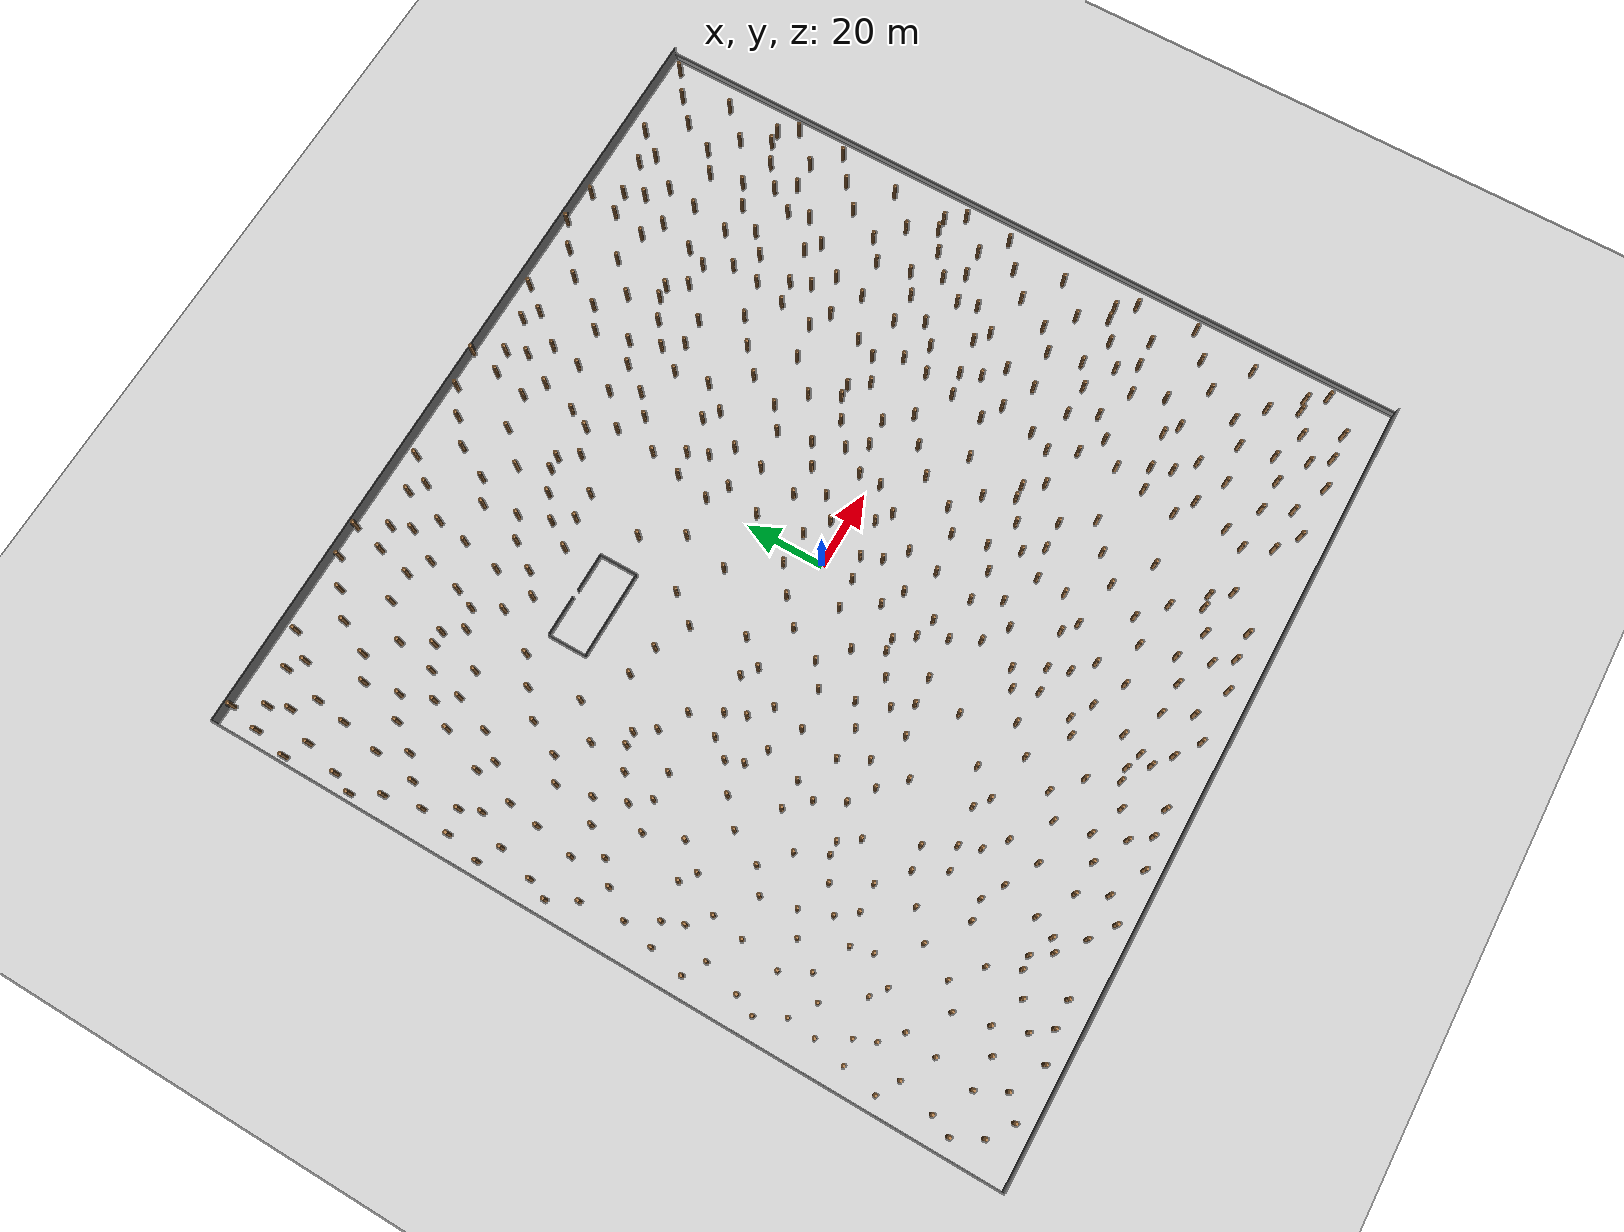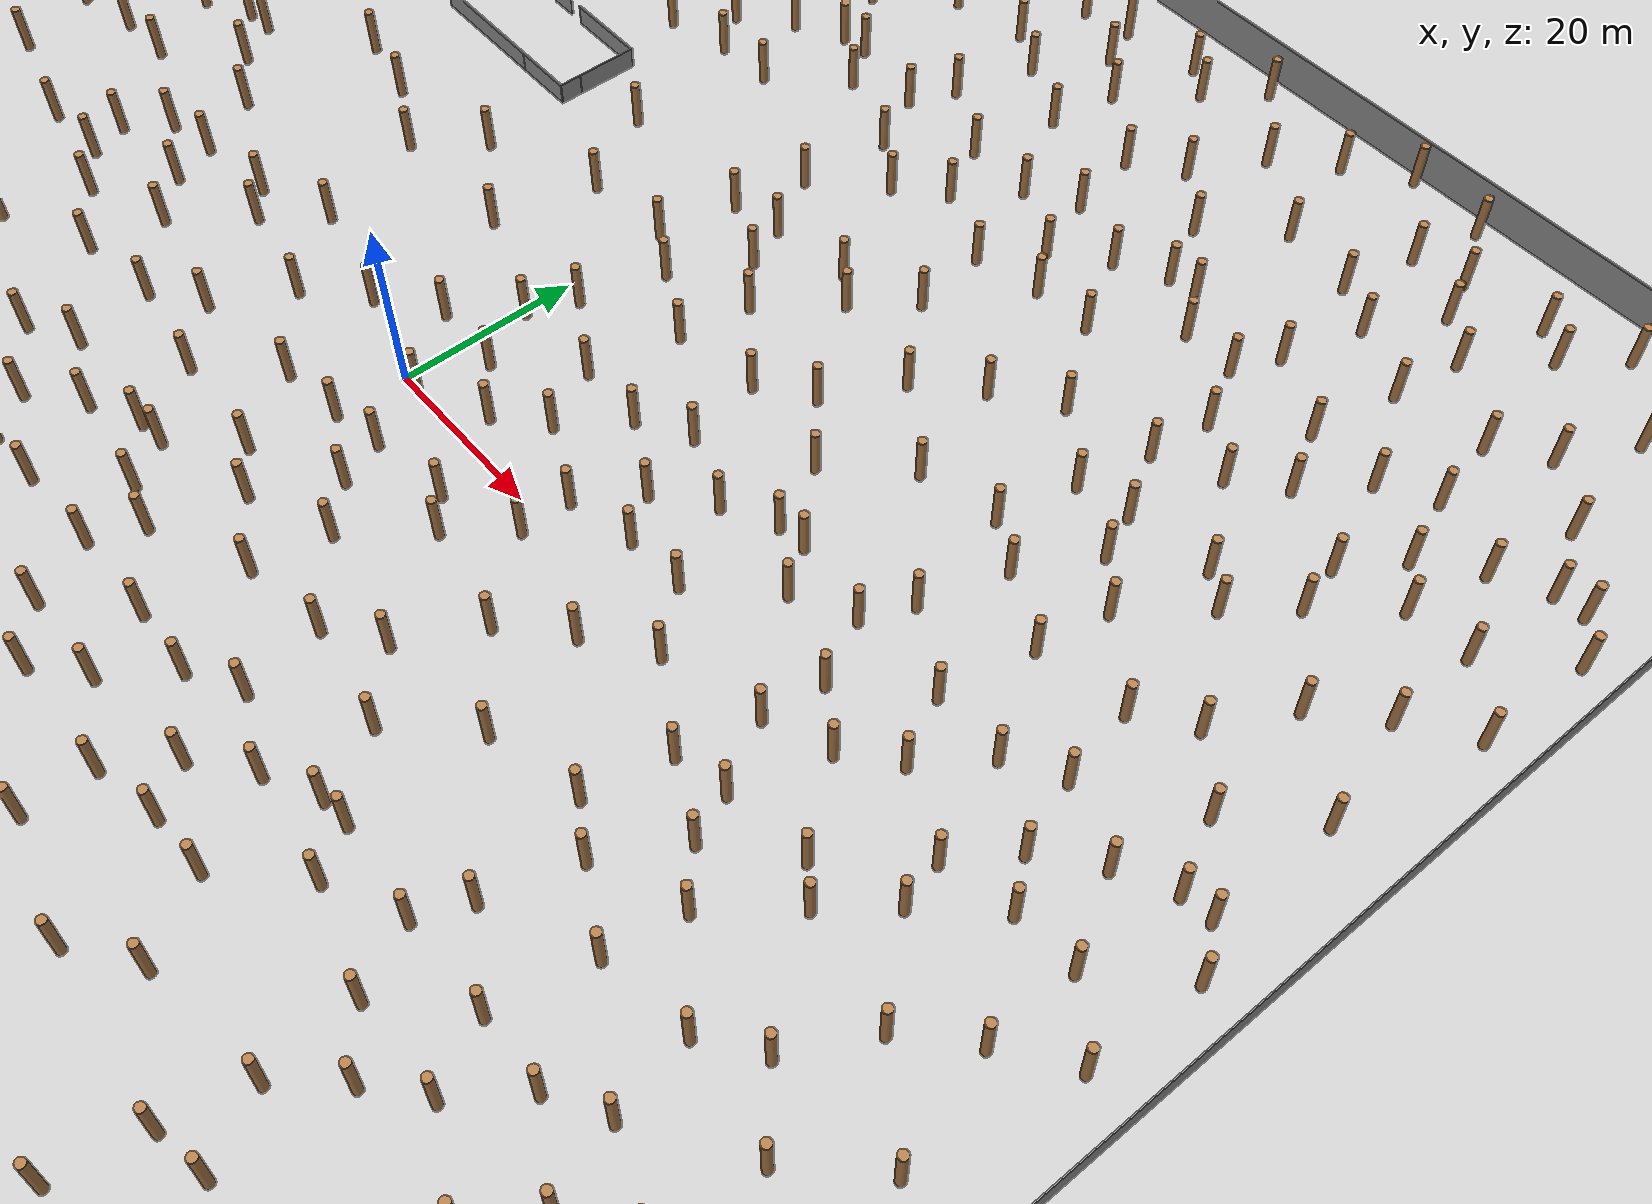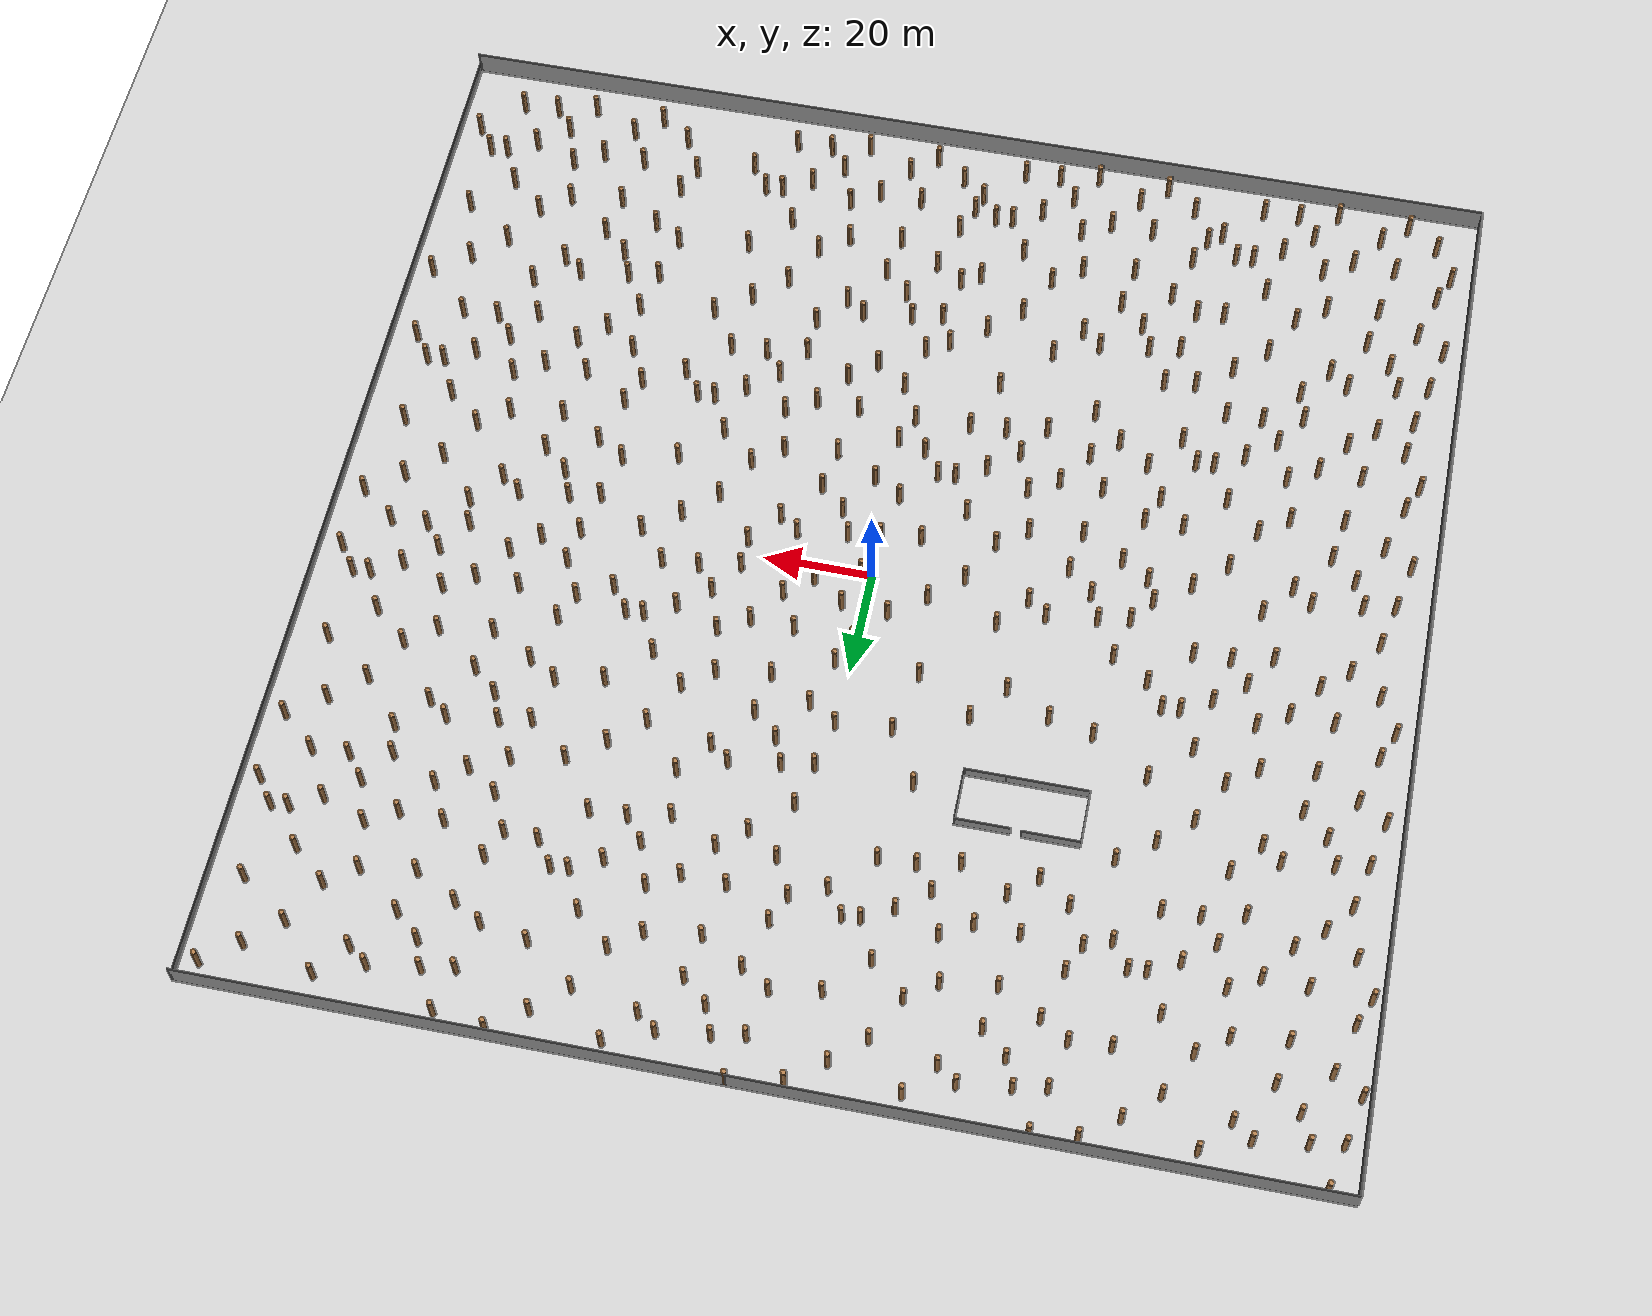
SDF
<sdf version="1.6">
 <world name="default">
  <light name="sun" type="directional">
   <pose>0 0 10 0 -0 0</pose>
   <diffuse>0.8 0.8 0.8 1</diffuse>
   <specular>0.2 0.2 0.2 1</specular>
   <attenuation>
    <range>1000</range>
    <constant>0.9</constant>
    <linear>0.01</linear>
    <quadratic>0.001</quadratic>
   </attenuation>
   <direction>-0.5 0.1 -0.9</direction>
  </light>
  <model name="ground_plane">
   <static>1</static>
   <link name="link">
    <collision name="collision">
     <geometry><plane><normal>0 0 1</normal><size>100 100</size></plane></geometry>
     <surface><friction><ode><mu>100</mu><mu2>50</mu2></ode></friction></surface>
    </collision>
    <visual name="visual">
     <cast_shadows>0</cast_shadows>
     <geometry><plane><normal>0 0 1</normal><size>100 100</size></plane></geometry>
     <material>
      <script><uri>file://media/materials/scripts/gazebo.material</uri><name>Gazebo/Grey</name></script>
     </material>
    </visual>
   </link>
  </model>
  <gravity>0 0 -9.8</gravity>
  <magnetic_field>6e-06 2.3e-05 -4.2e-05</magnetic_field>
  <atmosphere type="adiabatic"/>
  <physics name="default_physics" default="0" type="ode">
   <max_step_size>0.001</max_step_size>
   <real_time_factor>1</real_time_factor>
   <real_time_update_rate>1000</real_time_update_rate>
  </physics>
  <scene><ambient>0.4 0.4 0.4 1</ambient><background>0.7 0.7 0.7 1</background><shadows>1</shadows></scene>
  <audio><device>default</device></audio>
  <spherical_coordinates>
   <surface_model>EARTH_WGS84</surface_model>
   <latitude_deg>0</latitude_deg>
   <longitude_deg>0</longitude_deg>
   <elevation>0</elevation>
   <heading_deg>0</heading_deg>
  </spherical_coordinates>
  <model name="new_200">
   <link name="Wall_0">
    <pose>0 -100 0 0 -0 0</pose>
    <visual name="Wall_0_Visual">
     <pose>0 0 2.5 0 -0 0</pose>
     <geometry><box><size>200.15 0.15 5</size></box></geometry>
     <material>
      <script><uri>file://media/materials/scripts/gazebo.material</uri><name>Gazebo/Grey</name></script>
      <ambient>1 1 1 1</ambient>
     </material>
     <meta><layer>0</layer></meta>
    </visual>
    <collision name="Wall_0_Collision">
     <pose>0 0 2.5 0 -0 0</pose>
     <geometry><box><size>200.15 0.15 5</size></box></geometry>
     <surface>
      <friction>
       <ode><mu>1</mu><mu2>1</mu2><fdir1>0 0 0</fdir1><slip1>0</slip1><slip2>0</slip2></ode>
       <torsional>
        <coefficient>1</coefficient>
        <patch_radius>0</patch_radius>
        <surface_radius>0</surface_radius>
        <use_patch_radius>1</use_patch_radius>
        <ode><slip>0</slip></ode>
       </torsional>
      </friction>
      <bounce><restitution_coefficient>0</restitution_coefficient><threshold>1e+06</threshold></bounce>
      <contact>
       <collide_without_contact>0</collide_without_contact>
       <collide_without_contact_bitmask>1</collide_without_contact_bitmask>
       <collide_bitmask>1</collide_bitmask>
       <ode>
        <soft_cfm>0</soft_cfm>
        <soft_erp>0.2</soft_erp>
        <kp>1e+13</kp>
        <kd>1</kd>
        <max_vel>0.01</max_vel>
        <min_depth>0</min_depth>
       </ode>
       <bullet>
        <split_impulse>1</split_impulse>
        <split_impulse_penetration_threshold>-0.01</split_impulse_penetration_threshold>
        <soft_cfm>0</soft_cfm>
        <soft_erp>0.2</soft_erp>
        <kp>1e+13</kp>
        <kd>1</kd>
       </bullet>
      </contact>
     </surface>
    </collision>
   </link>
   <link name="Wall_2">
    <pose>-100 0 0 0 -0 1.5708</pose>
    <visual name="Wall_2_Visual">
     <pose>0 0 2.5 0 -0 0</pose>
     <geometry><box><size>200.15 0.15 5</size></box></geometry>
     <material>
      <script><uri>file://media/materials/scripts/gazebo.material</uri><name>Gazebo/Grey</name></script>
      <ambient>1 1 1 1</ambient>
     </material>
     <meta><layer>0</layer></meta>
    </visual>
    <collision name="Wall_2_Collision">
     <pose>0 0 2.5 0 -0 0</pose>
     <geometry><box><size>200.15 0.15 5</size></box></geometry>
     <surface>
      <friction>
       <ode><mu>1</mu><mu2>1</mu2><fdir1>0 0 0</fdir1><slip1>0</slip1><slip2>0</slip2></ode>
       <torsional>
        <coefficient>1</coefficient>
        <patch_radius>0</patch_radius>
        <surface_radius>0</surface_radius>
        <use_patch_radius>1</use_patch_radius>
        <ode><slip>0</slip></ode>
       </torsional>
      </friction>
      <bounce><restitution_coefficient>0</restitution_coefficient><threshold>1e+06</threshold></bounce>
      <contact>
       <collide_without_contact>0</collide_without_contact>
       <collide_without_contact_bitmask>1</collide_without_contact_bitmask>
       <collide_bitmask>1</collide_bitmask>
       <ode>
        <soft_cfm>0</soft_cfm>
        <soft_erp>0.2</soft_erp>
        <kp>1e+13</kp>
        <kd>1</kd>
        <max_vel>0.01</max_vel>
        <min_depth>0</min_depth>
       </ode>
       <bullet>
        <split_impulse>1</split_impulse>
        <split_impulse_penetration_threshold>-0.01</split_impulse_penetration_threshold>
        <soft_cfm>0</soft_cfm>
        <soft_erp>0.2</soft_erp>
        <kp>1e+13</kp>
        <kd>1</kd>
       </bullet>
      </contact>
     </surface>
    </collision>
   </link>
   <link name="Wall_4">
    <pose>0 100 0 0 -0 0</pose>
    <visual name="Wall_4_Visual">
     <pose>0 0 2.5 0 -0 0</pose>
     <geometry><box><size>200.15 0.15 5</size></box></geometry>
     <material>
      <script><uri>file://media/materials/scripts/gazebo.material</uri><name>Gazebo/Grey</name></script>
      <ambient>1 1 1 1</ambient>
     </material>
     <meta><layer>0</layer></meta>
    </visual>
    <collision name="Wall_4_Collision">
     <pose>0 0 2.5 0 -0 0</pose>
     <geometry><box><size>200.15 0.15 5</size></box></geometry>
     <surface>
      <friction>
       <ode><mu>1</mu><mu2>1</mu2><fdir1>0 0 0</fdir1><slip1>0</slip1><slip2>0</slip2></ode>
       <torsional>
        <coefficient>1</coefficient>
        <patch_radius>0</patch_radius>
        <surface_radius>0</surface_radius>
        <use_patch_radius>1</use_patch_radius>
        <ode><slip>0</slip></ode>
       </torsional>
      </friction>
      <bounce><restitution_coefficient>0</restitution_coefficient><threshold>1e+06</threshold></bounce>
      <contact>
       <collide_without_contact>0</collide_without_contact>
       <collide_without_contact_bitmask>1</collide_without_contact_bitmask>
       <collide_bitmask>1</collide_bitmask>
       <ode>
        <soft_cfm>0</soft_cfm>
        <soft_erp>0.2</soft_erp>
        <kp>1e+13</kp>
        <kd>1</kd>
        <max_vel>0.01</max_vel>
        <min_depth>0</min_depth>
       </ode>
       <bullet>
        <split_impulse>1</split_impulse>
        <split_impulse_penetration_threshold>-0.01</split_impulse_penetration_threshold>
        <soft_cfm>0</soft_cfm>
        <soft_erp>0.2</soft_erp>
        <kp>1e+13</kp>
        <kd>1</kd>
       </bullet>
      </contact>
     </surface>
    </collision>
   </link>
   <link name="Wall_6">
    <pose>100 0 0 0 -0 1.5708</pose>
    <visual name="Wall_6_Visual">
     <pose>0 0 1.25 0 -0 0</pose>
     <geometry><box><size>200.15 0.15 2.5</size></box></geometry>
     <material>
      <script><uri>file://media/materials/scripts/gazebo.material</uri><name>Gazebo/Grey</name></script>
      <ambient>1 1 1 1</ambient>
     </material>
     <meta><layer>0</layer></meta>
    </visual>
    <collision name="Wall_6_Collision">
     <pose>0 0 1.25 0 -0 0</pose>
     <geometry><box><size>200.15 0.15 2.5</size></box></geometry>
     <surface>
      <friction>
       <ode><mu>1</mu><mu2>1</mu2><fdir1>0 0 0</fdir1><slip1>0</slip1><slip2>0</slip2></ode>
       <torsional>
        <coefficient>1</coefficient>
        <patch_radius>0</patch_radius>
        <surface_radius>0</surface_radius>
        <use_patch_radius>1</use_patch_radius>
        <ode><slip>0</slip></ode>
       </torsional>
      </friction>
      <bounce><restitution_coefficient>0</restitution_coefficient><threshold>1e+06</threshold></bounce>
      <contact>
       <collide_without_contact>0</collide_without_contact>
       <collide_without_contact_bitmask>1</collide_without_contact_bitmask>
       <collide_bitmask>1</collide_bitmask>
       <ode>
        <soft_cfm>0</soft_cfm>
        <soft_erp>0.2</soft_erp>
        <kp>1e+13</kp>
        <kd>1</kd>
        <max_vel>0.01</max_vel>
        <min_depth>0</min_depth>
       </ode>
       <bullet>
        <split_impulse>1</split_impulse>
        <split_impulse_penetration_threshold>-0.01</split_impulse_penetration_threshold>
        <soft_cfm>0</soft_cfm>
        <soft_erp>0.2</soft_erp>
        <kp>1e+13</kp>
        <kd>1</kd>
       </bullet>
      </contact>
     </surface>
    </collision>
   </link>
   <static>1</static>
   <pose>-0.033076 0.009856 0 0 -0 0</pose>
  </model>
  <model name="WoodPillars">
   <link name="link">
    <inertial>
     <mass>1</mass>
     <inertia><ixx>0.145833</ixx><ixy>0</ixy><ixz>0</ixz><iyy>0.145833</iyy><iyz>0</iyz><izz>0.125</izz></inertia>
    </inertial>
    <visual name="visual">
     <geometry><cylinder><radius>0.5</radius><length>5.50507</length></cylinder></geometry>
     <material>
      <script><name>Gazebo/Wood</name><uri>file://media/materials/scripts/gazebo.material</uri></script>
     </material>
    </visual>
    <collision name="collision">
     <geometry><cylinder><radius>0.5</radius><length>5.50507</length></cylinder></geometry>
     <surface>
      <friction>
       <ode><mu>1</mu><mu2>1</mu2><fdir1>0 0 0</fdir1><slip1>0</slip1><slip2>0</slip2></ode>
       <torsional>
        <coefficient>1</coefficient>
        <patch_radius>0</patch_radius>
        <surface_radius>0</surface_radius>
        <use_patch_radius>1</use_patch_radius>
        <ode><slip>0</slip></ode>
       </torsional>
      </friction>
      <bounce><restitution_coefficient>0</restitution_coefficient><threshold>1e+06</threshold></bounce>
      <contact>
       <collide_without_contact>0</collide_without_contact>
       <collide_without_contact_bitmask>1</collide_without_contact_bitmask>
       <collide_bitmask>1</collide_bitmask>
       <ode>
        <soft_cfm>0</soft_cfm>
        <soft_erp>0.2</soft_erp>
        <kp>1e+13</kp>
        <kd>1</kd>
        <max_vel>0.01</max_vel>
        <min_depth>0</min_depth>
       </ode>
       <bullet>
        <split_impulse>1</split_impulse>
        <split_impulse_penetration_threshold>-0.01</split_impulse_penetration_threshold>
        <soft_cfm>0</soft_cfm>
        <soft_erp>0.2</soft_erp>
        <kp>1e+13</kp>
        <kd>1</kd>
       </bullet>
      </contact>
     </surface>
    </collision>
   </link>
   <link name="link_clone">
    <inertial>
     <mass>1</mass>
     <inertia><ixx>0.145833</ixx><ixy>0</ixy><ixz>0</ixz><iyy>0.145833</iyy><iyz>0</iyz><izz>0.125</izz></inertia>
    </inertial>
    <pose>17.6954 -2.91348 -2e-06 0 -0 -0.001289</pose>
    <visual name="visual">
     <geometry><cylinder><radius>0.5</radius><length>5.50507</length></cylinder></geometry>
     <material>
      <script><name>Gazebo/Wood</name><uri>file://media/materials/scripts/gazebo.material</uri></script>
      <shader type="pixel"/>
     </material>
    </visual>
    <collision name="collision">
     <geometry><cylinder><radius>0.5</radius><length>5.50507</length></cylinder></geometry>
     <surface>
      <friction>
       <ode><mu>1</mu><mu2>1</mu2><fdir1>0 0 0</fdir1><slip1>0</slip1><slip2>0</slip2></ode>
       <torsional>
        <coefficient>1</coefficient>
        <patch_radius>0</patch_radius>
        <surface_radius>0</surface_radius>
        <use_patch_radius>1</use_patch_radius>
        <ode><slip>0</slip></ode>
       </torsional>
      </friction>
      <bounce><restitution_coefficient>0</restitution_coefficient><threshold>1e+06</threshold></bounce>
      <contact>
       <collide_without_contact>0</collide_without_contact>
       <collide_without_contact_bitmask>1</collide_without_contact_bitmask>
       <collide_bitmask>1</collide_bitmask>
       <ode>
        <soft_cfm>0</soft_cfm>
        <soft_erp>0.2</soft_erp>
        <kp>1e+13</kp>
        <kd>1</kd>
        <max_vel>0.01</max_vel>
        <min_depth>0</min_depth>
       </ode>
       <bullet>
        <split_impulse>1</split_impulse>
        <split_impulse_penetration_threshold>-0.01</split_impulse_penetration_threshold>
        <soft_cfm>0</soft_cfm>
        <soft_erp>0.2</soft_erp>
        <kp>1e+13</kp>
        <kd>1</kd>
       </bullet>
      </contact>
     </surface>
    </collision>
   </link>
   <link name="link_clone_10">
    <inertial>
     <mass>1</mass>
     <inertia><ixx>0.145833</ixx><ixy>0</ixy><ixz>0</ixz><iyy>0.145833</iyy><iyz>0</iyz><izz>0.125</izz></inertia>
    </inertial>
    <pose>2.50237 12.8939 0 0 -0 -0.001289</pose>
    <visual name="visual">
     <geometry><cylinder><radius>0.5</radius><length>5.50507</length></cylinder></geometry>
     <material>
      <script><name>Gazebo/Wood</name><uri>file://media/materials/scripts/gazebo.material</uri></script>
      <shader type="pixel"/>
     </material>
    </visual>
    <collision name="collision">
     <geometry><cylinder><radius>0.5</radius><length>5.50507</length></cylinder></geometry>
     <surface>
      <friction>
       <ode><mu>1</mu><mu2>1</mu2><fdir1>0 0 0</fdir1><slip1>0</slip1><slip2>0</slip2></ode>
       <torsional>
        <coefficient>1</coefficient>
        <patch_radius>0</patch_radius>
        <surface_radius>0</surface_radius>
        <use_patch_radius>1</use_patch_radius>
        <ode><slip>0</slip></ode>
       </torsional>
      </friction>
      <bounce><restitution_coefficient>0</restitution_coefficient><threshold>1e+06</threshold></bounce>
      <contact>
       <collide_without_contact>0</collide_without_contact>
       <collide_without_contact_bitmask>1</collide_without_contact_bitmask>
       <collide_bitmask>1</collide_bitmask>
       <ode>
        <soft_cfm>0</soft_cfm>
        <soft_erp>0.2</soft_erp>
        <kp>1e+13</kp>
        <kd>1</kd>
        <max_vel>0.01</max_vel>
        <min_depth>0</min_depth>
       </ode>
       <bullet>
        <split_impulse>1</split_impulse>
        <split_impulse_penetration_threshold>-0.01</split_impulse_penetration_threshold>
        <soft_cfm>0</soft_cfm>
        <soft_erp>0.2</soft_erp>
        <kp>1e+13</kp>
        <kd>1</kd>
       </bullet>
      </contact>
     </surface>
    </collision>
   </link>
   <link name="link_clone_11">
    <inertial>
     <mass>1</mass>
     <inertia><ixx>0.145833</ixx><ixy>0</ixy><ixz>0</ixz><iyy>0.145833</iyy><iyz>0</iyz><izz>0.125</izz></inertia>
    </inertial>
    <pose>20.1245 17.4079 -2e-06 0 -0 -0.001289</pose>
    <visual name="visual">
     <geometry><cylinder><radius>0.5</radius><length>5.50507</length></cylinder></geometry>
     <material>
      <script><name>Gazebo/Wood</name><uri>file://media/materials/scripts/gazebo.material</uri></script>
      <shader type="pixel"/>
     </material>
    </visual>
    <collision name="collision">
     <geometry><cylinder><radius>0.5</radius><length>5.50507</length></cylinder></geometry>
     <surface>
      <friction>
       <ode><mu>1</mu><mu2>1</mu2><fdir1>0 0 0</fdir1><slip1>0</slip1><slip2>0</slip2></ode>
       <torsional>
        <coefficient>1</coefficient>
        <patch_radius>0</patch_radius>
        <surface_radius>0</surface_radius>
        <use_patch_radius>1</use_patch_radius>
        <ode><slip>0</slip></ode>
       </torsional>
      </friction>
      <bounce><restitution_coefficient>0</restitution_coefficient><threshold>1e+06</threshold></bounce>
      <contact>
       <collide_without_contact>0</collide_without_contact>
       <collide_without_contact_bitmask>1</collide_without_contact_bitmask>
       <collide_bitmask>1</collide_bitmask>
       <ode>
        <soft_cfm>0</soft_cfm>
        <soft_erp>0.2</soft_erp>
        <kp>1e+13</kp>
        <kd>1</kd>
        <max_vel>0.01</max_vel>
        <min_depth>0</min_depth>
       </ode>
       <bullet>
        <split_impulse>1</split_impulse>
        <split_impulse_penetration_threshold>-0.01</split_impulse_penetration_threshold>
        <soft_cfm>0</soft_cfm>
        <soft_erp>0.2</soft_erp>
        <kp>1e+13</kp>
        <kd>1</kd>
       </bullet>
      </contact>
     </surface>
    </collision>
   </link>
   <link name="link_clone_12">
    <inertial>
     <mass>1</mass>
     <inertia><ixx>0.145833</ixx><ixy>0</ixy><ixz>0</ixz><iyy>0.145833</iyy><iyz>0</iyz><izz>0.125</izz></inertia>
    </inertial>
    <pose>36.6063 2.3916 -3e-06 0 -0 -0.001289</pose>
    <visual name="visual">
     <geometry><cylinder><radius>0.5</radius><length>5.50507</length></cylinder></geometry>
     <material>
      <script><name>Gazebo/Wood</name><uri>file://media/materials/scripts/gazebo.material</uri></script>
      <shader type="pixel"/>
     </material>
    </visual>
    <collision name="collision">
     <geometry><cylinder><radius>0.5</radius><length>5.50507</length></cylinder></geometry>
     <surface>
      <friction>
       <ode><mu>1</mu><mu2>1</mu2><fdir1>0 0 0</fdir1><slip1>0</slip1><slip2>0</slip2></ode>
       <torsional>
        <coefficient>1</coefficient>
        <patch_radius>0</patch_radius>
        <surface_radius>0</surface_radius>
        <use_patch_radius>1</use_patch_radius>
        <ode><slip>0</slip></ode>
       </torsional>
      </friction>
      <bounce><restitution_coefficient>0</restitution_coefficient><threshold>1e+06</threshold></bounce>
      <contact>
       <collide_without_contact>0</collide_without_contact>
       <collide_without_contact_bitmask>1</collide_without_contact_bitmask>
       <collide_bitmask>1</collide_bitmask>
       <ode>
        <soft_cfm>0</soft_cfm>
        <soft_erp>0.2</soft_erp>
        <kp>1e+13</kp>
        <kd>1</kd>
        <max_vel>0.01</max_vel>
        <min_depth>0</min_depth>
       </ode>
       <bullet>
        <split_impulse>1</split_impulse>
        <split_impulse_penetration_threshold>-0.01</split_impulse_penetration_threshold>
        <soft_cfm>0</soft_cfm>
        <soft_erp>0.2</soft_erp>
        <kp>1e+13</kp>
        <kd>1</kd>
       </bullet>
      </contact>
     </surface>
    </collision>
   </link>
   <link name="link_clone_13">
    <inertial>
     <mass>1</mass>
     <inertia><ixx>0.145833</ixx><ixy>0</ixy><ixz>0</ixz><iyy>0.145833</iyy><iyz>0</iyz><izz>0.125</izz></inertia>
    </inertial>
    <pose>32.2715 -23.3528 -3e-06 0 -0 -0.001289</pose>
    <visual name="visual">
     <geometry><cylinder><radius>0.5</radius><length>5.50507</length></cylinder></geometry>
     <material>
      <script><name>Gazebo/Wood</name><uri>file://media/materials/scripts/gazebo.material</uri></script>
      <shader type="pixel"/>
     </material>
    </visual>
    <collision name="collision">
     <geometry><cylinder><radius>0.5</radius><length>5.50507</length></cylinder></geometry>
     <surface>
      <friction>
       <ode><mu>1</mu><mu2>1</mu2><fdir1>0 0 0</fdir1><slip1>0</slip1><slip2>0</slip2></ode>
       <torsional>
        <coefficient>1</coefficient>
        <patch_radius>0</patch_radius>
        <surface_radius>0</surface_radius>
        <use_patch_radius>1</use_patch_radius>
        <ode><slip>0</slip></ode>
       </torsional>
      </friction>
      <bounce><restitution_coefficient>0</restitution_coefficient><threshold>1e+06</threshold></bounce>
      <contact>
       <collide_without_contact>0</collide_without_contact>
       <collide_without_contact_bitmask>1</collide_without_contact_bitmask>
       <collide_bitmask>1</collide_bitmask>
       <ode>
        <soft_cfm>0</soft_cfm>
        <soft_erp>0.2</soft_erp>
        <kp>1e+13</kp>
        <kd>1</kd>
        <max_vel>0.01</max_vel>
        <min_depth>0</min_depth>
       </ode>
       <bullet>
        <split_impulse>1</split_impulse>
        <split_impulse_penetration_threshold>-0.01</split_impulse_penetration_threshold>
        <soft_cfm>0</soft_cfm>
        <soft_erp>0.2</soft_erp>
        <kp>1e+13</kp>
        <kd>1</kd>
       </bullet>
      </contact>
     </surface>
    </collision>
   </link>
   <link name="link_clone_14">
    <inertial>
     <mass>1</mass>
     <inertia><ixx>0.145833</ixx><ixy>0</ixy><ixz>0</ixz><iyy>0.145833</iyy><iyz>0</iyz><izz>0.125</izz></inertia>
    </inertial>
    <pose>9.31461 -20.9997 -1e-06 0 -0 -0.001289</pose>
    <visual name="visual">
     <geometry><cylinder><radius>0.5</radius><length>5.50507</length></cylinder></geometry>
     <material>
      <script><name>Gazebo/Wood</name><uri>file://media/materials/scripts/gazebo.material</uri></script>
      <shader type="pixel"/>
     </material>
    </visual>
    <collision name="collision">
     <geometry><cylinder><radius>0.5</radius><length>5.50507</length></cylinder></geometry>
     <surface>
      <friction>
       <ode><mu>1</mu><mu2>1</mu2><fdir1>0 0 0</fdir1><slip1>0</slip1><slip2>0</slip2></ode>
       <torsional>
        <coefficient>1</coefficient>
        <patch_radius>0</patch_radius>
        <surface_radius>0</surface_radius>
        <use_patch_radius>1</use_patch_radius>
        <ode><slip>0</slip></ode>
       </torsional>
      </friction>
      <bounce><restitution_coefficient>0</restitution_coefficient><threshold>1e+06</threshold></bounce>
      <contact>
       <collide_without_contact>0</collide_without_contact>
       <collide_without_contact_bitmask>1</collide_without_contact_bitmask>
       <collide_bitmask>1</collide_bitmask>
       <ode>
        <soft_cfm>0</soft_cfm>
        <soft_erp>0.2</soft_erp>
        <kp>1e+13</kp>
        <kd>1</kd>
        <max_vel>0.01</max_vel>
        <min_depth>0</min_depth>
       </ode>
       <bullet>
        <split_impulse>1</split_impulse>
        <split_impulse_penetration_threshold>-0.01</split_impulse_penetration_threshold>
        <soft_cfm>0</soft_cfm>
        <soft_erp>0.2</soft_erp>
        <kp>1e+13</kp>
        <kd>1</kd>
       </bullet>
      </contact>
     </surface>
    </collision>
   </link>
   <link name="link_clone_15">
    <inertial>
     <mass>1</mass>
     <inertia><ixx>0.145833</ixx><ixy>0</ixy><ixz>0</ixz><iyy>0.145833</iyy><iyz>0</iyz><izz>0.125</izz></inertia>
    </inertial>
    <pose>17.9894 -25.1945 -2e-06 0 -0 -0.001289</pose>
    <visual name="visual">
     <geometry><cylinder><radius>0.5</radius><length>5.50507</length></cylinder></geometry>
     <material>
      <script><name>Gazebo/Wood</name><uri>file://media/materials/scripts/gazebo.material</uri></script>
      <shader type="pixel"/>
     </material>
    </visual>
    <collision name="collision">
     <geometry><cylinder><radius>0.5</radius><length>5.50507</length></cylinder></geometry>
     <surface>
      <friction>
       <ode><mu>1</mu><mu2>1</mu2><fdir1>0 0 0</fdir1><slip1>0</slip1><slip2>0</slip2></ode>
       <torsional>
        <coefficient>1</coefficient>
        <patch_radius>0</patch_radius>
        <surface_radius>0</surface_radius>
        <use_patch_radius>1</use_patch_radius>
        <ode><slip>0</slip></ode>
       </torsional>
      </friction>
      <bounce><restitution_coefficient>0</restitution_coefficient><threshold>1e+06</threshold></bounce>
      <contact>
       <collide_without_contact>0</collide_without_contact>
       <collide_without_contact_bitmask>1</collide_without_contact_bitmask>
       <collide_bitmask>1</collide_bitmask>
       <ode>
        <soft_cfm>0</soft_cfm>
        <soft_erp>0.2</soft_erp>
        <kp>1e+13</kp>
        <kd>1</kd>
        <max_vel>0.01</max_vel>
        <min_depth>0</min_depth>
       </ode>
       <bullet>
        <split_impulse>1</split_impulse>
        <split_impulse_penetration_threshold>-0.01</split_impulse_penetration_threshold>
        <soft_cfm>0</soft_cfm>
        <soft_erp>0.2</soft_erp>
        <kp>1e+13</kp>
        <kd>1</kd>
       </bullet>
      </contact>
     </surface>
    </collision>
   </link>
   <link name="link_clone_16">
    <inertial>
     <mass>1</mass>
     <inertia><ixx>0.145833</ixx><ixy>0</ixy><ixz>0</ixz><iyy>0.145833</iyy><iyz>0</iyz><izz>0.125</izz></inertia>
    </inertial>
    <pose>32.9662 -11.9429 -3e-06 0 -0 -0.001289</pose>
    <visual name="visual">
     <geometry><cylinder><radius>0.5</radius><length>5.50507</length></cylinder></geometry>
     <material>
      <script><name>Gazebo/Wood</name><uri>file://media/materials/scripts/gazebo.material</uri></script>
      <shader type="pixel"/>
     </material>
    </visual>
    <collision name="collision">
     <geometry><cylinder><radius>0.5</radius><length>5.50507</length></cylinder></geometry>
     <surface>
      <friction>
       <ode><mu>1</mu><mu2>1</mu2><fdir1>0 0 0</fdir1><slip1>0</slip1><slip2>0</slip2></ode>
       <torsional>
        <coefficient>1</coefficient>
        <patch_radius>0</patch_radius>
        <surface_radius>0</surface_radius>
        <use_patch_radius>1</use_patch_radius>
        <ode><slip>0</slip></ode>
       </torsional>
      </friction>
      <bounce><restitution_coefficient>0</restitution_coefficient><threshold>1e+06</threshold></bounce>
      <contact>
       <collide_without_contact>0</collide_without_contact>
       <collide_without_contact_bitmask>1</collide_without_contact_bitmask>
       <collide_bitmask>1</collide_bitmask>
       <ode>
        <soft_cfm>0</soft_cfm>
        <soft_erp>0.2</soft_erp>
        <kp>1e+13</kp>
        <kd>1</kd>
        <max_vel>0.01</max_vel>
        <min_depth>0</min_depth>
       </ode>
       <bullet>
        <split_impulse>1</split_impulse>
        <split_impulse_penetration_threshold>-0.01</split_impulse_penetration_threshold>
        <soft_cfm>0</soft_cfm>
        <soft_erp>0.2</soft_erp>
        <kp>1e+13</kp>
        <kd>1</kd>
       </bullet>
      </contact>
     </surface>
    </collision>
   </link>
   <link name="link_clone_17">
    <inertial>
     <mass>1</mass>
     <inertia><ixx>0.145833</ixx><ixy>0</ixy><ixz>0</ixz><iyy>0.145833</iyy><iyz>0</iyz><izz>0.125</izz></inertia>
    </inertial>
    <pose>19.3784 -11.4604 -2e-06 0 -0 -0.001289</pose>
    <visual name="visual">
     <geometry><cylinder><radius>0.5</radius><length>5.50507</length></cylinder></geometry>
     <material>
      <script><name>Gazebo/Wood</name><uri>file://media/materials/scripts/gazebo.material</uri></script>
      <shader type="pixel"/>
     </material>
    </visual>
    <collision name="collision">
     <geometry><cylinder><radius>0.5</radius><length>5.50507</length></cylinder></geometry>
     <surface>
      <friction>
       <ode><mu>1</mu><mu2>1</mu2><fdir1>0 0 0</fdir1><slip1>0</slip1><slip2>0</slip2></ode>
       <torsional>
        <coefficient>1</coefficient>
        <patch_radius>0</patch_radius>
        <surface_radius>0</surface_radius>
        <use_patch_radius>1</use_patch_radius>
        <ode><slip>0</slip></ode>
       </torsional>
      </friction>
      <bounce><restitution_coefficient>0</restitution_coefficient><threshold>1e+06</threshold></bounce>
      <contact>
       <collide_without_contact>0</collide_without_contact>
       <collide_without_contact_bitmask>1</collide_without_contact_bitmask>
       <collide_bitmask>1</collide_bitmask>
       <ode>
        <soft_cfm>0</soft_cfm>
        <soft_erp>0.2</soft_erp>
        <kp>1e+13</kp>
        <kd>1</kd>
        <max_vel>0.01</max_vel>
        <min_depth>0</min_depth>
       </ode>
       <bullet>
        <split_impulse>1</split_impulse>
        <split_impulse_penetration_threshold>-0.01</split_impulse_penetration_threshold>
        <soft_cfm>0</soft_cfm>
        <soft_erp>0.2</soft_erp>
        <kp>1e+13</kp>
        <kd>1</kd>
       </bullet>
      </contact>
     </surface>
    </collision>
   </link>
   <link name="link_clone_18">
    <inertial>
     <mass>1</mass>
     <inertia><ixx>0.145833</ixx><ixy>0</ixy><ixz>0</ixz><iyy>0.145833</iyy><iyz>0</iyz><izz>0.125</izz></inertia>
    </inertial>
    <pose>9.1573 3.67739 -1e-06 0 -0 -0.001289</pose>
    <visual name="visual">
     <geometry><cylinder><radius>0.5</radius><length>5.50507</length></cylinder></geometry>
     <material>
      <script><name>Gazebo/Wood</name><uri>file://media/materials/scripts/gazebo.material</uri></script>
      <shader type="pixel"/>
     </material>
    </visual>
    <collision name="collision">
     <geometry><cylinder><radius>0.5</radius><length>5.50507</length></cylinder></geometry>
     <surface>
      <friction>
       <ode><mu>1</mu><mu2>1</mu2><fdir1>0 0 0</fdir1><slip1>0</slip1><slip2>0</slip2></ode>
       <torsional>
        <coefficient>1</coefficient>
        <patch_radius>0</patch_radius>
        <surface_radius>0</surface_radius>
        <use_patch_radius>1</use_patch_radius>
        <ode><slip>0</slip></ode>
       </torsional>
      </friction>
      <bounce><restitution_coefficient>0</restitution_coefficient><threshold>1e+06</threshold></bounce>
      <contact>
       <collide_without_contact>0</collide_without_contact>
       <collide_without_contact_bitmask>1</collide_without_contact_bitmask>
       <collide_bitmask>1</collide_bitmask>
       <ode>
        <soft_cfm>0</soft_cfm>
        <soft_erp>0.2</soft_erp>
        <kp>1e+13</kp>
        <kd>1</kd>
        <max_vel>0.01</max_vel>
        <min_depth>0</min_depth>
       </ode>
       <bullet>
        <split_impulse>1</split_impulse>
        <split_impulse_penetration_threshold>-0.01</split_impulse_penetration_threshold>
        <soft_cfm>0</soft_cfm>
        <soft_erp>0.2</soft_erp>
        <kp>1e+13</kp>
        <kd>1</kd>
       </bullet>
      </contact>
     </surface>
    </collision>
   </link>
   <link name="link_clone_19">
    <inertial>
     <mass>1</mass>
     <inertia><ixx>0.145833</ixx><ixy>0</ixy><ixz>0</ixz><iyy>0.145833</iyy><iyz>0</iyz><izz>0.125</izz></inertia>
    </inertial>
    <pose>-3.28611 11.8265 -0 0 -0 -0.001289</pose>
    <visual name="visual">
     <geometry><cylinder><radius>0.5</radius><length>5.50507</length></cylinder></geometry>
     <material>
      <script><name>Gazebo/Wood</name><uri>file://media/materials/scripts/gazebo.material</uri></script>
      <shader type="pixel"/>
     </material>
    </visual>
    <collision name="collision">
     <geometry><cylinder><radius>0.5</radius><length>5.50507</length></cylinder></geometry>
     <surface>
      <friction>
       <ode><mu>1</mu><mu2>1</mu2><fdir1>0 0 0</fdir1><slip1>0</slip1><slip2>0</slip2></ode>
       <torsional>
        <coefficient>1</coefficient>
        <patch_radius>0</patch_radius>
        <surface_radius>0</surface_radius>
        <use_patch_radius>1</use_patch_radius>
        <ode><slip>0</slip></ode>
       </torsional>
      </friction>
      <bounce><restitution_coefficient>0</restitution_coefficient><threshold>1e+06</threshold></bounce>
      <contact>
       <collide_without_contact>0</collide_without_contact>
       <collide_without_contact_bitmask>1</collide_without_contact_bitmask>
       <collide_bitmask>1</collide_bitmask>
       <ode>
        <soft_cfm>0</soft_cfm>
        <soft_erp>0.2</soft_erp>
        <kp>1e+13</kp>
        <kd>1</kd>
        <max_vel>0.01</max_vel>
        <min_depth>0</min_depth>
       </ode>
       <bullet>
        <split_impulse>1</split_impulse>
        <split_impulse_penetration_threshold>-0.01</split_impulse_penetration_threshold>
        <soft_cfm>0</soft_cfm>
        <soft_erp>0.2</soft_erp>
        <kp>1e+13</kp>
        <kd>1</kd>
       </bullet>
      </contact>
     </surface>
    </collision>
   </link>
   <link name="link_clone_20">
    <inertial>
     <mass>1</mass>
     <inertia><ixx>0.145833</ixx><ixy>0</ixy><ixz>0</ixz><iyy>0.145833</iyy><iyz>0</iyz><izz>0.125</izz></inertia>
    </inertial>
    <pose>-2.64423 -9.12396 -0 0 -0 -0.001289</pose>
    <visual name="visual">
     <geometry><cylinder><radius>0.5</radius><length>5.50507</length></cylinder></geometry>
     <material>
      <script><name>Gazebo/Wood</name><uri>file://media/materials/scripts/gazebo.material</uri></script>
      <shader type="pixel"/>
     </material>
    </visual>
    <collision name="collision">
     <geometry><cylinder><radius>0.5</radius><length>5.50507</length></cylinder></geometry>
     <surface>
      <friction>
       <ode><mu>1</mu><mu2>1</mu2><fdir1>0 0 0</fdir1><slip1>0</slip1><slip2>0</slip2></ode>
       <torsional>
        <coefficient>1</coefficient>
        <patch_radius>0</patch_radius>
        <surface_radius>0</surface_radius>
        <use_patch_radius>1</use_patch_radius>
        <ode><slip>0</slip></ode>
       </torsional>
      </friction>
      <bounce><restitution_coefficient>0</restitution_coefficient><threshold>1e+06</threshold></bounce>
      <contact>
       <collide_without_contact>0</collide_without_contact>
       <collide_without_contact_bitmask>1</collide_without_contact_bitmask>
       <collide_bitmask>1</collide_bitmask>
       <ode>
        <soft_cfm>0</soft_cfm>
        <soft_erp>0.2</soft_erp>
        <kp>1e+13</kp>
        <kd>1</kd>
        <max_vel>0.01</max_vel>
        <min_depth>0</min_depth>
       </ode>
       <bullet>
        <split_impulse>1</split_impulse>
        <split_impulse_penetration_threshold>-0.01</split_impulse_penetration_threshold>
        <soft_cfm>0</soft_cfm>
        <soft_erp>0.2</soft_erp>
        <kp>1e+13</kp>
        <kd>1</kd>
       </bullet>
      </contact>
     </surface>
    </collision>
   </link>
   <link name="link_clone_21">
    <inertial>
     <mass>1</mass>
     <inertia><ixx>0.145833</ixx><ixy>0</ixy><ixz>0</ixz><iyy>0.145833</iyy><iyz>0</iyz><izz>0.125</izz></inertia>
    </inertial>
    <pose>15.2748 11.406 -1e-06 0 -0 -0.001289</pose>
    <visual name="visual">
     <geometry><cylinder><radius>0.5</radius><length>5.50507</length></cylinder></geometry>
     <material>
      <script><name>Gazebo/Wood</name><uri>file://media/materials/scripts/gazebo.material</uri></script>
      <shader type="pixel"/>
     </material>
    </visual>
    <collision name="collision">
     <geometry><cylinder><radius>0.5</radius><length>5.50507</length></cylinder></geometry>
     <surface>
      <friction>
       <ode><mu>1</mu><mu2>1</mu2><fdir1>0 0 0</fdir1><slip1>0</slip1><slip2>0</slip2></ode>
       <torsional>
        <coefficient>1</coefficient>
        <patch_radius>0</patch_radius>
        <surface_radius>0</surface_radius>
        <use_patch_radius>1</use_patch_radius>
        <ode><slip>0</slip></ode>
       </torsional>
      </friction>
      <bounce><restitution_coefficient>0</restitution_coefficient><threshold>1e+06</threshold></bounce>
      <contact>
       <collide_without_contact>0</collide_without_contact>
       <collide_without_contact_bitmask>1</collide_without_contact_bitmask>
       <collide_bitmask>1</collide_bitmask>
       <ode>
        <soft_cfm>0</soft_cfm>
        <soft_erp>0.2</soft_erp>
        <kp>1e+13</kp>
        <kd>1</kd>
        <max_vel>0.01</max_vel>
        <min_depth>0</min_depth>
       </ode>
       <bullet>
        <split_impulse>1</split_impulse>
        <split_impulse_penetration_threshold>-0.01</split_impulse_penetration_threshold>
        <soft_cfm>0</soft_cfm>
        <soft_erp>0.2</soft_erp>
        <kp>1e+13</kp>
        <kd>1</kd>
       </bullet>
      </contact>
     </surface>
    </collision>
   </link>
   <link name="link_clone_22">
    <inertial>
     <mass>1</mass>
     <inertia><ixx>0.145833</ixx><ixy>0</ixy><ixz>0</ixz><iyy>0.145833</iyy><iyz>0</iyz><izz>0.125</izz></inertia>
    </inertial>
    <pose>27.313 9.05961 -2e-06 0 -0 -0.001289</pose>
    <visual name="visual">
     <geometry><cylinder><radius>0.5</radius><length>5.50507</length></cylinder></geometry>
     <material>
      <script><name>Gazebo/Wood</name><uri>file://media/materials/scripts/gazebo.material</uri></script>
      <shader type="pixel"/>
     </material>
    </visual>
    <collision name="collision">
     <geometry><cylinder><radius>0.5</radius><length>5.50507</length></cylinder></geometry>
     <surface>
      <friction>
       <ode><mu>1</mu><mu2>1</mu2><fdir1>0 0 0</fdir1><slip1>0</slip1><slip2>0</slip2></ode>
       <torsional>
        <coefficient>1</coefficient>
        <patch_radius>0</patch_radius>
        <surface_radius>0</surface_radius>
        <use_patch_radius>1</use_patch_radius>
        <ode><slip>0</slip></ode>
       </torsional>
      </friction>
      <bounce><restitution_coefficient>0</restitution_coefficient><threshold>1e+06</threshold></bounce>
      <contact>
       <collide_without_contact>0</collide_without_contact>
       <collide_without_contact_bitmask>1</collide_without_contact_bitmask>
       <collide_bitmask>1</collide_bitmask>
       <ode>
        <soft_cfm>0</soft_cfm>
        <soft_erp>0.2</soft_erp>
        <kp>1e+13</kp>
        <kd>1</kd>
        <max_vel>0.01</max_vel>
        <min_depth>0</min_depth>
       </ode>
       <bullet>
        <split_impulse>1</split_impulse>
        <split_impulse_penetration_threshold>-0.01</split_impulse_penetration_threshold>
        <soft_cfm>0</soft_cfm>
        <soft_erp>0.2</soft_erp>
        <kp>1e+13</kp>
        <kd>1</kd>
       </bullet>
      </contact>
     </surface>
    </collision>
   </link>
   <link name="link_clone_23">
    <inertial>
     <mass>1</mass>
     <inertia><ixx>0.145833</ixx><ixy>0</ixy><ixz>0</ixz><iyy>0.145833</iyy><iyz>0</iyz><izz>0.125</izz></inertia>
    </inertial>
    <pose>29.5176 -4.71623 -3e-06 0 -0 -0.001289</pose>
    <visual name="visual">
     <geometry><cylinder><radius>0.5</radius><length>5.50507</length></cylinder></geometry>
     <material>
      <script><name>Gazebo/Wood</name><uri>file://media/materials/scripts/gazebo.material</uri></script>
      <shader type="pixel"/>
     </material>
    </visual>
    <collision name="collision">
     <geometry><cylinder><radius>0.5</radius><length>5.50507</length></cylinder></geometry>
     <surface>
      <friction>
       <ode><mu>1</mu><mu2>1</mu2><fdir1>0 0 0</fdir1><slip1>0</slip1><slip2>0</slip2></ode>
       <torsional>
        <coefficient>1</coefficient>
        <patch_radius>0</patch_radius>
        <surface_radius>0</surface_radius>
        <use_patch_radius>1</use_patch_radius>
        <ode><slip>0</slip></ode>
       </torsional>
      </friction>
      <bounce><restitution_coefficient>0</restitution_coefficient><threshold>1e+06</threshold></bounce>
      <contact>
       <collide_without_contact>0</collide_without_contact>
       <collide_without_contact_bitmask>1</collide_without_contact_bitmask>
       <collide_bitmask>1</collide_bitmask>
       <ode>
        <soft_cfm>0</soft_cfm>
        <soft_erp>0.2</soft_erp>
        <kp>1e+13</kp>
        <kd>1</kd>
        <max_vel>0.01</max_vel>
        <min_depth>0</min_depth>
       </ode>
       <bullet>
        <split_impulse>1</split_impulse>
        <split_impulse_penetration_threshold>-0.01</split_impulse_penetration_threshold>
        <soft_cfm>0</soft_cfm>
        <soft_erp>0.2</soft_erp>
        <kp>1e+13</kp>
        <kd>1</kd>
       </bullet>
      </contact>
     </surface>
    </collision>
   </link>
   <link name="link_clone_24">
    <inertial>
     <mass>1</mass>
     <inertia><ixx>0.145833</ixx><ixy>0</ixy><ixz>0</ixz><iyy>0.145833</iyy><iyz>0</iyz><izz>0.125</izz></inertia>
    </inertial>
    <pose>7.84688 -4.26113 -1e-06 0 -0 -0.001289</pose>
    <visual name="visual">
     <geometry><cylinder><radius>0.5</radius><length>5.50507</length></cylinder></geometry>
     <material>
      <script><name>Gazebo/Wood</name><uri>file://media/materials/scripts/gazebo.material</uri></script>
      <shader type="pixel"/>
     </material>
    </visual>
    <collision name="collision">
     <geometry><cylinder><radius>0.5</radius><length>5.50507</length></cylinder></geometry>
     <surface>
      <friction>
       <ode><mu>1</mu><mu2>1</mu2><fdir1>0 0 0</fdir1><slip1>0</slip1><slip2>0</slip2></ode>
       <torsional>
        <coefficient>1</coefficient>
        <patch_radius>0</patch_radius>
        <surface_radius>0</surface_radius>
        <use_patch_radius>1</use_patch_radius>
        <ode><slip>0</slip></ode>
       </torsional>
      </friction>
      <bounce><restitution_coefficient>0</restitution_coefficient><threshold>1e+06</threshold></bounce>
      <contact>
       <collide_without_contact>0</collide_without_contact>
       <collide_without_contact_bitmask>1</collide_without_contact_bitmask>
       <collide_bitmask>1</collide_bitmask>
       <ode>
        <soft_cfm>0</soft_cfm>
        <soft_erp>0.2</soft_erp>
        <kp>1e+13</kp>
        <kd>1</kd>
        <max_vel>0.01</max_vel>
        <min_depth>0</min_depth>
       </ode>
       <bullet>
        <split_impulse>1</split_impulse>
        <split_impulse_penetration_threshold>-0.01</split_impulse_penetration_threshold>
        <soft_cfm>0</soft_cfm>
        <soft_erp>0.2</soft_erp>
        <kp>1e+13</kp>
        <kd>1</kd>
       </bullet>
      </contact>
     </surface>
    </collision>
   </link>
   <link name="link_clone_25">
    <inertial>
     <mass>1</mass>
     <inertia><ixx>0.145833</ixx><ixy>0</ixy><ixz>0</ixz><iyy>0.145833</iyy><iyz>0</iyz><izz>0.125</izz></inertia>
    </inertial>
    <pose>11.7271 14.0632 -1e-06 0 -0 -0.001289</pose>
    <visual name="visual">
     <geometry><cylinder><radius>0.5</radius><length>5.50507</length></cylinder></geometry>
     <material>
      <script><name>Gazebo/Wood</name><uri>file://media/materials/scripts/gazebo.material</uri></script>
      <shader type="pixel"/>
     </material>
    </visual>
    <collision name="collision">
     <geometry><cylinder><radius>0.5</radius><length>5.50507</length></cylinder></geometry>
     <surface>
      <friction>
       <ode><mu>1</mu><mu2>1</mu2><fdir1>0 0 0</fdir1><slip1>0</slip1><slip2>0</slip2></ode>
       <torsional>
        <coefficient>1</coefficient>
        <patch_radius>0</patch_radius>
        <surface_radius>0</surface_radius>
        <use_patch_radius>1</use_patch_radius>
        <ode><slip>0</slip></ode>
       </torsional>
      </friction>
      <bounce><restitution_coefficient>0</restitution_coefficient><threshold>1e+06</threshold></bounce>
      <contact>
       <collide_without_contact>0</collide_without_contact>
       <collide_without_contact_bitmask>1</collide_without_contact_bitmask>
       <collide_bitmask>1</collide_bitmask>
       <ode>
        <soft_cfm>0</soft_cfm>
        <soft_erp>0.2</soft_erp>
        <kp>1e+13</kp>
        <kd>1</kd>
        <max_vel>0.01</max_vel>
        <min_depth>0</min_depth>
       </ode>
       <bullet>
        <split_impulse>1</split_impulse>
        <split_impulse_penetration_threshold>-0.01</split_impulse_penetration_threshold>
        <soft_cfm>0</soft_cfm>
        <soft_erp>0.2</soft_erp>
        <kp>1e+13</kp>
        <kd>1</kd>
       </bullet>
      </contact>
     </surface>
    </collision>
   </link>
   <link name="link_clone_26">
    <inertial>
     <mass>1</mass>
     <inertia><ixx>0.145833</ixx><ixy>0</ixy><ixz>0</ixz><iyy>0.145833</iyy><iyz>0</iyz><izz>0.125</izz></inertia>
    </inertial>
    <pose>13.9187 -14.5508 -1e-06 0 -0 -0.001289</pose>
    <visual name="visual">
     <geometry><cylinder><radius>0.5</radius><length>5.50507</length></cylinder></geometry>
     <material>
      <script><name>Gazebo/Wood</name><uri>file://media/materials/scripts/gazebo.material</uri></script>
      <shader type="pixel"/>
     </material>
    </visual>
    <collision name="collision">
     <geometry><cylinder><radius>0.5</radius><length>5.50507</length></cylinder></geometry>
     <surface>
      <friction>
       <ode><mu>1</mu><mu2>1</mu2><fdir1>0 0 0</fdir1><slip1>0</slip1><slip2>0</slip2></ode>
       <torsional>
        <coefficient>1</coefficient>
        <patch_radius>0</patch_radius>
        <surface_radius>0</surface_radius>
        <use_patch_radius>1</use_patch_radius>
        <ode><slip>0</slip></ode>
       </torsional>
      </friction>
      <bounce><restitution_coefficient>0</restitution_coefficient><threshold>1e+06</threshold></bounce>
      <contact>
       <collide_without_contact>0</collide_without_contact>
       <collide_without_contact_bitmask>1</collide_without_contact_bitmask>
       <collide_bitmask>1</collide_bitmask>
       <ode>
        <soft_cfm>0</soft_cfm>
        <soft_erp>0.2</soft_erp>
        <kp>1e+13</kp>
        <kd>1</kd>
        <max_vel>0.01</max_vel>
        <min_depth>0</min_depth>
       </ode>
       <bullet>
        <split_impulse>1</split_impulse>
        <split_impulse_penetration_threshold>-0.01</split_impulse_penetration_threshold>
        <soft_cfm>0</soft_cfm>
        <soft_erp>0.2</soft_erp>
        <kp>1e+13</kp>
        <kd>1</kd>
       </bullet>
      </contact>
     </surface>
    </collision>
   </link>
   <link name="link_clone_27">
    <inertial>
     <mass>1</mass>
     <inertia><ixx>0.145833</ixx><ixy>0</ixy><ixz>0</ixz><iyy>0.145833</iyy><iyz>0</iyz><izz>0.125</izz></inertia>
    </inertial>
    <pose>4.38632 -25.0605 -1e-06 0 -0 -0.001289</pose>
    <visual name="visual">
     <geometry><cylinder><radius>0.5</radius><length>5.50507</length></cylinder></geometry>
     <material>
      <script><name>Gazebo/Wood</name><uri>file://media/materials/scripts/gazebo.material</uri></script>
      <shader type="pixel"/>
     </material>
    </visual>
    <collision name="collision">
     <geometry><cylinder><radius>0.5</radius><length>5.50507</length></cylinder></geometry>
     <surface>
      <friction>
       <ode><mu>1</mu><mu2>1</mu2><fdir1>0 0 0</fdir1><slip1>0</slip1><slip2>0</slip2></ode>
       <torsional>
        <coefficient>1</coefficient>
        <patch_radius>0</patch_radius>
        <surface_radius>0</surface_radius>
        <use_patch_radius>1</use_patch_radius>
        <ode><slip>0</slip></ode>
       </torsional>
      </friction>
      <bounce><restitution_coefficient>0</restitution_coefficient><threshold>1e+06</threshold></bounce>
      <contact>
       <collide_without_contact>0</collide_without_contact>
       <collide_without_contact_bitmask>1</collide_without_contact_bitmask>
       <collide_bitmask>1</collide_bitmask>
       <ode>
        <soft_cfm>0</soft_cfm>
        <soft_erp>0.2</soft_erp>
        <kp>1e+13</kp>
        <kd>1</kd>
        <max_vel>0.01</max_vel>
        <min_depth>0</min_depth>
       </ode>
       <bullet>
        <split_impulse>1</split_impulse>
        <split_impulse_penetration_threshold>-0.01</split_impulse_penetration_threshold>
        <soft_cfm>0</soft_cfm>
        <soft_erp>0.2</soft_erp>
        <kp>1e+13</kp>
        <kd>1</kd>
       </bullet>
      </contact>
     </surface>
    </collision>
   </link>
   <link name="link_clone_28">
    <inertial>
     <mass>1</mass>
     <inertia><ixx>0.145833</ixx><ixy>0</ixy><ixz>0</ixz><iyy>0.145833</iyy><iyz>0</iyz><izz>0.125</izz></inertia>
    </inertial>
    <pose>27.5353 -14.766 -3e-06 0 -0 -0.001289</pose>
    <visual name="visual">
     <geometry><cylinder><radius>0.5</radius><length>5.50507</length></cylinder></geometry>
     <material>
      <script><name>Gazebo/Wood</name><uri>file://media/materials/scripts/gazebo.material</uri></script>
      <shader type="pixel"/>
     </material>
    </visual>
    <collision name="collision">
     <geometry><cylinder><radius>0.5</radius><length>5.50507</length></cylinder></geometry>
     <surface>
      <friction>
       <ode><mu>1</mu><mu2>1</mu2><fdir1>0 0 0</fdir1><slip1>0</slip1><slip2>0</slip2></ode>
       <torsional>
        <coefficient>1</coefficient>
        <patch_radius>0</patch_radius>
        <surface_radius>0</surface_radius>
        <use_patch_radius>1</use_patch_radius>
        <ode><slip>0</slip></ode>
       </torsional>
      </friction>
      <bounce><restitution_coefficient>0</restitution_coefficient><threshold>1e+06</threshold></bounce>
      <contact>
       <collide_without_contact>0</collide_without_contact>
       <collide_without_contact_bitmask>1</collide_without_contact_bitmask>
       <collide_bitmask>1</collide_bitmask>
       <ode>
        <soft_cfm>0</soft_cfm>
        <soft_erp>0.2</soft_erp>
        <kp>1e+13</kp>
        <kd>1</kd>
        <max_vel>0.01</max_vel>
        <min_depth>0</min_depth>
       </ode>
       <bullet>
        <split_impulse>1</split_impulse>
        <split_impulse_penetration_threshold>-0.01</split_impulse_penetration_threshold>
        <soft_cfm>0</soft_cfm>
        <soft_erp>0.2</soft_erp>
        <kp>1e+13</kp>
        <kd>1</kd>
       </bullet>
      </contact>
     </surface>
    </collision>
   </link>
   <link name="link_clone_29">
    <inertial>
     <mass>1</mass>
     <inertia><ixx>0.145833</ixx><ixy>0</ixy><ixz>0</ixz><iyy>0.145833</iyy><iyz>0</iyz><izz>0.125</izz></inertia>
    </inertial>
    <pose>39.4401 -16.2696 -4e-06 0 -0 -0.001289</pose>
    <visual name="visual">
     <geometry><cylinder><radius>0.5</radius><length>5.50507</length></cylinder></geometry>
     <material>
      <script><name>Gazebo/Wood</name><uri>file://media/materials/scripts/gazebo.material</uri></script>
      <shader type="pixel"/>
     </material>
    </visual>
    <collision name="collision">
     <geometry><cylinder><radius>0.5</radius><length>5.50507</length></cylinder></geometry>
     <surface>
      <friction>
       <ode><mu>1</mu><mu2>1</mu2><fdir1>0 0 0</fdir1><slip1>0</slip1><slip2>0</slip2></ode>
       <torsional>
        <coefficient>1</coefficient>
        <patch_radius>0</patch_radius>
        <surface_radius>0</surface_radius>
        <use_patch_radius>1</use_patch_radius>
        <ode><slip>0</slip></ode>
       </torsional>
      </friction>
      <bounce><restitution_coefficient>0</restitution_coefficient><threshold>1e+06</threshold></bounce>
      <contact>
       <collide_without_contact>0</collide_without_contact>
       <collide_without_contact_bitmask>1</collide_without_contact_bitmask>
       <collide_bitmask>1</collide_bitmask>
       <ode>
        <soft_cfm>0</soft_cfm>
        <soft_erp>0.2</soft_erp>
        <kp>1e+13</kp>
        <kd>1</kd>
        <max_vel>0.01</max_vel>
        <min_depth>0</min_depth>
       </ode>
       <bullet>
        <split_impulse>1</split_impulse>
        <split_impulse_penetration_threshold>-0.01</split_impulse_penetration_threshold>
        <soft_cfm>0</soft_cfm>
        <soft_erp>0.2</soft_erp>
        <kp>1e+13</kp>
        <kd>1</kd>
       </bullet>
      </contact>
     </surface>
    </collision>
   </link>
   <link name="link_clone_30">
    <inertial>
     <mass>1</mass>
     <inertia><ixx>0.145833</ixx><ixy>0</ixy><ixz>0</ixz><iyy>0.145833</iyy><iyz>0</iyz><izz>0.125</izz></inertia>
    </inertial>
    <pose>4.46339 7.97492 0 0 -0 -0.001289</pose>
    <visual name="visual">
     <geometry><cylinder><radius>0.5</radius><length>5.50507</length></cylinder></geometry>
     <material>
      <script><name>Gazebo/Wood</name><uri>file://media/materials/scripts/gazebo.material</uri></script>
      <shader type="pixel"/>
     </material>
    </visual>
    <collision name="collision">
     <geometry><cylinder><radius>0.5</radius><length>5.50507</length></cylinder></geometry>
     <surface>
      <friction>
       <ode><mu>1</mu><mu2>1</mu2><fdir1>0 0 0</fdir1><slip1>0</slip1><slip2>0</slip2></ode>
       <torsional>
        <coefficient>1</coefficient>
        <patch_radius>0</patch_radius>
        <surface_radius>0</surface_radius>
        <use_patch_radius>1</use_patch_radius>
        <ode><slip>0</slip></ode>
       </torsional>
      </friction>
      <bounce><restitution_coefficient>0</restitution_coefficient><threshold>1e+06</threshold></bounce>
      <contact>
       <collide_without_contact>0</collide_without_contact>
       <collide_without_contact_bitmask>1</collide_without_contact_bitmask>
       <collide_bitmask>1</collide_bitmask>
       <ode>
        <soft_cfm>0</soft_cfm>
        <soft_erp>0.2</soft_erp>
        <kp>1e+13</kp>
        <kd>1</kd>
        <max_vel>0.01</max_vel>
        <min_depth>0</min_depth>
       </ode>
       <bullet>
        <split_impulse>1</split_impulse>
        <split_impulse_penetration_threshold>-0.01</split_impulse_penetration_threshold>
        <soft_cfm>0</soft_cfm>
        <soft_erp>0.2</soft_erp>
        <kp>1e+13</kp>
        <kd>1</kd>
       </bullet>
      </contact>
     </surface>
    </collision>
   </link>
   <link name="link_clone_31">
    <inertial>
     <mass>1</mass>
     <inertia><ixx>0.145833</ixx><ixy>0</ixy><ixz>0</ixz><iyy>0.145833</iyy><iyz>0</iyz><izz>0.125</izz></inertia>
    </inertial>
    <pose>-1.44135 19.9016 0 0 -0 -0.001289</pose>
    <visual name="visual">
     <geometry><cylinder><radius>0.5</radius><length>5.50507</length></cylinder></geometry>
     <material>
      <script><name>Gazebo/Wood</name><uri>file://media/materials/scripts/gazebo.material</uri></script>
      <shader type="pixel"/>
     </material>
    </visual>
    <collision name="collision">
     <geometry><cylinder><radius>0.5</radius><length>5.50507</length></cylinder></geometry>
     <surface>
      <friction>
       <ode><mu>1</mu><mu2>1</mu2><fdir1>0 0 0</fdir1><slip1>0</slip1><slip2>0</slip2></ode>
       <torsional>
        <coefficient>1</coefficient>
        <patch_radius>0</patch_radius>
        <surface_radius>0</surface_radius>
        <use_patch_radius>1</use_patch_radius>
        <ode><slip>0</slip></ode>
       </torsional>
      </friction>
      <bounce><restitution_coefficient>0</restitution_coefficient><threshold>1e+06</threshold></bounce>
      <contact>
       <collide_without_contact>0</collide_without_contact>
       <collide_without_contact_bitmask>1</collide_without_contact_bitmask>
       <collide_bitmask>1</collide_bitmask>
       <ode>
        <soft_cfm>0</soft_cfm>
        <soft_erp>0.2</soft_erp>
        <kp>1e+13</kp>
        <kd>1</kd>
        <max_vel>0.01</max_vel>
        <min_depth>0</min_depth>
       </ode>
       <bullet>
        <split_impulse>1</split_impulse>
        <split_impulse_penetration_threshold>-0.01</split_impulse_penetration_threshold>
        <soft_cfm>0</soft_cfm>
        <soft_erp>0.2</soft_erp>
        <kp>1e+13</kp>
        <kd>1</kd>
       </bullet>
      </contact>
     </surface>
    </collision>
   </link>
   <link name="link_clone_32">
    <inertial>
     <mass>1</mass>
     <inertia><ixx>0.145833</ixx><ixy>0</ixy><ixz>0</ixz><iyy>0.145833</iyy><iyz>0</iyz><izz>0.125</izz></inertia>
    </inertial>
    <pose>-4.82669 -14.2698 -0 0 -0 -0.001289</pose>
    <visual name="visual">
     <geometry><cylinder><radius>0.5</radius><length>5.50507</length></cylinder></geometry>
     <material>
      <script><name>Gazebo/Wood</name><uri>file://media/materials/scripts/gazebo.material</uri></script>
      <shader type="pixel"/>
     </material>
    </visual>
    <collision name="collision">
     <geometry><cylinder><radius>0.5</radius><length>5.50507</length></cylinder></geometry>
     <surface>
      <friction>
       <ode><mu>1</mu><mu2>1</mu2><fdir1>0 0 0</fdir1><slip1>0</slip1><slip2>0</slip2></ode>
       <torsional>
        <coefficient>1</coefficient>
        <patch_radius>0</patch_radius>
        <surface_radius>0</surface_radius>
        <use_patch_radius>1</use_patch_radius>
        <ode><slip>0</slip></ode>
       </torsional>
      </friction>
      <bounce><restitution_coefficient>0</restitution_coefficient><threshold>1e+06</threshold></bounce>
      <contact>
       <collide_without_contact>0</collide_without_contact>
       <collide_without_contact_bitmask>1</collide_without_contact_bitmask>
       <collide_bitmask>1</collide_bitmask>
       <ode>
        <soft_cfm>0</soft_cfm>
        <soft_erp>0.2</soft_erp>
        <kp>1e+13</kp>
        <kd>1</kd>
        <max_vel>0.01</max_vel>
        <min_depth>0</min_depth>
       </ode>
       <bullet>
        <split_impulse>1</split_impulse>
        <split_impulse_penetration_threshold>-0.01</split_impulse_penetration_threshold>
        <soft_cfm>0</soft_cfm>
        <soft_erp>0.2</soft_erp>
        <kp>1e+13</kp>
        <kd>1</kd>
       </bullet>
      </contact>
     </surface>
    </collision>
   </link>
   <link name="link_clone_33">
    <inertial>
     <mass>1</mass>
     <inertia><ixx>0.145833</ixx><ixy>0</ixy><ixz>0</ixz><iyy>0.145833</iyy><iyz>0</iyz><izz>0.125</izz></inertia>
    </inertial>
    <pose>39.6457 18.8804 -3e-06 0 -0 -0.001289</pose>
    <visual name="visual">
     <geometry><cylinder><radius>0.5</radius><length>5.50507</length></cylinder></geometry>
     <material>
      <script><name>Gazebo/Wood</name><uri>file://media/materials/scripts/gazebo.material</uri></script>
      <shader type="pixel"/>
     </material>
    </visual>
    <collision name="collision">
     <geometry><cylinder><radius>0.5</radius><length>5.50507</length></cylinder></geometry>
     <surface>
      <friction>
       <ode><mu>1</mu><mu2>1</mu2><fdir1>0 0 0</fdir1><slip1>0</slip1><slip2>0</slip2></ode>
       <torsional>
        <coefficient>1</coefficient>
        <patch_radius>0</patch_radius>
        <surface_radius>0</surface_radius>
        <use_patch_radius>1</use_patch_radius>
        <ode><slip>0</slip></ode>
       </torsional>
      </friction>
      <bounce><restitution_coefficient>0</restitution_coefficient><threshold>1e+06</threshold></bounce>
      <contact>
       <collide_without_contact>0</collide_without_contact>
       <collide_without_contact_bitmask>1</collide_without_contact_bitmask>
       <collide_bitmask>1</collide_bitmask>
       <ode>
        <soft_cfm>0</soft_cfm>
        <soft_erp>0.2</soft_erp>
        <kp>1e+13</kp>
        <kd>1</kd>
        <max_vel>0.01</max_vel>
        <min_depth>0</min_depth>
       </ode>
       <bullet>
        <split_impulse>1</split_impulse>
        <split_impulse_penetration_threshold>-0.01</split_impulse_penetration_threshold>
        <soft_cfm>0</soft_cfm>
        <soft_erp>0.2</soft_erp>
        <kp>1e+13</kp>
        <kd>1</kd>
       </bullet>
      </contact>
     </surface>
    </collision>
   </link>
   <link name="link_clone_34">
    <inertial>
     <mass>1</mass>
     <inertia><ixx>0.145833</ixx><ixy>0</ixy><ixz>0</ixz><iyy>0.145833</iyy><iyz>0</iyz><izz>0.125</izz></inertia>
    </inertial>
    <pose>25.4673 -23.5908 -3e-06 0 -0 -0.001289</pose>
    <visual name="visual">
     <geometry><cylinder><radius>0.5</radius><length>5.50507</length></cylinder></geometry>
     <material>
      <script><name>Gazebo/Wood</name><uri>file://media/materials/scripts/gazebo.material</uri></script>
      <shader type="pixel"/>
     </material>
    </visual>
    <collision name="collision">
     <geometry><cylinder><radius>0.5</radius><length>5.50507</length></cylinder></geometry>
     <surface>
      <friction>
       <ode><mu>1</mu><mu2>1</mu2><fdir1>0 0 0</fdir1><slip1>0</slip1><slip2>0</slip2></ode>
       <torsional>
        <coefficient>1</coefficient>
        <patch_radius>0</patch_radius>
        <surface_radius>0</surface_radius>
        <use_patch_radius>1</use_patch_radius>
        <ode><slip>0</slip></ode>
       </torsional>
      </friction>
      <bounce><restitution_coefficient>0</restitution_coefficient><threshold>1e+06</threshold></bounce>
      <contact>
       <collide_without_contact>0</collide_without_contact>
       <collide_without_contact_bitmask>1</collide_without_contact_bitmask>
       <collide_bitmask>1</collide_bitmask>
       <ode>
        <soft_cfm>0</soft_cfm>
        <soft_erp>0.2</soft_erp>
        <kp>1e+13</kp>
        <kd>1</kd>
        <max_vel>0.01</max_vel>
        <min_depth>0</min_depth>
       </ode>
       <bullet>
        <split_impulse>1</split_impulse>
        <split_impulse_penetration_threshold>-0.01</split_impulse_penetration_threshold>
        <soft_cfm>0</soft_cfm>
        <soft_erp>0.2</soft_erp>
        <kp>1e+13</kp>
        <kd>1</kd>
       </bullet>
      </contact>
     </surface>
    </collision>
   </link>
   <link name="link_clone_35">
    <inertial>
     <mass>1</mass>
     <inertia><ixx>0.145833</ixx><ixy>0</ixy><ixz>0</ixz><iyy>0.145833</iyy><iyz>0</iyz><izz>0.125</izz></inertia>
    </inertial>
    <pose>-5.14728 3.10998 -0 0 -0 -0.001289</pose>
    <visual name="visual">
     <geometry><cylinder><radius>0.5</radius><length>5.50507</length></cylinder></geometry>
     <material>
      <script><name>Gazebo/Wood</name><uri>file://media/materials/scripts/gazebo.material</uri></script>
      <shader type="pixel"/>
     </material>
    </visual>
    <collision name="collision">
     <geometry><cylinder><radius>0.5</radius><length>5.50507</length></cylinder></geometry>
     <surface>
      <friction>
       <ode><mu>1</mu><mu2>1</mu2><fdir1>0 0 0</fdir1><slip1>0</slip1><slip2>0</slip2></ode>
       <torsional>
        <coefficient>1</coefficient>
        <patch_radius>0</patch_radius>
        <surface_radius>0</surface_radius>
        <use_patch_radius>1</use_patch_radius>
        <ode><slip>0</slip></ode>
       </torsional>
      </friction>
      <bounce><restitution_coefficient>0</restitution_coefficient><threshold>1e+06</threshold></bounce>
      <contact>
       <collide_without_contact>0</collide_without_contact>
       <collide_without_contact_bitmask>1</collide_without_contact_bitmask>
       <collide_bitmask>1</collide_bitmask>
       <ode>
        <soft_cfm>0</soft_cfm>
        <soft_erp>0.2</soft_erp>
        <kp>1e+13</kp>
        <kd>1</kd>
        <max_vel>0.01</max_vel>
        <min_depth>0</min_depth>
       </ode>
       <bullet>
        <split_impulse>1</split_impulse>
        <split_impulse_penetration_threshold>-0.01</split_impulse_penetration_threshold>
        <soft_cfm>0</soft_cfm>
        <soft_erp>0.2</soft_erp>
        <kp>1e+13</kp>
        <kd>1</kd>
       </bullet>
      </contact>
     </surface>
    </collision>
   </link>
   <link name="link_clone_4">
    <inertial>
     <mass>1</mass>
     <inertia><ixx>0.145833</ixx><ixy>0</ixy><ixz>0</ixz><iyy>0.145833</iyy><iyz>0</iyz><izz>0.125</izz></inertia>
    </inertial>
    <pose>23.1128 0.93751 -2e-06 0 -0 -0.001289</pose>
    <visual name="visual">
     <geometry><cylinder><radius>0.5</radius><length>5.50507</length></cylinder></geometry>
     <material>
      <script><name>Gazebo/Wood</name><uri>file://media/materials/scripts/gazebo.material</uri></script>
      <shader type="pixel"/>
     </material>
    </visual>
    <collision name="collision">
     <geometry><cylinder><radius>0.5</radius><length>5.50507</length></cylinder></geometry>
     <surface>
      <friction>
       <ode><mu>1</mu><mu2>1</mu2><fdir1>0 0 0</fdir1><slip1>0</slip1><slip2>0</slip2></ode>
       <torsional>
        <coefficient>1</coefficient>
        <patch_radius>0</patch_radius>
        <surface_radius>0</surface_radius>
        <use_patch_radius>1</use_patch_radius>
        <ode><slip>0</slip></ode>
       </torsional>
      </friction>
      <bounce><restitution_coefficient>0</restitution_coefficient><threshold>1e+06</threshold></bounce>
      <contact>
       <collide_without_contact>0</collide_without_contact>
       <collide_without_contact_bitmask>1</collide_without_contact_bitmask>
       <collide_bitmask>1</collide_bitmask>
       <ode>
        <soft_cfm>0</soft_cfm>
        <soft_erp>0.2</soft_erp>
        <kp>1e+13</kp>
        <kd>1</kd>
        <max_vel>0.01</max_vel>
        <min_depth>0</min_depth>
       </ode>
       <bullet>
        <split_impulse>1</split_impulse>
        <split_impulse_penetration_threshold>-0.01</split_impulse_penetration_threshold>
        <soft_cfm>0</soft_cfm>
        <soft_erp>0.2</soft_erp>
        <kp>1e+13</kp>
        <kd>1</kd>
       </bullet>
      </contact>
     </surface>
    </collision>
   </link>
   <link name="link_clone_5">
    <inertial>
     <mass>1</mass>
     <inertia><ixx>0.145833</ixx><ixy>0</ixy><ixz>0</ixz><iyy>0.145833</iyy><iyz>0</iyz><izz>0.125</izz></inertia>
    </inertial>
    <pose>33.2189 14.316 -3e-06 0 -0 -0.001289</pose>
    <visual name="visual">
     <geometry><cylinder><radius>0.5</radius><length>5.50507</length></cylinder></geometry>
     <material>
      <script><name>Gazebo/Wood</name><uri>file://media/materials/scripts/gazebo.material</uri></script>
      <shader type="pixel"/>
     </material>
    </visual>
    <collision name="collision">
     <geometry><cylinder><radius>0.5</radius><length>5.50507</length></cylinder></geometry>
     <surface>
      <friction>
       <ode><mu>1</mu><mu2>1</mu2><fdir1>0 0 0</fdir1><slip1>0</slip1><slip2>0</slip2></ode>
       <torsional>
        <coefficient>1</coefficient>
        <patch_radius>0</patch_radius>
        <surface_radius>0</surface_radius>
        <use_patch_radius>1</use_patch_radius>
        <ode><slip>0</slip></ode>
       </torsional>
      </friction>
      <bounce><restitution_coefficient>0</restitution_coefficient><threshold>1e+06</threshold></bounce>
      <contact>
       <collide_without_contact>0</collide_without_contact>
       <collide_without_contact_bitmask>1</collide_without_contact_bitmask>
       <collide_bitmask>1</collide_bitmask>
       <ode>
        <soft_cfm>0</soft_cfm>
        <soft_erp>0.2</soft_erp>
        <kp>1e+13</kp>
        <kd>1</kd>
        <max_vel>0.01</max_vel>
        <min_depth>0</min_depth>
       </ode>
       <bullet>
        <split_impulse>1</split_impulse>
        <split_impulse_penetration_threshold>-0.01</split_impulse_penetration_threshold>
        <soft_cfm>0</soft_cfm>
        <soft_erp>0.2</soft_erp>
        <kp>1e+13</kp>
        <kd>1</kd>
       </bullet>
      </contact>
     </surface>
    </collision>
   </link>
   <link name="link_clone_6">
    <inertial>
     <mass>1</mass>
     <inertia><ixx>0.145833</ixx><ixy>0</ixy><ixz>0</ixz><iyy>0.145833</iyy><iyz>0</iyz><izz>0.125</izz></inertia>
    </inertial>
    <pose>36.2258 -11.6926 -3e-06 0 -0 -0.001289</pose>
    <visual name="visual">
     <geometry><cylinder><radius>0.5</radius><length>5.50507</length></cylinder></geometry>
     <material>
      <script><name>Gazebo/Wood</name><uri>file://media/materials/scripts/gazebo.material</uri></script>
      <shader type="pixel"/>
     </material>
    </visual>
    <collision name="collision">
     <geometry><cylinder><radius>0.5</radius><length>5.50507</length></cylinder></geometry>
     <surface>
      <friction>
       <ode><mu>1</mu><mu2>1</mu2><fdir1>0 0 0</fdir1><slip1>0</slip1><slip2>0</slip2></ode>
       <torsional>
        <coefficient>1</coefficient>
        <patch_radius>0</patch_radius>
        <surface_radius>0</surface_radius>
        <use_patch_radius>1</use_patch_radius>
        <ode><slip>0</slip></ode>
       </torsional>
      </friction>
      <bounce><restitution_coefficient>0</restitution_coefficient><threshold>1e+06</threshold></bounce>
      <contact>
       <collide_without_contact>0</collide_without_contact>
       <collide_without_contact_bitmask>1</collide_without_contact_bitmask>
       <collide_bitmask>1</collide_bitmask>
       <ode>
        <soft_cfm>0</soft_cfm>
        <soft_erp>0.2</soft_erp>
        <kp>1e+13</kp>
        <kd>1</kd>
        <max_vel>0.01</max_vel>
        <min_depth>0</min_depth>
       </ode>
       <bullet>
        <split_impulse>1</split_impulse>
        <split_impulse_penetration_threshold>-0.01</split_impulse_penetration_threshold>
        <soft_cfm>0</soft_cfm>
        <soft_erp>0.2</soft_erp>
        <kp>1e+13</kp>
        <kd>1</kd>
       </bullet>
      </contact>
     </surface>
    </collision>
   </link>
   <link name="link_clone_7">
    <inertial>
     <mass>1</mass>
     <inertia><ixx>0.145833</ixx><ixy>0</ixy><ixz>0</ixz><iyy>0.145833</iyy><iyz>0</iyz><izz>0.125</izz></inertia>
    </inertial>
    <pose>22.0331 -19.0814 -2e-06 0 -0 -0.001289</pose>
    <visual name="visual">
     <geometry><cylinder><radius>0.5</radius><length>5.50507</length></cylinder></geometry>
     <material>
      <script><name>Gazebo/Wood</name><uri>file://media/materials/scripts/gazebo.material</uri></script>
      <shader type="pixel"/>
     </material>
    </visual>
    <collision name="collision">
     <geometry><cylinder><radius>0.5</radius><length>5.50507</length></cylinder></geometry>
     <surface>
      <friction>
       <ode><mu>1</mu><mu2>1</mu2><fdir1>0 0 0</fdir1><slip1>0</slip1><slip2>0</slip2></ode>
       <torsional>
        <coefficient>1</coefficient>
        <patch_radius>0</patch_radius>
        <surface_radius>0</surface_radius>
        <use_patch_radius>1</use_patch_radius>
        <ode><slip>0</slip></ode>
       </torsional>
      </friction>
      <bounce><restitution_coefficient>0</restitution_coefficient><threshold>1e+06</threshold></bounce>
      <contact>
       <collide_without_contact>0</collide_without_contact>
       <collide_without_contact_bitmask>1</collide_without_contact_bitmask>
       <collide_bitmask>1</collide_bitmask>
       <ode>
        <soft_cfm>0</soft_cfm>
        <soft_erp>0.2</soft_erp>
        <kp>1e+13</kp>
        <kd>1</kd>
        <max_vel>0.01</max_vel>
        <min_depth>0</min_depth>
       </ode>
       <bullet>
        <split_impulse>1</split_impulse>
        <split_impulse_penetration_threshold>-0.01</split_impulse_penetration_threshold>
        <soft_cfm>0</soft_cfm>
        <soft_erp>0.2</soft_erp>
        <kp>1e+13</kp>
        <kd>1</kd>
       </bullet>
      </contact>
     </surface>
    </collision>
   </link>
   <link name="link_clone_8">
    <inertial>
     <mass>1</mass>
     <inertia><ixx>0.145833</ixx><ixy>0</ixy><ixz>0</ixz><iyy>0.145833</iyy><iyz>0</iyz><izz>0.125</izz></inertia>
    </inertial>
    <pose>5.87636 -14.2578 -1e-06 0 -0 -0.001289</pose>
    <visual name="visual">
     <geometry><cylinder><radius>0.5</radius><length>5.50507</length></cylinder></geometry>
     <material>
      <script><name>Gazebo/Wood</name><uri>file://media/materials/scripts/gazebo.material</uri></script>
      <shader type="pixel"/>
     </material>
    </visual>
    <collision name="collision">
     <geometry><cylinder><radius>0.5</radius><length>5.50507</length></cylinder></geometry>
     <surface>
      <friction>
       <ode><mu>1</mu><mu2>1</mu2><fdir1>0 0 0</fdir1><slip1>0</slip1><slip2>0</slip2></ode>
       <torsional>
        <coefficient>1</coefficient>
        <patch_radius>0</patch_radius>
        <surface_radius>0</surface_radius>
        <use_patch_radius>1</use_patch_radius>
        <ode><slip>0</slip></ode>
       </torsional>
      </friction>
      <bounce><restitution_coefficient>0</restitution_coefficient><threshold>1e+06</threshold></bounce>
      <contact>
       <collide_without_contact>0</collide_without_contact>
       <collide_without_contact_bitmask>1</collide_without_contact_bitmask>
       <collide_bitmask>1</collide_bitmask>
       <ode>
        <soft_cfm>0</soft_cfm>
        <soft_erp>0.2</soft_erp>
        <kp>1e+13</kp>
        <kd>1</kd>
        <max_vel>0.01</max_vel>
        <min_depth>0</min_depth>
       </ode>
       <bullet>
        <split_impulse>1</split_impulse>
        <split_impulse_penetration_threshold>-0.01</split_impulse_penetration_threshold>
        <soft_cfm>0</soft_cfm>
        <soft_erp>0.2</soft_erp>
        <kp>1e+13</kp>
        <kd>1</kd>
       </bullet>
      </contact>
     </surface>
    </collision>
   </link>
   <link name="link_clone_9">
    <inertial>
     <mass>1</mass>
     <inertia><ixx>0.145833</ixx><ixy>0</ixy><ixz>0</ixz><iyy>0.145833</iyy><iyz>0</iyz><izz>0.125</izz></inertia>
    </inertial>
    <pose>-1.43964 -21.0028 0 0 -0 -0.001289</pose>
    <visual name="visual">
     <geometry><cylinder><radius>0.5</radius><length>5.50507</length></cylinder></geometry>
     <material>
      <script><name>Gazebo/Wood</name><uri>file://media/materials/scripts/gazebo.material</uri></script>
      <shader type="pixel"/>
     </material>
    </visual>
    <collision name="collision">
     <geometry><cylinder><radius>0.5</radius><length>5.50507</length></cylinder></geometry>
     <surface>
      <friction>
       <ode><mu>1</mu><mu2>1</mu2><fdir1>0 0 0</fdir1><slip1>0</slip1><slip2>0</slip2></ode>
       <torsional>
        <coefficient>1</coefficient>
        <patch_radius>0</patch_radius>
        <surface_radius>0</surface_radius>
        <use_patch_radius>1</use_patch_radius>
        <ode><slip>0</slip></ode>
       </torsional>
      </friction>
      <bounce><restitution_coefficient>0</restitution_coefficient><threshold>1e+06</threshold></bounce>
      <contact>
       <collide_without_contact>0</collide_without_contact>
       <collide_without_contact_bitmask>1</collide_without_contact_bitmask>
       <collide_bitmask>1</collide_bitmask>
       <ode>
        <soft_cfm>0</soft_cfm>
        <soft_erp>0.2</soft_erp>
        <kp>1e+13</kp>
        <kd>1</kd>
        <max_vel>0.01</max_vel>
        <min_depth>0</min_depth>
       </ode>
       <bullet>
        <split_impulse>1</split_impulse>
        <split_impulse_penetration_threshold>-0.01</split_impulse_penetration_threshold>
        <soft_cfm>0</soft_cfm>
        <soft_erp>0.2</soft_erp>
        <kp>1e+13</kp>
        <kd>1</kd>
       </bullet>
      </contact>
     </surface>
    </collision>
   </link>
   <static>0</static>
   <pose>-93.4472 79.0245 2.75253 0 -0 0.002245</pose>
  </model>
  <model name="WoodPillars_0">
   <link name="link">
    <inertial>
     <mass>1</mass>
     <inertia><ixx>0.145833</ixx><ixy>0</ixy><ixz>0</ixz><iyy>0.145833</iyy><iyz>0</iyz><izz>0.125</izz></inertia>
    </inertial>
    <visual name="visual">
     <geometry><cylinder><radius>0.5</radius><length>5.50507</length></cylinder></geometry>
     <material>
      <script><name>Gazebo/Wood</name><uri>file://media/materials/scripts/gazebo.material</uri></script>
     </material>
    </visual>
    <collision name="collision">
     <geometry><cylinder><radius>0.5</radius><length>5.50507</length></cylinder></geometry>
     <surface>
      <friction>
       <ode><mu>1</mu><mu2>1</mu2><fdir1>0 0 0</fdir1><slip1>0</slip1><slip2>0</slip2></ode>
       <torsional>
        <coefficient>1</coefficient>
        <patch_radius>0</patch_radius>
        <surface_radius>0</surface_radius>
        <use_patch_radius>1</use_patch_radius>
        <ode><slip>0</slip></ode>
       </torsional>
      </friction>
      <bounce><restitution_coefficient>0</restitution_coefficient><threshold>1e+06</threshold></bounce>
      <contact>
       <collide_without_contact>0</collide_without_contact>
       <collide_without_contact_bitmask>1</collide_without_contact_bitmask>
       <collide_bitmask>1</collide_bitmask>
       <ode>
        <soft_cfm>0</soft_cfm>
        <soft_erp>0.2</soft_erp>
        <kp>1e+13</kp>
        <kd>1</kd>
        <max_vel>0.01</max_vel>
        <min_depth>0</min_depth>
       </ode>
       <bullet>
        <split_impulse>1</split_impulse>
        <split_impulse_penetration_threshold>-0.01</split_impulse_penetration_threshold>
        <soft_cfm>0</soft_cfm>
        <soft_erp>0.2</soft_erp>
        <kp>1e+13</kp>
        <kd>1</kd>
       </bullet>
      </contact>
     </surface>
    </collision>
   </link>
   <link name="link_clone">
    <inertial>
     <mass>1</mass>
     <inertia><ixx>0.145833</ixx><ixy>0</ixy><ixz>0</ixz><iyy>0.145833</iyy><iyz>0</iyz><izz>0.125</izz></inertia>
    </inertial>
    <pose>17.6954 -2.91348 -2e-06 0 -0 -0.001289</pose>
    <visual name="visual">
     <geometry><cylinder><radius>0.5</radius><length>5.50507</length></cylinder></geometry>
     <material>
      <script><name>Gazebo/Wood</name><uri>file://media/materials/scripts/gazebo.material</uri></script>
      <shader type="pixel"/>
     </material>
    </visual>
    <collision name="collision">
     <geometry><cylinder><radius>0.5</radius><length>5.50507</length></cylinder></geometry>
     <surface>
      <friction>
       <ode><mu>1</mu><mu2>1</mu2><fdir1>0 0 0</fdir1><slip1>0</slip1><slip2>0</slip2></ode>
       <torsional>
        <coefficient>1</coefficient>
        <patch_radius>0</patch_radius>
        <surface_radius>0</surface_radius>
        <use_patch_radius>1</use_patch_radius>
        <ode><slip>0</slip></ode>
       </torsional>
      </friction>
      <bounce><restitution_coefficient>0</restitution_coefficient><threshold>1e+06</threshold></bounce>
      <contact>
       <collide_without_contact>0</collide_without_contact>
       <collide_without_contact_bitmask>1</collide_without_contact_bitmask>
       <collide_bitmask>1</collide_bitmask>
       <ode>
        <soft_cfm>0</soft_cfm>
        <soft_erp>0.2</soft_erp>
        <kp>1e+13</kp>
        <kd>1</kd>
        <max_vel>0.01</max_vel>
        <min_depth>0</min_depth>
       </ode>
       <bullet>
        <split_impulse>1</split_impulse>
        <split_impulse_penetration_threshold>-0.01</split_impulse_penetration_threshold>
        <soft_cfm>0</soft_cfm>
        <soft_erp>0.2</soft_erp>
        <kp>1e+13</kp>
        <kd>1</kd>
       </bullet>
      </contact>
     </surface>
    </collision>
   </link>
   <link name="link_clone_10">
    <inertial>
     <mass>1</mass>
     <inertia><ixx>0.145833</ixx><ixy>0</ixy><ixz>0</ixz><iyy>0.145833</iyy><iyz>0</iyz><izz>0.125</izz></inertia>
    </inertial>
    <pose>2.50237 12.8939 0 0 -0 -0.001289</pose>
    <visual name="visual">
     <geometry><cylinder><radius>0.5</radius><length>5.50507</length></cylinder></geometry>
     <material>
      <script><name>Gazebo/Wood</name><uri>file://media/materials/scripts/gazebo.material</uri></script>
      <shader type="pixel"/>
     </material>
    </visual>
    <collision name="collision">
     <geometry><cylinder><radius>0.5</radius><length>5.50507</length></cylinder></geometry>
     <surface>
      <friction>
       <ode><mu>1</mu><mu2>1</mu2><fdir1>0 0 0</fdir1><slip1>0</slip1><slip2>0</slip2></ode>
       <torsional>
        <coefficient>1</coefficient>
        <patch_radius>0</patch_radius>
        <surface_radius>0</surface_radius>
        <use_patch_radius>1</use_patch_radius>
        <ode><slip>0</slip></ode>
       </torsional>
      </friction>
      <bounce><restitution_coefficient>0</restitution_coefficient><threshold>1e+06</threshold></bounce>
      <contact>
       <collide_without_contact>0</collide_without_contact>
       <collide_without_contact_bitmask>1</collide_without_contact_bitmask>
       <collide_bitmask>1</collide_bitmask>
       <ode>
        <soft_cfm>0</soft_cfm>
        <soft_erp>0.2</soft_erp>
        <kp>1e+13</kp>
        <kd>1</kd>
        <max_vel>0.01</max_vel>
        <min_depth>0</min_depth>
       </ode>
       <bullet>
        <split_impulse>1</split_impulse>
        <split_impulse_penetration_threshold>-0.01</split_impulse_penetration_threshold>
        <soft_cfm>0</soft_cfm>
        <soft_erp>0.2</soft_erp>
        <kp>1e+13</kp>
        <kd>1</kd>
       </bullet>
      </contact>
     </surface>
    </collision>
   </link>
   <link name="link_clone_11">
    <inertial>
     <mass>1</mass>
     <inertia><ixx>0.145833</ixx><ixy>0</ixy><ixz>0</ixz><iyy>0.145833</iyy><iyz>0</iyz><izz>0.125</izz></inertia>
    </inertial>
    <pose>20.1245 17.4079 -2e-06 0 -0 -0.001289</pose>
    <visual name="visual">
     <geometry><cylinder><radius>0.5</radius><length>5.50507</length></cylinder></geometry>
     <material>
      <script><name>Gazebo/Wood</name><uri>file://media/materials/scripts/gazebo.material</uri></script>
      <shader type="pixel"/>
     </material>
    </visual>
    <collision name="collision">
     <geometry><cylinder><radius>0.5</radius><length>5.50507</length></cylinder></geometry>
     <surface>
      <friction>
       <ode><mu>1</mu><mu2>1</mu2><fdir1>0 0 0</fdir1><slip1>0</slip1><slip2>0</slip2></ode>
       <torsional>
        <coefficient>1</coefficient>
        <patch_radius>0</patch_radius>
        <surface_radius>0</surface_radius>
        <use_patch_radius>1</use_patch_radius>
        <ode><slip>0</slip></ode>
       </torsional>
      </friction>
      <bounce><restitution_coefficient>0</restitution_coefficient><threshold>1e+06</threshold></bounce>
      <contact>
       <collide_without_contact>0</collide_without_contact>
       <collide_without_contact_bitmask>1</collide_without_contact_bitmask>
       <collide_bitmask>1</collide_bitmask>
       <ode>
        <soft_cfm>0</soft_cfm>
        <soft_erp>0.2</soft_erp>
        <kp>1e+13</kp>
        <kd>1</kd>
        <max_vel>0.01</max_vel>
        <min_depth>0</min_depth>
       </ode>
       <bullet>
        <split_impulse>1</split_impulse>
        <split_impulse_penetration_threshold>-0.01</split_impulse_penetration_threshold>
        <soft_cfm>0</soft_cfm>
        <soft_erp>0.2</soft_erp>
        <kp>1e+13</kp>
        <kd>1</kd>
       </bullet>
      </contact>
     </surface>
    </collision>
   </link>
   <link name="link_clone_12">
    <inertial>
     <mass>1</mass>
     <inertia><ixx>0.145833</ixx><ixy>0</ixy><ixz>0</ixz><iyy>0.145833</iyy><iyz>0</iyz><izz>0.125</izz></inertia>
    </inertial>
    <pose>36.6063 2.3916 -3e-06 0 -0 -0.001289</pose>
    <visual name="visual">
     <geometry><cylinder><radius>0.5</radius><length>5.50507</length></cylinder></geometry>
     <material>
      <script><name>Gazebo/Wood</name><uri>file://media/materials/scripts/gazebo.material</uri></script>
      <shader type="pixel"/>
     </material>
    </visual>
    <collision name="collision">
     <geometry><cylinder><radius>0.5</radius><length>5.50507</length></cylinder></geometry>
     <surface>
      <friction>
       <ode><mu>1</mu><mu2>1</mu2><fdir1>0 0 0</fdir1><slip1>0</slip1><slip2>0</slip2></ode>
       <torsional>
        <coefficient>1</coefficient>
        <patch_radius>0</patch_radius>
        <surface_radius>0</surface_radius>
        <use_patch_radius>1</use_patch_radius>
        <ode><slip>0</slip></ode>
       </torsional>
      </friction>
      <bounce><restitution_coefficient>0</restitution_coefficient><threshold>1e+06</threshold></bounce>
      <contact>
       <collide_without_contact>0</collide_without_contact>
       <collide_without_contact_bitmask>1</collide_without_contact_bitmask>
       <collide_bitmask>1</collide_bitmask>
       <ode>
        <soft_cfm>0</soft_cfm>
        <soft_erp>0.2</soft_erp>
        <kp>1e+13</kp>
        <kd>1</kd>
        <max_vel>0.01</max_vel>
        <min_depth>0</min_depth>
       </ode>
       <bullet>
        <split_impulse>1</split_impulse>
        <split_impulse_penetration_threshold>-0.01</split_impulse_penetration_threshold>
        <soft_cfm>0</soft_cfm>
        <soft_erp>0.2</soft_erp>
        <kp>1e+13</kp>
        <kd>1</kd>
       </bullet>
      </contact>
     </surface>
    </collision>
   </link>
   <link name="link_clone_13">
    <inertial>
     <mass>1</mass>
     <inertia><ixx>0.145833</ixx><ixy>0</ixy><ixz>0</ixz><iyy>0.145833</iyy><iyz>0</iyz><izz>0.125</izz></inertia>
    </inertial>
    <pose>32.2715 -23.3528 -3e-06 0 -0 -0.001289</pose>
    <visual name="visual">
     <geometry><cylinder><radius>0.5</radius><length>5.50507</length></cylinder></geometry>
     <material>
      <script><name>Gazebo/Wood</name><uri>file://media/materials/scripts/gazebo.material</uri></script>
      <shader type="pixel"/>
     </material>
    </visual>
    <collision name="collision">
     <geometry><cylinder><radius>0.5</radius><length>5.50507</length></cylinder></geometry>
     <surface>
      <friction>
       <ode><mu>1</mu><mu2>1</mu2><fdir1>0 0 0</fdir1><slip1>0</slip1><slip2>0</slip2></ode>
       <torsional>
        <coefficient>1</coefficient>
        <patch_radius>0</patch_radius>
        <surface_radius>0</surface_radius>
        <use_patch_radius>1</use_patch_radius>
        <ode><slip>0</slip></ode>
       </torsional>
      </friction>
      <bounce><restitution_coefficient>0</restitution_coefficient><threshold>1e+06</threshold></bounce>
      <contact>
       <collide_without_contact>0</collide_without_contact>
       <collide_without_contact_bitmask>1</collide_without_contact_bitmask>
       <collide_bitmask>1</collide_bitmask>
       <ode>
        <soft_cfm>0</soft_cfm>
        <soft_erp>0.2</soft_erp>
        <kp>1e+13</kp>
        <kd>1</kd>
        <max_vel>0.01</max_vel>
        <min_depth>0</min_depth>
       </ode>
       <bullet>
        <split_impulse>1</split_impulse>
        <split_impulse_penetration_threshold>-0.01</split_impulse_penetration_threshold>
        <soft_cfm>0</soft_cfm>
        <soft_erp>0.2</soft_erp>
        <kp>1e+13</kp>
        <kd>1</kd>
       </bullet>
      </contact>
     </surface>
    </collision>
   </link>
   <link name="link_clone_14">
    <inertial>
     <mass>1</mass>
     <inertia><ixx>0.145833</ixx><ixy>0</ixy><ixz>0</ixz><iyy>0.145833</iyy><iyz>0</iyz><izz>0.125</izz></inertia>
    </inertial>
    <pose>9.31461 -20.9997 -1e-06 0 -0 -0.001289</pose>
    <visual name="visual">
     <geometry><cylinder><radius>0.5</radius><length>5.50507</length></cylinder></geometry>
     <material>
      <script><name>Gazebo/Wood</name><uri>file://media/materials/scripts/gazebo.material</uri></script>
      <shader type="pixel"/>
     </material>
    </visual>
    <collision name="collision">
     <geometry><cylinder><radius>0.5</radius><length>5.50507</length></cylinder></geometry>
     <surface>
      <friction>
       <ode><mu>1</mu><mu2>1</mu2><fdir1>0 0 0</fdir1><slip1>0</slip1><slip2>0</slip2></ode>
       <torsional>
        <coefficient>1</coefficient>
        <patch_radius>0</patch_radius>
        <surface_radius>0</surface_radius>
        <use_patch_radius>1</use_patch_radius>
        <ode><slip>0</slip></ode>
       </torsional>
      </friction>
      <bounce><restitution_coefficient>0</restitution_coefficient><threshold>1e+06</threshold></bounce>
      <contact>
       <collide_without_contact>0</collide_without_contact>
       <collide_without_contact_bitmask>1</collide_without_contact_bitmask>
       <collide_bitmask>1</collide_bitmask>
       <ode>
        <soft_cfm>0</soft_cfm>
        <soft_erp>0.2</soft_erp>
        <kp>1e+13</kp>
        <kd>1</kd>
        <max_vel>0.01</max_vel>
        <min_depth>0</min_depth>
       </ode>
       <bullet>
        <split_impulse>1</split_impulse>
        <split_impulse_penetration_threshold>-0.01</split_impulse_penetration_threshold>
        <soft_cfm>0</soft_cfm>
        <soft_erp>0.2</soft_erp>
        <kp>1e+13</kp>
        <kd>1</kd>
       </bullet>
      </contact>
     </surface>
    </collision>
   </link>
   <link name="link_clone_15">
    <inertial>
     <mass>1</mass>
     <inertia><ixx>0.145833</ixx><ixy>0</ixy><ixz>0</ixz><iyy>0.145833</iyy><iyz>0</iyz><izz>0.125</izz></inertia>
    </inertial>
    <pose>17.9894 -25.1945 -2e-06 0 -0 -0.001289</pose>
    <visual name="visual">
     <geometry><cylinder><radius>0.5</radius><length>5.50507</length></cylinder></geometry>
     <material>
      <script><name>Gazebo/Wood</name><uri>file://media/materials/scripts/gazebo.material</uri></script>
      <shader type="pixel"/>
     </material>
    </visual>
    <collision name="collision">
     <geometry><cylinder><radius>0.5</radius><length>5.50507</length></cylinder></geometry>
     <surface>
      <friction>
       <ode><mu>1</mu><mu2>1</mu2><fdir1>0 0 0</fdir1><slip1>0</slip1><slip2>0</slip2></ode>
       <torsional>
        <coefficient>1</coefficient>
        <patch_radius>0</patch_radius>
        <surface_radius>0</surface_radius>
        <use_patch_radius>1</use_patch_radius>
        <ode><slip>0</slip></ode>
       </torsional>
      </friction>
      <bounce><restitution_coefficient>0</restitution_coefficient><threshold>1e+06</threshold></bounce>
      <contact>
       <collide_without_contact>0</collide_without_contact>
       <collide_without_contact_bitmask>1</collide_without_contact_bitmask>
       <collide_bitmask>1</collide_bitmask>
       <ode>
        <soft_cfm>0</soft_cfm>
        <soft_erp>0.2</soft_erp>
        <kp>1e+13</kp>
        <kd>1</kd>
        <max_vel>0.01</max_vel>
        <min_depth>0</min_depth>
       </ode>
       <bullet>
        <split_impulse>1</split_impulse>
        <split_impulse_penetration_threshold>-0.01</split_impulse_penetration_threshold>
        <soft_cfm>0</soft_cfm>
        <soft_erp>0.2</soft_erp>
        <kp>1e+13</kp>
        <kd>1</kd>
       </bullet>
      </contact>
     </surface>
    </collision>
   </link>
   <link name="link_clone_16">
    <inertial>
     <mass>1</mass>
     <inertia><ixx>0.145833</ixx><ixy>0</ixy><ixz>0</ixz><iyy>0.145833</iyy><iyz>0</iyz><izz>0.125</izz></inertia>
    </inertial>
    <pose>32.9662 -11.9429 -3e-06 0 -0 -0.001289</pose>
    <visual name="visual">
     <geometry><cylinder><radius>0.5</radius><length>5.50507</length></cylinder></geometry>
     <material>
      <script><name>Gazebo/Wood</name><uri>file://media/materials/scripts/gazebo.material</uri></script>
      <shader type="pixel"/>
     </material>
    </visual>
    <collision name="collision">
     <geometry><cylinder><radius>0.5</radius><length>5.50507</length></cylinder></geometry>
     <surface>
      <friction>
       <ode><mu>1</mu><mu2>1</mu2><fdir1>0 0 0</fdir1><slip1>0</slip1><slip2>0</slip2></ode>
       <torsional>
        <coefficient>1</coefficient>
        <patch_radius>0</patch_radius>
        <surface_radius>0</surface_radius>
        <use_patch_radius>1</use_patch_radius>
        <ode><slip>0</slip></ode>
       </torsional>
      </friction>
      <bounce><restitution_coefficient>0</restitution_coefficient><threshold>1e+06</threshold></bounce>
      <contact>
       <collide_without_contact>0</collide_without_contact>
       <collide_without_contact_bitmask>1</collide_without_contact_bitmask>
       <collide_bitmask>1</collide_bitmask>
       <ode>
        <soft_cfm>0</soft_cfm>
        <soft_erp>0.2</soft_erp>
        <kp>1e+13</kp>
        <kd>1</kd>
        <max_vel>0.01</max_vel>
        <min_depth>0</min_depth>
       </ode>
       <bullet>
        <split_impulse>1</split_impulse>
        <split_impulse_penetration_threshold>-0.01</split_impulse_penetration_threshold>
        <soft_cfm>0</soft_cfm>
        <soft_erp>0.2</soft_erp>
        <kp>1e+13</kp>
        <kd>1</kd>
       </bullet>
      </contact>
     </surface>
    </collision>
   </link>
   <link name="link_clone_17">
    <inertial>
     <mass>1</mass>
     <inertia><ixx>0.145833</ixx><ixy>0</ixy><ixz>0</ixz><iyy>0.145833</iyy><iyz>0</iyz><izz>0.125</izz></inertia>
    </inertial>
    <pose>19.3784 -11.4604 -2e-06 0 -0 -0.001289</pose>
    <visual name="visual">
     <geometry><cylinder><radius>0.5</radius><length>5.50507</length></cylinder></geometry>
     <material>
      <script><name>Gazebo/Wood</name><uri>file://media/materials/scripts/gazebo.material</uri></script>
      <shader type="pixel"/>
     </material>
    </visual>
    <collision name="collision">
     <geometry><cylinder><radius>0.5</radius><length>5.50507</length></cylinder></geometry>
     <surface>
      <friction>
       <ode><mu>1</mu><mu2>1</mu2><fdir1>0 0 0</fdir1><slip1>0</slip1><slip2>0</slip2></ode>
       <torsional>
        <coefficient>1</coefficient>
        <patch_radius>0</patch_radius>
        <surface_radius>0</surface_radius>
        <use_patch_radius>1</use_patch_radius>
        <ode><slip>0</slip></ode>
       </torsional>
      </friction>
      <bounce><restitution_coefficient>0</restitution_coefficient><threshold>1e+06</threshold></bounce>
      <contact>
       <collide_without_contact>0</collide_without_contact>
       <collide_without_contact_bitmask>1</collide_without_contact_bitmask>
       <collide_bitmask>1</collide_bitmask>
       <ode>
        <soft_cfm>0</soft_cfm>
        <soft_erp>0.2</soft_erp>
        <kp>1e+13</kp>
        <kd>1</kd>
        <max_vel>0.01</max_vel>
        <min_depth>0</min_depth>
       </ode>
       <bullet>
        <split_impulse>1</split_impulse>
        <split_impulse_penetration_threshold>-0.01</split_impulse_penetration_threshold>
        <soft_cfm>0</soft_cfm>
        <soft_erp>0.2</soft_erp>
        <kp>1e+13</kp>
        <kd>1</kd>
       </bullet>
      </contact>
     </surface>
    </collision>
   </link>
   <link name="link_clone_18">
    <inertial>
     <mass>1</mass>
     <inertia><ixx>0.145833</ixx><ixy>0</ixy><ixz>0</ixz><iyy>0.145833</iyy><iyz>0</iyz><izz>0.125</izz></inertia>
    </inertial>
    <pose>9.1573 3.67739 -1e-06 0 -0 -0.001289</pose>
    <visual name="visual">
     <geometry><cylinder><radius>0.5</radius><length>5.50507</length></cylinder></geometry>
     <material>
      <script><name>Gazebo/Wood</name><uri>file://media/materials/scripts/gazebo.material</uri></script>
      <shader type="pixel"/>
     </material>
    </visual>
    <collision name="collision">
     <geometry><cylinder><radius>0.5</radius><length>5.50507</length></cylinder></geometry>
     <surface>
      <friction>
       <ode><mu>1</mu><mu2>1</mu2><fdir1>0 0 0</fdir1><slip1>0</slip1><slip2>0</slip2></ode>
       <torsional>
        <coefficient>1</coefficient>
        <patch_radius>0</patch_radius>
        <surface_radius>0</surface_radius>
        <use_patch_radius>1</use_patch_radius>
        <ode><slip>0</slip></ode>
       </torsional>
      </friction>
      <bounce><restitution_coefficient>0</restitution_coefficient><threshold>1e+06</threshold></bounce>
      <contact>
       <collide_without_contact>0</collide_without_contact>
       <collide_without_contact_bitmask>1</collide_without_contact_bitmask>
       <collide_bitmask>1</collide_bitmask>
       <ode>
        <soft_cfm>0</soft_cfm>
        <soft_erp>0.2</soft_erp>
        <kp>1e+13</kp>
        <kd>1</kd>
        <max_vel>0.01</max_vel>
        <min_depth>0</min_depth>
       </ode>
       <bullet>
        <split_impulse>1</split_impulse>
        <split_impulse_penetration_threshold>-0.01</split_impulse_penetration_threshold>
        <soft_cfm>0</soft_cfm>
        <soft_erp>0.2</soft_erp>
        <kp>1e+13</kp>
        <kd>1</kd>
       </bullet>
      </contact>
     </surface>
    </collision>
   </link>
   <link name="link_clone_19">
    <inertial>
     <mass>1</mass>
     <inertia><ixx>0.145833</ixx><ixy>0</ixy><ixz>0</ixz><iyy>0.145833</iyy><iyz>0</iyz><izz>0.125</izz></inertia>
    </inertial>
    <pose>-3.28611 11.8265 -0 0 -0 -0.001289</pose>
    <visual name="visual">
     <geometry><cylinder><radius>0.5</radius><length>5.50507</length></cylinder></geometry>
     <material>
      <script><name>Gazebo/Wood</name><uri>file://media/materials/scripts/gazebo.material</uri></script>
      <shader type="pixel"/>
     </material>
    </visual>
    <collision name="collision">
     <geometry><cylinder><radius>0.5</radius><length>5.50507</length></cylinder></geometry>
     <surface>
      <friction>
       <ode><mu>1</mu><mu2>1</mu2><fdir1>0 0 0</fdir1><slip1>0</slip1><slip2>0</slip2></ode>
       <torsional>
        <coefficient>1</coefficient>
        <patch_radius>0</patch_radius>
        <surface_radius>0</surface_radius>
        <use_patch_radius>1</use_patch_radius>
        <ode><slip>0</slip></ode>
       </torsional>
      </friction>
      <bounce><restitution_coefficient>0</restitution_coefficient><threshold>1e+06</threshold></bounce>
      <contact>
       <collide_without_contact>0</collide_without_contact>
       <collide_without_contact_bitmask>1</collide_without_contact_bitmask>
       <collide_bitmask>1</collide_bitmask>
       <ode>
        <soft_cfm>0</soft_cfm>
        <soft_erp>0.2</soft_erp>
        <kp>1e+13</kp>
        <kd>1</kd>
        <max_vel>0.01</max_vel>
        <min_depth>0</min_depth>
       </ode>
       <bullet>
        <split_impulse>1</split_impulse>
        <split_impulse_penetration_threshold>-0.01</split_impulse_penetration_threshold>
        <soft_cfm>0</soft_cfm>
        <soft_erp>0.2</soft_erp>
        <kp>1e+13</kp>
        <kd>1</kd>
       </bullet>
      </contact>
     </surface>
    </collision>
   </link>
   <link name="link_clone_20">
    <inertial>
     <mass>1</mass>
     <inertia><ixx>0.145833</ixx><ixy>0</ixy><ixz>0</ixz><iyy>0.145833</iyy><iyz>0</iyz><izz>0.125</izz></inertia>
    </inertial>
    <pose>-2.64423 -9.12396 -0 0 -0 -0.001289</pose>
    <visual name="visual">
     <geometry><cylinder><radius>0.5</radius><length>5.50507</length></cylinder></geometry>
     <material>
      <script><name>Gazebo/Wood</name><uri>file://media/materials/scripts/gazebo.material</uri></script>
      <shader type="pixel"/>
     </material>
    </visual>
    <collision name="collision">
     <geometry><cylinder><radius>0.5</radius><length>5.50507</length></cylinder></geometry>
     <surface>
      <friction>
       <ode><mu>1</mu><mu2>1</mu2><fdir1>0 0 0</fdir1><slip1>0</slip1><slip2>0</slip2></ode>
       <torsional>
        <coefficient>1</coefficient>
        <patch_radius>0</patch_radius>
        <surface_radius>0</surface_radius>
        <use_patch_radius>1</use_patch_radius>
        <ode><slip>0</slip></ode>
       </torsional>
      </friction>
      <bounce><restitution_coefficient>0</restitution_coefficient><threshold>1e+06</threshold></bounce>
      <contact>
       <collide_without_contact>0</collide_without_contact>
       <collide_without_contact_bitmask>1</collide_without_contact_bitmask>
       <collide_bitmask>1</collide_bitmask>
       <ode>
        <soft_cfm>0</soft_cfm>
        <soft_erp>0.2</soft_erp>
        <kp>1e+13</kp>
        <kd>1</kd>
        <max_vel>0.01</max_vel>
        <min_depth>0</min_depth>
       </ode>
       <bullet>
        <split_impulse>1</split_impulse>
        <split_impulse_penetration_threshold>-0.01</split_impulse_penetration_threshold>
        <soft_cfm>0</soft_cfm>
        <soft_erp>0.2</soft_erp>
        <kp>1e+13</kp>
        <kd>1</kd>
       </bullet>
      </contact>
     </surface>
    </collision>
   </link>
   <link name="link_clone_21">
    <inertial>
     <mass>1</mass>
     <inertia><ixx>0.145833</ixx><ixy>0</ixy><ixz>0</ixz><iyy>0.145833</iyy><iyz>0</iyz><izz>0.125</izz></inertia>
    </inertial>
    <pose>15.2748 11.406 -1e-06 0 -0 -0.001289</pose>
    <visual name="visual">
     <geometry><cylinder><radius>0.5</radius><length>5.50507</length></cylinder></geometry>
     <material>
      <script><name>Gazebo/Wood</name><uri>file://media/materials/scripts/gazebo.material</uri></script>
      <shader type="pixel"/>
     </material>
    </visual>
    <collision name="collision">
     <geometry><cylinder><radius>0.5</radius><length>5.50507</length></cylinder></geometry>
     <surface>
      <friction>
       <ode><mu>1</mu><mu2>1</mu2><fdir1>0 0 0</fdir1><slip1>0</slip1><slip2>0</slip2></ode>
       <torsional>
        <coefficient>1</coefficient>
        <patch_radius>0</patch_radius>
        <surface_radius>0</surface_radius>
        <use_patch_radius>1</use_patch_radius>
        <ode><slip>0</slip></ode>
       </torsional>
      </friction>
      <bounce><restitution_coefficient>0</restitution_coefficient><threshold>1e+06</threshold></bounce>
      <contact>
       <collide_without_contact>0</collide_without_contact>
       <collide_without_contact_bitmask>1</collide_without_contact_bitmask>
       <collide_bitmask>1</collide_bitmask>
       <ode>
        <soft_cfm>0</soft_cfm>
        <soft_erp>0.2</soft_erp>
        <kp>1e+13</kp>
        <kd>1</kd>
        <max_vel>0.01</max_vel>
        <min_depth>0</min_depth>
       </ode>
       <bullet>
        <split_impulse>1</split_impulse>
        <split_impulse_penetration_threshold>-0.01</split_impulse_penetration_threshold>
        <soft_cfm>0</soft_cfm>
        <soft_erp>0.2</soft_erp>
        <kp>1e+13</kp>
        <kd>1</kd>
       </bullet>
      </contact>
     </surface>
    </collision>
   </link>
   <link name="link_clone_22">
    <inertial>
     <mass>1</mass>
     <inertia><ixx>0.145833</ixx><ixy>0</ixy><ixz>0</ixz><iyy>0.145833</iyy><iyz>0</iyz><izz>0.125</izz></inertia>
    </inertial>
    <pose>27.313 9.05961 -2e-06 0 -0 -0.001289</pose>
    <visual name="visual">
     <geometry><cylinder><radius>0.5</radius><length>5.50507</length></cylinder></geometry>
     <material>
      <script><name>Gazebo/Wood</name><uri>file://media/materials/scripts/gazebo.material</uri></script>
      <shader type="pixel"/>
     </material>
    </visual>
    <collision name="collision">
     <geometry><cylinder><radius>0.5</radius><length>5.50507</length></cylinder></geometry>
     <surface>
      <friction>
       <ode><mu>1</mu><mu2>1</mu2><fdir1>0 0 0</fdir1><slip1>0</slip1><slip2>0</slip2></ode>
       <torsional>
        <coefficient>1</coefficient>
        <patch_radius>0</patch_radius>
        <surface_radius>0</surface_radius>
        <use_patch_radius>1</use_patch_radius>
        <ode><slip>0</slip></ode>
       </torsional>
      </friction>
      <bounce><restitution_coefficient>0</restitution_coefficient><threshold>1e+06</threshold></bounce>
      <contact>
       <collide_without_contact>0</collide_without_contact>
       <collide_without_contact_bitmask>1</collide_without_contact_bitmask>
       <collide_bitmask>1</collide_bitmask>
       <ode>
        <soft_cfm>0</soft_cfm>
        <soft_erp>0.2</soft_erp>
        <kp>1e+13</kp>
        <kd>1</kd>
        <max_vel>0.01</max_vel>
        <min_depth>0</min_depth>
       </ode>
       <bullet>
        <split_impulse>1</split_impulse>
        <split_impulse_penetration_threshold>-0.01</split_impulse_penetration_threshold>
        <soft_cfm>0</soft_cfm>
        <soft_erp>0.2</soft_erp>
        <kp>1e+13</kp>
        <kd>1</kd>
       </bullet>
      </contact>
     </surface>
    </collision>
   </link>
   <link name="link_clone_23">
    <inertial>
     <mass>1</mass>
     <inertia><ixx>0.145833</ixx><ixy>0</ixy><ixz>0</ixz><iyy>0.145833</iyy><iyz>0</iyz><izz>0.125</izz></inertia>
    </inertial>
    <pose>29.5176 -4.71623 -3e-06 0 -0 -0.001289</pose>
    <visual name="visual">
     <geometry><cylinder><radius>0.5</radius><length>5.50507</length></cylinder></geometry>
     <material>
      <script><name>Gazebo/Wood</name><uri>file://media/materials/scripts/gazebo.material</uri></script>
      <shader type="pixel"/>
     </material>
    </visual>
    <collision name="collision">
     <geometry><cylinder><radius>0.5</radius><length>5.50507</length></cylinder></geometry>
     <surface>
      <friction>
       <ode><mu>1</mu><mu2>1</mu2><fdir1>0 0 0</fdir1><slip1>0</slip1><slip2>0</slip2></ode>
       <torsional>
        <coefficient>1</coefficient>
        <patch_radius>0</patch_radius>
        <surface_radius>0</surface_radius>
        <use_patch_radius>1</use_patch_radius>
        <ode><slip>0</slip></ode>
       </torsional>
      </friction>
      <bounce><restitution_coefficient>0</restitution_coefficient><threshold>1e+06</threshold></bounce>
      <contact>
       <collide_without_contact>0</collide_without_contact>
       <collide_without_contact_bitmask>1</collide_without_contact_bitmask>
       <collide_bitmask>1</collide_bitmask>
       <ode>
        <soft_cfm>0</soft_cfm>
        <soft_erp>0.2</soft_erp>
        <kp>1e+13</kp>
        <kd>1</kd>
        <max_vel>0.01</max_vel>
        <min_depth>0</min_depth>
       </ode>
       <bullet>
        <split_impulse>1</split_impulse>
        <split_impulse_penetration_threshold>-0.01</split_impulse_penetration_threshold>
        <soft_cfm>0</soft_cfm>
        <soft_erp>0.2</soft_erp>
        <kp>1e+13</kp>
        <kd>1</kd>
       </bullet>
      </contact>
     </surface>
    </collision>
   </link>
   <link name="link_clone_24">
    <inertial>
     <mass>1</mass>
     <inertia><ixx>0.145833</ixx><ixy>0</ixy><ixz>0</ixz><iyy>0.145833</iyy><iyz>0</iyz><izz>0.125</izz></inertia>
    </inertial>
    <pose>7.84688 -4.26113 -1e-06 0 -0 -0.001289</pose>
    <visual name="visual">
     <geometry><cylinder><radius>0.5</radius><length>5.50507</length></cylinder></geometry>
     <material>
      <script><name>Gazebo/Wood</name><uri>file://media/materials/scripts/gazebo.material</uri></script>
      <shader type="pixel"/>
     </material>
    </visual>
    <collision name="collision">
     <geometry><cylinder><radius>0.5</radius><length>5.50507</length></cylinder></geometry>
     <surface>
      <friction>
       <ode><mu>1</mu><mu2>1</mu2><fdir1>0 0 0</fdir1><slip1>0</slip1><slip2>0</slip2></ode>
       <torsional>
        <coefficient>1</coefficient>
        <patch_radius>0</patch_radius>
        <surface_radius>0</surface_radius>
        <use_patch_radius>1</use_patch_radius>
        <ode><slip>0</slip></ode>
       </torsional>
      </friction>
      <bounce><restitution_coefficient>0</restitution_coefficient><threshold>1e+06</threshold></bounce>
      <contact>
       <collide_without_contact>0</collide_without_contact>
       <collide_without_contact_bitmask>1</collide_without_contact_bitmask>
       <collide_bitmask>1</collide_bitmask>
       <ode>
        <soft_cfm>0</soft_cfm>
        <soft_erp>0.2</soft_erp>
        <kp>1e+13</kp>
        <kd>1</kd>
        <max_vel>0.01</max_vel>
        <min_depth>0</min_depth>
       </ode>
       <bullet>
        <split_impulse>1</split_impulse>
        <split_impulse_penetration_threshold>-0.01</split_impulse_penetration_threshold>
        <soft_cfm>0</soft_cfm>
        <soft_erp>0.2</soft_erp>
        <kp>1e+13</kp>
        <kd>1</kd>
       </bullet>
      </contact>
     </surface>
    </collision>
   </link>
   <link name="link_clone_25">
    <inertial>
     <mass>1</mass>
     <inertia><ixx>0.145833</ixx><ixy>0</ixy><ixz>0</ixz><iyy>0.145833</iyy><iyz>0</iyz><izz>0.125</izz></inertia>
    </inertial>
    <pose>11.7271 14.0632 -1e-06 0 -0 -0.001289</pose>
    <visual name="visual">
     <geometry><cylinder><radius>0.5</radius><length>5.50507</length></cylinder></geometry>
     <material>
      <script><name>Gazebo/Wood</name><uri>file://media/materials/scripts/gazebo.material</uri></script>
      <shader type="pixel"/>
     </material>
    </visual>
    <collision name="collision">
     <geometry><cylinder><radius>0.5</radius><length>5.50507</length></cylinder></geometry>
     <surface>
      <friction>
       <ode><mu>1</mu><mu2>1</mu2><fdir1>0 0 0</fdir1><slip1>0</slip1><slip2>0</slip2></ode>
       <torsional>
        <coefficient>1</coefficient>
        <patch_radius>0</patch_radius>
        <surface_radius>0</surface_radius>
        <use_patch_radius>1</use_patch_radius>
        <ode><slip>0</slip></ode>
       </torsional>
      </friction>
      <bounce><restitution_coefficient>0</restitution_coefficient><threshold>1e+06</threshold></bounce>
      <contact>
       <collide_without_contact>0</collide_without_contact>
       <collide_without_contact_bitmask>1</collide_without_contact_bitmask>
       <collide_bitmask>1</collide_bitmask>
       <ode>
        <soft_cfm>0</soft_cfm>
        <soft_erp>0.2</soft_erp>
        <kp>1e+13</kp>
        <kd>1</kd>
        <max_vel>0.01</max_vel>
        <min_depth>0</min_depth>
       </ode>
       <bullet>
        <split_impulse>1</split_impulse>
        <split_impulse_penetration_threshold>-0.01</split_impulse_penetration_threshold>
        <soft_cfm>0</soft_cfm>
        <soft_erp>0.2</soft_erp>
        <kp>1e+13</kp>
        <kd>1</kd>
       </bullet>
      </contact>
     </surface>
    </collision>
   </link>
   <link name="link_clone_26">
    <inertial>
     <mass>1</mass>
     <inertia><ixx>0.145833</ixx><ixy>0</ixy><ixz>0</ixz><iyy>0.145833</iyy><iyz>0</iyz><izz>0.125</izz></inertia>
    </inertial>
    <pose>13.9187 -14.5508 -1e-06 0 -0 -0.001289</pose>
    <visual name="visual">
     <geometry><cylinder><radius>0.5</radius><length>5.50507</length></cylinder></geometry>
     <material>
      <script><name>Gazebo/Wood</name><uri>file://media/materials/scripts/gazebo.material</uri></script>
      <shader type="pixel"/>
     </material>
    </visual>
    <collision name="collision">
     <geometry><cylinder><radius>0.5</radius><length>5.50507</length></cylinder></geometry>
     <surface>
      <friction>
       <ode><mu>1</mu><mu2>1</mu2><fdir1>0 0 0</fdir1><slip1>0</slip1><slip2>0</slip2></ode>
       <torsional>
        <coefficient>1</coefficient>
        <patch_radius>0</patch_radius>
        <surface_radius>0</surface_radius>
        <use_patch_radius>1</use_patch_radius>
        <ode><slip>0</slip></ode>
       </torsional>
      </friction>
      <bounce><restitution_coefficient>0</restitution_coefficient><threshold>1e+06</threshold></bounce>
      <contact>
       <collide_without_contact>0</collide_without_contact>
       <collide_without_contact_bitmask>1</collide_without_contact_bitmask>
       <collide_bitmask>1</collide_bitmask>
       <ode>
        <soft_cfm>0</soft_cfm>
        <soft_erp>0.2</soft_erp>
        <kp>1e+13</kp>
        <kd>1</kd>
        <max_vel>0.01</max_vel>
        <min_depth>0</min_depth>
       </ode>
       <bullet>
        <split_impulse>1</split_impulse>
        <split_impulse_penetration_threshold>-0.01</split_impulse_penetration_threshold>
        <soft_cfm>0</soft_cfm>
        <soft_erp>0.2</soft_erp>
        <kp>1e+13</kp>
        <kd>1</kd>
       </bullet>
      </contact>
     </surface>
    </collision>
   </link>
   <link name="link_clone_27">
    <inertial>
     <mass>1</mass>
     <inertia><ixx>0.145833</ixx><ixy>0</ixy><ixz>0</ixz><iyy>0.145833</iyy><iyz>0</iyz><izz>0.125</izz></inertia>
    </inertial>
    <pose>4.38632 -25.0605 -1e-06 0 -0 -0.001289</pose>
    <visual name="visual">
     <geometry><cylinder><radius>0.5</radius><length>5.50507</length></cylinder></geometry>
     <material>
      <script><name>Gazebo/Wood</name><uri>file://media/materials/scripts/gazebo.material</uri></script>
      <shader type="pixel"/>
     </material>
    </visual>
    <collision name="collision">
     <geometry><cylinder><radius>0.5</radius><length>5.50507</length></cylinder></geometry>
     <surface>
      <friction>
       <ode><mu>1</mu><mu2>1</mu2><fdir1>0 0 0</fdir1><slip1>0</slip1><slip2>0</slip2></ode>
       <torsional>
        <coefficient>1</coefficient>
        <patch_radius>0</patch_radius>
        <surface_radius>0</surface_radius>
        <use_patch_radius>1</use_patch_radius>
        <ode><slip>0</slip></ode>
       </torsional>
      </friction>
      <bounce><restitution_coefficient>0</restitution_coefficient><threshold>1e+06</threshold></bounce>
      <contact>
       <collide_without_contact>0</collide_without_contact>
       <collide_without_contact_bitmask>1</collide_without_contact_bitmask>
       <collide_bitmask>1</collide_bitmask>
       <ode>
        <soft_cfm>0</soft_cfm>
        <soft_erp>0.2</soft_erp>
        <kp>1e+13</kp>
        <kd>1</kd>
        <max_vel>0.01</max_vel>
        <min_depth>0</min_depth>
       </ode>
       <bullet>
        <split_impulse>1</split_impulse>
        <split_impulse_penetration_threshold>-0.01</split_impulse_penetration_threshold>
        <soft_cfm>0</soft_cfm>
        <soft_erp>0.2</soft_erp>
        <kp>1e+13</kp>
        <kd>1</kd>
       </bullet>
      </contact>
     </surface>
    </collision>
   </link>
   <link name="link_clone_28">
    <inertial>
     <mass>1</mass>
     <inertia><ixx>0.145833</ixx><ixy>0</ixy><ixz>0</ixz><iyy>0.145833</iyy><iyz>0</iyz><izz>0.125</izz></inertia>
    </inertial>
    <pose>27.5353 -14.766 -3e-06 0 -0 -0.001289</pose>
    <visual name="visual">
     <geometry><cylinder><radius>0.5</radius><length>5.50507</length></cylinder></geometry>
     <material>
      <script><name>Gazebo/Wood</name><uri>file://media/materials/scripts/gazebo.material</uri></script>
      <shader type="pixel"/>
     </material>
    </visual>
    <collision name="collision">
     <geometry><cylinder><radius>0.5</radius><length>5.50507</length></cylinder></geometry>
     <surface>
      <friction>
       <ode><mu>1</mu><mu2>1</mu2><fdir1>0 0 0</fdir1><slip1>0</slip1><slip2>0</slip2></ode>
       <torsional>
        <coefficient>1</coefficient>
        <patch_radius>0</patch_radius>
        <surface_radius>0</surface_radius>
        <use_patch_radius>1</use_patch_radius>
        <ode><slip>0</slip></ode>
       </torsional>
      </friction>
      <bounce><restitution_coefficient>0</restitution_coefficient><threshold>1e+06</threshold></bounce>
      <contact>
       <collide_without_contact>0</collide_without_contact>
       <collide_without_contact_bitmask>1</collide_without_contact_bitmask>
       <collide_bitmask>1</collide_bitmask>
       <ode>
        <soft_cfm>0</soft_cfm>
        <soft_erp>0.2</soft_erp>
        <kp>1e+13</kp>
        <kd>1</kd>
        <max_vel>0.01</max_vel>
        <min_depth>0</min_depth>
       </ode>
       <bullet>
        <split_impulse>1</split_impulse>
        <split_impulse_penetration_threshold>-0.01</split_impulse_penetration_threshold>
        <soft_cfm>0</soft_cfm>
        <soft_erp>0.2</soft_erp>
        <kp>1e+13</kp>
        <kd>1</kd>
       </bullet>
      </contact>
     </surface>
    </collision>
   </link>
   <link name="link_clone_29">
    <inertial>
     <mass>1</mass>
     <inertia><ixx>0.145833</ixx><ixy>0</ixy><ixz>0</ixz><iyy>0.145833</iyy><iyz>0</iyz><izz>0.125</izz></inertia>
    </inertial>
    <pose>39.4401 -16.2696 -4e-06 0 -0 -0.001289</pose>
    <visual name="visual">
     <geometry><cylinder><radius>0.5</radius><length>5.50507</length></cylinder></geometry>
     <material>
      <script><name>Gazebo/Wood</name><uri>file://media/materials/scripts/gazebo.material</uri></script>
      <shader type="pixel"/>
     </material>
    </visual>
    <collision name="collision">
     <geometry><cylinder><radius>0.5</radius><length>5.50507</length></cylinder></geometry>
     <surface>
      <friction>
       <ode><mu>1</mu><mu2>1</mu2><fdir1>0 0 0</fdir1><slip1>0</slip1><slip2>0</slip2></ode>
       <torsional>
        <coefficient>1</coefficient>
        <patch_radius>0</patch_radius>
        <surface_radius>0</surface_radius>
        <use_patch_radius>1</use_patch_radius>
        <ode><slip>0</slip></ode>
       </torsional>
      </friction>
      <bounce><restitution_coefficient>0</restitution_coefficient><threshold>1e+06</threshold></bounce>
      <contact>
       <collide_without_contact>0</collide_without_contact>
       <collide_without_contact_bitmask>1</collide_without_contact_bitmask>
       <collide_bitmask>1</collide_bitmask>
       <ode>
        <soft_cfm>0</soft_cfm>
        <soft_erp>0.2</soft_erp>
        <kp>1e+13</kp>
        <kd>1</kd>
        <max_vel>0.01</max_vel>
        <min_depth>0</min_depth>
       </ode>
       <bullet>
        <split_impulse>1</split_impulse>
        <split_impulse_penetration_threshold>-0.01</split_impulse_penetration_threshold>
        <soft_cfm>0</soft_cfm>
        <soft_erp>0.2</soft_erp>
        <kp>1e+13</kp>
        <kd>1</kd>
       </bullet>
      </contact>
     </surface>
    </collision>
   </link>
   <link name="link_clone_30">
    <inertial>
     <mass>1</mass>
     <inertia><ixx>0.145833</ixx><ixy>0</ixy><ixz>0</ixz><iyy>0.145833</iyy><iyz>0</iyz><izz>0.125</izz></inertia>
    </inertial>
    <pose>4.46339 7.97492 0 0 -0 -0.001289</pose>
    <visual name="visual">
     <geometry><cylinder><radius>0.5</radius><length>5.50507</length></cylinder></geometry>
     <material>
      <script><name>Gazebo/Wood</name><uri>file://media/materials/scripts/gazebo.material</uri></script>
      <shader type="pixel"/>
     </material>
    </visual>
    <collision name="collision">
     <geometry><cylinder><radius>0.5</radius><length>5.50507</length></cylinder></geometry>
     <surface>
      <friction>
       <ode><mu>1</mu><mu2>1</mu2><fdir1>0 0 0</fdir1><slip1>0</slip1><slip2>0</slip2></ode>
       <torsional>
        <coefficient>1</coefficient>
        <patch_radius>0</patch_radius>
        <surface_radius>0</surface_radius>
        <use_patch_radius>1</use_patch_radius>
        <ode><slip>0</slip></ode>
       </torsional>
      </friction>
      <bounce><restitution_coefficient>0</restitution_coefficient><threshold>1e+06</threshold></bounce>
      <contact>
       <collide_without_contact>0</collide_without_contact>
       <collide_without_contact_bitmask>1</collide_without_contact_bitmask>
       <collide_bitmask>1</collide_bitmask>
       <ode>
        <soft_cfm>0</soft_cfm>
        <soft_erp>0.2</soft_erp>
        <kp>1e+13</kp>
        <kd>1</kd>
        <max_vel>0.01</max_vel>
        <min_depth>0</min_depth>
       </ode>
       <bullet>
        <split_impulse>1</split_impulse>
        <split_impulse_penetration_threshold>-0.01</split_impulse_penetration_threshold>
        <soft_cfm>0</soft_cfm>
        <soft_erp>0.2</soft_erp>
        <kp>1e+13</kp>
        <kd>1</kd>
       </bullet>
      </contact>
     </surface>
    </collision>
   </link>
   <link name="link_clone_31">
    <inertial>
     <mass>1</mass>
     <inertia><ixx>0.145833</ixx><ixy>0</ixy><ixz>0</ixz><iyy>0.145833</iyy><iyz>0</iyz><izz>0.125</izz></inertia>
    </inertial>
    <pose>-1.44135 19.9016 0 0 -0 -0.001289</pose>
    <visual name="visual">
     <geometry><cylinder><radius>0.5</radius><length>5.50507</length></cylinder></geometry>
     <material>
      <script><name>Gazebo/Wood</name><uri>file://media/materials/scripts/gazebo.material</uri></script>
      <shader type="pixel"/>
     </material>
    </visual>
    <collision name="collision">
     <geometry><cylinder><radius>0.5</radius><length>5.50507</length></cylinder></geometry>
     <surface>
      <friction>
       <ode><mu>1</mu><mu2>1</mu2><fdir1>0 0 0</fdir1><slip1>0</slip1><slip2>0</slip2></ode>
       <torsional>
        <coefficient>1</coefficient>
        <patch_radius>0</patch_radius>
        <surface_radius>0</surface_radius>
        <use_patch_radius>1</use_patch_radius>
        <ode><slip>0</slip></ode>
       </torsional>
      </friction>
      <bounce><restitution_coefficient>0</restitution_coefficient><threshold>1e+06</threshold></bounce>
      <contact>
       <collide_without_contact>0</collide_without_contact>
       <collide_without_contact_bitmask>1</collide_without_contact_bitmask>
       <collide_bitmask>1</collide_bitmask>
       <ode>
        <soft_cfm>0</soft_cfm>
        <soft_erp>0.2</soft_erp>
        <kp>1e+13</kp>
        <kd>1</kd>
        <max_vel>0.01</max_vel>
        <min_depth>0</min_depth>
       </ode>
       <bullet>
        <split_impulse>1</split_impulse>
        <split_impulse_penetration_threshold>-0.01</split_impulse_penetration_threshold>
        <soft_cfm>0</soft_cfm>
        <soft_erp>0.2</soft_erp>
        <kp>1e+13</kp>
        <kd>1</kd>
       </bullet>
      </contact>
     </surface>
    </collision>
   </link>
   <link name="link_clone_32">
    <inertial>
     <mass>1</mass>
     <inertia><ixx>0.145833</ixx><ixy>0</ixy><ixz>0</ixz><iyy>0.145833</iyy><iyz>0</iyz><izz>0.125</izz></inertia>
    </inertial>
    <pose>-4.82669 -14.2698 -0 0 -0 -0.001289</pose>
    <visual name="visual">
     <geometry><cylinder><radius>0.5</radius><length>5.50507</length></cylinder></geometry>
     <material>
      <script><name>Gazebo/Wood</name><uri>file://media/materials/scripts/gazebo.material</uri></script>
      <shader type="pixel"/>
     </material>
    </visual>
    <collision name="collision">
     <geometry><cylinder><radius>0.5</radius><length>5.50507</length></cylinder></geometry>
     <surface>
      <friction>
       <ode><mu>1</mu><mu2>1</mu2><fdir1>0 0 0</fdir1><slip1>0</slip1><slip2>0</slip2></ode>
       <torsional>
        <coefficient>1</coefficient>
        <patch_radius>0</patch_radius>
        <surface_radius>0</surface_radius>
        <use_patch_radius>1</use_patch_radius>
        <ode><slip>0</slip></ode>
       </torsional>
      </friction>
      <bounce><restitution_coefficient>0</restitution_coefficient><threshold>1e+06</threshold></bounce>
      <contact>
       <collide_without_contact>0</collide_without_contact>
       <collide_without_contact_bitmask>1</collide_without_contact_bitmask>
       <collide_bitmask>1</collide_bitmask>
       <ode>
        <soft_cfm>0</soft_cfm>
        <soft_erp>0.2</soft_erp>
        <kp>1e+13</kp>
        <kd>1</kd>
        <max_vel>0.01</max_vel>
        <min_depth>0</min_depth>
       </ode>
       <bullet>
        <split_impulse>1</split_impulse>
        <split_impulse_penetration_threshold>-0.01</split_impulse_penetration_threshold>
        <soft_cfm>0</soft_cfm>
        <soft_erp>0.2</soft_erp>
        <kp>1e+13</kp>
        <kd>1</kd>
       </bullet>
      </contact>
     </surface>
    </collision>
   </link>
   <link name="link_clone_33">
    <inertial>
     <mass>1</mass>
     <inertia><ixx>0.145833</ixx><ixy>0</ixy><ixz>0</ixz><iyy>0.145833</iyy><iyz>0</iyz><izz>0.125</izz></inertia>
    </inertial>
    <pose>39.6457 18.8804 -3e-06 0 -0 -0.001289</pose>
    <visual name="visual">
     <geometry><cylinder><radius>0.5</radius><length>5.50507</length></cylinder></geometry>
     <material>
      <script><name>Gazebo/Wood</name><uri>file://media/materials/scripts/gazebo.material</uri></script>
      <shader type="pixel"/>
     </material>
    </visual>
    <collision name="collision">
     <geometry><cylinder><radius>0.5</radius><length>5.50507</length></cylinder></geometry>
     <surface>
      <friction>
       <ode><mu>1</mu><mu2>1</mu2><fdir1>0 0 0</fdir1><slip1>0</slip1><slip2>0</slip2></ode>
       <torsional>
        <coefficient>1</coefficient>
        <patch_radius>0</patch_radius>
        <surface_radius>0</surface_radius>
        <use_patch_radius>1</use_patch_radius>
        <ode><slip>0</slip></ode>
       </torsional>
      </friction>
      <bounce><restitution_coefficient>0</restitution_coefficient><threshold>1e+06</threshold></bounce>
      <contact>
       <collide_without_contact>0</collide_without_contact>
       <collide_without_contact_bitmask>1</collide_without_contact_bitmask>
       <collide_bitmask>1</collide_bitmask>
       <ode>
        <soft_cfm>0</soft_cfm>
        <soft_erp>0.2</soft_erp>
        <kp>1e+13</kp>
        <kd>1</kd>
        <max_vel>0.01</max_vel>
        <min_depth>0</min_depth>
       </ode>
       <bullet>
        <split_impulse>1</split_impulse>
        <split_impulse_penetration_threshold>-0.01</split_impulse_penetration_threshold>
        <soft_cfm>0</soft_cfm>
        <soft_erp>0.2</soft_erp>
        <kp>1e+13</kp>
        <kd>1</kd>
       </bullet>
      </contact>
     </surface>
    </collision>
   </link>
   <link name="link_clone_34">
    <inertial>
     <mass>1</mass>
     <inertia><ixx>0.145833</ixx><ixy>0</ixy><ixz>0</ixz><iyy>0.145833</iyy><iyz>0</iyz><izz>0.125</izz></inertia>
    </inertial>
    <pose>25.4673 -23.5908 -3e-06 0 -0 -0.001289</pose>
    <visual name="visual">
     <geometry><cylinder><radius>0.5</radius><length>5.50507</length></cylinder></geometry>
     <material>
      <script><name>Gazebo/Wood</name><uri>file://media/materials/scripts/gazebo.material</uri></script>
      <shader type="pixel"/>
     </material>
    </visual>
    <collision name="collision">
     <geometry><cylinder><radius>0.5</radius><length>5.50507</length></cylinder></geometry>
     <surface>
      <friction>
       <ode><mu>1</mu><mu2>1</mu2><fdir1>0 0 0</fdir1><slip1>0</slip1><slip2>0</slip2></ode>
       <torsional>
        <coefficient>1</coefficient>
        <patch_radius>0</patch_radius>
        <surface_radius>0</surface_radius>
        <use_patch_radius>1</use_patch_radius>
        <ode><slip>0</slip></ode>
       </torsional>
      </friction>
      <bounce><restitution_coefficient>0</restitution_coefficient><threshold>1e+06</threshold></bounce>
      <contact>
       <collide_without_contact>0</collide_without_contact>
       <collide_without_contact_bitmask>1</collide_without_contact_bitmask>
       <collide_bitmask>1</collide_bitmask>
       <ode>
        <soft_cfm>0</soft_cfm>
        <soft_erp>0.2</soft_erp>
        <kp>1e+13</kp>
        <kd>1</kd>
        <max_vel>0.01</max_vel>
        <min_depth>0</min_depth>
       </ode>
       <bullet>
        <split_impulse>1</split_impulse>
        <split_impulse_penetration_threshold>-0.01</split_impulse_penetration_threshold>
        <soft_cfm>0</soft_cfm>
        <soft_erp>0.2</soft_erp>
        <kp>1e+13</kp>
        <kd>1</kd>
       </bullet>
      </contact>
     </surface>
    </collision>
   </link>
   <link name="link_clone_35">
    <inertial>
     <mass>1</mass>
     <inertia><ixx>0.145833</ixx><ixy>0</ixy><ixz>0</ixz><iyy>0.145833</iyy><iyz>0</iyz><izz>0.125</izz></inertia>
    </inertial>
    <pose>-5.14728 3.10998 -0 0 -0 -0.001289</pose>
    <visual name="visual">
     <geometry><cylinder><radius>0.5</radius><length>5.50507</length></cylinder></geometry>
     <material>
      <script><name>Gazebo/Wood</name><uri>file://media/materials/scripts/gazebo.material</uri></script>
      <shader type="pixel"/>
     </material>
    </visual>
    <collision name="collision">
     <geometry><cylinder><radius>0.5</radius><length>5.50507</length></cylinder></geometry>
     <surface>
      <friction>
       <ode><mu>1</mu><mu2>1</mu2><fdir1>0 0 0</fdir1><slip1>0</slip1><slip2>0</slip2></ode>
       <torsional>
        <coefficient>1</coefficient>
        <patch_radius>0</patch_radius>
        <surface_radius>0</surface_radius>
        <use_patch_radius>1</use_patch_radius>
        <ode><slip>0</slip></ode>
       </torsional>
      </friction>
      <bounce><restitution_coefficient>0</restitution_coefficient><threshold>1e+06</threshold></bounce>
      <contact>
       <collide_without_contact>0</collide_without_contact>
       <collide_without_contact_bitmask>1</collide_without_contact_bitmask>
       <collide_bitmask>1</collide_bitmask>
       <ode>
        <soft_cfm>0</soft_cfm>
        <soft_erp>0.2</soft_erp>
        <kp>1e+13</kp>
        <kd>1</kd>
        <max_vel>0.01</max_vel>
        <min_depth>0</min_depth>
       </ode>
       <bullet>
        <split_impulse>1</split_impulse>
        <split_impulse_penetration_threshold>-0.01</split_impulse_penetration_threshold>
        <soft_cfm>0</soft_cfm>
        <soft_erp>0.2</soft_erp>
        <kp>1e+13</kp>
        <kd>1</kd>
       </bullet>
      </contact>
     </surface>
    </collision>
   </link>
   <link name="link_clone_4">
    <inertial>
     <mass>1</mass>
     <inertia><ixx>0.145833</ixx><ixy>0</ixy><ixz>0</ixz><iyy>0.145833</iyy><iyz>0</iyz><izz>0.125</izz></inertia>
    </inertial>
    <pose>23.1128 0.93751 -2e-06 0 -0 -0.001289</pose>
    <visual name="visual">
     <geometry><cylinder><radius>0.5</radius><length>5.50507</length></cylinder></geometry>
     <material>
      <script><name>Gazebo/Wood</name><uri>file://media/materials/scripts/gazebo.material</uri></script>
      <shader type="pixel"/>
     </material>
    </visual>
    <collision name="collision">
     <geometry><cylinder><radius>0.5</radius><length>5.50507</length></cylinder></geometry>
     <surface>
      <friction>
       <ode><mu>1</mu><mu2>1</mu2><fdir1>0 0 0</fdir1><slip1>0</slip1><slip2>0</slip2></ode>
       <torsional>
        <coefficient>1</coefficient>
        <patch_radius>0</patch_radius>
        <surface_radius>0</surface_radius>
        <use_patch_radius>1</use_patch_radius>
        <ode><slip>0</slip></ode>
       </torsional>
      </friction>
      <bounce><restitution_coefficient>0</restitution_coefficient><threshold>1e+06</threshold></bounce>
      <contact>
       <collide_without_contact>0</collide_without_contact>
       <collide_without_contact_bitmask>1</collide_without_contact_bitmask>
       <collide_bitmask>1</collide_bitmask>
       <ode>
        <soft_cfm>0</soft_cfm>
        <soft_erp>0.2</soft_erp>
        <kp>1e+13</kp>
        <kd>1</kd>
        <max_vel>0.01</max_vel>
        <min_depth>0</min_depth>
       </ode>
       <bullet>
        <split_impulse>1</split_impulse>
        <split_impulse_penetration_threshold>-0.01</split_impulse_penetration_threshold>
        <soft_cfm>0</soft_cfm>
        <soft_erp>0.2</soft_erp>
        <kp>1e+13</kp>
        <kd>1</kd>
       </bullet>
      </contact>
     </surface>
    </collision>
   </link>
   <link name="link_clone_5">
    <inertial>
     <mass>1</mass>
     <inertia><ixx>0.145833</ixx><ixy>0</ixy><ixz>0</ixz><iyy>0.145833</iyy><iyz>0</iyz><izz>0.125</izz></inertia>
    </inertial>
    <pose>33.2189 14.316 -3e-06 0 -0 -0.001289</pose>
    <visual name="visual">
     <geometry><cylinder><radius>0.5</radius><length>5.50507</length></cylinder></geometry>
     <material>
      <script><name>Gazebo/Wood</name><uri>file://media/materials/scripts/gazebo.material</uri></script>
      <shader type="pixel"/>
     </material>
    </visual>
    <collision name="collision">
     <geometry><cylinder><radius>0.5</radius><length>5.50507</length></cylinder></geometry>
     <surface>
      <friction>
       <ode><mu>1</mu><mu2>1</mu2><fdir1>0 0 0</fdir1><slip1>0</slip1><slip2>0</slip2></ode>
       <torsional>
        <coefficient>1</coefficient>
        <patch_radius>0</patch_radius>
        <surface_radius>0</surface_radius>
        <use_patch_radius>1</use_patch_radius>
        <ode><slip>0</slip></ode>
       </torsional>
      </friction>
      <bounce><restitution_coefficient>0</restitution_coefficient><threshold>1e+06</threshold></bounce>
      <contact>
       <collide_without_contact>0</collide_without_contact>
       <collide_without_contact_bitmask>1</collide_without_contact_bitmask>
       <collide_bitmask>1</collide_bitmask>
       <ode>
        <soft_cfm>0</soft_cfm>
        <soft_erp>0.2</soft_erp>
        <kp>1e+13</kp>
        <kd>1</kd>
        <max_vel>0.01</max_vel>
        <min_depth>0</min_depth>
       </ode>
       <bullet>
        <split_impulse>1</split_impulse>
        <split_impulse_penetration_threshold>-0.01</split_impulse_penetration_threshold>
        <soft_cfm>0</soft_cfm>
        <soft_erp>0.2</soft_erp>
        <kp>1e+13</kp>
        <kd>1</kd>
       </bullet>
      </contact>
     </surface>
    </collision>
   </link>
   <link name="link_clone_6">
    <inertial>
     <mass>1</mass>
     <inertia><ixx>0.145833</ixx><ixy>0</ixy><ixz>0</ixz><iyy>0.145833</iyy><iyz>0</iyz><izz>0.125</izz></inertia>
    </inertial>
    <pose>36.2258 -11.6926 -3e-06 0 -0 -0.001289</pose>
    <visual name="visual">
     <geometry><cylinder><radius>0.5</radius><length>5.50507</length></cylinder></geometry>
     <material>
      <script><name>Gazebo/Wood</name><uri>file://media/materials/scripts/gazebo.material</uri></script>
      <shader type="pixel"/>
     </material>
    </visual>
    <collision name="collision">
     <geometry><cylinder><radius>0.5</radius><length>5.50507</length></cylinder></geometry>
     <surface>
      <friction>
       <ode><mu>1</mu><mu2>1</mu2><fdir1>0 0 0</fdir1><slip1>0</slip1><slip2>0</slip2></ode>
       <torsional>
        <coefficient>1</coefficient>
        <patch_radius>0</patch_radius>
        <surface_radius>0</surface_radius>
        <use_patch_radius>1</use_patch_radius>
        <ode><slip>0</slip></ode>
       </torsional>
      </friction>
      <bounce><restitution_coefficient>0</restitution_coefficient><threshold>1e+06</threshold></bounce>
      <contact>
       <collide_without_contact>0</collide_without_contact>
       <collide_without_contact_bitmask>1</collide_without_contact_bitmask>
       <collide_bitmask>1</collide_bitmask>
       <ode>
        <soft_cfm>0</soft_cfm>
        <soft_erp>0.2</soft_erp>
        <kp>1e+13</kp>
        <kd>1</kd>
        <max_vel>0.01</max_vel>
        <min_depth>0</min_depth>
       </ode>
       <bullet>
        <split_impulse>1</split_impulse>
        <split_impulse_penetration_threshold>-0.01</split_impulse_penetration_threshold>
        <soft_cfm>0</soft_cfm>
        <soft_erp>0.2</soft_erp>
        <kp>1e+13</kp>
        <kd>1</kd>
       </bullet>
      </contact>
     </surface>
    </collision>
   </link>
   <link name="link_clone_7">
    <inertial>
     <mass>1</mass>
     <inertia><ixx>0.145833</ixx><ixy>0</ixy><ixz>0</ixz><iyy>0.145833</iyy><iyz>0</iyz><izz>0.125</izz></inertia>
    </inertial>
    <pose>22.0331 -19.0814 -2e-06 0 -0 -0.001289</pose>
    <visual name="visual">
     <geometry><cylinder><radius>0.5</radius><length>5.50507</length></cylinder></geometry>
     <material>
      <script><name>Gazebo/Wood</name><uri>file://media/materials/scripts/gazebo.material</uri></script>
      <shader type="pixel"/>
     </material>
    </visual>
    <collision name="collision">
     <geometry><cylinder><radius>0.5</radius><length>5.50507</length></cylinder></geometry>
     <surface>
      <friction>
       <ode><mu>1</mu><mu2>1</mu2><fdir1>0 0 0</fdir1><slip1>0</slip1><slip2>0</slip2></ode>
       <torsional>
        <coefficient>1</coefficient>
        <patch_radius>0</patch_radius>
        <surface_radius>0</surface_radius>
        <use_patch_radius>1</use_patch_radius>
        <ode><slip>0</slip></ode>
       </torsional>
      </friction>
      <bounce><restitution_coefficient>0</restitution_coefficient><threshold>1e+06</threshold></bounce>
      <contact>
       <collide_without_contact>0</collide_without_contact>
       <collide_without_contact_bitmask>1</collide_without_contact_bitmask>
       <collide_bitmask>1</collide_bitmask>
       <ode>
        <soft_cfm>0</soft_cfm>
        <soft_erp>0.2</soft_erp>
        <kp>1e+13</kp>
        <kd>1</kd>
        <max_vel>0.01</max_vel>
        <min_depth>0</min_depth>
       </ode>
       <bullet>
        <split_impulse>1</split_impulse>
        <split_impulse_penetration_threshold>-0.01</split_impulse_penetration_threshold>
        <soft_cfm>0</soft_cfm>
        <soft_erp>0.2</soft_erp>
        <kp>1e+13</kp>
        <kd>1</kd>
       </bullet>
      </contact>
     </surface>
    </collision>
   </link>
   <link name="link_clone_8">
    <inertial>
     <mass>1</mass>
     <inertia><ixx>0.145833</ixx><ixy>0</ixy><ixz>0</ixz><iyy>0.145833</iyy><iyz>0</iyz><izz>0.125</izz></inertia>
    </inertial>
    <pose>5.87636 -14.2578 -1e-06 0 -0 -0.001289</pose>
    <visual name="visual">
     <geometry><cylinder><radius>0.5</radius><length>5.50507</length></cylinder></geometry>
     <material>
      <script><name>Gazebo/Wood</name><uri>file://media/materials/scripts/gazebo.material</uri></script>
      <shader type="pixel"/>
     </material>
    </visual>
    <collision name="collision">
     <geometry><cylinder><radius>0.5</radius><length>5.50507</length></cylinder></geometry>
     <surface>
      <friction>
       <ode><mu>1</mu><mu2>1</mu2><fdir1>0 0 0</fdir1><slip1>0</slip1><slip2>0</slip2></ode>
       <torsional>
        <coefficient>1</coefficient>
        <patch_radius>0</patch_radius>
        <surface_radius>0</surface_radius>
        <use_patch_radius>1</use_patch_radius>
        <ode><slip>0</slip></ode>
       </torsional>
      </friction>
      <bounce><restitution_coefficient>0</restitution_coefficient><threshold>1e+06</threshold></bounce>
      <contact>
       <collide_without_contact>0</collide_without_contact>
       <collide_without_contact_bitmask>1</collide_without_contact_bitmask>
       <collide_bitmask>1</collide_bitmask>
       <ode>
        <soft_cfm>0</soft_cfm>
        <soft_erp>0.2</soft_erp>
        <kp>1e+13</kp>
        <kd>1</kd>
        <max_vel>0.01</max_vel>
        <min_depth>0</min_depth>
       </ode>
       <bullet>
        <split_impulse>1</split_impulse>
        <split_impulse_penetration_threshold>-0.01</split_impulse_penetration_threshold>
        <soft_cfm>0</soft_cfm>
        <soft_erp>0.2</soft_erp>
        <kp>1e+13</kp>
        <kd>1</kd>
       </bullet>
      </contact>
     </surface>
    </collision>
   </link>
   <link name="link_clone_9">
    <inertial>
     <mass>1</mass>
     <inertia><ixx>0.145833</ixx><ixy>0</ixy><ixz>0</ixz><iyy>0.145833</iyy><iyz>0</iyz><izz>0.125</izz></inertia>
    </inertial>
    <pose>-1.43964 -21.0028 0 0 -0 -0.001289</pose>
    <visual name="visual">
     <geometry><cylinder><radius>0.5</radius><length>5.50507</length></cylinder></geometry>
     <material>
      <script><name>Gazebo/Wood</name><uri>file://media/materials/scripts/gazebo.material</uri></script>
      <shader type="pixel"/>
     </material>
    </visual>
    <collision name="collision">
     <geometry><cylinder><radius>0.5</radius><length>5.50507</length></cylinder></geometry>
     <surface>
      <friction>
       <ode><mu>1</mu><mu2>1</mu2><fdir1>0 0 0</fdir1><slip1>0</slip1><slip2>0</slip2></ode>
       <torsional>
        <coefficient>1</coefficient>
        <patch_radius>0</patch_radius>
        <surface_radius>0</surface_radius>
        <use_patch_radius>1</use_patch_radius>
        <ode><slip>0</slip></ode>
       </torsional>
      </friction>
      <bounce><restitution_coefficient>0</restitution_coefficient><threshold>1e+06</threshold></bounce>
      <contact>
       <collide_without_contact>0</collide_without_contact>
       <collide_without_contact_bitmask>1</collide_without_contact_bitmask>
       <collide_bitmask>1</collide_bitmask>
       <ode>
        <soft_cfm>0</soft_cfm>
        <soft_erp>0.2</soft_erp>
        <kp>1e+13</kp>
        <kd>1</kd>
        <max_vel>0.01</max_vel>
        <min_depth>0</min_depth>
       </ode>
       <bullet>
        <split_impulse>1</split_impulse>
        <split_impulse_penetration_threshold>-0.01</split_impulse_penetration_threshold>
        <soft_cfm>0</soft_cfm>
        <soft_erp>0.2</soft_erp>
        <kp>1e+13</kp>
        <kd>1</kd>
       </bullet>
      </contact>
     </surface>
    </collision>
   </link>
   <static>0</static>
   <pose>-44.3459 78.9226 2.75253 0 -0 0.001548</pose>
  </model>
  <model name="WoodPillars_1">
   <link name="link">
    <inertial>
     <mass>1</mass>
     <inertia><ixx>0.145833</ixx><ixy>0</ixy><ixz>0</ixz><iyy>0.145833</iyy><iyz>0</iyz><izz>0.125</izz></inertia>
    </inertial>
    <visual name="visual">
     <geometry><cylinder><radius>0.5</radius><length>5.50507</length></cylinder></geometry>
     <material>
      <script><name>Gazebo/Wood</name><uri>file://media/materials/scripts/gazebo.material</uri></script>
     </material>
    </visual>
    <collision name="collision">
     <geometry><cylinder><radius>0.5</radius><length>5.50507</length></cylinder></geometry>
     <surface>
      <friction>
       <ode><mu>1</mu><mu2>1</mu2><fdir1>0 0 0</fdir1><slip1>0</slip1><slip2>0</slip2></ode>
       <torsional>
        <coefficient>1</coefficient>
        <patch_radius>0</patch_radius>
        <surface_radius>0</surface_radius>
        <use_patch_radius>1</use_patch_radius>
        <ode><slip>0</slip></ode>
       </torsional>
      </friction>
      <bounce><restitution_coefficient>0</restitution_coefficient><threshold>1e+06</threshold></bounce>
      <contact>
       <collide_without_contact>0</collide_without_contact>
       <collide_without_contact_bitmask>1</collide_without_contact_bitmask>
       <collide_bitmask>1</collide_bitmask>
       <ode>
        <soft_cfm>0</soft_cfm>
        <soft_erp>0.2</soft_erp>
        <kp>1e+13</kp>
        <kd>1</kd>
        <max_vel>0.01</max_vel>
        <min_depth>0</min_depth>
       </ode>
       <bullet>
        <split_impulse>1</split_impulse>
        <split_impulse_penetration_threshold>-0.01</split_impulse_penetration_threshold>
        <soft_cfm>0</soft_cfm>
        <soft_erp>0.2</soft_erp>
        <kp>1e+13</kp>
        <kd>1</kd>
       </bullet>
      </contact>
     </surface>
    </collision>
   </link>
   <link name="link_clone">
    <inertial>
     <mass>1</mass>
     <inertia><ixx>0.145833</ixx><ixy>0</ixy><ixz>0</ixz><iyy>0.145833</iyy><iyz>0</iyz><izz>0.125</izz></inertia>
    </inertial>
    <pose>17.6954 -2.91348 -2e-06 0 -0 -0.001289</pose>
    <visual name="visual">
     <geometry><cylinder><radius>0.5</radius><length>5.50507</length></cylinder></geometry>
     <material>
      <script><name>Gazebo/Wood</name><uri>file://media/materials/scripts/gazebo.material</uri></script>
      <shader type="pixel"/>
     </material>
    </visual>
    <collision name="collision">
     <geometry><cylinder><radius>0.5</radius><length>5.50507</length></cylinder></geometry>
     <surface>
      <friction>
       <ode><mu>1</mu><mu2>1</mu2><fdir1>0 0 0</fdir1><slip1>0</slip1><slip2>0</slip2></ode>
       <torsional>
        <coefficient>1</coefficient>
        <patch_radius>0</patch_radius>
        <surface_radius>0</surface_radius>
        <use_patch_radius>1</use_patch_radius>
        <ode><slip>0</slip></ode>
       </torsional>
      </friction>
      <bounce><restitution_coefficient>0</restitution_coefficient><threshold>1e+06</threshold></bounce>
      <contact>
       <collide_without_contact>0</collide_without_contact>
       <collide_without_contact_bitmask>1</collide_without_contact_bitmask>
       <collide_bitmask>1</collide_bitmask>
       <ode>
        <soft_cfm>0</soft_cfm>
        <soft_erp>0.2</soft_erp>
        <kp>1e+13</kp>
        <kd>1</kd>
        <max_vel>0.01</max_vel>
        <min_depth>0</min_depth>
       </ode>
       <bullet>
        <split_impulse>1</split_impulse>
        <split_impulse_penetration_threshold>-0.01</split_impulse_penetration_threshold>
        <soft_cfm>0</soft_cfm>
        <soft_erp>0.2</soft_erp>
        <kp>1e+13</kp>
        <kd>1</kd>
       </bullet>
      </contact>
     </surface>
    </collision>
   </link>
   <link name="link_clone_10">
    <inertial>
     <mass>1</mass>
     <inertia><ixx>0.145833</ixx><ixy>0</ixy><ixz>0</ixz><iyy>0.145833</iyy><iyz>0</iyz><izz>0.125</izz></inertia>
    </inertial>
    <pose>2.50237 12.8939 0 0 -0 -0.001289</pose>
    <visual name="visual">
     <geometry><cylinder><radius>0.5</radius><length>5.50507</length></cylinder></geometry>
     <material>
      <script><name>Gazebo/Wood</name><uri>file://media/materials/scripts/gazebo.material</uri></script>
      <shader type="pixel"/>
     </material>
    </visual>
    <collision name="collision">
     <geometry><cylinder><radius>0.5</radius><length>5.50507</length></cylinder></geometry>
     <surface>
      <friction>
       <ode><mu>1</mu><mu2>1</mu2><fdir1>0 0 0</fdir1><slip1>0</slip1><slip2>0</slip2></ode>
       <torsional>
        <coefficient>1</coefficient>
        <patch_radius>0</patch_radius>
        <surface_radius>0</surface_radius>
        <use_patch_radius>1</use_patch_radius>
        <ode><slip>0</slip></ode>
       </torsional>
      </friction>
      <bounce><restitution_coefficient>0</restitution_coefficient><threshold>1e+06</threshold></bounce>
      <contact>
       <collide_without_contact>0</collide_without_contact>
       <collide_without_contact_bitmask>1</collide_without_contact_bitmask>
       <collide_bitmask>1</collide_bitmask>
       <ode>
        <soft_cfm>0</soft_cfm>
        <soft_erp>0.2</soft_erp>
        <kp>1e+13</kp>
        <kd>1</kd>
        <max_vel>0.01</max_vel>
        <min_depth>0</min_depth>
       </ode>
       <bullet>
        <split_impulse>1</split_impulse>
        <split_impulse_penetration_threshold>-0.01</split_impulse_penetration_threshold>
        <soft_cfm>0</soft_cfm>
        <soft_erp>0.2</soft_erp>
        <kp>1e+13</kp>
        <kd>1</kd>
       </bullet>
      </contact>
     </surface>
    </collision>
   </link>
   <link name="link_clone_11">
    <inertial>
     <mass>1</mass>
     <inertia><ixx>0.145833</ixx><ixy>0</ixy><ixz>0</ixz><iyy>0.145833</iyy><iyz>0</iyz><izz>0.125</izz></inertia>
    </inertial>
    <pose>20.1245 17.4079 -2e-06 0 -0 -0.001289</pose>
    <visual name="visual">
     <geometry><cylinder><radius>0.5</radius><length>5.50507</length></cylinder></geometry>
     <material>
      <script><name>Gazebo/Wood</name><uri>file://media/materials/scripts/gazebo.material</uri></script>
      <shader type="pixel"/>
     </material>
    </visual>
    <collision name="collision">
     <geometry><cylinder><radius>0.5</radius><length>5.50507</length></cylinder></geometry>
     <surface>
      <friction>
       <ode><mu>1</mu><mu2>1</mu2><fdir1>0 0 0</fdir1><slip1>0</slip1><slip2>0</slip2></ode>
       <torsional>
        <coefficient>1</coefficient>
        <patch_radius>0</patch_radius>
        <surface_radius>0</surface_radius>
        <use_patch_radius>1</use_patch_radius>
        <ode><slip>0</slip></ode>
       </torsional>
      </friction>
      <bounce><restitution_coefficient>0</restitution_coefficient><threshold>1e+06</threshold></bounce>
      <contact>
       <collide_without_contact>0</collide_without_contact>
       <collide_without_contact_bitmask>1</collide_without_contact_bitmask>
       <collide_bitmask>1</collide_bitmask>
       <ode>
        <soft_cfm>0</soft_cfm>
        <soft_erp>0.2</soft_erp>
        <kp>1e+13</kp>
        <kd>1</kd>
        <max_vel>0.01</max_vel>
        <min_depth>0</min_depth>
       </ode>
       <bullet>
        <split_impulse>1</split_impulse>
        <split_impulse_penetration_threshold>-0.01</split_impulse_penetration_threshold>
        <soft_cfm>0</soft_cfm>
        <soft_erp>0.2</soft_erp>
        <kp>1e+13</kp>
        <kd>1</kd>
       </bullet>
      </contact>
     </surface>
    </collision>
   </link>
   <link name="link_clone_12">
    <inertial>
     <mass>1</mass>
     <inertia><ixx>0.145833</ixx><ixy>0</ixy><ixz>0</ixz><iyy>0.145833</iyy><iyz>0</iyz><izz>0.125</izz></inertia>
    </inertial>
    <pose>36.6063 2.3916 -3e-06 0 -0 -0.001289</pose>
    <visual name="visual">
     <geometry><cylinder><radius>0.5</radius><length>5.50507</length></cylinder></geometry>
     <material>
      <script><name>Gazebo/Wood</name><uri>file://media/materials/scripts/gazebo.material</uri></script>
      <shader type="pixel"/>
     </material>
    </visual>
    <collision name="collision">
     <geometry><cylinder><radius>0.5</radius><length>5.50507</length></cylinder></geometry>
     <surface>
      <friction>
       <ode><mu>1</mu><mu2>1</mu2><fdir1>0 0 0</fdir1><slip1>0</slip1><slip2>0</slip2></ode>
       <torsional>
        <coefficient>1</coefficient>
        <patch_radius>0</patch_radius>
        <surface_radius>0</surface_radius>
        <use_patch_radius>1</use_patch_radius>
        <ode><slip>0</slip></ode>
       </torsional>
      </friction>
      <bounce><restitution_coefficient>0</restitution_coefficient><threshold>1e+06</threshold></bounce>
      <contact>
       <collide_without_contact>0</collide_without_contact>
       <collide_without_contact_bitmask>1</collide_without_contact_bitmask>
       <collide_bitmask>1</collide_bitmask>
       <ode>
        <soft_cfm>0</soft_cfm>
        <soft_erp>0.2</soft_erp>
        <kp>1e+13</kp>
        <kd>1</kd>
        <max_vel>0.01</max_vel>
        <min_depth>0</min_depth>
       </ode>
       <bullet>
        <split_impulse>1</split_impulse>
        <split_impulse_penetration_threshold>-0.01</split_impulse_penetration_threshold>
        <soft_cfm>0</soft_cfm>
        <soft_erp>0.2</soft_erp>
        <kp>1e+13</kp>
        <kd>1</kd>
       </bullet>
      </contact>
     </surface>
    </collision>
   </link>
   <link name="link_clone_13">
    <inertial>
     <mass>1</mass>
     <inertia><ixx>0.145833</ixx><ixy>0</ixy><ixz>0</ixz><iyy>0.145833</iyy><iyz>0</iyz><izz>0.125</izz></inertia>
    </inertial>
    <pose>32.2715 -23.3528 -3e-06 0 -0 -0.001289</pose>
    <visual name="visual">
     <geometry><cylinder><radius>0.5</radius><length>5.50507</length></cylinder></geometry>
     <material>
      <script><name>Gazebo/Wood</name><uri>file://media/materials/scripts/gazebo.material</uri></script>
      <shader type="pixel"/>
     </material>
    </visual>
    <collision name="collision">
     <geometry><cylinder><radius>0.5</radius><length>5.50507</length></cylinder></geometry>
     <surface>
      <friction>
       <ode><mu>1</mu><mu2>1</mu2><fdir1>0 0 0</fdir1><slip1>0</slip1><slip2>0</slip2></ode>
       <torsional>
        <coefficient>1</coefficient>
        <patch_radius>0</patch_radius>
        <surface_radius>0</surface_radius>
        <use_patch_radius>1</use_patch_radius>
        <ode><slip>0</slip></ode>
       </torsional>
      </friction>
      <bounce><restitution_coefficient>0</restitution_coefficient><threshold>1e+06</threshold></bounce>
      <contact>
       <collide_without_contact>0</collide_without_contact>
       <collide_without_contact_bitmask>1</collide_without_contact_bitmask>
       <collide_bitmask>1</collide_bitmask>
       <ode>
        <soft_cfm>0</soft_cfm>
        <soft_erp>0.2</soft_erp>
        <kp>1e+13</kp>
        <kd>1</kd>
        <max_vel>0.01</max_vel>
        <min_depth>0</min_depth>
       </ode>
       <bullet>
        <split_impulse>1</split_impulse>
        <split_impulse_penetration_threshold>-0.01</split_impulse_penetration_threshold>
        <soft_cfm>0</soft_cfm>
        <soft_erp>0.2</soft_erp>
        <kp>1e+13</kp>
        <kd>1</kd>
       </bullet>
      </contact>
     </surface>
    </collision>
   </link>
   <link name="link_clone_14">
    <inertial>
     <mass>1</mass>
     <inertia><ixx>0.145833</ixx><ixy>0</ixy><ixz>0</ixz><iyy>0.145833</iyy><iyz>0</iyz><izz>0.125</izz></inertia>
    </inertial>
    <pose>9.31461 -20.9997 -1e-06 0 -0 -0.001289</pose>
    <visual name="visual">
     <geometry><cylinder><radius>0.5</radius><length>5.50507</length></cylinder></geometry>
     <material>
      <script><name>Gazebo/Wood</name><uri>file://media/materials/scripts/gazebo.material</uri></script>
      <shader type="pixel"/>
     </material>
    </visual>
    <collision name="collision">
     <geometry><cylinder><radius>0.5</radius><length>5.50507</length></cylinder></geometry>
     <surface>
      <friction>
       <ode><mu>1</mu><mu2>1</mu2><fdir1>0 0 0</fdir1><slip1>0</slip1><slip2>0</slip2></ode>
       <torsional>
        <coefficient>1</coefficient>
        <patch_radius>0</patch_radius>
        <surface_radius>0</surface_radius>
        <use_patch_radius>1</use_patch_radius>
        <ode><slip>0</slip></ode>
       </torsional>
      </friction>
      <bounce><restitution_coefficient>0</restitution_coefficient><threshold>1e+06</threshold></bounce>
      <contact>
       <collide_without_contact>0</collide_without_contact>
       <collide_without_contact_bitmask>1</collide_without_contact_bitmask>
       <collide_bitmask>1</collide_bitmask>
       <ode>
        <soft_cfm>0</soft_cfm>
        <soft_erp>0.2</soft_erp>
        <kp>1e+13</kp>
        <kd>1</kd>
        <max_vel>0.01</max_vel>
        <min_depth>0</min_depth>
       </ode>
       <bullet>
        <split_impulse>1</split_impulse>
        <split_impulse_penetration_threshold>-0.01</split_impulse_penetration_threshold>
        <soft_cfm>0</soft_cfm>
        <soft_erp>0.2</soft_erp>
        <kp>1e+13</kp>
        <kd>1</kd>
       </bullet>
      </contact>
     </surface>
    </collision>
   </link>
   <link name="link_clone_15">
    <inertial>
     <mass>1</mass>
     <inertia><ixx>0.145833</ixx><ixy>0</ixy><ixz>0</ixz><iyy>0.145833</iyy><iyz>0</iyz><izz>0.125</izz></inertia>
    </inertial>
    <pose>17.9894 -25.1945 -2e-06 0 -0 -0.001289</pose>
    <visual name="visual">
     <geometry><cylinder><radius>0.5</radius><length>5.50507</length></cylinder></geometry>
     <material>
      <script><name>Gazebo/Wood</name><uri>file://media/materials/scripts/gazebo.material</uri></script>
      <shader type="pixel"/>
     </material>
    </visual>
    <collision name="collision">
     <geometry><cylinder><radius>0.5</radius><length>5.50507</length></cylinder></geometry>
     <surface>
      <friction>
       <ode><mu>1</mu><mu2>1</mu2><fdir1>0 0 0</fdir1><slip1>0</slip1><slip2>0</slip2></ode>
       <torsional>
        <coefficient>1</coefficient>
        <patch_radius>0</patch_radius>
        <surface_radius>0</surface_radius>
        <use_patch_radius>1</use_patch_radius>
        <ode><slip>0</slip></ode>
       </torsional>
      </friction>
      <bounce><restitution_coefficient>0</restitution_coefficient><threshold>1e+06</threshold></bounce>
      <contact>
       <collide_without_contact>0</collide_without_contact>
       <collide_without_contact_bitmask>1</collide_without_contact_bitmask>
       <collide_bitmask>1</collide_bitmask>
       <ode>
        <soft_cfm>0</soft_cfm>
        <soft_erp>0.2</soft_erp>
        <kp>1e+13</kp>
        <kd>1</kd>
        <max_vel>0.01</max_vel>
        <min_depth>0</min_depth>
       </ode>
       <bullet>
        <split_impulse>1</split_impulse>
        <split_impulse_penetration_threshold>-0.01</split_impulse_penetration_threshold>
        <soft_cfm>0</soft_cfm>
        <soft_erp>0.2</soft_erp>
        <kp>1e+13</kp>
        <kd>1</kd>
       </bullet>
      </contact>
     </surface>
    </collision>
   </link>
   <link name="link_clone_16">
    <inertial>
     <mass>1</mass>
     <inertia><ixx>0.145833</ixx><ixy>0</ixy><ixz>0</ixz><iyy>0.145833</iyy><iyz>0</iyz><izz>0.125</izz></inertia>
    </inertial>
    <pose>32.9662 -11.9429 -3e-06 0 -0 -0.001289</pose>
    <visual name="visual">
     <geometry><cylinder><radius>0.5</radius><length>5.50507</length></cylinder></geometry>
     <material>
      <script><name>Gazebo/Wood</name><uri>file://media/materials/scripts/gazebo.material</uri></script>
      <shader type="pixel"/>
     </material>
    </visual>
    <collision name="collision">
     <geometry><cylinder><radius>0.5</radius><length>5.50507</length></cylinder></geometry>
     <surface>
      <friction>
       <ode><mu>1</mu><mu2>1</mu2><fdir1>0 0 0</fdir1><slip1>0</slip1><slip2>0</slip2></ode>
       <torsional>
        <coefficient>1</coefficient>
        <patch_radius>0</patch_radius>
        <surface_radius>0</surface_radius>
        <use_patch_radius>1</use_patch_radius>
        <ode><slip>0</slip></ode>
       </torsional>
      </friction>
      <bounce><restitution_coefficient>0</restitution_coefficient><threshold>1e+06</threshold></bounce>
      <contact>
       <collide_without_contact>0</collide_without_contact>
       <collide_without_contact_bitmask>1</collide_without_contact_bitmask>
       <collide_bitmask>1</collide_bitmask>
       <ode>
        <soft_cfm>0</soft_cfm>
        <soft_erp>0.2</soft_erp>
        <kp>1e+13</kp>
        <kd>1</kd>
        <max_vel>0.01</max_vel>
        <min_depth>0</min_depth>
       </ode>
       <bullet>
        <split_impulse>1</split_impulse>
        <split_impulse_penetration_threshold>-0.01</split_impulse_penetration_threshold>
        <soft_cfm>0</soft_cfm>
        <soft_erp>0.2</soft_erp>
        <kp>1e+13</kp>
        <kd>1</kd>
       </bullet>
      </contact>
     </surface>
    </collision>
   </link>
   <link name="link_clone_17">
    <inertial>
     <mass>1</mass>
     <inertia><ixx>0.145833</ixx><ixy>0</ixy><ixz>0</ixz><iyy>0.145833</iyy><iyz>0</iyz><izz>0.125</izz></inertia>
    </inertial>
    <pose>19.3784 -11.4604 -2e-06 0 -0 -0.001289</pose>
    <visual name="visual">
     <geometry><cylinder><radius>0.5</radius><length>5.50507</length></cylinder></geometry>
     <material>
      <script><name>Gazebo/Wood</name><uri>file://media/materials/scripts/gazebo.material</uri></script>
      <shader type="pixel"/>
     </material>
    </visual>
    <collision name="collision">
     <geometry><cylinder><radius>0.5</radius><length>5.50507</length></cylinder></geometry>
     <surface>
      <friction>
       <ode><mu>1</mu><mu2>1</mu2><fdir1>0 0 0</fdir1><slip1>0</slip1><slip2>0</slip2></ode>
       <torsional>
        <coefficient>1</coefficient>
        <patch_radius>0</patch_radius>
        <surface_radius>0</surface_radius>
        <use_patch_radius>1</use_patch_radius>
        <ode><slip>0</slip></ode>
       </torsional>
      </friction>
      <bounce><restitution_coefficient>0</restitution_coefficient><threshold>1e+06</threshold></bounce>
      <contact>
       <collide_without_contact>0</collide_without_contact>
       <collide_without_contact_bitmask>1</collide_without_contact_bitmask>
       <collide_bitmask>1</collide_bitmask>
       <ode>
        <soft_cfm>0</soft_cfm>
        <soft_erp>0.2</soft_erp>
        <kp>1e+13</kp>
        <kd>1</kd>
        <max_vel>0.01</max_vel>
        <min_depth>0</min_depth>
       </ode>
       <bullet>
        <split_impulse>1</split_impulse>
        <split_impulse_penetration_threshold>-0.01</split_impulse_penetration_threshold>
        <soft_cfm>0</soft_cfm>
        <soft_erp>0.2</soft_erp>
        <kp>1e+13</kp>
        <kd>1</kd>
       </bullet>
      </contact>
     </surface>
    </collision>
   </link>
   <link name="link_clone_18">
    <inertial>
     <mass>1</mass>
     <inertia><ixx>0.145833</ixx><ixy>0</ixy><ixz>0</ixz><iyy>0.145833</iyy><iyz>0</iyz><izz>0.125</izz></inertia>
    </inertial>
    <pose>9.1573 3.67739 -1e-06 0 -0 -0.001289</pose>
    <visual name="visual">
     <geometry><cylinder><radius>0.5</radius><length>5.50507</length></cylinder></geometry>
     <material>
      <script><name>Gazebo/Wood</name><uri>file://media/materials/scripts/gazebo.material</uri></script>
      <shader type="pixel"/>
     </material>
    </visual>
    <collision name="collision">
     <geometry><cylinder><radius>0.5</radius><length>5.50507</length></cylinder></geometry>
     <surface>
      <friction>
       <ode><mu>1</mu><mu2>1</mu2><fdir1>0 0 0</fdir1><slip1>0</slip1><slip2>0</slip2></ode>
       <torsional>
        <coefficient>1</coefficient>
        <patch_radius>0</patch_radius>
        <surface_radius>0</surface_radius>
        <use_patch_radius>1</use_patch_radius>
        <ode><slip>0</slip></ode>
       </torsional>
      </friction>
      <bounce><restitution_coefficient>0</restitution_coefficient><threshold>1e+06</threshold></bounce>
      <contact>
       <collide_without_contact>0</collide_without_contact>
       <collide_without_contact_bitmask>1</collide_without_contact_bitmask>
       <collide_bitmask>1</collide_bitmask>
       <ode>
        <soft_cfm>0</soft_cfm>
        <soft_erp>0.2</soft_erp>
        <kp>1e+13</kp>
        <kd>1</kd>
        <max_vel>0.01</max_vel>
        <min_depth>0</min_depth>
       </ode>
       <bullet>
        <split_impulse>1</split_impulse>
        <split_impulse_penetration_threshold>-0.01</split_impulse_penetration_threshold>
        <soft_cfm>0</soft_cfm>
        <soft_erp>0.2</soft_erp>
        <kp>1e+13</kp>
        <kd>1</kd>
       </bullet>
      </contact>
     </surface>
    </collision>
   </link>
   <link name="link_clone_19">
    <inertial>
     <mass>1</mass>
     <inertia><ixx>0.145833</ixx><ixy>0</ixy><ixz>0</ixz><iyy>0.145833</iyy><iyz>0</iyz><izz>0.125</izz></inertia>
    </inertial>
    <pose>-3.28611 11.8265 -0 0 -0 -0.001289</pose>
    <visual name="visual">
     <geometry><cylinder><radius>0.5</radius><length>5.50507</length></cylinder></geometry>
     <material>
      <script><name>Gazebo/Wood</name><uri>file://media/materials/scripts/gazebo.material</uri></script>
      <shader type="pixel"/>
     </material>
    </visual>
    <collision name="collision">
     <geometry><cylinder><radius>0.5</radius><length>5.50507</length></cylinder></geometry>
     <surface>
      <friction>
       <ode><mu>1</mu><mu2>1</mu2><fdir1>0 0 0</fdir1><slip1>0</slip1><slip2>0</slip2></ode>
       <torsional>
        <coefficient>1</coefficient>
        <patch_radius>0</patch_radius>
        <surface_radius>0</surface_radius>
        <use_patch_radius>1</use_patch_radius>
        <ode><slip>0</slip></ode>
       </torsional>
      </friction>
      <bounce><restitution_coefficient>0</restitution_coefficient><threshold>1e+06</threshold></bounce>
      <contact>
       <collide_without_contact>0</collide_without_contact>
       <collide_without_contact_bitmask>1</collide_without_contact_bitmask>
       <collide_bitmask>1</collide_bitmask>
       <ode>
        <soft_cfm>0</soft_cfm>
        <soft_erp>0.2</soft_erp>
        <kp>1e+13</kp>
        <kd>1</kd>
        <max_vel>0.01</max_vel>
        <min_depth>0</min_depth>
       </ode>
       <bullet>
        <split_impulse>1</split_impulse>
        <split_impulse_penetration_threshold>-0.01</split_impulse_penetration_threshold>
        <soft_cfm>0</soft_cfm>
        <soft_erp>0.2</soft_erp>
        <kp>1e+13</kp>
        <kd>1</kd>
       </bullet>
      </contact>
     </surface>
    </collision>
   </link>
   <link name="link_clone_20">
    <inertial>
     <mass>1</mass>
     <inertia><ixx>0.145833</ixx><ixy>0</ixy><ixz>0</ixz><iyy>0.145833</iyy><iyz>0</iyz><izz>0.125</izz></inertia>
    </inertial>
    <pose>-2.64423 -9.12396 -0 0 -0 -0.001289</pose>
    <visual name="visual">
     <geometry><cylinder><radius>0.5</radius><length>5.50507</length></cylinder></geometry>
     <material>
      <script><name>Gazebo/Wood</name><uri>file://media/materials/scripts/gazebo.material</uri></script>
      <shader type="pixel"/>
     </material>
    </visual>
    <collision name="collision">
     <geometry><cylinder><radius>0.5</radius><length>5.50507</length></cylinder></geometry>
     <surface>
      <friction>
       <ode><mu>1</mu><mu2>1</mu2><fdir1>0 0 0</fdir1><slip1>0</slip1><slip2>0</slip2></ode>
       <torsional>
        <coefficient>1</coefficient>
        <patch_radius>0</patch_radius>
        <surface_radius>0</surface_radius>
        <use_patch_radius>1</use_patch_radius>
        <ode><slip>0</slip></ode>
       </torsional>
      </friction>
      <bounce><restitution_coefficient>0</restitution_coefficient><threshold>1e+06</threshold></bounce>
      <contact>
       <collide_without_contact>0</collide_without_contact>
       <collide_without_contact_bitmask>1</collide_without_contact_bitmask>
       <collide_bitmask>1</collide_bitmask>
       <ode>
        <soft_cfm>0</soft_cfm>
        <soft_erp>0.2</soft_erp>
        <kp>1e+13</kp>
        <kd>1</kd>
        <max_vel>0.01</max_vel>
        <min_depth>0</min_depth>
       </ode>
       <bullet>
        <split_impulse>1</split_impulse>
        <split_impulse_penetration_threshold>-0.01</split_impulse_penetration_threshold>
        <soft_cfm>0</soft_cfm>
        <soft_erp>0.2</soft_erp>
        <kp>1e+13</kp>
        <kd>1</kd>
       </bullet>
      </contact>
     </surface>
    </collision>
   </link>
   <link name="link_clone_21">
    <inertial>
     <mass>1</mass>
     <inertia><ixx>0.145833</ixx><ixy>0</ixy><ixz>0</ixz><iyy>0.145833</iyy><iyz>0</iyz><izz>0.125</izz></inertia>
    </inertial>
    <pose>15.2748 11.406 -1e-06 0 -0 -0.001289</pose>
    <visual name="visual">
     <geometry><cylinder><radius>0.5</radius><length>5.50507</length></cylinder></geometry>
     <material>
      <script><name>Gazebo/Wood</name><uri>file://media/materials/scripts/gazebo.material</uri></script>
      <shader type="pixel"/>
     </material>
    </visual>
    <collision name="collision">
     <geometry><cylinder><radius>0.5</radius><length>5.50507</length></cylinder></geometry>
     <surface>
      <friction>
       <ode><mu>1</mu><mu2>1</mu2><fdir1>0 0 0</fdir1><slip1>0</slip1><slip2>0</slip2></ode>
       <torsional>
        <coefficient>1</coefficient>
        <patch_radius>0</patch_radius>
        <surface_radius>0</surface_radius>
        <use_patch_radius>1</use_patch_radius>
        <ode><slip>0</slip></ode>
       </torsional>
      </friction>
      <bounce><restitution_coefficient>0</restitution_coefficient><threshold>1e+06</threshold></bounce>
      <contact>
       <collide_without_contact>0</collide_without_contact>
       <collide_without_contact_bitmask>1</collide_without_contact_bitmask>
       <collide_bitmask>1</collide_bitmask>
       <ode>
        <soft_cfm>0</soft_cfm>
        <soft_erp>0.2</soft_erp>
        <kp>1e+13</kp>
        <kd>1</kd>
        <max_vel>0.01</max_vel>
        <min_depth>0</min_depth>
       </ode>
       <bullet>
        <split_impulse>1</split_impulse>
        <split_impulse_penetration_threshold>-0.01</split_impulse_penetration_threshold>
        <soft_cfm>0</soft_cfm>
        <soft_erp>0.2</soft_erp>
        <kp>1e+13</kp>
        <kd>1</kd>
       </bullet>
      </contact>
     </surface>
    </collision>
   </link>
   <link name="link_clone_22">
    <inertial>
     <mass>1</mass>
     <inertia><ixx>0.145833</ixx><ixy>0</ixy><ixz>0</ixz><iyy>0.145833</iyy><iyz>0</iyz><izz>0.125</izz></inertia>
    </inertial>
    <pose>27.313 9.05961 -2e-06 0 -0 -0.001289</pose>
    <visual name="visual">
     <geometry><cylinder><radius>0.5</radius><length>5.50507</length></cylinder></geometry>
     <material>
      <script><name>Gazebo/Wood</name><uri>file://media/materials/scripts/gazebo.material</uri></script>
      <shader type="pixel"/>
     </material>
    </visual>
    <collision name="collision">
     <geometry><cylinder><radius>0.5</radius><length>5.50507</length></cylinder></geometry>
     <surface>
      <friction>
       <ode><mu>1</mu><mu2>1</mu2><fdir1>0 0 0</fdir1><slip1>0</slip1><slip2>0</slip2></ode>
       <torsional>
        <coefficient>1</coefficient>
        <patch_radius>0</patch_radius>
        <surface_radius>0</surface_radius>
        <use_patch_radius>1</use_patch_radius>
        <ode><slip>0</slip></ode>
       </torsional>
      </friction>
      <bounce><restitution_coefficient>0</restitution_coefficient><threshold>1e+06</threshold></bounce>
      <contact>
       <collide_without_contact>0</collide_without_contact>
       <collide_without_contact_bitmask>1</collide_without_contact_bitmask>
       <collide_bitmask>1</collide_bitmask>
       <ode>
        <soft_cfm>0</soft_cfm>
        <soft_erp>0.2</soft_erp>
        <kp>1e+13</kp>
        <kd>1</kd>
        <max_vel>0.01</max_vel>
        <min_depth>0</min_depth>
       </ode>
       <bullet>
        <split_impulse>1</split_impulse>
        <split_impulse_penetration_threshold>-0.01</split_impulse_penetration_threshold>
        <soft_cfm>0</soft_cfm>
        <soft_erp>0.2</soft_erp>
        <kp>1e+13</kp>
        <kd>1</kd>
       </bullet>
      </contact>
     </surface>
    </collision>
   </link>
   <link name="link_clone_23">
    <inertial>
     <mass>1</mass>
     <inertia><ixx>0.145833</ixx><ixy>0</ixy><ixz>0</ixz><iyy>0.145833</iyy><iyz>0</iyz><izz>0.125</izz></inertia>
    </inertial>
    <pose>29.5176 -4.71623 -3e-06 0 -0 -0.001289</pose>
    <visual name="visual">
     <geometry><cylinder><radius>0.5</radius><length>5.50507</length></cylinder></geometry>
     <material>
      <script><name>Gazebo/Wood</name><uri>file://media/materials/scripts/gazebo.material</uri></script>
      <shader type="pixel"/>
     </material>
    </visual>
    <collision name="collision">
     <geometry><cylinder><radius>0.5</radius><length>5.50507</length></cylinder></geometry>
     <surface>
      <friction>
       <ode><mu>1</mu><mu2>1</mu2><fdir1>0 0 0</fdir1><slip1>0</slip1><slip2>0</slip2></ode>
       <torsional>
        <coefficient>1</coefficient>
        <patch_radius>0</patch_radius>
        <surface_radius>0</surface_radius>
        <use_patch_radius>1</use_patch_radius>
        <ode><slip>0</slip></ode>
       </torsional>
      </friction>
      <bounce><restitution_coefficient>0</restitution_coefficient><threshold>1e+06</threshold></bounce>
      <contact>
       <collide_without_contact>0</collide_without_contact>
       <collide_without_contact_bitmask>1</collide_without_contact_bitmask>
       <collide_bitmask>1</collide_bitmask>
       <ode>
        <soft_cfm>0</soft_cfm>
        <soft_erp>0.2</soft_erp>
        <kp>1e+13</kp>
        <kd>1</kd>
        <max_vel>0.01</max_vel>
        <min_depth>0</min_depth>
       </ode>
       <bullet>
        <split_impulse>1</split_impulse>
        <split_impulse_penetration_threshold>-0.01</split_impulse_penetration_threshold>
        <soft_cfm>0</soft_cfm>
        <soft_erp>0.2</soft_erp>
        <kp>1e+13</kp>
        <kd>1</kd>
       </bullet>
      </contact>
     </surface>
    </collision>
   </link>
   <link name="link_clone_24">
    <inertial>
     <mass>1</mass>
     <inertia><ixx>0.145833</ixx><ixy>0</ixy><ixz>0</ixz><iyy>0.145833</iyy><iyz>0</iyz><izz>0.125</izz></inertia>
    </inertial>
    <pose>7.84688 -4.26113 -1e-06 0 -0 -0.001289</pose>
    <visual name="visual">
     <geometry><cylinder><radius>0.5</radius><length>5.50507</length></cylinder></geometry>
     <material>
      <script><name>Gazebo/Wood</name><uri>file://media/materials/scripts/gazebo.material</uri></script>
      <shader type="pixel"/>
     </material>
    </visual>
    <collision name="collision">
     <geometry><cylinder><radius>0.5</radius><length>5.50507</length></cylinder></geometry>
     <surface>
      <friction>
       <ode><mu>1</mu><mu2>1</mu2><fdir1>0 0 0</fdir1><slip1>0</slip1><slip2>0</slip2></ode>
       <torsional>
        <coefficient>1</coefficient>
        <patch_radius>0</patch_radius>
        <surface_radius>0</surface_radius>
        <use_patch_radius>1</use_patch_radius>
        <ode><slip>0</slip></ode>
       </torsional>
      </friction>
      <bounce><restitution_coefficient>0</restitution_coefficient><threshold>1e+06</threshold></bounce>
      <contact>
       <collide_without_contact>0</collide_without_contact>
       <collide_without_contact_bitmask>1</collide_without_contact_bitmask>
       <collide_bitmask>1</collide_bitmask>
       <ode>
        <soft_cfm>0</soft_cfm>
        <soft_erp>0.2</soft_erp>
        <kp>1e+13</kp>
        <kd>1</kd>
        <max_vel>0.01</max_vel>
        <min_depth>0</min_depth>
       </ode>
       <bullet>
        <split_impulse>1</split_impulse>
        <split_impulse_penetration_threshold>-0.01</split_impulse_penetration_threshold>
        <soft_cfm>0</soft_cfm>
        <soft_erp>0.2</soft_erp>
        <kp>1e+13</kp>
        <kd>1</kd>
       </bullet>
      </contact>
     </surface>
    </collision>
   </link>
   <link name="link_clone_25">
    <inertial>
     <mass>1</mass>
     <inertia><ixx>0.145833</ixx><ixy>0</ixy><ixz>0</ixz><iyy>0.145833</iyy><iyz>0</iyz><izz>0.125</izz></inertia>
    </inertial>
    <pose>11.7271 14.0632 -1e-06 0 -0 -0.001289</pose>
    <visual name="visual">
     <geometry><cylinder><radius>0.5</radius><length>5.50507</length></cylinder></geometry>
     <material>
      <script><name>Gazebo/Wood</name><uri>file://media/materials/scripts/gazebo.material</uri></script>
      <shader type="pixel"/>
     </material>
    </visual>
    <collision name="collision">
     <geometry><cylinder><radius>0.5</radius><length>5.50507</length></cylinder></geometry>
     <surface>
      <friction>
       <ode><mu>1</mu><mu2>1</mu2><fdir1>0 0 0</fdir1><slip1>0</slip1><slip2>0</slip2></ode>
       <torsional>
        <coefficient>1</coefficient>
        <patch_radius>0</patch_radius>
        <surface_radius>0</surface_radius>
        <use_patch_radius>1</use_patch_radius>
        <ode><slip>0</slip></ode>
       </torsional>
      </friction>
      <bounce><restitution_coefficient>0</restitution_coefficient><threshold>1e+06</threshold></bounce>
      <contact>
       <collide_without_contact>0</collide_without_contact>
       <collide_without_contact_bitmask>1</collide_without_contact_bitmask>
       <collide_bitmask>1</collide_bitmask>
       <ode>
        <soft_cfm>0</soft_cfm>
        <soft_erp>0.2</soft_erp>
        <kp>1e+13</kp>
        <kd>1</kd>
        <max_vel>0.01</max_vel>
        <min_depth>0</min_depth>
       </ode>
       <bullet>
        <split_impulse>1</split_impulse>
        <split_impulse_penetration_threshold>-0.01</split_impulse_penetration_threshold>
        <soft_cfm>0</soft_cfm>
        <soft_erp>0.2</soft_erp>
        <kp>1e+13</kp>
        <kd>1</kd>
       </bullet>
      </contact>
     </surface>
    </collision>
   </link>
   <link name="link_clone_26">
    <inertial>
     <mass>1</mass>
     <inertia><ixx>0.145833</ixx><ixy>0</ixy><ixz>0</ixz><iyy>0.145833</iyy><iyz>0</iyz><izz>0.125</izz></inertia>
    </inertial>
    <pose>13.9187 -14.5508 -1e-06 0 -0 -0.001289</pose>
    <visual name="visual">
     <geometry><cylinder><radius>0.5</radius><length>5.50507</length></cylinder></geometry>
     <material>
      <script><name>Gazebo/Wood</name><uri>file://media/materials/scripts/gazebo.material</uri></script>
      <shader type="pixel"/>
     </material>
    </visual>
    <collision name="collision">
     <geometry><cylinder><radius>0.5</radius><length>5.50507</length></cylinder></geometry>
     <surface>
      <friction>
       <ode><mu>1</mu><mu2>1</mu2><fdir1>0 0 0</fdir1><slip1>0</slip1><slip2>0</slip2></ode>
       <torsional>
        <coefficient>1</coefficient>
        <patch_radius>0</patch_radius>
        <surface_radius>0</surface_radius>
        <use_patch_radius>1</use_patch_radius>
        <ode><slip>0</slip></ode>
       </torsional>
      </friction>
      <bounce><restitution_coefficient>0</restitution_coefficient><threshold>1e+06</threshold></bounce>
      <contact>
       <collide_without_contact>0</collide_without_contact>
       <collide_without_contact_bitmask>1</collide_without_contact_bitmask>
       <collide_bitmask>1</collide_bitmask>
       <ode>
        <soft_cfm>0</soft_cfm>
        <soft_erp>0.2</soft_erp>
        <kp>1e+13</kp>
        <kd>1</kd>
        <max_vel>0.01</max_vel>
        <min_depth>0</min_depth>
       </ode>
       <bullet>
        <split_impulse>1</split_impulse>
        <split_impulse_penetration_threshold>-0.01</split_impulse_penetration_threshold>
        <soft_cfm>0</soft_cfm>
        <soft_erp>0.2</soft_erp>
        <kp>1e+13</kp>
        <kd>1</kd>
       </bullet>
      </contact>
     </surface>
    </collision>
   </link>
   <link name="link_clone_27">
    <inertial>
     <mass>1</mass>
     <inertia><ixx>0.145833</ixx><ixy>0</ixy><ixz>0</ixz><iyy>0.145833</iyy><iyz>0</iyz><izz>0.125</izz></inertia>
    </inertial>
    <pose>4.38632 -25.0605 -1e-06 0 -0 -0.001289</pose>
    <visual name="visual">
     <geometry><cylinder><radius>0.5</radius><length>5.50507</length></cylinder></geometry>
     <material>
      <script><name>Gazebo/Wood</name><uri>file://media/materials/scripts/gazebo.material</uri></script>
      <shader type="pixel"/>
     </material>
    </visual>
    <collision name="collision">
     <geometry><cylinder><radius>0.5</radius><length>5.50507</length></cylinder></geometry>
     <surface>
      <friction>
       <ode><mu>1</mu><mu2>1</mu2><fdir1>0 0 0</fdir1><slip1>0</slip1><slip2>0</slip2></ode>
       <torsional>
        <coefficient>1</coefficient>
        <patch_radius>0</patch_radius>
        <surface_radius>0</surface_radius>
        <use_patch_radius>1</use_patch_radius>
        <ode><slip>0</slip></ode>
       </torsional>
      </friction>
      <bounce><restitution_coefficient>0</restitution_coefficient><threshold>1e+06</threshold></bounce>
      <contact>
       <collide_without_contact>0</collide_without_contact>
       <collide_without_contact_bitmask>1</collide_without_contact_bitmask>
       <collide_bitmask>1</collide_bitmask>
       <ode>
        <soft_cfm>0</soft_cfm>
        <soft_erp>0.2</soft_erp>
        <kp>1e+13</kp>
        <kd>1</kd>
        <max_vel>0.01</max_vel>
        <min_depth>0</min_depth>
       </ode>
       <bullet>
        <split_impulse>1</split_impulse>
        <split_impulse_penetration_threshold>-0.01</split_impulse_penetration_threshold>
        <soft_cfm>0</soft_cfm>
        <soft_erp>0.2</soft_erp>
        <kp>1e+13</kp>
        <kd>1</kd>
       </bullet>
      </contact>
     </surface>
    </collision>
   </link>
   <link name="link_clone_28">
    <inertial>
     <mass>1</mass>
     <inertia><ixx>0.145833</ixx><ixy>0</ixy><ixz>0</ixz><iyy>0.145833</iyy><iyz>0</iyz><izz>0.125</izz></inertia>
    </inertial>
    <pose>27.5353 -14.766 -3e-06 0 -0 -0.001289</pose>
    <visual name="visual">
     <geometry><cylinder><radius>0.5</radius><length>5.50507</length></cylinder></geometry>
     <material>
      <script><name>Gazebo/Wood</name><uri>file://media/materials/scripts/gazebo.material</uri></script>
      <shader type="pixel"/>
     </material>
    </visual>
    <collision name="collision">
     <geometry><cylinder><radius>0.5</radius><length>5.50507</length></cylinder></geometry>
     <surface>
      <friction>
       <ode><mu>1</mu><mu2>1</mu2><fdir1>0 0 0</fdir1><slip1>0</slip1><slip2>0</slip2></ode>
       <torsional>
        <coefficient>1</coefficient>
        <patch_radius>0</patch_radius>
        <surface_radius>0</surface_radius>
        <use_patch_radius>1</use_patch_radius>
        <ode><slip>0</slip></ode>
       </torsional>
      </friction>
      <bounce><restitution_coefficient>0</restitution_coefficient><threshold>1e+06</threshold></bounce>
      <contact>
       <collide_without_contact>0</collide_without_contact>
       <collide_without_contact_bitmask>1</collide_without_contact_bitmask>
       <collide_bitmask>1</collide_bitmask>
       <ode>
        <soft_cfm>0</soft_cfm>
        <soft_erp>0.2</soft_erp>
        <kp>1e+13</kp>
        <kd>1</kd>
        <max_vel>0.01</max_vel>
        <min_depth>0</min_depth>
       </ode>
       <bullet>
        <split_impulse>1</split_impulse>
        <split_impulse_penetration_threshold>-0.01</split_impulse_penetration_threshold>
        <soft_cfm>0</soft_cfm>
        <soft_erp>0.2</soft_erp>
        <kp>1e+13</kp>
        <kd>1</kd>
       </bullet>
      </contact>
     </surface>
    </collision>
   </link>
   <link name="link_clone_29">
    <inertial>
     <mass>1</mass>
     <inertia><ixx>0.145833</ixx><ixy>0</ixy><ixz>0</ixz><iyy>0.145833</iyy><iyz>0</iyz><izz>0.125</izz></inertia>
    </inertial>
    <pose>39.4401 -16.2696 -4e-06 0 -0 -0.001289</pose>
    <visual name="visual">
     <geometry><cylinder><radius>0.5</radius><length>5.50507</length></cylinder></geometry>
     <material>
      <script><name>Gazebo/Wood</name><uri>file://media/materials/scripts/gazebo.material</uri></script>
      <shader type="pixel"/>
     </material>
    </visual>
    <collision name="collision">
     <geometry><cylinder><radius>0.5</radius><length>5.50507</length></cylinder></geometry>
     <surface>
      <friction>
       <ode><mu>1</mu><mu2>1</mu2><fdir1>0 0 0</fdir1><slip1>0</slip1><slip2>0</slip2></ode>
       <torsional>
        <coefficient>1</coefficient>
        <patch_radius>0</patch_radius>
        <surface_radius>0</surface_radius>
        <use_patch_radius>1</use_patch_radius>
        <ode><slip>0</slip></ode>
       </torsional>
      </friction>
      <bounce><restitution_coefficient>0</restitution_coefficient><threshold>1e+06</threshold></bounce>
      <contact>
       <collide_without_contact>0</collide_without_contact>
       <collide_without_contact_bitmask>1</collide_without_contact_bitmask>
       <collide_bitmask>1</collide_bitmask>
       <ode>
        <soft_cfm>0</soft_cfm>
        <soft_erp>0.2</soft_erp>
        <kp>1e+13</kp>
        <kd>1</kd>
        <max_vel>0.01</max_vel>
        <min_depth>0</min_depth>
       </ode>
       <bullet>
        <split_impulse>1</split_impulse>
        <split_impulse_penetration_threshold>-0.01</split_impulse_penetration_threshold>
        <soft_cfm>0</soft_cfm>
        <soft_erp>0.2</soft_erp>
        <kp>1e+13</kp>
        <kd>1</kd>
       </bullet>
      </contact>
     </surface>
    </collision>
   </link>
   <link name="link_clone_30">
    <inertial>
     <mass>1</mass>
     <inertia><ixx>0.145833</ixx><ixy>0</ixy><ixz>0</ixz><iyy>0.145833</iyy><iyz>0</iyz><izz>0.125</izz></inertia>
    </inertial>
    <pose>4.46339 7.97492 0 0 -0 -0.001289</pose>
    <visual name="visual">
     <geometry><cylinder><radius>0.5</radius><length>5.50507</length></cylinder></geometry>
     <material>
      <script><name>Gazebo/Wood</name><uri>file://media/materials/scripts/gazebo.material</uri></script>
      <shader type="pixel"/>
     </material>
    </visual>
    <collision name="collision">
     <geometry><cylinder><radius>0.5</radius><length>5.50507</length></cylinder></geometry>
     <surface>
      <friction>
       <ode><mu>1</mu><mu2>1</mu2><fdir1>0 0 0</fdir1><slip1>0</slip1><slip2>0</slip2></ode>
       <torsional>
        <coefficient>1</coefficient>
        <patch_radius>0</patch_radius>
        <surface_radius>0</surface_radius>
        <use_patch_radius>1</use_patch_radius>
        <ode><slip>0</slip></ode>
       </torsional>
      </friction>
      <bounce><restitution_coefficient>0</restitution_coefficient><threshold>1e+06</threshold></bounce>
      <contact>
       <collide_without_contact>0</collide_without_contact>
       <collide_without_contact_bitmask>1</collide_without_contact_bitmask>
       <collide_bitmask>1</collide_bitmask>
       <ode>
        <soft_cfm>0</soft_cfm>
        <soft_erp>0.2</soft_erp>
        <kp>1e+13</kp>
        <kd>1</kd>
        <max_vel>0.01</max_vel>
        <min_depth>0</min_depth>
       </ode>
       <bullet>
        <split_impulse>1</split_impulse>
        <split_impulse_penetration_threshold>-0.01</split_impulse_penetration_threshold>
        <soft_cfm>0</soft_cfm>
        <soft_erp>0.2</soft_erp>
        <kp>1e+13</kp>
        <kd>1</kd>
       </bullet>
      </contact>
     </surface>
    </collision>
   </link>
   <link name="link_clone_31">
    <inertial>
     <mass>1</mass>
     <inertia><ixx>0.145833</ixx><ixy>0</ixy><ixz>0</ixz><iyy>0.145833</iyy><iyz>0</iyz><izz>0.125</izz></inertia>
    </inertial>
    <pose>-1.44135 19.9016 0 0 -0 -0.001289</pose>
    <visual name="visual">
     <geometry><cylinder><radius>0.5</radius><length>5.50507</length></cylinder></geometry>
     <material>
      <script><name>Gazebo/Wood</name><uri>file://media/materials/scripts/gazebo.material</uri></script>
      <shader type="pixel"/>
     </material>
    </visual>
    <collision name="collision">
     <geometry><cylinder><radius>0.5</radius><length>5.50507</length></cylinder></geometry>
     <surface>
      <friction>
       <ode><mu>1</mu><mu2>1</mu2><fdir1>0 0 0</fdir1><slip1>0</slip1><slip2>0</slip2></ode>
       <torsional>
        <coefficient>1</coefficient>
        <patch_radius>0</patch_radius>
        <surface_radius>0</surface_radius>
        <use_patch_radius>1</use_patch_radius>
        <ode><slip>0</slip></ode>
       </torsional>
      </friction>
      <bounce><restitution_coefficient>0</restitution_coefficient><threshold>1e+06</threshold></bounce>
      <contact>
       <collide_without_contact>0</collide_without_contact>
       <collide_without_contact_bitmask>1</collide_without_contact_bitmask>
       <collide_bitmask>1</collide_bitmask>
       <ode>
        <soft_cfm>0</soft_cfm>
        <soft_erp>0.2</soft_erp>
        <kp>1e+13</kp>
        <kd>1</kd>
        <max_vel>0.01</max_vel>
        <min_depth>0</min_depth>
       </ode>
       <bullet>
        <split_impulse>1</split_impulse>
        <split_impulse_penetration_threshold>-0.01</split_impulse_penetration_threshold>
        <soft_cfm>0</soft_cfm>
        <soft_erp>0.2</soft_erp>
        <kp>1e+13</kp>
        <kd>1</kd>
       </bullet>
      </contact>
     </surface>
    </collision>
   </link>
   <link name="link_clone_32">
    <inertial>
     <mass>1</mass>
     <inertia><ixx>0.145833</ixx><ixy>0</ixy><ixz>0</ixz><iyy>0.145833</iyy><iyz>0</iyz><izz>0.125</izz></inertia>
    </inertial>
    <pose>-4.82669 -14.2698 -0 0 -0 -0.001289</pose>
    <visual name="visual">
     <geometry><cylinder><radius>0.5</radius><length>5.50507</length></cylinder></geometry>
     <material>
      <script><name>Gazebo/Wood</name><uri>file://media/materials/scripts/gazebo.material</uri></script>
      <shader type="pixel"/>
     </material>
    </visual>
    <collision name="collision">
     <geometry><cylinder><radius>0.5</radius><length>5.50507</length></cylinder></geometry>
     <surface>
      <friction>
       <ode><mu>1</mu><mu2>1</mu2><fdir1>0 0 0</fdir1><slip1>0</slip1><slip2>0</slip2></ode>
       <torsional>
        <coefficient>1</coefficient>
        <patch_radius>0</patch_radius>
        <surface_radius>0</surface_radius>
        <use_patch_radius>1</use_patch_radius>
        <ode><slip>0</slip></ode>
       </torsional>
      </friction>
      <bounce><restitution_coefficient>0</restitution_coefficient><threshold>1e+06</threshold></bounce>
      <contact>
       <collide_without_contact>0</collide_without_contact>
       <collide_without_contact_bitmask>1</collide_without_contact_bitmask>
       <collide_bitmask>1</collide_bitmask>
       <ode>
        <soft_cfm>0</soft_cfm>
        <soft_erp>0.2</soft_erp>
        <kp>1e+13</kp>
        <kd>1</kd>
        <max_vel>0.01</max_vel>
        <min_depth>0</min_depth>
       </ode>
       <bullet>
        <split_impulse>1</split_impulse>
        <split_impulse_penetration_threshold>-0.01</split_impulse_penetration_threshold>
        <soft_cfm>0</soft_cfm>
        <soft_erp>0.2</soft_erp>
        <kp>1e+13</kp>
        <kd>1</kd>
       </bullet>
      </contact>
     </surface>
    </collision>
   </link>
   <link name="link_clone_33">
    <inertial>
     <mass>1</mass>
     <inertia><ixx>0.145833</ixx><ixy>0</ixy><ixz>0</ixz><iyy>0.145833</iyy><iyz>0</iyz><izz>0.125</izz></inertia>
    </inertial>
    <pose>39.6457 18.8804 -3e-06 0 -0 -0.001289</pose>
    <visual name="visual">
     <geometry><cylinder><radius>0.5</radius><length>5.50507</length></cylinder></geometry>
     <material>
      <script><name>Gazebo/Wood</name><uri>file://media/materials/scripts/gazebo.material</uri></script>
      <shader type="pixel"/>
     </material>
    </visual>
    <collision name="collision">
     <geometry><cylinder><radius>0.5</radius><length>5.50507</length></cylinder></geometry>
     <surface>
      <friction>
       <ode><mu>1</mu><mu2>1</mu2><fdir1>0 0 0</fdir1><slip1>0</slip1><slip2>0</slip2></ode>
       <torsional>
        <coefficient>1</coefficient>
        <patch_radius>0</patch_radius>
        <surface_radius>0</surface_radius>
        <use_patch_radius>1</use_patch_radius>
        <ode><slip>0</slip></ode>
       </torsional>
      </friction>
      <bounce><restitution_coefficient>0</restitution_coefficient><threshold>1e+06</threshold></bounce>
      <contact>
       <collide_without_contact>0</collide_without_contact>
       <collide_without_contact_bitmask>1</collide_without_contact_bitmask>
       <collide_bitmask>1</collide_bitmask>
       <ode>
        <soft_cfm>0</soft_cfm>
        <soft_erp>0.2</soft_erp>
        <kp>1e+13</kp>
        <kd>1</kd>
        <max_vel>0.01</max_vel>
        <min_depth>0</min_depth>
       </ode>
       <bullet>
        <split_impulse>1</split_impulse>
        <split_impulse_penetration_threshold>-0.01</split_impulse_penetration_threshold>
        <soft_cfm>0</soft_cfm>
        <soft_erp>0.2</soft_erp>
        <kp>1e+13</kp>
        <kd>1</kd>
       </bullet>
      </contact>
     </surface>
    </collision>
   </link>
   <link name="link_clone_34">
    <inertial>
     <mass>1</mass>
     <inertia><ixx>0.145833</ixx><ixy>0</ixy><ixz>0</ixz><iyy>0.145833</iyy><iyz>0</iyz><izz>0.125</izz></inertia>
    </inertial>
    <pose>25.4673 -23.5908 -3e-06 0 -0 -0.001289</pose>
    <visual name="visual">
     <geometry><cylinder><radius>0.5</radius><length>5.50507</length></cylinder></geometry>
     <material>
      <script><name>Gazebo/Wood</name><uri>file://media/materials/scripts/gazebo.material</uri></script>
      <shader type="pixel"/>
     </material>
    </visual>
    <collision name="collision">
     <geometry><cylinder><radius>0.5</radius><length>5.50507</length></cylinder></geometry>
     <surface>
      <friction>
       <ode><mu>1</mu><mu2>1</mu2><fdir1>0 0 0</fdir1><slip1>0</slip1><slip2>0</slip2></ode>
       <torsional>
        <coefficient>1</coefficient>
        <patch_radius>0</patch_radius>
        <surface_radius>0</surface_radius>
        <use_patch_radius>1</use_patch_radius>
        <ode><slip>0</slip></ode>
       </torsional>
      </friction>
      <bounce><restitution_coefficient>0</restitution_coefficient><threshold>1e+06</threshold></bounce>
      <contact>
       <collide_without_contact>0</collide_without_contact>
       <collide_without_contact_bitmask>1</collide_without_contact_bitmask>
       <collide_bitmask>1</collide_bitmask>
       <ode>
        <soft_cfm>0</soft_cfm>
        <soft_erp>0.2</soft_erp>
        <kp>1e+13</kp>
        <kd>1</kd>
        <max_vel>0.01</max_vel>
        <min_depth>0</min_depth>
       </ode>
       <bullet>
        <split_impulse>1</split_impulse>
        <split_impulse_penetration_threshold>-0.01</split_impulse_penetration_threshold>
        <soft_cfm>0</soft_cfm>
        <soft_erp>0.2</soft_erp>
        <kp>1e+13</kp>
        <kd>1</kd>
       </bullet>
      </contact>
     </surface>
    </collision>
   </link>
   <link name="link_clone_35">
    <inertial>
     <mass>1</mass>
     <inertia><ixx>0.145833</ixx><ixy>0</ixy><ixz>0</ixz><iyy>0.145833</iyy><iyz>0</iyz><izz>0.125</izz></inertia>
    </inertial>
    <pose>-5.14728 3.10998 -0 0 -0 -0.001289</pose>
    <visual name="visual">
     <geometry><cylinder><radius>0.5</radius><length>5.50507</length></cylinder></geometry>
     <material>
      <script><name>Gazebo/Wood</name><uri>file://media/materials/scripts/gazebo.material</uri></script>
      <shader type="pixel"/>
     </material>
    </visual>
    <collision name="collision">
     <geometry><cylinder><radius>0.5</radius><length>5.50507</length></cylinder></geometry>
     <surface>
      <friction>
       <ode><mu>1</mu><mu2>1</mu2><fdir1>0 0 0</fdir1><slip1>0</slip1><slip2>0</slip2></ode>
       <torsional>
        <coefficient>1</coefficient>
        <patch_radius>0</patch_radius>
        <surface_radius>0</surface_radius>
        <use_patch_radius>1</use_patch_radius>
        <ode><slip>0</slip></ode>
       </torsional>
      </friction>
      <bounce><restitution_coefficient>0</restitution_coefficient><threshold>1e+06</threshold></bounce>
      <contact>
       <collide_without_contact>0</collide_without_contact>
       <collide_without_contact_bitmask>1</collide_without_contact_bitmask>
       <collide_bitmask>1</collide_bitmask>
       <ode>
        <soft_cfm>0</soft_cfm>
        <soft_erp>0.2</soft_erp>
        <kp>1e+13</kp>
        <kd>1</kd>
        <max_vel>0.01</max_vel>
        <min_depth>0</min_depth>
       </ode>
       <bullet>
        <split_impulse>1</split_impulse>
        <split_impulse_penetration_threshold>-0.01</split_impulse_penetration_threshold>
        <soft_cfm>0</soft_cfm>
        <soft_erp>0.2</soft_erp>
        <kp>1e+13</kp>
        <kd>1</kd>
       </bullet>
      </contact>
     </surface>
    </collision>
   </link>
   <link name="link_clone_4">
    <inertial>
     <mass>1</mass>
     <inertia><ixx>0.145833</ixx><ixy>0</ixy><ixz>0</ixz><iyy>0.145833</iyy><iyz>0</iyz><izz>0.125</izz></inertia>
    </inertial>
    <pose>23.1128 0.93751 -2e-06 0 -0 -0.001289</pose>
    <visual name="visual">
     <geometry><cylinder><radius>0.5</radius><length>5.50507</length></cylinder></geometry>
     <material>
      <script><name>Gazebo/Wood</name><uri>file://media/materials/scripts/gazebo.material</uri></script>
      <shader type="pixel"/>
     </material>
    </visual>
    <collision name="collision">
     <geometry><cylinder><radius>0.5</radius><length>5.50507</length></cylinder></geometry>
     <surface>
      <friction>
       <ode><mu>1</mu><mu2>1</mu2><fdir1>0 0 0</fdir1><slip1>0</slip1><slip2>0</slip2></ode>
       <torsional>
        <coefficient>1</coefficient>
        <patch_radius>0</patch_radius>
        <surface_radius>0</surface_radius>
        <use_patch_radius>1</use_patch_radius>
        <ode><slip>0</slip></ode>
       </torsional>
      </friction>
      <bounce><restitution_coefficient>0</restitution_coefficient><threshold>1e+06</threshold></bounce>
      <contact>
       <collide_without_contact>0</collide_without_contact>
       <collide_without_contact_bitmask>1</collide_without_contact_bitmask>
       <collide_bitmask>1</collide_bitmask>
       <ode>
        <soft_cfm>0</soft_cfm>
        <soft_erp>0.2</soft_erp>
        <kp>1e+13</kp>
        <kd>1</kd>
        <max_vel>0.01</max_vel>
        <min_depth>0</min_depth>
       </ode>
       <bullet>
        <split_impulse>1</split_impulse>
        <split_impulse_penetration_threshold>-0.01</split_impulse_penetration_threshold>
        <soft_cfm>0</soft_cfm>
        <soft_erp>0.2</soft_erp>
        <kp>1e+13</kp>
        <kd>1</kd>
       </bullet>
      </contact>
     </surface>
    </collision>
   </link>
   <link name="link_clone_5">
    <inertial>
     <mass>1</mass>
     <inertia><ixx>0.145833</ixx><ixy>0</ixy><ixz>0</ixz><iyy>0.145833</iyy><iyz>0</iyz><izz>0.125</izz></inertia>
    </inertial>
    <pose>33.2189 14.316 -3e-06 0 -0 -0.001289</pose>
    <visual name="visual">
     <geometry><cylinder><radius>0.5</radius><length>5.50507</length></cylinder></geometry>
     <material>
      <script><name>Gazebo/Wood</name><uri>file://media/materials/scripts/gazebo.material</uri></script>
      <shader type="pixel"/>
     </material>
    </visual>
    <collision name="collision">
     <geometry><cylinder><radius>0.5</radius><length>5.50507</length></cylinder></geometry>
     <surface>
      <friction>
       <ode><mu>1</mu><mu2>1</mu2><fdir1>0 0 0</fdir1><slip1>0</slip1><slip2>0</slip2></ode>
       <torsional>
        <coefficient>1</coefficient>
        <patch_radius>0</patch_radius>
        <surface_radius>0</surface_radius>
        <use_patch_radius>1</use_patch_radius>
        <ode><slip>0</slip></ode>
       </torsional>
      </friction>
      <bounce><restitution_coefficient>0</restitution_coefficient><threshold>1e+06</threshold></bounce>
      <contact>
       <collide_without_contact>0</collide_without_contact>
       <collide_without_contact_bitmask>1</collide_without_contact_bitmask>
       <collide_bitmask>1</collide_bitmask>
       <ode>
        <soft_cfm>0</soft_cfm>
        <soft_erp>0.2</soft_erp>
        <kp>1e+13</kp>
        <kd>1</kd>
        <max_vel>0.01</max_vel>
        <min_depth>0</min_depth>
       </ode>
       <bullet>
        <split_impulse>1</split_impulse>
        <split_impulse_penetration_threshold>-0.01</split_impulse_penetration_threshold>
        <soft_cfm>0</soft_cfm>
        <soft_erp>0.2</soft_erp>
        <kp>1e+13</kp>
        <kd>1</kd>
       </bullet>
      </contact>
     </surface>
    </collision>
   </link>
   <link name="link_clone_6">
    <inertial>
     <mass>1</mass>
     <inertia><ixx>0.145833</ixx><ixy>0</ixy><ixz>0</ixz><iyy>0.145833</iyy><iyz>0</iyz><izz>0.125</izz></inertia>
    </inertial>
    <pose>36.2258 -11.6926 -3e-06 0 -0 -0.001289</pose>
    <visual name="visual">
     <geometry><cylinder><radius>0.5</radius><length>5.50507</length></cylinder></geometry>
     <material>
      <script><name>Gazebo/Wood</name><uri>file://media/materials/scripts/gazebo.material</uri></script>
      <shader type="pixel"/>
     </material>
    </visual>
    <collision name="collision">
     <geometry><cylinder><radius>0.5</radius><length>5.50507</length></cylinder></geometry>
     <surface>
      <friction>
       <ode><mu>1</mu><mu2>1</mu2><fdir1>0 0 0</fdir1><slip1>0</slip1><slip2>0</slip2></ode>
       <torsional>
        <coefficient>1</coefficient>
        <patch_radius>0</patch_radius>
        <surface_radius>0</surface_radius>
        <use_patch_radius>1</use_patch_radius>
        <ode><slip>0</slip></ode>
       </torsional>
      </friction>
      <bounce><restitution_coefficient>0</restitution_coefficient><threshold>1e+06</threshold></bounce>
      <contact>
       <collide_without_contact>0</collide_without_contact>
       <collide_without_contact_bitmask>1</collide_without_contact_bitmask>
       <collide_bitmask>1</collide_bitmask>
       <ode>
        <soft_cfm>0</soft_cfm>
        <soft_erp>0.2</soft_erp>
        <kp>1e+13</kp>
        <kd>1</kd>
        <max_vel>0.01</max_vel>
        <min_depth>0</min_depth>
       </ode>
       <bullet>
        <split_impulse>1</split_impulse>
        <split_impulse_penetration_threshold>-0.01</split_impulse_penetration_threshold>
        <soft_cfm>0</soft_cfm>
        <soft_erp>0.2</soft_erp>
        <kp>1e+13</kp>
        <kd>1</kd>
       </bullet>
      </contact>
     </surface>
    </collision>
   </link>
   <link name="link_clone_7">
    <inertial>
     <mass>1</mass>
     <inertia><ixx>0.145833</ixx><ixy>0</ixy><ixz>0</ixz><iyy>0.145833</iyy><iyz>0</iyz><izz>0.125</izz></inertia>
    </inertial>
    <pose>22.0331 -19.0814 -2e-06 0 -0 -0.001289</pose>
    <visual name="visual">
     <geometry><cylinder><radius>0.5</radius><length>5.50507</length></cylinder></geometry>
     <material>
      <script><name>Gazebo/Wood</name><uri>file://media/materials/scripts/gazebo.material</uri></script>
      <shader type="pixel"/>
     </material>
    </visual>
    <collision name="collision">
     <geometry><cylinder><radius>0.5</radius><length>5.50507</length></cylinder></geometry>
     <surface>
      <friction>
       <ode><mu>1</mu><mu2>1</mu2><fdir1>0 0 0</fdir1><slip1>0</slip1><slip2>0</slip2></ode>
       <torsional>
        <coefficient>1</coefficient>
        <patch_radius>0</patch_radius>
        <surface_radius>0</surface_radius>
        <use_patch_radius>1</use_patch_radius>
        <ode><slip>0</slip></ode>
       </torsional>
      </friction>
      <bounce><restitution_coefficient>0</restitution_coefficient><threshold>1e+06</threshold></bounce>
      <contact>
       <collide_without_contact>0</collide_without_contact>
       <collide_without_contact_bitmask>1</collide_without_contact_bitmask>
       <collide_bitmask>1</collide_bitmask>
       <ode>
        <soft_cfm>0</soft_cfm>
        <soft_erp>0.2</soft_erp>
        <kp>1e+13</kp>
        <kd>1</kd>
        <max_vel>0.01</max_vel>
        <min_depth>0</min_depth>
       </ode>
       <bullet>
        <split_impulse>1</split_impulse>
        <split_impulse_penetration_threshold>-0.01</split_impulse_penetration_threshold>
        <soft_cfm>0</soft_cfm>
        <soft_erp>0.2</soft_erp>
        <kp>1e+13</kp>
        <kd>1</kd>
       </bullet>
      </contact>
     </surface>
    </collision>
   </link>
   <link name="link_clone_8">
    <inertial>
     <mass>1</mass>
     <inertia><ixx>0.145833</ixx><ixy>0</ixy><ixz>0</ixz><iyy>0.145833</iyy><iyz>0</iyz><izz>0.125</izz></inertia>
    </inertial>
    <pose>5.87636 -14.2578 -1e-06 0 -0 -0.001289</pose>
    <visual name="visual">
     <geometry><cylinder><radius>0.5</radius><length>5.50507</length></cylinder></geometry>
     <material>
      <script><name>Gazebo/Wood</name><uri>file://media/materials/scripts/gazebo.material</uri></script>
      <shader type="pixel"/>
     </material>
    </visual>
    <collision name="collision">
     <geometry><cylinder><radius>0.5</radius><length>5.50507</length></cylinder></geometry>
     <surface>
      <friction>
       <ode><mu>1</mu><mu2>1</mu2><fdir1>0 0 0</fdir1><slip1>0</slip1><slip2>0</slip2></ode>
       <torsional>
        <coefficient>1</coefficient>
        <patch_radius>0</patch_radius>
        <surface_radius>0</surface_radius>
        <use_patch_radius>1</use_patch_radius>
        <ode><slip>0</slip></ode>
       </torsional>
      </friction>
      <bounce><restitution_coefficient>0</restitution_coefficient><threshold>1e+06</threshold></bounce>
      <contact>
       <collide_without_contact>0</collide_without_contact>
       <collide_without_contact_bitmask>1</collide_without_contact_bitmask>
       <collide_bitmask>1</collide_bitmask>
       <ode>
        <soft_cfm>0</soft_cfm>
        <soft_erp>0.2</soft_erp>
        <kp>1e+13</kp>
        <kd>1</kd>
        <max_vel>0.01</max_vel>
        <min_depth>0</min_depth>
       </ode>
       <bullet>
        <split_impulse>1</split_impulse>
        <split_impulse_penetration_threshold>-0.01</split_impulse_penetration_threshold>
        <soft_cfm>0</soft_cfm>
        <soft_erp>0.2</soft_erp>
        <kp>1e+13</kp>
        <kd>1</kd>
       </bullet>
      </contact>
     </surface>
    </collision>
   </link>
   <link name="link_clone_9">
    <inertial>
     <mass>1</mass>
     <inertia><ixx>0.145833</ixx><ixy>0</ixy><ixz>0</ixz><iyy>0.145833</iyy><iyz>0</iyz><izz>0.125</izz></inertia>
    </inertial>
    <pose>-1.43964 -21.0028 0 0 -0 -0.001289</pose>
    <visual name="visual">
     <geometry><cylinder><radius>0.5</radius><length>5.50507</length></cylinder></geometry>
     <material>
      <script><name>Gazebo/Wood</name><uri>file://media/materials/scripts/gazebo.material</uri></script>
      <shader type="pixel"/>
     </material>
    </visual>
    <collision name="collision">
     <geometry><cylinder><radius>0.5</radius><length>5.50507</length></cylinder></geometry>
     <surface>
      <friction>
       <ode><mu>1</mu><mu2>1</mu2><fdir1>0 0 0</fdir1><slip1>0</slip1><slip2>0</slip2></ode>
       <torsional>
        <coefficient>1</coefficient>
        <patch_radius>0</patch_radius>
        <surface_radius>0</surface_radius>
        <use_patch_radius>1</use_patch_radius>
        <ode><slip>0</slip></ode>
       </torsional>
      </friction>
      <bounce><restitution_coefficient>0</restitution_coefficient><threshold>1e+06</threshold></bounce>
      <contact>
       <collide_without_contact>0</collide_without_contact>
       <collide_without_contact_bitmask>1</collide_without_contact_bitmask>
       <collide_bitmask>1</collide_bitmask>
       <ode>
        <soft_cfm>0</soft_cfm>
        <soft_erp>0.2</soft_erp>
        <kp>1e+13</kp>
        <kd>1</kd>
        <max_vel>0.01</max_vel>
        <min_depth>0</min_depth>
       </ode>
       <bullet>
        <split_impulse>1</split_impulse>
        <split_impulse_penetration_threshold>-0.01</split_impulse_penetration_threshold>
        <soft_cfm>0</soft_cfm>
        <soft_erp>0.2</soft_erp>
        <kp>1e+13</kp>
        <kd>1</kd>
       </bullet>
      </contact>
     </surface>
    </collision>
   </link>
   <static>0</static>
   <pose>6.34212 79.7178 2.75253 0 -0 0.001542</pose>
  </model>
  <model name="WoodPillars_2">
   <link name="link">
    <inertial>
     <mass>1</mass>
     <inertia><ixx>0.145833</ixx><ixy>0</ixy><ixz>0</ixz><iyy>0.145833</iyy><iyz>0</iyz><izz>0.125</izz></inertia>
    </inertial>
    <visual name="visual">
     <geometry><cylinder><radius>0.5</radius><length>5.50507</length></cylinder></geometry>
     <material>
      <script><name>Gazebo/Wood</name><uri>file://media/materials/scripts/gazebo.material</uri></script>
     </material>
    </visual>
    <collision name="collision">
     <geometry><cylinder><radius>0.5</radius><length>5.50507</length></cylinder></geometry>
     <surface>
      <friction>
       <ode><mu>1</mu><mu2>1</mu2><fdir1>0 0 0</fdir1><slip1>0</slip1><slip2>0</slip2></ode>
       <torsional>
        <coefficient>1</coefficient>
        <patch_radius>0</patch_radius>
        <surface_radius>0</surface_radius>
        <use_patch_radius>1</use_patch_radius>
        <ode><slip>0</slip></ode>
       </torsional>
      </friction>
      <bounce><restitution_coefficient>0</restitution_coefficient><threshold>1e+06</threshold></bounce>
      <contact>
       <collide_without_contact>0</collide_without_contact>
       <collide_without_contact_bitmask>1</collide_without_contact_bitmask>
       <collide_bitmask>1</collide_bitmask>
       <ode>
        <soft_cfm>0</soft_cfm>
        <soft_erp>0.2</soft_erp>
        <kp>1e+13</kp>
        <kd>1</kd>
        <max_vel>0.01</max_vel>
        <min_depth>0</min_depth>
       </ode>
       <bullet>
        <split_impulse>1</split_impulse>
        <split_impulse_penetration_threshold>-0.01</split_impulse_penetration_threshold>
        <soft_cfm>0</soft_cfm>
        <soft_erp>0.2</soft_erp>
        <kp>1e+13</kp>
        <kd>1</kd>
       </bullet>
      </contact>
     </surface>
    </collision>
   </link>
   <link name="link_clone">
    <inertial>
     <mass>1</mass>
     <inertia><ixx>0.145833</ixx><ixy>0</ixy><ixz>0</ixz><iyy>0.145833</iyy><iyz>0</iyz><izz>0.125</izz></inertia>
    </inertial>
    <pose>17.6954 -2.91348 -2e-06 0 -0 -0.001289</pose>
    <visual name="visual">
     <geometry><cylinder><radius>0.5</radius><length>5.50507</length></cylinder></geometry>
     <material>
      <script><name>Gazebo/Wood</name><uri>file://media/materials/scripts/gazebo.material</uri></script>
      <shader type="pixel"/>
     </material>
    </visual>
    <collision name="collision">
     <geometry><cylinder><radius>0.5</radius><length>5.50507</length></cylinder></geometry>
     <surface>
      <friction>
       <ode><mu>1</mu><mu2>1</mu2><fdir1>0 0 0</fdir1><slip1>0</slip1><slip2>0</slip2></ode>
       <torsional>
        <coefficient>1</coefficient>
        <patch_radius>0</patch_radius>
        <surface_radius>0</surface_radius>
        <use_patch_radius>1</use_patch_radius>
        <ode><slip>0</slip></ode>
       </torsional>
      </friction>
      <bounce><restitution_coefficient>0</restitution_coefficient><threshold>1e+06</threshold></bounce>
      <contact>
       <collide_without_contact>0</collide_without_contact>
       <collide_without_contact_bitmask>1</collide_without_contact_bitmask>
       <collide_bitmask>1</collide_bitmask>
       <ode>
        <soft_cfm>0</soft_cfm>
        <soft_erp>0.2</soft_erp>
        <kp>1e+13</kp>
        <kd>1</kd>
        <max_vel>0.01</max_vel>
        <min_depth>0</min_depth>
       </ode>
       <bullet>
        <split_impulse>1</split_impulse>
        <split_impulse_penetration_threshold>-0.01</split_impulse_penetration_threshold>
        <soft_cfm>0</soft_cfm>
        <soft_erp>0.2</soft_erp>
        <kp>1e+13</kp>
        <kd>1</kd>
       </bullet>
      </contact>
     </surface>
    </collision>
   </link>
   <link name="link_clone_10">
    <inertial>
     <mass>1</mass>
     <inertia><ixx>0.145833</ixx><ixy>0</ixy><ixz>0</ixz><iyy>0.145833</iyy><iyz>0</iyz><izz>0.125</izz></inertia>
    </inertial>
    <pose>2.50237 12.8939 0 0 -0 -0.001289</pose>
    <visual name="visual">
     <geometry><cylinder><radius>0.5</radius><length>5.50507</length></cylinder></geometry>
     <material>
      <script><name>Gazebo/Wood</name><uri>file://media/materials/scripts/gazebo.material</uri></script>
      <shader type="pixel"/>
     </material>
    </visual>
    <collision name="collision">
     <geometry><cylinder><radius>0.5</radius><length>5.50507</length></cylinder></geometry>
     <surface>
      <friction>
       <ode><mu>1</mu><mu2>1</mu2><fdir1>0 0 0</fdir1><slip1>0</slip1><slip2>0</slip2></ode>
       <torsional>
        <coefficient>1</coefficient>
        <patch_radius>0</patch_radius>
        <surface_radius>0</surface_radius>
        <use_patch_radius>1</use_patch_radius>
        <ode><slip>0</slip></ode>
       </torsional>
      </friction>
      <bounce><restitution_coefficient>0</restitution_coefficient><threshold>1e+06</threshold></bounce>
      <contact>
       <collide_without_contact>0</collide_without_contact>
       <collide_without_contact_bitmask>1</collide_without_contact_bitmask>
       <collide_bitmask>1</collide_bitmask>
       <ode>
        <soft_cfm>0</soft_cfm>
        <soft_erp>0.2</soft_erp>
        <kp>1e+13</kp>
        <kd>1</kd>
        <max_vel>0.01</max_vel>
        <min_depth>0</min_depth>
       </ode>
       <bullet>
        <split_impulse>1</split_impulse>
        <split_impulse_penetration_threshold>-0.01</split_impulse_penetration_threshold>
        <soft_cfm>0</soft_cfm>
        <soft_erp>0.2</soft_erp>
        <kp>1e+13</kp>
        <kd>1</kd>
       </bullet>
      </contact>
     </surface>
    </collision>
   </link>
   <link name="link_clone_11">
    <inertial>
     <mass>1</mass>
     <inertia><ixx>0.145833</ixx><ixy>0</ixy><ixz>0</ixz><iyy>0.145833</iyy><iyz>0</iyz><izz>0.125</izz></inertia>
    </inertial>
    <pose>20.1245 17.4079 -2e-06 0 -0 -0.001289</pose>
    <visual name="visual">
     <geometry><cylinder><radius>0.5</radius><length>5.50507</length></cylinder></geometry>
     <material>
      <script><name>Gazebo/Wood</name><uri>file://media/materials/scripts/gazebo.material</uri></script>
      <shader type="pixel"/>
     </material>
    </visual>
    <collision name="collision">
     <geometry><cylinder><radius>0.5</radius><length>5.50507</length></cylinder></geometry>
     <surface>
      <friction>
       <ode><mu>1</mu><mu2>1</mu2><fdir1>0 0 0</fdir1><slip1>0</slip1><slip2>0</slip2></ode>
       <torsional>
        <coefficient>1</coefficient>
        <patch_radius>0</patch_radius>
        <surface_radius>0</surface_radius>
        <use_patch_radius>1</use_patch_radius>
        <ode><slip>0</slip></ode>
       </torsional>
      </friction>
      <bounce><restitution_coefficient>0</restitution_coefficient><threshold>1e+06</threshold></bounce>
      <contact>
       <collide_without_contact>0</collide_without_contact>
       <collide_without_contact_bitmask>1</collide_without_contact_bitmask>
       <collide_bitmask>1</collide_bitmask>
       <ode>
        <soft_cfm>0</soft_cfm>
        <soft_erp>0.2</soft_erp>
        <kp>1e+13</kp>
        <kd>1</kd>
        <max_vel>0.01</max_vel>
        <min_depth>0</min_depth>
       </ode>
       <bullet>
        <split_impulse>1</split_impulse>
        <split_impulse_penetration_threshold>-0.01</split_impulse_penetration_threshold>
        <soft_cfm>0</soft_cfm>
        <soft_erp>0.2</soft_erp>
        <kp>1e+13</kp>
        <kd>1</kd>
       </bullet>
      </contact>
     </surface>
    </collision>
   </link>
   <link name="link_clone_12">
    <inertial>
     <mass>1</mass>
     <inertia><ixx>0.145833</ixx><ixy>0</ixy><ixz>0</ixz><iyy>0.145833</iyy><iyz>0</iyz><izz>0.125</izz></inertia>
    </inertial>
    <pose>36.6063 2.3916 -3e-06 0 -0 -0.001289</pose>
    <visual name="visual">
     <geometry><cylinder><radius>0.5</radius><length>5.50507</length></cylinder></geometry>
     <material>
      <script><name>Gazebo/Wood</name><uri>file://media/materials/scripts/gazebo.material</uri></script>
      <shader type="pixel"/>
     </material>
    </visual>
    <collision name="collision">
     <geometry><cylinder><radius>0.5</radius><length>5.50507</length></cylinder></geometry>
     <surface>
      <friction>
       <ode><mu>1</mu><mu2>1</mu2><fdir1>0 0 0</fdir1><slip1>0</slip1><slip2>0</slip2></ode>
       <torsional>
        <coefficient>1</coefficient>
        <patch_radius>0</patch_radius>
        <surface_radius>0</surface_radius>
        <use_patch_radius>1</use_patch_radius>
        <ode><slip>0</slip></ode>
       </torsional>
      </friction>
      <bounce><restitution_coefficient>0</restitution_coefficient><threshold>1e+06</threshold></bounce>
      <contact>
       <collide_without_contact>0</collide_without_contact>
       <collide_without_contact_bitmask>1</collide_without_contact_bitmask>
       <collide_bitmask>1</collide_bitmask>
       <ode>
        <soft_cfm>0</soft_cfm>
        <soft_erp>0.2</soft_erp>
        <kp>1e+13</kp>
        <kd>1</kd>
        <max_vel>0.01</max_vel>
        <min_depth>0</min_depth>
       </ode>
       <bullet>
        <split_impulse>1</split_impulse>
        <split_impulse_penetration_threshold>-0.01</split_impulse_penetration_threshold>
        <soft_cfm>0</soft_cfm>
        <soft_erp>0.2</soft_erp>
        <kp>1e+13</kp>
        <kd>1</kd>
       </bullet>
      </contact>
     </surface>
    </collision>
   </link>
   <link name="link_clone_13">
    <inertial>
     <mass>1</mass>
     <inertia><ixx>0.145833</ixx><ixy>0</ixy><ixz>0</ixz><iyy>0.145833</iyy><iyz>0</iyz><izz>0.125</izz></inertia>
    </inertial>
    <pose>32.2715 -23.3528 -3e-06 0 -0 -0.001289</pose>
    <visual name="visual">
     <geometry><cylinder><radius>0.5</radius><length>5.50507</length></cylinder></geometry>
     <material>
      <script><name>Gazebo/Wood</name><uri>file://media/materials/scripts/gazebo.material</uri></script>
      <shader type="pixel"/>
     </material>
    </visual>
    <collision name="collision">
     <geometry><cylinder><radius>0.5</radius><length>5.50507</length></cylinder></geometry>
     <surface>
      <friction>
       <ode><mu>1</mu><mu2>1</mu2><fdir1>0 0 0</fdir1><slip1>0</slip1><slip2>0</slip2></ode>
       <torsional>
        <coefficient>1</coefficient>
        <patch_radius>0</patch_radius>
        <surface_radius>0</surface_radius>
        <use_patch_radius>1</use_patch_radius>
        <ode><slip>0</slip></ode>
       </torsional>
      </friction>
      <bounce><restitution_coefficient>0</restitution_coefficient><threshold>1e+06</threshold></bounce>
      <contact>
       <collide_without_contact>0</collide_without_contact>
       <collide_without_contact_bitmask>1</collide_without_contact_bitmask>
       <collide_bitmask>1</collide_bitmask>
       <ode>
        <soft_cfm>0</soft_cfm>
        <soft_erp>0.2</soft_erp>
        <kp>1e+13</kp>
        <kd>1</kd>
        <max_vel>0.01</max_vel>
        <min_depth>0</min_depth>
       </ode>
       <bullet>
        <split_impulse>1</split_impulse>
        <split_impulse_penetration_threshold>-0.01</split_impulse_penetration_threshold>
        <soft_cfm>0</soft_cfm>
        <soft_erp>0.2</soft_erp>
        <kp>1e+13</kp>
        <kd>1</kd>
       </bullet>
      </contact>
     </surface>
    </collision>
   </link>
   <link name="link_clone_14">
    <inertial>
     <mass>1</mass>
     <inertia><ixx>0.145833</ixx><ixy>0</ixy><ixz>0</ixz><iyy>0.145833</iyy><iyz>0</iyz><izz>0.125</izz></inertia>
    </inertial>
    <pose>9.31461 -20.9997 -1e-06 0 -0 -0.001289</pose>
    <visual name="visual">
     <geometry><cylinder><radius>0.5</radius><length>5.50507</length></cylinder></geometry>
     <material>
      <script><name>Gazebo/Wood</name><uri>file://media/materials/scripts/gazebo.material</uri></script>
      <shader type="pixel"/>
     </material>
    </visual>
    <collision name="collision">
     <geometry><cylinder><radius>0.5</radius><length>5.50507</length></cylinder></geometry>
     <surface>
      <friction>
       <ode><mu>1</mu><mu2>1</mu2><fdir1>0 0 0</fdir1><slip1>0</slip1><slip2>0</slip2></ode>
       <torsional>
        <coefficient>1</coefficient>
        <patch_radius>0</patch_radius>
        <surface_radius>0</surface_radius>
        <use_patch_radius>1</use_patch_radius>
        <ode><slip>0</slip></ode>
       </torsional>
      </friction>
      <bounce><restitution_coefficient>0</restitution_coefficient><threshold>1e+06</threshold></bounce>
      <contact>
       <collide_without_contact>0</collide_without_contact>
       <collide_without_contact_bitmask>1</collide_without_contact_bitmask>
       <collide_bitmask>1</collide_bitmask>
       <ode>
        <soft_cfm>0</soft_cfm>
        <soft_erp>0.2</soft_erp>
        <kp>1e+13</kp>
        <kd>1</kd>
        <max_vel>0.01</max_vel>
        <min_depth>0</min_depth>
       </ode>
       <bullet>
        <split_impulse>1</split_impulse>
        <split_impulse_penetration_threshold>-0.01</split_impulse_penetration_threshold>
        <soft_cfm>0</soft_cfm>
        <soft_erp>0.2</soft_erp>
        <kp>1e+13</kp>
        <kd>1</kd>
       </bullet>
      </contact>
     </surface>
    </collision>
   </link>
   <link name="link_clone_15">
    <inertial>
     <mass>1</mass>
     <inertia><ixx>0.145833</ixx><ixy>0</ixy><ixz>0</ixz><iyy>0.145833</iyy><iyz>0</iyz><izz>0.125</izz></inertia>
    </inertial>
    <pose>17.9894 -25.1945 -2e-06 0 -0 -0.001289</pose>
    <visual name="visual">
     <geometry><cylinder><radius>0.5</radius><length>5.50507</length></cylinder></geometry>
     <material>
      <script><name>Gazebo/Wood</name><uri>file://media/materials/scripts/gazebo.material</uri></script>
      <shader type="pixel"/>
     </material>
    </visual>
    <collision name="collision">
     <geometry><cylinder><radius>0.5</radius><length>5.50507</length></cylinder></geometry>
     <surface>
      <friction>
       <ode><mu>1</mu><mu2>1</mu2><fdir1>0 0 0</fdir1><slip1>0</slip1><slip2>0</slip2></ode>
       <torsional>
        <coefficient>1</coefficient>
        <patch_radius>0</patch_radius>
        <surface_radius>0</surface_radius>
        <use_patch_radius>1</use_patch_radius>
        <ode><slip>0</slip></ode>
       </torsional>
      </friction>
      <bounce><restitution_coefficient>0</restitution_coefficient><threshold>1e+06</threshold></bounce>
      <contact>
       <collide_without_contact>0</collide_without_contact>
       <collide_without_contact_bitmask>1</collide_without_contact_bitmask>
       <collide_bitmask>1</collide_bitmask>
       <ode>
        <soft_cfm>0</soft_cfm>
        <soft_erp>0.2</soft_erp>
        <kp>1e+13</kp>
        <kd>1</kd>
        <max_vel>0.01</max_vel>
        <min_depth>0</min_depth>
       </ode>
       <bullet>
        <split_impulse>1</split_impulse>
        <split_impulse_penetration_threshold>-0.01</split_impulse_penetration_threshold>
        <soft_cfm>0</soft_cfm>
        <soft_erp>0.2</soft_erp>
        <kp>1e+13</kp>
        <kd>1</kd>
       </bullet>
      </contact>
     </surface>
    </collision>
   </link>
   <link name="link_clone_16">
    <inertial>
     <mass>1</mass>
     <inertia><ixx>0.145833</ixx><ixy>0</ixy><ixz>0</ixz><iyy>0.145833</iyy><iyz>0</iyz><izz>0.125</izz></inertia>
    </inertial>
    <pose>32.9662 -11.9429 -3e-06 0 -0 -0.001289</pose>
    <visual name="visual">
     <geometry><cylinder><radius>0.5</radius><length>5.50507</length></cylinder></geometry>
     <material>
      <script><name>Gazebo/Wood</name><uri>file://media/materials/scripts/gazebo.material</uri></script>
      <shader type="pixel"/>
     </material>
    </visual>
    <collision name="collision">
     <geometry><cylinder><radius>0.5</radius><length>5.50507</length></cylinder></geometry>
     <surface>
      <friction>
       <ode><mu>1</mu><mu2>1</mu2><fdir1>0 0 0</fdir1><slip1>0</slip1><slip2>0</slip2></ode>
       <torsional>
        <coefficient>1</coefficient>
        <patch_radius>0</patch_radius>
        <surface_radius>0</surface_radius>
        <use_patch_radius>1</use_patch_radius>
        <ode><slip>0</slip></ode>
       </torsional>
      </friction>
      <bounce><restitution_coefficient>0</restitution_coefficient><threshold>1e+06</threshold></bounce>
      <contact>
       <collide_without_contact>0</collide_without_contact>
       <collide_without_contact_bitmask>1</collide_without_contact_bitmask>
       <collide_bitmask>1</collide_bitmask>
       <ode>
        <soft_cfm>0</soft_cfm>
        <soft_erp>0.2</soft_erp>
        <kp>1e+13</kp>
        <kd>1</kd>
        <max_vel>0.01</max_vel>
        <min_depth>0</min_depth>
       </ode>
       <bullet>
        <split_impulse>1</split_impulse>
        <split_impulse_penetration_threshold>-0.01</split_impulse_penetration_threshold>
        <soft_cfm>0</soft_cfm>
        <soft_erp>0.2</soft_erp>
        <kp>1e+13</kp>
        <kd>1</kd>
       </bullet>
      </contact>
     </surface>
    </collision>
   </link>
   <link name="link_clone_17">
    <inertial>
     <mass>1</mass>
     <inertia><ixx>0.145833</ixx><ixy>0</ixy><ixz>0</ixz><iyy>0.145833</iyy><iyz>0</iyz><izz>0.125</izz></inertia>
    </inertial>
    <pose>19.3784 -11.4604 -2e-06 0 -0 -0.001289</pose>
    <visual name="visual">
     <geometry><cylinder><radius>0.5</radius><length>5.50507</length></cylinder></geometry>
     <material>
      <script><name>Gazebo/Wood</name><uri>file://media/materials/scripts/gazebo.material</uri></script>
      <shader type="pixel"/>
     </material>
    </visual>
    <collision name="collision">
     <geometry><cylinder><radius>0.5</radius><length>5.50507</length></cylinder></geometry>
     <surface>
      <friction>
       <ode><mu>1</mu><mu2>1</mu2><fdir1>0 0 0</fdir1><slip1>0</slip1><slip2>0</slip2></ode>
       <torsional>
        <coefficient>1</coefficient>
        <patch_radius>0</patch_radius>
        <surface_radius>0</surface_radius>
        <use_patch_radius>1</use_patch_radius>
        <ode><slip>0</slip></ode>
       </torsional>
      </friction>
      <bounce><restitution_coefficient>0</restitution_coefficient><threshold>1e+06</threshold></bounce>
      <contact>
       <collide_without_contact>0</collide_without_contact>
       <collide_without_contact_bitmask>1</collide_without_contact_bitmask>
       <collide_bitmask>1</collide_bitmask>
       <ode>
        <soft_cfm>0</soft_cfm>
        <soft_erp>0.2</soft_erp>
        <kp>1e+13</kp>
        <kd>1</kd>
        <max_vel>0.01</max_vel>
        <min_depth>0</min_depth>
       </ode>
       <bullet>
        <split_impulse>1</split_impulse>
        <split_impulse_penetration_threshold>-0.01</split_impulse_penetration_threshold>
        <soft_cfm>0</soft_cfm>
        <soft_erp>0.2</soft_erp>
        <kp>1e+13</kp>
        <kd>1</kd>
       </bullet>
      </contact>
     </surface>
    </collision>
   </link>
   <link name="link_clone_18">
    <inertial>
     <mass>1</mass>
     <inertia><ixx>0.145833</ixx><ixy>0</ixy><ixz>0</ixz><iyy>0.145833</iyy><iyz>0</iyz><izz>0.125</izz></inertia>
    </inertial>
    <pose>9.1573 3.67739 -1e-06 0 -0 -0.001289</pose>
    <visual name="visual">
     <geometry><cylinder><radius>0.5</radius><length>5.50507</length></cylinder></geometry>
     <material>
      <script><name>Gazebo/Wood</name><uri>file://media/materials/scripts/gazebo.material</uri></script>
      <shader type="pixel"/>
     </material>
    </visual>
    <collision name="collision">
     <geometry><cylinder><radius>0.5</radius><length>5.50507</length></cylinder></geometry>
     <surface>
      <friction>
       <ode><mu>1</mu><mu2>1</mu2><fdir1>0 0 0</fdir1><slip1>0</slip1><slip2>0</slip2></ode>
       <torsional>
        <coefficient>1</coefficient>
        <patch_radius>0</patch_radius>
        <surface_radius>0</surface_radius>
        <use_patch_radius>1</use_patch_radius>
        <ode><slip>0</slip></ode>
       </torsional>
      </friction>
      <bounce><restitution_coefficient>0</restitution_coefficient><threshold>1e+06</threshold></bounce>
      <contact>
       <collide_without_contact>0</collide_without_contact>
       <collide_without_contact_bitmask>1</collide_without_contact_bitmask>
       <collide_bitmask>1</collide_bitmask>
       <ode>
        <soft_cfm>0</soft_cfm>
        <soft_erp>0.2</soft_erp>
        <kp>1e+13</kp>
        <kd>1</kd>
        <max_vel>0.01</max_vel>
        <min_depth>0</min_depth>
       </ode>
       <bullet>
        <split_impulse>1</split_impulse>
        <split_impulse_penetration_threshold>-0.01</split_impulse_penetration_threshold>
        <soft_cfm>0</soft_cfm>
        <soft_erp>0.2</soft_erp>
        <kp>1e+13</kp>
        <kd>1</kd>
       </bullet>
      </contact>
     </surface>
    </collision>
   </link>
   <link name="link_clone_19">
    <inertial>
     <mass>1</mass>
     <inertia><ixx>0.145833</ixx><ixy>0</ixy><ixz>0</ixz><iyy>0.145833</iyy><iyz>0</iyz><izz>0.125</izz></inertia>
    </inertial>
    <pose>-3.28611 11.8265 -0 0 -0 -0.001289</pose>
    <visual name="visual">
     <geometry><cylinder><radius>0.5</radius><length>5.50507</length></cylinder></geometry>
     <material>
      <script><name>Gazebo/Wood</name><uri>file://media/materials/scripts/gazebo.material</uri></script>
      <shader type="pixel"/>
     </material>
    </visual>
    <collision name="collision">
     <geometry><cylinder><radius>0.5</radius><length>5.50507</length></cylinder></geometry>
     <surface>
      <friction>
       <ode><mu>1</mu><mu2>1</mu2><fdir1>0 0 0</fdir1><slip1>0</slip1><slip2>0</slip2></ode>
       <torsional>
        <coefficient>1</coefficient>
        <patch_radius>0</patch_radius>
        <surface_radius>0</surface_radius>
        <use_patch_radius>1</use_patch_radius>
        <ode><slip>0</slip></ode>
       </torsional>
      </friction>
      <bounce><restitution_coefficient>0</restitution_coefficient><threshold>1e+06</threshold></bounce>
      <contact>
       <collide_without_contact>0</collide_without_contact>
       <collide_without_contact_bitmask>1</collide_without_contact_bitmask>
       <collide_bitmask>1</collide_bitmask>
       <ode>
        <soft_cfm>0</soft_cfm>
        <soft_erp>0.2</soft_erp>
        <kp>1e+13</kp>
        <kd>1</kd>
        <max_vel>0.01</max_vel>
        <min_depth>0</min_depth>
       </ode>
       <bullet>
        <split_impulse>1</split_impulse>
        <split_impulse_penetration_threshold>-0.01</split_impulse_penetration_threshold>
        <soft_cfm>0</soft_cfm>
        <soft_erp>0.2</soft_erp>
        <kp>1e+13</kp>
        <kd>1</kd>
       </bullet>
      </contact>
     </surface>
    </collision>
   </link>
   <link name="link_clone_20">
    <inertial>
     <mass>1</mass>
     <inertia><ixx>0.145833</ixx><ixy>0</ixy><ixz>0</ixz><iyy>0.145833</iyy><iyz>0</iyz><izz>0.125</izz></inertia>
    </inertial>
    <pose>-2.64423 -9.12396 -0 0 -0 -0.001289</pose>
    <visual name="visual">
     <geometry><cylinder><radius>0.5</radius><length>5.50507</length></cylinder></geometry>
     <material>
      <script><name>Gazebo/Wood</name><uri>file://media/materials/scripts/gazebo.material</uri></script>
      <shader type="pixel"/>
     </material>
    </visual>
    <collision name="collision">
     <geometry><cylinder><radius>0.5</radius><length>5.50507</length></cylinder></geometry>
     <surface>
      <friction>
       <ode><mu>1</mu><mu2>1</mu2><fdir1>0 0 0</fdir1><slip1>0</slip1><slip2>0</slip2></ode>
       <torsional>
        <coefficient>1</coefficient>
        <patch_radius>0</patch_radius>
        <surface_radius>0</surface_radius>
        <use_patch_radius>1</use_patch_radius>
        <ode><slip>0</slip></ode>
       </torsional>
      </friction>
      <bounce><restitution_coefficient>0</restitution_coefficient><threshold>1e+06</threshold></bounce>
      <contact>
       <collide_without_contact>0</collide_without_contact>
       <collide_without_contact_bitmask>1</collide_without_contact_bitmask>
       <collide_bitmask>1</collide_bitmask>
       <ode>
        <soft_cfm>0</soft_cfm>
        <soft_erp>0.2</soft_erp>
        <kp>1e+13</kp>
        <kd>1</kd>
        <max_vel>0.01</max_vel>
        <min_depth>0</min_depth>
       </ode>
       <bullet>
        <split_impulse>1</split_impulse>
        <split_impulse_penetration_threshold>-0.01</split_impulse_penetration_threshold>
        <soft_cfm>0</soft_cfm>
        <soft_erp>0.2</soft_erp>
        <kp>1e+13</kp>
        <kd>1</kd>
       </bullet>
      </contact>
     </surface>
    </collision>
   </link>
   <link name="link_clone_21">
    <inertial>
     <mass>1</mass>
     <inertia><ixx>0.145833</ixx><ixy>0</ixy><ixz>0</ixz><iyy>0.145833</iyy><iyz>0</iyz><izz>0.125</izz></inertia>
    </inertial>
    <pose>15.2748 11.406 -1e-06 0 -0 -0.001289</pose>
    <visual name="visual">
     <geometry><cylinder><radius>0.5</radius><length>5.50507</length></cylinder></geometry>
     <material>
      <script><name>Gazebo/Wood</name><uri>file://media/materials/scripts/gazebo.material</uri></script>
      <shader type="pixel"/>
     </material>
    </visual>
    <collision name="collision">
     <geometry><cylinder><radius>0.5</radius><length>5.50507</length></cylinder></geometry>
     <surface>
      <friction>
       <ode><mu>1</mu><mu2>1</mu2><fdir1>0 0 0</fdir1><slip1>0</slip1><slip2>0</slip2></ode>
       <torsional>
        <coefficient>1</coefficient>
        <patch_radius>0</patch_radius>
        <surface_radius>0</surface_radius>
        <use_patch_radius>1</use_patch_radius>
        <ode><slip>0</slip></ode>
       </torsional>
      </friction>
      <bounce><restitution_coefficient>0</restitution_coefficient><threshold>1e+06</threshold></bounce>
      <contact>
       <collide_without_contact>0</collide_without_contact>
       <collide_without_contact_bitmask>1</collide_without_contact_bitmask>
       <collide_bitmask>1</collide_bitmask>
       <ode>
        <soft_cfm>0</soft_cfm>
        <soft_erp>0.2</soft_erp>
        <kp>1e+13</kp>
        <kd>1</kd>
        <max_vel>0.01</max_vel>
        <min_depth>0</min_depth>
       </ode>
       <bullet>
        <split_impulse>1</split_impulse>
        <split_impulse_penetration_threshold>-0.01</split_impulse_penetration_threshold>
        <soft_cfm>0</soft_cfm>
        <soft_erp>0.2</soft_erp>
        <kp>1e+13</kp>
        <kd>1</kd>
       </bullet>
      </contact>
     </surface>
    </collision>
   </link>
   <link name="link_clone_22">
    <inertial>
     <mass>1</mass>
     <inertia><ixx>0.145833</ixx><ixy>0</ixy><ixz>0</ixz><iyy>0.145833</iyy><iyz>0</iyz><izz>0.125</izz></inertia>
    </inertial>
    <pose>27.313 9.05961 -2e-06 0 -0 -0.001289</pose>
    <visual name="visual">
     <geometry><cylinder><radius>0.5</radius><length>5.50507</length></cylinder></geometry>
     <material>
      <script><name>Gazebo/Wood</name><uri>file://media/materials/scripts/gazebo.material</uri></script>
      <shader type="pixel"/>
     </material>
    </visual>
    <collision name="collision">
     <geometry><cylinder><radius>0.5</radius><length>5.50507</length></cylinder></geometry>
     <surface>
      <friction>
       <ode><mu>1</mu><mu2>1</mu2><fdir1>0 0 0</fdir1><slip1>0</slip1><slip2>0</slip2></ode>
       <torsional>
        <coefficient>1</coefficient>
        <patch_radius>0</patch_radius>
        <surface_radius>0</surface_radius>
        <use_patch_radius>1</use_patch_radius>
        <ode><slip>0</slip></ode>
       </torsional>
      </friction>
      <bounce><restitution_coefficient>0</restitution_coefficient><threshold>1e+06</threshold></bounce>
      <contact>
       <collide_without_contact>0</collide_without_contact>
       <collide_without_contact_bitmask>1</collide_without_contact_bitmask>
       <collide_bitmask>1</collide_bitmask>
       <ode>
        <soft_cfm>0</soft_cfm>
        <soft_erp>0.2</soft_erp>
        <kp>1e+13</kp>
        <kd>1</kd>
        <max_vel>0.01</max_vel>
        <min_depth>0</min_depth>
       </ode>
       <bullet>
        <split_impulse>1</split_impulse>
        <split_impulse_penetration_threshold>-0.01</split_impulse_penetration_threshold>
        <soft_cfm>0</soft_cfm>
        <soft_erp>0.2</soft_erp>
        <kp>1e+13</kp>
        <kd>1</kd>
       </bullet>
      </contact>
     </surface>
    </collision>
   </link>
   <link name="link_clone_23">
    <inertial>
     <mass>1</mass>
     <inertia><ixx>0.145833</ixx><ixy>0</ixy><ixz>0</ixz><iyy>0.145833</iyy><iyz>0</iyz><izz>0.125</izz></inertia>
    </inertial>
    <pose>29.5176 -4.71623 -3e-06 0 -0 -0.001289</pose>
    <visual name="visual">
     <geometry><cylinder><radius>0.5</radius><length>5.50507</length></cylinder></geometry>
     <material>
      <script><name>Gazebo/Wood</name><uri>file://media/materials/scripts/gazebo.material</uri></script>
      <shader type="pixel"/>
     </material>
    </visual>
    <collision name="collision">
     <geometry><cylinder><radius>0.5</radius><length>5.50507</length></cylinder></geometry>
     <surface>
      <friction>
       <ode><mu>1</mu><mu2>1</mu2><fdir1>0 0 0</fdir1><slip1>0</slip1><slip2>0</slip2></ode>
       <torsional>
        <coefficient>1</coefficient>
        <patch_radius>0</patch_radius>
        <surface_radius>0</surface_radius>
        <use_patch_radius>1</use_patch_radius>
        <ode><slip>0</slip></ode>
       </torsional>
      </friction>
      <bounce><restitution_coefficient>0</restitution_coefficient><threshold>1e+06</threshold></bounce>
      <contact>
       <collide_without_contact>0</collide_without_contact>
       <collide_without_contact_bitmask>1</collide_without_contact_bitmask>
       <collide_bitmask>1</collide_bitmask>
       <ode>
        <soft_cfm>0</soft_cfm>
        <soft_erp>0.2</soft_erp>
        <kp>1e+13</kp>
        <kd>1</kd>
        <max_vel>0.01</max_vel>
        <min_depth>0</min_depth>
       </ode>
       <bullet>
        <split_impulse>1</split_impulse>
        <split_impulse_penetration_threshold>-0.01</split_impulse_penetration_threshold>
        <soft_cfm>0</soft_cfm>
        <soft_erp>0.2</soft_erp>
        <kp>1e+13</kp>
        <kd>1</kd>
       </bullet>
      </contact>
     </surface>
    </collision>
   </link>
   <link name="link_clone_24">
    <inertial>
     <mass>1</mass>
     <inertia><ixx>0.145833</ixx><ixy>0</ixy><ixz>0</ixz><iyy>0.145833</iyy><iyz>0</iyz><izz>0.125</izz></inertia>
    </inertial>
    <pose>7.84688 -4.26113 -1e-06 0 -0 -0.001289</pose>
    <visual name="visual">
     <geometry><cylinder><radius>0.5</radius><length>5.50507</length></cylinder></geometry>
     <material>
      <script><name>Gazebo/Wood</name><uri>file://media/materials/scripts/gazebo.material</uri></script>
      <shader type="pixel"/>
     </material>
    </visual>
    <collision name="collision">
     <geometry><cylinder><radius>0.5</radius><length>5.50507</length></cylinder></geometry>
     <surface>
      <friction>
       <ode><mu>1</mu><mu2>1</mu2><fdir1>0 0 0</fdir1><slip1>0</slip1><slip2>0</slip2></ode>
       <torsional>
        <coefficient>1</coefficient>
        <patch_radius>0</patch_radius>
        <surface_radius>0</surface_radius>
        <use_patch_radius>1</use_patch_radius>
        <ode><slip>0</slip></ode>
       </torsional>
      </friction>
      <bounce><restitution_coefficient>0</restitution_coefficient><threshold>1e+06</threshold></bounce>
      <contact>
       <collide_without_contact>0</collide_without_contact>
       <collide_without_contact_bitmask>1</collide_without_contact_bitmask>
       <collide_bitmask>1</collide_bitmask>
       <ode>
        <soft_cfm>0</soft_cfm>
        <soft_erp>0.2</soft_erp>
        <kp>1e+13</kp>
        <kd>1</kd>
        <max_vel>0.01</max_vel>
        <min_depth>0</min_depth>
       </ode>
       <bullet>
        <split_impulse>1</split_impulse>
        <split_impulse_penetration_threshold>-0.01</split_impulse_penetration_threshold>
        <soft_cfm>0</soft_cfm>
        <soft_erp>0.2</soft_erp>
        <kp>1e+13</kp>
        <kd>1</kd>
       </bullet>
      </contact>
     </surface>
    </collision>
   </link>
   <link name="link_clone_25">
    <inertial>
     <mass>1</mass>
     <inertia><ixx>0.145833</ixx><ixy>0</ixy><ixz>0</ixz><iyy>0.145833</iyy><iyz>0</iyz><izz>0.125</izz></inertia>
    </inertial>
    <pose>11.7271 14.0632 -1e-06 0 -0 -0.001289</pose>
    <visual name="visual">
     <geometry><cylinder><radius>0.5</radius><length>5.50507</length></cylinder></geometry>
     <material>
      <script><name>Gazebo/Wood</name><uri>file://media/materials/scripts/gazebo.material</uri></script>
      <shader type="pixel"/>
     </material>
    </visual>
    <collision name="collision">
     <geometry><cylinder><radius>0.5</radius><length>5.50507</length></cylinder></geometry>
     <surface>
      <friction>
       <ode><mu>1</mu><mu2>1</mu2><fdir1>0 0 0</fdir1><slip1>0</slip1><slip2>0</slip2></ode>
       <torsional>
        <coefficient>1</coefficient>
        <patch_radius>0</patch_radius>
        <surface_radius>0</surface_radius>
        <use_patch_radius>1</use_patch_radius>
        <ode><slip>0</slip></ode>
       </torsional>
      </friction>
      <bounce><restitution_coefficient>0</restitution_coefficient><threshold>1e+06</threshold></bounce>
      <contact>
       <collide_without_contact>0</collide_without_contact>
       <collide_without_contact_bitmask>1</collide_without_contact_bitmask>
       <collide_bitmask>1</collide_bitmask>
       <ode>
        <soft_cfm>0</soft_cfm>
        <soft_erp>0.2</soft_erp>
        <kp>1e+13</kp>
        <kd>1</kd>
        <max_vel>0.01</max_vel>
        <min_depth>0</min_depth>
       </ode>
       <bullet>
        <split_impulse>1</split_impulse>
        <split_impulse_penetration_threshold>-0.01</split_impulse_penetration_threshold>
        <soft_cfm>0</soft_cfm>
        <soft_erp>0.2</soft_erp>
        <kp>1e+13</kp>
        <kd>1</kd>
       </bullet>
      </contact>
     </surface>
    </collision>
   </link>
   <link name="link_clone_26">
    <inertial>
     <mass>1</mass>
     <inertia><ixx>0.145833</ixx><ixy>0</ixy><ixz>0</ixz><iyy>0.145833</iyy><iyz>0</iyz><izz>0.125</izz></inertia>
    </inertial>
    <pose>13.9187 -14.5508 -1e-06 0 -0 -0.001289</pose>
    <visual name="visual">
     <geometry><cylinder><radius>0.5</radius><length>5.50507</length></cylinder></geometry>
     <material>
      <script><name>Gazebo/Wood</name><uri>file://media/materials/scripts/gazebo.material</uri></script>
      <shader type="pixel"/>
     </material>
    </visual>
    <collision name="collision">
     <geometry><cylinder><radius>0.5</radius><length>5.50507</length></cylinder></geometry>
     <surface>
      <friction>
       <ode><mu>1</mu><mu2>1</mu2><fdir1>0 0 0</fdir1><slip1>0</slip1><slip2>0</slip2></ode>
       <torsional>
        <coefficient>1</coefficient>
        <patch_radius>0</patch_radius>
        <surface_radius>0</surface_radius>
        <use_patch_radius>1</use_patch_radius>
        <ode><slip>0</slip></ode>
       </torsional>
      </friction>
      <bounce><restitution_coefficient>0</restitution_coefficient><threshold>1e+06</threshold></bounce>
      <contact>
       <collide_without_contact>0</collide_without_contact>
       <collide_without_contact_bitmask>1</collide_without_contact_bitmask>
       <collide_bitmask>1</collide_bitmask>
       <ode>
        <soft_cfm>0</soft_cfm>
        <soft_erp>0.2</soft_erp>
        <kp>1e+13</kp>
        <kd>1</kd>
        <max_vel>0.01</max_vel>
        <min_depth>0</min_depth>
       </ode>
       <bullet>
        <split_impulse>1</split_impulse>
        <split_impulse_penetration_threshold>-0.01</split_impulse_penetration_threshold>
        <soft_cfm>0</soft_cfm>
        <soft_erp>0.2</soft_erp>
        <kp>1e+13</kp>
        <kd>1</kd>
       </bullet>
      </contact>
     </surface>
    </collision>
   </link>
   <link name="link_clone_27">
    <inertial>
     <mass>1</mass>
     <inertia><ixx>0.145833</ixx><ixy>0</ixy><ixz>0</ixz><iyy>0.145833</iyy><iyz>0</iyz><izz>0.125</izz></inertia>
    </inertial>
    <pose>4.38632 -25.0605 -1e-06 0 -0 -0.001289</pose>
    <visual name="visual">
     <geometry><cylinder><radius>0.5</radius><length>5.50507</length></cylinder></geometry>
     <material>
      <script><name>Gazebo/Wood</name><uri>file://media/materials/scripts/gazebo.material</uri></script>
      <shader type="pixel"/>
     </material>
    </visual>
    <collision name="collision">
     <geometry><cylinder><radius>0.5</radius><length>5.50507</length></cylinder></geometry>
     <surface>
      <friction>
       <ode><mu>1</mu><mu2>1</mu2><fdir1>0 0 0</fdir1><slip1>0</slip1><slip2>0</slip2></ode>
       <torsional>
        <coefficient>1</coefficient>
        <patch_radius>0</patch_radius>
        <surface_radius>0</surface_radius>
        <use_patch_radius>1</use_patch_radius>
        <ode><slip>0</slip></ode>
       </torsional>
      </friction>
      <bounce><restitution_coefficient>0</restitution_coefficient><threshold>1e+06</threshold></bounce>
      <contact>
       <collide_without_contact>0</collide_without_contact>
       <collide_without_contact_bitmask>1</collide_without_contact_bitmask>
       <collide_bitmask>1</collide_bitmask>
       <ode>
        <soft_cfm>0</soft_cfm>
        <soft_erp>0.2</soft_erp>
        <kp>1e+13</kp>
        <kd>1</kd>
        <max_vel>0.01</max_vel>
        <min_depth>0</min_depth>
       </ode>
       <bullet>
        <split_impulse>1</split_impulse>
        <split_impulse_penetration_threshold>-0.01</split_impulse_penetration_threshold>
        <soft_cfm>0</soft_cfm>
        <soft_erp>0.2</soft_erp>
        <kp>1e+13</kp>
        <kd>1</kd>
       </bullet>
      </contact>
     </surface>
    </collision>
   </link>
   <link name="link_clone_28">
    <inertial>
     <mass>1</mass>
     <inertia><ixx>0.145833</ixx><ixy>0</ixy><ixz>0</ixz><iyy>0.145833</iyy><iyz>0</iyz><izz>0.125</izz></inertia>
    </inertial>
    <pose>27.5353 -14.766 -3e-06 0 -0 -0.001289</pose>
    <visual name="visual">
     <geometry><cylinder><radius>0.5</radius><length>5.50507</length></cylinder></geometry>
     <material>
      <script><name>Gazebo/Wood</name><uri>file://media/materials/scripts/gazebo.material</uri></script>
      <shader type="pixel"/>
     </material>
    </visual>
    <collision name="collision">
     <geometry><cylinder><radius>0.5</radius><length>5.50507</length></cylinder></geometry>
     <surface>
      <friction>
       <ode><mu>1</mu><mu2>1</mu2><fdir1>0 0 0</fdir1><slip1>0</slip1><slip2>0</slip2></ode>
       <torsional>
        <coefficient>1</coefficient>
        <patch_radius>0</patch_radius>
        <surface_radius>0</surface_radius>
        <use_patch_radius>1</use_patch_radius>
        <ode><slip>0</slip></ode>
       </torsional>
      </friction>
      <bounce><restitution_coefficient>0</restitution_coefficient><threshold>1e+06</threshold></bounce>
      <contact>
       <collide_without_contact>0</collide_without_contact>
       <collide_without_contact_bitmask>1</collide_without_contact_bitmask>
       <collide_bitmask>1</collide_bitmask>
       <ode>
        <soft_cfm>0</soft_cfm>
        <soft_erp>0.2</soft_erp>
        <kp>1e+13</kp>
        <kd>1</kd>
        <max_vel>0.01</max_vel>
        <min_depth>0</min_depth>
       </ode>
       <bullet>
        <split_impulse>1</split_impulse>
        <split_impulse_penetration_threshold>-0.01</split_impulse_penetration_threshold>
        <soft_cfm>0</soft_cfm>
        <soft_erp>0.2</soft_erp>
        <kp>1e+13</kp>
        <kd>1</kd>
       </bullet>
      </contact>
     </surface>
    </collision>
   </link>
   <link name="link_clone_29">
    <inertial>
     <mass>1</mass>
     <inertia><ixx>0.145833</ixx><ixy>0</ixy><ixz>0</ixz><iyy>0.145833</iyy><iyz>0</iyz><izz>0.125</izz></inertia>
    </inertial>
    <pose>39.4401 -16.2696 -4e-06 0 -0 -0.001289</pose>
    <visual name="visual">
     <geometry><cylinder><radius>0.5</radius><length>5.50507</length></cylinder></geometry>
     <material>
      <script><name>Gazebo/Wood</name><uri>file://media/materials/scripts/gazebo.material</uri></script>
      <shader type="pixel"/>
     </material>
    </visual>
    <collision name="collision">
     <geometry><cylinder><radius>0.5</radius><length>5.50507</length></cylinder></geometry>
     <surface>
      <friction>
       <ode><mu>1</mu><mu2>1</mu2><fdir1>0 0 0</fdir1><slip1>0</slip1><slip2>0</slip2></ode>
       <torsional>
        <coefficient>1</coefficient>
        <patch_radius>0</patch_radius>
        <surface_radius>0</surface_radius>
        <use_patch_radius>1</use_patch_radius>
        <ode><slip>0</slip></ode>
       </torsional>
      </friction>
      <bounce><restitution_coefficient>0</restitution_coefficient><threshold>1e+06</threshold></bounce>
      <contact>
       <collide_without_contact>0</collide_without_contact>
       <collide_without_contact_bitmask>1</collide_without_contact_bitmask>
       <collide_bitmask>1</collide_bitmask>
       <ode>
        <soft_cfm>0</soft_cfm>
        <soft_erp>0.2</soft_erp>
        <kp>1e+13</kp>
        <kd>1</kd>
        <max_vel>0.01</max_vel>
        <min_depth>0</min_depth>
       </ode>
       <bullet>
        <split_impulse>1</split_impulse>
        <split_impulse_penetration_threshold>-0.01</split_impulse_penetration_threshold>
        <soft_cfm>0</soft_cfm>
        <soft_erp>0.2</soft_erp>
        <kp>1e+13</kp>
        <kd>1</kd>
       </bullet>
      </contact>
     </surface>
    </collision>
   </link>
   <link name="link_clone_30">
    <inertial>
     <mass>1</mass>
     <inertia><ixx>0.145833</ixx><ixy>0</ixy><ixz>0</ixz><iyy>0.145833</iyy><iyz>0</iyz><izz>0.125</izz></inertia>
    </inertial>
    <pose>4.46339 7.97492 0 0 -0 -0.001289</pose>
    <visual name="visual">
     <geometry><cylinder><radius>0.5</radius><length>5.50507</length></cylinder></geometry>
     <material>
      <script><name>Gazebo/Wood</name><uri>file://media/materials/scripts/gazebo.material</uri></script>
      <shader type="pixel"/>
     </material>
    </visual>
    <collision name="collision">
     <geometry><cylinder><radius>0.5</radius><length>5.50507</length></cylinder></geometry>
     <surface>
      <friction>
       <ode><mu>1</mu><mu2>1</mu2><fdir1>0 0 0</fdir1><slip1>0</slip1><slip2>0</slip2></ode>
       <torsional>
        <coefficient>1</coefficient>
        <patch_radius>0</patch_radius>
        <surface_radius>0</surface_radius>
        <use_patch_radius>1</use_patch_radius>
        <ode><slip>0</slip></ode>
       </torsional>
      </friction>
      <bounce><restitution_coefficient>0</restitution_coefficient><threshold>1e+06</threshold></bounce>
      <contact>
       <collide_without_contact>0</collide_without_contact>
       <collide_without_contact_bitmask>1</collide_without_contact_bitmask>
       <collide_bitmask>1</collide_bitmask>
       <ode>
        <soft_cfm>0</soft_cfm>
        <soft_erp>0.2</soft_erp>
        <kp>1e+13</kp>
        <kd>1</kd>
        <max_vel>0.01</max_vel>
        <min_depth>0</min_depth>
       </ode>
       <bullet>
        <split_impulse>1</split_impulse>
        <split_impulse_penetration_threshold>-0.01</split_impulse_penetration_threshold>
        <soft_cfm>0</soft_cfm>
        <soft_erp>0.2</soft_erp>
        <kp>1e+13</kp>
        <kd>1</kd>
       </bullet>
      </contact>
     </surface>
    </collision>
   </link>
   <link name="link_clone_31">
    <inertial>
     <mass>1</mass>
     <inertia><ixx>0.145833</ixx><ixy>0</ixy><ixz>0</ixz><iyy>0.145833</iyy><iyz>0</iyz><izz>0.125</izz></inertia>
    </inertial>
    <pose>-1.44135 19.9016 0 0 -0 -0.001289</pose>
    <visual name="visual">
     <geometry><cylinder><radius>0.5</radius><length>5.50507</length></cylinder></geometry>
     <material>
      <script><name>Gazebo/Wood</name><uri>file://media/materials/scripts/gazebo.material</uri></script>
      <shader type="pixel"/>
     </material>
    </visual>
    <collision name="collision">
     <geometry><cylinder><radius>0.5</radius><length>5.50507</length></cylinder></geometry>
     <surface>
      <friction>
       <ode><mu>1</mu><mu2>1</mu2><fdir1>0 0 0</fdir1><slip1>0</slip1><slip2>0</slip2></ode>
       <torsional>
        <coefficient>1</coefficient>
        <patch_radius>0</patch_radius>
        <surface_radius>0</surface_radius>
        <use_patch_radius>1</use_patch_radius>
        <ode><slip>0</slip></ode>
       </torsional>
      </friction>
      <bounce><restitution_coefficient>0</restitution_coefficient><threshold>1e+06</threshold></bounce>
      <contact>
       <collide_without_contact>0</collide_without_contact>
       <collide_without_contact_bitmask>1</collide_without_contact_bitmask>
       <collide_bitmask>1</collide_bitmask>
       <ode>
        <soft_cfm>0</soft_cfm>
        <soft_erp>0.2</soft_erp>
        <kp>1e+13</kp>
        <kd>1</kd>
        <max_vel>0.01</max_vel>
        <min_depth>0</min_depth>
       </ode>
       <bullet>
        <split_impulse>1</split_impulse>
        <split_impulse_penetration_threshold>-0.01</split_impulse_penetration_threshold>
        <soft_cfm>0</soft_cfm>
        <soft_erp>0.2</soft_erp>
        <kp>1e+13</kp>
        <kd>1</kd>
       </bullet>
      </contact>
     </surface>
    </collision>
   </link>
   <link name="link_clone_32">
    <inertial>
     <mass>1</mass>
     <inertia><ixx>0.145833</ixx><ixy>0</ixy><ixz>0</ixz><iyy>0.145833</iyy><iyz>0</iyz><izz>0.125</izz></inertia>
    </inertial>
    <pose>-4.82669 -14.2698 -0 0 -0 -0.001289</pose>
    <visual name="visual">
     <geometry><cylinder><radius>0.5</radius><length>5.50507</length></cylinder></geometry>
     <material>
      <script><name>Gazebo/Wood</name><uri>file://media/materials/scripts/gazebo.material</uri></script>
      <shader type="pixel"/>
     </material>
    </visual>
    <collision name="collision">
     <geometry><cylinder><radius>0.5</radius><length>5.50507</length></cylinder></geometry>
     <surface>
      <friction>
       <ode><mu>1</mu><mu2>1</mu2><fdir1>0 0 0</fdir1><slip1>0</slip1><slip2>0</slip2></ode>
       <torsional>
        <coefficient>1</coefficient>
        <patch_radius>0</patch_radius>
        <surface_radius>0</surface_radius>
        <use_patch_radius>1</use_patch_radius>
        <ode><slip>0</slip></ode>
       </torsional>
      </friction>
      <bounce><restitution_coefficient>0</restitution_coefficient><threshold>1e+06</threshold></bounce>
      <contact>
       <collide_without_contact>0</collide_without_contact>
       <collide_without_contact_bitmask>1</collide_without_contact_bitmask>
       <collide_bitmask>1</collide_bitmask>
       <ode>
        <soft_cfm>0</soft_cfm>
        <soft_erp>0.2</soft_erp>
        <kp>1e+13</kp>
        <kd>1</kd>
        <max_vel>0.01</max_vel>
        <min_depth>0</min_depth>
       </ode>
       <bullet>
        <split_impulse>1</split_impulse>
        <split_impulse_penetration_threshold>-0.01</split_impulse_penetration_threshold>
        <soft_cfm>0</soft_cfm>
        <soft_erp>0.2</soft_erp>
        <kp>1e+13</kp>
        <kd>1</kd>
       </bullet>
      </contact>
     </surface>
    </collision>
   </link>
   <link name="link_clone_33">
    <inertial>
     <mass>1</mass>
     <inertia><ixx>0.145833</ixx><ixy>0</ixy><ixz>0</ixz><iyy>0.145833</iyy><iyz>0</iyz><izz>0.125</izz></inertia>
    </inertial>
    <pose>39.6457 18.8804 -3e-06 0 -0 -0.001289</pose>
    <visual name="visual">
     <geometry><cylinder><radius>0.5</radius><length>5.50507</length></cylinder></geometry>
     <material>
      <script><name>Gazebo/Wood</name><uri>file://media/materials/scripts/gazebo.material</uri></script>
      <shader type="pixel"/>
     </material>
    </visual>
    <collision name="collision">
     <geometry><cylinder><radius>0.5</radius><length>5.50507</length></cylinder></geometry>
     <surface>
      <friction>
       <ode><mu>1</mu><mu2>1</mu2><fdir1>0 0 0</fdir1><slip1>0</slip1><slip2>0</slip2></ode>
       <torsional>
        <coefficient>1</coefficient>
        <patch_radius>0</patch_radius>
        <surface_radius>0</surface_radius>
        <use_patch_radius>1</use_patch_radius>
        <ode><slip>0</slip></ode>
       </torsional>
      </friction>
      <bounce><restitution_coefficient>0</restitution_coefficient><threshold>1e+06</threshold></bounce>
      <contact>
       <collide_without_contact>0</collide_without_contact>
       <collide_without_contact_bitmask>1</collide_without_contact_bitmask>
       <collide_bitmask>1</collide_bitmask>
       <ode>
        <soft_cfm>0</soft_cfm>
        <soft_erp>0.2</soft_erp>
        <kp>1e+13</kp>
        <kd>1</kd>
        <max_vel>0.01</max_vel>
        <min_depth>0</min_depth>
       </ode>
       <bullet>
        <split_impulse>1</split_impulse>
        <split_impulse_penetration_threshold>-0.01</split_impulse_penetration_threshold>
        <soft_cfm>0</soft_cfm>
        <soft_erp>0.2</soft_erp>
        <kp>1e+13</kp>
        <kd>1</kd>
       </bullet>
      </contact>
     </surface>
    </collision>
   </link>
   <link name="link_clone_34">
    <inertial>
     <mass>1</mass>
     <inertia><ixx>0.145833</ixx><ixy>0</ixy><ixz>0</ixz><iyy>0.145833</iyy><iyz>0</iyz><izz>0.125</izz></inertia>
    </inertial>
    <pose>25.4673 -23.5908 -3e-06 0 -0 -0.001289</pose>
    <visual name="visual">
     <geometry><cylinder><radius>0.5</radius><length>5.50507</length></cylinder></geometry>
     <material>
      <script><name>Gazebo/Wood</name><uri>file://media/materials/scripts/gazebo.material</uri></script>
      <shader type="pixel"/>
     </material>
    </visual>
    <collision name="collision">
     <geometry><cylinder><radius>0.5</radius><length>5.50507</length></cylinder></geometry>
     <surface>
      <friction>
       <ode><mu>1</mu><mu2>1</mu2><fdir1>0 0 0</fdir1><slip1>0</slip1><slip2>0</slip2></ode>
       <torsional>
        <coefficient>1</coefficient>
        <patch_radius>0</patch_radius>
        <surface_radius>0</surface_radius>
        <use_patch_radius>1</use_patch_radius>
        <ode><slip>0</slip></ode>
       </torsional>
      </friction>
      <bounce><restitution_coefficient>0</restitution_coefficient><threshold>1e+06</threshold></bounce>
      <contact>
       <collide_without_contact>0</collide_without_contact>
       <collide_without_contact_bitmask>1</collide_without_contact_bitmask>
       <collide_bitmask>1</collide_bitmask>
       <ode>
        <soft_cfm>0</soft_cfm>
        <soft_erp>0.2</soft_erp>
        <kp>1e+13</kp>
        <kd>1</kd>
        <max_vel>0.01</max_vel>
        <min_depth>0</min_depth>
       </ode>
       <bullet>
        <split_impulse>1</split_impulse>
        <split_impulse_penetration_threshold>-0.01</split_impulse_penetration_threshold>
        <soft_cfm>0</soft_cfm>
        <soft_erp>0.2</soft_erp>
        <kp>1e+13</kp>
        <kd>1</kd>
       </bullet>
      </contact>
     </surface>
    </collision>
   </link>
   <link name="link_clone_35">
    <inertial>
     <mass>1</mass>
     <inertia><ixx>0.145833</ixx><ixy>0</ixy><ixz>0</ixz><iyy>0.145833</iyy><iyz>0</iyz><izz>0.125</izz></inertia>
    </inertial>
    <pose>-5.14728 3.10998 -0 0 -0 -0.001289</pose>
    <visual name="visual">
     <geometry><cylinder><radius>0.5</radius><length>5.50507</length></cylinder></geometry>
     <material>
      <script><name>Gazebo/Wood</name><uri>file://media/materials/scripts/gazebo.material</uri></script>
      <shader type="pixel"/>
     </material>
    </visual>
    <collision name="collision">
     <geometry><cylinder><radius>0.5</radius><length>5.50507</length></cylinder></geometry>
     <surface>
      <friction>
       <ode><mu>1</mu><mu2>1</mu2><fdir1>0 0 0</fdir1><slip1>0</slip1><slip2>0</slip2></ode>
       <torsional>
        <coefficient>1</coefficient>
        <patch_radius>0</patch_radius>
        <surface_radius>0</surface_radius>
        <use_patch_radius>1</use_patch_radius>
        <ode><slip>0</slip></ode>
       </torsional>
      </friction>
      <bounce><restitution_coefficient>0</restitution_coefficient><threshold>1e+06</threshold></bounce>
      <contact>
       <collide_without_contact>0</collide_without_contact>
       <collide_without_contact_bitmask>1</collide_without_contact_bitmask>
       <collide_bitmask>1</collide_bitmask>
       <ode>
        <soft_cfm>0</soft_cfm>
        <soft_erp>0.2</soft_erp>
        <kp>1e+13</kp>
        <kd>1</kd>
        <max_vel>0.01</max_vel>
        <min_depth>0</min_depth>
       </ode>
       <bullet>
        <split_impulse>1</split_impulse>
        <split_impulse_penetration_threshold>-0.01</split_impulse_penetration_threshold>
        <soft_cfm>0</soft_cfm>
        <soft_erp>0.2</soft_erp>
        <kp>1e+13</kp>
        <kd>1</kd>
       </bullet>
      </contact>
     </surface>
    </collision>
   </link>
   <link name="link_clone_4">
    <inertial>
     <mass>1</mass>
     <inertia><ixx>0.145833</ixx><ixy>0</ixy><ixz>0</ixz><iyy>0.145833</iyy><iyz>0</iyz><izz>0.125</izz></inertia>
    </inertial>
    <pose>23.1128 0.93751 -2e-06 0 -0 -0.001289</pose>
    <visual name="visual">
     <geometry><cylinder><radius>0.5</radius><length>5.50507</length></cylinder></geometry>
     <material>
      <script><name>Gazebo/Wood</name><uri>file://media/materials/scripts/gazebo.material</uri></script>
      <shader type="pixel"/>
     </material>
    </visual>
    <collision name="collision">
     <geometry><cylinder><radius>0.5</radius><length>5.50507</length></cylinder></geometry>
     <surface>
      <friction>
       <ode><mu>1</mu><mu2>1</mu2><fdir1>0 0 0</fdir1><slip1>0</slip1><slip2>0</slip2></ode>
       <torsional>
        <coefficient>1</coefficient>
        <patch_radius>0</patch_radius>
        <surface_radius>0</surface_radius>
        <use_patch_radius>1</use_patch_radius>
        <ode><slip>0</slip></ode>
       </torsional>
      </friction>
      <bounce><restitution_coefficient>0</restitution_coefficient><threshold>1e+06</threshold></bounce>
      <contact>
       <collide_without_contact>0</collide_without_contact>
       <collide_without_contact_bitmask>1</collide_without_contact_bitmask>
       <collide_bitmask>1</collide_bitmask>
       <ode>
        <soft_cfm>0</soft_cfm>
        <soft_erp>0.2</soft_erp>
        <kp>1e+13</kp>
        <kd>1</kd>
        <max_vel>0.01</max_vel>
        <min_depth>0</min_depth>
       </ode>
       <bullet>
        <split_impulse>1</split_impulse>
        <split_impulse_penetration_threshold>-0.01</split_impulse_penetration_threshold>
        <soft_cfm>0</soft_cfm>
        <soft_erp>0.2</soft_erp>
        <kp>1e+13</kp>
        <kd>1</kd>
       </bullet>
      </contact>
     </surface>
    </collision>
   </link>
   <link name="link_clone_5">
    <inertial>
     <mass>1</mass>
     <inertia><ixx>0.145833</ixx><ixy>0</ixy><ixz>0</ixz><iyy>0.145833</iyy><iyz>0</iyz><izz>0.125</izz></inertia>
    </inertial>
    <pose>33.2189 14.316 -3e-06 0 -0 -0.001289</pose>
    <visual name="visual">
     <geometry><cylinder><radius>0.5</radius><length>5.50507</length></cylinder></geometry>
     <material>
      <script><name>Gazebo/Wood</name><uri>file://media/materials/scripts/gazebo.material</uri></script>
      <shader type="pixel"/>
     </material>
    </visual>
    <collision name="collision">
     <geometry><cylinder><radius>0.5</radius><length>5.50507</length></cylinder></geometry>
     <surface>
      <friction>
       <ode><mu>1</mu><mu2>1</mu2><fdir1>0 0 0</fdir1><slip1>0</slip1><slip2>0</slip2></ode>
       <torsional>
        <coefficient>1</coefficient>
        <patch_radius>0</patch_radius>
        <surface_radius>0</surface_radius>
        <use_patch_radius>1</use_patch_radius>
        <ode><slip>0</slip></ode>
       </torsional>
      </friction>
      <bounce><restitution_coefficient>0</restitution_coefficient><threshold>1e+06</threshold></bounce>
      <contact>
       <collide_without_contact>0</collide_without_contact>
       <collide_without_contact_bitmask>1</collide_without_contact_bitmask>
       <collide_bitmask>1</collide_bitmask>
       <ode>
        <soft_cfm>0</soft_cfm>
        <soft_erp>0.2</soft_erp>
        <kp>1e+13</kp>
        <kd>1</kd>
        <max_vel>0.01</max_vel>
        <min_depth>0</min_depth>
       </ode>
       <bullet>
        <split_impulse>1</split_impulse>
        <split_impulse_penetration_threshold>-0.01</split_impulse_penetration_threshold>
        <soft_cfm>0</soft_cfm>
        <soft_erp>0.2</soft_erp>
        <kp>1e+13</kp>
        <kd>1</kd>
       </bullet>
      </contact>
     </surface>
    </collision>
   </link>
   <link name="link_clone_6">
    <inertial>
     <mass>1</mass>
     <inertia><ixx>0.145833</ixx><ixy>0</ixy><ixz>0</ixz><iyy>0.145833</iyy><iyz>0</iyz><izz>0.125</izz></inertia>
    </inertial>
    <pose>36.2258 -11.6926 -3e-06 0 -0 -0.001289</pose>
    <visual name="visual">
     <geometry><cylinder><radius>0.5</radius><length>5.50507</length></cylinder></geometry>
     <material>
      <script><name>Gazebo/Wood</name><uri>file://media/materials/scripts/gazebo.material</uri></script>
      <shader type="pixel"/>
     </material>
    </visual>
    <collision name="collision">
     <geometry><cylinder><radius>0.5</radius><length>5.50507</length></cylinder></geometry>
     <surface>
      <friction>
       <ode><mu>1</mu><mu2>1</mu2><fdir1>0 0 0</fdir1><slip1>0</slip1><slip2>0</slip2></ode>
       <torsional>
        <coefficient>1</coefficient>
        <patch_radius>0</patch_radius>
        <surface_radius>0</surface_radius>
        <use_patch_radius>1</use_patch_radius>
        <ode><slip>0</slip></ode>
       </torsional>
      </friction>
      <bounce><restitution_coefficient>0</restitution_coefficient><threshold>1e+06</threshold></bounce>
      <contact>
       <collide_without_contact>0</collide_without_contact>
       <collide_without_contact_bitmask>1</collide_without_contact_bitmask>
       <collide_bitmask>1</collide_bitmask>
       <ode>
        <soft_cfm>0</soft_cfm>
        <soft_erp>0.2</soft_erp>
        <kp>1e+13</kp>
        <kd>1</kd>
        <max_vel>0.01</max_vel>
        <min_depth>0</min_depth>
       </ode>
       <bullet>
        <split_impulse>1</split_impulse>
        <split_impulse_penetration_threshold>-0.01</split_impulse_penetration_threshold>
        <soft_cfm>0</soft_cfm>
        <soft_erp>0.2</soft_erp>
        <kp>1e+13</kp>
        <kd>1</kd>
       </bullet>
      </contact>
     </surface>
    </collision>
   </link>
   <link name="link_clone_7">
    <inertial>
     <mass>1</mass>
     <inertia><ixx>0.145833</ixx><ixy>0</ixy><ixz>0</ixz><iyy>0.145833</iyy><iyz>0</iyz><izz>0.125</izz></inertia>
    </inertial>
    <pose>22.0331 -19.0814 -2e-06 0 -0 -0.001289</pose>
    <visual name="visual">
     <geometry><cylinder><radius>0.5</radius><length>5.50507</length></cylinder></geometry>
     <material>
      <script><name>Gazebo/Wood</name><uri>file://media/materials/scripts/gazebo.material</uri></script>
      <shader type="pixel"/>
     </material>
    </visual>
    <collision name="collision">
     <geometry><cylinder><radius>0.5</radius><length>5.50507</length></cylinder></geometry>
     <surface>
      <friction>
       <ode><mu>1</mu><mu2>1</mu2><fdir1>0 0 0</fdir1><slip1>0</slip1><slip2>0</slip2></ode>
       <torsional>
        <coefficient>1</coefficient>
        <patch_radius>0</patch_radius>
        <surface_radius>0</surface_radius>
        <use_patch_radius>1</use_patch_radius>
        <ode><slip>0</slip></ode>
       </torsional>
      </friction>
      <bounce><restitution_coefficient>0</restitution_coefficient><threshold>1e+06</threshold></bounce>
      <contact>
       <collide_without_contact>0</collide_without_contact>
       <collide_without_contact_bitmask>1</collide_without_contact_bitmask>
       <collide_bitmask>1</collide_bitmask>
       <ode>
        <soft_cfm>0</soft_cfm>
        <soft_erp>0.2</soft_erp>
        <kp>1e+13</kp>
        <kd>1</kd>
        <max_vel>0.01</max_vel>
        <min_depth>0</min_depth>
       </ode>
       <bullet>
        <split_impulse>1</split_impulse>
        <split_impulse_penetration_threshold>-0.01</split_impulse_penetration_threshold>
        <soft_cfm>0</soft_cfm>
        <soft_erp>0.2</soft_erp>
        <kp>1e+13</kp>
        <kd>1</kd>
       </bullet>
      </contact>
     </surface>
    </collision>
   </link>
   <link name="link_clone_8">
    <inertial>
     <mass>1</mass>
     <inertia><ixx>0.145833</ixx><ixy>0</ixy><ixz>0</ixz><iyy>0.145833</iyy><iyz>0</iyz><izz>0.125</izz></inertia>
    </inertial>
    <pose>5.87636 -14.2578 -1e-06 0 -0 -0.001289</pose>
    <visual name="visual">
     <geometry><cylinder><radius>0.5</radius><length>5.50507</length></cylinder></geometry>
     <material>
      <script><name>Gazebo/Wood</name><uri>file://media/materials/scripts/gazebo.material</uri></script>
      <shader type="pixel"/>
     </material>
    </visual>
    <collision name="collision">
     <geometry><cylinder><radius>0.5</radius><length>5.50507</length></cylinder></geometry>
     <surface>
      <friction>
       <ode><mu>1</mu><mu2>1</mu2><fdir1>0 0 0</fdir1><slip1>0</slip1><slip2>0</slip2></ode>
       <torsional>
        <coefficient>1</coefficient>
        <patch_radius>0</patch_radius>
        <surface_radius>0</surface_radius>
        <use_patch_radius>1</use_patch_radius>
        <ode><slip>0</slip></ode>
       </torsional>
      </friction>
      <bounce><restitution_coefficient>0</restitution_coefficient><threshold>1e+06</threshold></bounce>
      <contact>
       <collide_without_contact>0</collide_without_contact>
       <collide_without_contact_bitmask>1</collide_without_contact_bitmask>
       <collide_bitmask>1</collide_bitmask>
       <ode>
        <soft_cfm>0</soft_cfm>
        <soft_erp>0.2</soft_erp>
        <kp>1e+13</kp>
        <kd>1</kd>
        <max_vel>0.01</max_vel>
        <min_depth>0</min_depth>
       </ode>
       <bullet>
        <split_impulse>1</split_impulse>
        <split_impulse_penetration_threshold>-0.01</split_impulse_penetration_threshold>
        <soft_cfm>0</soft_cfm>
        <soft_erp>0.2</soft_erp>
        <kp>1e+13</kp>
        <kd>1</kd>
       </bullet>
      </contact>
     </surface>
    </collision>
   </link>
   <link name="link_clone_9">
    <inertial>
     <mass>1</mass>
     <inertia><ixx>0.145833</ixx><ixy>0</ixy><ixz>0</ixz><iyy>0.145833</iyy><iyz>0</iyz><izz>0.125</izz></inertia>
    </inertial>
    <pose>-1.43964 -21.0028 0 0 -0 -0.001289</pose>
    <visual name="visual">
     <geometry><cylinder><radius>0.5</radius><length>5.50507</length></cylinder></geometry>
     <material>
      <script><name>Gazebo/Wood</name><uri>file://media/materials/scripts/gazebo.material</uri></script>
      <shader type="pixel"/>
     </material>
    </visual>
    <collision name="collision">
     <geometry><cylinder><radius>0.5</radius><length>5.50507</length></cylinder></geometry>
     <surface>
      <friction>
       <ode><mu>1</mu><mu2>1</mu2><fdir1>0 0 0</fdir1><slip1>0</slip1><slip2>0</slip2></ode>
       <torsional>
        <coefficient>1</coefficient>
        <patch_radius>0</patch_radius>
        <surface_radius>0</surface_radius>
        <use_patch_radius>1</use_patch_radius>
        <ode><slip>0</slip></ode>
       </torsional>
      </friction>
      <bounce><restitution_coefficient>0</restitution_coefficient><threshold>1e+06</threshold></bounce>
      <contact>
       <collide_without_contact>0</collide_without_contact>
       <collide_without_contact_bitmask>1</collide_without_contact_bitmask>
       <collide_bitmask>1</collide_bitmask>
       <ode>
        <soft_cfm>0</soft_cfm>
        <soft_erp>0.2</soft_erp>
        <kp>1e+13</kp>
        <kd>1</kd>
        <max_vel>0.01</max_vel>
        <min_depth>0</min_depth>
       </ode>
       <bullet>
        <split_impulse>1</split_impulse>
        <split_impulse_penetration_threshold>-0.01</split_impulse_penetration_threshold>
        <soft_cfm>0</soft_cfm>
        <soft_erp>0.2</soft_erp>
        <kp>1e+13</kp>
        <kd>1</kd>
       </bullet>
      </contact>
     </surface>
    </collision>
   </link>
   <static>0</static>
   <pose>56.7918 77.5139 2.75253 0 -0 0.001989</pose>
  </model>
  <model name="WoodPillars_3">
   <link name="link">
    <inertial>
     <mass>1</mass>
     <inertia><ixx>0.145833</ixx><ixy>0</ixy><ixz>0</ixz><iyy>0.145833</iyy><iyz>0</iyz><izz>0.125</izz></inertia>
    </inertial>
    <visual name="visual">
     <geometry><cylinder><radius>0.5</radius><length>5.50507</length></cylinder></geometry>
     <material>
      <script><name>Gazebo/Wood</name><uri>file://media/materials/scripts/gazebo.material</uri></script>
     </material>
    </visual>
    <collision name="collision">
     <geometry><cylinder><radius>0.5</radius><length>5.50507</length></cylinder></geometry>
     <surface>
      <friction>
       <ode><mu>1</mu><mu2>1</mu2><fdir1>0 0 0</fdir1><slip1>0</slip1><slip2>0</slip2></ode>
       <torsional>
        <coefficient>1</coefficient>
        <patch_radius>0</patch_radius>
        <surface_radius>0</surface_radius>
        <use_patch_radius>1</use_patch_radius>
        <ode><slip>0</slip></ode>
       </torsional>
      </friction>
      <bounce><restitution_coefficient>0</restitution_coefficient><threshold>1e+06</threshold></bounce>
      <contact>
       <collide_without_contact>0</collide_without_contact>
       <collide_without_contact_bitmask>1</collide_without_contact_bitmask>
       <collide_bitmask>1</collide_bitmask>
       <ode>
        <soft_cfm>0</soft_cfm>
        <soft_erp>0.2</soft_erp>
        <kp>1e+13</kp>
        <kd>1</kd>
        <max_vel>0.01</max_vel>
        <min_depth>0</min_depth>
       </ode>
       <bullet>
        <split_impulse>1</split_impulse>
        <split_impulse_penetration_threshold>-0.01</split_impulse_penetration_threshold>
        <soft_cfm>0</soft_cfm>
        <soft_erp>0.2</soft_erp>
        <kp>1e+13</kp>
        <kd>1</kd>
       </bullet>
      </contact>
     </surface>
    </collision>
   </link>
   <link name="link_clone">
    <inertial>
     <mass>1</mass>
     <inertia><ixx>0.145833</ixx><ixy>0</ixy><ixz>0</ixz><iyy>0.145833</iyy><iyz>0</iyz><izz>0.125</izz></inertia>
    </inertial>
    <pose>17.6954 -2.91348 -2e-06 0 -0 -0.001289</pose>
    <visual name="visual">
     <geometry><cylinder><radius>0.5</radius><length>5.50507</length></cylinder></geometry>
     <material>
      <script><name>Gazebo/Wood</name><uri>file://media/materials/scripts/gazebo.material</uri></script>
      <shader type="pixel"/>
     </material>
    </visual>
    <collision name="collision">
     <geometry><cylinder><radius>0.5</radius><length>5.50507</length></cylinder></geometry>
     <surface>
      <friction>
       <ode><mu>1</mu><mu2>1</mu2><fdir1>0 0 0</fdir1><slip1>0</slip1><slip2>0</slip2></ode>
       <torsional>
        <coefficient>1</coefficient>
        <patch_radius>0</patch_radius>
        <surface_radius>0</surface_radius>
        <use_patch_radius>1</use_patch_radius>
        <ode><slip>0</slip></ode>
       </torsional>
      </friction>
      <bounce><restitution_coefficient>0</restitution_coefficient><threshold>1e+06</threshold></bounce>
      <contact>
       <collide_without_contact>0</collide_without_contact>
       <collide_without_contact_bitmask>1</collide_without_contact_bitmask>
       <collide_bitmask>1</collide_bitmask>
       <ode>
        <soft_cfm>0</soft_cfm>
        <soft_erp>0.2</soft_erp>
        <kp>1e+13</kp>
        <kd>1</kd>
        <max_vel>0.01</max_vel>
        <min_depth>0</min_depth>
       </ode>
       <bullet>
        <split_impulse>1</split_impulse>
        <split_impulse_penetration_threshold>-0.01</split_impulse_penetration_threshold>
        <soft_cfm>0</soft_cfm>
        <soft_erp>0.2</soft_erp>
        <kp>1e+13</kp>
        <kd>1</kd>
       </bullet>
      </contact>
     </surface>
    </collision>
   </link>
   <link name="link_clone_10">
    <inertial>
     <mass>1</mass>
     <inertia><ixx>0.145833</ixx><ixy>0</ixy><ixz>0</ixz><iyy>0.145833</iyy><iyz>0</iyz><izz>0.125</izz></inertia>
    </inertial>
    <pose>2.50237 12.8939 0 0 -0 -0.001289</pose>
    <visual name="visual">
     <geometry><cylinder><radius>0.5</radius><length>5.50507</length></cylinder></geometry>
     <material>
      <script><name>Gazebo/Wood</name><uri>file://media/materials/scripts/gazebo.material</uri></script>
      <shader type="pixel"/>
     </material>
    </visual>
    <collision name="collision">
     <geometry><cylinder><radius>0.5</radius><length>5.50507</length></cylinder></geometry>
     <surface>
      <friction>
       <ode><mu>1</mu><mu2>1</mu2><fdir1>0 0 0</fdir1><slip1>0</slip1><slip2>0</slip2></ode>
       <torsional>
        <coefficient>1</coefficient>
        <patch_radius>0</patch_radius>
        <surface_radius>0</surface_radius>
        <use_patch_radius>1</use_patch_radius>
        <ode><slip>0</slip></ode>
       </torsional>
      </friction>
      <bounce><restitution_coefficient>0</restitution_coefficient><threshold>1e+06</threshold></bounce>
      <contact>
       <collide_without_contact>0</collide_without_contact>
       <collide_without_contact_bitmask>1</collide_without_contact_bitmask>
       <collide_bitmask>1</collide_bitmask>
       <ode>
        <soft_cfm>0</soft_cfm>
        <soft_erp>0.2</soft_erp>
        <kp>1e+13</kp>
        <kd>1</kd>
        <max_vel>0.01</max_vel>
        <min_depth>0</min_depth>
       </ode>
       <bullet>
        <split_impulse>1</split_impulse>
        <split_impulse_penetration_threshold>-0.01</split_impulse_penetration_threshold>
        <soft_cfm>0</soft_cfm>
        <soft_erp>0.2</soft_erp>
        <kp>1e+13</kp>
        <kd>1</kd>
       </bullet>
      </contact>
     </surface>
    </collision>
   </link>
   <link name="link_clone_11">
    <inertial>
     <mass>1</mass>
     <inertia><ixx>0.145833</ixx><ixy>0</ixy><ixz>0</ixz><iyy>0.145833</iyy><iyz>0</iyz><izz>0.125</izz></inertia>
    </inertial>
    <pose>20.1245 17.4079 -2e-06 0 -0 -0.001289</pose>
    <visual name="visual">
     <geometry><cylinder><radius>0.5</radius><length>5.50507</length></cylinder></geometry>
     <material>
      <script><name>Gazebo/Wood</name><uri>file://media/materials/scripts/gazebo.material</uri></script>
      <shader type="pixel"/>
     </material>
    </visual>
    <collision name="collision">
     <geometry><cylinder><radius>0.5</radius><length>5.50507</length></cylinder></geometry>
     <surface>
      <friction>
       <ode><mu>1</mu><mu2>1</mu2><fdir1>0 0 0</fdir1><slip1>0</slip1><slip2>0</slip2></ode>
       <torsional>
        <coefficient>1</coefficient>
        <patch_radius>0</patch_radius>
        <surface_radius>0</surface_radius>
        <use_patch_radius>1</use_patch_radius>
        <ode><slip>0</slip></ode>
       </torsional>
      </friction>
      <bounce><restitution_coefficient>0</restitution_coefficient><threshold>1e+06</threshold></bounce>
      <contact>
       <collide_without_contact>0</collide_without_contact>
       <collide_without_contact_bitmask>1</collide_without_contact_bitmask>
       <collide_bitmask>1</collide_bitmask>
       <ode>
        <soft_cfm>0</soft_cfm>
        <soft_erp>0.2</soft_erp>
        <kp>1e+13</kp>
        <kd>1</kd>
        <max_vel>0.01</max_vel>
        <min_depth>0</min_depth>
       </ode>
       <bullet>
        <split_impulse>1</split_impulse>
        <split_impulse_penetration_threshold>-0.01</split_impulse_penetration_threshold>
        <soft_cfm>0</soft_cfm>
        <soft_erp>0.2</soft_erp>
        <kp>1e+13</kp>
        <kd>1</kd>
       </bullet>
      </contact>
     </surface>
    </collision>
   </link>
   <link name="link_clone_12">
    <inertial>
     <mass>1</mass>
     <inertia><ixx>0.145833</ixx><ixy>0</ixy><ixz>0</ixz><iyy>0.145833</iyy><iyz>0</iyz><izz>0.125</izz></inertia>
    </inertial>
    <pose>36.6063 2.3916 -3e-06 0 -0 -0.001289</pose>
    <visual name="visual">
     <geometry><cylinder><radius>0.5</radius><length>5.50507</length></cylinder></geometry>
     <material>
      <script><name>Gazebo/Wood</name><uri>file://media/materials/scripts/gazebo.material</uri></script>
      <shader type="pixel"/>
     </material>
    </visual>
    <collision name="collision">
     <geometry><cylinder><radius>0.5</radius><length>5.50507</length></cylinder></geometry>
     <surface>
      <friction>
       <ode><mu>1</mu><mu2>1</mu2><fdir1>0 0 0</fdir1><slip1>0</slip1><slip2>0</slip2></ode>
       <torsional>
        <coefficient>1</coefficient>
        <patch_radius>0</patch_radius>
        <surface_radius>0</surface_radius>
        <use_patch_radius>1</use_patch_radius>
        <ode><slip>0</slip></ode>
       </torsional>
      </friction>
      <bounce><restitution_coefficient>0</restitution_coefficient><threshold>1e+06</threshold></bounce>
      <contact>
       <collide_without_contact>0</collide_without_contact>
       <collide_without_contact_bitmask>1</collide_without_contact_bitmask>
       <collide_bitmask>1</collide_bitmask>
       <ode>
        <soft_cfm>0</soft_cfm>
        <soft_erp>0.2</soft_erp>
        <kp>1e+13</kp>
        <kd>1</kd>
        <max_vel>0.01</max_vel>
        <min_depth>0</min_depth>
       </ode>
       <bullet>
        <split_impulse>1</split_impulse>
        <split_impulse_penetration_threshold>-0.01</split_impulse_penetration_threshold>
        <soft_cfm>0</soft_cfm>
        <soft_erp>0.2</soft_erp>
        <kp>1e+13</kp>
        <kd>1</kd>
       </bullet>
      </contact>
     </surface>
    </collision>
   </link>
   <link name="link_clone_13">
    <inertial>
     <mass>1</mass>
     <inertia><ixx>0.145833</ixx><ixy>0</ixy><ixz>0</ixz><iyy>0.145833</iyy><iyz>0</iyz><izz>0.125</izz></inertia>
    </inertial>
    <pose>32.2715 -23.3528 -3e-06 0 -0 -0.001289</pose>
    <visual name="visual">
     <geometry><cylinder><radius>0.5</radius><length>5.50507</length></cylinder></geometry>
     <material>
      <script><name>Gazebo/Wood</name><uri>file://media/materials/scripts/gazebo.material</uri></script>
      <shader type="pixel"/>
     </material>
    </visual>
    <collision name="collision">
     <geometry><cylinder><radius>0.5</radius><length>5.50507</length></cylinder></geometry>
     <surface>
      <friction>
       <ode><mu>1</mu><mu2>1</mu2><fdir1>0 0 0</fdir1><slip1>0</slip1><slip2>0</slip2></ode>
       <torsional>
        <coefficient>1</coefficient>
        <patch_radius>0</patch_radius>
        <surface_radius>0</surface_radius>
        <use_patch_radius>1</use_patch_radius>
        <ode><slip>0</slip></ode>
       </torsional>
      </friction>
      <bounce><restitution_coefficient>0</restitution_coefficient><threshold>1e+06</threshold></bounce>
      <contact>
       <collide_without_contact>0</collide_without_contact>
       <collide_without_contact_bitmask>1</collide_without_contact_bitmask>
       <collide_bitmask>1</collide_bitmask>
       <ode>
        <soft_cfm>0</soft_cfm>
        <soft_erp>0.2</soft_erp>
        <kp>1e+13</kp>
        <kd>1</kd>
        <max_vel>0.01</max_vel>
        <min_depth>0</min_depth>
       </ode>
       <bullet>
        <split_impulse>1</split_impulse>
        <split_impulse_penetration_threshold>-0.01</split_impulse_penetration_threshold>
        <soft_cfm>0</soft_cfm>
        <soft_erp>0.2</soft_erp>
        <kp>1e+13</kp>
        <kd>1</kd>
       </bullet>
      </contact>
     </surface>
    </collision>
   </link>
   <link name="link_clone_14">
    <inertial>
     <mass>1</mass>
     <inertia><ixx>0.145833</ixx><ixy>0</ixy><ixz>0</ixz><iyy>0.145833</iyy><iyz>0</iyz><izz>0.125</izz></inertia>
    </inertial>
    <pose>9.31461 -20.9997 -1e-06 0 -0 -0.001289</pose>
    <visual name="visual">
     <geometry><cylinder><radius>0.5</radius><length>5.50507</length></cylinder></geometry>
     <material>
      <script><name>Gazebo/Wood</name><uri>file://media/materials/scripts/gazebo.material</uri></script>
      <shader type="pixel"/>
     </material>
    </visual>
    <collision name="collision">
     <geometry><cylinder><radius>0.5</radius><length>5.50507</length></cylinder></geometry>
     <surface>
      <friction>
       <ode><mu>1</mu><mu2>1</mu2><fdir1>0 0 0</fdir1><slip1>0</slip1><slip2>0</slip2></ode>
       <torsional>
        <coefficient>1</coefficient>
        <patch_radius>0</patch_radius>
        <surface_radius>0</surface_radius>
        <use_patch_radius>1</use_patch_radius>
        <ode><slip>0</slip></ode>
       </torsional>
      </friction>
      <bounce><restitution_coefficient>0</restitution_coefficient><threshold>1e+06</threshold></bounce>
      <contact>
       <collide_without_contact>0</collide_without_contact>
       <collide_without_contact_bitmask>1</collide_without_contact_bitmask>
       <collide_bitmask>1</collide_bitmask>
       <ode>
        <soft_cfm>0</soft_cfm>
        <soft_erp>0.2</soft_erp>
        <kp>1e+13</kp>
        <kd>1</kd>
        <max_vel>0.01</max_vel>
        <min_depth>0</min_depth>
       </ode>
       <bullet>
        <split_impulse>1</split_impulse>
        <split_impulse_penetration_threshold>-0.01</split_impulse_penetration_threshold>
        <soft_cfm>0</soft_cfm>
        <soft_erp>0.2</soft_erp>
        <kp>1e+13</kp>
        <kd>1</kd>
       </bullet>
      </contact>
     </surface>
    </collision>
   </link>
   <link name="link_clone_15">
    <inertial>
     <mass>1</mass>
     <inertia><ixx>0.145833</ixx><ixy>0</ixy><ixz>0</ixz><iyy>0.145833</iyy><iyz>0</iyz><izz>0.125</izz></inertia>
    </inertial>
    <pose>17.9894 -25.1945 -2e-06 0 -0 -0.001289</pose>
    <visual name="visual">
     <geometry><cylinder><radius>0.5</radius><length>5.50507</length></cylinder></geometry>
     <material>
      <script><name>Gazebo/Wood</name><uri>file://media/materials/scripts/gazebo.material</uri></script>
      <shader type="pixel"/>
     </material>
    </visual>
    <collision name="collision">
     <geometry><cylinder><radius>0.5</radius><length>5.50507</length></cylinder></geometry>
     <surface>
      <friction>
       <ode><mu>1</mu><mu2>1</mu2><fdir1>0 0 0</fdir1><slip1>0</slip1><slip2>0</slip2></ode>
       <torsional>
        <coefficient>1</coefficient>
        <patch_radius>0</patch_radius>
        <surface_radius>0</surface_radius>
        <use_patch_radius>1</use_patch_radius>
        <ode><slip>0</slip></ode>
       </torsional>
      </friction>
      <bounce><restitution_coefficient>0</restitution_coefficient><threshold>1e+06</threshold></bounce>
      <contact>
       <collide_without_contact>0</collide_without_contact>
       <collide_without_contact_bitmask>1</collide_without_contact_bitmask>
       <collide_bitmask>1</collide_bitmask>
       <ode>
        <soft_cfm>0</soft_cfm>
        <soft_erp>0.2</soft_erp>
        <kp>1e+13</kp>
        <kd>1</kd>
        <max_vel>0.01</max_vel>
        <min_depth>0</min_depth>
       </ode>
       <bullet>
        <split_impulse>1</split_impulse>
        <split_impulse_penetration_threshold>-0.01</split_impulse_penetration_threshold>
        <soft_cfm>0</soft_cfm>
        <soft_erp>0.2</soft_erp>
        <kp>1e+13</kp>
        <kd>1</kd>
       </bullet>
      </contact>
     </surface>
    </collision>
   </link>
   <link name="link_clone_16">
    <inertial>
     <mass>1</mass>
     <inertia><ixx>0.145833</ixx><ixy>0</ixy><ixz>0</ixz><iyy>0.145833</iyy><iyz>0</iyz><izz>0.125</izz></inertia>
    </inertial>
    <pose>32.9662 -11.9429 -3e-06 0 -0 -0.001289</pose>
    <visual name="visual">
     <geometry><cylinder><radius>0.5</radius><length>5.50507</length></cylinder></geometry>
     <material>
      <script><name>Gazebo/Wood</name><uri>file://media/materials/scripts/gazebo.material</uri></script>
      <shader type="pixel"/>
     </material>
    </visual>
    <collision name="collision">
     <geometry><cylinder><radius>0.5</radius><length>5.50507</length></cylinder></geometry>
     <surface>
      <friction>
       <ode><mu>1</mu><mu2>1</mu2><fdir1>0 0 0</fdir1><slip1>0</slip1><slip2>0</slip2></ode>
       <torsional>
        <coefficient>1</coefficient>
        <patch_radius>0</patch_radius>
        <surface_radius>0</surface_radius>
        <use_patch_radius>1</use_patch_radius>
        <ode><slip>0</slip></ode>
       </torsional>
      </friction>
      <bounce><restitution_coefficient>0</restitution_coefficient><threshold>1e+06</threshold></bounce>
      <contact>
       <collide_without_contact>0</collide_without_contact>
       <collide_without_contact_bitmask>1</collide_without_contact_bitmask>
       <collide_bitmask>1</collide_bitmask>
       <ode>
        <soft_cfm>0</soft_cfm>
        <soft_erp>0.2</soft_erp>
        <kp>1e+13</kp>
        <kd>1</kd>
        <max_vel>0.01</max_vel>
        <min_depth>0</min_depth>
       </ode>
       <bullet>
        <split_impulse>1</split_impulse>
        <split_impulse_penetration_threshold>-0.01</split_impulse_penetration_threshold>
        <soft_cfm>0</soft_cfm>
        <soft_erp>0.2</soft_erp>
        <kp>1e+13</kp>
        <kd>1</kd>
       </bullet>
      </contact>
     </surface>
    </collision>
   </link>
   <link name="link_clone_17">
    <inertial>
     <mass>1</mass>
     <inertia><ixx>0.145833</ixx><ixy>0</ixy><ixz>0</ixz><iyy>0.145833</iyy><iyz>0</iyz><izz>0.125</izz></inertia>
    </inertial>
    <pose>19.3784 -11.4604 -2e-06 0 -0 -0.001289</pose>
    <visual name="visual">
     <geometry><cylinder><radius>0.5</radius><length>5.50507</length></cylinder></geometry>
     <material>
      <script><name>Gazebo/Wood</name><uri>file://media/materials/scripts/gazebo.material</uri></script>
      <shader type="pixel"/>
     </material>
    </visual>
    <collision name="collision">
     <geometry><cylinder><radius>0.5</radius><length>5.50507</length></cylinder></geometry>
     <surface>
      <friction>
       <ode><mu>1</mu><mu2>1</mu2><fdir1>0 0 0</fdir1><slip1>0</slip1><slip2>0</slip2></ode>
       <torsional>
        <coefficient>1</coefficient>
        <patch_radius>0</patch_radius>
        <surface_radius>0</surface_radius>
        <use_patch_radius>1</use_patch_radius>
        <ode><slip>0</slip></ode>
       </torsional>
      </friction>
      <bounce><restitution_coefficient>0</restitution_coefficient><threshold>1e+06</threshold></bounce>
      <contact>
       <collide_without_contact>0</collide_without_contact>
       <collide_without_contact_bitmask>1</collide_without_contact_bitmask>
       <collide_bitmask>1</collide_bitmask>
       <ode>
        <soft_cfm>0</soft_cfm>
        <soft_erp>0.2</soft_erp>
        <kp>1e+13</kp>
        <kd>1</kd>
        <max_vel>0.01</max_vel>
        <min_depth>0</min_depth>
       </ode>
       <bullet>
        <split_impulse>1</split_impulse>
        <split_impulse_penetration_threshold>-0.01</split_impulse_penetration_threshold>
        <soft_cfm>0</soft_cfm>
        <soft_erp>0.2</soft_erp>
        <kp>1e+13</kp>
        <kd>1</kd>
       </bullet>
      </contact>
     </surface>
    </collision>
   </link>
   <link name="link_clone_18">
    <inertial>
     <mass>1</mass>
     <inertia><ixx>0.145833</ixx><ixy>0</ixy><ixz>0</ixz><iyy>0.145833</iyy><iyz>0</iyz><izz>0.125</izz></inertia>
    </inertial>
    <pose>9.1573 3.67739 -1e-06 0 -0 -0.001289</pose>
    <visual name="visual">
     <geometry><cylinder><radius>0.5</radius><length>5.50507</length></cylinder></geometry>
     <material>
      <script><name>Gazebo/Wood</name><uri>file://media/materials/scripts/gazebo.material</uri></script>
      <shader type="pixel"/>
     </material>
    </visual>
    <collision name="collision">
     <geometry><cylinder><radius>0.5</radius><length>5.50507</length></cylinder></geometry>
     <surface>
      <friction>
       <ode><mu>1</mu><mu2>1</mu2><fdir1>0 0 0</fdir1><slip1>0</slip1><slip2>0</slip2></ode>
       <torsional>
        <coefficient>1</coefficient>
        <patch_radius>0</patch_radius>
        <surface_radius>0</surface_radius>
        <use_patch_radius>1</use_patch_radius>
        <ode><slip>0</slip></ode>
       </torsional>
      </friction>
      <bounce><restitution_coefficient>0</restitution_coefficient><threshold>1e+06</threshold></bounce>
      <contact>
       <collide_without_contact>0</collide_without_contact>
       <collide_without_contact_bitmask>1</collide_without_contact_bitmask>
       <collide_bitmask>1</collide_bitmask>
       <ode>
        <soft_cfm>0</soft_cfm>
        <soft_erp>0.2</soft_erp>
        <kp>1e+13</kp>
        <kd>1</kd>
        <max_vel>0.01</max_vel>
        <min_depth>0</min_depth>
       </ode>
       <bullet>
        <split_impulse>1</split_impulse>
        <split_impulse_penetration_threshold>-0.01</split_impulse_penetration_threshold>
        <soft_cfm>0</soft_cfm>
        <soft_erp>0.2</soft_erp>
        <kp>1e+13</kp>
        <kd>1</kd>
       </bullet>
      </contact>
     </surface>
    </collision>
   </link>
   <link name="link_clone_19">
    <inertial>
     <mass>1</mass>
     <inertia><ixx>0.145833</ixx><ixy>0</ixy><ixz>0</ixz><iyy>0.145833</iyy><iyz>0</iyz><izz>0.125</izz></inertia>
    </inertial>
    <pose>-3.28611 11.8265 -0 0 -0 -0.001289</pose>
    <visual name="visual">
     <geometry><cylinder><radius>0.5</radius><length>5.50507</length></cylinder></geometry>
     <material>
      <script><name>Gazebo/Wood</name><uri>file://media/materials/scripts/gazebo.material</uri></script>
      <shader type="pixel"/>
     </material>
    </visual>
    <collision name="collision">
     <geometry><cylinder><radius>0.5</radius><length>5.50507</length></cylinder></geometry>
     <surface>
      <friction>
       <ode><mu>1</mu><mu2>1</mu2><fdir1>0 0 0</fdir1><slip1>0</slip1><slip2>0</slip2></ode>
       <torsional>
        <coefficient>1</coefficient>
        <patch_radius>0</patch_radius>
        <surface_radius>0</surface_radius>
        <use_patch_radius>1</use_patch_radius>
        <ode><slip>0</slip></ode>
       </torsional>
      </friction>
      <bounce><restitution_coefficient>0</restitution_coefficient><threshold>1e+06</threshold></bounce>
      <contact>
       <collide_without_contact>0</collide_without_contact>
       <collide_without_contact_bitmask>1</collide_without_contact_bitmask>
       <collide_bitmask>1</collide_bitmask>
       <ode>
        <soft_cfm>0</soft_cfm>
        <soft_erp>0.2</soft_erp>
        <kp>1e+13</kp>
        <kd>1</kd>
        <max_vel>0.01</max_vel>
        <min_depth>0</min_depth>
       </ode>
       <bullet>
        <split_impulse>1</split_impulse>
        <split_impulse_penetration_threshold>-0.01</split_impulse_penetration_threshold>
        <soft_cfm>0</soft_cfm>
        <soft_erp>0.2</soft_erp>
        <kp>1e+13</kp>
        <kd>1</kd>
       </bullet>
      </contact>
     </surface>
    </collision>
   </link>
   <link name="link_clone_20">
    <inertial>
     <mass>1</mass>
     <inertia><ixx>0.145833</ixx><ixy>0</ixy><ixz>0</ixz><iyy>0.145833</iyy><iyz>0</iyz><izz>0.125</izz></inertia>
    </inertial>
    <pose>-2.64423 -9.12396 -0 0 -0 -0.001289</pose>
    <visual name="visual">
     <geometry><cylinder><radius>0.5</radius><length>5.50507</length></cylinder></geometry>
     <material>
      <script><name>Gazebo/Wood</name><uri>file://media/materials/scripts/gazebo.material</uri></script>
      <shader type="pixel"/>
     </material>
    </visual>
    <collision name="collision">
     <geometry><cylinder><radius>0.5</radius><length>5.50507</length></cylinder></geometry>
     <surface>
      <friction>
       <ode><mu>1</mu><mu2>1</mu2><fdir1>0 0 0</fdir1><slip1>0</slip1><slip2>0</slip2></ode>
       <torsional>
        <coefficient>1</coefficient>
        <patch_radius>0</patch_radius>
        <surface_radius>0</surface_radius>
        <use_patch_radius>1</use_patch_radius>
        <ode><slip>0</slip></ode>
       </torsional>
      </friction>
      <bounce><restitution_coefficient>0</restitution_coefficient><threshold>1e+06</threshold></bounce>
      <contact>
       <collide_without_contact>0</collide_without_contact>
       <collide_without_contact_bitmask>1</collide_without_contact_bitmask>
       <collide_bitmask>1</collide_bitmask>
       <ode>
        <soft_cfm>0</soft_cfm>
        <soft_erp>0.2</soft_erp>
        <kp>1e+13</kp>
        <kd>1</kd>
        <max_vel>0.01</max_vel>
        <min_depth>0</min_depth>
       </ode>
       <bullet>
        <split_impulse>1</split_impulse>
        <split_impulse_penetration_threshold>-0.01</split_impulse_penetration_threshold>
        <soft_cfm>0</soft_cfm>
        <soft_erp>0.2</soft_erp>
        <kp>1e+13</kp>
        <kd>1</kd>
       </bullet>
      </contact>
     </surface>
    </collision>
   </link>
   <link name="link_clone_21">
    <inertial>
     <mass>1</mass>
     <inertia><ixx>0.145833</ixx><ixy>0</ixy><ixz>0</ixz><iyy>0.145833</iyy><iyz>0</iyz><izz>0.125</izz></inertia>
    </inertial>
    <pose>15.2748 11.406 -1e-06 0 -0 -0.001289</pose>
    <visual name="visual">
     <geometry><cylinder><radius>0.5</radius><length>5.50507</length></cylinder></geometry>
     <material>
      <script><name>Gazebo/Wood</name><uri>file://media/materials/scripts/gazebo.material</uri></script>
      <shader type="pixel"/>
     </material>
    </visual>
    <collision name="collision">
     <geometry><cylinder><radius>0.5</radius><length>5.50507</length></cylinder></geometry>
     <surface>
      <friction>
       <ode><mu>1</mu><mu2>1</mu2><fdir1>0 0 0</fdir1><slip1>0</slip1><slip2>0</slip2></ode>
       <torsional>
        <coefficient>1</coefficient>
        <patch_radius>0</patch_radius>
        <surface_radius>0</surface_radius>
        <use_patch_radius>1</use_patch_radius>
        <ode><slip>0</slip></ode>
       </torsional>
      </friction>
      <bounce><restitution_coefficient>0</restitution_coefficient><threshold>1e+06</threshold></bounce>
      <contact>
       <collide_without_contact>0</collide_without_contact>
       <collide_without_contact_bitmask>1</collide_without_contact_bitmask>
       <collide_bitmask>1</collide_bitmask>
       <ode>
        <soft_cfm>0</soft_cfm>
        <soft_erp>0.2</soft_erp>
        <kp>1e+13</kp>
        <kd>1</kd>
        <max_vel>0.01</max_vel>
        <min_depth>0</min_depth>
       </ode>
       <bullet>
        <split_impulse>1</split_impulse>
        <split_impulse_penetration_threshold>-0.01</split_impulse_penetration_threshold>
        <soft_cfm>0</soft_cfm>
        <soft_erp>0.2</soft_erp>
        <kp>1e+13</kp>
        <kd>1</kd>
       </bullet>
      </contact>
     </surface>
    </collision>
   </link>
   <link name="link_clone_22">
    <inertial>
     <mass>1</mass>
     <inertia><ixx>0.145833</ixx><ixy>0</ixy><ixz>0</ixz><iyy>0.145833</iyy><iyz>0</iyz><izz>0.125</izz></inertia>
    </inertial>
    <pose>27.313 9.05961 -2e-06 0 -0 -0.001289</pose>
    <visual name="visual">
     <geometry><cylinder><radius>0.5</radius><length>5.50507</length></cylinder></geometry>
     <material>
      <script><name>Gazebo/Wood</name><uri>file://media/materials/scripts/gazebo.material</uri></script>
      <shader type="pixel"/>
     </material>
    </visual>
    <collision name="collision">
     <geometry><cylinder><radius>0.5</radius><length>5.50507</length></cylinder></geometry>
     <surface>
      <friction>
       <ode><mu>1</mu><mu2>1</mu2><fdir1>0 0 0</fdir1><slip1>0</slip1><slip2>0</slip2></ode>
       <torsional>
        <coefficient>1</coefficient>
        <patch_radius>0</patch_radius>
        <surface_radius>0</surface_radius>
        <use_patch_radius>1</use_patch_radius>
        <ode><slip>0</slip></ode>
       </torsional>
      </friction>
      <bounce><restitution_coefficient>0</restitution_coefficient><threshold>1e+06</threshold></bounce>
      <contact>
       <collide_without_contact>0</collide_without_contact>
       <collide_without_contact_bitmask>1</collide_without_contact_bitmask>
       <collide_bitmask>1</collide_bitmask>
       <ode>
        <soft_cfm>0</soft_cfm>
        <soft_erp>0.2</soft_erp>
        <kp>1e+13</kp>
        <kd>1</kd>
        <max_vel>0.01</max_vel>
        <min_depth>0</min_depth>
       </ode>
       <bullet>
        <split_impulse>1</split_impulse>
        <split_impulse_penetration_threshold>-0.01</split_impulse_penetration_threshold>
        <soft_cfm>0</soft_cfm>
        <soft_erp>0.2</soft_erp>
        <kp>1e+13</kp>
        <kd>1</kd>
       </bullet>
      </contact>
     </surface>
    </collision>
   </link>
   <link name="link_clone_23">
    <inertial>
     <mass>1</mass>
     <inertia><ixx>0.145833</ixx><ixy>0</ixy><ixz>0</ixz><iyy>0.145833</iyy><iyz>0</iyz><izz>0.125</izz></inertia>
    </inertial>
    <pose>29.5176 -4.71623 -3e-06 0 -0 -0.001289</pose>
    <visual name="visual">
     <geometry><cylinder><radius>0.5</radius><length>5.50507</length></cylinder></geometry>
     <material>
      <script><name>Gazebo/Wood</name><uri>file://media/materials/scripts/gazebo.material</uri></script>
      <shader type="pixel"/>
     </material>
    </visual>
    <collision name="collision">
     <geometry><cylinder><radius>0.5</radius><length>5.50507</length></cylinder></geometry>
     <surface>
      <friction>
       <ode><mu>1</mu><mu2>1</mu2><fdir1>0 0 0</fdir1><slip1>0</slip1><slip2>0</slip2></ode>
       <torsional>
        <coefficient>1</coefficient>
        <patch_radius>0</patch_radius>
        <surface_radius>0</surface_radius>
        <use_patch_radius>1</use_patch_radius>
        <ode><slip>0</slip></ode>
       </torsional>
      </friction>
      <bounce><restitution_coefficient>0</restitution_coefficient><threshold>1e+06</threshold></bounce>
      <contact>
       <collide_without_contact>0</collide_without_contact>
       <collide_without_contact_bitmask>1</collide_without_contact_bitmask>
       <collide_bitmask>1</collide_bitmask>
       <ode>
        <soft_cfm>0</soft_cfm>
        <soft_erp>0.2</soft_erp>
        <kp>1e+13</kp>
        <kd>1</kd>
        <max_vel>0.01</max_vel>
        <min_depth>0</min_depth>
       </ode>
       <bullet>
        <split_impulse>1</split_impulse>
        <split_impulse_penetration_threshold>-0.01</split_impulse_penetration_threshold>
        <soft_cfm>0</soft_cfm>
        <soft_erp>0.2</soft_erp>
        <kp>1e+13</kp>
        <kd>1</kd>
       </bullet>
      </contact>
     </surface>
    </collision>
   </link>
   <link name="link_clone_24">
    <inertial>
     <mass>1</mass>
     <inertia><ixx>0.145833</ixx><ixy>0</ixy><ixz>0</ixz><iyy>0.145833</iyy><iyz>0</iyz><izz>0.125</izz></inertia>
    </inertial>
    <pose>7.84688 -4.26113 -1e-06 0 -0 -0.001289</pose>
    <visual name="visual">
     <geometry><cylinder><radius>0.5</radius><length>5.50507</length></cylinder></geometry>
     <material>
      <script><name>Gazebo/Wood</name><uri>file://media/materials/scripts/gazebo.material</uri></script>
      <shader type="pixel"/>
     </material>
    </visual>
    <collision name="collision">
     <geometry><cylinder><radius>0.5</radius><length>5.50507</length></cylinder></geometry>
     <surface>
      <friction>
       <ode><mu>1</mu><mu2>1</mu2><fdir1>0 0 0</fdir1><slip1>0</slip1><slip2>0</slip2></ode>
       <torsional>
        <coefficient>1</coefficient>
        <patch_radius>0</patch_radius>
        <surface_radius>0</surface_radius>
        <use_patch_radius>1</use_patch_radius>
        <ode><slip>0</slip></ode>
       </torsional>
      </friction>
      <bounce><restitution_coefficient>0</restitution_coefficient><threshold>1e+06</threshold></bounce>
      <contact>
       <collide_without_contact>0</collide_without_contact>
       <collide_without_contact_bitmask>1</collide_without_contact_bitmask>
       <collide_bitmask>1</collide_bitmask>
       <ode>
        <soft_cfm>0</soft_cfm>
        <soft_erp>0.2</soft_erp>
        <kp>1e+13</kp>
        <kd>1</kd>
        <max_vel>0.01</max_vel>
        <min_depth>0</min_depth>
       </ode>
       <bullet>
        <split_impulse>1</split_impulse>
        <split_impulse_penetration_threshold>-0.01</split_impulse_penetration_threshold>
        <soft_cfm>0</soft_cfm>
        <soft_erp>0.2</soft_erp>
        <kp>1e+13</kp>
        <kd>1</kd>
       </bullet>
      </contact>
     </surface>
    </collision>
   </link>
   <link name="link_clone_25">
    <inertial>
     <mass>1</mass>
     <inertia><ixx>0.145833</ixx><ixy>0</ixy><ixz>0</ixz><iyy>0.145833</iyy><iyz>0</iyz><izz>0.125</izz></inertia>
    </inertial>
    <pose>11.7271 14.0632 -1e-06 0 -0 -0.001289</pose>
    <visual name="visual">
     <geometry><cylinder><radius>0.5</radius><length>5.50507</length></cylinder></geometry>
     <material>
      <script><name>Gazebo/Wood</name><uri>file://media/materials/scripts/gazebo.material</uri></script>
      <shader type="pixel"/>
     </material>
    </visual>
    <collision name="collision">
     <geometry><cylinder><radius>0.5</radius><length>5.50507</length></cylinder></geometry>
     <surface>
      <friction>
       <ode><mu>1</mu><mu2>1</mu2><fdir1>0 0 0</fdir1><slip1>0</slip1><slip2>0</slip2></ode>
       <torsional>
        <coefficient>1</coefficient>
        <patch_radius>0</patch_radius>
        <surface_radius>0</surface_radius>
        <use_patch_radius>1</use_patch_radius>
        <ode><slip>0</slip></ode>
       </torsional>
      </friction>
      <bounce><restitution_coefficient>0</restitution_coefficient><threshold>1e+06</threshold></bounce>
      <contact>
       <collide_without_contact>0</collide_without_contact>
       <collide_without_contact_bitmask>1</collide_without_contact_bitmask>
       <collide_bitmask>1</collide_bitmask>
       <ode>
        <soft_cfm>0</soft_cfm>
        <soft_erp>0.2</soft_erp>
        <kp>1e+13</kp>
        <kd>1</kd>
        <max_vel>0.01</max_vel>
        <min_depth>0</min_depth>
       </ode>
       <bullet>
        <split_impulse>1</split_impulse>
        <split_impulse_penetration_threshold>-0.01</split_impulse_penetration_threshold>
        <soft_cfm>0</soft_cfm>
        <soft_erp>0.2</soft_erp>
        <kp>1e+13</kp>
        <kd>1</kd>
       </bullet>
      </contact>
     </surface>
    </collision>
   </link>
   <link name="link_clone_26">
    <inertial>
     <mass>1</mass>
     <inertia><ixx>0.145833</ixx><ixy>0</ixy><ixz>0</ixz><iyy>0.145833</iyy><iyz>0</iyz><izz>0.125</izz></inertia>
    </inertial>
    <pose>13.9187 -14.5508 -1e-06 0 -0 -0.001289</pose>
    <visual name="visual">
     <geometry><cylinder><radius>0.5</radius><length>5.50507</length></cylinder></geometry>
     <material>
      <script><name>Gazebo/Wood</name><uri>file://media/materials/scripts/gazebo.material</uri></script>
      <shader type="pixel"/>
     </material>
    </visual>
    <collision name="collision">
     <geometry><cylinder><radius>0.5</radius><length>5.50507</length></cylinder></geometry>
     <surface>
      <friction>
       <ode><mu>1</mu><mu2>1</mu2><fdir1>0 0 0</fdir1><slip1>0</slip1><slip2>0</slip2></ode>
       <torsional>
        <coefficient>1</coefficient>
        <patch_radius>0</patch_radius>
        <surface_radius>0</surface_radius>
        <use_patch_radius>1</use_patch_radius>
        <ode><slip>0</slip></ode>
       </torsional>
      </friction>
      <bounce><restitution_coefficient>0</restitution_coefficient><threshold>1e+06</threshold></bounce>
      <contact>
       <collide_without_contact>0</collide_without_contact>
       <collide_without_contact_bitmask>1</collide_without_contact_bitmask>
       <collide_bitmask>1</collide_bitmask>
       <ode>
        <soft_cfm>0</soft_cfm>
        <soft_erp>0.2</soft_erp>
        <kp>1e+13</kp>
        <kd>1</kd>
        <max_vel>0.01</max_vel>
        <min_depth>0</min_depth>
       </ode>
       <bullet>
        <split_impulse>1</split_impulse>
        <split_impulse_penetration_threshold>-0.01</split_impulse_penetration_threshold>
        <soft_cfm>0</soft_cfm>
        <soft_erp>0.2</soft_erp>
        <kp>1e+13</kp>
        <kd>1</kd>
       </bullet>
      </contact>
     </surface>
    </collision>
   </link>
   <link name="link_clone_27">
    <inertial>
     <mass>1</mass>
     <inertia><ixx>0.145833</ixx><ixy>0</ixy><ixz>0</ixz><iyy>0.145833</iyy><iyz>0</iyz><izz>0.125</izz></inertia>
    </inertial>
    <pose>4.38632 -25.0605 -1e-06 0 -0 -0.001289</pose>
    <visual name="visual">
     <geometry><cylinder><radius>0.5</radius><length>5.50507</length></cylinder></geometry>
     <material>
      <script><name>Gazebo/Wood</name><uri>file://media/materials/scripts/gazebo.material</uri></script>
      <shader type="pixel"/>
     </material>
    </visual>
    <collision name="collision">
     <geometry><cylinder><radius>0.5</radius><length>5.50507</length></cylinder></geometry>
     <surface>
      <friction>
       <ode><mu>1</mu><mu2>1</mu2><fdir1>0 0 0</fdir1><slip1>0</slip1><slip2>0</slip2></ode>
       <torsional>
        <coefficient>1</coefficient>
        <patch_radius>0</patch_radius>
        <surface_radius>0</surface_radius>
        <use_patch_radius>1</use_patch_radius>
        <ode><slip>0</slip></ode>
       </torsional>
      </friction>
      <bounce><restitution_coefficient>0</restitution_coefficient><threshold>1e+06</threshold></bounce>
      <contact>
       <collide_without_contact>0</collide_without_contact>
       <collide_without_contact_bitmask>1</collide_without_contact_bitmask>
       <collide_bitmask>1</collide_bitmask>
       <ode>
        <soft_cfm>0</soft_cfm>
        <soft_erp>0.2</soft_erp>
        <kp>1e+13</kp>
        <kd>1</kd>
        <max_vel>0.01</max_vel>
        <min_depth>0</min_depth>
       </ode>
       <bullet>
        <split_impulse>1</split_impulse>
        <split_impulse_penetration_threshold>-0.01</split_impulse_penetration_threshold>
        <soft_cfm>0</soft_cfm>
        <soft_erp>0.2</soft_erp>
        <kp>1e+13</kp>
        <kd>1</kd>
       </bullet>
      </contact>
     </surface>
    </collision>
   </link>
   <link name="link_clone_28">
    <inertial>
     <mass>1</mass>
     <inertia><ixx>0.145833</ixx><ixy>0</ixy><ixz>0</ixz><iyy>0.145833</iyy><iyz>0</iyz><izz>0.125</izz></inertia>
    </inertial>
    <pose>27.5353 -14.766 -3e-06 0 -0 -0.001289</pose>
    <visual name="visual">
     <geometry><cylinder><radius>0.5</radius><length>5.50507</length></cylinder></geometry>
     <material>
      <script><name>Gazebo/Wood</name><uri>file://media/materials/scripts/gazebo.material</uri></script>
      <shader type="pixel"/>
     </material>
    </visual>
    <collision name="collision">
     <geometry><cylinder><radius>0.5</radius><length>5.50507</length></cylinder></geometry>
     <surface>
      <friction>
       <ode><mu>1</mu><mu2>1</mu2><fdir1>0 0 0</fdir1><slip1>0</slip1><slip2>0</slip2></ode>
       <torsional>
        <coefficient>1</coefficient>
        <patch_radius>0</patch_radius>
        <surface_radius>0</surface_radius>
        <use_patch_radius>1</use_patch_radius>
        <ode><slip>0</slip></ode>
       </torsional>
      </friction>
      <bounce><restitution_coefficient>0</restitution_coefficient><threshold>1e+06</threshold></bounce>
      <contact>
       <collide_without_contact>0</collide_without_contact>
       <collide_without_contact_bitmask>1</collide_without_contact_bitmask>
       <collide_bitmask>1</collide_bitmask>
       <ode>
        <soft_cfm>0</soft_cfm>
        <soft_erp>0.2</soft_erp>
        <kp>1e+13</kp>
        <kd>1</kd>
        <max_vel>0.01</max_vel>
        <min_depth>0</min_depth>
       </ode>
       <bullet>
        <split_impulse>1</split_impulse>
        <split_impulse_penetration_threshold>-0.01</split_impulse_penetration_threshold>
        <soft_cfm>0</soft_cfm>
        <soft_erp>0.2</soft_erp>
        <kp>1e+13</kp>
        <kd>1</kd>
       </bullet>
      </contact>
     </surface>
    </collision>
   </link>
   <link name="link_clone_29">
    <inertial>
     <mass>1</mass>
     <inertia><ixx>0.145833</ixx><ixy>0</ixy><ixz>0</ixz><iyy>0.145833</iyy><iyz>0</iyz><izz>0.125</izz></inertia>
    </inertial>
    <pose>39.4401 -16.2696 -4e-06 0 -0 -0.001289</pose>
    <visual name="visual">
     <geometry><cylinder><radius>0.5</radius><length>5.50507</length></cylinder></geometry>
     <material>
      <script><name>Gazebo/Wood</name><uri>file://media/materials/scripts/gazebo.material</uri></script>
      <shader type="pixel"/>
     </material>
    </visual>
    <collision name="collision">
     <geometry><cylinder><radius>0.5</radius><length>5.50507</length></cylinder></geometry>
     <surface>
      <friction>
       <ode><mu>1</mu><mu2>1</mu2><fdir1>0 0 0</fdir1><slip1>0</slip1><slip2>0</slip2></ode>
       <torsional>
        <coefficient>1</coefficient>
        <patch_radius>0</patch_radius>
        <surface_radius>0</surface_radius>
        <use_patch_radius>1</use_patch_radius>
        <ode><slip>0</slip></ode>
       </torsional>
      </friction>
      <bounce><restitution_coefficient>0</restitution_coefficient><threshold>1e+06</threshold></bounce>
      <contact>
       <collide_without_contact>0</collide_without_contact>
       <collide_without_contact_bitmask>1</collide_without_contact_bitmask>
       <collide_bitmask>1</collide_bitmask>
       <ode>
        <soft_cfm>0</soft_cfm>
        <soft_erp>0.2</soft_erp>
        <kp>1e+13</kp>
        <kd>1</kd>
        <max_vel>0.01</max_vel>
        <min_depth>0</min_depth>
       </ode>
       <bullet>
        <split_impulse>1</split_impulse>
        <split_impulse_penetration_threshold>-0.01</split_impulse_penetration_threshold>
        <soft_cfm>0</soft_cfm>
        <soft_erp>0.2</soft_erp>
        <kp>1e+13</kp>
        <kd>1</kd>
       </bullet>
      </contact>
     </surface>
    </collision>
   </link>
   <link name="link_clone_30">
    <inertial>
     <mass>1</mass>
     <inertia><ixx>0.145833</ixx><ixy>0</ixy><ixz>0</ixz><iyy>0.145833</iyy><iyz>0</iyz><izz>0.125</izz></inertia>
    </inertial>
    <pose>4.46339 7.97492 0 0 -0 -0.001289</pose>
    <visual name="visual">
     <geometry><cylinder><radius>0.5</radius><length>5.50507</length></cylinder></geometry>
     <material>
      <script><name>Gazebo/Wood</name><uri>file://media/materials/scripts/gazebo.material</uri></script>
      <shader type="pixel"/>
     </material>
    </visual>
    <collision name="collision">
     <geometry><cylinder><radius>0.5</radius><length>5.50507</length></cylinder></geometry>
     <surface>
      <friction>
       <ode><mu>1</mu><mu2>1</mu2><fdir1>0 0 0</fdir1><slip1>0</slip1><slip2>0</slip2></ode>
       <torsional>
        <coefficient>1</coefficient>
        <patch_radius>0</patch_radius>
        <surface_radius>0</surface_radius>
        <use_patch_radius>1</use_patch_radius>
        <ode><slip>0</slip></ode>
       </torsional>
      </friction>
      <bounce><restitution_coefficient>0</restitution_coefficient><threshold>1e+06</threshold></bounce>
      <contact>
       <collide_without_contact>0</collide_without_contact>
       <collide_without_contact_bitmask>1</collide_without_contact_bitmask>
       <collide_bitmask>1</collide_bitmask>
       <ode>
        <soft_cfm>0</soft_cfm>
        <soft_erp>0.2</soft_erp>
        <kp>1e+13</kp>
        <kd>1</kd>
        <max_vel>0.01</max_vel>
        <min_depth>0</min_depth>
       </ode>
       <bullet>
        <split_impulse>1</split_impulse>
        <split_impulse_penetration_threshold>-0.01</split_impulse_penetration_threshold>
        <soft_cfm>0</soft_cfm>
        <soft_erp>0.2</soft_erp>
        <kp>1e+13</kp>
        <kd>1</kd>
       </bullet>
      </contact>
     </surface>
    </collision>
   </link>
   <link name="link_clone_31">
    <inertial>
     <mass>1</mass>
     <inertia><ixx>0.145833</ixx><ixy>0</ixy><ixz>0</ixz><iyy>0.145833</iyy><iyz>0</iyz><izz>0.125</izz></inertia>
    </inertial>
    <pose>-1.44135 19.9016 0 0 -0 -0.001289</pose>
    <visual name="visual">
     <geometry><cylinder><radius>0.5</radius><length>5.50507</length></cylinder></geometry>
     <material>
      <script><name>Gazebo/Wood</name><uri>file://media/materials/scripts/gazebo.material</uri></script>
      <shader type="pixel"/>
     </material>
    </visual>
    <collision name="collision">
     <geometry><cylinder><radius>0.5</radius><length>5.50507</length></cylinder></geometry>
     <surface>
      <friction>
       <ode><mu>1</mu><mu2>1</mu2><fdir1>0 0 0</fdir1><slip1>0</slip1><slip2>0</slip2></ode>
       <torsional>
        <coefficient>1</coefficient>
        <patch_radius>0</patch_radius>
        <surface_radius>0</surface_radius>
        <use_patch_radius>1</use_patch_radius>
        <ode><slip>0</slip></ode>
       </torsional>
      </friction>
      <bounce><restitution_coefficient>0</restitution_coefficient><threshold>1e+06</threshold></bounce>
      <contact>
       <collide_without_contact>0</collide_without_contact>
       <collide_without_contact_bitmask>1</collide_without_contact_bitmask>
       <collide_bitmask>1</collide_bitmask>
       <ode>
        <soft_cfm>0</soft_cfm>
        <soft_erp>0.2</soft_erp>
        <kp>1e+13</kp>
        <kd>1</kd>
        <max_vel>0.01</max_vel>
        <min_depth>0</min_depth>
       </ode>
       <bullet>
        <split_impulse>1</split_impulse>
        <split_impulse_penetration_threshold>-0.01</split_impulse_penetration_threshold>
        <soft_cfm>0</soft_cfm>
        <soft_erp>0.2</soft_erp>
        <kp>1e+13</kp>
        <kd>1</kd>
       </bullet>
      </contact>
     </surface>
    </collision>
   </link>
   <link name="link_clone_32">
    <inertial>
     <mass>1</mass>
     <inertia><ixx>0.145833</ixx><ixy>0</ixy><ixz>0</ixz><iyy>0.145833</iyy><iyz>0</iyz><izz>0.125</izz></inertia>
    </inertial>
    <pose>-4.82669 -14.2698 -0 0 -0 -0.001289</pose>
    <visual name="visual">
     <geometry><cylinder><radius>0.5</radius><length>5.50507</length></cylinder></geometry>
     <material>
      <script><name>Gazebo/Wood</name><uri>file://media/materials/scripts/gazebo.material</uri></script>
      <shader type="pixel"/>
     </material>
    </visual>
    <collision name="collision">
     <geometry><cylinder><radius>0.5</radius><length>5.50507</length></cylinder></geometry>
     <surface>
      <friction>
       <ode><mu>1</mu><mu2>1</mu2><fdir1>0 0 0</fdir1><slip1>0</slip1><slip2>0</slip2></ode>
       <torsional>
        <coefficient>1</coefficient>
        <patch_radius>0</patch_radius>
        <surface_radius>0</surface_radius>
        <use_patch_radius>1</use_patch_radius>
        <ode><slip>0</slip></ode>
       </torsional>
      </friction>
      <bounce><restitution_coefficient>0</restitution_coefficient><threshold>1e+06</threshold></bounce>
      <contact>
       <collide_without_contact>0</collide_without_contact>
       <collide_without_contact_bitmask>1</collide_without_contact_bitmask>
       <collide_bitmask>1</collide_bitmask>
       <ode>
        <soft_cfm>0</soft_cfm>
        <soft_erp>0.2</soft_erp>
        <kp>1e+13</kp>
        <kd>1</kd>
        <max_vel>0.01</max_vel>
        <min_depth>0</min_depth>
       </ode>
       <bullet>
        <split_impulse>1</split_impulse>
        <split_impulse_penetration_threshold>-0.01</split_impulse_penetration_threshold>
        <soft_cfm>0</soft_cfm>
        <soft_erp>0.2</soft_erp>
        <kp>1e+13</kp>
        <kd>1</kd>
       </bullet>
      </contact>
     </surface>
    </collision>
   </link>
   <link name="link_clone_33">
    <inertial>
     <mass>1</mass>
     <inertia><ixx>0.145833</ixx><ixy>0</ixy><ixz>0</ixz><iyy>0.145833</iyy><iyz>0</iyz><izz>0.125</izz></inertia>
    </inertial>
    <pose>39.6457 18.8804 -3e-06 0 -0 -0.001289</pose>
    <visual name="visual">
     <geometry><cylinder><radius>0.5</radius><length>5.50507</length></cylinder></geometry>
     <material>
      <script><name>Gazebo/Wood</name><uri>file://media/materials/scripts/gazebo.material</uri></script>
      <shader type="pixel"/>
     </material>
    </visual>
    <collision name="collision">
     <geometry><cylinder><radius>0.5</radius><length>5.50507</length></cylinder></geometry>
     <surface>
      <friction>
       <ode><mu>1</mu><mu2>1</mu2><fdir1>0 0 0</fdir1><slip1>0</slip1><slip2>0</slip2></ode>
       <torsional>
        <coefficient>1</coefficient>
        <patch_radius>0</patch_radius>
        <surface_radius>0</surface_radius>
        <use_patch_radius>1</use_patch_radius>
        <ode><slip>0</slip></ode>
       </torsional>
      </friction>
      <bounce><restitution_coefficient>0</restitution_coefficient><threshold>1e+06</threshold></bounce>
      <contact>
       <collide_without_contact>0</collide_without_contact>
       <collide_without_contact_bitmask>1</collide_without_contact_bitmask>
       <collide_bitmask>1</collide_bitmask>
       <ode>
        <soft_cfm>0</soft_cfm>
        <soft_erp>0.2</soft_erp>
        <kp>1e+13</kp>
        <kd>1</kd>
        <max_vel>0.01</max_vel>
        <min_depth>0</min_depth>
       </ode>
       <bullet>
        <split_impulse>1</split_impulse>
        <split_impulse_penetration_threshold>-0.01</split_impulse_penetration_threshold>
        <soft_cfm>0</soft_cfm>
        <soft_erp>0.2</soft_erp>
        <kp>1e+13</kp>
        <kd>1</kd>
       </bullet>
      </contact>
     </surface>
    </collision>
   </link>
   <link name="link_clone_34">
    <inertial>
     <mass>1</mass>
     <inertia><ixx>0.145833</ixx><ixy>0</ixy><ixz>0</ixz><iyy>0.145833</iyy><iyz>0</iyz><izz>0.125</izz></inertia>
    </inertial>
    <pose>25.4673 -23.5908 -3e-06 0 -0 -0.001289</pose>
    <visual name="visual">
     <geometry><cylinder><radius>0.5</radius><length>5.50507</length></cylinder></geometry>
     <material>
      <script><name>Gazebo/Wood</name><uri>file://media/materials/scripts/gazebo.material</uri></script>
      <shader type="pixel"/>
     </material>
    </visual>
    <collision name="collision">
     <geometry><cylinder><radius>0.5</radius><length>5.50507</length></cylinder></geometry>
     <surface>
      <friction>
       <ode><mu>1</mu><mu2>1</mu2><fdir1>0 0 0</fdir1><slip1>0</slip1><slip2>0</slip2></ode>
       <torsional>
        <coefficient>1</coefficient>
        <patch_radius>0</patch_radius>
        <surface_radius>0</surface_radius>
        <use_patch_radius>1</use_patch_radius>
        <ode><slip>0</slip></ode>
       </torsional>
      </friction>
      <bounce><restitution_coefficient>0</restitution_coefficient><threshold>1e+06</threshold></bounce>
      <contact>
       <collide_without_contact>0</collide_without_contact>
       <collide_without_contact_bitmask>1</collide_without_contact_bitmask>
       <collide_bitmask>1</collide_bitmask>
       <ode>
        <soft_cfm>0</soft_cfm>
        <soft_erp>0.2</soft_erp>
        <kp>1e+13</kp>
        <kd>1</kd>
        <max_vel>0.01</max_vel>
        <min_depth>0</min_depth>
       </ode>
       <bullet>
        <split_impulse>1</split_impulse>
        <split_impulse_penetration_threshold>-0.01</split_impulse_penetration_threshold>
        <soft_cfm>0</soft_cfm>
        <soft_erp>0.2</soft_erp>
        <kp>1e+13</kp>
        <kd>1</kd>
       </bullet>
      </contact>
     </surface>
    </collision>
   </link>
   <link name="link_clone_35">
    <inertial>
     <mass>1</mass>
     <inertia><ixx>0.145833</ixx><ixy>0</ixy><ixz>0</ixz><iyy>0.145833</iyy><iyz>0</iyz><izz>0.125</izz></inertia>
    </inertial>
    <pose>-5.14728 3.10998 -0 0 -0 -0.001289</pose>
    <visual name="visual">
     <geometry><cylinder><radius>0.5</radius><length>5.50507</length></cylinder></geometry>
     <material>
      <script><name>Gazebo/Wood</name><uri>file://media/materials/scripts/gazebo.material</uri></script>
      <shader type="pixel"/>
     </material>
    </visual>
    <collision name="collision">
     <geometry><cylinder><radius>0.5</radius><length>5.50507</length></cylinder></geometry>
     <surface>
      <friction>
       <ode><mu>1</mu><mu2>1</mu2><fdir1>0 0 0</fdir1><slip1>0</slip1><slip2>0</slip2></ode>
       <torsional>
        <coefficient>1</coefficient>
        <patch_radius>0</patch_radius>
        <surface_radius>0</surface_radius>
        <use_patch_radius>1</use_patch_radius>
        <ode><slip>0</slip></ode>
       </torsional>
      </friction>
      <bounce><restitution_coefficient>0</restitution_coefficient><threshold>1e+06</threshold></bounce>
      <contact>
       <collide_without_contact>0</collide_without_contact>
       <collide_without_contact_bitmask>1</collide_without_contact_bitmask>
       <collide_bitmask>1</collide_bitmask>
       <ode>
        <soft_cfm>0</soft_cfm>
        <soft_erp>0.2</soft_erp>
        <kp>1e+13</kp>
        <kd>1</kd>
        <max_vel>0.01</max_vel>
        <min_depth>0</min_depth>
       </ode>
       <bullet>
        <split_impulse>1</split_impulse>
        <split_impulse_penetration_threshold>-0.01</split_impulse_penetration_threshold>
        <soft_cfm>0</soft_cfm>
        <soft_erp>0.2</soft_erp>
        <kp>1e+13</kp>
        <kd>1</kd>
       </bullet>
      </contact>
     </surface>
    </collision>
   </link>
   <link name="link_clone_4">
    <inertial>
     <mass>1</mass>
     <inertia><ixx>0.145833</ixx><ixy>0</ixy><ixz>0</ixz><iyy>0.145833</iyy><iyz>0</iyz><izz>0.125</izz></inertia>
    </inertial>
    <pose>23.1128 0.93751 -2e-06 0 -0 -0.001289</pose>
    <visual name="visual">
     <geometry><cylinder><radius>0.5</radius><length>5.50507</length></cylinder></geometry>
     <material>
      <script><name>Gazebo/Wood</name><uri>file://media/materials/scripts/gazebo.material</uri></script>
      <shader type="pixel"/>
     </material>
    </visual>
    <collision name="collision">
     <geometry><cylinder><radius>0.5</radius><length>5.50507</length></cylinder></geometry>
     <surface>
      <friction>
       <ode><mu>1</mu><mu2>1</mu2><fdir1>0 0 0</fdir1><slip1>0</slip1><slip2>0</slip2></ode>
       <torsional>
        <coefficient>1</coefficient>
        <patch_radius>0</patch_radius>
        <surface_radius>0</surface_radius>
        <use_patch_radius>1</use_patch_radius>
        <ode><slip>0</slip></ode>
       </torsional>
      </friction>
      <bounce><restitution_coefficient>0</restitution_coefficient><threshold>1e+06</threshold></bounce>
      <contact>
       <collide_without_contact>0</collide_without_contact>
       <collide_without_contact_bitmask>1</collide_without_contact_bitmask>
       <collide_bitmask>1</collide_bitmask>
       <ode>
        <soft_cfm>0</soft_cfm>
        <soft_erp>0.2</soft_erp>
        <kp>1e+13</kp>
        <kd>1</kd>
        <max_vel>0.01</max_vel>
        <min_depth>0</min_depth>
       </ode>
       <bullet>
        <split_impulse>1</split_impulse>
        <split_impulse_penetration_threshold>-0.01</split_impulse_penetration_threshold>
        <soft_cfm>0</soft_cfm>
        <soft_erp>0.2</soft_erp>
        <kp>1e+13</kp>
        <kd>1</kd>
       </bullet>
      </contact>
     </surface>
    </collision>
   </link>
   <link name="link_clone_5">
    <inertial>
     <mass>1</mass>
     <inertia><ixx>0.145833</ixx><ixy>0</ixy><ixz>0</ixz><iyy>0.145833</iyy><iyz>0</iyz><izz>0.125</izz></inertia>
    </inertial>
    <pose>33.2189 14.316 -3e-06 0 -0 -0.001289</pose>
    <visual name="visual">
     <geometry><cylinder><radius>0.5</radius><length>5.50507</length></cylinder></geometry>
     <material>
      <script><name>Gazebo/Wood</name><uri>file://media/materials/scripts/gazebo.material</uri></script>
      <shader type="pixel"/>
     </material>
    </visual>
    <collision name="collision">
     <geometry><cylinder><radius>0.5</radius><length>5.50507</length></cylinder></geometry>
     <surface>
      <friction>
       <ode><mu>1</mu><mu2>1</mu2><fdir1>0 0 0</fdir1><slip1>0</slip1><slip2>0</slip2></ode>
       <torsional>
        <coefficient>1</coefficient>
        <patch_radius>0</patch_radius>
        <surface_radius>0</surface_radius>
        <use_patch_radius>1</use_patch_radius>
        <ode><slip>0</slip></ode>
       </torsional>
      </friction>
      <bounce><restitution_coefficient>0</restitution_coefficient><threshold>1e+06</threshold></bounce>
      <contact>
       <collide_without_contact>0</collide_without_contact>
       <collide_without_contact_bitmask>1</collide_without_contact_bitmask>
       <collide_bitmask>1</collide_bitmask>
       <ode>
        <soft_cfm>0</soft_cfm>
        <soft_erp>0.2</soft_erp>
        <kp>1e+13</kp>
        <kd>1</kd>
        <max_vel>0.01</max_vel>
        <min_depth>0</min_depth>
       </ode>
       <bullet>
        <split_impulse>1</split_impulse>
        <split_impulse_penetration_threshold>-0.01</split_impulse_penetration_threshold>
        <soft_cfm>0</soft_cfm>
        <soft_erp>0.2</soft_erp>
        <kp>1e+13</kp>
        <kd>1</kd>
       </bullet>
      </contact>
     </surface>
    </collision>
   </link>
   <link name="link_clone_6">
    <inertial>
     <mass>1</mass>
     <inertia><ixx>0.145833</ixx><ixy>0</ixy><ixz>0</ixz><iyy>0.145833</iyy><iyz>0</iyz><izz>0.125</izz></inertia>
    </inertial>
    <pose>36.2258 -11.6926 -3e-06 0 -0 -0.001289</pose>
    <visual name="visual">
     <geometry><cylinder><radius>0.5</radius><length>5.50507</length></cylinder></geometry>
     <material>
      <script><name>Gazebo/Wood</name><uri>file://media/materials/scripts/gazebo.material</uri></script>
      <shader type="pixel"/>
     </material>
    </visual>
    <collision name="collision">
     <geometry><cylinder><radius>0.5</radius><length>5.50507</length></cylinder></geometry>
     <surface>
      <friction>
       <ode><mu>1</mu><mu2>1</mu2><fdir1>0 0 0</fdir1><slip1>0</slip1><slip2>0</slip2></ode>
       <torsional>
        <coefficient>1</coefficient>
        <patch_radius>0</patch_radius>
        <surface_radius>0</surface_radius>
        <use_patch_radius>1</use_patch_radius>
        <ode><slip>0</slip></ode>
       </torsional>
      </friction>
      <bounce><restitution_coefficient>0</restitution_coefficient><threshold>1e+06</threshold></bounce>
      <contact>
       <collide_without_contact>0</collide_without_contact>
       <collide_without_contact_bitmask>1</collide_without_contact_bitmask>
       <collide_bitmask>1</collide_bitmask>
       <ode>
        <soft_cfm>0</soft_cfm>
        <soft_erp>0.2</soft_erp>
        <kp>1e+13</kp>
        <kd>1</kd>
        <max_vel>0.01</max_vel>
        <min_depth>0</min_depth>
       </ode>
       <bullet>
        <split_impulse>1</split_impulse>
        <split_impulse_penetration_threshold>-0.01</split_impulse_penetration_threshold>
        <soft_cfm>0</soft_cfm>
        <soft_erp>0.2</soft_erp>
        <kp>1e+13</kp>
        <kd>1</kd>
       </bullet>
      </contact>
     </surface>
    </collision>
   </link>
   <link name="link_clone_7">
    <inertial>
     <mass>1</mass>
     <inertia><ixx>0.145833</ixx><ixy>0</ixy><ixz>0</ixz><iyy>0.145833</iyy><iyz>0</iyz><izz>0.125</izz></inertia>
    </inertial>
    <pose>22.0331 -19.0814 -2e-06 0 -0 -0.001289</pose>
    <visual name="visual">
     <geometry><cylinder><radius>0.5</radius><length>5.50507</length></cylinder></geometry>
     <material>
      <script><name>Gazebo/Wood</name><uri>file://media/materials/scripts/gazebo.material</uri></script>
      <shader type="pixel"/>
     </material>
    </visual>
    <collision name="collision">
     <geometry><cylinder><radius>0.5</radius><length>5.50507</length></cylinder></geometry>
     <surface>
      <friction>
       <ode><mu>1</mu><mu2>1</mu2><fdir1>0 0 0</fdir1><slip1>0</slip1><slip2>0</slip2></ode>
       <torsional>
        <coefficient>1</coefficient>
        <patch_radius>0</patch_radius>
        <surface_radius>0</surface_radius>
        <use_patch_radius>1</use_patch_radius>
        <ode><slip>0</slip></ode>
       </torsional>
      </friction>
      <bounce><restitution_coefficient>0</restitution_coefficient><threshold>1e+06</threshold></bounce>
      <contact>
       <collide_without_contact>0</collide_without_contact>
       <collide_without_contact_bitmask>1</collide_without_contact_bitmask>
       <collide_bitmask>1</collide_bitmask>
       <ode>
        <soft_cfm>0</soft_cfm>
        <soft_erp>0.2</soft_erp>
        <kp>1e+13</kp>
        <kd>1</kd>
        <max_vel>0.01</max_vel>
        <min_depth>0</min_depth>
       </ode>
       <bullet>
        <split_impulse>1</split_impulse>
        <split_impulse_penetration_threshold>-0.01</split_impulse_penetration_threshold>
        <soft_cfm>0</soft_cfm>
        <soft_erp>0.2</soft_erp>
        <kp>1e+13</kp>
        <kd>1</kd>
       </bullet>
      </contact>
     </surface>
    </collision>
   </link>
   <link name="link_clone_8">
    <inertial>
     <mass>1</mass>
     <inertia><ixx>0.145833</ixx><ixy>0</ixy><ixz>0</ixz><iyy>0.145833</iyy><iyz>0</iyz><izz>0.125</izz></inertia>
    </inertial>
    <pose>5.87636 -14.2578 -1e-06 0 -0 -0.001289</pose>
    <visual name="visual">
     <geometry><cylinder><radius>0.5</radius><length>5.50507</length></cylinder></geometry>
     <material>
      <script><name>Gazebo/Wood</name><uri>file://media/materials/scripts/gazebo.material</uri></script>
      <shader type="pixel"/>
     </material>
    </visual>
    <collision name="collision">
     <geometry><cylinder><radius>0.5</radius><length>5.50507</length></cylinder></geometry>
     <surface>
      <friction>
       <ode><mu>1</mu><mu2>1</mu2><fdir1>0 0 0</fdir1><slip1>0</slip1><slip2>0</slip2></ode>
       <torsional>
        <coefficient>1</coefficient>
        <patch_radius>0</patch_radius>
        <surface_radius>0</surface_radius>
        <use_patch_radius>1</use_patch_radius>
        <ode><slip>0</slip></ode>
       </torsional>
      </friction>
      <bounce><restitution_coefficient>0</restitution_coefficient><threshold>1e+06</threshold></bounce>
      <contact>
       <collide_without_contact>0</collide_without_contact>
       <collide_without_contact_bitmask>1</collide_without_contact_bitmask>
       <collide_bitmask>1</collide_bitmask>
       <ode>
        <soft_cfm>0</soft_cfm>
        <soft_erp>0.2</soft_erp>
        <kp>1e+13</kp>
        <kd>1</kd>
        <max_vel>0.01</max_vel>
        <min_depth>0</min_depth>
       </ode>
       <bullet>
        <split_impulse>1</split_impulse>
        <split_impulse_penetration_threshold>-0.01</split_impulse_penetration_threshold>
        <soft_cfm>0</soft_cfm>
        <soft_erp>0.2</soft_erp>
        <kp>1e+13</kp>
        <kd>1</kd>
       </bullet>
      </contact>
     </surface>
    </collision>
   </link>
   <link name="link_clone_9">
    <inertial>
     <mass>1</mass>
     <inertia><ixx>0.145833</ixx><ixy>0</ixy><ixz>0</ixz><iyy>0.145833</iyy><iyz>0</iyz><izz>0.125</izz></inertia>
    </inertial>
    <pose>-1.43964 -21.0028 0 0 -0 -0.001289</pose>
    <visual name="visual">
     <geometry><cylinder><radius>0.5</radius><length>5.50507</length></cylinder></geometry>
     <material>
      <script><name>Gazebo/Wood</name><uri>file://media/materials/scripts/gazebo.material</uri></script>
      <shader type="pixel"/>
     </material>
    </visual>
    <collision name="collision">
     <geometry><cylinder><radius>0.5</radius><length>5.50507</length></cylinder></geometry>
     <surface>
      <friction>
       <ode><mu>1</mu><mu2>1</mu2><fdir1>0 0 0</fdir1><slip1>0</slip1><slip2>0</slip2></ode>
       <torsional>
        <coefficient>1</coefficient>
        <patch_radius>0</patch_radius>
        <surface_radius>0</surface_radius>
        <use_patch_radius>1</use_patch_radius>
        <ode><slip>0</slip></ode>
       </torsional>
      </friction>
      <bounce><restitution_coefficient>0</restitution_coefficient><threshold>1e+06</threshold></bounce>
      <contact>
       <collide_without_contact>0</collide_without_contact>
       <collide_without_contact_bitmask>1</collide_without_contact_bitmask>
       <collide_bitmask>1</collide_bitmask>
       <ode>
        <soft_cfm>0</soft_cfm>
        <soft_erp>0.2</soft_erp>
        <kp>1e+13</kp>
        <kd>1</kd>
        <max_vel>0.01</max_vel>
        <min_depth>0</min_depth>
       </ode>
       <bullet>
        <split_impulse>1</split_impulse>
        <split_impulse_penetration_threshold>-0.01</split_impulse_penetration_threshold>
        <soft_cfm>0</soft_cfm>
        <soft_erp>0.2</soft_erp>
        <kp>1e+13</kp>
        <kd>1</kd>
       </bullet>
      </contact>
     </surface>
    </collision>
   </link>
   <static>0</static>
   <pose>56.0351 29.4798 2.75253 0 -0 0.001532</pose>
  </model>
  <model name="WoodPillars_4">
   <link name="link">
    <inertial>
     <mass>1</mass>
     <inertia><ixx>0.145833</ixx><ixy>0</ixy><ixz>0</ixz><iyy>0.145833</iyy><iyz>0</iyz><izz>0.125</izz></inertia>
    </inertial>
    <visual name="visual">
     <geometry><cylinder><radius>0.5</radius><length>5.50507</length></cylinder></geometry>
     <material>
      <script><name>Gazebo/Wood</name><uri>file://media/materials/scripts/gazebo.material</uri></script>
     </material>
    </visual>
    <collision name="collision">
     <geometry><cylinder><radius>0.5</radius><length>5.50507</length></cylinder></geometry>
     <surface>
      <friction>
       <ode><mu>1</mu><mu2>1</mu2><fdir1>0 0 0</fdir1><slip1>0</slip1><slip2>0</slip2></ode>
       <torsional>
        <coefficient>1</coefficient>
        <patch_radius>0</patch_radius>
        <surface_radius>0</surface_radius>
        <use_patch_radius>1</use_patch_radius>
        <ode><slip>0</slip></ode>
       </torsional>
      </friction>
      <bounce><restitution_coefficient>0</restitution_coefficient><threshold>1e+06</threshold></bounce>
      <contact>
       <collide_without_contact>0</collide_without_contact>
       <collide_without_contact_bitmask>1</collide_without_contact_bitmask>
       <collide_bitmask>1</collide_bitmask>
       <ode>
        <soft_cfm>0</soft_cfm>
        <soft_erp>0.2</soft_erp>
        <kp>1e+13</kp>
        <kd>1</kd>
        <max_vel>0.01</max_vel>
        <min_depth>0</min_depth>
       </ode>
       <bullet>
        <split_impulse>1</split_impulse>
        <split_impulse_penetration_threshold>-0.01</split_impulse_penetration_threshold>
        <soft_cfm>0</soft_cfm>
        <soft_erp>0.2</soft_erp>
        <kp>1e+13</kp>
        <kd>1</kd>
       </bullet>
      </contact>
     </surface>
    </collision>
   </link>
   <link name="link_clone">
    <inertial>
     <mass>1</mass>
     <inertia><ixx>0.145833</ixx><ixy>0</ixy><ixz>0</ixz><iyy>0.145833</iyy><iyz>0</iyz><izz>0.125</izz></inertia>
    </inertial>
    <pose>17.6954 -2.91348 -2e-06 0 -0 -0.001289</pose>
    <visual name="visual">
     <geometry><cylinder><radius>0.5</radius><length>5.50507</length></cylinder></geometry>
     <material>
      <script><name>Gazebo/Wood</name><uri>file://media/materials/scripts/gazebo.material</uri></script>
      <shader type="pixel"/>
     </material>
    </visual>
    <collision name="collision">
     <geometry><cylinder><radius>0.5</radius><length>5.50507</length></cylinder></geometry>
     <surface>
      <friction>
       <ode><mu>1</mu><mu2>1</mu2><fdir1>0 0 0</fdir1><slip1>0</slip1><slip2>0</slip2></ode>
       <torsional>
        <coefficient>1</coefficient>
        <patch_radius>0</patch_radius>
        <surface_radius>0</surface_radius>
        <use_patch_radius>1</use_patch_radius>
        <ode><slip>0</slip></ode>
       </torsional>
      </friction>
      <bounce><restitution_coefficient>0</restitution_coefficient><threshold>1e+06</threshold></bounce>
      <contact>
       <collide_without_contact>0</collide_without_contact>
       <collide_without_contact_bitmask>1</collide_without_contact_bitmask>
       <collide_bitmask>1</collide_bitmask>
       <ode>
        <soft_cfm>0</soft_cfm>
        <soft_erp>0.2</soft_erp>
        <kp>1e+13</kp>
        <kd>1</kd>
        <max_vel>0.01</max_vel>
        <min_depth>0</min_depth>
       </ode>
       <bullet>
        <split_impulse>1</split_impulse>
        <split_impulse_penetration_threshold>-0.01</split_impulse_penetration_threshold>
        <soft_cfm>0</soft_cfm>
        <soft_erp>0.2</soft_erp>
        <kp>1e+13</kp>
        <kd>1</kd>
       </bullet>
      </contact>
     </surface>
    </collision>
   </link>
   <link name="link_clone_10">
    <inertial>
     <mass>1</mass>
     <inertia><ixx>0.145833</ixx><ixy>0</ixy><ixz>0</ixz><iyy>0.145833</iyy><iyz>0</iyz><izz>0.125</izz></inertia>
    </inertial>
    <pose>2.50237 12.8939 0 0 -0 -0.001289</pose>
    <visual name="visual">
     <geometry><cylinder><radius>0.5</radius><length>5.50507</length></cylinder></geometry>
     <material>
      <script><name>Gazebo/Wood</name><uri>file://media/materials/scripts/gazebo.material</uri></script>
      <shader type="pixel"/>
     </material>
    </visual>
    <collision name="collision">
     <geometry><cylinder><radius>0.5</radius><length>5.50507</length></cylinder></geometry>
     <surface>
      <friction>
       <ode><mu>1</mu><mu2>1</mu2><fdir1>0 0 0</fdir1><slip1>0</slip1><slip2>0</slip2></ode>
       <torsional>
        <coefficient>1</coefficient>
        <patch_radius>0</patch_radius>
        <surface_radius>0</surface_radius>
        <use_patch_radius>1</use_patch_radius>
        <ode><slip>0</slip></ode>
       </torsional>
      </friction>
      <bounce><restitution_coefficient>0</restitution_coefficient><threshold>1e+06</threshold></bounce>
      <contact>
       <collide_without_contact>0</collide_without_contact>
       <collide_without_contact_bitmask>1</collide_without_contact_bitmask>
       <collide_bitmask>1</collide_bitmask>
       <ode>
        <soft_cfm>0</soft_cfm>
        <soft_erp>0.2</soft_erp>
        <kp>1e+13</kp>
        <kd>1</kd>
        <max_vel>0.01</max_vel>
        <min_depth>0</min_depth>
       </ode>
       <bullet>
        <split_impulse>1</split_impulse>
        <split_impulse_penetration_threshold>-0.01</split_impulse_penetration_threshold>
        <soft_cfm>0</soft_cfm>
        <soft_erp>0.2</soft_erp>
        <kp>1e+13</kp>
        <kd>1</kd>
       </bullet>
      </contact>
     </surface>
    </collision>
   </link>
   <link name="link_clone_11">
    <inertial>
     <mass>1</mass>
     <inertia><ixx>0.145833</ixx><ixy>0</ixy><ixz>0</ixz><iyy>0.145833</iyy><iyz>0</iyz><izz>0.125</izz></inertia>
    </inertial>
    <pose>20.1245 17.4079 -2e-06 0 -0 -0.001289</pose>
    <visual name="visual">
     <geometry><cylinder><radius>0.5</radius><length>5.50507</length></cylinder></geometry>
     <material>
      <script><name>Gazebo/Wood</name><uri>file://media/materials/scripts/gazebo.material</uri></script>
      <shader type="pixel"/>
     </material>
    </visual>
    <collision name="collision">
     <geometry><cylinder><radius>0.5</radius><length>5.50507</length></cylinder></geometry>
     <surface>
      <friction>
       <ode><mu>1</mu><mu2>1</mu2><fdir1>0 0 0</fdir1><slip1>0</slip1><slip2>0</slip2></ode>
       <torsional>
        <coefficient>1</coefficient>
        <patch_radius>0</patch_radius>
        <surface_radius>0</surface_radius>
        <use_patch_radius>1</use_patch_radius>
        <ode><slip>0</slip></ode>
       </torsional>
      </friction>
      <bounce><restitution_coefficient>0</restitution_coefficient><threshold>1e+06</threshold></bounce>
      <contact>
       <collide_without_contact>0</collide_without_contact>
       <collide_without_contact_bitmask>1</collide_without_contact_bitmask>
       <collide_bitmask>1</collide_bitmask>
       <ode>
        <soft_cfm>0</soft_cfm>
        <soft_erp>0.2</soft_erp>
        <kp>1e+13</kp>
        <kd>1</kd>
        <max_vel>0.01</max_vel>
        <min_depth>0</min_depth>
       </ode>
       <bullet>
        <split_impulse>1</split_impulse>
        <split_impulse_penetration_threshold>-0.01</split_impulse_penetration_threshold>
        <soft_cfm>0</soft_cfm>
        <soft_erp>0.2</soft_erp>
        <kp>1e+13</kp>
        <kd>1</kd>
       </bullet>
      </contact>
     </surface>
    </collision>
   </link>
   <link name="link_clone_12">
    <inertial>
     <mass>1</mass>
     <inertia><ixx>0.145833</ixx><ixy>0</ixy><ixz>0</ixz><iyy>0.145833</iyy><iyz>0</iyz><izz>0.125</izz></inertia>
    </inertial>
    <pose>36.6063 2.3916 -3e-06 0 -0 -0.001289</pose>
    <visual name="visual">
     <geometry><cylinder><radius>0.5</radius><length>5.50507</length></cylinder></geometry>
     <material>
      <script><name>Gazebo/Wood</name><uri>file://media/materials/scripts/gazebo.material</uri></script>
      <shader type="pixel"/>
     </material>
    </visual>
    <collision name="collision">
     <geometry><cylinder><radius>0.5</radius><length>5.50507</length></cylinder></geometry>
     <surface>
      <friction>
       <ode><mu>1</mu><mu2>1</mu2><fdir1>0 0 0</fdir1><slip1>0</slip1><slip2>0</slip2></ode>
       <torsional>
        <coefficient>1</coefficient>
        <patch_radius>0</patch_radius>
        <surface_radius>0</surface_radius>
        <use_patch_radius>1</use_patch_radius>
        <ode><slip>0</slip></ode>
       </torsional>
      </friction>
      <bounce><restitution_coefficient>0</restitution_coefficient><threshold>1e+06</threshold></bounce>
      <contact>
       <collide_without_contact>0</collide_without_contact>
       <collide_without_contact_bitmask>1</collide_without_contact_bitmask>
       <collide_bitmask>1</collide_bitmask>
       <ode>
        <soft_cfm>0</soft_cfm>
        <soft_erp>0.2</soft_erp>
        <kp>1e+13</kp>
        <kd>1</kd>
        <max_vel>0.01</max_vel>
        <min_depth>0</min_depth>
       </ode>
       <bullet>
        <split_impulse>1</split_impulse>
        <split_impulse_penetration_threshold>-0.01</split_impulse_penetration_threshold>
        <soft_cfm>0</soft_cfm>
        <soft_erp>0.2</soft_erp>
        <kp>1e+13</kp>
        <kd>1</kd>
       </bullet>
      </contact>
     </surface>
    </collision>
   </link>
   <link name="link_clone_13">
    <inertial>
     <mass>1</mass>
     <inertia><ixx>0.145833</ixx><ixy>0</ixy><ixz>0</ixz><iyy>0.145833</iyy><iyz>0</iyz><izz>0.125</izz></inertia>
    </inertial>
    <pose>32.2715 -23.3528 -3e-06 0 -0 -0.001289</pose>
    <visual name="visual">
     <geometry><cylinder><radius>0.5</radius><length>5.50507</length></cylinder></geometry>
     <material>
      <script><name>Gazebo/Wood</name><uri>file://media/materials/scripts/gazebo.material</uri></script>
      <shader type="pixel"/>
     </material>
    </visual>
    <collision name="collision">
     <geometry><cylinder><radius>0.5</radius><length>5.50507</length></cylinder></geometry>
     <surface>
      <friction>
       <ode><mu>1</mu><mu2>1</mu2><fdir1>0 0 0</fdir1><slip1>0</slip1><slip2>0</slip2></ode>
       <torsional>
        <coefficient>1</coefficient>
        <patch_radius>0</patch_radius>
        <surface_radius>0</surface_radius>
        <use_patch_radius>1</use_patch_radius>
        <ode><slip>0</slip></ode>
       </torsional>
      </friction>
      <bounce><restitution_coefficient>0</restitution_coefficient><threshold>1e+06</threshold></bounce>
      <contact>
       <collide_without_contact>0</collide_without_contact>
       <collide_without_contact_bitmask>1</collide_without_contact_bitmask>
       <collide_bitmask>1</collide_bitmask>
       <ode>
        <soft_cfm>0</soft_cfm>
        <soft_erp>0.2</soft_erp>
        <kp>1e+13</kp>
        <kd>1</kd>
        <max_vel>0.01</max_vel>
        <min_depth>0</min_depth>
       </ode>
       <bullet>
        <split_impulse>1</split_impulse>
        <split_impulse_penetration_threshold>-0.01</split_impulse_penetration_threshold>
        <soft_cfm>0</soft_cfm>
        <soft_erp>0.2</soft_erp>
        <kp>1e+13</kp>
        <kd>1</kd>
       </bullet>
      </contact>
     </surface>
    </collision>
   </link>
   <link name="link_clone_14">
    <inertial>
     <mass>1</mass>
     <inertia><ixx>0.145833</ixx><ixy>0</ixy><ixz>0</ixz><iyy>0.145833</iyy><iyz>0</iyz><izz>0.125</izz></inertia>
    </inertial>
    <pose>9.31461 -20.9997 -1e-06 0 -0 -0.001289</pose>
    <visual name="visual">
     <geometry><cylinder><radius>0.5</radius><length>5.50507</length></cylinder></geometry>
     <material>
      <script><name>Gazebo/Wood</name><uri>file://media/materials/scripts/gazebo.material</uri></script>
      <shader type="pixel"/>
     </material>
    </visual>
    <collision name="collision">
     <geometry><cylinder><radius>0.5</radius><length>5.50507</length></cylinder></geometry>
     <surface>
      <friction>
       <ode><mu>1</mu><mu2>1</mu2><fdir1>0 0 0</fdir1><slip1>0</slip1><slip2>0</slip2></ode>
       <torsional>
        <coefficient>1</coefficient>
        <patch_radius>0</patch_radius>
        <surface_radius>0</surface_radius>
        <use_patch_radius>1</use_patch_radius>
        <ode><slip>0</slip></ode>
       </torsional>
      </friction>
      <bounce><restitution_coefficient>0</restitution_coefficient><threshold>1e+06</threshold></bounce>
      <contact>
       <collide_without_contact>0</collide_without_contact>
       <collide_without_contact_bitmask>1</collide_without_contact_bitmask>
       <collide_bitmask>1</collide_bitmask>
       <ode>
        <soft_cfm>0</soft_cfm>
        <soft_erp>0.2</soft_erp>
        <kp>1e+13</kp>
        <kd>1</kd>
        <max_vel>0.01</max_vel>
        <min_depth>0</min_depth>
       </ode>
       <bullet>
        <split_impulse>1</split_impulse>
        <split_impulse_penetration_threshold>-0.01</split_impulse_penetration_threshold>
        <soft_cfm>0</soft_cfm>
        <soft_erp>0.2</soft_erp>
        <kp>1e+13</kp>
        <kd>1</kd>
       </bullet>
      </contact>
     </surface>
    </collision>
   </link>
   <link name="link_clone_15">
    <inertial>
     <mass>1</mass>
     <inertia><ixx>0.145833</ixx><ixy>0</ixy><ixz>0</ixz><iyy>0.145833</iyy><iyz>0</iyz><izz>0.125</izz></inertia>
    </inertial>
    <pose>17.9894 -25.1945 -2e-06 0 -0 -0.001289</pose>
    <visual name="visual">
     <geometry><cylinder><radius>0.5</radius><length>5.50507</length></cylinder></geometry>
     <material>
      <script><name>Gazebo/Wood</name><uri>file://media/materials/scripts/gazebo.material</uri></script>
      <shader type="pixel"/>
     </material>
    </visual>
    <collision name="collision">
     <geometry><cylinder><radius>0.5</radius><length>5.50507</length></cylinder></geometry>
     <surface>
      <friction>
       <ode><mu>1</mu><mu2>1</mu2><fdir1>0 0 0</fdir1><slip1>0</slip1><slip2>0</slip2></ode>
       <torsional>
        <coefficient>1</coefficient>
        <patch_radius>0</patch_radius>
        <surface_radius>0</surface_radius>
        <use_patch_radius>1</use_patch_radius>
        <ode><slip>0</slip></ode>
       </torsional>
      </friction>
      <bounce><restitution_coefficient>0</restitution_coefficient><threshold>1e+06</threshold></bounce>
      <contact>
       <collide_without_contact>0</collide_without_contact>
       <collide_without_contact_bitmask>1</collide_without_contact_bitmask>
       <collide_bitmask>1</collide_bitmask>
       <ode>
        <soft_cfm>0</soft_cfm>
        <soft_erp>0.2</soft_erp>
        <kp>1e+13</kp>
        <kd>1</kd>
        <max_vel>0.01</max_vel>
        <min_depth>0</min_depth>
       </ode>
       <bullet>
        <split_impulse>1</split_impulse>
        <split_impulse_penetration_threshold>-0.01</split_impulse_penetration_threshold>
        <soft_cfm>0</soft_cfm>
        <soft_erp>0.2</soft_erp>
        <kp>1e+13</kp>
        <kd>1</kd>
       </bullet>
      </contact>
     </surface>
    </collision>
   </link>
   <link name="link_clone_16">
    <inertial>
     <mass>1</mass>
     <inertia><ixx>0.145833</ixx><ixy>0</ixy><ixz>0</ixz><iyy>0.145833</iyy><iyz>0</iyz><izz>0.125</izz></inertia>
    </inertial>
    <pose>32.9662 -11.9429 -3e-06 0 -0 -0.001289</pose>
    <visual name="visual">
     <geometry><cylinder><radius>0.5</radius><length>5.50507</length></cylinder></geometry>
     <material>
      <script><name>Gazebo/Wood</name><uri>file://media/materials/scripts/gazebo.material</uri></script>
      <shader type="pixel"/>
     </material>
    </visual>
    <collision name="collision">
     <geometry><cylinder><radius>0.5</radius><length>5.50507</length></cylinder></geometry>
     <surface>
      <friction>
       <ode><mu>1</mu><mu2>1</mu2><fdir1>0 0 0</fdir1><slip1>0</slip1><slip2>0</slip2></ode>
       <torsional>
        <coefficient>1</coefficient>
        <patch_radius>0</patch_radius>
        <surface_radius>0</surface_radius>
        <use_patch_radius>1</use_patch_radius>
        <ode><slip>0</slip></ode>
       </torsional>
      </friction>
      <bounce><restitution_coefficient>0</restitution_coefficient><threshold>1e+06</threshold></bounce>
      <contact>
       <collide_without_contact>0</collide_without_contact>
       <collide_without_contact_bitmask>1</collide_without_contact_bitmask>
       <collide_bitmask>1</collide_bitmask>
       <ode>
        <soft_cfm>0</soft_cfm>
        <soft_erp>0.2</soft_erp>
        <kp>1e+13</kp>
        <kd>1</kd>
        <max_vel>0.01</max_vel>
        <min_depth>0</min_depth>
       </ode>
       <bullet>
        <split_impulse>1</split_impulse>
        <split_impulse_penetration_threshold>-0.01</split_impulse_penetration_threshold>
        <soft_cfm>0</soft_cfm>
        <soft_erp>0.2</soft_erp>
        <kp>1e+13</kp>
        <kd>1</kd>
       </bullet>
      </contact>
     </surface>
    </collision>
   </link>
   <link name="link_clone_17">
    <inertial>
     <mass>1</mass>
     <inertia><ixx>0.145833</ixx><ixy>0</ixy><ixz>0</ixz><iyy>0.145833</iyy><iyz>0</iyz><izz>0.125</izz></inertia>
    </inertial>
    <pose>19.3784 -11.4604 -2e-06 0 -0 -0.001289</pose>
    <visual name="visual">
     <geometry><cylinder><radius>0.5</radius><length>5.50507</length></cylinder></geometry>
     <material>
      <script><name>Gazebo/Wood</name><uri>file://media/materials/scripts/gazebo.material</uri></script>
      <shader type="pixel"/>
     </material>
    </visual>
    <collision name="collision">
     <geometry><cylinder><radius>0.5</radius><length>5.50507</length></cylinder></geometry>
     <surface>
      <friction>
       <ode><mu>1</mu><mu2>1</mu2><fdir1>0 0 0</fdir1><slip1>0</slip1><slip2>0</slip2></ode>
       <torsional>
        <coefficient>1</coefficient>
        <patch_radius>0</patch_radius>
        <surface_radius>0</surface_radius>
        <use_patch_radius>1</use_patch_radius>
        <ode><slip>0</slip></ode>
       </torsional>
      </friction>
      <bounce><restitution_coefficient>0</restitution_coefficient><threshold>1e+06</threshold></bounce>
      <contact>
       <collide_without_contact>0</collide_without_contact>
       <collide_without_contact_bitmask>1</collide_without_contact_bitmask>
       <collide_bitmask>1</collide_bitmask>
       <ode>
        <soft_cfm>0</soft_cfm>
        <soft_erp>0.2</soft_erp>
        <kp>1e+13</kp>
        <kd>1</kd>
        <max_vel>0.01</max_vel>
        <min_depth>0</min_depth>
       </ode>
       <bullet>
        <split_impulse>1</split_impulse>
        <split_impulse_penetration_threshold>-0.01</split_impulse_penetration_threshold>
        <soft_cfm>0</soft_cfm>
        <soft_erp>0.2</soft_erp>
        <kp>1e+13</kp>
        <kd>1</kd>
       </bullet>
      </contact>
     </surface>
    </collision>
   </link>
   <link name="link_clone_18">
    <inertial>
     <mass>1</mass>
     <inertia><ixx>0.145833</ixx><ixy>0</ixy><ixz>0</ixz><iyy>0.145833</iyy><iyz>0</iyz><izz>0.125</izz></inertia>
    </inertial>
    <pose>9.1573 3.67739 -1e-06 0 -0 -0.001289</pose>
    <visual name="visual">
     <geometry><cylinder><radius>0.5</radius><length>5.50507</length></cylinder></geometry>
     <material>
      <script><name>Gazebo/Wood</name><uri>file://media/materials/scripts/gazebo.material</uri></script>
      <shader type="pixel"/>
     </material>
    </visual>
    <collision name="collision">
     <geometry><cylinder><radius>0.5</radius><length>5.50507</length></cylinder></geometry>
     <surface>
      <friction>
       <ode><mu>1</mu><mu2>1</mu2><fdir1>0 0 0</fdir1><slip1>0</slip1><slip2>0</slip2></ode>
       <torsional>
        <coefficient>1</coefficient>
        <patch_radius>0</patch_radius>
        <surface_radius>0</surface_radius>
        <use_patch_radius>1</use_patch_radius>
        <ode><slip>0</slip></ode>
       </torsional>
      </friction>
      <bounce><restitution_coefficient>0</restitution_coefficient><threshold>1e+06</threshold></bounce>
      <contact>
       <collide_without_contact>0</collide_without_contact>
       <collide_without_contact_bitmask>1</collide_without_contact_bitmask>
       <collide_bitmask>1</collide_bitmask>
       <ode>
        <soft_cfm>0</soft_cfm>
        <soft_erp>0.2</soft_erp>
        <kp>1e+13</kp>
        <kd>1</kd>
        <max_vel>0.01</max_vel>
        <min_depth>0</min_depth>
       </ode>
       <bullet>
        <split_impulse>1</split_impulse>
        <split_impulse_penetration_threshold>-0.01</split_impulse_penetration_threshold>
        <soft_cfm>0</soft_cfm>
        <soft_erp>0.2</soft_erp>
        <kp>1e+13</kp>
        <kd>1</kd>
       </bullet>
      </contact>
     </surface>
    </collision>
   </link>
   <link name="link_clone_19">
    <inertial>
     <mass>1</mass>
     <inertia><ixx>0.145833</ixx><ixy>0</ixy><ixz>0</ixz><iyy>0.145833</iyy><iyz>0</iyz><izz>0.125</izz></inertia>
    </inertial>
    <pose>-3.28611 11.8265 -0 0 -0 -0.001289</pose>
    <visual name="visual">
     <geometry><cylinder><radius>0.5</radius><length>5.50507</length></cylinder></geometry>
     <material>
      <script><name>Gazebo/Wood</name><uri>file://media/materials/scripts/gazebo.material</uri></script>
      <shader type="pixel"/>
     </material>
    </visual>
    <collision name="collision">
     <geometry><cylinder><radius>0.5</radius><length>5.50507</length></cylinder></geometry>
     <surface>
      <friction>
       <ode><mu>1</mu><mu2>1</mu2><fdir1>0 0 0</fdir1><slip1>0</slip1><slip2>0</slip2></ode>
       <torsional>
        <coefficient>1</coefficient>
        <patch_radius>0</patch_radius>
        <surface_radius>0</surface_radius>
        <use_patch_radius>1</use_patch_radius>
        <ode><slip>0</slip></ode>
       </torsional>
      </friction>
      <bounce><restitution_coefficient>0</restitution_coefficient><threshold>1e+06</threshold></bounce>
      <contact>
       <collide_without_contact>0</collide_without_contact>
       <collide_without_contact_bitmask>1</collide_without_contact_bitmask>
       <collide_bitmask>1</collide_bitmask>
       <ode>
        <soft_cfm>0</soft_cfm>
        <soft_erp>0.2</soft_erp>
        <kp>1e+13</kp>
        <kd>1</kd>
        <max_vel>0.01</max_vel>
        <min_depth>0</min_depth>
       </ode>
       <bullet>
        <split_impulse>1</split_impulse>
        <split_impulse_penetration_threshold>-0.01</split_impulse_penetration_threshold>
        <soft_cfm>0</soft_cfm>
        <soft_erp>0.2</soft_erp>
        <kp>1e+13</kp>
        <kd>1</kd>
       </bullet>
      </contact>
     </surface>
    </collision>
   </link>
   <link name="link_clone_20">
    <inertial>
     <mass>1</mass>
     <inertia><ixx>0.145833</ixx><ixy>0</ixy><ixz>0</ixz><iyy>0.145833</iyy><iyz>0</iyz><izz>0.125</izz></inertia>
    </inertial>
    <pose>-2.64423 -9.12396 -0 0 -0 -0.001289</pose>
    <visual name="visual">
     <geometry><cylinder><radius>0.5</radius><length>5.50507</length></cylinder></geometry>
     <material>
      <script><name>Gazebo/Wood</name><uri>file://media/materials/scripts/gazebo.material</uri></script>
      <shader type="pixel"/>
     </material>
    </visual>
    <collision name="collision">
     <geometry><cylinder><radius>0.5</radius><length>5.50507</length></cylinder></geometry>
     <surface>
      <friction>
       <ode><mu>1</mu><mu2>1</mu2><fdir1>0 0 0</fdir1><slip1>0</slip1><slip2>0</slip2></ode>
       <torsional>
        <coefficient>1</coefficient>
        <patch_radius>0</patch_radius>
        <surface_radius>0</surface_radius>
        <use_patch_radius>1</use_patch_radius>
        <ode><slip>0</slip></ode>
       </torsional>
      </friction>
      <bounce><restitution_coefficient>0</restitution_coefficient><threshold>1e+06</threshold></bounce>
      <contact>
       <collide_without_contact>0</collide_without_contact>
       <collide_without_contact_bitmask>1</collide_without_contact_bitmask>
       <collide_bitmask>1</collide_bitmask>
       <ode>
        <soft_cfm>0</soft_cfm>
        <soft_erp>0.2</soft_erp>
        <kp>1e+13</kp>
        <kd>1</kd>
        <max_vel>0.01</max_vel>
        <min_depth>0</min_depth>
       </ode>
       <bullet>
        <split_impulse>1</split_impulse>
        <split_impulse_penetration_threshold>-0.01</split_impulse_penetration_threshold>
        <soft_cfm>0</soft_cfm>
        <soft_erp>0.2</soft_erp>
        <kp>1e+13</kp>
        <kd>1</kd>
       </bullet>
      </contact>
     </surface>
    </collision>
   </link>
   <link name="link_clone_21">
    <inertial>
     <mass>1</mass>
     <inertia><ixx>0.145833</ixx><ixy>0</ixy><ixz>0</ixz><iyy>0.145833</iyy><iyz>0</iyz><izz>0.125</izz></inertia>
    </inertial>
    <pose>15.2748 11.406 -1e-06 0 -0 -0.001289</pose>
    <visual name="visual">
     <geometry><cylinder><radius>0.5</radius><length>5.50507</length></cylinder></geometry>
     <material>
      <script><name>Gazebo/Wood</name><uri>file://media/materials/scripts/gazebo.material</uri></script>
      <shader type="pixel"/>
     </material>
    </visual>
    <collision name="collision">
     <geometry><cylinder><radius>0.5</radius><length>5.50507</length></cylinder></geometry>
     <surface>
      <friction>
       <ode><mu>1</mu><mu2>1</mu2><fdir1>0 0 0</fdir1><slip1>0</slip1><slip2>0</slip2></ode>
       <torsional>
        <coefficient>1</coefficient>
        <patch_radius>0</patch_radius>
        <surface_radius>0</surface_radius>
        <use_patch_radius>1</use_patch_radius>
        <ode><slip>0</slip></ode>
       </torsional>
      </friction>
      <bounce><restitution_coefficient>0</restitution_coefficient><threshold>1e+06</threshold></bounce>
      <contact>
       <collide_without_contact>0</collide_without_contact>
       <collide_without_contact_bitmask>1</collide_without_contact_bitmask>
       <collide_bitmask>1</collide_bitmask>
       <ode>
        <soft_cfm>0</soft_cfm>
        <soft_erp>0.2</soft_erp>
        <kp>1e+13</kp>
        <kd>1</kd>
        <max_vel>0.01</max_vel>
        <min_depth>0</min_depth>
       </ode>
       <bullet>
        <split_impulse>1</split_impulse>
        <split_impulse_penetration_threshold>-0.01</split_impulse_penetration_threshold>
        <soft_cfm>0</soft_cfm>
        <soft_erp>0.2</soft_erp>
        <kp>1e+13</kp>
        <kd>1</kd>
       </bullet>
      </contact>
     </surface>
    </collision>
   </link>
   <link name="link_clone_22">
    <inertial>
     <mass>1</mass>
     <inertia><ixx>0.145833</ixx><ixy>0</ixy><ixz>0</ixz><iyy>0.145833</iyy><iyz>0</iyz><izz>0.125</izz></inertia>
    </inertial>
    <pose>27.313 9.05961 -2e-06 0 -0 -0.001289</pose>
    <visual name="visual">
     <geometry><cylinder><radius>0.5</radius><length>5.50507</length></cylinder></geometry>
     <material>
      <script><name>Gazebo/Wood</name><uri>file://media/materials/scripts/gazebo.material</uri></script>
      <shader type="pixel"/>
     </material>
    </visual>
    <collision name="collision">
     <geometry><cylinder><radius>0.5</radius><length>5.50507</length></cylinder></geometry>
     <surface>
      <friction>
       <ode><mu>1</mu><mu2>1</mu2><fdir1>0 0 0</fdir1><slip1>0</slip1><slip2>0</slip2></ode>
       <torsional>
        <coefficient>1</coefficient>
        <patch_radius>0</patch_radius>
        <surface_radius>0</surface_radius>
        <use_patch_radius>1</use_patch_radius>
        <ode><slip>0</slip></ode>
       </torsional>
      </friction>
      <bounce><restitution_coefficient>0</restitution_coefficient><threshold>1e+06</threshold></bounce>
      <contact>
       <collide_without_contact>0</collide_without_contact>
       <collide_without_contact_bitmask>1</collide_without_contact_bitmask>
       <collide_bitmask>1</collide_bitmask>
       <ode>
        <soft_cfm>0</soft_cfm>
        <soft_erp>0.2</soft_erp>
        <kp>1e+13</kp>
        <kd>1</kd>
        <max_vel>0.01</max_vel>
        <min_depth>0</min_depth>
       </ode>
       <bullet>
        <split_impulse>1</split_impulse>
        <split_impulse_penetration_threshold>-0.01</split_impulse_penetration_threshold>
        <soft_cfm>0</soft_cfm>
        <soft_erp>0.2</soft_erp>
        <kp>1e+13</kp>
        <kd>1</kd>
       </bullet>
      </contact>
     </surface>
    </collision>
   </link>
   <link name="link_clone_23">
    <inertial>
     <mass>1</mass>
     <inertia><ixx>0.145833</ixx><ixy>0</ixy><ixz>0</ixz><iyy>0.145833</iyy><iyz>0</iyz><izz>0.125</izz></inertia>
    </inertial>
    <pose>29.5176 -4.71623 -3e-06 0 -0 -0.001289</pose>
    <visual name="visual">
     <geometry><cylinder><radius>0.5</radius><length>5.50507</length></cylinder></geometry>
     <material>
      <script><name>Gazebo/Wood</name><uri>file://media/materials/scripts/gazebo.material</uri></script>
      <shader type="pixel"/>
     </material>
    </visual>
    <collision name="collision">
     <geometry><cylinder><radius>0.5</radius><length>5.50507</length></cylinder></geometry>
     <surface>
      <friction>
       <ode><mu>1</mu><mu2>1</mu2><fdir1>0 0 0</fdir1><slip1>0</slip1><slip2>0</slip2></ode>
       <torsional>
        <coefficient>1</coefficient>
        <patch_radius>0</patch_radius>
        <surface_radius>0</surface_radius>
        <use_patch_radius>1</use_patch_radius>
        <ode><slip>0</slip></ode>
       </torsional>
      </friction>
      <bounce><restitution_coefficient>0</restitution_coefficient><threshold>1e+06</threshold></bounce>
      <contact>
       <collide_without_contact>0</collide_without_contact>
       <collide_without_contact_bitmask>1</collide_without_contact_bitmask>
       <collide_bitmask>1</collide_bitmask>
       <ode>
        <soft_cfm>0</soft_cfm>
        <soft_erp>0.2</soft_erp>
        <kp>1e+13</kp>
        <kd>1</kd>
        <max_vel>0.01</max_vel>
        <min_depth>0</min_depth>
       </ode>
       <bullet>
        <split_impulse>1</split_impulse>
        <split_impulse_penetration_threshold>-0.01</split_impulse_penetration_threshold>
        <soft_cfm>0</soft_cfm>
        <soft_erp>0.2</soft_erp>
        <kp>1e+13</kp>
        <kd>1</kd>
       </bullet>
      </contact>
     </surface>
    </collision>
   </link>
   <link name="link_clone_24">
    <inertial>
     <mass>1</mass>
     <inertia><ixx>0.145833</ixx><ixy>0</ixy><ixz>0</ixz><iyy>0.145833</iyy><iyz>0</iyz><izz>0.125</izz></inertia>
    </inertial>
    <pose>7.84688 -4.26113 -1e-06 0 -0 -0.001289</pose>
    <visual name="visual">
     <geometry><cylinder><radius>0.5</radius><length>5.50507</length></cylinder></geometry>
     <material>
      <script><name>Gazebo/Wood</name><uri>file://media/materials/scripts/gazebo.material</uri></script>
      <shader type="pixel"/>
     </material>
    </visual>
    <collision name="collision">
     <geometry><cylinder><radius>0.5</radius><length>5.50507</length></cylinder></geometry>
     <surface>
      <friction>
       <ode><mu>1</mu><mu2>1</mu2><fdir1>0 0 0</fdir1><slip1>0</slip1><slip2>0</slip2></ode>
       <torsional>
        <coefficient>1</coefficient>
        <patch_radius>0</patch_radius>
        <surface_radius>0</surface_radius>
        <use_patch_radius>1</use_patch_radius>
        <ode><slip>0</slip></ode>
       </torsional>
      </friction>
      <bounce><restitution_coefficient>0</restitution_coefficient><threshold>1e+06</threshold></bounce>
      <contact>
       <collide_without_contact>0</collide_without_contact>
       <collide_without_contact_bitmask>1</collide_without_contact_bitmask>
       <collide_bitmask>1</collide_bitmask>
       <ode>
        <soft_cfm>0</soft_cfm>
        <soft_erp>0.2</soft_erp>
        <kp>1e+13</kp>
        <kd>1</kd>
        <max_vel>0.01</max_vel>
        <min_depth>0</min_depth>
       </ode>
       <bullet>
        <split_impulse>1</split_impulse>
        <split_impulse_penetration_threshold>-0.01</split_impulse_penetration_threshold>
        <soft_cfm>0</soft_cfm>
        <soft_erp>0.2</soft_erp>
        <kp>1e+13</kp>
        <kd>1</kd>
       </bullet>
      </contact>
     </surface>
    </collision>
   </link>
   <link name="link_clone_25">
    <inertial>
     <mass>1</mass>
     <inertia><ixx>0.145833</ixx><ixy>0</ixy><ixz>0</ixz><iyy>0.145833</iyy><iyz>0</iyz><izz>0.125</izz></inertia>
    </inertial>
    <pose>11.7271 14.0632 -1e-06 0 -0 -0.001289</pose>
    <visual name="visual">
     <geometry><cylinder><radius>0.5</radius><length>5.50507</length></cylinder></geometry>
     <material>
      <script><name>Gazebo/Wood</name><uri>file://media/materials/scripts/gazebo.material</uri></script>
      <shader type="pixel"/>
     </material>
    </visual>
    <collision name="collision">
     <geometry><cylinder><radius>0.5</radius><length>5.50507</length></cylinder></geometry>
     <surface>
      <friction>
       <ode><mu>1</mu><mu2>1</mu2><fdir1>0 0 0</fdir1><slip1>0</slip1><slip2>0</slip2></ode>
       <torsional>
        <coefficient>1</coefficient>
        <patch_radius>0</patch_radius>
        <surface_radius>0</surface_radius>
        <use_patch_radius>1</use_patch_radius>
        <ode><slip>0</slip></ode>
       </torsional>
      </friction>
      <bounce><restitution_coefficient>0</restitution_coefficient><threshold>1e+06</threshold></bounce>
      <contact>
       <collide_without_contact>0</collide_without_contact>
       <collide_without_contact_bitmask>1</collide_without_contact_bitmask>
       <collide_bitmask>1</collide_bitmask>
       <ode>
        <soft_cfm>0</soft_cfm>
        <soft_erp>0.2</soft_erp>
        <kp>1e+13</kp>
        <kd>1</kd>
        <max_vel>0.01</max_vel>
        <min_depth>0</min_depth>
       </ode>
       <bullet>
        <split_impulse>1</split_impulse>
        <split_impulse_penetration_threshold>-0.01</split_impulse_penetration_threshold>
        <soft_cfm>0</soft_cfm>
        <soft_erp>0.2</soft_erp>
        <kp>1e+13</kp>
        <kd>1</kd>
       </bullet>
      </contact>
     </surface>
    </collision>
   </link>
   <link name="link_clone_26">
    <inertial>
     <mass>1</mass>
     <inertia><ixx>0.145833</ixx><ixy>0</ixy><ixz>0</ixz><iyy>0.145833</iyy><iyz>0</iyz><izz>0.125</izz></inertia>
    </inertial>
    <pose>13.9187 -14.5508 -1e-06 0 -0 -0.001289</pose>
    <visual name="visual">
     <geometry><cylinder><radius>0.5</radius><length>5.50507</length></cylinder></geometry>
     <material>
      <script><name>Gazebo/Wood</name><uri>file://media/materials/scripts/gazebo.material</uri></script>
      <shader type="pixel"/>
     </material>
    </visual>
    <collision name="collision">
     <geometry><cylinder><radius>0.5</radius><length>5.50507</length></cylinder></geometry>
     <surface>
      <friction>
       <ode><mu>1</mu><mu2>1</mu2><fdir1>0 0 0</fdir1><slip1>0</slip1><slip2>0</slip2></ode>
       <torsional>
        <coefficient>1</coefficient>
        <patch_radius>0</patch_radius>
        <surface_radius>0</surface_radius>
        <use_patch_radius>1</use_patch_radius>
        <ode><slip>0</slip></ode>
       </torsional>
      </friction>
      <bounce><restitution_coefficient>0</restitution_coefficient><threshold>1e+06</threshold></bounce>
      <contact>
       <collide_without_contact>0</collide_without_contact>
       <collide_without_contact_bitmask>1</collide_without_contact_bitmask>
       <collide_bitmask>1</collide_bitmask>
       <ode>
        <soft_cfm>0</soft_cfm>
        <soft_erp>0.2</soft_erp>
        <kp>1e+13</kp>
        <kd>1</kd>
        <max_vel>0.01</max_vel>
        <min_depth>0</min_depth>
       </ode>
       <bullet>
        <split_impulse>1</split_impulse>
        <split_impulse_penetration_threshold>-0.01</split_impulse_penetration_threshold>
        <soft_cfm>0</soft_cfm>
        <soft_erp>0.2</soft_erp>
        <kp>1e+13</kp>
        <kd>1</kd>
       </bullet>
      </contact>
     </surface>
    </collision>
   </link>
   <link name="link_clone_27">
    <inertial>
     <mass>1</mass>
     <inertia><ixx>0.145833</ixx><ixy>0</ixy><ixz>0</ixz><iyy>0.145833</iyy><iyz>0</iyz><izz>0.125</izz></inertia>
    </inertial>
    <pose>4.38632 -25.0605 -1e-06 0 -0 -0.001289</pose>
    <visual name="visual">
     <geometry><cylinder><radius>0.5</radius><length>5.50507</length></cylinder></geometry>
     <material>
      <script><name>Gazebo/Wood</name><uri>file://media/materials/scripts/gazebo.material</uri></script>
      <shader type="pixel"/>
     </material>
    </visual>
    <collision name="collision">
     <geometry><cylinder><radius>0.5</radius><length>5.50507</length></cylinder></geometry>
     <surface>
      <friction>
       <ode><mu>1</mu><mu2>1</mu2><fdir1>0 0 0</fdir1><slip1>0</slip1><slip2>0</slip2></ode>
       <torsional>
        <coefficient>1</coefficient>
        <patch_radius>0</patch_radius>
        <surface_radius>0</surface_radius>
        <use_patch_radius>1</use_patch_radius>
        <ode><slip>0</slip></ode>
       </torsional>
      </friction>
      <bounce><restitution_coefficient>0</restitution_coefficient><threshold>1e+06</threshold></bounce>
      <contact>
       <collide_without_contact>0</collide_without_contact>
       <collide_without_contact_bitmask>1</collide_without_contact_bitmask>
       <collide_bitmask>1</collide_bitmask>
       <ode>
        <soft_cfm>0</soft_cfm>
        <soft_erp>0.2</soft_erp>
        <kp>1e+13</kp>
        <kd>1</kd>
        <max_vel>0.01</max_vel>
        <min_depth>0</min_depth>
       </ode>
       <bullet>
        <split_impulse>1</split_impulse>
        <split_impulse_penetration_threshold>-0.01</split_impulse_penetration_threshold>
        <soft_cfm>0</soft_cfm>
        <soft_erp>0.2</soft_erp>
        <kp>1e+13</kp>
        <kd>1</kd>
       </bullet>
      </contact>
     </surface>
    </collision>
   </link>
   <link name="link_clone_28">
    <inertial>
     <mass>1</mass>
     <inertia><ixx>0.145833</ixx><ixy>0</ixy><ixz>0</ixz><iyy>0.145833</iyy><iyz>0</iyz><izz>0.125</izz></inertia>
    </inertial>
    <pose>27.5353 -14.766 -3e-06 0 -0 -0.001289</pose>
    <visual name="visual">
     <geometry><cylinder><radius>0.5</radius><length>5.50507</length></cylinder></geometry>
     <material>
      <script><name>Gazebo/Wood</name><uri>file://media/materials/scripts/gazebo.material</uri></script>
      <shader type="pixel"/>
     </material>
    </visual>
    <collision name="collision">
     <geometry><cylinder><radius>0.5</radius><length>5.50507</length></cylinder></geometry>
     <surface>
      <friction>
       <ode><mu>1</mu><mu2>1</mu2><fdir1>0 0 0</fdir1><slip1>0</slip1><slip2>0</slip2></ode>
       <torsional>
        <coefficient>1</coefficient>
        <patch_radius>0</patch_radius>
        <surface_radius>0</surface_radius>
        <use_patch_radius>1</use_patch_radius>
        <ode><slip>0</slip></ode>
       </torsional>
      </friction>
      <bounce><restitution_coefficient>0</restitution_coefficient><threshold>1e+06</threshold></bounce>
      <contact>
       <collide_without_contact>0</collide_without_contact>
       <collide_without_contact_bitmask>1</collide_without_contact_bitmask>
       <collide_bitmask>1</collide_bitmask>
       <ode>
        <soft_cfm>0</soft_cfm>
        <soft_erp>0.2</soft_erp>
        <kp>1e+13</kp>
        <kd>1</kd>
        <max_vel>0.01</max_vel>
        <min_depth>0</min_depth>
       </ode>
       <bullet>
        <split_impulse>1</split_impulse>
        <split_impulse_penetration_threshold>-0.01</split_impulse_penetration_threshold>
        <soft_cfm>0</soft_cfm>
        <soft_erp>0.2</soft_erp>
        <kp>1e+13</kp>
        <kd>1</kd>
       </bullet>
      </contact>
     </surface>
    </collision>
   </link>
   <link name="link_clone_29">
    <inertial>
     <mass>1</mass>
     <inertia><ixx>0.145833</ixx><ixy>0</ixy><ixz>0</ixz><iyy>0.145833</iyy><iyz>0</iyz><izz>0.125</izz></inertia>
    </inertial>
    <pose>39.4401 -16.2696 -4e-06 0 -0 -0.001289</pose>
    <visual name="visual">
     <geometry><cylinder><radius>0.5</radius><length>5.50507</length></cylinder></geometry>
     <material>
      <script><name>Gazebo/Wood</name><uri>file://media/materials/scripts/gazebo.material</uri></script>
      <shader type="pixel"/>
     </material>
    </visual>
    <collision name="collision">
     <geometry><cylinder><radius>0.5</radius><length>5.50507</length></cylinder></geometry>
     <surface>
      <friction>
       <ode><mu>1</mu><mu2>1</mu2><fdir1>0 0 0</fdir1><slip1>0</slip1><slip2>0</slip2></ode>
       <torsional>
        <coefficient>1</coefficient>
        <patch_radius>0</patch_radius>
        <surface_radius>0</surface_radius>
        <use_patch_radius>1</use_patch_radius>
        <ode><slip>0</slip></ode>
       </torsional>
      </friction>
      <bounce><restitution_coefficient>0</restitution_coefficient><threshold>1e+06</threshold></bounce>
      <contact>
       <collide_without_contact>0</collide_without_contact>
       <collide_without_contact_bitmask>1</collide_without_contact_bitmask>
       <collide_bitmask>1</collide_bitmask>
       <ode>
        <soft_cfm>0</soft_cfm>
        <soft_erp>0.2</soft_erp>
        <kp>1e+13</kp>
        <kd>1</kd>
        <max_vel>0.01</max_vel>
        <min_depth>0</min_depth>
       </ode>
       <bullet>
        <split_impulse>1</split_impulse>
        <split_impulse_penetration_threshold>-0.01</split_impulse_penetration_threshold>
        <soft_cfm>0</soft_cfm>
        <soft_erp>0.2</soft_erp>
        <kp>1e+13</kp>
        <kd>1</kd>
       </bullet>
      </contact>
     </surface>
    </collision>
   </link>
   <link name="link_clone_30">
    <inertial>
     <mass>1</mass>
     <inertia><ixx>0.145833</ixx><ixy>0</ixy><ixz>0</ixz><iyy>0.145833</iyy><iyz>0</iyz><izz>0.125</izz></inertia>
    </inertial>
    <pose>4.46339 7.97492 0 0 -0 -0.001289</pose>
    <visual name="visual">
     <geometry><cylinder><radius>0.5</radius><length>5.50507</length></cylinder></geometry>
     <material>
      <script><name>Gazebo/Wood</name><uri>file://media/materials/scripts/gazebo.material</uri></script>
      <shader type="pixel"/>
     </material>
    </visual>
    <collision name="collision">
     <geometry><cylinder><radius>0.5</radius><length>5.50507</length></cylinder></geometry>
     <surface>
      <friction>
       <ode><mu>1</mu><mu2>1</mu2><fdir1>0 0 0</fdir1><slip1>0</slip1><slip2>0</slip2></ode>
       <torsional>
        <coefficient>1</coefficient>
        <patch_radius>0</patch_radius>
        <surface_radius>0</surface_radius>
        <use_patch_radius>1</use_patch_radius>
        <ode><slip>0</slip></ode>
       </torsional>
      </friction>
      <bounce><restitution_coefficient>0</restitution_coefficient><threshold>1e+06</threshold></bounce>
      <contact>
       <collide_without_contact>0</collide_without_contact>
       <collide_without_contact_bitmask>1</collide_without_contact_bitmask>
       <collide_bitmask>1</collide_bitmask>
       <ode>
        <soft_cfm>0</soft_cfm>
        <soft_erp>0.2</soft_erp>
        <kp>1e+13</kp>
        <kd>1</kd>
        <max_vel>0.01</max_vel>
        <min_depth>0</min_depth>
       </ode>
       <bullet>
        <split_impulse>1</split_impulse>
        <split_impulse_penetration_threshold>-0.01</split_impulse_penetration_threshold>
        <soft_cfm>0</soft_cfm>
        <soft_erp>0.2</soft_erp>
        <kp>1e+13</kp>
        <kd>1</kd>
       </bullet>
      </contact>
     </surface>
    </collision>
   </link>
   <link name="link_clone_31">
    <inertial>
     <mass>1</mass>
     <inertia><ixx>0.145833</ixx><ixy>0</ixy><ixz>0</ixz><iyy>0.145833</iyy><iyz>0</iyz><izz>0.125</izz></inertia>
    </inertial>
    <pose>-1.44135 19.9016 0 0 -0 -0.001289</pose>
    <visual name="visual">
     <geometry><cylinder><radius>0.5</radius><length>5.50507</length></cylinder></geometry>
     <material>
      <script><name>Gazebo/Wood</name><uri>file://media/materials/scripts/gazebo.material</uri></script>
      <shader type="pixel"/>
     </material>
    </visual>
    <collision name="collision">
     <geometry><cylinder><radius>0.5</radius><length>5.50507</length></cylinder></geometry>
     <surface>
      <friction>
       <ode><mu>1</mu><mu2>1</mu2><fdir1>0 0 0</fdir1><slip1>0</slip1><slip2>0</slip2></ode>
       <torsional>
        <coefficient>1</coefficient>
        <patch_radius>0</patch_radius>
        <surface_radius>0</surface_radius>
        <use_patch_radius>1</use_patch_radius>
        <ode><slip>0</slip></ode>
       </torsional>
      </friction>
      <bounce><restitution_coefficient>0</restitution_coefficient><threshold>1e+06</threshold></bounce>
      <contact>
       <collide_without_contact>0</collide_without_contact>
       <collide_without_contact_bitmask>1</collide_without_contact_bitmask>
       <collide_bitmask>1</collide_bitmask>
       <ode>
        <soft_cfm>0</soft_cfm>
        <soft_erp>0.2</soft_erp>
        <kp>1e+13</kp>
        <kd>1</kd>
        <max_vel>0.01</max_vel>
        <min_depth>0</min_depth>
       </ode>
       <bullet>
        <split_impulse>1</split_impulse>
        <split_impulse_penetration_threshold>-0.01</split_impulse_penetration_threshold>
        <soft_cfm>0</soft_cfm>
        <soft_erp>0.2</soft_erp>
        <kp>1e+13</kp>
        <kd>1</kd>
       </bullet>
      </contact>
     </surface>
    </collision>
   </link>
   <link name="link_clone_32">
    <inertial>
     <mass>1</mass>
     <inertia><ixx>0.145833</ixx><ixy>0</ixy><ixz>0</ixz><iyy>0.145833</iyy><iyz>0</iyz><izz>0.125</izz></inertia>
    </inertial>
    <pose>-4.82669 -14.2698 -0 0 -0 -0.001289</pose>
    <visual name="visual">
     <geometry><cylinder><radius>0.5</radius><length>5.50507</length></cylinder></geometry>
     <material>
      <script><name>Gazebo/Wood</name><uri>file://media/materials/scripts/gazebo.material</uri></script>
      <shader type="pixel"/>
     </material>
    </visual>
    <collision name="collision">
     <geometry><cylinder><radius>0.5</radius><length>5.50507</length></cylinder></geometry>
     <surface>
      <friction>
       <ode><mu>1</mu><mu2>1</mu2><fdir1>0 0 0</fdir1><slip1>0</slip1><slip2>0</slip2></ode>
       <torsional>
        <coefficient>1</coefficient>
        <patch_radius>0</patch_radius>
        <surface_radius>0</surface_radius>
        <use_patch_radius>1</use_patch_radius>
        <ode><slip>0</slip></ode>
       </torsional>
      </friction>
      <bounce><restitution_coefficient>0</restitution_coefficient><threshold>1e+06</threshold></bounce>
      <contact>
       <collide_without_contact>0</collide_without_contact>
       <collide_without_contact_bitmask>1</collide_without_contact_bitmask>
       <collide_bitmask>1</collide_bitmask>
       <ode>
        <soft_cfm>0</soft_cfm>
        <soft_erp>0.2</soft_erp>
        <kp>1e+13</kp>
        <kd>1</kd>
        <max_vel>0.01</max_vel>
        <min_depth>0</min_depth>
       </ode>
       <bullet>
        <split_impulse>1</split_impulse>
        <split_impulse_penetration_threshold>-0.01</split_impulse_penetration_threshold>
        <soft_cfm>0</soft_cfm>
        <soft_erp>0.2</soft_erp>
        <kp>1e+13</kp>
        <kd>1</kd>
       </bullet>
      </contact>
     </surface>
    </collision>
   </link>
   <link name="link_clone_33">
    <inertial>
     <mass>1</mass>
     <inertia><ixx>0.145833</ixx><ixy>0</ixy><ixz>0</ixz><iyy>0.145833</iyy><iyz>0</iyz><izz>0.125</izz></inertia>
    </inertial>
    <pose>39.6457 18.8804 -3e-06 0 -0 -0.001289</pose>
    <visual name="visual">
     <geometry><cylinder><radius>0.5</radius><length>5.50507</length></cylinder></geometry>
     <material>
      <script><name>Gazebo/Wood</name><uri>file://media/materials/scripts/gazebo.material</uri></script>
      <shader type="pixel"/>
     </material>
    </visual>
    <collision name="collision">
     <geometry><cylinder><radius>0.5</radius><length>5.50507</length></cylinder></geometry>
     <surface>
      <friction>
       <ode><mu>1</mu><mu2>1</mu2><fdir1>0 0 0</fdir1><slip1>0</slip1><slip2>0</slip2></ode>
       <torsional>
        <coefficient>1</coefficient>
        <patch_radius>0</patch_radius>
        <surface_radius>0</surface_radius>
        <use_patch_radius>1</use_patch_radius>
        <ode><slip>0</slip></ode>
       </torsional>
      </friction>
      <bounce><restitution_coefficient>0</restitution_coefficient><threshold>1e+06</threshold></bounce>
      <contact>
       <collide_without_contact>0</collide_without_contact>
       <collide_without_contact_bitmask>1</collide_without_contact_bitmask>
       <collide_bitmask>1</collide_bitmask>
       <ode>
        <soft_cfm>0</soft_cfm>
        <soft_erp>0.2</soft_erp>
        <kp>1e+13</kp>
        <kd>1</kd>
        <max_vel>0.01</max_vel>
        <min_depth>0</min_depth>
       </ode>
       <bullet>
        <split_impulse>1</split_impulse>
        <split_impulse_penetration_threshold>-0.01</split_impulse_penetration_threshold>
        <soft_cfm>0</soft_cfm>
        <soft_erp>0.2</soft_erp>
        <kp>1e+13</kp>
        <kd>1</kd>
       </bullet>
      </contact>
     </surface>
    </collision>
   </link>
   <link name="link_clone_34">
    <inertial>
     <mass>1</mass>
     <inertia><ixx>0.145833</ixx><ixy>0</ixy><ixz>0</ixz><iyy>0.145833</iyy><iyz>0</iyz><izz>0.125</izz></inertia>
    </inertial>
    <pose>25.4673 -23.5908 -3e-06 0 -0 -0.001289</pose>
    <visual name="visual">
     <geometry><cylinder><radius>0.5</radius><length>5.50507</length></cylinder></geometry>
     <material>
      <script><name>Gazebo/Wood</name><uri>file://media/materials/scripts/gazebo.material</uri></script>
      <shader type="pixel"/>
     </material>
    </visual>
    <collision name="collision">
     <geometry><cylinder><radius>0.5</radius><length>5.50507</length></cylinder></geometry>
     <surface>
      <friction>
       <ode><mu>1</mu><mu2>1</mu2><fdir1>0 0 0</fdir1><slip1>0</slip1><slip2>0</slip2></ode>
       <torsional>
        <coefficient>1</coefficient>
        <patch_radius>0</patch_radius>
        <surface_radius>0</surface_radius>
        <use_patch_radius>1</use_patch_radius>
        <ode><slip>0</slip></ode>
       </torsional>
      </friction>
      <bounce><restitution_coefficient>0</restitution_coefficient><threshold>1e+06</threshold></bounce>
      <contact>
       <collide_without_contact>0</collide_without_contact>
       <collide_without_contact_bitmask>1</collide_without_contact_bitmask>
       <collide_bitmask>1</collide_bitmask>
       <ode>
        <soft_cfm>0</soft_cfm>
        <soft_erp>0.2</soft_erp>
        <kp>1e+13</kp>
        <kd>1</kd>
        <max_vel>0.01</max_vel>
        <min_depth>0</min_depth>
       </ode>
       <bullet>
        <split_impulse>1</split_impulse>
        <split_impulse_penetration_threshold>-0.01</split_impulse_penetration_threshold>
        <soft_cfm>0</soft_cfm>
        <soft_erp>0.2</soft_erp>
        <kp>1e+13</kp>
        <kd>1</kd>
       </bullet>
      </contact>
     </surface>
    </collision>
   </link>
   <link name="link_clone_35">
    <inertial>
     <mass>1</mass>
     <inertia><ixx>0.145833</ixx><ixy>0</ixy><ixz>0</ixz><iyy>0.145833</iyy><iyz>0</iyz><izz>0.125</izz></inertia>
    </inertial>
    <pose>-5.14728 3.10998 -0 0 -0 -0.001289</pose>
    <visual name="visual">
     <geometry><cylinder><radius>0.5</radius><length>5.50507</length></cylinder></geometry>
     <material>
      <script><name>Gazebo/Wood</name><uri>file://media/materials/scripts/gazebo.material</uri></script>
      <shader type="pixel"/>
     </material>
    </visual>
    <collision name="collision">
     <geometry><cylinder><radius>0.5</radius><length>5.50507</length></cylinder></geometry>
     <surface>
      <friction>
       <ode><mu>1</mu><mu2>1</mu2><fdir1>0 0 0</fdir1><slip1>0</slip1><slip2>0</slip2></ode>
       <torsional>
        <coefficient>1</coefficient>
        <patch_radius>0</patch_radius>
        <surface_radius>0</surface_radius>
        <use_patch_radius>1</use_patch_radius>
        <ode><slip>0</slip></ode>
       </torsional>
      </friction>
      <bounce><restitution_coefficient>0</restitution_coefficient><threshold>1e+06</threshold></bounce>
      <contact>
       <collide_without_contact>0</collide_without_contact>
       <collide_without_contact_bitmask>1</collide_without_contact_bitmask>
       <collide_bitmask>1</collide_bitmask>
       <ode>
        <soft_cfm>0</soft_cfm>
        <soft_erp>0.2</soft_erp>
        <kp>1e+13</kp>
        <kd>1</kd>
        <max_vel>0.01</max_vel>
        <min_depth>0</min_depth>
       </ode>
       <bullet>
        <split_impulse>1</split_impulse>
        <split_impulse_penetration_threshold>-0.01</split_impulse_penetration_threshold>
        <soft_cfm>0</soft_cfm>
        <soft_erp>0.2</soft_erp>
        <kp>1e+13</kp>
        <kd>1</kd>
       </bullet>
      </contact>
     </surface>
    </collision>
   </link>
   <link name="link_clone_4">
    <inertial>
     <mass>1</mass>
     <inertia><ixx>0.145833</ixx><ixy>0</ixy><ixz>0</ixz><iyy>0.145833</iyy><iyz>0</iyz><izz>0.125</izz></inertia>
    </inertial>
    <pose>23.1128 0.93751 -2e-06 0 -0 -0.001289</pose>
    <visual name="visual">
     <geometry><cylinder><radius>0.5</radius><length>5.50507</length></cylinder></geometry>
     <material>
      <script><name>Gazebo/Wood</name><uri>file://media/materials/scripts/gazebo.material</uri></script>
      <shader type="pixel"/>
     </material>
    </visual>
    <collision name="collision">
     <geometry><cylinder><radius>0.5</radius><length>5.50507</length></cylinder></geometry>
     <surface>
      <friction>
       <ode><mu>1</mu><mu2>1</mu2><fdir1>0 0 0</fdir1><slip1>0</slip1><slip2>0</slip2></ode>
       <torsional>
        <coefficient>1</coefficient>
        <patch_radius>0</patch_radius>
        <surface_radius>0</surface_radius>
        <use_patch_radius>1</use_patch_radius>
        <ode><slip>0</slip></ode>
       </torsional>
      </friction>
      <bounce><restitution_coefficient>0</restitution_coefficient><threshold>1e+06</threshold></bounce>
      <contact>
       <collide_without_contact>0</collide_without_contact>
       <collide_without_contact_bitmask>1</collide_without_contact_bitmask>
       <collide_bitmask>1</collide_bitmask>
       <ode>
        <soft_cfm>0</soft_cfm>
        <soft_erp>0.2</soft_erp>
        <kp>1e+13</kp>
        <kd>1</kd>
        <max_vel>0.01</max_vel>
        <min_depth>0</min_depth>
       </ode>
       <bullet>
        <split_impulse>1</split_impulse>
        <split_impulse_penetration_threshold>-0.01</split_impulse_penetration_threshold>
        <soft_cfm>0</soft_cfm>
        <soft_erp>0.2</soft_erp>
        <kp>1e+13</kp>
        <kd>1</kd>
       </bullet>
      </contact>
     </surface>
    </collision>
   </link>
   <link name="link_clone_5">
    <inertial>
     <mass>1</mass>
     <inertia><ixx>0.145833</ixx><ixy>0</ixy><ixz>0</ixz><iyy>0.145833</iyy><iyz>0</iyz><izz>0.125</izz></inertia>
    </inertial>
    <pose>33.2189 14.316 -3e-06 0 -0 -0.001289</pose>
    <visual name="visual">
     <geometry><cylinder><radius>0.5</radius><length>5.50507</length></cylinder></geometry>
     <material>
      <script><name>Gazebo/Wood</name><uri>file://media/materials/scripts/gazebo.material</uri></script>
      <shader type="pixel"/>
     </material>
    </visual>
    <collision name="collision">
     <geometry><cylinder><radius>0.5</radius><length>5.50507</length></cylinder></geometry>
     <surface>
      <friction>
       <ode><mu>1</mu><mu2>1</mu2><fdir1>0 0 0</fdir1><slip1>0</slip1><slip2>0</slip2></ode>
       <torsional>
        <coefficient>1</coefficient>
        <patch_radius>0</patch_radius>
        <surface_radius>0</surface_radius>
        <use_patch_radius>1</use_patch_radius>
        <ode><slip>0</slip></ode>
       </torsional>
      </friction>
      <bounce><restitution_coefficient>0</restitution_coefficient><threshold>1e+06</threshold></bounce>
      <contact>
       <collide_without_contact>0</collide_without_contact>
       <collide_without_contact_bitmask>1</collide_without_contact_bitmask>
       <collide_bitmask>1</collide_bitmask>
       <ode>
        <soft_cfm>0</soft_cfm>
        <soft_erp>0.2</soft_erp>
        <kp>1e+13</kp>
        <kd>1</kd>
        <max_vel>0.01</max_vel>
        <min_depth>0</min_depth>
       </ode>
       <bullet>
        <split_impulse>1</split_impulse>
        <split_impulse_penetration_threshold>-0.01</split_impulse_penetration_threshold>
        <soft_cfm>0</soft_cfm>
        <soft_erp>0.2</soft_erp>
        <kp>1e+13</kp>
        <kd>1</kd>
       </bullet>
      </contact>
     </surface>
    </collision>
   </link>
   <link name="link_clone_6">
    <inertial>
     <mass>1</mass>
     <inertia><ixx>0.145833</ixx><ixy>0</ixy><ixz>0</ixz><iyy>0.145833</iyy><iyz>0</iyz><izz>0.125</izz></inertia>
    </inertial>
    <pose>36.2258 -11.6926 -3e-06 0 -0 -0.001289</pose>
    <visual name="visual">
     <geometry><cylinder><radius>0.5</radius><length>5.50507</length></cylinder></geometry>
     <material>
      <script><name>Gazebo/Wood</name><uri>file://media/materials/scripts/gazebo.material</uri></script>
      <shader type="pixel"/>
     </material>
    </visual>
    <collision name="collision">
     <geometry><cylinder><radius>0.5</radius><length>5.50507</length></cylinder></geometry>
     <surface>
      <friction>
       <ode><mu>1</mu><mu2>1</mu2><fdir1>0 0 0</fdir1><slip1>0</slip1><slip2>0</slip2></ode>
       <torsional>
        <coefficient>1</coefficient>
        <patch_radius>0</patch_radius>
        <surface_radius>0</surface_radius>
        <use_patch_radius>1</use_patch_radius>
        <ode><slip>0</slip></ode>
       </torsional>
      </friction>
      <bounce><restitution_coefficient>0</restitution_coefficient><threshold>1e+06</threshold></bounce>
      <contact>
       <collide_without_contact>0</collide_without_contact>
       <collide_without_contact_bitmask>1</collide_without_contact_bitmask>
       <collide_bitmask>1</collide_bitmask>
       <ode>
        <soft_cfm>0</soft_cfm>
        <soft_erp>0.2</soft_erp>
        <kp>1e+13</kp>
        <kd>1</kd>
        <max_vel>0.01</max_vel>
        <min_depth>0</min_depth>
       </ode>
       <bullet>
        <split_impulse>1</split_impulse>
        <split_impulse_penetration_threshold>-0.01</split_impulse_penetration_threshold>
        <soft_cfm>0</soft_cfm>
        <soft_erp>0.2</soft_erp>
        <kp>1e+13</kp>
        <kd>1</kd>
       </bullet>
      </contact>
     </surface>
    </collision>
   </link>
   <link name="link_clone_7">
    <inertial>
     <mass>1</mass>
     <inertia><ixx>0.145833</ixx><ixy>0</ixy><ixz>0</ixz><iyy>0.145833</iyy><iyz>0</iyz><izz>0.125</izz></inertia>
    </inertial>
    <pose>22.0331 -19.0814 -2e-06 0 -0 -0.001289</pose>
    <visual name="visual">
     <geometry><cylinder><radius>0.5</radius><length>5.50507</length></cylinder></geometry>
     <material>
      <script><name>Gazebo/Wood</name><uri>file://media/materials/scripts/gazebo.material</uri></script>
      <shader type="pixel"/>
     </material>
    </visual>
    <collision name="collision">
     <geometry><cylinder><radius>0.5</radius><length>5.50507</length></cylinder></geometry>
     <surface>
      <friction>
       <ode><mu>1</mu><mu2>1</mu2><fdir1>0 0 0</fdir1><slip1>0</slip1><slip2>0</slip2></ode>
       <torsional>
        <coefficient>1</coefficient>
        <patch_radius>0</patch_radius>
        <surface_radius>0</surface_radius>
        <use_patch_radius>1</use_patch_radius>
        <ode><slip>0</slip></ode>
       </torsional>
      </friction>
      <bounce><restitution_coefficient>0</restitution_coefficient><threshold>1e+06</threshold></bounce>
      <contact>
       <collide_without_contact>0</collide_without_contact>
       <collide_without_contact_bitmask>1</collide_without_contact_bitmask>
       <collide_bitmask>1</collide_bitmask>
       <ode>
        <soft_cfm>0</soft_cfm>
        <soft_erp>0.2</soft_erp>
        <kp>1e+13</kp>
        <kd>1</kd>
        <max_vel>0.01</max_vel>
        <min_depth>0</min_depth>
       </ode>
       <bullet>
        <split_impulse>1</split_impulse>
        <split_impulse_penetration_threshold>-0.01</split_impulse_penetration_threshold>
        <soft_cfm>0</soft_cfm>
        <soft_erp>0.2</soft_erp>
        <kp>1e+13</kp>
        <kd>1</kd>
       </bullet>
      </contact>
     </surface>
    </collision>
   </link>
   <link name="link_clone_8">
    <inertial>
     <mass>1</mass>
     <inertia><ixx>0.145833</ixx><ixy>0</ixy><ixz>0</ixz><iyy>0.145833</iyy><iyz>0</iyz><izz>0.125</izz></inertia>
    </inertial>
    <pose>5.87636 -14.2578 -1e-06 0 -0 -0.001289</pose>
    <visual name="visual">
     <geometry><cylinder><radius>0.5</radius><length>5.50507</length></cylinder></geometry>
     <material>
      <script><name>Gazebo/Wood</name><uri>file://media/materials/scripts/gazebo.material</uri></script>
      <shader type="pixel"/>
     </material>
    </visual>
    <collision name="collision">
     <geometry><cylinder><radius>0.5</radius><length>5.50507</length></cylinder></geometry>
     <surface>
      <friction>
       <ode><mu>1</mu><mu2>1</mu2><fdir1>0 0 0</fdir1><slip1>0</slip1><slip2>0</slip2></ode>
       <torsional>
        <coefficient>1</coefficient>
        <patch_radius>0</patch_radius>
        <surface_radius>0</surface_radius>
        <use_patch_radius>1</use_patch_radius>
        <ode><slip>0</slip></ode>
       </torsional>
      </friction>
      <bounce><restitution_coefficient>0</restitution_coefficient><threshold>1e+06</threshold></bounce>
      <contact>
       <collide_without_contact>0</collide_without_contact>
       <collide_without_contact_bitmask>1</collide_without_contact_bitmask>
       <collide_bitmask>1</collide_bitmask>
       <ode>
        <soft_cfm>0</soft_cfm>
        <soft_erp>0.2</soft_erp>
        <kp>1e+13</kp>
        <kd>1</kd>
        <max_vel>0.01</max_vel>
        <min_depth>0</min_depth>
       </ode>
       <bullet>
        <split_impulse>1</split_impulse>
        <split_impulse_penetration_threshold>-0.01</split_impulse_penetration_threshold>
        <soft_cfm>0</soft_cfm>
        <soft_erp>0.2</soft_erp>
        <kp>1e+13</kp>
        <kd>1</kd>
       </bullet>
      </contact>
     </surface>
    </collision>
   </link>
   <link name="link_clone_9">
    <inertial>
     <mass>1</mass>
     <inertia><ixx>0.145833</ixx><ixy>0</ixy><ixz>0</ixz><iyy>0.145833</iyy><iyz>0</iyz><izz>0.125</izz></inertia>
    </inertial>
    <pose>-1.43964 -21.0028 0 0 -0 -0.001289</pose>
    <visual name="visual">
     <geometry><cylinder><radius>0.5</radius><length>5.50507</length></cylinder></geometry>
     <material>
      <script><name>Gazebo/Wood</name><uri>file://media/materials/scripts/gazebo.material</uri></script>
      <shader type="pixel"/>
     </material>
    </visual>
    <collision name="collision">
     <geometry><cylinder><radius>0.5</radius><length>5.50507</length></cylinder></geometry>
     <surface>
      <friction>
       <ode><mu>1</mu><mu2>1</mu2><fdir1>0 0 0</fdir1><slip1>0</slip1><slip2>0</slip2></ode>
       <torsional>
        <coefficient>1</coefficient>
        <patch_radius>0</patch_radius>
        <surface_radius>0</surface_radius>
        <use_patch_radius>1</use_patch_radius>
        <ode><slip>0</slip></ode>
       </torsional>
      </friction>
      <bounce><restitution_coefficient>0</restitution_coefficient><threshold>1e+06</threshold></bounce>
      <contact>
       <collide_without_contact>0</collide_without_contact>
       <collide_without_contact_bitmask>1</collide_without_contact_bitmask>
       <collide_bitmask>1</collide_bitmask>
       <ode>
        <soft_cfm>0</soft_cfm>
        <soft_erp>0.2</soft_erp>
        <kp>1e+13</kp>
        <kd>1</kd>
        <max_vel>0.01</max_vel>
        <min_depth>0</min_depth>
       </ode>
       <bullet>
        <split_impulse>1</split_impulse>
        <split_impulse_penetration_threshold>-0.01</split_impulse_penetration_threshold>
        <soft_cfm>0</soft_cfm>
        <soft_erp>0.2</soft_erp>
        <kp>1e+13</kp>
        <kd>1</kd>
       </bullet>
      </contact>
     </surface>
    </collision>
   </link>
   <static>0</static>
   <pose>55.2629 -17.9892 2.75253 0 -0 0.001504</pose>
  </model>
  <model name="WoodPillars_5">
   <link name="link">
    <inertial>
     <mass>1</mass>
     <inertia><ixx>0.145833</ixx><ixy>0</ixy><ixz>0</ixz><iyy>0.145833</iyy><iyz>0</iyz><izz>0.125</izz></inertia>
    </inertial>
    <visual name="visual">
     <geometry><cylinder><radius>0.5</radius><length>5.50507</length></cylinder></geometry>
     <material>
      <script><name>Gazebo/Wood</name><uri>file://media/materials/scripts/gazebo.material</uri></script>
     </material>
    </visual>
    <collision name="collision">
     <geometry><cylinder><radius>0.5</radius><length>5.50507</length></cylinder></geometry>
     <surface>
      <friction>
       <ode><mu>1</mu><mu2>1</mu2><fdir1>0 0 0</fdir1><slip1>0</slip1><slip2>0</slip2></ode>
       <torsional>
        <coefficient>1</coefficient>
        <patch_radius>0</patch_radius>
        <surface_radius>0</surface_radius>
        <use_patch_radius>1</use_patch_radius>
        <ode><slip>0</slip></ode>
       </torsional>
      </friction>
      <bounce><restitution_coefficient>0</restitution_coefficient><threshold>1e+06</threshold></bounce>
      <contact>
       <collide_without_contact>0</collide_without_contact>
       <collide_without_contact_bitmask>1</collide_without_contact_bitmask>
       <collide_bitmask>1</collide_bitmask>
       <ode>
        <soft_cfm>0</soft_cfm>
        <soft_erp>0.2</soft_erp>
        <kp>1e+13</kp>
        <kd>1</kd>
        <max_vel>0.01</max_vel>
        <min_depth>0</min_depth>
       </ode>
       <bullet>
        <split_impulse>1</split_impulse>
        <split_impulse_penetration_threshold>-0.01</split_impulse_penetration_threshold>
        <soft_cfm>0</soft_cfm>
        <soft_erp>0.2</soft_erp>
        <kp>1e+13</kp>
        <kd>1</kd>
       </bullet>
      </contact>
     </surface>
    </collision>
   </link>
   <link name="link_clone">
    <inertial>
     <mass>1</mass>
     <inertia><ixx>0.145833</ixx><ixy>0</ixy><ixz>0</ixz><iyy>0.145833</iyy><iyz>0</iyz><izz>0.125</izz></inertia>
    </inertial>
    <pose>17.6954 -2.91348 -2e-06 0 -0 -0.001289</pose>
    <visual name="visual">
     <geometry><cylinder><radius>0.5</radius><length>5.50507</length></cylinder></geometry>
     <material>
      <script><name>Gazebo/Wood</name><uri>file://media/materials/scripts/gazebo.material</uri></script>
      <shader type="pixel"/>
     </material>
    </visual>
    <collision name="collision">
     <geometry><cylinder><radius>0.5</radius><length>5.50507</length></cylinder></geometry>
     <surface>
      <friction>
       <ode><mu>1</mu><mu2>1</mu2><fdir1>0 0 0</fdir1><slip1>0</slip1><slip2>0</slip2></ode>
       <torsional>
        <coefficient>1</coefficient>
        <patch_radius>0</patch_radius>
        <surface_radius>0</surface_radius>
        <use_patch_radius>1</use_patch_radius>
        <ode><slip>0</slip></ode>
       </torsional>
      </friction>
      <bounce><restitution_coefficient>0</restitution_coefficient><threshold>1e+06</threshold></bounce>
      <contact>
       <collide_without_contact>0</collide_without_contact>
       <collide_without_contact_bitmask>1</collide_without_contact_bitmask>
       <collide_bitmask>1</collide_bitmask>
       <ode>
        <soft_cfm>0</soft_cfm>
        <soft_erp>0.2</soft_erp>
        <kp>1e+13</kp>
        <kd>1</kd>
        <max_vel>0.01</max_vel>
        <min_depth>0</min_depth>
       </ode>
       <bullet>
        <split_impulse>1</split_impulse>
        <split_impulse_penetration_threshold>-0.01</split_impulse_penetration_threshold>
        <soft_cfm>0</soft_cfm>
        <soft_erp>0.2</soft_erp>
        <kp>1e+13</kp>
        <kd>1</kd>
       </bullet>
      </contact>
     </surface>
    </collision>
   </link>
   <link name="link_clone_10">
    <inertial>
     <mass>1</mass>
     <inertia><ixx>0.145833</ixx><ixy>0</ixy><ixz>0</ixz><iyy>0.145833</iyy><iyz>0</iyz><izz>0.125</izz></inertia>
    </inertial>
    <pose>2.50237 12.8939 0 0 -0 -0.001289</pose>
    <visual name="visual">
     <geometry><cylinder><radius>0.5</radius><length>5.50507</length></cylinder></geometry>
     <material>
      <script><name>Gazebo/Wood</name><uri>file://media/materials/scripts/gazebo.material</uri></script>
      <shader type="pixel"/>
     </material>
    </visual>
    <collision name="collision">
     <geometry><cylinder><radius>0.5</radius><length>5.50507</length></cylinder></geometry>
     <surface>
      <friction>
       <ode><mu>1</mu><mu2>1</mu2><fdir1>0 0 0</fdir1><slip1>0</slip1><slip2>0</slip2></ode>
       <torsional>
        <coefficient>1</coefficient>
        <patch_radius>0</patch_radius>
        <surface_radius>0</surface_radius>
        <use_patch_radius>1</use_patch_radius>
        <ode><slip>0</slip></ode>
       </torsional>
      </friction>
      <bounce><restitution_coefficient>0</restitution_coefficient><threshold>1e+06</threshold></bounce>
      <contact>
       <collide_without_contact>0</collide_without_contact>
       <collide_without_contact_bitmask>1</collide_without_contact_bitmask>
       <collide_bitmask>1</collide_bitmask>
       <ode>
        <soft_cfm>0</soft_cfm>
        <soft_erp>0.2</soft_erp>
        <kp>1e+13</kp>
        <kd>1</kd>
        <max_vel>0.01</max_vel>
        <min_depth>0</min_depth>
       </ode>
       <bullet>
        <split_impulse>1</split_impulse>
        <split_impulse_penetration_threshold>-0.01</split_impulse_penetration_threshold>
        <soft_cfm>0</soft_cfm>
        <soft_erp>0.2</soft_erp>
        <kp>1e+13</kp>
        <kd>1</kd>
       </bullet>
      </contact>
     </surface>
    </collision>
   </link>
   <link name="link_clone_11">
    <inertial>
     <mass>1</mass>
     <inertia><ixx>0.145833</ixx><ixy>0</ixy><ixz>0</ixz><iyy>0.145833</iyy><iyz>0</iyz><izz>0.125</izz></inertia>
    </inertial>
    <pose>20.1245 17.4079 -2e-06 0 -0 -0.001289</pose>
    <visual name="visual">
     <geometry><cylinder><radius>0.5</radius><length>5.50507</length></cylinder></geometry>
     <material>
      <script><name>Gazebo/Wood</name><uri>file://media/materials/scripts/gazebo.material</uri></script>
      <shader type="pixel"/>
     </material>
    </visual>
    <collision name="collision">
     <geometry><cylinder><radius>0.5</radius><length>5.50507</length></cylinder></geometry>
     <surface>
      <friction>
       <ode><mu>1</mu><mu2>1</mu2><fdir1>0 0 0</fdir1><slip1>0</slip1><slip2>0</slip2></ode>
       <torsional>
        <coefficient>1</coefficient>
        <patch_radius>0</patch_radius>
        <surface_radius>0</surface_radius>
        <use_patch_radius>1</use_patch_radius>
        <ode><slip>0</slip></ode>
       </torsional>
      </friction>
      <bounce><restitution_coefficient>0</restitution_coefficient><threshold>1e+06</threshold></bounce>
      <contact>
       <collide_without_contact>0</collide_without_contact>
       <collide_without_contact_bitmask>1</collide_without_contact_bitmask>
       <collide_bitmask>1</collide_bitmask>
       <ode>
        <soft_cfm>0</soft_cfm>
        <soft_erp>0.2</soft_erp>
        <kp>1e+13</kp>
        <kd>1</kd>
        <max_vel>0.01</max_vel>
        <min_depth>0</min_depth>
       </ode>
       <bullet>
        <split_impulse>1</split_impulse>
        <split_impulse_penetration_threshold>-0.01</split_impulse_penetration_threshold>
        <soft_cfm>0</soft_cfm>
        <soft_erp>0.2</soft_erp>
        <kp>1e+13</kp>
        <kd>1</kd>
       </bullet>
      </contact>
     </surface>
    </collision>
   </link>
   <link name="link_clone_12">
    <inertial>
     <mass>1</mass>
     <inertia><ixx>0.145833</ixx><ixy>0</ixy><ixz>0</ixz><iyy>0.145833</iyy><iyz>0</iyz><izz>0.125</izz></inertia>
    </inertial>
    <pose>36.6063 2.3916 -3e-06 0 -0 -0.001289</pose>
    <visual name="visual">
     <geometry><cylinder><radius>0.5</radius><length>5.50507</length></cylinder></geometry>
     <material>
      <script><name>Gazebo/Wood</name><uri>file://media/materials/scripts/gazebo.material</uri></script>
      <shader type="pixel"/>
     </material>
    </visual>
    <collision name="collision">
     <geometry><cylinder><radius>0.5</radius><length>5.50507</length></cylinder></geometry>
     <surface>
      <friction>
       <ode><mu>1</mu><mu2>1</mu2><fdir1>0 0 0</fdir1><slip1>0</slip1><slip2>0</slip2></ode>
       <torsional>
        <coefficient>1</coefficient>
        <patch_radius>0</patch_radius>
        <surface_radius>0</surface_radius>
        <use_patch_radius>1</use_patch_radius>
        <ode><slip>0</slip></ode>
       </torsional>
      </friction>
      <bounce><restitution_coefficient>0</restitution_coefficient><threshold>1e+06</threshold></bounce>
      <contact>
       <collide_without_contact>0</collide_without_contact>
       <collide_without_contact_bitmask>1</collide_without_contact_bitmask>
       <collide_bitmask>1</collide_bitmask>
       <ode>
        <soft_cfm>0</soft_cfm>
        <soft_erp>0.2</soft_erp>
        <kp>1e+13</kp>
        <kd>1</kd>
        <max_vel>0.01</max_vel>
        <min_depth>0</min_depth>
       </ode>
       <bullet>
        <split_impulse>1</split_impulse>
        <split_impulse_penetration_threshold>-0.01</split_impulse_penetration_threshold>
        <soft_cfm>0</soft_cfm>
        <soft_erp>0.2</soft_erp>
        <kp>1e+13</kp>
        <kd>1</kd>
       </bullet>
      </contact>
     </surface>
    </collision>
   </link>
   <link name="link_clone_13">
    <inertial>
     <mass>1</mass>
     <inertia><ixx>0.145833</ixx><ixy>0</ixy><ixz>0</ixz><iyy>0.145833</iyy><iyz>0</iyz><izz>0.125</izz></inertia>
    </inertial>
    <pose>32.2715 -23.3528 -3e-06 0 -0 -0.001289</pose>
    <visual name="visual">
     <geometry><cylinder><radius>0.5</radius><length>5.50507</length></cylinder></geometry>
     <material>
      <script><name>Gazebo/Wood</name><uri>file://media/materials/scripts/gazebo.material</uri></script>
      <shader type="pixel"/>
     </material>
    </visual>
    <collision name="collision">
     <geometry><cylinder><radius>0.5</radius><length>5.50507</length></cylinder></geometry>
     <surface>
      <friction>
       <ode><mu>1</mu><mu2>1</mu2><fdir1>0 0 0</fdir1><slip1>0</slip1><slip2>0</slip2></ode>
       <torsional>
        <coefficient>1</coefficient>
        <patch_radius>0</patch_radius>
        <surface_radius>0</surface_radius>
        <use_patch_radius>1</use_patch_radius>
        <ode><slip>0</slip></ode>
       </torsional>
      </friction>
      <bounce><restitution_coefficient>0</restitution_coefficient><threshold>1e+06</threshold></bounce>
      <contact>
       <collide_without_contact>0</collide_without_contact>
       <collide_without_contact_bitmask>1</collide_without_contact_bitmask>
       <collide_bitmask>1</collide_bitmask>
       <ode>
        <soft_cfm>0</soft_cfm>
        <soft_erp>0.2</soft_erp>
        <kp>1e+13</kp>
        <kd>1</kd>
        <max_vel>0.01</max_vel>
        <min_depth>0</min_depth>
       </ode>
       <bullet>
        <split_impulse>1</split_impulse>
        <split_impulse_penetration_threshold>-0.01</split_impulse_penetration_threshold>
        <soft_cfm>0</soft_cfm>
        <soft_erp>0.2</soft_erp>
        <kp>1e+13</kp>
        <kd>1</kd>
       </bullet>
      </contact>
     </surface>
    </collision>
   </link>
   <link name="link_clone_14">
    <inertial>
     <mass>1</mass>
     <inertia><ixx>0.145833</ixx><ixy>0</ixy><ixz>0</ixz><iyy>0.145833</iyy><iyz>0</iyz><izz>0.125</izz></inertia>
    </inertial>
    <pose>9.31461 -20.9997 -1e-06 0 -0 -0.001289</pose>
    <visual name="visual">
     <geometry><cylinder><radius>0.5</radius><length>5.50507</length></cylinder></geometry>
     <material>
      <script><name>Gazebo/Wood</name><uri>file://media/materials/scripts/gazebo.material</uri></script>
      <shader type="pixel"/>
     </material>
    </visual>
    <collision name="collision">
     <geometry><cylinder><radius>0.5</radius><length>5.50507</length></cylinder></geometry>
     <surface>
      <friction>
       <ode><mu>1</mu><mu2>1</mu2><fdir1>0 0 0</fdir1><slip1>0</slip1><slip2>0</slip2></ode>
       <torsional>
        <coefficient>1</coefficient>
        <patch_radius>0</patch_radius>
        <surface_radius>0</surface_radius>
        <use_patch_radius>1</use_patch_radius>
        <ode><slip>0</slip></ode>
       </torsional>
      </friction>
      <bounce><restitution_coefficient>0</restitution_coefficient><threshold>1e+06</threshold></bounce>
      <contact>
       <collide_without_contact>0</collide_without_contact>
       <collide_without_contact_bitmask>1</collide_without_contact_bitmask>
       <collide_bitmask>1</collide_bitmask>
       <ode>
        <soft_cfm>0</soft_cfm>
        <soft_erp>0.2</soft_erp>
        <kp>1e+13</kp>
        <kd>1</kd>
        <max_vel>0.01</max_vel>
        <min_depth>0</min_depth>
       </ode>
       <bullet>
        <split_impulse>1</split_impulse>
        <split_impulse_penetration_threshold>-0.01</split_impulse_penetration_threshold>
        <soft_cfm>0</soft_cfm>
        <soft_erp>0.2</soft_erp>
        <kp>1e+13</kp>
        <kd>1</kd>
       </bullet>
      </contact>
     </surface>
    </collision>
   </link>
   <link name="link_clone_15">
    <inertial>
     <mass>1</mass>
     <inertia><ixx>0.145833</ixx><ixy>0</ixy><ixz>0</ixz><iyy>0.145833</iyy><iyz>0</iyz><izz>0.125</izz></inertia>
    </inertial>
    <pose>17.9894 -25.1945 -2e-06 0 -0 -0.001289</pose>
    <visual name="visual">
     <geometry><cylinder><radius>0.5</radius><length>5.50507</length></cylinder></geometry>
     <material>
      <script><name>Gazebo/Wood</name><uri>file://media/materials/scripts/gazebo.material</uri></script>
      <shader type="pixel"/>
     </material>
    </visual>
    <collision name="collision">
     <geometry><cylinder><radius>0.5</radius><length>5.50507</length></cylinder></geometry>
     <surface>
      <friction>
       <ode><mu>1</mu><mu2>1</mu2><fdir1>0 0 0</fdir1><slip1>0</slip1><slip2>0</slip2></ode>
       <torsional>
        <coefficient>1</coefficient>
        <patch_radius>0</patch_radius>
        <surface_radius>0</surface_radius>
        <use_patch_radius>1</use_patch_radius>
        <ode><slip>0</slip></ode>
       </torsional>
      </friction>
      <bounce><restitution_coefficient>0</restitution_coefficient><threshold>1e+06</threshold></bounce>
      <contact>
       <collide_without_contact>0</collide_without_contact>
       <collide_without_contact_bitmask>1</collide_without_contact_bitmask>
       <collide_bitmask>1</collide_bitmask>
       <ode>
        <soft_cfm>0</soft_cfm>
        <soft_erp>0.2</soft_erp>
        <kp>1e+13</kp>
        <kd>1</kd>
        <max_vel>0.01</max_vel>
        <min_depth>0</min_depth>
       </ode>
       <bullet>
        <split_impulse>1</split_impulse>
        <split_impulse_penetration_threshold>-0.01</split_impulse_penetration_threshold>
        <soft_cfm>0</soft_cfm>
        <soft_erp>0.2</soft_erp>
        <kp>1e+13</kp>
        <kd>1</kd>
       </bullet>
      </contact>
     </surface>
    </collision>
   </link>
   <link name="link_clone_16">
    <inertial>
     <mass>1</mass>
     <inertia><ixx>0.145833</ixx><ixy>0</ixy><ixz>0</ixz><iyy>0.145833</iyy><iyz>0</iyz><izz>0.125</izz></inertia>
    </inertial>
    <pose>32.9662 -11.9429 -3e-06 0 -0 -0.001289</pose>
    <visual name="visual">
     <geometry><cylinder><radius>0.5</radius><length>5.50507</length></cylinder></geometry>
     <material>
      <script><name>Gazebo/Wood</name><uri>file://media/materials/scripts/gazebo.material</uri></script>
      <shader type="pixel"/>
     </material>
    </visual>
    <collision name="collision">
     <geometry><cylinder><radius>0.5</radius><length>5.50507</length></cylinder></geometry>
     <surface>
      <friction>
       <ode><mu>1</mu><mu2>1</mu2><fdir1>0 0 0</fdir1><slip1>0</slip1><slip2>0</slip2></ode>
       <torsional>
        <coefficient>1</coefficient>
        <patch_radius>0</patch_radius>
        <surface_radius>0</surface_radius>
        <use_patch_radius>1</use_patch_radius>
        <ode><slip>0</slip></ode>
       </torsional>
      </friction>
      <bounce><restitution_coefficient>0</restitution_coefficient><threshold>1e+06</threshold></bounce>
      <contact>
       <collide_without_contact>0</collide_without_contact>
       <collide_without_contact_bitmask>1</collide_without_contact_bitmask>
       <collide_bitmask>1</collide_bitmask>
       <ode>
        <soft_cfm>0</soft_cfm>
        <soft_erp>0.2</soft_erp>
        <kp>1e+13</kp>
        <kd>1</kd>
        <max_vel>0.01</max_vel>
        <min_depth>0</min_depth>
       </ode>
       <bullet>
        <split_impulse>1</split_impulse>
        <split_impulse_penetration_threshold>-0.01</split_impulse_penetration_threshold>
        <soft_cfm>0</soft_cfm>
        <soft_erp>0.2</soft_erp>
        <kp>1e+13</kp>
        <kd>1</kd>
       </bullet>
      </contact>
     </surface>
    </collision>
   </link>
   <link name="link_clone_17">
    <inertial>
     <mass>1</mass>
     <inertia><ixx>0.145833</ixx><ixy>0</ixy><ixz>0</ixz><iyy>0.145833</iyy><iyz>0</iyz><izz>0.125</izz></inertia>
    </inertial>
    <pose>19.3784 -11.4604 -2e-06 0 -0 -0.001289</pose>
    <visual name="visual">
     <geometry><cylinder><radius>0.5</radius><length>5.50507</length></cylinder></geometry>
     <material>
      <script><name>Gazebo/Wood</name><uri>file://media/materials/scripts/gazebo.material</uri></script>
      <shader type="pixel"/>
     </material>
    </visual>
    <collision name="collision">
     <geometry><cylinder><radius>0.5</radius><length>5.50507</length></cylinder></geometry>
     <surface>
      <friction>
       <ode><mu>1</mu><mu2>1</mu2><fdir1>0 0 0</fdir1><slip1>0</slip1><slip2>0</slip2></ode>
       <torsional>
        <coefficient>1</coefficient>
        <patch_radius>0</patch_radius>
        <surface_radius>0</surface_radius>
        <use_patch_radius>1</use_patch_radius>
        <ode><slip>0</slip></ode>
       </torsional>
      </friction>
      <bounce><restitution_coefficient>0</restitution_coefficient><threshold>1e+06</threshold></bounce>
      <contact>
       <collide_without_contact>0</collide_without_contact>
       <collide_without_contact_bitmask>1</collide_without_contact_bitmask>
       <collide_bitmask>1</collide_bitmask>
       <ode>
        <soft_cfm>0</soft_cfm>
        <soft_erp>0.2</soft_erp>
        <kp>1e+13</kp>
        <kd>1</kd>
        <max_vel>0.01</max_vel>
        <min_depth>0</min_depth>
       </ode>
       <bullet>
        <split_impulse>1</split_impulse>
        <split_impulse_penetration_threshold>-0.01</split_impulse_penetration_threshold>
        <soft_cfm>0</soft_cfm>
        <soft_erp>0.2</soft_erp>
        <kp>1e+13</kp>
        <kd>1</kd>
       </bullet>
      </contact>
     </surface>
    </collision>
   </link>
   <link name="link_clone_18">
    <inertial>
     <mass>1</mass>
     <inertia><ixx>0.145833</ixx><ixy>0</ixy><ixz>0</ixz><iyy>0.145833</iyy><iyz>0</iyz><izz>0.125</izz></inertia>
    </inertial>
    <pose>9.1573 3.67739 -1e-06 0 -0 -0.001289</pose>
    <visual name="visual">
     <geometry><cylinder><radius>0.5</radius><length>5.50507</length></cylinder></geometry>
     <material>
      <script><name>Gazebo/Wood</name><uri>file://media/materials/scripts/gazebo.material</uri></script>
      <shader type="pixel"/>
     </material>
    </visual>
    <collision name="collision">
     <geometry><cylinder><radius>0.5</radius><length>5.50507</length></cylinder></geometry>
     <surface>
      <friction>
       <ode><mu>1</mu><mu2>1</mu2><fdir1>0 0 0</fdir1><slip1>0</slip1><slip2>0</slip2></ode>
       <torsional>
        <coefficient>1</coefficient>
        <patch_radius>0</patch_radius>
        <surface_radius>0</surface_radius>
        <use_patch_radius>1</use_patch_radius>
        <ode><slip>0</slip></ode>
       </torsional>
      </friction>
      <bounce><restitution_coefficient>0</restitution_coefficient><threshold>1e+06</threshold></bounce>
      <contact>
       <collide_without_contact>0</collide_without_contact>
       <collide_without_contact_bitmask>1</collide_without_contact_bitmask>
       <collide_bitmask>1</collide_bitmask>
       <ode>
        <soft_cfm>0</soft_cfm>
        <soft_erp>0.2</soft_erp>
        <kp>1e+13</kp>
        <kd>1</kd>
        <max_vel>0.01</max_vel>
        <min_depth>0</min_depth>
       </ode>
       <bullet>
        <split_impulse>1</split_impulse>
        <split_impulse_penetration_threshold>-0.01</split_impulse_penetration_threshold>
        <soft_cfm>0</soft_cfm>
        <soft_erp>0.2</soft_erp>
        <kp>1e+13</kp>
        <kd>1</kd>
       </bullet>
      </contact>
     </surface>
    </collision>
   </link>
   <link name="link_clone_19">
    <inertial>
     <mass>1</mass>
     <inertia><ixx>0.145833</ixx><ixy>0</ixy><ixz>0</ixz><iyy>0.145833</iyy><iyz>0</iyz><izz>0.125</izz></inertia>
    </inertial>
    <pose>-3.28611 11.8265 -0 0 -0 -0.001289</pose>
    <visual name="visual">
     <geometry><cylinder><radius>0.5</radius><length>5.50507</length></cylinder></geometry>
     <material>
      <script><name>Gazebo/Wood</name><uri>file://media/materials/scripts/gazebo.material</uri></script>
      <shader type="pixel"/>
     </material>
    </visual>
    <collision name="collision">
     <geometry><cylinder><radius>0.5</radius><length>5.50507</length></cylinder></geometry>
     <surface>
      <friction>
       <ode><mu>1</mu><mu2>1</mu2><fdir1>0 0 0</fdir1><slip1>0</slip1><slip2>0</slip2></ode>
       <torsional>
        <coefficient>1</coefficient>
        <patch_radius>0</patch_radius>
        <surface_radius>0</surface_radius>
        <use_patch_radius>1</use_patch_radius>
        <ode><slip>0</slip></ode>
       </torsional>
      </friction>
      <bounce><restitution_coefficient>0</restitution_coefficient><threshold>1e+06</threshold></bounce>
      <contact>
       <collide_without_contact>0</collide_without_contact>
       <collide_without_contact_bitmask>1</collide_without_contact_bitmask>
       <collide_bitmask>1</collide_bitmask>
       <ode>
        <soft_cfm>0</soft_cfm>
        <soft_erp>0.2</soft_erp>
        <kp>1e+13</kp>
        <kd>1</kd>
        <max_vel>0.01</max_vel>
        <min_depth>0</min_depth>
       </ode>
       <bullet>
        <split_impulse>1</split_impulse>
        <split_impulse_penetration_threshold>-0.01</split_impulse_penetration_threshold>
        <soft_cfm>0</soft_cfm>
        <soft_erp>0.2</soft_erp>
        <kp>1e+13</kp>
        <kd>1</kd>
       </bullet>
      </contact>
     </surface>
    </collision>
   </link>
   <link name="link_clone_20">
    <inertial>
     <mass>1</mass>
     <inertia><ixx>0.145833</ixx><ixy>0</ixy><ixz>0</ixz><iyy>0.145833</iyy><iyz>0</iyz><izz>0.125</izz></inertia>
    </inertial>
    <pose>-2.64423 -9.12396 -0 0 -0 -0.001289</pose>
    <visual name="visual">
     <geometry><cylinder><radius>0.5</radius><length>5.50507</length></cylinder></geometry>
     <material>
      <script><name>Gazebo/Wood</name><uri>file://media/materials/scripts/gazebo.material</uri></script>
      <shader type="pixel"/>
     </material>
    </visual>
    <collision name="collision">
     <geometry><cylinder><radius>0.5</radius><length>5.50507</length></cylinder></geometry>
     <surface>
      <friction>
       <ode><mu>1</mu><mu2>1</mu2><fdir1>0 0 0</fdir1><slip1>0</slip1><slip2>0</slip2></ode>
       <torsional>
        <coefficient>1</coefficient>
        <patch_radius>0</patch_radius>
        <surface_radius>0</surface_radius>
        <use_patch_radius>1</use_patch_radius>
        <ode><slip>0</slip></ode>
       </torsional>
      </friction>
      <bounce><restitution_coefficient>0</restitution_coefficient><threshold>1e+06</threshold></bounce>
      <contact>
       <collide_without_contact>0</collide_without_contact>
       <collide_without_contact_bitmask>1</collide_without_contact_bitmask>
       <collide_bitmask>1</collide_bitmask>
       <ode>
        <soft_cfm>0</soft_cfm>
        <soft_erp>0.2</soft_erp>
        <kp>1e+13</kp>
        <kd>1</kd>
        <max_vel>0.01</max_vel>
        <min_depth>0</min_depth>
       </ode>
       <bullet>
        <split_impulse>1</split_impulse>
        <split_impulse_penetration_threshold>-0.01</split_impulse_penetration_threshold>
        <soft_cfm>0</soft_cfm>
        <soft_erp>0.2</soft_erp>
        <kp>1e+13</kp>
        <kd>1</kd>
       </bullet>
      </contact>
     </surface>
    </collision>
   </link>
   <link name="link_clone_21">
    <inertial>
     <mass>1</mass>
     <inertia><ixx>0.145833</ixx><ixy>0</ixy><ixz>0</ixz><iyy>0.145833</iyy><iyz>0</iyz><izz>0.125</izz></inertia>
    </inertial>
    <pose>15.2748 11.406 -1e-06 0 -0 -0.001289</pose>
    <visual name="visual">
     <geometry><cylinder><radius>0.5</radius><length>5.50507</length></cylinder></geometry>
     <material>
      <script><name>Gazebo/Wood</name><uri>file://media/materials/scripts/gazebo.material</uri></script>
      <shader type="pixel"/>
     </material>
    </visual>
    <collision name="collision">
     <geometry><cylinder><radius>0.5</radius><length>5.50507</length></cylinder></geometry>
     <surface>
      <friction>
       <ode><mu>1</mu><mu2>1</mu2><fdir1>0 0 0</fdir1><slip1>0</slip1><slip2>0</slip2></ode>
       <torsional>
        <coefficient>1</coefficient>
        <patch_radius>0</patch_radius>
        <surface_radius>0</surface_radius>
        <use_patch_radius>1</use_patch_radius>
        <ode><slip>0</slip></ode>
       </torsional>
      </friction>
      <bounce><restitution_coefficient>0</restitution_coefficient><threshold>1e+06</threshold></bounce>
      <contact>
       <collide_without_contact>0</collide_without_contact>
       <collide_without_contact_bitmask>1</collide_without_contact_bitmask>
       <collide_bitmask>1</collide_bitmask>
       <ode>
        <soft_cfm>0</soft_cfm>
        <soft_erp>0.2</soft_erp>
        <kp>1e+13</kp>
        <kd>1</kd>
        <max_vel>0.01</max_vel>
        <min_depth>0</min_depth>
       </ode>
       <bullet>
        <split_impulse>1</split_impulse>
        <split_impulse_penetration_threshold>-0.01</split_impulse_penetration_threshold>
        <soft_cfm>0</soft_cfm>
        <soft_erp>0.2</soft_erp>
        <kp>1e+13</kp>
        <kd>1</kd>
       </bullet>
      </contact>
     </surface>
    </collision>
   </link>
   <link name="link_clone_22">
    <inertial>
     <mass>1</mass>
     <inertia><ixx>0.145833</ixx><ixy>0</ixy><ixz>0</ixz><iyy>0.145833</iyy><iyz>0</iyz><izz>0.125</izz></inertia>
    </inertial>
    <pose>27.313 9.05961 -2e-06 0 -0 -0.001289</pose>
    <visual name="visual">
     <geometry><cylinder><radius>0.5</radius><length>5.50507</length></cylinder></geometry>
     <material>
      <script><name>Gazebo/Wood</name><uri>file://media/materials/scripts/gazebo.material</uri></script>
      <shader type="pixel"/>
     </material>
    </visual>
    <collision name="collision">
     <geometry><cylinder><radius>0.5</radius><length>5.50507</length></cylinder></geometry>
     <surface>
      <friction>
       <ode><mu>1</mu><mu2>1</mu2><fdir1>0 0 0</fdir1><slip1>0</slip1><slip2>0</slip2></ode>
       <torsional>
        <coefficient>1</coefficient>
        <patch_radius>0</patch_radius>
        <surface_radius>0</surface_radius>
        <use_patch_radius>1</use_patch_radius>
        <ode><slip>0</slip></ode>
       </torsional>
      </friction>
      <bounce><restitution_coefficient>0</restitution_coefficient><threshold>1e+06</threshold></bounce>
      <contact>
       <collide_without_contact>0</collide_without_contact>
       <collide_without_contact_bitmask>1</collide_without_contact_bitmask>
       <collide_bitmask>1</collide_bitmask>
       <ode>
        <soft_cfm>0</soft_cfm>
        <soft_erp>0.2</soft_erp>
        <kp>1e+13</kp>
        <kd>1</kd>
        <max_vel>0.01</max_vel>
        <min_depth>0</min_depth>
       </ode>
       <bullet>
        <split_impulse>1</split_impulse>
        <split_impulse_penetration_threshold>-0.01</split_impulse_penetration_threshold>
        <soft_cfm>0</soft_cfm>
        <soft_erp>0.2</soft_erp>
        <kp>1e+13</kp>
        <kd>1</kd>
       </bullet>
      </contact>
     </surface>
    </collision>
   </link>
   <link name="link_clone_23">
    <inertial>
     <mass>1</mass>
     <inertia><ixx>0.145833</ixx><ixy>0</ixy><ixz>0</ixz><iyy>0.145833</iyy><iyz>0</iyz><izz>0.125</izz></inertia>
    </inertial>
    <pose>29.5176 -4.71623 -3e-06 0 -0 -0.001289</pose>
    <visual name="visual">
     <geometry><cylinder><radius>0.5</radius><length>5.50507</length></cylinder></geometry>
     <material>
      <script><name>Gazebo/Wood</name><uri>file://media/materials/scripts/gazebo.material</uri></script>
      <shader type="pixel"/>
     </material>
    </visual>
    <collision name="collision">
     <geometry><cylinder><radius>0.5</radius><length>5.50507</length></cylinder></geometry>
     <surface>
      <friction>
       <ode><mu>1</mu><mu2>1</mu2><fdir1>0 0 0</fdir1><slip1>0</slip1><slip2>0</slip2></ode>
       <torsional>
        <coefficient>1</coefficient>
        <patch_radius>0</patch_radius>
        <surface_radius>0</surface_radius>
        <use_patch_radius>1</use_patch_radius>
        <ode><slip>0</slip></ode>
       </torsional>
      </friction>
      <bounce><restitution_coefficient>0</restitution_coefficient><threshold>1e+06</threshold></bounce>
      <contact>
       <collide_without_contact>0</collide_without_contact>
       <collide_without_contact_bitmask>1</collide_without_contact_bitmask>
       <collide_bitmask>1</collide_bitmask>
       <ode>
        <soft_cfm>0</soft_cfm>
        <soft_erp>0.2</soft_erp>
        <kp>1e+13</kp>
        <kd>1</kd>
        <max_vel>0.01</max_vel>
        <min_depth>0</min_depth>
       </ode>
       <bullet>
        <split_impulse>1</split_impulse>
        <split_impulse_penetration_threshold>-0.01</split_impulse_penetration_threshold>
        <soft_cfm>0</soft_cfm>
        <soft_erp>0.2</soft_erp>
        <kp>1e+13</kp>
        <kd>1</kd>
       </bullet>
      </contact>
     </surface>
    </collision>
   </link>
   <link name="link_clone_24">
    <inertial>
     <mass>1</mass>
     <inertia><ixx>0.145833</ixx><ixy>0</ixy><ixz>0</ixz><iyy>0.145833</iyy><iyz>0</iyz><izz>0.125</izz></inertia>
    </inertial>
    <pose>7.84688 -4.26113 -1e-06 0 -0 -0.001289</pose>
    <visual name="visual">
     <geometry><cylinder><radius>0.5</radius><length>5.50507</length></cylinder></geometry>
     <material>
      <script><name>Gazebo/Wood</name><uri>file://media/materials/scripts/gazebo.material</uri></script>
      <shader type="pixel"/>
     </material>
    </visual>
    <collision name="collision">
     <geometry><cylinder><radius>0.5</radius><length>5.50507</length></cylinder></geometry>
     <surface>
      <friction>
       <ode><mu>1</mu><mu2>1</mu2><fdir1>0 0 0</fdir1><slip1>0</slip1><slip2>0</slip2></ode>
       <torsional>
        <coefficient>1</coefficient>
        <patch_radius>0</patch_radius>
        <surface_radius>0</surface_radius>
        <use_patch_radius>1</use_patch_radius>
        <ode><slip>0</slip></ode>
       </torsional>
      </friction>
      <bounce><restitution_coefficient>0</restitution_coefficient><threshold>1e+06</threshold></bounce>
      <contact>
       <collide_without_contact>0</collide_without_contact>
       <collide_without_contact_bitmask>1</collide_without_contact_bitmask>
       <collide_bitmask>1</collide_bitmask>
       <ode>
        <soft_cfm>0</soft_cfm>
        <soft_erp>0.2</soft_erp>
        <kp>1e+13</kp>
        <kd>1</kd>
        <max_vel>0.01</max_vel>
        <min_depth>0</min_depth>
       </ode>
       <bullet>
        <split_impulse>1</split_impulse>
        <split_impulse_penetration_threshold>-0.01</split_impulse_penetration_threshold>
        <soft_cfm>0</soft_cfm>
        <soft_erp>0.2</soft_erp>
        <kp>1e+13</kp>
        <kd>1</kd>
       </bullet>
      </contact>
     </surface>
    </collision>
   </link>
   <link name="link_clone_25">
    <inertial>
     <mass>1</mass>
     <inertia><ixx>0.145833</ixx><ixy>0</ixy><ixz>0</ixz><iyy>0.145833</iyy><iyz>0</iyz><izz>0.125</izz></inertia>
    </inertial>
    <pose>11.7271 14.0632 -1e-06 0 -0 -0.001289</pose>
    <visual name="visual">
     <geometry><cylinder><radius>0.5</radius><length>5.50507</length></cylinder></geometry>
     <material>
      <script><name>Gazebo/Wood</name><uri>file://media/materials/scripts/gazebo.material</uri></script>
      <shader type="pixel"/>
     </material>
    </visual>
    <collision name="collision">
     <geometry><cylinder><radius>0.5</radius><length>5.50507</length></cylinder></geometry>
     <surface>
      <friction>
       <ode><mu>1</mu><mu2>1</mu2><fdir1>0 0 0</fdir1><slip1>0</slip1><slip2>0</slip2></ode>
       <torsional>
        <coefficient>1</coefficient>
        <patch_radius>0</patch_radius>
        <surface_radius>0</surface_radius>
        <use_patch_radius>1</use_patch_radius>
        <ode><slip>0</slip></ode>
       </torsional>
      </friction>
      <bounce><restitution_coefficient>0</restitution_coefficient><threshold>1e+06</threshold></bounce>
      <contact>
       <collide_without_contact>0</collide_without_contact>
       <collide_without_contact_bitmask>1</collide_without_contact_bitmask>
       <collide_bitmask>1</collide_bitmask>
       <ode>
        <soft_cfm>0</soft_cfm>
        <soft_erp>0.2</soft_erp>
        <kp>1e+13</kp>
        <kd>1</kd>
        <max_vel>0.01</max_vel>
        <min_depth>0</min_depth>
       </ode>
       <bullet>
        <split_impulse>1</split_impulse>
        <split_impulse_penetration_threshold>-0.01</split_impulse_penetration_threshold>
        <soft_cfm>0</soft_cfm>
        <soft_erp>0.2</soft_erp>
        <kp>1e+13</kp>
        <kd>1</kd>
       </bullet>
      </contact>
     </surface>
    </collision>
   </link>
   <link name="link_clone_26">
    <inertial>
     <mass>1</mass>
     <inertia><ixx>0.145833</ixx><ixy>0</ixy><ixz>0</ixz><iyy>0.145833</iyy><iyz>0</iyz><izz>0.125</izz></inertia>
    </inertial>
    <pose>13.9187 -14.5508 -1e-06 0 -0 -0.001289</pose>
    <visual name="visual">
     <geometry><cylinder><radius>0.5</radius><length>5.50507</length></cylinder></geometry>
     <material>
      <script><name>Gazebo/Wood</name><uri>file://media/materials/scripts/gazebo.material</uri></script>
      <shader type="pixel"/>
     </material>
    </visual>
    <collision name="collision">
     <geometry><cylinder><radius>0.5</radius><length>5.50507</length></cylinder></geometry>
     <surface>
      <friction>
       <ode><mu>1</mu><mu2>1</mu2><fdir1>0 0 0</fdir1><slip1>0</slip1><slip2>0</slip2></ode>
       <torsional>
        <coefficient>1</coefficient>
        <patch_radius>0</patch_radius>
        <surface_radius>0</surface_radius>
        <use_patch_radius>1</use_patch_radius>
        <ode><slip>0</slip></ode>
       </torsional>
      </friction>
      <bounce><restitution_coefficient>0</restitution_coefficient><threshold>1e+06</threshold></bounce>
      <contact>
       <collide_without_contact>0</collide_without_contact>
       <collide_without_contact_bitmask>1</collide_without_contact_bitmask>
       <collide_bitmask>1</collide_bitmask>
       <ode>
        <soft_cfm>0</soft_cfm>
        <soft_erp>0.2</soft_erp>
        <kp>1e+13</kp>
        <kd>1</kd>
        <max_vel>0.01</max_vel>
        <min_depth>0</min_depth>
       </ode>
       <bullet>
        <split_impulse>1</split_impulse>
        <split_impulse_penetration_threshold>-0.01</split_impulse_penetration_threshold>
        <soft_cfm>0</soft_cfm>
        <soft_erp>0.2</soft_erp>
        <kp>1e+13</kp>
        <kd>1</kd>
       </bullet>
      </contact>
     </surface>
    </collision>
   </link>
   <link name="link_clone_27">
    <inertial>
     <mass>1</mass>
     <inertia><ixx>0.145833</ixx><ixy>0</ixy><ixz>0</ixz><iyy>0.145833</iyy><iyz>0</iyz><izz>0.125</izz></inertia>
    </inertial>
    <pose>4.38632 -25.0605 -1e-06 0 -0 -0.001289</pose>
    <visual name="visual">
     <geometry><cylinder><radius>0.5</radius><length>5.50507</length></cylinder></geometry>
     <material>
      <script><name>Gazebo/Wood</name><uri>file://media/materials/scripts/gazebo.material</uri></script>
      <shader type="pixel"/>
     </material>
    </visual>
    <collision name="collision">
     <geometry><cylinder><radius>0.5</radius><length>5.50507</length></cylinder></geometry>
     <surface>
      <friction>
       <ode><mu>1</mu><mu2>1</mu2><fdir1>0 0 0</fdir1><slip1>0</slip1><slip2>0</slip2></ode>
       <torsional>
        <coefficient>1</coefficient>
        <patch_radius>0</patch_radius>
        <surface_radius>0</surface_radius>
        <use_patch_radius>1</use_patch_radius>
        <ode><slip>0</slip></ode>
       </torsional>
      </friction>
      <bounce><restitution_coefficient>0</restitution_coefficient><threshold>1e+06</threshold></bounce>
      <contact>
       <collide_without_contact>0</collide_without_contact>
       <collide_without_contact_bitmask>1</collide_without_contact_bitmask>
       <collide_bitmask>1</collide_bitmask>
       <ode>
        <soft_cfm>0</soft_cfm>
        <soft_erp>0.2</soft_erp>
        <kp>1e+13</kp>
        <kd>1</kd>
        <max_vel>0.01</max_vel>
        <min_depth>0</min_depth>
       </ode>
       <bullet>
        <split_impulse>1</split_impulse>
        <split_impulse_penetration_threshold>-0.01</split_impulse_penetration_threshold>
        <soft_cfm>0</soft_cfm>
        <soft_erp>0.2</soft_erp>
        <kp>1e+13</kp>
        <kd>1</kd>
       </bullet>
      </contact>
     </surface>
    </collision>
   </link>
   <link name="link_clone_28">
    <inertial>
     <mass>1</mass>
     <inertia><ixx>0.145833</ixx><ixy>0</ixy><ixz>0</ixz><iyy>0.145833</iyy><iyz>0</iyz><izz>0.125</izz></inertia>
    </inertial>
    <pose>27.5353 -14.766 -3e-06 0 -0 -0.001289</pose>
    <visual name="visual">
     <geometry><cylinder><radius>0.5</radius><length>5.50507</length></cylinder></geometry>
     <material>
      <script><name>Gazebo/Wood</name><uri>file://media/materials/scripts/gazebo.material</uri></script>
      <shader type="pixel"/>
     </material>
    </visual>
    <collision name="collision">
     <geometry><cylinder><radius>0.5</radius><length>5.50507</length></cylinder></geometry>
     <surface>
      <friction>
       <ode><mu>1</mu><mu2>1</mu2><fdir1>0 0 0</fdir1><slip1>0</slip1><slip2>0</slip2></ode>
       <torsional>
        <coefficient>1</coefficient>
        <patch_radius>0</patch_radius>
        <surface_radius>0</surface_radius>
        <use_patch_radius>1</use_patch_radius>
        <ode><slip>0</slip></ode>
       </torsional>
      </friction>
      <bounce><restitution_coefficient>0</restitution_coefficient><threshold>1e+06</threshold></bounce>
      <contact>
       <collide_without_contact>0</collide_without_contact>
       <collide_without_contact_bitmask>1</collide_without_contact_bitmask>
       <collide_bitmask>1</collide_bitmask>
       <ode>
        <soft_cfm>0</soft_cfm>
        <soft_erp>0.2</soft_erp>
        <kp>1e+13</kp>
        <kd>1</kd>
        <max_vel>0.01</max_vel>
        <min_depth>0</min_depth>
       </ode>
       <bullet>
        <split_impulse>1</split_impulse>
        <split_impulse_penetration_threshold>-0.01</split_impulse_penetration_threshold>
        <soft_cfm>0</soft_cfm>
        <soft_erp>0.2</soft_erp>
        <kp>1e+13</kp>
        <kd>1</kd>
       </bullet>
      </contact>
     </surface>
    </collision>
   </link>
   <link name="link_clone_29">
    <inertial>
     <mass>1</mass>
     <inertia><ixx>0.145833</ixx><ixy>0</ixy><ixz>0</ixz><iyy>0.145833</iyy><iyz>0</iyz><izz>0.125</izz></inertia>
    </inertial>
    <pose>39.4401 -16.2696 -4e-06 0 -0 -0.001289</pose>
    <visual name="visual">
     <geometry><cylinder><radius>0.5</radius><length>5.50507</length></cylinder></geometry>
     <material>
      <script><name>Gazebo/Wood</name><uri>file://media/materials/scripts/gazebo.material</uri></script>
      <shader type="pixel"/>
     </material>
    </visual>
    <collision name="collision">
     <geometry><cylinder><radius>0.5</radius><length>5.50507</length></cylinder></geometry>
     <surface>
      <friction>
       <ode><mu>1</mu><mu2>1</mu2><fdir1>0 0 0</fdir1><slip1>0</slip1><slip2>0</slip2></ode>
       <torsional>
        <coefficient>1</coefficient>
        <patch_radius>0</patch_radius>
        <surface_radius>0</surface_radius>
        <use_patch_radius>1</use_patch_radius>
        <ode><slip>0</slip></ode>
       </torsional>
      </friction>
      <bounce><restitution_coefficient>0</restitution_coefficient><threshold>1e+06</threshold></bounce>
      <contact>
       <collide_without_contact>0</collide_without_contact>
       <collide_without_contact_bitmask>1</collide_without_contact_bitmask>
       <collide_bitmask>1</collide_bitmask>
       <ode>
        <soft_cfm>0</soft_cfm>
        <soft_erp>0.2</soft_erp>
        <kp>1e+13</kp>
        <kd>1</kd>
        <max_vel>0.01</max_vel>
        <min_depth>0</min_depth>
       </ode>
       <bullet>
        <split_impulse>1</split_impulse>
        <split_impulse_penetration_threshold>-0.01</split_impulse_penetration_threshold>
        <soft_cfm>0</soft_cfm>
        <soft_erp>0.2</soft_erp>
        <kp>1e+13</kp>
        <kd>1</kd>
       </bullet>
      </contact>
     </surface>
    </collision>
   </link>
   <link name="link_clone_30">
    <inertial>
     <mass>1</mass>
     <inertia><ixx>0.145833</ixx><ixy>0</ixy><ixz>0</ixz><iyy>0.145833</iyy><iyz>0</iyz><izz>0.125</izz></inertia>
    </inertial>
    <pose>4.46339 7.97492 0 0 -0 -0.001289</pose>
    <visual name="visual">
     <geometry><cylinder><radius>0.5</radius><length>5.50507</length></cylinder></geometry>
     <material>
      <script><name>Gazebo/Wood</name><uri>file://media/materials/scripts/gazebo.material</uri></script>
      <shader type="pixel"/>
     </material>
    </visual>
    <collision name="collision">
     <geometry><cylinder><radius>0.5</radius><length>5.50507</length></cylinder></geometry>
     <surface>
      <friction>
       <ode><mu>1</mu><mu2>1</mu2><fdir1>0 0 0</fdir1><slip1>0</slip1><slip2>0</slip2></ode>
       <torsional>
        <coefficient>1</coefficient>
        <patch_radius>0</patch_radius>
        <surface_radius>0</surface_radius>
        <use_patch_radius>1</use_patch_radius>
        <ode><slip>0</slip></ode>
       </torsional>
      </friction>
      <bounce><restitution_coefficient>0</restitution_coefficient><threshold>1e+06</threshold></bounce>
      <contact>
       <collide_without_contact>0</collide_without_contact>
       <collide_without_contact_bitmask>1</collide_without_contact_bitmask>
       <collide_bitmask>1</collide_bitmask>
       <ode>
        <soft_cfm>0</soft_cfm>
        <soft_erp>0.2</soft_erp>
        <kp>1e+13</kp>
        <kd>1</kd>
        <max_vel>0.01</max_vel>
        <min_depth>0</min_depth>
       </ode>
       <bullet>
        <split_impulse>1</split_impulse>
        <split_impulse_penetration_threshold>-0.01</split_impulse_penetration_threshold>
        <soft_cfm>0</soft_cfm>
        <soft_erp>0.2</soft_erp>
        <kp>1e+13</kp>
        <kd>1</kd>
       </bullet>
      </contact>
     </surface>
    </collision>
   </link>
   <link name="link_clone_31">
    <inertial>
     <mass>1</mass>
     <inertia><ixx>0.145833</ixx><ixy>0</ixy><ixz>0</ixz><iyy>0.145833</iyy><iyz>0</iyz><izz>0.125</izz></inertia>
    </inertial>
    <pose>-1.44135 19.9016 0 0 -0 -0.001289</pose>
    <visual name="visual">
     <geometry><cylinder><radius>0.5</radius><length>5.50507</length></cylinder></geometry>
     <material>
      <script><name>Gazebo/Wood</name><uri>file://media/materials/scripts/gazebo.material</uri></script>
      <shader type="pixel"/>
     </material>
    </visual>
    <collision name="collision">
     <geometry><cylinder><radius>0.5</radius><length>5.50507</length></cylinder></geometry>
     <surface>
      <friction>
       <ode><mu>1</mu><mu2>1</mu2><fdir1>0 0 0</fdir1><slip1>0</slip1><slip2>0</slip2></ode>
       <torsional>
        <coefficient>1</coefficient>
        <patch_radius>0</patch_radius>
        <surface_radius>0</surface_radius>
        <use_patch_radius>1</use_patch_radius>
        <ode><slip>0</slip></ode>
       </torsional>
      </friction>
      <bounce><restitution_coefficient>0</restitution_coefficient><threshold>1e+06</threshold></bounce>
      <contact>
       <collide_without_contact>0</collide_without_contact>
       <collide_without_contact_bitmask>1</collide_without_contact_bitmask>
       <collide_bitmask>1</collide_bitmask>
       <ode>
        <soft_cfm>0</soft_cfm>
        <soft_erp>0.2</soft_erp>
        <kp>1e+13</kp>
        <kd>1</kd>
        <max_vel>0.01</max_vel>
        <min_depth>0</min_depth>
       </ode>
       <bullet>
        <split_impulse>1</split_impulse>
        <split_impulse_penetration_threshold>-0.01</split_impulse_penetration_threshold>
        <soft_cfm>0</soft_cfm>
        <soft_erp>0.2</soft_erp>
        <kp>1e+13</kp>
        <kd>1</kd>
       </bullet>
      </contact>
     </surface>
    </collision>
   </link>
   <link name="link_clone_32">
    <inertial>
     <mass>1</mass>
     <inertia><ixx>0.145833</ixx><ixy>0</ixy><ixz>0</ixz><iyy>0.145833</iyy><iyz>0</iyz><izz>0.125</izz></inertia>
    </inertial>
    <pose>-4.82669 -14.2698 -0 0 -0 -0.001289</pose>
    <visual name="visual">
     <geometry><cylinder><radius>0.5</radius><length>5.50507</length></cylinder></geometry>
     <material>
      <script><name>Gazebo/Wood</name><uri>file://media/materials/scripts/gazebo.material</uri></script>
      <shader type="pixel"/>
     </material>
    </visual>
    <collision name="collision">
     <geometry><cylinder><radius>0.5</radius><length>5.50507</length></cylinder></geometry>
     <surface>
      <friction>
       <ode><mu>1</mu><mu2>1</mu2><fdir1>0 0 0</fdir1><slip1>0</slip1><slip2>0</slip2></ode>
       <torsional>
        <coefficient>1</coefficient>
        <patch_radius>0</patch_radius>
        <surface_radius>0</surface_radius>
        <use_patch_radius>1</use_patch_radius>
        <ode><slip>0</slip></ode>
       </torsional>
      </friction>
      <bounce><restitution_coefficient>0</restitution_coefficient><threshold>1e+06</threshold></bounce>
      <contact>
       <collide_without_contact>0</collide_without_contact>
       <collide_without_contact_bitmask>1</collide_without_contact_bitmask>
       <collide_bitmask>1</collide_bitmask>
       <ode>
        <soft_cfm>0</soft_cfm>
        <soft_erp>0.2</soft_erp>
        <kp>1e+13</kp>
        <kd>1</kd>
        <max_vel>0.01</max_vel>
        <min_depth>0</min_depth>
       </ode>
       <bullet>
        <split_impulse>1</split_impulse>
        <split_impulse_penetration_threshold>-0.01</split_impulse_penetration_threshold>
        <soft_cfm>0</soft_cfm>
        <soft_erp>0.2</soft_erp>
        <kp>1e+13</kp>
        <kd>1</kd>
       </bullet>
      </contact>
     </surface>
    </collision>
   </link>
   <link name="link_clone_33">
    <inertial>
     <mass>1</mass>
     <inertia><ixx>0.145833</ixx><ixy>0</ixy><ixz>0</ixz><iyy>0.145833</iyy><iyz>0</iyz><izz>0.125</izz></inertia>
    </inertial>
    <pose>39.6457 18.8804 -3e-06 0 -0 -0.001289</pose>
    <visual name="visual">
     <geometry><cylinder><radius>0.5</radius><length>5.50507</length></cylinder></geometry>
     <material>
      <script><name>Gazebo/Wood</name><uri>file://media/materials/scripts/gazebo.material</uri></script>
      <shader type="pixel"/>
     </material>
    </visual>
    <collision name="collision">
     <geometry><cylinder><radius>0.5</radius><length>5.50507</length></cylinder></geometry>
     <surface>
      <friction>
       <ode><mu>1</mu><mu2>1</mu2><fdir1>0 0 0</fdir1><slip1>0</slip1><slip2>0</slip2></ode>
       <torsional>
        <coefficient>1</coefficient>
        <patch_radius>0</patch_radius>
        <surface_radius>0</surface_radius>
        <use_patch_radius>1</use_patch_radius>
        <ode><slip>0</slip></ode>
       </torsional>
      </friction>
      <bounce><restitution_coefficient>0</restitution_coefficient><threshold>1e+06</threshold></bounce>
      <contact>
       <collide_without_contact>0</collide_without_contact>
       <collide_without_contact_bitmask>1</collide_without_contact_bitmask>
       <collide_bitmask>1</collide_bitmask>
       <ode>
        <soft_cfm>0</soft_cfm>
        <soft_erp>0.2</soft_erp>
        <kp>1e+13</kp>
        <kd>1</kd>
        <max_vel>0.01</max_vel>
        <min_depth>0</min_depth>
       </ode>
       <bullet>
        <split_impulse>1</split_impulse>
        <split_impulse_penetration_threshold>-0.01</split_impulse_penetration_threshold>
        <soft_cfm>0</soft_cfm>
        <soft_erp>0.2</soft_erp>
        <kp>1e+13</kp>
        <kd>1</kd>
       </bullet>
      </contact>
     </surface>
    </collision>
   </link>
   <link name="link_clone_34">
    <inertial>
     <mass>1</mass>
     <inertia><ixx>0.145833</ixx><ixy>0</ixy><ixz>0</ixz><iyy>0.145833</iyy><iyz>0</iyz><izz>0.125</izz></inertia>
    </inertial>
    <pose>25.4673 -23.5908 -3e-06 0 -0 -0.001289</pose>
    <visual name="visual">
     <geometry><cylinder><radius>0.5</radius><length>5.50507</length></cylinder></geometry>
     <material>
      <script><name>Gazebo/Wood</name><uri>file://media/materials/scripts/gazebo.material</uri></script>
      <shader type="pixel"/>
     </material>
    </visual>
    <collision name="collision">
     <geometry><cylinder><radius>0.5</radius><length>5.50507</length></cylinder></geometry>
     <surface>
      <friction>
       <ode><mu>1</mu><mu2>1</mu2><fdir1>0 0 0</fdir1><slip1>0</slip1><slip2>0</slip2></ode>
       <torsional>
        <coefficient>1</coefficient>
        <patch_radius>0</patch_radius>
        <surface_radius>0</surface_radius>
        <use_patch_radius>1</use_patch_radius>
        <ode><slip>0</slip></ode>
       </torsional>
      </friction>
      <bounce><restitution_coefficient>0</restitution_coefficient><threshold>1e+06</threshold></bounce>
      <contact>
       <collide_without_contact>0</collide_without_contact>
       <collide_without_contact_bitmask>1</collide_without_contact_bitmask>
       <collide_bitmask>1</collide_bitmask>
       <ode>
        <soft_cfm>0</soft_cfm>
        <soft_erp>0.2</soft_erp>
        <kp>1e+13</kp>
        <kd>1</kd>
        <max_vel>0.01</max_vel>
        <min_depth>0</min_depth>
       </ode>
       <bullet>
        <split_impulse>1</split_impulse>
        <split_impulse_penetration_threshold>-0.01</split_impulse_penetration_threshold>
        <soft_cfm>0</soft_cfm>
        <soft_erp>0.2</soft_erp>
        <kp>1e+13</kp>
        <kd>1</kd>
       </bullet>
      </contact>
     </surface>
    </collision>
   </link>
   <link name="link_clone_35">
    <inertial>
     <mass>1</mass>
     <inertia><ixx>0.145833</ixx><ixy>0</ixy><ixz>0</ixz><iyy>0.145833</iyy><iyz>0</iyz><izz>0.125</izz></inertia>
    </inertial>
    <pose>-5.14728 3.10998 -0 0 -0 -0.001289</pose>
    <visual name="visual">
     <geometry><cylinder><radius>0.5</radius><length>5.50507</length></cylinder></geometry>
     <material>
      <script><name>Gazebo/Wood</name><uri>file://media/materials/scripts/gazebo.material</uri></script>
      <shader type="pixel"/>
     </material>
    </visual>
    <collision name="collision">
     <geometry><cylinder><radius>0.5</radius><length>5.50507</length></cylinder></geometry>
     <surface>
      <friction>
       <ode><mu>1</mu><mu2>1</mu2><fdir1>0 0 0</fdir1><slip1>0</slip1><slip2>0</slip2></ode>
       <torsional>
        <coefficient>1</coefficient>
        <patch_radius>0</patch_radius>
        <surface_radius>0</surface_radius>
        <use_patch_radius>1</use_patch_radius>
        <ode><slip>0</slip></ode>
       </torsional>
      </friction>
      <bounce><restitution_coefficient>0</restitution_coefficient><threshold>1e+06</threshold></bounce>
      <contact>
       <collide_without_contact>0</collide_without_contact>
       <collide_without_contact_bitmask>1</collide_without_contact_bitmask>
       <collide_bitmask>1</collide_bitmask>
       <ode>
        <soft_cfm>0</soft_cfm>
        <soft_erp>0.2</soft_erp>
        <kp>1e+13</kp>
        <kd>1</kd>
        <max_vel>0.01</max_vel>
        <min_depth>0</min_depth>
       </ode>
       <bullet>
        <split_impulse>1</split_impulse>
        <split_impulse_penetration_threshold>-0.01</split_impulse_penetration_threshold>
        <soft_cfm>0</soft_cfm>
        <soft_erp>0.2</soft_erp>
        <kp>1e+13</kp>
        <kd>1</kd>
       </bullet>
      </contact>
     </surface>
    </collision>
   </link>
   <link name="link_clone_4">
    <inertial>
     <mass>1</mass>
     <inertia><ixx>0.145833</ixx><ixy>0</ixy><ixz>0</ixz><iyy>0.145833</iyy><iyz>0</iyz><izz>0.125</izz></inertia>
    </inertial>
    <pose>23.1128 0.93751 -2e-06 0 -0 -0.001289</pose>
    <visual name="visual">
     <geometry><cylinder><radius>0.5</radius><length>5.50507</length></cylinder></geometry>
     <material>
      <script><name>Gazebo/Wood</name><uri>file://media/materials/scripts/gazebo.material</uri></script>
      <shader type="pixel"/>
     </material>
    </visual>
    <collision name="collision">
     <geometry><cylinder><radius>0.5</radius><length>5.50507</length></cylinder></geometry>
     <surface>
      <friction>
       <ode><mu>1</mu><mu2>1</mu2><fdir1>0 0 0</fdir1><slip1>0</slip1><slip2>0</slip2></ode>
       <torsional>
        <coefficient>1</coefficient>
        <patch_radius>0</patch_radius>
        <surface_radius>0</surface_radius>
        <use_patch_radius>1</use_patch_radius>
        <ode><slip>0</slip></ode>
       </torsional>
      </friction>
      <bounce><restitution_coefficient>0</restitution_coefficient><threshold>1e+06</threshold></bounce>
      <contact>
       <collide_without_contact>0</collide_without_contact>
       <collide_without_contact_bitmask>1</collide_without_contact_bitmask>
       <collide_bitmask>1</collide_bitmask>
       <ode>
        <soft_cfm>0</soft_cfm>
        <soft_erp>0.2</soft_erp>
        <kp>1e+13</kp>
        <kd>1</kd>
        <max_vel>0.01</max_vel>
        <min_depth>0</min_depth>
       </ode>
       <bullet>
        <split_impulse>1</split_impulse>
        <split_impulse_penetration_threshold>-0.01</split_impulse_penetration_threshold>
        <soft_cfm>0</soft_cfm>
        <soft_erp>0.2</soft_erp>
        <kp>1e+13</kp>
        <kd>1</kd>
       </bullet>
      </contact>
     </surface>
    </collision>
   </link>
   <link name="link_clone_5">
    <inertial>
     <mass>1</mass>
     <inertia><ixx>0.145833</ixx><ixy>0</ixy><ixz>0</ixz><iyy>0.145833</iyy><iyz>0</iyz><izz>0.125</izz></inertia>
    </inertial>
    <pose>33.2189 14.316 -3e-06 0 -0 -0.001289</pose>
    <visual name="visual">
     <geometry><cylinder><radius>0.5</radius><length>5.50507</length></cylinder></geometry>
     <material>
      <script><name>Gazebo/Wood</name><uri>file://media/materials/scripts/gazebo.material</uri></script>
      <shader type="pixel"/>
     </material>
    </visual>
    <collision name="collision">
     <geometry><cylinder><radius>0.5</radius><length>5.50507</length></cylinder></geometry>
     <surface>
      <friction>
       <ode><mu>1</mu><mu2>1</mu2><fdir1>0 0 0</fdir1><slip1>0</slip1><slip2>0</slip2></ode>
       <torsional>
        <coefficient>1</coefficient>
        <patch_radius>0</patch_radius>
        <surface_radius>0</surface_radius>
        <use_patch_radius>1</use_patch_radius>
        <ode><slip>0</slip></ode>
       </torsional>
      </friction>
      <bounce><restitution_coefficient>0</restitution_coefficient><threshold>1e+06</threshold></bounce>
      <contact>
       <collide_without_contact>0</collide_without_contact>
       <collide_without_contact_bitmask>1</collide_without_contact_bitmask>
       <collide_bitmask>1</collide_bitmask>
       <ode>
        <soft_cfm>0</soft_cfm>
        <soft_erp>0.2</soft_erp>
        <kp>1e+13</kp>
        <kd>1</kd>
        <max_vel>0.01</max_vel>
        <min_depth>0</min_depth>
       </ode>
       <bullet>
        <split_impulse>1</split_impulse>
        <split_impulse_penetration_threshold>-0.01</split_impulse_penetration_threshold>
        <soft_cfm>0</soft_cfm>
        <soft_erp>0.2</soft_erp>
        <kp>1e+13</kp>
        <kd>1</kd>
       </bullet>
      </contact>
     </surface>
    </collision>
   </link>
   <link name="link_clone_6">
    <inertial>
     <mass>1</mass>
     <inertia><ixx>0.145833</ixx><ixy>0</ixy><ixz>0</ixz><iyy>0.145833</iyy><iyz>0</iyz><izz>0.125</izz></inertia>
    </inertial>
    <pose>36.2258 -11.6926 -3e-06 0 -0 -0.001289</pose>
    <visual name="visual">
     <geometry><cylinder><radius>0.5</radius><length>5.50507</length></cylinder></geometry>
     <material>
      <script><name>Gazebo/Wood</name><uri>file://media/materials/scripts/gazebo.material</uri></script>
      <shader type="pixel"/>
     </material>
    </visual>
    <collision name="collision">
     <geometry><cylinder><radius>0.5</radius><length>5.50507</length></cylinder></geometry>
     <surface>
      <friction>
       <ode><mu>1</mu><mu2>1</mu2><fdir1>0 0 0</fdir1><slip1>0</slip1><slip2>0</slip2></ode>
       <torsional>
        <coefficient>1</coefficient>
        <patch_radius>0</patch_radius>
        <surface_radius>0</surface_radius>
        <use_patch_radius>1</use_patch_radius>
        <ode><slip>0</slip></ode>
       </torsional>
      </friction>
      <bounce><restitution_coefficient>0</restitution_coefficient><threshold>1e+06</threshold></bounce>
      <contact>
       <collide_without_contact>0</collide_without_contact>
       <collide_without_contact_bitmask>1</collide_without_contact_bitmask>
       <collide_bitmask>1</collide_bitmask>
       <ode>
        <soft_cfm>0</soft_cfm>
        <soft_erp>0.2</soft_erp>
        <kp>1e+13</kp>
        <kd>1</kd>
        <max_vel>0.01</max_vel>
        <min_depth>0</min_depth>
       </ode>
       <bullet>
        <split_impulse>1</split_impulse>
        <split_impulse_penetration_threshold>-0.01</split_impulse_penetration_threshold>
        <soft_cfm>0</soft_cfm>
        <soft_erp>0.2</soft_erp>
        <kp>1e+13</kp>
        <kd>1</kd>
       </bullet>
      </contact>
     </surface>
    </collision>
   </link>
   <link name="link_clone_7">
    <inertial>
     <mass>1</mass>
     <inertia><ixx>0.145833</ixx><ixy>0</ixy><ixz>0</ixz><iyy>0.145833</iyy><iyz>0</iyz><izz>0.125</izz></inertia>
    </inertial>
    <pose>22.0331 -19.0814 -2e-06 0 -0 -0.001289</pose>
    <visual name="visual">
     <geometry><cylinder><radius>0.5</radius><length>5.50507</length></cylinder></geometry>
     <material>
      <script><name>Gazebo/Wood</name><uri>file://media/materials/scripts/gazebo.material</uri></script>
      <shader type="pixel"/>
     </material>
    </visual>
    <collision name="collision">
     <geometry><cylinder><radius>0.5</radius><length>5.50507</length></cylinder></geometry>
     <surface>
      <friction>
       <ode><mu>1</mu><mu2>1</mu2><fdir1>0 0 0</fdir1><slip1>0</slip1><slip2>0</slip2></ode>
       <torsional>
        <coefficient>1</coefficient>
        <patch_radius>0</patch_radius>
        <surface_radius>0</surface_radius>
        <use_patch_radius>1</use_patch_radius>
        <ode><slip>0</slip></ode>
       </torsional>
      </friction>
      <bounce><restitution_coefficient>0</restitution_coefficient><threshold>1e+06</threshold></bounce>
      <contact>
       <collide_without_contact>0</collide_without_contact>
       <collide_without_contact_bitmask>1</collide_without_contact_bitmask>
       <collide_bitmask>1</collide_bitmask>
       <ode>
        <soft_cfm>0</soft_cfm>
        <soft_erp>0.2</soft_erp>
        <kp>1e+13</kp>
        <kd>1</kd>
        <max_vel>0.01</max_vel>
        <min_depth>0</min_depth>
       </ode>
       <bullet>
        <split_impulse>1</split_impulse>
        <split_impulse_penetration_threshold>-0.01</split_impulse_penetration_threshold>
        <soft_cfm>0</soft_cfm>
        <soft_erp>0.2</soft_erp>
        <kp>1e+13</kp>
        <kd>1</kd>
       </bullet>
      </contact>
     </surface>
    </collision>
   </link>
   <link name="link_clone_8">
    <inertial>
     <mass>1</mass>
     <inertia><ixx>0.145833</ixx><ixy>0</ixy><ixz>0</ixz><iyy>0.145833</iyy><iyz>0</iyz><izz>0.125</izz></inertia>
    </inertial>
    <pose>5.87636 -14.2578 -1e-06 0 -0 -0.001289</pose>
    <visual name="visual">
     <geometry><cylinder><radius>0.5</radius><length>5.50507</length></cylinder></geometry>
     <material>
      <script><name>Gazebo/Wood</name><uri>file://media/materials/scripts/gazebo.material</uri></script>
      <shader type="pixel"/>
     </material>
    </visual>
    <collision name="collision">
     <geometry><cylinder><radius>0.5</radius><length>5.50507</length></cylinder></geometry>
     <surface>
      <friction>
       <ode><mu>1</mu><mu2>1</mu2><fdir1>0 0 0</fdir1><slip1>0</slip1><slip2>0</slip2></ode>
       <torsional>
        <coefficient>1</coefficient>
        <patch_radius>0</patch_radius>
        <surface_radius>0</surface_radius>
        <use_patch_radius>1</use_patch_radius>
        <ode><slip>0</slip></ode>
       </torsional>
      </friction>
      <bounce><restitution_coefficient>0</restitution_coefficient><threshold>1e+06</threshold></bounce>
      <contact>
       <collide_without_contact>0</collide_without_contact>
       <collide_without_contact_bitmask>1</collide_without_contact_bitmask>
       <collide_bitmask>1</collide_bitmask>
       <ode>
        <soft_cfm>0</soft_cfm>
        <soft_erp>0.2</soft_erp>
        <kp>1e+13</kp>
        <kd>1</kd>
        <max_vel>0.01</max_vel>
        <min_depth>0</min_depth>
       </ode>
       <bullet>
        <split_impulse>1</split_impulse>
        <split_impulse_penetration_threshold>-0.01</split_impulse_penetration_threshold>
        <soft_cfm>0</soft_cfm>
        <soft_erp>0.2</soft_erp>
        <kp>1e+13</kp>
        <kd>1</kd>
       </bullet>
      </contact>
     </surface>
    </collision>
   </link>
   <link name="link_clone_9">
    <inertial>
     <mass>1</mass>
     <inertia><ixx>0.145833</ixx><ixy>0</ixy><ixz>0</ixz><iyy>0.145833</iyy><iyz>0</iyz><izz>0.125</izz></inertia>
    </inertial>
    <pose>-1.43964 -21.0028 0 0 -0 -0.001289</pose>
    <visual name="visual">
     <geometry><cylinder><radius>0.5</radius><length>5.50507</length></cylinder></geometry>
     <material>
      <script><name>Gazebo/Wood</name><uri>file://media/materials/scripts/gazebo.material</uri></script>
      <shader type="pixel"/>
     </material>
    </visual>
    <collision name="collision">
     <geometry><cylinder><radius>0.5</radius><length>5.50507</length></cylinder></geometry>
     <surface>
      <friction>
       <ode><mu>1</mu><mu2>1</mu2><fdir1>0 0 0</fdir1><slip1>0</slip1><slip2>0</slip2></ode>
       <torsional>
        <coefficient>1</coefficient>
        <patch_radius>0</patch_radius>
        <surface_radius>0</surface_radius>
        <use_patch_radius>1</use_patch_radius>
        <ode><slip>0</slip></ode>
       </torsional>
      </friction>
      <bounce><restitution_coefficient>0</restitution_coefficient><threshold>1e+06</threshold></bounce>
      <contact>
       <collide_without_contact>0</collide_without_contact>
       <collide_without_contact_bitmask>1</collide_without_contact_bitmask>
       <collide_bitmask>1</collide_bitmask>
       <ode>
        <soft_cfm>0</soft_cfm>
        <soft_erp>0.2</soft_erp>
        <kp>1e+13</kp>
        <kd>1</kd>
        <max_vel>0.01</max_vel>
        <min_depth>0</min_depth>
       </ode>
       <bullet>
        <split_impulse>1</split_impulse>
        <split_impulse_penetration_threshold>-0.01</split_impulse_penetration_threshold>
        <soft_cfm>0</soft_cfm>
        <soft_erp>0.2</soft_erp>
        <kp>1e+13</kp>
        <kd>1</kd>
       </bullet>
      </contact>
     </surface>
    </collision>
   </link>
   <static>0</static>
   <pose>56.2518 -68.4111 2.75253 0 -0 0.001733</pose>
  </model>
  <model name="WoodPillars_6">
   <link name="link">
    <inertial>
     <mass>1</mass>
     <inertia><ixx>0.145833</ixx><ixy>0</ixy><ixz>0</ixz><iyy>0.145833</iyy><iyz>0</iyz><izz>0.125</izz></inertia>
    </inertial>
    <visual name="visual">
     <geometry><cylinder><radius>0.5</radius><length>5.50507</length></cylinder></geometry>
     <material>
      <script><name>Gazebo/Wood</name><uri>file://media/materials/scripts/gazebo.material</uri></script>
     </material>
    </visual>
    <collision name="collision">
     <geometry><cylinder><radius>0.5</radius><length>5.50507</length></cylinder></geometry>
     <surface>
      <friction>
       <ode><mu>1</mu><mu2>1</mu2><fdir1>0 0 0</fdir1><slip1>0</slip1><slip2>0</slip2></ode>
       <torsional>
        <coefficient>1</coefficient>
        <patch_radius>0</patch_radius>
        <surface_radius>0</surface_radius>
        <use_patch_radius>1</use_patch_radius>
        <ode><slip>0</slip></ode>
       </torsional>
      </friction>
      <bounce><restitution_coefficient>0</restitution_coefficient><threshold>1e+06</threshold></bounce>
      <contact>
       <collide_without_contact>0</collide_without_contact>
       <collide_without_contact_bitmask>1</collide_without_contact_bitmask>
       <collide_bitmask>1</collide_bitmask>
       <ode>
        <soft_cfm>0</soft_cfm>
        <soft_erp>0.2</soft_erp>
        <kp>1e+13</kp>
        <kd>1</kd>
        <max_vel>0.01</max_vel>
        <min_depth>0</min_depth>
       </ode>
       <bullet>
        <split_impulse>1</split_impulse>
        <split_impulse_penetration_threshold>-0.01</split_impulse_penetration_threshold>
        <soft_cfm>0</soft_cfm>
        <soft_erp>0.2</soft_erp>
        <kp>1e+13</kp>
        <kd>1</kd>
       </bullet>
      </contact>
     </surface>
    </collision>
   </link>
   <link name="link_clone">
    <inertial>
     <mass>1</mass>
     <inertia><ixx>0.145833</ixx><ixy>0</ixy><ixz>0</ixz><iyy>0.145833</iyy><iyz>0</iyz><izz>0.125</izz></inertia>
    </inertial>
    <pose>17.6954 -2.91348 -2e-06 0 -0 -0.001289</pose>
    <visual name="visual">
     <geometry><cylinder><radius>0.5</radius><length>5.50507</length></cylinder></geometry>
     <material>
      <script><name>Gazebo/Wood</name><uri>file://media/materials/scripts/gazebo.material</uri></script>
      <shader type="pixel"/>
     </material>
    </visual>
    <collision name="collision">
     <geometry><cylinder><radius>0.5</radius><length>5.50507</length></cylinder></geometry>
     <surface>
      <friction>
       <ode><mu>1</mu><mu2>1</mu2><fdir1>0 0 0</fdir1><slip1>0</slip1><slip2>0</slip2></ode>
       <torsional>
        <coefficient>1</coefficient>
        <patch_radius>0</patch_radius>
        <surface_radius>0</surface_radius>
        <use_patch_radius>1</use_patch_radius>
        <ode><slip>0</slip></ode>
       </torsional>
      </friction>
      <bounce><restitution_coefficient>0</restitution_coefficient><threshold>1e+06</threshold></bounce>
      <contact>
       <collide_without_contact>0</collide_without_contact>
       <collide_without_contact_bitmask>1</collide_without_contact_bitmask>
       <collide_bitmask>1</collide_bitmask>
       <ode>
        <soft_cfm>0</soft_cfm>
        <soft_erp>0.2</soft_erp>
        <kp>1e+13</kp>
        <kd>1</kd>
        <max_vel>0.01</max_vel>
        <min_depth>0</min_depth>
       </ode>
       <bullet>
        <split_impulse>1</split_impulse>
        <split_impulse_penetration_threshold>-0.01</split_impulse_penetration_threshold>
        <soft_cfm>0</soft_cfm>
        <soft_erp>0.2</soft_erp>
        <kp>1e+13</kp>
        <kd>1</kd>
       </bullet>
      </contact>
     </surface>
    </collision>
   </link>
   <link name="link_clone_10">
    <inertial>
     <mass>1</mass>
     <inertia><ixx>0.145833</ixx><ixy>0</ixy><ixz>0</ixz><iyy>0.145833</iyy><iyz>0</iyz><izz>0.125</izz></inertia>
    </inertial>
    <pose>2.50237 12.8939 0 0 -0 -0.001289</pose>
    <visual name="visual">
     <geometry><cylinder><radius>0.5</radius><length>5.50507</length></cylinder></geometry>
     <material>
      <script><name>Gazebo/Wood</name><uri>file://media/materials/scripts/gazebo.material</uri></script>
      <shader type="pixel"/>
     </material>
    </visual>
    <collision name="collision">
     <geometry><cylinder><radius>0.5</radius><length>5.50507</length></cylinder></geometry>
     <surface>
      <friction>
       <ode><mu>1</mu><mu2>1</mu2><fdir1>0 0 0</fdir1><slip1>0</slip1><slip2>0</slip2></ode>
       <torsional>
        <coefficient>1</coefficient>
        <patch_radius>0</patch_radius>
        <surface_radius>0</surface_radius>
        <use_patch_radius>1</use_patch_radius>
        <ode><slip>0</slip></ode>
       </torsional>
      </friction>
      <bounce><restitution_coefficient>0</restitution_coefficient><threshold>1e+06</threshold></bounce>
      <contact>
       <collide_without_contact>0</collide_without_contact>
       <collide_without_contact_bitmask>1</collide_without_contact_bitmask>
       <collide_bitmask>1</collide_bitmask>
       <ode>
        <soft_cfm>0</soft_cfm>
        <soft_erp>0.2</soft_erp>
        <kp>1e+13</kp>
        <kd>1</kd>
        <max_vel>0.01</max_vel>
        <min_depth>0</min_depth>
       </ode>
       <bullet>
        <split_impulse>1</split_impulse>
        <split_impulse_penetration_threshold>-0.01</split_impulse_penetration_threshold>
        <soft_cfm>0</soft_cfm>
        <soft_erp>0.2</soft_erp>
        <kp>1e+13</kp>
        <kd>1</kd>
       </bullet>
      </contact>
     </surface>
    </collision>
   </link>
   <link name="link_clone_11">
    <inertial>
     <mass>1</mass>
     <inertia><ixx>0.145833</ixx><ixy>0</ixy><ixz>0</ixz><iyy>0.145833</iyy><iyz>0</iyz><izz>0.125</izz></inertia>
    </inertial>
    <pose>20.1245 17.4079 -2e-06 0 -0 -0.001289</pose>
    <visual name="visual">
     <geometry><cylinder><radius>0.5</radius><length>5.50507</length></cylinder></geometry>
     <material>
      <script><name>Gazebo/Wood</name><uri>file://media/materials/scripts/gazebo.material</uri></script>
      <shader type="pixel"/>
     </material>
    </visual>
    <collision name="collision">
     <geometry><cylinder><radius>0.5</radius><length>5.50507</length></cylinder></geometry>
     <surface>
      <friction>
       <ode><mu>1</mu><mu2>1</mu2><fdir1>0 0 0</fdir1><slip1>0</slip1><slip2>0</slip2></ode>
       <torsional>
        <coefficient>1</coefficient>
        <patch_radius>0</patch_radius>
        <surface_radius>0</surface_radius>
        <use_patch_radius>1</use_patch_radius>
        <ode><slip>0</slip></ode>
       </torsional>
      </friction>
      <bounce><restitution_coefficient>0</restitution_coefficient><threshold>1e+06</threshold></bounce>
      <contact>
       <collide_without_contact>0</collide_without_contact>
       <collide_without_contact_bitmask>1</collide_without_contact_bitmask>
       <collide_bitmask>1</collide_bitmask>
       <ode>
        <soft_cfm>0</soft_cfm>
        <soft_erp>0.2</soft_erp>
        <kp>1e+13</kp>
        <kd>1</kd>
        <max_vel>0.01</max_vel>
        <min_depth>0</min_depth>
       </ode>
       <bullet>
        <split_impulse>1</split_impulse>
        <split_impulse_penetration_threshold>-0.01</split_impulse_penetration_threshold>
        <soft_cfm>0</soft_cfm>
        <soft_erp>0.2</soft_erp>
        <kp>1e+13</kp>
        <kd>1</kd>
       </bullet>
      </contact>
     </surface>
    </collision>
   </link>
   <link name="link_clone_12">
    <inertial>
     <mass>1</mass>
     <inertia><ixx>0.145833</ixx><ixy>0</ixy><ixz>0</ixz><iyy>0.145833</iyy><iyz>0</iyz><izz>0.125</izz></inertia>
    </inertial>
    <pose>36.6063 2.3916 -3e-06 0 -0 -0.001289</pose>
    <visual name="visual">
     <geometry><cylinder><radius>0.5</radius><length>5.50507</length></cylinder></geometry>
     <material>
      <script><name>Gazebo/Wood</name><uri>file://media/materials/scripts/gazebo.material</uri></script>
      <shader type="pixel"/>
     </material>
    </visual>
    <collision name="collision">
     <geometry><cylinder><radius>0.5</radius><length>5.50507</length></cylinder></geometry>
     <surface>
      <friction>
       <ode><mu>1</mu><mu2>1</mu2><fdir1>0 0 0</fdir1><slip1>0</slip1><slip2>0</slip2></ode>
       <torsional>
        <coefficient>1</coefficient>
        <patch_radius>0</patch_radius>
        <surface_radius>0</surface_radius>
        <use_patch_radius>1</use_patch_radius>
        <ode><slip>0</slip></ode>
       </torsional>
      </friction>
      <bounce><restitution_coefficient>0</restitution_coefficient><threshold>1e+06</threshold></bounce>
      <contact>
       <collide_without_contact>0</collide_without_contact>
       <collide_without_contact_bitmask>1</collide_without_contact_bitmask>
       <collide_bitmask>1</collide_bitmask>
       <ode>
        <soft_cfm>0</soft_cfm>
        <soft_erp>0.2</soft_erp>
        <kp>1e+13</kp>
        <kd>1</kd>
        <max_vel>0.01</max_vel>
        <min_depth>0</min_depth>
       </ode>
       <bullet>
        <split_impulse>1</split_impulse>
        <split_impulse_penetration_threshold>-0.01</split_impulse_penetration_threshold>
        <soft_cfm>0</soft_cfm>
        <soft_erp>0.2</soft_erp>
        <kp>1e+13</kp>
        <kd>1</kd>
       </bullet>
      </contact>
     </surface>
    </collision>
   </link>
   <link name="link_clone_13">
    <inertial>
     <mass>1</mass>
     <inertia><ixx>0.145833</ixx><ixy>0</ixy><ixz>0</ixz><iyy>0.145833</iyy><iyz>0</iyz><izz>0.125</izz></inertia>
    </inertial>
    <pose>32.2715 -23.3528 -3e-06 0 -0 -0.001289</pose>
    <visual name="visual">
     <geometry><cylinder><radius>0.5</radius><length>5.50507</length></cylinder></geometry>
     <material>
      <script><name>Gazebo/Wood</name><uri>file://media/materials/scripts/gazebo.material</uri></script>
      <shader type="pixel"/>
     </material>
    </visual>
    <collision name="collision">
     <geometry><cylinder><radius>0.5</radius><length>5.50507</length></cylinder></geometry>
     <surface>
      <friction>
       <ode><mu>1</mu><mu2>1</mu2><fdir1>0 0 0</fdir1><slip1>0</slip1><slip2>0</slip2></ode>
       <torsional>
        <coefficient>1</coefficient>
        <patch_radius>0</patch_radius>
        <surface_radius>0</surface_radius>
        <use_patch_radius>1</use_patch_radius>
        <ode><slip>0</slip></ode>
       </torsional>
      </friction>
      <bounce><restitution_coefficient>0</restitution_coefficient><threshold>1e+06</threshold></bounce>
      <contact>
       <collide_without_contact>0</collide_without_contact>
       <collide_without_contact_bitmask>1</collide_without_contact_bitmask>
       <collide_bitmask>1</collide_bitmask>
       <ode>
        <soft_cfm>0</soft_cfm>
        <soft_erp>0.2</soft_erp>
        <kp>1e+13</kp>
        <kd>1</kd>
        <max_vel>0.01</max_vel>
        <min_depth>0</min_depth>
       </ode>
       <bullet>
        <split_impulse>1</split_impulse>
        <split_impulse_penetration_threshold>-0.01</split_impulse_penetration_threshold>
        <soft_cfm>0</soft_cfm>
        <soft_erp>0.2</soft_erp>
        <kp>1e+13</kp>
        <kd>1</kd>
       </bullet>
      </contact>
     </surface>
    </collision>
   </link>
   <link name="link_clone_14">
    <inertial>
     <mass>1</mass>
     <inertia><ixx>0.145833</ixx><ixy>0</ixy><ixz>0</ixz><iyy>0.145833</iyy><iyz>0</iyz><izz>0.125</izz></inertia>
    </inertial>
    <pose>9.31461 -20.9997 -1e-06 0 -0 -0.001289</pose>
    <visual name="visual">
     <geometry><cylinder><radius>0.5</radius><length>5.50507</length></cylinder></geometry>
     <material>
      <script><name>Gazebo/Wood</name><uri>file://media/materials/scripts/gazebo.material</uri></script>
      <shader type="pixel"/>
     </material>
    </visual>
    <collision name="collision">
     <geometry><cylinder><radius>0.5</radius><length>5.50507</length></cylinder></geometry>
     <surface>
      <friction>
       <ode><mu>1</mu><mu2>1</mu2><fdir1>0 0 0</fdir1><slip1>0</slip1><slip2>0</slip2></ode>
       <torsional>
        <coefficient>1</coefficient>
        <patch_radius>0</patch_radius>
        <surface_radius>0</surface_radius>
        <use_patch_radius>1</use_patch_radius>
        <ode><slip>0</slip></ode>
       </torsional>
      </friction>
      <bounce><restitution_coefficient>0</restitution_coefficient><threshold>1e+06</threshold></bounce>
      <contact>
       <collide_without_contact>0</collide_without_contact>
       <collide_without_contact_bitmask>1</collide_without_contact_bitmask>
       <collide_bitmask>1</collide_bitmask>
       <ode>
        <soft_cfm>0</soft_cfm>
        <soft_erp>0.2</soft_erp>
        <kp>1e+13</kp>
        <kd>1</kd>
        <max_vel>0.01</max_vel>
        <min_depth>0</min_depth>
       </ode>
       <bullet>
        <split_impulse>1</split_impulse>
        <split_impulse_penetration_threshold>-0.01</split_impulse_penetration_threshold>
        <soft_cfm>0</soft_cfm>
        <soft_erp>0.2</soft_erp>
        <kp>1e+13</kp>
        <kd>1</kd>
       </bullet>
      </contact>
     </surface>
    </collision>
   </link>
   <link name="link_clone_15">
    <inertial>
     <mass>1</mass>
     <inertia><ixx>0.145833</ixx><ixy>0</ixy><ixz>0</ixz><iyy>0.145833</iyy><iyz>0</iyz><izz>0.125</izz></inertia>
    </inertial>
    <pose>17.9894 -25.1945 -2e-06 0 -0 -0.001289</pose>
    <visual name="visual">
     <geometry><cylinder><radius>0.5</radius><length>5.50507</length></cylinder></geometry>
     <material>
      <script><name>Gazebo/Wood</name><uri>file://media/materials/scripts/gazebo.material</uri></script>
      <shader type="pixel"/>
     </material>
    </visual>
    <collision name="collision">
     <geometry><cylinder><radius>0.5</radius><length>5.50507</length></cylinder></geometry>
     <surface>
      <friction>
       <ode><mu>1</mu><mu2>1</mu2><fdir1>0 0 0</fdir1><slip1>0</slip1><slip2>0</slip2></ode>
       <torsional>
        <coefficient>1</coefficient>
        <patch_radius>0</patch_radius>
        <surface_radius>0</surface_radius>
        <use_patch_radius>1</use_patch_radius>
        <ode><slip>0</slip></ode>
       </torsional>
      </friction>
      <bounce><restitution_coefficient>0</restitution_coefficient><threshold>1e+06</threshold></bounce>
      <contact>
       <collide_without_contact>0</collide_without_contact>
       <collide_without_contact_bitmask>1</collide_without_contact_bitmask>
       <collide_bitmask>1</collide_bitmask>
       <ode>
        <soft_cfm>0</soft_cfm>
        <soft_erp>0.2</soft_erp>
        <kp>1e+13</kp>
        <kd>1</kd>
        <max_vel>0.01</max_vel>
        <min_depth>0</min_depth>
       </ode>
       <bullet>
        <split_impulse>1</split_impulse>
        <split_impulse_penetration_threshold>-0.01</split_impulse_penetration_threshold>
        <soft_cfm>0</soft_cfm>
        <soft_erp>0.2</soft_erp>
        <kp>1e+13</kp>
        <kd>1</kd>
       </bullet>
      </contact>
     </surface>
    </collision>
   </link>
   <link name="link_clone_16">
    <inertial>
     <mass>1</mass>
     <inertia><ixx>0.145833</ixx><ixy>0</ixy><ixz>0</ixz><iyy>0.145833</iyy><iyz>0</iyz><izz>0.125</izz></inertia>
    </inertial>
    <pose>32.9662 -11.9429 -3e-06 0 -0 -0.001289</pose>
    <visual name="visual">
     <geometry><cylinder><radius>0.5</radius><length>5.50507</length></cylinder></geometry>
     <material>
      <script><name>Gazebo/Wood</name><uri>file://media/materials/scripts/gazebo.material</uri></script>
      <shader type="pixel"/>
     </material>
    </visual>
    <collision name="collision">
     <geometry><cylinder><radius>0.5</radius><length>5.50507</length></cylinder></geometry>
     <surface>
      <friction>
       <ode><mu>1</mu><mu2>1</mu2><fdir1>0 0 0</fdir1><slip1>0</slip1><slip2>0</slip2></ode>
       <torsional>
        <coefficient>1</coefficient>
        <patch_radius>0</patch_radius>
        <surface_radius>0</surface_radius>
        <use_patch_radius>1</use_patch_radius>
        <ode><slip>0</slip></ode>
       </torsional>
      </friction>
      <bounce><restitution_coefficient>0</restitution_coefficient><threshold>1e+06</threshold></bounce>
      <contact>
       <collide_without_contact>0</collide_without_contact>
       <collide_without_contact_bitmask>1</collide_without_contact_bitmask>
       <collide_bitmask>1</collide_bitmask>
       <ode>
        <soft_cfm>0</soft_cfm>
        <soft_erp>0.2</soft_erp>
        <kp>1e+13</kp>
        <kd>1</kd>
        <max_vel>0.01</max_vel>
        <min_depth>0</min_depth>
       </ode>
       <bullet>
        <split_impulse>1</split_impulse>
        <split_impulse_penetration_threshold>-0.01</split_impulse_penetration_threshold>
        <soft_cfm>0</soft_cfm>
        <soft_erp>0.2</soft_erp>
        <kp>1e+13</kp>
        <kd>1</kd>
       </bullet>
      </contact>
     </surface>
    </collision>
   </link>
   <link name="link_clone_17">
    <inertial>
     <mass>1</mass>
     <inertia><ixx>0.145833</ixx><ixy>0</ixy><ixz>0</ixz><iyy>0.145833</iyy><iyz>0</iyz><izz>0.125</izz></inertia>
    </inertial>
    <pose>19.3784 -11.4604 -2e-06 0 -0 -0.001289</pose>
    <visual name="visual">
     <geometry><cylinder><radius>0.5</radius><length>5.50507</length></cylinder></geometry>
     <material>
      <script><name>Gazebo/Wood</name><uri>file://media/materials/scripts/gazebo.material</uri></script>
      <shader type="pixel"/>
     </material>
    </visual>
    <collision name="collision">
     <geometry><cylinder><radius>0.5</radius><length>5.50507</length></cylinder></geometry>
     <surface>
      <friction>
       <ode><mu>1</mu><mu2>1</mu2><fdir1>0 0 0</fdir1><slip1>0</slip1><slip2>0</slip2></ode>
       <torsional>
        <coefficient>1</coefficient>
        <patch_radius>0</patch_radius>
        <surface_radius>0</surface_radius>
        <use_patch_radius>1</use_patch_radius>
        <ode><slip>0</slip></ode>
       </torsional>
      </friction>
      <bounce><restitution_coefficient>0</restitution_coefficient><threshold>1e+06</threshold></bounce>
      <contact>
       <collide_without_contact>0</collide_without_contact>
       <collide_without_contact_bitmask>1</collide_without_contact_bitmask>
       <collide_bitmask>1</collide_bitmask>
       <ode>
        <soft_cfm>0</soft_cfm>
        <soft_erp>0.2</soft_erp>
        <kp>1e+13</kp>
        <kd>1</kd>
        <max_vel>0.01</max_vel>
        <min_depth>0</min_depth>
       </ode>
       <bullet>
        <split_impulse>1</split_impulse>
        <split_impulse_penetration_threshold>-0.01</split_impulse_penetration_threshold>
        <soft_cfm>0</soft_cfm>
        <soft_erp>0.2</soft_erp>
        <kp>1e+13</kp>
        <kd>1</kd>
       </bullet>
      </contact>
     </surface>
    </collision>
   </link>
   <link name="link_clone_18">
    <inertial>
     <mass>1</mass>
     <inertia><ixx>0.145833</ixx><ixy>0</ixy><ixz>0</ixz><iyy>0.145833</iyy><iyz>0</iyz><izz>0.125</izz></inertia>
    </inertial>
    <pose>9.1573 3.67739 -1e-06 0 -0 -0.001289</pose>
    <visual name="visual">
     <geometry><cylinder><radius>0.5</radius><length>5.50507</length></cylinder></geometry>
     <material>
      <script><name>Gazebo/Wood</name><uri>file://media/materials/scripts/gazebo.material</uri></script>
      <shader type="pixel"/>
     </material>
    </visual>
    <collision name="collision">
     <geometry><cylinder><radius>0.5</radius><length>5.50507</length></cylinder></geometry>
     <surface>
      <friction>
       <ode><mu>1</mu><mu2>1</mu2><fdir1>0 0 0</fdir1><slip1>0</slip1><slip2>0</slip2></ode>
       <torsional>
        <coefficient>1</coefficient>
        <patch_radius>0</patch_radius>
        <surface_radius>0</surface_radius>
        <use_patch_radius>1</use_patch_radius>
        <ode><slip>0</slip></ode>
       </torsional>
      </friction>
      <bounce><restitution_coefficient>0</restitution_coefficient><threshold>1e+06</threshold></bounce>
      <contact>
       <collide_without_contact>0</collide_without_contact>
       <collide_without_contact_bitmask>1</collide_without_contact_bitmask>
       <collide_bitmask>1</collide_bitmask>
       <ode>
        <soft_cfm>0</soft_cfm>
        <soft_erp>0.2</soft_erp>
        <kp>1e+13</kp>
        <kd>1</kd>
        <max_vel>0.01</max_vel>
        <min_depth>0</min_depth>
       </ode>
       <bullet>
        <split_impulse>1</split_impulse>
        <split_impulse_penetration_threshold>-0.01</split_impulse_penetration_threshold>
        <soft_cfm>0</soft_cfm>
        <soft_erp>0.2</soft_erp>
        <kp>1e+13</kp>
        <kd>1</kd>
       </bullet>
      </contact>
     </surface>
    </collision>
   </link>
   <link name="link_clone_19">
    <inertial>
     <mass>1</mass>
     <inertia><ixx>0.145833</ixx><ixy>0</ixy><ixz>0</ixz><iyy>0.145833</iyy><iyz>0</iyz><izz>0.125</izz></inertia>
    </inertial>
    <pose>-3.28611 11.8265 -0 0 -0 -0.001289</pose>
    <visual name="visual">
     <geometry><cylinder><radius>0.5</radius><length>5.50507</length></cylinder></geometry>
     <material>
      <script><name>Gazebo/Wood</name><uri>file://media/materials/scripts/gazebo.material</uri></script>
      <shader type="pixel"/>
     </material>
    </visual>
    <collision name="collision">
     <geometry><cylinder><radius>0.5</radius><length>5.50507</length></cylinder></geometry>
     <surface>
      <friction>
       <ode><mu>1</mu><mu2>1</mu2><fdir1>0 0 0</fdir1><slip1>0</slip1><slip2>0</slip2></ode>
       <torsional>
        <coefficient>1</coefficient>
        <patch_radius>0</patch_radius>
        <surface_radius>0</surface_radius>
        <use_patch_radius>1</use_patch_radius>
        <ode><slip>0</slip></ode>
       </torsional>
      </friction>
      <bounce><restitution_coefficient>0</restitution_coefficient><threshold>1e+06</threshold></bounce>
      <contact>
       <collide_without_contact>0</collide_without_contact>
       <collide_without_contact_bitmask>1</collide_without_contact_bitmask>
       <collide_bitmask>1</collide_bitmask>
       <ode>
        <soft_cfm>0</soft_cfm>
        <soft_erp>0.2</soft_erp>
        <kp>1e+13</kp>
        <kd>1</kd>
        <max_vel>0.01</max_vel>
        <min_depth>0</min_depth>
       </ode>
       <bullet>
        <split_impulse>1</split_impulse>
        <split_impulse_penetration_threshold>-0.01</split_impulse_penetration_threshold>
        <soft_cfm>0</soft_cfm>
        <soft_erp>0.2</soft_erp>
        <kp>1e+13</kp>
        <kd>1</kd>
       </bullet>
      </contact>
     </surface>
    </collision>
   </link>
   <link name="link_clone_20">
    <inertial>
     <mass>1</mass>
     <inertia><ixx>0.145833</ixx><ixy>0</ixy><ixz>0</ixz><iyy>0.145833</iyy><iyz>0</iyz><izz>0.125</izz></inertia>
    </inertial>
    <pose>-2.64423 -9.12396 -0 0 -0 -0.001289</pose>
    <visual name="visual">
     <geometry><cylinder><radius>0.5</radius><length>5.50507</length></cylinder></geometry>
     <material>
      <script><name>Gazebo/Wood</name><uri>file://media/materials/scripts/gazebo.material</uri></script>
      <shader type="pixel"/>
     </material>
    </visual>
    <collision name="collision">
     <geometry><cylinder><radius>0.5</radius><length>5.50507</length></cylinder></geometry>
     <surface>
      <friction>
       <ode><mu>1</mu><mu2>1</mu2><fdir1>0 0 0</fdir1><slip1>0</slip1><slip2>0</slip2></ode>
       <torsional>
        <coefficient>1</coefficient>
        <patch_radius>0</patch_radius>
        <surface_radius>0</surface_radius>
        <use_patch_radius>1</use_patch_radius>
        <ode><slip>0</slip></ode>
       </torsional>
      </friction>
      <bounce><restitution_coefficient>0</restitution_coefficient><threshold>1e+06</threshold></bounce>
      <contact>
       <collide_without_contact>0</collide_without_contact>
       <collide_without_contact_bitmask>1</collide_without_contact_bitmask>
       <collide_bitmask>1</collide_bitmask>
       <ode>
        <soft_cfm>0</soft_cfm>
        <soft_erp>0.2</soft_erp>
        <kp>1e+13</kp>
        <kd>1</kd>
        <max_vel>0.01</max_vel>
        <min_depth>0</min_depth>
       </ode>
       <bullet>
        <split_impulse>1</split_impulse>
        <split_impulse_penetration_threshold>-0.01</split_impulse_penetration_threshold>
        <soft_cfm>0</soft_cfm>
        <soft_erp>0.2</soft_erp>
        <kp>1e+13</kp>
        <kd>1</kd>
       </bullet>
      </contact>
     </surface>
    </collision>
   </link>
   <link name="link_clone_21">
    <inertial>
     <mass>1</mass>
     <inertia><ixx>0.145833</ixx><ixy>0</ixy><ixz>0</ixz><iyy>0.145833</iyy><iyz>0</iyz><izz>0.125</izz></inertia>
    </inertial>
    <pose>15.2748 11.406 -1e-06 0 -0 -0.001289</pose>
    <visual name="visual">
     <geometry><cylinder><radius>0.5</radius><length>5.50507</length></cylinder></geometry>
     <material>
      <script><name>Gazebo/Wood</name><uri>file://media/materials/scripts/gazebo.material</uri></script>
      <shader type="pixel"/>
     </material>
    </visual>
    <collision name="collision">
     <geometry><cylinder><radius>0.5</radius><length>5.50507</length></cylinder></geometry>
     <surface>
      <friction>
       <ode><mu>1</mu><mu2>1</mu2><fdir1>0 0 0</fdir1><slip1>0</slip1><slip2>0</slip2></ode>
       <torsional>
        <coefficient>1</coefficient>
        <patch_radius>0</patch_radius>
        <surface_radius>0</surface_radius>
        <use_patch_radius>1</use_patch_radius>
        <ode><slip>0</slip></ode>
       </torsional>
      </friction>
      <bounce><restitution_coefficient>0</restitution_coefficient><threshold>1e+06</threshold></bounce>
      <contact>
       <collide_without_contact>0</collide_without_contact>
       <collide_without_contact_bitmask>1</collide_without_contact_bitmask>
       <collide_bitmask>1</collide_bitmask>
       <ode>
        <soft_cfm>0</soft_cfm>
        <soft_erp>0.2</soft_erp>
        <kp>1e+13</kp>
        <kd>1</kd>
        <max_vel>0.01</max_vel>
        <min_depth>0</min_depth>
       </ode>
       <bullet>
        <split_impulse>1</split_impulse>
        <split_impulse_penetration_threshold>-0.01</split_impulse_penetration_threshold>
        <soft_cfm>0</soft_cfm>
        <soft_erp>0.2</soft_erp>
        <kp>1e+13</kp>
        <kd>1</kd>
       </bullet>
      </contact>
     </surface>
    </collision>
   </link>
   <link name="link_clone_22">
    <inertial>
     <mass>1</mass>
     <inertia><ixx>0.145833</ixx><ixy>0</ixy><ixz>0</ixz><iyy>0.145833</iyy><iyz>0</iyz><izz>0.125</izz></inertia>
    </inertial>
    <pose>27.313 9.05961 -2e-06 0 -0 -0.001289</pose>
    <visual name="visual">
     <geometry><cylinder><radius>0.5</radius><length>5.50507</length></cylinder></geometry>
     <material>
      <script><name>Gazebo/Wood</name><uri>file://media/materials/scripts/gazebo.material</uri></script>
      <shader type="pixel"/>
     </material>
    </visual>
    <collision name="collision">
     <geometry><cylinder><radius>0.5</radius><length>5.50507</length></cylinder></geometry>
     <surface>
      <friction>
       <ode><mu>1</mu><mu2>1</mu2><fdir1>0 0 0</fdir1><slip1>0</slip1><slip2>0</slip2></ode>
       <torsional>
        <coefficient>1</coefficient>
        <patch_radius>0</patch_radius>
        <surface_radius>0</surface_radius>
        <use_patch_radius>1</use_patch_radius>
        <ode><slip>0</slip></ode>
       </torsional>
      </friction>
      <bounce><restitution_coefficient>0</restitution_coefficient><threshold>1e+06</threshold></bounce>
      <contact>
       <collide_without_contact>0</collide_without_contact>
       <collide_without_contact_bitmask>1</collide_without_contact_bitmask>
       <collide_bitmask>1</collide_bitmask>
       <ode>
        <soft_cfm>0</soft_cfm>
        <soft_erp>0.2</soft_erp>
        <kp>1e+13</kp>
        <kd>1</kd>
        <max_vel>0.01</max_vel>
        <min_depth>0</min_depth>
       </ode>
       <bullet>
        <split_impulse>1</split_impulse>
        <split_impulse_penetration_threshold>-0.01</split_impulse_penetration_threshold>
        <soft_cfm>0</soft_cfm>
        <soft_erp>0.2</soft_erp>
        <kp>1e+13</kp>
        <kd>1</kd>
       </bullet>
      </contact>
     </surface>
    </collision>
   </link>
   <link name="link_clone_23">
    <inertial>
     <mass>1</mass>
     <inertia><ixx>0.145833</ixx><ixy>0</ixy><ixz>0</ixz><iyy>0.145833</iyy><iyz>0</iyz><izz>0.125</izz></inertia>
    </inertial>
    <pose>29.5176 -4.71623 -3e-06 0 -0 -0.001289</pose>
    <visual name="visual">
     <geometry><cylinder><radius>0.5</radius><length>5.50507</length></cylinder></geometry>
     <material>
      <script><name>Gazebo/Wood</name><uri>file://media/materials/scripts/gazebo.material</uri></script>
      <shader type="pixel"/>
     </material>
    </visual>
    <collision name="collision">
     <geometry><cylinder><radius>0.5</radius><length>5.50507</length></cylinder></geometry>
     <surface>
      <friction>
       <ode><mu>1</mu><mu2>1</mu2><fdir1>0 0 0</fdir1><slip1>0</slip1><slip2>0</slip2></ode>
       <torsional>
        <coefficient>1</coefficient>
        <patch_radius>0</patch_radius>
        <surface_radius>0</surface_radius>
        <use_patch_radius>1</use_patch_radius>
        <ode><slip>0</slip></ode>
       </torsional>
      </friction>
      <bounce><restitution_coefficient>0</restitution_coefficient><threshold>1e+06</threshold></bounce>
      <contact>
       <collide_without_contact>0</collide_without_contact>
       <collide_without_contact_bitmask>1</collide_without_contact_bitmask>
       <collide_bitmask>1</collide_bitmask>
       <ode>
        <soft_cfm>0</soft_cfm>
        <soft_erp>0.2</soft_erp>
        <kp>1e+13</kp>
        <kd>1</kd>
        <max_vel>0.01</max_vel>
        <min_depth>0</min_depth>
       </ode>
       <bullet>
        <split_impulse>1</split_impulse>
        <split_impulse_penetration_threshold>-0.01</split_impulse_penetration_threshold>
        <soft_cfm>0</soft_cfm>
        <soft_erp>0.2</soft_erp>
        <kp>1e+13</kp>
        <kd>1</kd>
       </bullet>
      </contact>
     </surface>
    </collision>
   </link>
   <link name="link_clone_24">
    <inertial>
     <mass>1</mass>
     <inertia><ixx>0.145833</ixx><ixy>0</ixy><ixz>0</ixz><iyy>0.145833</iyy><iyz>0</iyz><izz>0.125</izz></inertia>
    </inertial>
    <pose>7.84688 -4.26113 -1e-06 0 -0 -0.001289</pose>
    <visual name="visual">
     <geometry><cylinder><radius>0.5</radius><length>5.50507</length></cylinder></geometry>
     <material>
      <script><name>Gazebo/Wood</name><uri>file://media/materials/scripts/gazebo.material</uri></script>
      <shader type="pixel"/>
     </material>
    </visual>
    <collision name="collision">
     <geometry><cylinder><radius>0.5</radius><length>5.50507</length></cylinder></geometry>
     <surface>
      <friction>
       <ode><mu>1</mu><mu2>1</mu2><fdir1>0 0 0</fdir1><slip1>0</slip1><slip2>0</slip2></ode>
       <torsional>
        <coefficient>1</coefficient>
        <patch_radius>0</patch_radius>
        <surface_radius>0</surface_radius>
        <use_patch_radius>1</use_patch_radius>
        <ode><slip>0</slip></ode>
       </torsional>
      </friction>
      <bounce><restitution_coefficient>0</restitution_coefficient><threshold>1e+06</threshold></bounce>
      <contact>
       <collide_without_contact>0</collide_without_contact>
       <collide_without_contact_bitmask>1</collide_without_contact_bitmask>
       <collide_bitmask>1</collide_bitmask>
       <ode>
        <soft_cfm>0</soft_cfm>
        <soft_erp>0.2</soft_erp>
        <kp>1e+13</kp>
        <kd>1</kd>
        <max_vel>0.01</max_vel>
        <min_depth>0</min_depth>
       </ode>
       <bullet>
        <split_impulse>1</split_impulse>
        <split_impulse_penetration_threshold>-0.01</split_impulse_penetration_threshold>
        <soft_cfm>0</soft_cfm>
        <soft_erp>0.2</soft_erp>
        <kp>1e+13</kp>
        <kd>1</kd>
       </bullet>
      </contact>
     </surface>
    </collision>
   </link>
   <link name="link_clone_25">
    <inertial>
     <mass>1</mass>
     <inertia><ixx>0.145833</ixx><ixy>0</ixy><ixz>0</ixz><iyy>0.145833</iyy><iyz>0</iyz><izz>0.125</izz></inertia>
    </inertial>
    <pose>11.7271 14.0632 -1e-06 0 -0 -0.001289</pose>
    <visual name="visual">
     <geometry><cylinder><radius>0.5</radius><length>5.50507</length></cylinder></geometry>
     <material>
      <script><name>Gazebo/Wood</name><uri>file://media/materials/scripts/gazebo.material</uri></script>
      <shader type="pixel"/>
     </material>
    </visual>
    <collision name="collision">
     <geometry><cylinder><radius>0.5</radius><length>5.50507</length></cylinder></geometry>
     <surface>
      <friction>
       <ode><mu>1</mu><mu2>1</mu2><fdir1>0 0 0</fdir1><slip1>0</slip1><slip2>0</slip2></ode>
       <torsional>
        <coefficient>1</coefficient>
        <patch_radius>0</patch_radius>
        <surface_radius>0</surface_radius>
        <use_patch_radius>1</use_patch_radius>
        <ode><slip>0</slip></ode>
       </torsional>
      </friction>
      <bounce><restitution_coefficient>0</restitution_coefficient><threshold>1e+06</threshold></bounce>
      <contact>
       <collide_without_contact>0</collide_without_contact>
       <collide_without_contact_bitmask>1</collide_without_contact_bitmask>
       <collide_bitmask>1</collide_bitmask>
       <ode>
        <soft_cfm>0</soft_cfm>
        <soft_erp>0.2</soft_erp>
        <kp>1e+13</kp>
        <kd>1</kd>
        <max_vel>0.01</max_vel>
        <min_depth>0</min_depth>
       </ode>
       <bullet>
        <split_impulse>1</split_impulse>
        <split_impulse_penetration_threshold>-0.01</split_impulse_penetration_threshold>
        <soft_cfm>0</soft_cfm>
        <soft_erp>0.2</soft_erp>
        <kp>1e+13</kp>
        <kd>1</kd>
       </bullet>
      </contact>
     </surface>
    </collision>
   </link>
   <link name="link_clone_26">
    <inertial>
     <mass>1</mass>
     <inertia><ixx>0.145833</ixx><ixy>0</ixy><ixz>0</ixz><iyy>0.145833</iyy><iyz>0</iyz><izz>0.125</izz></inertia>
    </inertial>
    <pose>13.9187 -14.5508 -1e-06 0 -0 -0.001289</pose>
    <visual name="visual">
     <geometry><cylinder><radius>0.5</radius><length>5.50507</length></cylinder></geometry>
     <material>
      <script><name>Gazebo/Wood</name><uri>file://media/materials/scripts/gazebo.material</uri></script>
      <shader type="pixel"/>
     </material>
    </visual>
    <collision name="collision">
     <geometry><cylinder><radius>0.5</radius><length>5.50507</length></cylinder></geometry>
     <surface>
      <friction>
       <ode><mu>1</mu><mu2>1</mu2><fdir1>0 0 0</fdir1><slip1>0</slip1><slip2>0</slip2></ode>
       <torsional>
        <coefficient>1</coefficient>
        <patch_radius>0</patch_radius>
        <surface_radius>0</surface_radius>
        <use_patch_radius>1</use_patch_radius>
        <ode><slip>0</slip></ode>
       </torsional>
      </friction>
      <bounce><restitution_coefficient>0</restitution_coefficient><threshold>1e+06</threshold></bounce>
      <contact>
       <collide_without_contact>0</collide_without_contact>
       <collide_without_contact_bitmask>1</collide_without_contact_bitmask>
       <collide_bitmask>1</collide_bitmask>
       <ode>
        <soft_cfm>0</soft_cfm>
        <soft_erp>0.2</soft_erp>
        <kp>1e+13</kp>
        <kd>1</kd>
        <max_vel>0.01</max_vel>
        <min_depth>0</min_depth>
       </ode>
       <bullet>
        <split_impulse>1</split_impulse>
        <split_impulse_penetration_threshold>-0.01</split_impulse_penetration_threshold>
        <soft_cfm>0</soft_cfm>
        <soft_erp>0.2</soft_erp>
        <kp>1e+13</kp>
        <kd>1</kd>
       </bullet>
      </contact>
     </surface>
    </collision>
   </link>
   <link name="link_clone_27">
    <inertial>
     <mass>1</mass>
     <inertia><ixx>0.145833</ixx><ixy>0</ixy><ixz>0</ixz><iyy>0.145833</iyy><iyz>0</iyz><izz>0.125</izz></inertia>
    </inertial>
    <pose>4.38632 -25.0605 -1e-06 0 -0 -0.001289</pose>
    <visual name="visual">
     <geometry><cylinder><radius>0.5</radius><length>5.50507</length></cylinder></geometry>
     <material>
      <script><name>Gazebo/Wood</name><uri>file://media/materials/scripts/gazebo.material</uri></script>
      <shader type="pixel"/>
     </material>
    </visual>
    <collision name="collision">
     <geometry><cylinder><radius>0.5</radius><length>5.50507</length></cylinder></geometry>
     <surface>
      <friction>
       <ode><mu>1</mu><mu2>1</mu2><fdir1>0 0 0</fdir1><slip1>0</slip1><slip2>0</slip2></ode>
       <torsional>
        <coefficient>1</coefficient>
        <patch_radius>0</patch_radius>
        <surface_radius>0</surface_radius>
        <use_patch_radius>1</use_patch_radius>
        <ode><slip>0</slip></ode>
       </torsional>
      </friction>
      <bounce><restitution_coefficient>0</restitution_coefficient><threshold>1e+06</threshold></bounce>
      <contact>
       <collide_without_contact>0</collide_without_contact>
       <collide_without_contact_bitmask>1</collide_without_contact_bitmask>
       <collide_bitmask>1</collide_bitmask>
       <ode>
        <soft_cfm>0</soft_cfm>
        <soft_erp>0.2</soft_erp>
        <kp>1e+13</kp>
        <kd>1</kd>
        <max_vel>0.01</max_vel>
        <min_depth>0</min_depth>
       </ode>
       <bullet>
        <split_impulse>1</split_impulse>
        <split_impulse_penetration_threshold>-0.01</split_impulse_penetration_threshold>
        <soft_cfm>0</soft_cfm>
        <soft_erp>0.2</soft_erp>
        <kp>1e+13</kp>
        <kd>1</kd>
       </bullet>
      </contact>
     </surface>
    </collision>
   </link>
   <link name="link_clone_28">
    <inertial>
     <mass>1</mass>
     <inertia><ixx>0.145833</ixx><ixy>0</ixy><ixz>0</ixz><iyy>0.145833</iyy><iyz>0</iyz><izz>0.125</izz></inertia>
    </inertial>
    <pose>27.5353 -14.766 -3e-06 0 -0 -0.001289</pose>
    <visual name="visual">
     <geometry><cylinder><radius>0.5</radius><length>5.50507</length></cylinder></geometry>
     <material>
      <script><name>Gazebo/Wood</name><uri>file://media/materials/scripts/gazebo.material</uri></script>
      <shader type="pixel"/>
     </material>
    </visual>
    <collision name="collision">
     <geometry><cylinder><radius>0.5</radius><length>5.50507</length></cylinder></geometry>
     <surface>
      <friction>
       <ode><mu>1</mu><mu2>1</mu2><fdir1>0 0 0</fdir1><slip1>0</slip1><slip2>0</slip2></ode>
       <torsional>
        <coefficient>1</coefficient>
        <patch_radius>0</patch_radius>
        <surface_radius>0</surface_radius>
        <use_patch_radius>1</use_patch_radius>
        <ode><slip>0</slip></ode>
       </torsional>
      </friction>
      <bounce><restitution_coefficient>0</restitution_coefficient><threshold>1e+06</threshold></bounce>
      <contact>
       <collide_without_contact>0</collide_without_contact>
       <collide_without_contact_bitmask>1</collide_without_contact_bitmask>
       <collide_bitmask>1</collide_bitmask>
       <ode>
        <soft_cfm>0</soft_cfm>
        <soft_erp>0.2</soft_erp>
        <kp>1e+13</kp>
        <kd>1</kd>
        <max_vel>0.01</max_vel>
        <min_depth>0</min_depth>
       </ode>
       <bullet>
        <split_impulse>1</split_impulse>
        <split_impulse_penetration_threshold>-0.01</split_impulse_penetration_threshold>
        <soft_cfm>0</soft_cfm>
        <soft_erp>0.2</soft_erp>
        <kp>1e+13</kp>
        <kd>1</kd>
       </bullet>
      </contact>
     </surface>
    </collision>
   </link>
   <link name="link_clone_29">
    <inertial>
     <mass>1</mass>
     <inertia><ixx>0.145833</ixx><ixy>0</ixy><ixz>0</ixz><iyy>0.145833</iyy><iyz>0</iyz><izz>0.125</izz></inertia>
    </inertial>
    <pose>39.4401 -16.2696 -4e-06 0 -0 -0.001289</pose>
    <visual name="visual">
     <geometry><cylinder><radius>0.5</radius><length>5.50507</length></cylinder></geometry>
     <material>
      <script><name>Gazebo/Wood</name><uri>file://media/materials/scripts/gazebo.material</uri></script>
      <shader type="pixel"/>
     </material>
    </visual>
    <collision name="collision">
     <geometry><cylinder><radius>0.5</radius><length>5.50507</length></cylinder></geometry>
     <surface>
      <friction>
       <ode><mu>1</mu><mu2>1</mu2><fdir1>0 0 0</fdir1><slip1>0</slip1><slip2>0</slip2></ode>
       <torsional>
        <coefficient>1</coefficient>
        <patch_radius>0</patch_radius>
        <surface_radius>0</surface_radius>
        <use_patch_radius>1</use_patch_radius>
        <ode><slip>0</slip></ode>
       </torsional>
      </friction>
      <bounce><restitution_coefficient>0</restitution_coefficient><threshold>1e+06</threshold></bounce>
      <contact>
       <collide_without_contact>0</collide_without_contact>
       <collide_without_contact_bitmask>1</collide_without_contact_bitmask>
       <collide_bitmask>1</collide_bitmask>
       <ode>
        <soft_cfm>0</soft_cfm>
        <soft_erp>0.2</soft_erp>
        <kp>1e+13</kp>
        <kd>1</kd>
        <max_vel>0.01</max_vel>
        <min_depth>0</min_depth>
       </ode>
       <bullet>
        <split_impulse>1</split_impulse>
        <split_impulse_penetration_threshold>-0.01</split_impulse_penetration_threshold>
        <soft_cfm>0</soft_cfm>
        <soft_erp>0.2</soft_erp>
        <kp>1e+13</kp>
        <kd>1</kd>
       </bullet>
      </contact>
     </surface>
    </collision>
   </link>
   <link name="link_clone_30">
    <inertial>
     <mass>1</mass>
     <inertia><ixx>0.145833</ixx><ixy>0</ixy><ixz>0</ixz><iyy>0.145833</iyy><iyz>0</iyz><izz>0.125</izz></inertia>
    </inertial>
    <pose>4.46339 7.97492 0 0 -0 -0.001289</pose>
    <visual name="visual">
     <geometry><cylinder><radius>0.5</radius><length>5.50507</length></cylinder></geometry>
     <material>
      <script><name>Gazebo/Wood</name><uri>file://media/materials/scripts/gazebo.material</uri></script>
      <shader type="pixel"/>
     </material>
    </visual>
    <collision name="collision">
     <geometry><cylinder><radius>0.5</radius><length>5.50507</length></cylinder></geometry>
     <surface>
      <friction>
       <ode><mu>1</mu><mu2>1</mu2><fdir1>0 0 0</fdir1><slip1>0</slip1><slip2>0</slip2></ode>
       <torsional>
        <coefficient>1</coefficient>
        <patch_radius>0</patch_radius>
        <surface_radius>0</surface_radius>
        <use_patch_radius>1</use_patch_radius>
        <ode><slip>0</slip></ode>
       </torsional>
      </friction>
      <bounce><restitution_coefficient>0</restitution_coefficient><threshold>1e+06</threshold></bounce>
      <contact>
       <collide_without_contact>0</collide_without_contact>
       <collide_without_contact_bitmask>1</collide_without_contact_bitmask>
       <collide_bitmask>1</collide_bitmask>
       <ode>
        <soft_cfm>0</soft_cfm>
        <soft_erp>0.2</soft_erp>
        <kp>1e+13</kp>
        <kd>1</kd>
        <max_vel>0.01</max_vel>
        <min_depth>0</min_depth>
       </ode>
       <bullet>
        <split_impulse>1</split_impulse>
        <split_impulse_penetration_threshold>-0.01</split_impulse_penetration_threshold>
        <soft_cfm>0</soft_cfm>
        <soft_erp>0.2</soft_erp>
        <kp>1e+13</kp>
        <kd>1</kd>
       </bullet>
      </contact>
     </surface>
    </collision>
   </link>
   <link name="link_clone_31">
    <inertial>
     <mass>1</mass>
     <inertia><ixx>0.145833</ixx><ixy>0</ixy><ixz>0</ixz><iyy>0.145833</iyy><iyz>0</iyz><izz>0.125</izz></inertia>
    </inertial>
    <pose>-1.44135 19.9016 0 0 -0 -0.001289</pose>
    <visual name="visual">
     <geometry><cylinder><radius>0.5</radius><length>5.50507</length></cylinder></geometry>
     <material>
      <script><name>Gazebo/Wood</name><uri>file://media/materials/scripts/gazebo.material</uri></script>
      <shader type="pixel"/>
     </material>
    </visual>
    <collision name="collision">
     <geometry><cylinder><radius>0.5</radius><length>5.50507</length></cylinder></geometry>
     <surface>
      <friction>
       <ode><mu>1</mu><mu2>1</mu2><fdir1>0 0 0</fdir1><slip1>0</slip1><slip2>0</slip2></ode>
       <torsional>
        <coefficient>1</coefficient>
        <patch_radius>0</patch_radius>
        <surface_radius>0</surface_radius>
        <use_patch_radius>1</use_patch_radius>
        <ode><slip>0</slip></ode>
       </torsional>
      </friction>
      <bounce><restitution_coefficient>0</restitution_coefficient><threshold>1e+06</threshold></bounce>
      <contact>
       <collide_without_contact>0</collide_without_contact>
       <collide_without_contact_bitmask>1</collide_without_contact_bitmask>
       <collide_bitmask>1</collide_bitmask>
       <ode>
        <soft_cfm>0</soft_cfm>
        <soft_erp>0.2</soft_erp>
        <kp>1e+13</kp>
        <kd>1</kd>
        <max_vel>0.01</max_vel>
        <min_depth>0</min_depth>
       </ode>
       <bullet>
        <split_impulse>1</split_impulse>
        <split_impulse_penetration_threshold>-0.01</split_impulse_penetration_threshold>
        <soft_cfm>0</soft_cfm>
        <soft_erp>0.2</soft_erp>
        <kp>1e+13</kp>
        <kd>1</kd>
       </bullet>
      </contact>
     </surface>
    </collision>
   </link>
   <link name="link_clone_32">
    <inertial>
     <mass>1</mass>
     <inertia><ixx>0.145833</ixx><ixy>0</ixy><ixz>0</ixz><iyy>0.145833</iyy><iyz>0</iyz><izz>0.125</izz></inertia>
    </inertial>
    <pose>-4.82669 -14.2698 -0 0 -0 -0.001289</pose>
    <visual name="visual">
     <geometry><cylinder><radius>0.5</radius><length>5.50507</length></cylinder></geometry>
     <material>
      <script><name>Gazebo/Wood</name><uri>file://media/materials/scripts/gazebo.material</uri></script>
      <shader type="pixel"/>
     </material>
    </visual>
    <collision name="collision">
     <geometry><cylinder><radius>0.5</radius><length>5.50507</length></cylinder></geometry>
     <surface>
      <friction>
       <ode><mu>1</mu><mu2>1</mu2><fdir1>0 0 0</fdir1><slip1>0</slip1><slip2>0</slip2></ode>
       <torsional>
        <coefficient>1</coefficient>
        <patch_radius>0</patch_radius>
        <surface_radius>0</surface_radius>
        <use_patch_radius>1</use_patch_radius>
        <ode><slip>0</slip></ode>
       </torsional>
      </friction>
      <bounce><restitution_coefficient>0</restitution_coefficient><threshold>1e+06</threshold></bounce>
      <contact>
       <collide_without_contact>0</collide_without_contact>
       <collide_without_contact_bitmask>1</collide_without_contact_bitmask>
       <collide_bitmask>1</collide_bitmask>
       <ode>
        <soft_cfm>0</soft_cfm>
        <soft_erp>0.2</soft_erp>
        <kp>1e+13</kp>
        <kd>1</kd>
        <max_vel>0.01</max_vel>
        <min_depth>0</min_depth>
       </ode>
       <bullet>
        <split_impulse>1</split_impulse>
        <split_impulse_penetration_threshold>-0.01</split_impulse_penetration_threshold>
        <soft_cfm>0</soft_cfm>
        <soft_erp>0.2</soft_erp>
        <kp>1e+13</kp>
        <kd>1</kd>
       </bullet>
      </contact>
     </surface>
    </collision>
   </link>
   <link name="link_clone_33">
    <inertial>
     <mass>1</mass>
     <inertia><ixx>0.145833</ixx><ixy>0</ixy><ixz>0</ixz><iyy>0.145833</iyy><iyz>0</iyz><izz>0.125</izz></inertia>
    </inertial>
    <pose>39.6457 18.8804 -3e-06 0 -0 -0.001289</pose>
    <visual name="visual">
     <geometry><cylinder><radius>0.5</radius><length>5.50507</length></cylinder></geometry>
     <material>
      <script><name>Gazebo/Wood</name><uri>file://media/materials/scripts/gazebo.material</uri></script>
      <shader type="pixel"/>
     </material>
    </visual>
    <collision name="collision">
     <geometry><cylinder><radius>0.5</radius><length>5.50507</length></cylinder></geometry>
     <surface>
      <friction>
       <ode><mu>1</mu><mu2>1</mu2><fdir1>0 0 0</fdir1><slip1>0</slip1><slip2>0</slip2></ode>
       <torsional>
        <coefficient>1</coefficient>
        <patch_radius>0</patch_radius>
        <surface_radius>0</surface_radius>
        <use_patch_radius>1</use_patch_radius>
        <ode><slip>0</slip></ode>
       </torsional>
      </friction>
      <bounce><restitution_coefficient>0</restitution_coefficient><threshold>1e+06</threshold></bounce>
      <contact>
       <collide_without_contact>0</collide_without_contact>
       <collide_without_contact_bitmask>1</collide_without_contact_bitmask>
       <collide_bitmask>1</collide_bitmask>
       <ode>
        <soft_cfm>0</soft_cfm>
        <soft_erp>0.2</soft_erp>
        <kp>1e+13</kp>
        <kd>1</kd>
        <max_vel>0.01</max_vel>
        <min_depth>0</min_depth>
       </ode>
       <bullet>
        <split_impulse>1</split_impulse>
        <split_impulse_penetration_threshold>-0.01</split_impulse_penetration_threshold>
        <soft_cfm>0</soft_cfm>
        <soft_erp>0.2</soft_erp>
        <kp>1e+13</kp>
        <kd>1</kd>
       </bullet>
      </contact>
     </surface>
    </collision>
   </link>
   <link name="link_clone_34">
    <inertial>
     <mass>1</mass>
     <inertia><ixx>0.145833</ixx><ixy>0</ixy><ixz>0</ixz><iyy>0.145833</iyy><iyz>0</iyz><izz>0.125</izz></inertia>
    </inertial>
    <pose>25.4673 -23.5908 -3e-06 0 -0 -0.001289</pose>
    <visual name="visual">
     <geometry><cylinder><radius>0.5</radius><length>5.50507</length></cylinder></geometry>
     <material>
      <script><name>Gazebo/Wood</name><uri>file://media/materials/scripts/gazebo.material</uri></script>
      <shader type="pixel"/>
     </material>
    </visual>
    <collision name="collision">
     <geometry><cylinder><radius>0.5</radius><length>5.50507</length></cylinder></geometry>
     <surface>
      <friction>
       <ode><mu>1</mu><mu2>1</mu2><fdir1>0 0 0</fdir1><slip1>0</slip1><slip2>0</slip2></ode>
       <torsional>
        <coefficient>1</coefficient>
        <patch_radius>0</patch_radius>
        <surface_radius>0</surface_radius>
        <use_patch_radius>1</use_patch_radius>
        <ode><slip>0</slip></ode>
       </torsional>
      </friction>
      <bounce><restitution_coefficient>0</restitution_coefficient><threshold>1e+06</threshold></bounce>
      <contact>
       <collide_without_contact>0</collide_without_contact>
       <collide_without_contact_bitmask>1</collide_without_contact_bitmask>
       <collide_bitmask>1</collide_bitmask>
       <ode>
        <soft_cfm>0</soft_cfm>
        <soft_erp>0.2</soft_erp>
        <kp>1e+13</kp>
        <kd>1</kd>
        <max_vel>0.01</max_vel>
        <min_depth>0</min_depth>
       </ode>
       <bullet>
        <split_impulse>1</split_impulse>
        <split_impulse_penetration_threshold>-0.01</split_impulse_penetration_threshold>
        <soft_cfm>0</soft_cfm>
        <soft_erp>0.2</soft_erp>
        <kp>1e+13</kp>
        <kd>1</kd>
       </bullet>
      </contact>
     </surface>
    </collision>
   </link>
   <link name="link_clone_35">
    <inertial>
     <mass>1</mass>
     <inertia><ixx>0.145833</ixx><ixy>0</ixy><ixz>0</ixz><iyy>0.145833</iyy><iyz>0</iyz><izz>0.125</izz></inertia>
    </inertial>
    <pose>-5.14728 3.10998 -0 0 -0 -0.001289</pose>
    <visual name="visual">
     <geometry><cylinder><radius>0.5</radius><length>5.50507</length></cylinder></geometry>
     <material>
      <script><name>Gazebo/Wood</name><uri>file://media/materials/scripts/gazebo.material</uri></script>
      <shader type="pixel"/>
     </material>
    </visual>
    <collision name="collision">
     <geometry><cylinder><radius>0.5</radius><length>5.50507</length></cylinder></geometry>
     <surface>
      <friction>
       <ode><mu>1</mu><mu2>1</mu2><fdir1>0 0 0</fdir1><slip1>0</slip1><slip2>0</slip2></ode>
       <torsional>
        <coefficient>1</coefficient>
        <patch_radius>0</patch_radius>
        <surface_radius>0</surface_radius>
        <use_patch_radius>1</use_patch_radius>
        <ode><slip>0</slip></ode>
       </torsional>
      </friction>
      <bounce><restitution_coefficient>0</restitution_coefficient><threshold>1e+06</threshold></bounce>
      <contact>
       <collide_without_contact>0</collide_without_contact>
       <collide_without_contact_bitmask>1</collide_without_contact_bitmask>
       <collide_bitmask>1</collide_bitmask>
       <ode>
        <soft_cfm>0</soft_cfm>
        <soft_erp>0.2</soft_erp>
        <kp>1e+13</kp>
        <kd>1</kd>
        <max_vel>0.01</max_vel>
        <min_depth>0</min_depth>
       </ode>
       <bullet>
        <split_impulse>1</split_impulse>
        <split_impulse_penetration_threshold>-0.01</split_impulse_penetration_threshold>
        <soft_cfm>0</soft_cfm>
        <soft_erp>0.2</soft_erp>
        <kp>1e+13</kp>
        <kd>1</kd>
       </bullet>
      </contact>
     </surface>
    </collision>
   </link>
   <link name="link_clone_4">
    <inertial>
     <mass>1</mass>
     <inertia><ixx>0.145833</ixx><ixy>0</ixy><ixz>0</ixz><iyy>0.145833</iyy><iyz>0</iyz><izz>0.125</izz></inertia>
    </inertial>
    <pose>23.1128 0.93751 -2e-06 0 -0 -0.001289</pose>
    <visual name="visual">
     <geometry><cylinder><radius>0.5</radius><length>5.50507</length></cylinder></geometry>
     <material>
      <script><name>Gazebo/Wood</name><uri>file://media/materials/scripts/gazebo.material</uri></script>
      <shader type="pixel"/>
     </material>
    </visual>
    <collision name="collision">
     <geometry><cylinder><radius>0.5</radius><length>5.50507</length></cylinder></geometry>
     <surface>
      <friction>
       <ode><mu>1</mu><mu2>1</mu2><fdir1>0 0 0</fdir1><slip1>0</slip1><slip2>0</slip2></ode>
       <torsional>
        <coefficient>1</coefficient>
        <patch_radius>0</patch_radius>
        <surface_radius>0</surface_radius>
        <use_patch_radius>1</use_patch_radius>
        <ode><slip>0</slip></ode>
       </torsional>
      </friction>
      <bounce><restitution_coefficient>0</restitution_coefficient><threshold>1e+06</threshold></bounce>
      <contact>
       <collide_without_contact>0</collide_without_contact>
       <collide_without_contact_bitmask>1</collide_without_contact_bitmask>
       <collide_bitmask>1</collide_bitmask>
       <ode>
        <soft_cfm>0</soft_cfm>
        <soft_erp>0.2</soft_erp>
        <kp>1e+13</kp>
        <kd>1</kd>
        <max_vel>0.01</max_vel>
        <min_depth>0</min_depth>
       </ode>
       <bullet>
        <split_impulse>1</split_impulse>
        <split_impulse_penetration_threshold>-0.01</split_impulse_penetration_threshold>
        <soft_cfm>0</soft_cfm>
        <soft_erp>0.2</soft_erp>
        <kp>1e+13</kp>
        <kd>1</kd>
       </bullet>
      </contact>
     </surface>
    </collision>
   </link>
   <link name="link_clone_5">
    <inertial>
     <mass>1</mass>
     <inertia><ixx>0.145833</ixx><ixy>0</ixy><ixz>0</ixz><iyy>0.145833</iyy><iyz>0</iyz><izz>0.125</izz></inertia>
    </inertial>
    <pose>33.2189 14.316 -3e-06 0 -0 -0.001289</pose>
    <visual name="visual">
     <geometry><cylinder><radius>0.5</radius><length>5.50507</length></cylinder></geometry>
     <material>
      <script><name>Gazebo/Wood</name><uri>file://media/materials/scripts/gazebo.material</uri></script>
      <shader type="pixel"/>
     </material>
    </visual>
    <collision name="collision">
     <geometry><cylinder><radius>0.5</radius><length>5.50507</length></cylinder></geometry>
     <surface>
      <friction>
       <ode><mu>1</mu><mu2>1</mu2><fdir1>0 0 0</fdir1><slip1>0</slip1><slip2>0</slip2></ode>
       <torsional>
        <coefficient>1</coefficient>
        <patch_radius>0</patch_radius>
        <surface_radius>0</surface_radius>
        <use_patch_radius>1</use_patch_radius>
        <ode><slip>0</slip></ode>
       </torsional>
      </friction>
      <bounce><restitution_coefficient>0</restitution_coefficient><threshold>1e+06</threshold></bounce>
      <contact>
       <collide_without_contact>0</collide_without_contact>
       <collide_without_contact_bitmask>1</collide_without_contact_bitmask>
       <collide_bitmask>1</collide_bitmask>
       <ode>
        <soft_cfm>0</soft_cfm>
        <soft_erp>0.2</soft_erp>
        <kp>1e+13</kp>
        <kd>1</kd>
        <max_vel>0.01</max_vel>
        <min_depth>0</min_depth>
       </ode>
       <bullet>
        <split_impulse>1</split_impulse>
        <split_impulse_penetration_threshold>-0.01</split_impulse_penetration_threshold>
        <soft_cfm>0</soft_cfm>
        <soft_erp>0.2</soft_erp>
        <kp>1e+13</kp>
        <kd>1</kd>
       </bullet>
      </contact>
     </surface>
    </collision>
   </link>
   <link name="link_clone_6">
    <inertial>
     <mass>1</mass>
     <inertia><ixx>0.145833</ixx><ixy>0</ixy><ixz>0</ixz><iyy>0.145833</iyy><iyz>0</iyz><izz>0.125</izz></inertia>
    </inertial>
    <pose>36.2258 -11.6926 -3e-06 0 -0 -0.001289</pose>
    <visual name="visual">
     <geometry><cylinder><radius>0.5</radius><length>5.50507</length></cylinder></geometry>
     <material>
      <script><name>Gazebo/Wood</name><uri>file://media/materials/scripts/gazebo.material</uri></script>
      <shader type="pixel"/>
     </material>
    </visual>
    <collision name="collision">
     <geometry><cylinder><radius>0.5</radius><length>5.50507</length></cylinder></geometry>
     <surface>
      <friction>
       <ode><mu>1</mu><mu2>1</mu2><fdir1>0 0 0</fdir1><slip1>0</slip1><slip2>0</slip2></ode>
       <torsional>
        <coefficient>1</coefficient>
        <patch_radius>0</patch_radius>
        <surface_radius>0</surface_radius>
        <use_patch_radius>1</use_patch_radius>
        <ode><slip>0</slip></ode>
       </torsional>
      </friction>
      <bounce><restitution_coefficient>0</restitution_coefficient><threshold>1e+06</threshold></bounce>
      <contact>
       <collide_without_contact>0</collide_without_contact>
       <collide_without_contact_bitmask>1</collide_without_contact_bitmask>
       <collide_bitmask>1</collide_bitmask>
       <ode>
        <soft_cfm>0</soft_cfm>
        <soft_erp>0.2</soft_erp>
        <kp>1e+13</kp>
        <kd>1</kd>
        <max_vel>0.01</max_vel>
        <min_depth>0</min_depth>
       </ode>
       <bullet>
        <split_impulse>1</split_impulse>
        <split_impulse_penetration_threshold>-0.01</split_impulse_penetration_threshold>
        <soft_cfm>0</soft_cfm>
        <soft_erp>0.2</soft_erp>
        <kp>1e+13</kp>
        <kd>1</kd>
       </bullet>
      </contact>
     </surface>
    </collision>
   </link>
   <link name="link_clone_7">
    <inertial>
     <mass>1</mass>
     <inertia><ixx>0.145833</ixx><ixy>0</ixy><ixz>0</ixz><iyy>0.145833</iyy><iyz>0</iyz><izz>0.125</izz></inertia>
    </inertial>
    <pose>22.0331 -19.0814 -2e-06 0 -0 -0.001289</pose>
    <visual name="visual">
     <geometry><cylinder><radius>0.5</radius><length>5.50507</length></cylinder></geometry>
     <material>
      <script><name>Gazebo/Wood</name><uri>file://media/materials/scripts/gazebo.material</uri></script>
      <shader type="pixel"/>
     </material>
    </visual>
    <collision name="collision">
     <geometry><cylinder><radius>0.5</radius><length>5.50507</length></cylinder></geometry>
     <surface>
      <friction>
       <ode><mu>1</mu><mu2>1</mu2><fdir1>0 0 0</fdir1><slip1>0</slip1><slip2>0</slip2></ode>
       <torsional>
        <coefficient>1</coefficient>
        <patch_radius>0</patch_radius>
        <surface_radius>0</surface_radius>
        <use_patch_radius>1</use_patch_radius>
        <ode><slip>0</slip></ode>
       </torsional>
      </friction>
      <bounce><restitution_coefficient>0</restitution_coefficient><threshold>1e+06</threshold></bounce>
      <contact>
       <collide_without_contact>0</collide_without_contact>
       <collide_without_contact_bitmask>1</collide_without_contact_bitmask>
       <collide_bitmask>1</collide_bitmask>
       <ode>
        <soft_cfm>0</soft_cfm>
        <soft_erp>0.2</soft_erp>
        <kp>1e+13</kp>
        <kd>1</kd>
        <max_vel>0.01</max_vel>
        <min_depth>0</min_depth>
       </ode>
       <bullet>
        <split_impulse>1</split_impulse>
        <split_impulse_penetration_threshold>-0.01</split_impulse_penetration_threshold>
        <soft_cfm>0</soft_cfm>
        <soft_erp>0.2</soft_erp>
        <kp>1e+13</kp>
        <kd>1</kd>
       </bullet>
      </contact>
     </surface>
    </collision>
   </link>
   <link name="link_clone_8">
    <inertial>
     <mass>1</mass>
     <inertia><ixx>0.145833</ixx><ixy>0</ixy><ixz>0</ixz><iyy>0.145833</iyy><iyz>0</iyz><izz>0.125</izz></inertia>
    </inertial>
    <pose>5.87636 -14.2578 -1e-06 0 -0 -0.001289</pose>
    <visual name="visual">
     <geometry><cylinder><radius>0.5</radius><length>5.50507</length></cylinder></geometry>
     <material>
      <script><name>Gazebo/Wood</name><uri>file://media/materials/scripts/gazebo.material</uri></script>
      <shader type="pixel"/>
     </material>
    </visual>
    <collision name="collision">
     <geometry><cylinder><radius>0.5</radius><length>5.50507</length></cylinder></geometry>
     <surface>
      <friction>
       <ode><mu>1</mu><mu2>1</mu2><fdir1>0 0 0</fdir1><slip1>0</slip1><slip2>0</slip2></ode>
       <torsional>
        <coefficient>1</coefficient>
        <patch_radius>0</patch_radius>
        <surface_radius>0</surface_radius>
        <use_patch_radius>1</use_patch_radius>
        <ode><slip>0</slip></ode>
       </torsional>
      </friction>
      <bounce><restitution_coefficient>0</restitution_coefficient><threshold>1e+06</threshold></bounce>
      <contact>
       <collide_without_contact>0</collide_without_contact>
       <collide_without_contact_bitmask>1</collide_without_contact_bitmask>
       <collide_bitmask>1</collide_bitmask>
       <ode>
        <soft_cfm>0</soft_cfm>
        <soft_erp>0.2</soft_erp>
        <kp>1e+13</kp>
        <kd>1</kd>
        <max_vel>0.01</max_vel>
        <min_depth>0</min_depth>
       </ode>
       <bullet>
        <split_impulse>1</split_impulse>
        <split_impulse_penetration_threshold>-0.01</split_impulse_penetration_threshold>
        <soft_cfm>0</soft_cfm>
        <soft_erp>0.2</soft_erp>
        <kp>1e+13</kp>
        <kd>1</kd>
       </bullet>
      </contact>
     </surface>
    </collision>
   </link>
   <link name="link_clone_9">
    <inertial>
     <mass>1</mass>
     <inertia><ixx>0.145833</ixx><ixy>0</ixy><ixz>0</ixz><iyy>0.145833</iyy><iyz>0</iyz><izz>0.125</izz></inertia>
    </inertial>
    <pose>-1.43964 -21.0028 0 0 -0 -0.001289</pose>
    <visual name="visual">
     <geometry><cylinder><radius>0.5</radius><length>5.50507</length></cylinder></geometry>
     <material>
      <script><name>Gazebo/Wood</name><uri>file://media/materials/scripts/gazebo.material</uri></script>
      <shader type="pixel"/>
     </material>
    </visual>
    <collision name="collision">
     <geometry><cylinder><radius>0.5</radius><length>5.50507</length></cylinder></geometry>
     <surface>
      <friction>
       <ode><mu>1</mu><mu2>1</mu2><fdir1>0 0 0</fdir1><slip1>0</slip1><slip2>0</slip2></ode>
       <torsional>
        <coefficient>1</coefficient>
        <patch_radius>0</patch_radius>
        <surface_radius>0</surface_radius>
        <use_patch_radius>1</use_patch_radius>
        <ode><slip>0</slip></ode>
       </torsional>
      </friction>
      <bounce><restitution_coefficient>0</restitution_coefficient><threshold>1e+06</threshold></bounce>
      <contact>
       <collide_without_contact>0</collide_without_contact>
       <collide_without_contact_bitmask>1</collide_without_contact_bitmask>
       <collide_bitmask>1</collide_bitmask>
       <ode>
        <soft_cfm>0</soft_cfm>
        <soft_erp>0.2</soft_erp>
        <kp>1e+13</kp>
        <kd>1</kd>
        <max_vel>0.01</max_vel>
        <min_depth>0</min_depth>
       </ode>
       <bullet>
        <split_impulse>1</split_impulse>
        <split_impulse_penetration_threshold>-0.01</split_impulse_penetration_threshold>
        <soft_cfm>0</soft_cfm>
        <soft_erp>0.2</soft_erp>
        <kp>1e+13</kp>
        <kd>1</kd>
       </bullet>
      </contact>
     </surface>
    </collision>
   </link>
   <static>0</static>
   <pose>5.51216 28.398 2.75253 0 -0 0.001688</pose>
  </model>
  <model name="WoodPillars_8">
   <link name="link">
    <inertial>
     <mass>1</mass>
     <inertia><ixx>0.145833</ixx><ixy>0</ixy><ixz>0</ixz><iyy>0.145833</iyy><iyz>0</iyz><izz>0.125</izz></inertia>
    </inertial>
    <visual name="visual">
     <geometry><cylinder><radius>0.5</radius><length>5.50507</length></cylinder></geometry>
     <material>
      <script><name>Gazebo/Wood</name><uri>file://media/materials/scripts/gazebo.material</uri></script>
     </material>
    </visual>
    <collision name="collision">
     <geometry><cylinder><radius>0.5</radius><length>5.50507</length></cylinder></geometry>
     <surface>
      <friction>
       <ode><mu>1</mu><mu2>1</mu2><fdir1>0 0 0</fdir1><slip1>0</slip1><slip2>0</slip2></ode>
       <torsional>
        <coefficient>1</coefficient>
        <patch_radius>0</patch_radius>
        <surface_radius>0</surface_radius>
        <use_patch_radius>1</use_patch_radius>
        <ode><slip>0</slip></ode>
       </torsional>
      </friction>
      <bounce><restitution_coefficient>0</restitution_coefficient><threshold>1e+06</threshold></bounce>
      <contact>
       <collide_without_contact>0</collide_without_contact>
       <collide_without_contact_bitmask>1</collide_without_contact_bitmask>
       <collide_bitmask>1</collide_bitmask>
       <ode>
        <soft_cfm>0</soft_cfm>
        <soft_erp>0.2</soft_erp>
        <kp>1e+13</kp>
        <kd>1</kd>
        <max_vel>0.01</max_vel>
        <min_depth>0</min_depth>
       </ode>
       <bullet>
        <split_impulse>1</split_impulse>
        <split_impulse_penetration_threshold>-0.01</split_impulse_penetration_threshold>
        <soft_cfm>0</soft_cfm>
        <soft_erp>0.2</soft_erp>
        <kp>1e+13</kp>
        <kd>1</kd>
       </bullet>
      </contact>
     </surface>
    </collision>
   </link>
   <link name="link_clone">
    <inertial>
     <mass>1</mass>
     <inertia><ixx>0.145833</ixx><ixy>0</ixy><ixz>0</ixz><iyy>0.145833</iyy><iyz>0</iyz><izz>0.125</izz></inertia>
    </inertial>
    <pose>17.6954 -2.91348 -2e-06 0 -0 -0.001289</pose>
    <visual name="visual">
     <geometry><cylinder><radius>0.5</radius><length>5.50507</length></cylinder></geometry>
     <material>
      <script><name>Gazebo/Wood</name><uri>file://media/materials/scripts/gazebo.material</uri></script>
      <shader type="pixel"/>
     </material>
    </visual>
    <collision name="collision">
     <geometry><cylinder><radius>0.5</radius><length>5.50507</length></cylinder></geometry>
     <surface>
      <friction>
       <ode><mu>1</mu><mu2>1</mu2><fdir1>0 0 0</fdir1><slip1>0</slip1><slip2>0</slip2></ode>
       <torsional>
        <coefficient>1</coefficient>
        <patch_radius>0</patch_radius>
        <surface_radius>0</surface_radius>
        <use_patch_radius>1</use_patch_radius>
        <ode><slip>0</slip></ode>
       </torsional>
      </friction>
      <bounce><restitution_coefficient>0</restitution_coefficient><threshold>1e+06</threshold></bounce>
      <contact>
       <collide_without_contact>0</collide_without_contact>
       <collide_without_contact_bitmask>1</collide_without_contact_bitmask>
       <collide_bitmask>1</collide_bitmask>
       <ode>
        <soft_cfm>0</soft_cfm>
        <soft_erp>0.2</soft_erp>
        <kp>1e+13</kp>
        <kd>1</kd>
        <max_vel>0.01</max_vel>
        <min_depth>0</min_depth>
       </ode>
       <bullet>
        <split_impulse>1</split_impulse>
        <split_impulse_penetration_threshold>-0.01</split_impulse_penetration_threshold>
        <soft_cfm>0</soft_cfm>
        <soft_erp>0.2</soft_erp>
        <kp>1e+13</kp>
        <kd>1</kd>
       </bullet>
      </contact>
     </surface>
    </collision>
   </link>
   <link name="link_clone_10">
    <inertial>
     <mass>1</mass>
     <inertia><ixx>0.145833</ixx><ixy>0</ixy><ixz>0</ixz><iyy>0.145833</iyy><iyz>0</iyz><izz>0.125</izz></inertia>
    </inertial>
    <pose>2.50237 12.8939 0 0 -0 -0.001289</pose>
    <visual name="visual">
     <geometry><cylinder><radius>0.5</radius><length>5.50507</length></cylinder></geometry>
     <material>
      <script><name>Gazebo/Wood</name><uri>file://media/materials/scripts/gazebo.material</uri></script>
      <shader type="pixel"/>
     </material>
    </visual>
    <collision name="collision">
     <geometry><cylinder><radius>0.5</radius><length>5.50507</length></cylinder></geometry>
     <surface>
      <friction>
       <ode><mu>1</mu><mu2>1</mu2><fdir1>0 0 0</fdir1><slip1>0</slip1><slip2>0</slip2></ode>
       <torsional>
        <coefficient>1</coefficient>
        <patch_radius>0</patch_radius>
        <surface_radius>0</surface_radius>
        <use_patch_radius>1</use_patch_radius>
        <ode><slip>0</slip></ode>
       </torsional>
      </friction>
      <bounce><restitution_coefficient>0</restitution_coefficient><threshold>1e+06</threshold></bounce>
      <contact>
       <collide_without_contact>0</collide_without_contact>
       <collide_without_contact_bitmask>1</collide_without_contact_bitmask>
       <collide_bitmask>1</collide_bitmask>
       <ode>
        <soft_cfm>0</soft_cfm>
        <soft_erp>0.2</soft_erp>
        <kp>1e+13</kp>
        <kd>1</kd>
        <max_vel>0.01</max_vel>
        <min_depth>0</min_depth>
       </ode>
       <bullet>
        <split_impulse>1</split_impulse>
        <split_impulse_penetration_threshold>-0.01</split_impulse_penetration_threshold>
        <soft_cfm>0</soft_cfm>
        <soft_erp>0.2</soft_erp>
        <kp>1e+13</kp>
        <kd>1</kd>
       </bullet>
      </contact>
     </surface>
    </collision>
   </link>
   <link name="link_clone_11">
    <inertial>
     <mass>1</mass>
     <inertia><ixx>0.145833</ixx><ixy>0</ixy><ixz>0</ixz><iyy>0.145833</iyy><iyz>0</iyz><izz>0.125</izz></inertia>
    </inertial>
    <pose>20.1245 17.4079 -2e-06 0 -0 -0.001289</pose>
    <visual name="visual">
     <geometry><cylinder><radius>0.5</radius><length>5.50507</length></cylinder></geometry>
     <material>
      <script><name>Gazebo/Wood</name><uri>file://media/materials/scripts/gazebo.material</uri></script>
      <shader type="pixel"/>
     </material>
    </visual>
    <collision name="collision">
     <geometry><cylinder><radius>0.5</radius><length>5.50507</length></cylinder></geometry>
     <surface>
      <friction>
       <ode><mu>1</mu><mu2>1</mu2><fdir1>0 0 0</fdir1><slip1>0</slip1><slip2>0</slip2></ode>
       <torsional>
        <coefficient>1</coefficient>
        <patch_radius>0</patch_radius>
        <surface_radius>0</surface_radius>
        <use_patch_radius>1</use_patch_radius>
        <ode><slip>0</slip></ode>
       </torsional>
      </friction>
      <bounce><restitution_coefficient>0</restitution_coefficient><threshold>1e+06</threshold></bounce>
      <contact>
       <collide_without_contact>0</collide_without_contact>
       <collide_without_contact_bitmask>1</collide_without_contact_bitmask>
       <collide_bitmask>1</collide_bitmask>
       <ode>
        <soft_cfm>0</soft_cfm>
        <soft_erp>0.2</soft_erp>
        <kp>1e+13</kp>
        <kd>1</kd>
        <max_vel>0.01</max_vel>
        <min_depth>0</min_depth>
       </ode>
       <bullet>
        <split_impulse>1</split_impulse>
        <split_impulse_penetration_threshold>-0.01</split_impulse_penetration_threshold>
        <soft_cfm>0</soft_cfm>
        <soft_erp>0.2</soft_erp>
        <kp>1e+13</kp>
        <kd>1</kd>
       </bullet>
      </contact>
     </surface>
    </collision>
   </link>
   <link name="link_clone_12">
    <inertial>
     <mass>1</mass>
     <inertia><ixx>0.145833</ixx><ixy>0</ixy><ixz>0</ixz><iyy>0.145833</iyy><iyz>0</iyz><izz>0.125</izz></inertia>
    </inertial>
    <pose>36.6063 2.3916 -3e-06 0 -0 -0.001289</pose>
    <visual name="visual">
     <geometry><cylinder><radius>0.5</radius><length>5.50507</length></cylinder></geometry>
     <material>
      <script><name>Gazebo/Wood</name><uri>file://media/materials/scripts/gazebo.material</uri></script>
      <shader type="pixel"/>
     </material>
    </visual>
    <collision name="collision">
     <geometry><cylinder><radius>0.5</radius><length>5.50507</length></cylinder></geometry>
     <surface>
      <friction>
       <ode><mu>1</mu><mu2>1</mu2><fdir1>0 0 0</fdir1><slip1>0</slip1><slip2>0</slip2></ode>
       <torsional>
        <coefficient>1</coefficient>
        <patch_radius>0</patch_radius>
        <surface_radius>0</surface_radius>
        <use_patch_radius>1</use_patch_radius>
        <ode><slip>0</slip></ode>
       </torsional>
      </friction>
      <bounce><restitution_coefficient>0</restitution_coefficient><threshold>1e+06</threshold></bounce>
      <contact>
       <collide_without_contact>0</collide_without_contact>
       <collide_without_contact_bitmask>1</collide_without_contact_bitmask>
       <collide_bitmask>1</collide_bitmask>
       <ode>
        <soft_cfm>0</soft_cfm>
        <soft_erp>0.2</soft_erp>
        <kp>1e+13</kp>
        <kd>1</kd>
        <max_vel>0.01</max_vel>
        <min_depth>0</min_depth>
       </ode>
       <bullet>
        <split_impulse>1</split_impulse>
        <split_impulse_penetration_threshold>-0.01</split_impulse_penetration_threshold>
        <soft_cfm>0</soft_cfm>
        <soft_erp>0.2</soft_erp>
        <kp>1e+13</kp>
        <kd>1</kd>
       </bullet>
      </contact>
     </surface>
    </collision>
   </link>
   <link name="link_clone_13">
    <inertial>
     <mass>1</mass>
     <inertia><ixx>0.145833</ixx><ixy>0</ixy><ixz>0</ixz><iyy>0.145833</iyy><iyz>0</iyz><izz>0.125</izz></inertia>
    </inertial>
    <pose>32.2715 -23.3528 -3e-06 0 -0 -0.001289</pose>
    <visual name="visual">
     <geometry><cylinder><radius>0.5</radius><length>5.50507</length></cylinder></geometry>
     <material>
      <script><name>Gazebo/Wood</name><uri>file://media/materials/scripts/gazebo.material</uri></script>
      <shader type="pixel"/>
     </material>
    </visual>
    <collision name="collision">
     <geometry><cylinder><radius>0.5</radius><length>5.50507</length></cylinder></geometry>
     <surface>
      <friction>
       <ode><mu>1</mu><mu2>1</mu2><fdir1>0 0 0</fdir1><slip1>0</slip1><slip2>0</slip2></ode>
       <torsional>
        <coefficient>1</coefficient>
        <patch_radius>0</patch_radius>
        <surface_radius>0</surface_radius>
        <use_patch_radius>1</use_patch_radius>
        <ode><slip>0</slip></ode>
       </torsional>
      </friction>
      <bounce><restitution_coefficient>0</restitution_coefficient><threshold>1e+06</threshold></bounce>
      <contact>
       <collide_without_contact>0</collide_without_contact>
       <collide_without_contact_bitmask>1</collide_without_contact_bitmask>
       <collide_bitmask>1</collide_bitmask>
       <ode>
        <soft_cfm>0</soft_cfm>
        <soft_erp>0.2</soft_erp>
        <kp>1e+13</kp>
        <kd>1</kd>
        <max_vel>0.01</max_vel>
        <min_depth>0</min_depth>
       </ode>
       <bullet>
        <split_impulse>1</split_impulse>
        <split_impulse_penetration_threshold>-0.01</split_impulse_penetration_threshold>
        <soft_cfm>0</soft_cfm>
        <soft_erp>0.2</soft_erp>
        <kp>1e+13</kp>
        <kd>1</kd>
       </bullet>
      </contact>
     </surface>
    </collision>
   </link>
   <link name="link_clone_14">
    <inertial>
     <mass>1</mass>
     <inertia><ixx>0.145833</ixx><ixy>0</ixy><ixz>0</ixz><iyy>0.145833</iyy><iyz>0</iyz><izz>0.125</izz></inertia>
    </inertial>
    <pose>9.31461 -20.9997 -1e-06 0 -0 -0.001289</pose>
    <visual name="visual">
     <geometry><cylinder><radius>0.5</radius><length>5.50507</length></cylinder></geometry>
     <material>
      <script><name>Gazebo/Wood</name><uri>file://media/materials/scripts/gazebo.material</uri></script>
      <shader type="pixel"/>
     </material>
    </visual>
    <collision name="collision">
     <geometry><cylinder><radius>0.5</radius><length>5.50507</length></cylinder></geometry>
     <surface>
      <friction>
       <ode><mu>1</mu><mu2>1</mu2><fdir1>0 0 0</fdir1><slip1>0</slip1><slip2>0</slip2></ode>
       <torsional>
        <coefficient>1</coefficient>
        <patch_radius>0</patch_radius>
        <surface_radius>0</surface_radius>
        <use_patch_radius>1</use_patch_radius>
        <ode><slip>0</slip></ode>
       </torsional>
      </friction>
      <bounce><restitution_coefficient>0</restitution_coefficient><threshold>1e+06</threshold></bounce>
      <contact>
       <collide_without_contact>0</collide_without_contact>
       <collide_without_contact_bitmask>1</collide_without_contact_bitmask>
       <collide_bitmask>1</collide_bitmask>
       <ode>
        <soft_cfm>0</soft_cfm>
        <soft_erp>0.2</soft_erp>
        <kp>1e+13</kp>
        <kd>1</kd>
        <max_vel>0.01</max_vel>
        <min_depth>0</min_depth>
       </ode>
       <bullet>
        <split_impulse>1</split_impulse>
        <split_impulse_penetration_threshold>-0.01</split_impulse_penetration_threshold>
        <soft_cfm>0</soft_cfm>
        <soft_erp>0.2</soft_erp>
        <kp>1e+13</kp>
        <kd>1</kd>
       </bullet>
      </contact>
     </surface>
    </collision>
   </link>
   <link name="link_clone_15">
    <inertial>
     <mass>1</mass>
     <inertia><ixx>0.145833</ixx><ixy>0</ixy><ixz>0</ixz><iyy>0.145833</iyy><iyz>0</iyz><izz>0.125</izz></inertia>
    </inertial>
    <pose>17.9894 -25.1945 -2e-06 0 -0 -0.001289</pose>
    <visual name="visual">
     <geometry><cylinder><radius>0.5</radius><length>5.50507</length></cylinder></geometry>
     <material>
      <script><name>Gazebo/Wood</name><uri>file://media/materials/scripts/gazebo.material</uri></script>
      <shader type="pixel"/>
     </material>
    </visual>
    <collision name="collision">
     <geometry><cylinder><radius>0.5</radius><length>5.50507</length></cylinder></geometry>
     <surface>
      <friction>
       <ode><mu>1</mu><mu2>1</mu2><fdir1>0 0 0</fdir1><slip1>0</slip1><slip2>0</slip2></ode>
       <torsional>
        <coefficient>1</coefficient>
        <patch_radius>0</patch_radius>
        <surface_radius>0</surface_radius>
        <use_patch_radius>1</use_patch_radius>
        <ode><slip>0</slip></ode>
       </torsional>
      </friction>
      <bounce><restitution_coefficient>0</restitution_coefficient><threshold>1e+06</threshold></bounce>
      <contact>
       <collide_without_contact>0</collide_without_contact>
       <collide_without_contact_bitmask>1</collide_without_contact_bitmask>
       <collide_bitmask>1</collide_bitmask>
       <ode>
        <soft_cfm>0</soft_cfm>
        <soft_erp>0.2</soft_erp>
        <kp>1e+13</kp>
        <kd>1</kd>
        <max_vel>0.01</max_vel>
        <min_depth>0</min_depth>
       </ode>
       <bullet>
        <split_impulse>1</split_impulse>
        <split_impulse_penetration_threshold>-0.01</split_impulse_penetration_threshold>
        <soft_cfm>0</soft_cfm>
        <soft_erp>0.2</soft_erp>
        <kp>1e+13</kp>
        <kd>1</kd>
       </bullet>
      </contact>
     </surface>
    </collision>
   </link>
   <link name="link_clone_16">
    <inertial>
     <mass>1</mass>
     <inertia><ixx>0.145833</ixx><ixy>0</ixy><ixz>0</ixz><iyy>0.145833</iyy><iyz>0</iyz><izz>0.125</izz></inertia>
    </inertial>
    <pose>32.9662 -11.9429 -3e-06 0 -0 -0.001289</pose>
    <visual name="visual">
     <geometry><cylinder><radius>0.5</radius><length>5.50507</length></cylinder></geometry>
     <material>
      <script><name>Gazebo/Wood</name><uri>file://media/materials/scripts/gazebo.material</uri></script>
      <shader type="pixel"/>
     </material>
    </visual>
    <collision name="collision">
     <geometry><cylinder><radius>0.5</radius><length>5.50507</length></cylinder></geometry>
     <surface>
      <friction>
       <ode><mu>1</mu><mu2>1</mu2><fdir1>0 0 0</fdir1><slip1>0</slip1><slip2>0</slip2></ode>
       <torsional>
        <coefficient>1</coefficient>
        <patch_radius>0</patch_radius>
        <surface_radius>0</surface_radius>
        <use_patch_radius>1</use_patch_radius>
        <ode><slip>0</slip></ode>
       </torsional>
      </friction>
      <bounce><restitution_coefficient>0</restitution_coefficient><threshold>1e+06</threshold></bounce>
      <contact>
       <collide_without_contact>0</collide_without_contact>
       <collide_without_contact_bitmask>1</collide_without_contact_bitmask>
       <collide_bitmask>1</collide_bitmask>
       <ode>
        <soft_cfm>0</soft_cfm>
        <soft_erp>0.2</soft_erp>
        <kp>1e+13</kp>
        <kd>1</kd>
        <max_vel>0.01</max_vel>
        <min_depth>0</min_depth>
       </ode>
       <bullet>
        <split_impulse>1</split_impulse>
        <split_impulse_penetration_threshold>-0.01</split_impulse_penetration_threshold>
        <soft_cfm>0</soft_cfm>
        <soft_erp>0.2</soft_erp>
        <kp>1e+13</kp>
        <kd>1</kd>
       </bullet>
      </contact>
     </surface>
    </collision>
   </link>
   <link name="link_clone_17">
    <inertial>
     <mass>1</mass>
     <inertia><ixx>0.145833</ixx><ixy>0</ixy><ixz>0</ixz><iyy>0.145833</iyy><iyz>0</iyz><izz>0.125</izz></inertia>
    </inertial>
    <pose>19.3784 -11.4604 -2e-06 0 -0 -0.001289</pose>
    <visual name="visual">
     <geometry><cylinder><radius>0.5</radius><length>5.50507</length></cylinder></geometry>
     <material>
      <script><name>Gazebo/Wood</name><uri>file://media/materials/scripts/gazebo.material</uri></script>
      <shader type="pixel"/>
     </material>
    </visual>
    <collision name="collision">
     <geometry><cylinder><radius>0.5</radius><length>5.50507</length></cylinder></geometry>
     <surface>
      <friction>
       <ode><mu>1</mu><mu2>1</mu2><fdir1>0 0 0</fdir1><slip1>0</slip1><slip2>0</slip2></ode>
       <torsional>
        <coefficient>1</coefficient>
        <patch_radius>0</patch_radius>
        <surface_radius>0</surface_radius>
        <use_patch_radius>1</use_patch_radius>
        <ode><slip>0</slip></ode>
       </torsional>
      </friction>
      <bounce><restitution_coefficient>0</restitution_coefficient><threshold>1e+06</threshold></bounce>
      <contact>
       <collide_without_contact>0</collide_without_contact>
       <collide_without_contact_bitmask>1</collide_without_contact_bitmask>
       <collide_bitmask>1</collide_bitmask>
       <ode>
        <soft_cfm>0</soft_cfm>
        <soft_erp>0.2</soft_erp>
        <kp>1e+13</kp>
        <kd>1</kd>
        <max_vel>0.01</max_vel>
        <min_depth>0</min_depth>
       </ode>
       <bullet>
        <split_impulse>1</split_impulse>
        <split_impulse_penetration_threshold>-0.01</split_impulse_penetration_threshold>
        <soft_cfm>0</soft_cfm>
        <soft_erp>0.2</soft_erp>
        <kp>1e+13</kp>
        <kd>1</kd>
       </bullet>
      </contact>
     </surface>
    </collision>
   </link>
   <link name="link_clone_18">
    <inertial>
     <mass>1</mass>
     <inertia><ixx>0.145833</ixx><ixy>0</ixy><ixz>0</ixz><iyy>0.145833</iyy><iyz>0</iyz><izz>0.125</izz></inertia>
    </inertial>
    <pose>9.1573 3.67739 -1e-06 0 -0 -0.001289</pose>
    <visual name="visual">
     <geometry><cylinder><radius>0.5</radius><length>5.50507</length></cylinder></geometry>
     <material>
      <script><name>Gazebo/Wood</name><uri>file://media/materials/scripts/gazebo.material</uri></script>
      <shader type="pixel"/>
     </material>
    </visual>
    <collision name="collision">
     <geometry><cylinder><radius>0.5</radius><length>5.50507</length></cylinder></geometry>
     <surface>
      <friction>
       <ode><mu>1</mu><mu2>1</mu2><fdir1>0 0 0</fdir1><slip1>0</slip1><slip2>0</slip2></ode>
       <torsional>
        <coefficient>1</coefficient>
        <patch_radius>0</patch_radius>
        <surface_radius>0</surface_radius>
        <use_patch_radius>1</use_patch_radius>
        <ode><slip>0</slip></ode>
       </torsional>
      </friction>
      <bounce><restitution_coefficient>0</restitution_coefficient><threshold>1e+06</threshold></bounce>
      <contact>
       <collide_without_contact>0</collide_without_contact>
       <collide_without_contact_bitmask>1</collide_without_contact_bitmask>
       <collide_bitmask>1</collide_bitmask>
       <ode>
        <soft_cfm>0</soft_cfm>
        <soft_erp>0.2</soft_erp>
        <kp>1e+13</kp>
        <kd>1</kd>
        <max_vel>0.01</max_vel>
        <min_depth>0</min_depth>
       </ode>
       <bullet>
        <split_impulse>1</split_impulse>
        <split_impulse_penetration_threshold>-0.01</split_impulse_penetration_threshold>
        <soft_cfm>0</soft_cfm>
        <soft_erp>0.2</soft_erp>
        <kp>1e+13</kp>
        <kd>1</kd>
       </bullet>
      </contact>
     </surface>
    </collision>
   </link>
   <link name="link_clone_19">
    <inertial>
     <mass>1</mass>
     <inertia><ixx>0.145833</ixx><ixy>0</ixy><ixz>0</ixz><iyy>0.145833</iyy><iyz>0</iyz><izz>0.125</izz></inertia>
    </inertial>
    <pose>-3.28611 11.8265 -0 0 -0 -0.001289</pose>
    <visual name="visual">
     <geometry><cylinder><radius>0.5</radius><length>5.50507</length></cylinder></geometry>
     <material>
      <script><name>Gazebo/Wood</name><uri>file://media/materials/scripts/gazebo.material</uri></script>
      <shader type="pixel"/>
     </material>
    </visual>
    <collision name="collision">
     <geometry><cylinder><radius>0.5</radius><length>5.50507</length></cylinder></geometry>
     <surface>
      <friction>
       <ode><mu>1</mu><mu2>1</mu2><fdir1>0 0 0</fdir1><slip1>0</slip1><slip2>0</slip2></ode>
       <torsional>
        <coefficient>1</coefficient>
        <patch_radius>0</patch_radius>
        <surface_radius>0</surface_radius>
        <use_patch_radius>1</use_patch_radius>
        <ode><slip>0</slip></ode>
       </torsional>
      </friction>
      <bounce><restitution_coefficient>0</restitution_coefficient><threshold>1e+06</threshold></bounce>
      <contact>
       <collide_without_contact>0</collide_without_contact>
       <collide_without_contact_bitmask>1</collide_without_contact_bitmask>
       <collide_bitmask>1</collide_bitmask>
       <ode>
        <soft_cfm>0</soft_cfm>
        <soft_erp>0.2</soft_erp>
        <kp>1e+13</kp>
        <kd>1</kd>
        <max_vel>0.01</max_vel>
        <min_depth>0</min_depth>
       </ode>
       <bullet>
        <split_impulse>1</split_impulse>
        <split_impulse_penetration_threshold>-0.01</split_impulse_penetration_threshold>
        <soft_cfm>0</soft_cfm>
        <soft_erp>0.2</soft_erp>
        <kp>1e+13</kp>
        <kd>1</kd>
       </bullet>
      </contact>
     </surface>
    </collision>
   </link>
   <link name="link_clone_20">
    <inertial>
     <mass>1</mass>
     <inertia><ixx>0.145833</ixx><ixy>0</ixy><ixz>0</ixz><iyy>0.145833</iyy><iyz>0</iyz><izz>0.125</izz></inertia>
    </inertial>
    <pose>-2.64423 -9.12396 -0 0 -0 -0.001289</pose>
    <visual name="visual">
     <geometry><cylinder><radius>0.5</radius><length>5.50507</length></cylinder></geometry>
     <material>
      <script><name>Gazebo/Wood</name><uri>file://media/materials/scripts/gazebo.material</uri></script>
      <shader type="pixel"/>
     </material>
    </visual>
    <collision name="collision">
     <geometry><cylinder><radius>0.5</radius><length>5.50507</length></cylinder></geometry>
     <surface>
      <friction>
       <ode><mu>1</mu><mu2>1</mu2><fdir1>0 0 0</fdir1><slip1>0</slip1><slip2>0</slip2></ode>
       <torsional>
        <coefficient>1</coefficient>
        <patch_radius>0</patch_radius>
        <surface_radius>0</surface_radius>
        <use_patch_radius>1</use_patch_radius>
        <ode><slip>0</slip></ode>
       </torsional>
      </friction>
      <bounce><restitution_coefficient>0</restitution_coefficient><threshold>1e+06</threshold></bounce>
      <contact>
       <collide_without_contact>0</collide_without_contact>
       <collide_without_contact_bitmask>1</collide_without_contact_bitmask>
       <collide_bitmask>1</collide_bitmask>
       <ode>
        <soft_cfm>0</soft_cfm>
        <soft_erp>0.2</soft_erp>
        <kp>1e+13</kp>
        <kd>1</kd>
        <max_vel>0.01</max_vel>
        <min_depth>0</min_depth>
       </ode>
       <bullet>
        <split_impulse>1</split_impulse>
        <split_impulse_penetration_threshold>-0.01</split_impulse_penetration_threshold>
        <soft_cfm>0</soft_cfm>
        <soft_erp>0.2</soft_erp>
        <kp>1e+13</kp>
        <kd>1</kd>
       </bullet>
      </contact>
     </surface>
    </collision>
   </link>
   <link name="link_clone_21">
    <inertial>
     <mass>1</mass>
     <inertia><ixx>0.145833</ixx><ixy>0</ixy><ixz>0</ixz><iyy>0.145833</iyy><iyz>0</iyz><izz>0.125</izz></inertia>
    </inertial>
    <pose>15.2748 11.406 -1e-06 0 -0 -0.001289</pose>
    <visual name="visual">
     <geometry><cylinder><radius>0.5</radius><length>5.50507</length></cylinder></geometry>
     <material>
      <script><name>Gazebo/Wood</name><uri>file://media/materials/scripts/gazebo.material</uri></script>
      <shader type="pixel"/>
     </material>
    </visual>
    <collision name="collision">
     <geometry><cylinder><radius>0.5</radius><length>5.50507</length></cylinder></geometry>
     <surface>
      <friction>
       <ode><mu>1</mu><mu2>1</mu2><fdir1>0 0 0</fdir1><slip1>0</slip1><slip2>0</slip2></ode>
       <torsional>
        <coefficient>1</coefficient>
        <patch_radius>0</patch_radius>
        <surface_radius>0</surface_radius>
        <use_patch_radius>1</use_patch_radius>
        <ode><slip>0</slip></ode>
       </torsional>
      </friction>
      <bounce><restitution_coefficient>0</restitution_coefficient><threshold>1e+06</threshold></bounce>
      <contact>
       <collide_without_contact>0</collide_without_contact>
       <collide_without_contact_bitmask>1</collide_without_contact_bitmask>
       <collide_bitmask>1</collide_bitmask>
       <ode>
        <soft_cfm>0</soft_cfm>
        <soft_erp>0.2</soft_erp>
        <kp>1e+13</kp>
        <kd>1</kd>
        <max_vel>0.01</max_vel>
        <min_depth>0</min_depth>
       </ode>
       <bullet>
        <split_impulse>1</split_impulse>
        <split_impulse_penetration_threshold>-0.01</split_impulse_penetration_threshold>
        <soft_cfm>0</soft_cfm>
        <soft_erp>0.2</soft_erp>
        <kp>1e+13</kp>
        <kd>1</kd>
       </bullet>
      </contact>
     </surface>
    </collision>
   </link>
   <link name="link_clone_22">
    <inertial>
     <mass>1</mass>
     <inertia><ixx>0.145833</ixx><ixy>0</ixy><ixz>0</ixz><iyy>0.145833</iyy><iyz>0</iyz><izz>0.125</izz></inertia>
    </inertial>
    <pose>27.313 9.05961 -2e-06 0 -0 -0.001289</pose>
    <visual name="visual">
     <geometry><cylinder><radius>0.5</radius><length>5.50507</length></cylinder></geometry>
     <material>
      <script><name>Gazebo/Wood</name><uri>file://media/materials/scripts/gazebo.material</uri></script>
      <shader type="pixel"/>
     </material>
    </visual>
    <collision name="collision">
     <geometry><cylinder><radius>0.5</radius><length>5.50507</length></cylinder></geometry>
     <surface>
      <friction>
       <ode><mu>1</mu><mu2>1</mu2><fdir1>0 0 0</fdir1><slip1>0</slip1><slip2>0</slip2></ode>
       <torsional>
        <coefficient>1</coefficient>
        <patch_radius>0</patch_radius>
        <surface_radius>0</surface_radius>
        <use_patch_radius>1</use_patch_radius>
        <ode><slip>0</slip></ode>
       </torsional>
      </friction>
      <bounce><restitution_coefficient>0</restitution_coefficient><threshold>1e+06</threshold></bounce>
      <contact>
       <collide_without_contact>0</collide_without_contact>
       <collide_without_contact_bitmask>1</collide_without_contact_bitmask>
       <collide_bitmask>1</collide_bitmask>
       <ode>
        <soft_cfm>0</soft_cfm>
        <soft_erp>0.2</soft_erp>
        <kp>1e+13</kp>
        <kd>1</kd>
        <max_vel>0.01</max_vel>
        <min_depth>0</min_depth>
       </ode>
       <bullet>
        <split_impulse>1</split_impulse>
        <split_impulse_penetration_threshold>-0.01</split_impulse_penetration_threshold>
        <soft_cfm>0</soft_cfm>
        <soft_erp>0.2</soft_erp>
        <kp>1e+13</kp>
        <kd>1</kd>
       </bullet>
      </contact>
     </surface>
    </collision>
   </link>
   <link name="link_clone_23">
    <inertial>
     <mass>1</mass>
     <inertia><ixx>0.145833</ixx><ixy>0</ixy><ixz>0</ixz><iyy>0.145833</iyy><iyz>0</iyz><izz>0.125</izz></inertia>
    </inertial>
    <pose>29.5176 -4.71623 -3e-06 0 -0 -0.001289</pose>
    <visual name="visual">
     <geometry><cylinder><radius>0.5</radius><length>5.50507</length></cylinder></geometry>
     <material>
      <script><name>Gazebo/Wood</name><uri>file://media/materials/scripts/gazebo.material</uri></script>
      <shader type="pixel"/>
     </material>
    </visual>
    <collision name="collision">
     <geometry><cylinder><radius>0.5</radius><length>5.50507</length></cylinder></geometry>
     <surface>
      <friction>
       <ode><mu>1</mu><mu2>1</mu2><fdir1>0 0 0</fdir1><slip1>0</slip1><slip2>0</slip2></ode>
       <torsional>
        <coefficient>1</coefficient>
        <patch_radius>0</patch_radius>
        <surface_radius>0</surface_radius>
        <use_patch_radius>1</use_patch_radius>
        <ode><slip>0</slip></ode>
       </torsional>
      </friction>
      <bounce><restitution_coefficient>0</restitution_coefficient><threshold>1e+06</threshold></bounce>
      <contact>
       <collide_without_contact>0</collide_without_contact>
       <collide_without_contact_bitmask>1</collide_without_contact_bitmask>
       <collide_bitmask>1</collide_bitmask>
       <ode>
        <soft_cfm>0</soft_cfm>
        <soft_erp>0.2</soft_erp>
        <kp>1e+13</kp>
        <kd>1</kd>
        <max_vel>0.01</max_vel>
        <min_depth>0</min_depth>
       </ode>
       <bullet>
        <split_impulse>1</split_impulse>
        <split_impulse_penetration_threshold>-0.01</split_impulse_penetration_threshold>
        <soft_cfm>0</soft_cfm>
        <soft_erp>0.2</soft_erp>
        <kp>1e+13</kp>
        <kd>1</kd>
       </bullet>
      </contact>
     </surface>
    </collision>
   </link>
   <link name="link_clone_24">
    <inertial>
     <mass>1</mass>
     <inertia><ixx>0.145833</ixx><ixy>0</ixy><ixz>0</ixz><iyy>0.145833</iyy><iyz>0</iyz><izz>0.125</izz></inertia>
    </inertial>
    <pose>7.84688 -4.26113 -1e-06 0 -0 -0.001289</pose>
    <visual name="visual">
     <geometry><cylinder><radius>0.5</radius><length>5.50507</length></cylinder></geometry>
     <material>
      <script><name>Gazebo/Wood</name><uri>file://media/materials/scripts/gazebo.material</uri></script>
      <shader type="pixel"/>
     </material>
    </visual>
    <collision name="collision">
     <geometry><cylinder><radius>0.5</radius><length>5.50507</length></cylinder></geometry>
     <surface>
      <friction>
       <ode><mu>1</mu><mu2>1</mu2><fdir1>0 0 0</fdir1><slip1>0</slip1><slip2>0</slip2></ode>
       <torsional>
        <coefficient>1</coefficient>
        <patch_radius>0</patch_radius>
        <surface_radius>0</surface_radius>
        <use_patch_radius>1</use_patch_radius>
        <ode><slip>0</slip></ode>
       </torsional>
      </friction>
      <bounce><restitution_coefficient>0</restitution_coefficient><threshold>1e+06</threshold></bounce>
      <contact>
       <collide_without_contact>0</collide_without_contact>
       <collide_without_contact_bitmask>1</collide_without_contact_bitmask>
       <collide_bitmask>1</collide_bitmask>
       <ode>
        <soft_cfm>0</soft_cfm>
        <soft_erp>0.2</soft_erp>
        <kp>1e+13</kp>
        <kd>1</kd>
        <max_vel>0.01</max_vel>
        <min_depth>0</min_depth>
       </ode>
       <bullet>
        <split_impulse>1</split_impulse>
        <split_impulse_penetration_threshold>-0.01</split_impulse_penetration_threshold>
        <soft_cfm>0</soft_cfm>
        <soft_erp>0.2</soft_erp>
        <kp>1e+13</kp>
        <kd>1</kd>
       </bullet>
      </contact>
     </surface>
    </collision>
   </link>
   <link name="link_clone_25">
    <inertial>
     <mass>1</mass>
     <inertia><ixx>0.145833</ixx><ixy>0</ixy><ixz>0</ixz><iyy>0.145833</iyy><iyz>0</iyz><izz>0.125</izz></inertia>
    </inertial>
    <pose>11.7271 14.0632 -1e-06 0 -0 -0.001289</pose>
    <visual name="visual">
     <geometry><cylinder><radius>0.5</radius><length>5.50507</length></cylinder></geometry>
     <material>
      <script><name>Gazebo/Wood</name><uri>file://media/materials/scripts/gazebo.material</uri></script>
      <shader type="pixel"/>
     </material>
    </visual>
    <collision name="collision">
     <geometry><cylinder><radius>0.5</radius><length>5.50507</length></cylinder></geometry>
     <surface>
      <friction>
       <ode><mu>1</mu><mu2>1</mu2><fdir1>0 0 0</fdir1><slip1>0</slip1><slip2>0</slip2></ode>
       <torsional>
        <coefficient>1</coefficient>
        <patch_radius>0</patch_radius>
        <surface_radius>0</surface_radius>
        <use_patch_radius>1</use_patch_radius>
        <ode><slip>0</slip></ode>
       </torsional>
      </friction>
      <bounce><restitution_coefficient>0</restitution_coefficient><threshold>1e+06</threshold></bounce>
      <contact>
       <collide_without_contact>0</collide_without_contact>
       <collide_without_contact_bitmask>1</collide_without_contact_bitmask>
       <collide_bitmask>1</collide_bitmask>
       <ode>
        <soft_cfm>0</soft_cfm>
        <soft_erp>0.2</soft_erp>
        <kp>1e+13</kp>
        <kd>1</kd>
        <max_vel>0.01</max_vel>
        <min_depth>0</min_depth>
       </ode>
       <bullet>
        <split_impulse>1</split_impulse>
        <split_impulse_penetration_threshold>-0.01</split_impulse_penetration_threshold>
        <soft_cfm>0</soft_cfm>
        <soft_erp>0.2</soft_erp>
        <kp>1e+13</kp>
        <kd>1</kd>
       </bullet>
      </contact>
     </surface>
    </collision>
   </link>
   <link name="link_clone_26">
    <inertial>
     <mass>1</mass>
     <inertia><ixx>0.145833</ixx><ixy>0</ixy><ixz>0</ixz><iyy>0.145833</iyy><iyz>0</iyz><izz>0.125</izz></inertia>
    </inertial>
    <pose>13.9187 -14.5508 -1e-06 0 -0 -0.001289</pose>
    <visual name="visual">
     <geometry><cylinder><radius>0.5</radius><length>5.50507</length></cylinder></geometry>
     <material>
      <script><name>Gazebo/Wood</name><uri>file://media/materials/scripts/gazebo.material</uri></script>
      <shader type="pixel"/>
     </material>
    </visual>
    <collision name="collision">
     <geometry><cylinder><radius>0.5</radius><length>5.50507</length></cylinder></geometry>
     <surface>
      <friction>
       <ode><mu>1</mu><mu2>1</mu2><fdir1>0 0 0</fdir1><slip1>0</slip1><slip2>0</slip2></ode>
       <torsional>
        <coefficient>1</coefficient>
        <patch_radius>0</patch_radius>
        <surface_radius>0</surface_radius>
        <use_patch_radius>1</use_patch_radius>
        <ode><slip>0</slip></ode>
       </torsional>
      </friction>
      <bounce><restitution_coefficient>0</restitution_coefficient><threshold>1e+06</threshold></bounce>
      <contact>
       <collide_without_contact>0</collide_without_contact>
       <collide_without_contact_bitmask>1</collide_without_contact_bitmask>
       <collide_bitmask>1</collide_bitmask>
       <ode>
        <soft_cfm>0</soft_cfm>
        <soft_erp>0.2</soft_erp>
        <kp>1e+13</kp>
        <kd>1</kd>
        <max_vel>0.01</max_vel>
        <min_depth>0</min_depth>
       </ode>
       <bullet>
        <split_impulse>1</split_impulse>
        <split_impulse_penetration_threshold>-0.01</split_impulse_penetration_threshold>
        <soft_cfm>0</soft_cfm>
        <soft_erp>0.2</soft_erp>
        <kp>1e+13</kp>
        <kd>1</kd>
       </bullet>
      </contact>
     </surface>
    </collision>
   </link>
   <link name="link_clone_27">
    <inertial>
     <mass>1</mass>
     <inertia><ixx>0.145833</ixx><ixy>0</ixy><ixz>0</ixz><iyy>0.145833</iyy><iyz>0</iyz><izz>0.125</izz></inertia>
    </inertial>
    <pose>4.38632 -25.0605 -1e-06 0 -0 -0.001289</pose>
    <visual name="visual">
     <geometry><cylinder><radius>0.5</radius><length>5.50507</length></cylinder></geometry>
     <material>
      <script><name>Gazebo/Wood</name><uri>file://media/materials/scripts/gazebo.material</uri></script>
      <shader type="pixel"/>
     </material>
    </visual>
    <collision name="collision">
     <geometry><cylinder><radius>0.5</radius><length>5.50507</length></cylinder></geometry>
     <surface>
      <friction>
       <ode><mu>1</mu><mu2>1</mu2><fdir1>0 0 0</fdir1><slip1>0</slip1><slip2>0</slip2></ode>
       <torsional>
        <coefficient>1</coefficient>
        <patch_radius>0</patch_radius>
        <surface_radius>0</surface_radius>
        <use_patch_radius>1</use_patch_radius>
        <ode><slip>0</slip></ode>
       </torsional>
      </friction>
      <bounce><restitution_coefficient>0</restitution_coefficient><threshold>1e+06</threshold></bounce>
      <contact>
       <collide_without_contact>0</collide_without_contact>
       <collide_without_contact_bitmask>1</collide_without_contact_bitmask>
       <collide_bitmask>1</collide_bitmask>
       <ode>
        <soft_cfm>0</soft_cfm>
        <soft_erp>0.2</soft_erp>
        <kp>1e+13</kp>
        <kd>1</kd>
        <max_vel>0.01</max_vel>
        <min_depth>0</min_depth>
       </ode>
       <bullet>
        <split_impulse>1</split_impulse>
        <split_impulse_penetration_threshold>-0.01</split_impulse_penetration_threshold>
        <soft_cfm>0</soft_cfm>
        <soft_erp>0.2</soft_erp>
        <kp>1e+13</kp>
        <kd>1</kd>
       </bullet>
      </contact>
     </surface>
    </collision>
   </link>
   <link name="link_clone_28">
    <inertial>
     <mass>1</mass>
     <inertia><ixx>0.145833</ixx><ixy>0</ixy><ixz>0</ixz><iyy>0.145833</iyy><iyz>0</iyz><izz>0.125</izz></inertia>
    </inertial>
    <pose>27.5353 -14.766 -3e-06 0 -0 -0.001289</pose>
    <visual name="visual">
     <geometry><cylinder><radius>0.5</radius><length>5.50507</length></cylinder></geometry>
     <material>
      <script><name>Gazebo/Wood</name><uri>file://media/materials/scripts/gazebo.material</uri></script>
      <shader type="pixel"/>
     </material>
    </visual>
    <collision name="collision">
     <geometry><cylinder><radius>0.5</radius><length>5.50507</length></cylinder></geometry>
     <surface>
      <friction>
       <ode><mu>1</mu><mu2>1</mu2><fdir1>0 0 0</fdir1><slip1>0</slip1><slip2>0</slip2></ode>
       <torsional>
        <coefficient>1</coefficient>
        <patch_radius>0</patch_radius>
        <surface_radius>0</surface_radius>
        <use_patch_radius>1</use_patch_radius>
        <ode><slip>0</slip></ode>
       </torsional>
      </friction>
      <bounce><restitution_coefficient>0</restitution_coefficient><threshold>1e+06</threshold></bounce>
      <contact>
       <collide_without_contact>0</collide_without_contact>
       <collide_without_contact_bitmask>1</collide_without_contact_bitmask>
       <collide_bitmask>1</collide_bitmask>
       <ode>
        <soft_cfm>0</soft_cfm>
        <soft_erp>0.2</soft_erp>
        <kp>1e+13</kp>
        <kd>1</kd>
        <max_vel>0.01</max_vel>
        <min_depth>0</min_depth>
       </ode>
       <bullet>
        <split_impulse>1</split_impulse>
        <split_impulse_penetration_threshold>-0.01</split_impulse_penetration_threshold>
        <soft_cfm>0</soft_cfm>
        <soft_erp>0.2</soft_erp>
        <kp>1e+13</kp>
        <kd>1</kd>
       </bullet>
      </contact>
     </surface>
    </collision>
   </link>
   <link name="link_clone_29">
    <inertial>
     <mass>1</mass>
     <inertia><ixx>0.145833</ixx><ixy>0</ixy><ixz>0</ixz><iyy>0.145833</iyy><iyz>0</iyz><izz>0.125</izz></inertia>
    </inertial>
    <pose>39.4401 -16.2696 -4e-06 0 -0 -0.001289</pose>
    <visual name="visual">
     <geometry><cylinder><radius>0.5</radius><length>5.50507</length></cylinder></geometry>
     <material>
      <script><name>Gazebo/Wood</name><uri>file://media/materials/scripts/gazebo.material</uri></script>
      <shader type="pixel"/>
     </material>
    </visual>
    <collision name="collision">
     <geometry><cylinder><radius>0.5</radius><length>5.50507</length></cylinder></geometry>
     <surface>
      <friction>
       <ode><mu>1</mu><mu2>1</mu2><fdir1>0 0 0</fdir1><slip1>0</slip1><slip2>0</slip2></ode>
       <torsional>
        <coefficient>1</coefficient>
        <patch_radius>0</patch_radius>
        <surface_radius>0</surface_radius>
        <use_patch_radius>1</use_patch_radius>
        <ode><slip>0</slip></ode>
       </torsional>
      </friction>
      <bounce><restitution_coefficient>0</restitution_coefficient><threshold>1e+06</threshold></bounce>
      <contact>
       <collide_without_contact>0</collide_without_contact>
       <collide_without_contact_bitmask>1</collide_without_contact_bitmask>
       <collide_bitmask>1</collide_bitmask>
       <ode>
        <soft_cfm>0</soft_cfm>
        <soft_erp>0.2</soft_erp>
        <kp>1e+13</kp>
        <kd>1</kd>
        <max_vel>0.01</max_vel>
        <min_depth>0</min_depth>
       </ode>
       <bullet>
        <split_impulse>1</split_impulse>
        <split_impulse_penetration_threshold>-0.01</split_impulse_penetration_threshold>
        <soft_cfm>0</soft_cfm>
        <soft_erp>0.2</soft_erp>
        <kp>1e+13</kp>
        <kd>1</kd>
       </bullet>
      </contact>
     </surface>
    </collision>
   </link>
   <link name="link_clone_30">
    <inertial>
     <mass>1</mass>
     <inertia><ixx>0.145833</ixx><ixy>0</ixy><ixz>0</ixz><iyy>0.145833</iyy><iyz>0</iyz><izz>0.125</izz></inertia>
    </inertial>
    <pose>4.46339 7.97492 0 0 -0 -0.001289</pose>
    <visual name="visual">
     <geometry><cylinder><radius>0.5</radius><length>5.50507</length></cylinder></geometry>
     <material>
      <script><name>Gazebo/Wood</name><uri>file://media/materials/scripts/gazebo.material</uri></script>
      <shader type="pixel"/>
     </material>
    </visual>
    <collision name="collision">
     <geometry><cylinder><radius>0.5</radius><length>5.50507</length></cylinder></geometry>
     <surface>
      <friction>
       <ode><mu>1</mu><mu2>1</mu2><fdir1>0 0 0</fdir1><slip1>0</slip1><slip2>0</slip2></ode>
       <torsional>
        <coefficient>1</coefficient>
        <patch_radius>0</patch_radius>
        <surface_radius>0</surface_radius>
        <use_patch_radius>1</use_patch_radius>
        <ode><slip>0</slip></ode>
       </torsional>
      </friction>
      <bounce><restitution_coefficient>0</restitution_coefficient><threshold>1e+06</threshold></bounce>
      <contact>
       <collide_without_contact>0</collide_without_contact>
       <collide_without_contact_bitmask>1</collide_without_contact_bitmask>
       <collide_bitmask>1</collide_bitmask>
       <ode>
        <soft_cfm>0</soft_cfm>
        <soft_erp>0.2</soft_erp>
        <kp>1e+13</kp>
        <kd>1</kd>
        <max_vel>0.01</max_vel>
        <min_depth>0</min_depth>
       </ode>
       <bullet>
        <split_impulse>1</split_impulse>
        <split_impulse_penetration_threshold>-0.01</split_impulse_penetration_threshold>
        <soft_cfm>0</soft_cfm>
        <soft_erp>0.2</soft_erp>
        <kp>1e+13</kp>
        <kd>1</kd>
       </bullet>
      </contact>
     </surface>
    </collision>
   </link>
   <link name="link_clone_31">
    <inertial>
     <mass>1</mass>
     <inertia><ixx>0.145833</ixx><ixy>0</ixy><ixz>0</ixz><iyy>0.145833</iyy><iyz>0</iyz><izz>0.125</izz></inertia>
    </inertial>
    <pose>-1.44135 19.9016 0 0 -0 -0.001289</pose>
    <visual name="visual">
     <geometry><cylinder><radius>0.5</radius><length>5.50507</length></cylinder></geometry>
     <material>
      <script><name>Gazebo/Wood</name><uri>file://media/materials/scripts/gazebo.material</uri></script>
      <shader type="pixel"/>
     </material>
    </visual>
    <collision name="collision">
     <geometry><cylinder><radius>0.5</radius><length>5.50507</length></cylinder></geometry>
     <surface>
      <friction>
       <ode><mu>1</mu><mu2>1</mu2><fdir1>0 0 0</fdir1><slip1>0</slip1><slip2>0</slip2></ode>
       <torsional>
        <coefficient>1</coefficient>
        <patch_radius>0</patch_radius>
        <surface_radius>0</surface_radius>
        <use_patch_radius>1</use_patch_radius>
        <ode><slip>0</slip></ode>
       </torsional>
      </friction>
      <bounce><restitution_coefficient>0</restitution_coefficient><threshold>1e+06</threshold></bounce>
      <contact>
       <collide_without_contact>0</collide_without_contact>
       <collide_without_contact_bitmask>1</collide_without_contact_bitmask>
       <collide_bitmask>1</collide_bitmask>
       <ode>
        <soft_cfm>0</soft_cfm>
        <soft_erp>0.2</soft_erp>
        <kp>1e+13</kp>
        <kd>1</kd>
        <max_vel>0.01</max_vel>
        <min_depth>0</min_depth>
       </ode>
       <bullet>
        <split_impulse>1</split_impulse>
        <split_impulse_penetration_threshold>-0.01</split_impulse_penetration_threshold>
        <soft_cfm>0</soft_cfm>
        <soft_erp>0.2</soft_erp>
        <kp>1e+13</kp>
        <kd>1</kd>
       </bullet>
      </contact>
     </surface>
    </collision>
   </link>
   <link name="link_clone_32">
    <inertial>
     <mass>1</mass>
     <inertia><ixx>0.145833</ixx><ixy>0</ixy><ixz>0</ixz><iyy>0.145833</iyy><iyz>0</iyz><izz>0.125</izz></inertia>
    </inertial>
    <pose>-4.82669 -14.2698 -0 0 -0 -0.001289</pose>
    <visual name="visual">
     <geometry><cylinder><radius>0.5</radius><length>5.50507</length></cylinder></geometry>
     <material>
      <script><name>Gazebo/Wood</name><uri>file://media/materials/scripts/gazebo.material</uri></script>
      <shader type="pixel"/>
     </material>
    </visual>
    <collision name="collision">
     <geometry><cylinder><radius>0.5</radius><length>5.50507</length></cylinder></geometry>
     <surface>
      <friction>
       <ode><mu>1</mu><mu2>1</mu2><fdir1>0 0 0</fdir1><slip1>0</slip1><slip2>0</slip2></ode>
       <torsional>
        <coefficient>1</coefficient>
        <patch_radius>0</patch_radius>
        <surface_radius>0</surface_radius>
        <use_patch_radius>1</use_patch_radius>
        <ode><slip>0</slip></ode>
       </torsional>
      </friction>
      <bounce><restitution_coefficient>0</restitution_coefficient><threshold>1e+06</threshold></bounce>
      <contact>
       <collide_without_contact>0</collide_without_contact>
       <collide_without_contact_bitmask>1</collide_without_contact_bitmask>
       <collide_bitmask>1</collide_bitmask>
       <ode>
        <soft_cfm>0</soft_cfm>
        <soft_erp>0.2</soft_erp>
        <kp>1e+13</kp>
        <kd>1</kd>
        <max_vel>0.01</max_vel>
        <min_depth>0</min_depth>
       </ode>
       <bullet>
        <split_impulse>1</split_impulse>
        <split_impulse_penetration_threshold>-0.01</split_impulse_penetration_threshold>
        <soft_cfm>0</soft_cfm>
        <soft_erp>0.2</soft_erp>
        <kp>1e+13</kp>
        <kd>1</kd>
       </bullet>
      </contact>
     </surface>
    </collision>
   </link>
   <link name="link_clone_33">
    <inertial>
     <mass>1</mass>
     <inertia><ixx>0.145833</ixx><ixy>0</ixy><ixz>0</ixz><iyy>0.145833</iyy><iyz>0</iyz><izz>0.125</izz></inertia>
    </inertial>
    <pose>39.6457 18.8804 -3e-06 0 -0 -0.001289</pose>
    <visual name="visual">
     <geometry><cylinder><radius>0.5</radius><length>5.50507</length></cylinder></geometry>
     <material>
      <script><name>Gazebo/Wood</name><uri>file://media/materials/scripts/gazebo.material</uri></script>
      <shader type="pixel"/>
     </material>
    </visual>
    <collision name="collision">
     <geometry><cylinder><radius>0.5</radius><length>5.50507</length></cylinder></geometry>
     <surface>
      <friction>
       <ode><mu>1</mu><mu2>1</mu2><fdir1>0 0 0</fdir1><slip1>0</slip1><slip2>0</slip2></ode>
       <torsional>
        <coefficient>1</coefficient>
        <patch_radius>0</patch_radius>
        <surface_radius>0</surface_radius>
        <use_patch_radius>1</use_patch_radius>
        <ode><slip>0</slip></ode>
       </torsional>
      </friction>
      <bounce><restitution_coefficient>0</restitution_coefficient><threshold>1e+06</threshold></bounce>
      <contact>
       <collide_without_contact>0</collide_without_contact>
       <collide_without_contact_bitmask>1</collide_without_contact_bitmask>
       <collide_bitmask>1</collide_bitmask>
       <ode>
        <soft_cfm>0</soft_cfm>
        <soft_erp>0.2</soft_erp>
        <kp>1e+13</kp>
        <kd>1</kd>
        <max_vel>0.01</max_vel>
        <min_depth>0</min_depth>
       </ode>
       <bullet>
        <split_impulse>1</split_impulse>
        <split_impulse_penetration_threshold>-0.01</split_impulse_penetration_threshold>
        <soft_cfm>0</soft_cfm>
        <soft_erp>0.2</soft_erp>
        <kp>1e+13</kp>
        <kd>1</kd>
       </bullet>
      </contact>
     </surface>
    </collision>
   </link>
   <link name="link_clone_34">
    <inertial>
     <mass>1</mass>
     <inertia><ixx>0.145833</ixx><ixy>0</ixy><ixz>0</ixz><iyy>0.145833</iyy><iyz>0</iyz><izz>0.125</izz></inertia>
    </inertial>
    <pose>25.4673 -23.5908 -3e-06 0 -0 -0.001289</pose>
    <visual name="visual">
     <geometry><cylinder><radius>0.5</radius><length>5.50507</length></cylinder></geometry>
     <material>
      <script><name>Gazebo/Wood</name><uri>file://media/materials/scripts/gazebo.material</uri></script>
      <shader type="pixel"/>
     </material>
    </visual>
    <collision name="collision">
     <geometry><cylinder><radius>0.5</radius><length>5.50507</length></cylinder></geometry>
     <surface>
      <friction>
       <ode><mu>1</mu><mu2>1</mu2><fdir1>0 0 0</fdir1><slip1>0</slip1><slip2>0</slip2></ode>
       <torsional>
        <coefficient>1</coefficient>
        <patch_radius>0</patch_radius>
        <surface_radius>0</surface_radius>
        <use_patch_radius>1</use_patch_radius>
        <ode><slip>0</slip></ode>
       </torsional>
      </friction>
      <bounce><restitution_coefficient>0</restitution_coefficient><threshold>1e+06</threshold></bounce>
      <contact>
       <collide_without_contact>0</collide_without_contact>
       <collide_without_contact_bitmask>1</collide_without_contact_bitmask>
       <collide_bitmask>1</collide_bitmask>
       <ode>
        <soft_cfm>0</soft_cfm>
        <soft_erp>0.2</soft_erp>
        <kp>1e+13</kp>
        <kd>1</kd>
        <max_vel>0.01</max_vel>
        <min_depth>0</min_depth>
       </ode>
       <bullet>
        <split_impulse>1</split_impulse>
        <split_impulse_penetration_threshold>-0.01</split_impulse_penetration_threshold>
        <soft_cfm>0</soft_cfm>
        <soft_erp>0.2</soft_erp>
        <kp>1e+13</kp>
        <kd>1</kd>
       </bullet>
      </contact>
     </surface>
    </collision>
   </link>
   <link name="link_clone_35">
    <inertial>
     <mass>1</mass>
     <inertia><ixx>0.145833</ixx><ixy>0</ixy><ixz>0</ixz><iyy>0.145833</iyy><iyz>0</iyz><izz>0.125</izz></inertia>
    </inertial>
    <pose>-5.14728 3.10998 -0 0 -0 -0.001289</pose>
    <visual name="visual">
     <geometry><cylinder><radius>0.5</radius><length>5.50507</length></cylinder></geometry>
     <material>
      <script><name>Gazebo/Wood</name><uri>file://media/materials/scripts/gazebo.material</uri></script>
      <shader type="pixel"/>
     </material>
    </visual>
    <collision name="collision">
     <geometry><cylinder><radius>0.5</radius><length>5.50507</length></cylinder></geometry>
     <surface>
      <friction>
       <ode><mu>1</mu><mu2>1</mu2><fdir1>0 0 0</fdir1><slip1>0</slip1><slip2>0</slip2></ode>
       <torsional>
        <coefficient>1</coefficient>
        <patch_radius>0</patch_radius>
        <surface_radius>0</surface_radius>
        <use_patch_radius>1</use_patch_radius>
        <ode><slip>0</slip></ode>
       </torsional>
      </friction>
      <bounce><restitution_coefficient>0</restitution_coefficient><threshold>1e+06</threshold></bounce>
      <contact>
       <collide_without_contact>0</collide_without_contact>
       <collide_without_contact_bitmask>1</collide_without_contact_bitmask>
       <collide_bitmask>1</collide_bitmask>
       <ode>
        <soft_cfm>0</soft_cfm>
        <soft_erp>0.2</soft_erp>
        <kp>1e+13</kp>
        <kd>1</kd>
        <max_vel>0.01</max_vel>
        <min_depth>0</min_depth>
       </ode>
       <bullet>
        <split_impulse>1</split_impulse>
        <split_impulse_penetration_threshold>-0.01</split_impulse_penetration_threshold>
        <soft_cfm>0</soft_cfm>
        <soft_erp>0.2</soft_erp>
        <kp>1e+13</kp>
        <kd>1</kd>
       </bullet>
      </contact>
     </surface>
    </collision>
   </link>
   <link name="link_clone_4">
    <inertial>
     <mass>1</mass>
     <inertia><ixx>0.145833</ixx><ixy>0</ixy><ixz>0</ixz><iyy>0.145833</iyy><iyz>0</iyz><izz>0.125</izz></inertia>
    </inertial>
    <pose>23.1128 0.93751 -2e-06 0 -0 -0.001289</pose>
    <visual name="visual">
     <geometry><cylinder><radius>0.5</radius><length>5.50507</length></cylinder></geometry>
     <material>
      <script><name>Gazebo/Wood</name><uri>file://media/materials/scripts/gazebo.material</uri></script>
      <shader type="pixel"/>
     </material>
    </visual>
    <collision name="collision">
     <geometry><cylinder><radius>0.5</radius><length>5.50507</length></cylinder></geometry>
     <surface>
      <friction>
       <ode><mu>1</mu><mu2>1</mu2><fdir1>0 0 0</fdir1><slip1>0</slip1><slip2>0</slip2></ode>
       <torsional>
        <coefficient>1</coefficient>
        <patch_radius>0</patch_radius>
        <surface_radius>0</surface_radius>
        <use_patch_radius>1</use_patch_radius>
        <ode><slip>0</slip></ode>
       </torsional>
      </friction>
      <bounce><restitution_coefficient>0</restitution_coefficient><threshold>1e+06</threshold></bounce>
      <contact>
       <collide_without_contact>0</collide_without_contact>
       <collide_without_contact_bitmask>1</collide_without_contact_bitmask>
       <collide_bitmask>1</collide_bitmask>
       <ode>
        <soft_cfm>0</soft_cfm>
        <soft_erp>0.2</soft_erp>
        <kp>1e+13</kp>
        <kd>1</kd>
        <max_vel>0.01</max_vel>
        <min_depth>0</min_depth>
       </ode>
       <bullet>
        <split_impulse>1</split_impulse>
        <split_impulse_penetration_threshold>-0.01</split_impulse_penetration_threshold>
        <soft_cfm>0</soft_cfm>
        <soft_erp>0.2</soft_erp>
        <kp>1e+13</kp>
        <kd>1</kd>
       </bullet>
      </contact>
     </surface>
    </collision>
   </link>
   <link name="link_clone_5">
    <inertial>
     <mass>1</mass>
     <inertia><ixx>0.145833</ixx><ixy>0</ixy><ixz>0</ixz><iyy>0.145833</iyy><iyz>0</iyz><izz>0.125</izz></inertia>
    </inertial>
    <pose>33.2189 14.316 -3e-06 0 -0 -0.001289</pose>
    <visual name="visual">
     <geometry><cylinder><radius>0.5</radius><length>5.50507</length></cylinder></geometry>
     <material>
      <script><name>Gazebo/Wood</name><uri>file://media/materials/scripts/gazebo.material</uri></script>
      <shader type="pixel"/>
     </material>
    </visual>
    <collision name="collision">
     <geometry><cylinder><radius>0.5</radius><length>5.50507</length></cylinder></geometry>
     <surface>
      <friction>
       <ode><mu>1</mu><mu2>1</mu2><fdir1>0 0 0</fdir1><slip1>0</slip1><slip2>0</slip2></ode>
       <torsional>
        <coefficient>1</coefficient>
        <patch_radius>0</patch_radius>
        <surface_radius>0</surface_radius>
        <use_patch_radius>1</use_patch_radius>
        <ode><slip>0</slip></ode>
       </torsional>
      </friction>
      <bounce><restitution_coefficient>0</restitution_coefficient><threshold>1e+06</threshold></bounce>
      <contact>
       <collide_without_contact>0</collide_without_contact>
       <collide_without_contact_bitmask>1</collide_without_contact_bitmask>
       <collide_bitmask>1</collide_bitmask>
       <ode>
        <soft_cfm>0</soft_cfm>
        <soft_erp>0.2</soft_erp>
        <kp>1e+13</kp>
        <kd>1</kd>
        <max_vel>0.01</max_vel>
        <min_depth>0</min_depth>
       </ode>
       <bullet>
        <split_impulse>1</split_impulse>
        <split_impulse_penetration_threshold>-0.01</split_impulse_penetration_threshold>
        <soft_cfm>0</soft_cfm>
        <soft_erp>0.2</soft_erp>
        <kp>1e+13</kp>
        <kd>1</kd>
       </bullet>
      </contact>
     </surface>
    </collision>
   </link>
   <link name="link_clone_6">
    <inertial>
     <mass>1</mass>
     <inertia><ixx>0.145833</ixx><ixy>0</ixy><ixz>0</ixz><iyy>0.145833</iyy><iyz>0</iyz><izz>0.125</izz></inertia>
    </inertial>
    <pose>36.2258 -11.6926 -3e-06 0 -0 -0.001289</pose>
    <visual name="visual">
     <geometry><cylinder><radius>0.5</radius><length>5.50507</length></cylinder></geometry>
     <material>
      <script><name>Gazebo/Wood</name><uri>file://media/materials/scripts/gazebo.material</uri></script>
      <shader type="pixel"/>
     </material>
    </visual>
    <collision name="collision">
     <geometry><cylinder><radius>0.5</radius><length>5.50507</length></cylinder></geometry>
     <surface>
      <friction>
       <ode><mu>1</mu><mu2>1</mu2><fdir1>0 0 0</fdir1><slip1>0</slip1><slip2>0</slip2></ode>
       <torsional>
        <coefficient>1</coefficient>
        <patch_radius>0</patch_radius>
        <surface_radius>0</surface_radius>
        <use_patch_radius>1</use_patch_radius>
        <ode><slip>0</slip></ode>
       </torsional>
      </friction>
      <bounce><restitution_coefficient>0</restitution_coefficient><threshold>1e+06</threshold></bounce>
      <contact>
       <collide_without_contact>0</collide_without_contact>
       <collide_without_contact_bitmask>1</collide_without_contact_bitmask>
       <collide_bitmask>1</collide_bitmask>
       <ode>
        <soft_cfm>0</soft_cfm>
        <soft_erp>0.2</soft_erp>
        <kp>1e+13</kp>
        <kd>1</kd>
        <max_vel>0.01</max_vel>
        <min_depth>0</min_depth>
       </ode>
       <bullet>
        <split_impulse>1</split_impulse>
        <split_impulse_penetration_threshold>-0.01</split_impulse_penetration_threshold>
        <soft_cfm>0</soft_cfm>
        <soft_erp>0.2</soft_erp>
        <kp>1e+13</kp>
        <kd>1</kd>
       </bullet>
      </contact>
     </surface>
    </collision>
   </link>
   <link name="link_clone_7">
    <inertial>
     <mass>1</mass>
     <inertia><ixx>0.145833</ixx><ixy>0</ixy><ixz>0</ixz><iyy>0.145833</iyy><iyz>0</iyz><izz>0.125</izz></inertia>
    </inertial>
    <pose>22.0331 -19.0814 -2e-06 0 -0 -0.001289</pose>
    <visual name="visual">
     <geometry><cylinder><radius>0.5</radius><length>5.50507</length></cylinder></geometry>
     <material>
      <script><name>Gazebo/Wood</name><uri>file://media/materials/scripts/gazebo.material</uri></script>
      <shader type="pixel"/>
     </material>
    </visual>
    <collision name="collision">
     <geometry><cylinder><radius>0.5</radius><length>5.50507</length></cylinder></geometry>
     <surface>
      <friction>
       <ode><mu>1</mu><mu2>1</mu2><fdir1>0 0 0</fdir1><slip1>0</slip1><slip2>0</slip2></ode>
       <torsional>
        <coefficient>1</coefficient>
        <patch_radius>0</patch_radius>
        <surface_radius>0</surface_radius>
        <use_patch_radius>1</use_patch_radius>
        <ode><slip>0</slip></ode>
       </torsional>
      </friction>
      <bounce><restitution_coefficient>0</restitution_coefficient><threshold>1e+06</threshold></bounce>
      <contact>
       <collide_without_contact>0</collide_without_contact>
       <collide_without_contact_bitmask>1</collide_without_contact_bitmask>
       <collide_bitmask>1</collide_bitmask>
       <ode>
        <soft_cfm>0</soft_cfm>
        <soft_erp>0.2</soft_erp>
        <kp>1e+13</kp>
        <kd>1</kd>
        <max_vel>0.01</max_vel>
        <min_depth>0</min_depth>
       </ode>
       <bullet>
        <split_impulse>1</split_impulse>
        <split_impulse_penetration_threshold>-0.01</split_impulse_penetration_threshold>
        <soft_cfm>0</soft_cfm>
        <soft_erp>0.2</soft_erp>
        <kp>1e+13</kp>
        <kd>1</kd>
       </bullet>
      </contact>
     </surface>
    </collision>
   </link>
   <link name="link_clone_8">
    <inertial>
     <mass>1</mass>
     <inertia><ixx>0.145833</ixx><ixy>0</ixy><ixz>0</ixz><iyy>0.145833</iyy><iyz>0</iyz><izz>0.125</izz></inertia>
    </inertial>
    <pose>5.87636 -14.2578 -1e-06 0 -0 -0.001289</pose>
    <visual name="visual">
     <geometry><cylinder><radius>0.5</radius><length>5.50507</length></cylinder></geometry>
     <material>
      <script><name>Gazebo/Wood</name><uri>file://media/materials/scripts/gazebo.material</uri></script>
      <shader type="pixel"/>
     </material>
    </visual>
    <collision name="collision">
     <geometry><cylinder><radius>0.5</radius><length>5.50507</length></cylinder></geometry>
     <surface>
      <friction>
       <ode><mu>1</mu><mu2>1</mu2><fdir1>0 0 0</fdir1><slip1>0</slip1><slip2>0</slip2></ode>
       <torsional>
        <coefficient>1</coefficient>
        <patch_radius>0</patch_radius>
        <surface_radius>0</surface_radius>
        <use_patch_radius>1</use_patch_radius>
        <ode><slip>0</slip></ode>
       </torsional>
      </friction>
      <bounce><restitution_coefficient>0</restitution_coefficient><threshold>1e+06</threshold></bounce>
      <contact>
       <collide_without_contact>0</collide_without_contact>
       <collide_without_contact_bitmask>1</collide_without_contact_bitmask>
       <collide_bitmask>1</collide_bitmask>
       <ode>
        <soft_cfm>0</soft_cfm>
        <soft_erp>0.2</soft_erp>
        <kp>1e+13</kp>
        <kd>1</kd>
        <max_vel>0.01</max_vel>
        <min_depth>0</min_depth>
       </ode>
       <bullet>
        <split_impulse>1</split_impulse>
        <split_impulse_penetration_threshold>-0.01</split_impulse_penetration_threshold>
        <soft_cfm>0</soft_cfm>
        <soft_erp>0.2</soft_erp>
        <kp>1e+13</kp>
        <kd>1</kd>
       </bullet>
      </contact>
     </surface>
    </collision>
   </link>
   <link name="link_clone_9">
    <inertial>
     <mass>1</mass>
     <inertia><ixx>0.145833</ixx><ixy>0</ixy><ixz>0</ixz><iyy>0.145833</iyy><iyz>0</iyz><izz>0.125</izz></inertia>
    </inertial>
    <pose>-1.43964 -21.0028 0 0 -0 -0.001289</pose>
    <visual name="visual">
     <geometry><cylinder><radius>0.5</radius><length>5.50507</length></cylinder></geometry>
     <material>
      <script><name>Gazebo/Wood</name><uri>file://media/materials/scripts/gazebo.material</uri></script>
      <shader type="pixel"/>
     </material>
    </visual>
    <collision name="collision">
     <geometry><cylinder><radius>0.5</radius><length>5.50507</length></cylinder></geometry>
     <surface>
      <friction>
       <ode><mu>1</mu><mu2>1</mu2><fdir1>0 0 0</fdir1><slip1>0</slip1><slip2>0</slip2></ode>
       <torsional>
        <coefficient>1</coefficient>
        <patch_radius>0</patch_radius>
        <surface_radius>0</surface_radius>
        <use_patch_radius>1</use_patch_radius>
        <ode><slip>0</slip></ode>
       </torsional>
      </friction>
      <bounce><restitution_coefficient>0</restitution_coefficient><threshold>1e+06</threshold></bounce>
      <contact>
       <collide_without_contact>0</collide_without_contact>
       <collide_without_contact_bitmask>1</collide_without_contact_bitmask>
       <collide_bitmask>1</collide_bitmask>
       <ode>
        <soft_cfm>0</soft_cfm>
        <soft_erp>0.2</soft_erp>
        <kp>1e+13</kp>
        <kd>1</kd>
        <max_vel>0.01</max_vel>
        <min_depth>0</min_depth>
       </ode>
       <bullet>
        <split_impulse>1</split_impulse>
        <split_impulse_penetration_threshold>-0.01</split_impulse_penetration_threshold>
        <soft_cfm>0</soft_cfm>
        <soft_erp>0.2</soft_erp>
        <kp>1e+13</kp>
        <kd>1</kd>
       </bullet>
      </contact>
     </surface>
    </collision>
   </link>
   <static>0</static>
   <pose>1.10151 -69.5089 2.75253 0 -0 0.001606</pose>
  </model>
  <model name="WoodPillars_7">
   <link name="link">
    <inertial>
     <mass>1</mass>
     <inertia><ixx>0.145833</ixx><ixy>0</ixy><ixz>0</ixz><iyy>0.145833</iyy><iyz>0</iyz><izz>0.125</izz></inertia>
    </inertial>
    <visual name="visual">
     <geometry><cylinder><radius>0.5</radius><length>5.50507</length></cylinder></geometry>
     <material>
      <script><name>Gazebo/Wood</name><uri>file://media/materials/scripts/gazebo.material</uri></script>
     </material>
    </visual>
    <collision name="collision">
     <geometry><cylinder><radius>0.5</radius><length>5.50507</length></cylinder></geometry>
     <surface>
      <friction>
       <ode><mu>1</mu><mu2>1</mu2><fdir1>0 0 0</fdir1><slip1>0</slip1><slip2>0</slip2></ode>
       <torsional>
        <coefficient>1</coefficient>
        <patch_radius>0</patch_radius>
        <surface_radius>0</surface_radius>
        <use_patch_radius>1</use_patch_radius>
        <ode><slip>0</slip></ode>
       </torsional>
      </friction>
      <bounce><restitution_coefficient>0</restitution_coefficient><threshold>1e+06</threshold></bounce>
      <contact>
       <collide_without_contact>0</collide_without_contact>
       <collide_without_contact_bitmask>1</collide_without_contact_bitmask>
       <collide_bitmask>1</collide_bitmask>
       <ode>
        <soft_cfm>0</soft_cfm>
        <soft_erp>0.2</soft_erp>
        <kp>1e+13</kp>
        <kd>1</kd>
        <max_vel>0.01</max_vel>
        <min_depth>0</min_depth>
       </ode>
       <bullet>
        <split_impulse>1</split_impulse>
        <split_impulse_penetration_threshold>-0.01</split_impulse_penetration_threshold>
        <soft_cfm>0</soft_cfm>
        <soft_erp>0.2</soft_erp>
        <kp>1e+13</kp>
        <kd>1</kd>
       </bullet>
      </contact>
     </surface>
    </collision>
   </link>
   <link name="link_clone">
    <inertial>
     <mass>1</mass>
     <inertia><ixx>0.145833</ixx><ixy>0</ixy><ixz>0</ixz><iyy>0.145833</iyy><iyz>0</iyz><izz>0.125</izz></inertia>
    </inertial>
    <pose>17.6954 -2.91348 -2e-06 0 -0 -0.001289</pose>
    <visual name="visual">
     <geometry><cylinder><radius>0.5</radius><length>5.50507</length></cylinder></geometry>
     <material>
      <script><name>Gazebo/Wood</name><uri>file://media/materials/scripts/gazebo.material</uri></script>
      <shader type="pixel"/>
     </material>
    </visual>
    <collision name="collision">
     <geometry><cylinder><radius>0.5</radius><length>5.50507</length></cylinder></geometry>
     <surface>
      <friction>
       <ode><mu>1</mu><mu2>1</mu2><fdir1>0 0 0</fdir1><slip1>0</slip1><slip2>0</slip2></ode>
       <torsional>
        <coefficient>1</coefficient>
        <patch_radius>0</patch_radius>
        <surface_radius>0</surface_radius>
        <use_patch_radius>1</use_patch_radius>
        <ode><slip>0</slip></ode>
       </torsional>
      </friction>
      <bounce><restitution_coefficient>0</restitution_coefficient><threshold>1e+06</threshold></bounce>
      <contact>
       <collide_without_contact>0</collide_without_contact>
       <collide_without_contact_bitmask>1</collide_without_contact_bitmask>
       <collide_bitmask>1</collide_bitmask>
       <ode>
        <soft_cfm>0</soft_cfm>
        <soft_erp>0.2</soft_erp>
        <kp>1e+13</kp>
        <kd>1</kd>
        <max_vel>0.01</max_vel>
        <min_depth>0</min_depth>
       </ode>
       <bullet>
        <split_impulse>1</split_impulse>
        <split_impulse_penetration_threshold>-0.01</split_impulse_penetration_threshold>
        <soft_cfm>0</soft_cfm>
        <soft_erp>0.2</soft_erp>
        <kp>1e+13</kp>
        <kd>1</kd>
       </bullet>
      </contact>
     </surface>
    </collision>
   </link>
   <link name="link_clone_10">
    <inertial>
     <mass>1</mass>
     <inertia><ixx>0.145833</ixx><ixy>0</ixy><ixz>0</ixz><iyy>0.145833</iyy><iyz>0</iyz><izz>0.125</izz></inertia>
    </inertial>
    <pose>2.50237 12.8939 0 0 -0 -0.001289</pose>
    <visual name="visual">
     <geometry><cylinder><radius>0.5</radius><length>5.50507</length></cylinder></geometry>
     <material>
      <script><name>Gazebo/Wood</name><uri>file://media/materials/scripts/gazebo.material</uri></script>
      <shader type="pixel"/>
     </material>
    </visual>
    <collision name="collision">
     <geometry><cylinder><radius>0.5</radius><length>5.50507</length></cylinder></geometry>
     <surface>
      <friction>
       <ode><mu>1</mu><mu2>1</mu2><fdir1>0 0 0</fdir1><slip1>0</slip1><slip2>0</slip2></ode>
       <torsional>
        <coefficient>1</coefficient>
        <patch_radius>0</patch_radius>
        <surface_radius>0</surface_radius>
        <use_patch_radius>1</use_patch_radius>
        <ode><slip>0</slip></ode>
       </torsional>
      </friction>
      <bounce><restitution_coefficient>0</restitution_coefficient><threshold>1e+06</threshold></bounce>
      <contact>
       <collide_without_contact>0</collide_without_contact>
       <collide_without_contact_bitmask>1</collide_without_contact_bitmask>
       <collide_bitmask>1</collide_bitmask>
       <ode>
        <soft_cfm>0</soft_cfm>
        <soft_erp>0.2</soft_erp>
        <kp>1e+13</kp>
        <kd>1</kd>
        <max_vel>0.01</max_vel>
        <min_depth>0</min_depth>
       </ode>
       <bullet>
        <split_impulse>1</split_impulse>
        <split_impulse_penetration_threshold>-0.01</split_impulse_penetration_threshold>
        <soft_cfm>0</soft_cfm>
        <soft_erp>0.2</soft_erp>
        <kp>1e+13</kp>
        <kd>1</kd>
       </bullet>
      </contact>
     </surface>
    </collision>
   </link>
   <link name="link_clone_11">
    <inertial>
     <mass>1</mass>
     <inertia><ixx>0.145833</ixx><ixy>0</ixy><ixz>0</ixz><iyy>0.145833</iyy><iyz>0</iyz><izz>0.125</izz></inertia>
    </inertial>
    <pose>20.1245 17.4079 -2e-06 0 -0 -0.001289</pose>
    <visual name="visual">
     <geometry><cylinder><radius>0.5</radius><length>5.50507</length></cylinder></geometry>
     <material>
      <script><name>Gazebo/Wood</name><uri>file://media/materials/scripts/gazebo.material</uri></script>
      <shader type="pixel"/>
     </material>
    </visual>
    <collision name="collision">
     <geometry><cylinder><radius>0.5</radius><length>5.50507</length></cylinder></geometry>
     <surface>
      <friction>
       <ode><mu>1</mu><mu2>1</mu2><fdir1>0 0 0</fdir1><slip1>0</slip1><slip2>0</slip2></ode>
       <torsional>
        <coefficient>1</coefficient>
        <patch_radius>0</patch_radius>
        <surface_radius>0</surface_radius>
        <use_patch_radius>1</use_patch_radius>
        <ode><slip>0</slip></ode>
       </torsional>
      </friction>
      <bounce><restitution_coefficient>0</restitution_coefficient><threshold>1e+06</threshold></bounce>
      <contact>
       <collide_without_contact>0</collide_without_contact>
       <collide_without_contact_bitmask>1</collide_without_contact_bitmask>
       <collide_bitmask>1</collide_bitmask>
       <ode>
        <soft_cfm>0</soft_cfm>
        <soft_erp>0.2</soft_erp>
        <kp>1e+13</kp>
        <kd>1</kd>
        <max_vel>0.01</max_vel>
        <min_depth>0</min_depth>
       </ode>
       <bullet>
        <split_impulse>1</split_impulse>
        <split_impulse_penetration_threshold>-0.01</split_impulse_penetration_threshold>
        <soft_cfm>0</soft_cfm>
        <soft_erp>0.2</soft_erp>
        <kp>1e+13</kp>
        <kd>1</kd>
       </bullet>
      </contact>
     </surface>
    </collision>
   </link>
   <link name="link_clone_12">
    <inertial>
     <mass>1</mass>
     <inertia><ixx>0.145833</ixx><ixy>0</ixy><ixz>0</ixz><iyy>0.145833</iyy><iyz>0</iyz><izz>0.125</izz></inertia>
    </inertial>
    <pose>36.6063 2.3916 -3e-06 0 -0 -0.001289</pose>
    <visual name="visual">
     <geometry><cylinder><radius>0.5</radius><length>5.50507</length></cylinder></geometry>
     <material>
      <script><name>Gazebo/Wood</name><uri>file://media/materials/scripts/gazebo.material</uri></script>
      <shader type="pixel"/>
     </material>
    </visual>
    <collision name="collision">
     <geometry><cylinder><radius>0.5</radius><length>5.50507</length></cylinder></geometry>
     <surface>
      <friction>
       <ode><mu>1</mu><mu2>1</mu2><fdir1>0 0 0</fdir1><slip1>0</slip1><slip2>0</slip2></ode>
       <torsional>
        <coefficient>1</coefficient>
        <patch_radius>0</patch_radius>
        <surface_radius>0</surface_radius>
        <use_patch_radius>1</use_patch_radius>
        <ode><slip>0</slip></ode>
       </torsional>
      </friction>
      <bounce><restitution_coefficient>0</restitution_coefficient><threshold>1e+06</threshold></bounce>
      <contact>
       <collide_without_contact>0</collide_without_contact>
       <collide_without_contact_bitmask>1</collide_without_contact_bitmask>
       <collide_bitmask>1</collide_bitmask>
       <ode>
        <soft_cfm>0</soft_cfm>
        <soft_erp>0.2</soft_erp>
        <kp>1e+13</kp>
        <kd>1</kd>
        <max_vel>0.01</max_vel>
        <min_depth>0</min_depth>
       </ode>
       <bullet>
        <split_impulse>1</split_impulse>
        <split_impulse_penetration_threshold>-0.01</split_impulse_penetration_threshold>
        <soft_cfm>0</soft_cfm>
        <soft_erp>0.2</soft_erp>
        <kp>1e+13</kp>
        <kd>1</kd>
       </bullet>
      </contact>
     </surface>
    </collision>
   </link>
   <link name="link_clone_13">
    <inertial>
     <mass>1</mass>
     <inertia><ixx>0.145833</ixx><ixy>0</ixy><ixz>0</ixz><iyy>0.145833</iyy><iyz>0</iyz><izz>0.125</izz></inertia>
    </inertial>
    <pose>32.2715 -23.3528 -3e-06 0 -0 -0.001289</pose>
    <visual name="visual">
     <geometry><cylinder><radius>0.5</radius><length>5.50507</length></cylinder></geometry>
     <material>
      <script><name>Gazebo/Wood</name><uri>file://media/materials/scripts/gazebo.material</uri></script>
      <shader type="pixel"/>
     </material>
    </visual>
    <collision name="collision">
     <geometry><cylinder><radius>0.5</radius><length>5.50507</length></cylinder></geometry>
     <surface>
      <friction>
       <ode><mu>1</mu><mu2>1</mu2><fdir1>0 0 0</fdir1><slip1>0</slip1><slip2>0</slip2></ode>
       <torsional>
        <coefficient>1</coefficient>
        <patch_radius>0</patch_radius>
        <surface_radius>0</surface_radius>
        <use_patch_radius>1</use_patch_radius>
        <ode><slip>0</slip></ode>
       </torsional>
      </friction>
      <bounce><restitution_coefficient>0</restitution_coefficient><threshold>1e+06</threshold></bounce>
      <contact>
       <collide_without_contact>0</collide_without_contact>
       <collide_without_contact_bitmask>1</collide_without_contact_bitmask>
       <collide_bitmask>1</collide_bitmask>
       <ode>
        <soft_cfm>0</soft_cfm>
        <soft_erp>0.2</soft_erp>
        <kp>1e+13</kp>
        <kd>1</kd>
        <max_vel>0.01</max_vel>
        <min_depth>0</min_depth>
       </ode>
       <bullet>
        <split_impulse>1</split_impulse>
        <split_impulse_penetration_threshold>-0.01</split_impulse_penetration_threshold>
        <soft_cfm>0</soft_cfm>
        <soft_erp>0.2</soft_erp>
        <kp>1e+13</kp>
        <kd>1</kd>
       </bullet>
      </contact>
     </surface>
    </collision>
   </link>
   <link name="link_clone_14">
    <inertial>
     <mass>1</mass>
     <inertia><ixx>0.145833</ixx><ixy>0</ixy><ixz>0</ixz><iyy>0.145833</iyy><iyz>0</iyz><izz>0.125</izz></inertia>
    </inertial>
    <pose>9.31461 -20.9997 -1e-06 0 -0 -0.001289</pose>
    <visual name="visual">
     <geometry><cylinder><radius>0.5</radius><length>5.50507</length></cylinder></geometry>
     <material>
      <script><name>Gazebo/Wood</name><uri>file://media/materials/scripts/gazebo.material</uri></script>
      <shader type="pixel"/>
     </material>
    </visual>
    <collision name="collision">
     <geometry><cylinder><radius>0.5</radius><length>5.50507</length></cylinder></geometry>
     <surface>
      <friction>
       <ode><mu>1</mu><mu2>1</mu2><fdir1>0 0 0</fdir1><slip1>0</slip1><slip2>0</slip2></ode>
       <torsional>
        <coefficient>1</coefficient>
        <patch_radius>0</patch_radius>
        <surface_radius>0</surface_radius>
        <use_patch_radius>1</use_patch_radius>
        <ode><slip>0</slip></ode>
       </torsional>
      </friction>
      <bounce><restitution_coefficient>0</restitution_coefficient><threshold>1e+06</threshold></bounce>
      <contact>
       <collide_without_contact>0</collide_without_contact>
       <collide_without_contact_bitmask>1</collide_without_contact_bitmask>
       <collide_bitmask>1</collide_bitmask>
       <ode>
        <soft_cfm>0</soft_cfm>
        <soft_erp>0.2</soft_erp>
        <kp>1e+13</kp>
        <kd>1</kd>
        <max_vel>0.01</max_vel>
        <min_depth>0</min_depth>
       </ode>
       <bullet>
        <split_impulse>1</split_impulse>
        <split_impulse_penetration_threshold>-0.01</split_impulse_penetration_threshold>
        <soft_cfm>0</soft_cfm>
        <soft_erp>0.2</soft_erp>
        <kp>1e+13</kp>
        <kd>1</kd>
       </bullet>
      </contact>
     </surface>
    </collision>
   </link>
   <link name="link_clone_15">
    <inertial>
     <mass>1</mass>
     <inertia><ixx>0.145833</ixx><ixy>0</ixy><ixz>0</ixz><iyy>0.145833</iyy><iyz>0</iyz><izz>0.125</izz></inertia>
    </inertial>
    <pose>17.9894 -25.1945 -2e-06 0 -0 -0.001289</pose>
    <visual name="visual">
     <geometry><cylinder><radius>0.5</radius><length>5.50507</length></cylinder></geometry>
     <material>
      <script><name>Gazebo/Wood</name><uri>file://media/materials/scripts/gazebo.material</uri></script>
      <shader type="pixel"/>
     </material>
    </visual>
    <collision name="collision">
     <geometry><cylinder><radius>0.5</radius><length>5.50507</length></cylinder></geometry>
     <surface>
      <friction>
       <ode><mu>1</mu><mu2>1</mu2><fdir1>0 0 0</fdir1><slip1>0</slip1><slip2>0</slip2></ode>
       <torsional>
        <coefficient>1</coefficient>
        <patch_radius>0</patch_radius>
        <surface_radius>0</surface_radius>
        <use_patch_radius>1</use_patch_radius>
        <ode><slip>0</slip></ode>
       </torsional>
      </friction>
      <bounce><restitution_coefficient>0</restitution_coefficient><threshold>1e+06</threshold></bounce>
      <contact>
       <collide_without_contact>0</collide_without_contact>
       <collide_without_contact_bitmask>1</collide_without_contact_bitmask>
       <collide_bitmask>1</collide_bitmask>
       <ode>
        <soft_cfm>0</soft_cfm>
        <soft_erp>0.2</soft_erp>
        <kp>1e+13</kp>
        <kd>1</kd>
        <max_vel>0.01</max_vel>
        <min_depth>0</min_depth>
       </ode>
       <bullet>
        <split_impulse>1</split_impulse>
        <split_impulse_penetration_threshold>-0.01</split_impulse_penetration_threshold>
        <soft_cfm>0</soft_cfm>
        <soft_erp>0.2</soft_erp>
        <kp>1e+13</kp>
        <kd>1</kd>
       </bullet>
      </contact>
     </surface>
    </collision>
   </link>
   <link name="link_clone_16">
    <inertial>
     <mass>1</mass>
     <inertia><ixx>0.145833</ixx><ixy>0</ixy><ixz>0</ixz><iyy>0.145833</iyy><iyz>0</iyz><izz>0.125</izz></inertia>
    </inertial>
    <pose>32.9662 -11.9429 -3e-06 0 -0 -0.001289</pose>
    <visual name="visual">
     <geometry><cylinder><radius>0.5</radius><length>5.50507</length></cylinder></geometry>
     <material>
      <script><name>Gazebo/Wood</name><uri>file://media/materials/scripts/gazebo.material</uri></script>
      <shader type="pixel"/>
     </material>
    </visual>
    <collision name="collision">
     <geometry><cylinder><radius>0.5</radius><length>5.50507</length></cylinder></geometry>
     <surface>
      <friction>
       <ode><mu>1</mu><mu2>1</mu2><fdir1>0 0 0</fdir1><slip1>0</slip1><slip2>0</slip2></ode>
       <torsional>
        <coefficient>1</coefficient>
        <patch_radius>0</patch_radius>
        <surface_radius>0</surface_radius>
        <use_patch_radius>1</use_patch_radius>
        <ode><slip>0</slip></ode>
       </torsional>
      </friction>
      <bounce><restitution_coefficient>0</restitution_coefficient><threshold>1e+06</threshold></bounce>
      <contact>
       <collide_without_contact>0</collide_without_contact>
       <collide_without_contact_bitmask>1</collide_without_contact_bitmask>
       <collide_bitmask>1</collide_bitmask>
       <ode>
        <soft_cfm>0</soft_cfm>
        <soft_erp>0.2</soft_erp>
        <kp>1e+13</kp>
        <kd>1</kd>
        <max_vel>0.01</max_vel>
        <min_depth>0</min_depth>
       </ode>
       <bullet>
        <split_impulse>1</split_impulse>
        <split_impulse_penetration_threshold>-0.01</split_impulse_penetration_threshold>
        <soft_cfm>0</soft_cfm>
        <soft_erp>0.2</soft_erp>
        <kp>1e+13</kp>
        <kd>1</kd>
       </bullet>
      </contact>
     </surface>
    </collision>
   </link>
   <link name="link_clone_17">
    <inertial>
     <mass>1</mass>
     <inertia><ixx>0.145833</ixx><ixy>0</ixy><ixz>0</ixz><iyy>0.145833</iyy><iyz>0</iyz><izz>0.125</izz></inertia>
    </inertial>
    <pose>19.3784 -11.4604 -2e-06 0 -0 -0.001289</pose>
    <visual name="visual">
     <geometry><cylinder><radius>0.5</radius><length>5.50507</length></cylinder></geometry>
     <material>
      <script><name>Gazebo/Wood</name><uri>file://media/materials/scripts/gazebo.material</uri></script>
      <shader type="pixel"/>
     </material>
    </visual>
    <collision name="collision">
     <geometry><cylinder><radius>0.5</radius><length>5.50507</length></cylinder></geometry>
     <surface>
      <friction>
       <ode><mu>1</mu><mu2>1</mu2><fdir1>0 0 0</fdir1><slip1>0</slip1><slip2>0</slip2></ode>
       <torsional>
        <coefficient>1</coefficient>
        <patch_radius>0</patch_radius>
        <surface_radius>0</surface_radius>
        <use_patch_radius>1</use_patch_radius>
        <ode><slip>0</slip></ode>
       </torsional>
      </friction>
      <bounce><restitution_coefficient>0</restitution_coefficient><threshold>1e+06</threshold></bounce>
      <contact>
       <collide_without_contact>0</collide_without_contact>
       <collide_without_contact_bitmask>1</collide_without_contact_bitmask>
       <collide_bitmask>1</collide_bitmask>
       <ode>
        <soft_cfm>0</soft_cfm>
        <soft_erp>0.2</soft_erp>
        <kp>1e+13</kp>
        <kd>1</kd>
        <max_vel>0.01</max_vel>
        <min_depth>0</min_depth>
       </ode>
       <bullet>
        <split_impulse>1</split_impulse>
        <split_impulse_penetration_threshold>-0.01</split_impulse_penetration_threshold>
        <soft_cfm>0</soft_cfm>
        <soft_erp>0.2</soft_erp>
        <kp>1e+13</kp>
        <kd>1</kd>
       </bullet>
      </contact>
     </surface>
    </collision>
   </link>
   <link name="link_clone_18">
    <inertial>
     <mass>1</mass>
     <inertia><ixx>0.145833</ixx><ixy>0</ixy><ixz>0</ixz><iyy>0.145833</iyy><iyz>0</iyz><izz>0.125</izz></inertia>
    </inertial>
    <pose>9.1573 3.67739 -1e-06 0 -0 -0.001289</pose>
    <visual name="visual">
     <geometry><cylinder><radius>0.5</radius><length>5.50507</length></cylinder></geometry>
     <material>
      <script><name>Gazebo/Wood</name><uri>file://media/materials/scripts/gazebo.material</uri></script>
      <shader type="pixel"/>
     </material>
    </visual>
    <collision name="collision">
     <geometry><cylinder><radius>0.5</radius><length>5.50507</length></cylinder></geometry>
     <surface>
      <friction>
       <ode><mu>1</mu><mu2>1</mu2><fdir1>0 0 0</fdir1><slip1>0</slip1><slip2>0</slip2></ode>
       <torsional>
        <coefficient>1</coefficient>
        <patch_radius>0</patch_radius>
        <surface_radius>0</surface_radius>
        <use_patch_radius>1</use_patch_radius>
        <ode><slip>0</slip></ode>
       </torsional>
      </friction>
      <bounce><restitution_coefficient>0</restitution_coefficient><threshold>1e+06</threshold></bounce>
      <contact>
       <collide_without_contact>0</collide_without_contact>
       <collide_without_contact_bitmask>1</collide_without_contact_bitmask>
       <collide_bitmask>1</collide_bitmask>
       <ode>
        <soft_cfm>0</soft_cfm>
        <soft_erp>0.2</soft_erp>
        <kp>1e+13</kp>
        <kd>1</kd>
        <max_vel>0.01</max_vel>
        <min_depth>0</min_depth>
       </ode>
       <bullet>
        <split_impulse>1</split_impulse>
        <split_impulse_penetration_threshold>-0.01</split_impulse_penetration_threshold>
        <soft_cfm>0</soft_cfm>
        <soft_erp>0.2</soft_erp>
        <kp>1e+13</kp>
        <kd>1</kd>
       </bullet>
      </contact>
     </surface>
    </collision>
   </link>
   <link name="link_clone_19">
    <inertial>
     <mass>1</mass>
     <inertia><ixx>0.145833</ixx><ixy>0</ixy><ixz>0</ixz><iyy>0.145833</iyy><iyz>0</iyz><izz>0.125</izz></inertia>
    </inertial>
    <pose>-3.28611 11.8265 -0 0 -0 -0.001289</pose>
    <visual name="visual">
     <geometry><cylinder><radius>0.5</radius><length>5.50507</length></cylinder></geometry>
     <material>
      <script><name>Gazebo/Wood</name><uri>file://media/materials/scripts/gazebo.material</uri></script>
      <shader type="pixel"/>
     </material>
    </visual>
    <collision name="collision">
     <geometry><cylinder><radius>0.5</radius><length>5.50507</length></cylinder></geometry>
     <surface>
      <friction>
       <ode><mu>1</mu><mu2>1</mu2><fdir1>0 0 0</fdir1><slip1>0</slip1><slip2>0</slip2></ode>
       <torsional>
        <coefficient>1</coefficient>
        <patch_radius>0</patch_radius>
        <surface_radius>0</surface_radius>
        <use_patch_radius>1</use_patch_radius>
        <ode><slip>0</slip></ode>
       </torsional>
      </friction>
      <bounce><restitution_coefficient>0</restitution_coefficient><threshold>1e+06</threshold></bounce>
      <contact>
       <collide_without_contact>0</collide_without_contact>
       <collide_without_contact_bitmask>1</collide_without_contact_bitmask>
       <collide_bitmask>1</collide_bitmask>
       <ode>
        <soft_cfm>0</soft_cfm>
        <soft_erp>0.2</soft_erp>
        <kp>1e+13</kp>
        <kd>1</kd>
        <max_vel>0.01</max_vel>
        <min_depth>0</min_depth>
       </ode>
       <bullet>
        <split_impulse>1</split_impulse>
        <split_impulse_penetration_threshold>-0.01</split_impulse_penetration_threshold>
        <soft_cfm>0</soft_cfm>
        <soft_erp>0.2</soft_erp>
        <kp>1e+13</kp>
        <kd>1</kd>
       </bullet>
      </contact>
     </surface>
    </collision>
   </link>
   <link name="link_clone_20">
    <inertial>
     <mass>1</mass>
     <inertia><ixx>0.145833</ixx><ixy>0</ixy><ixz>0</ixz><iyy>0.145833</iyy><iyz>0</iyz><izz>0.125</izz></inertia>
    </inertial>
    <pose>-2.64423 -9.12396 -0 0 -0 -0.001289</pose>
    <visual name="visual">
     <geometry><cylinder><radius>0.5</radius><length>5.50507</length></cylinder></geometry>
     <material>
      <script><name>Gazebo/Wood</name><uri>file://media/materials/scripts/gazebo.material</uri></script>
      <shader type="pixel"/>
     </material>
    </visual>
    <collision name="collision">
     <geometry><cylinder><radius>0.5</radius><length>5.50507</length></cylinder></geometry>
     <surface>
      <friction>
       <ode><mu>1</mu><mu2>1</mu2><fdir1>0 0 0</fdir1><slip1>0</slip1><slip2>0</slip2></ode>
       <torsional>
        <coefficient>1</coefficient>
        <patch_radius>0</patch_radius>
        <surface_radius>0</surface_radius>
        <use_patch_radius>1</use_patch_radius>
        <ode><slip>0</slip></ode>
       </torsional>
      </friction>
      <bounce><restitution_coefficient>0</restitution_coefficient><threshold>1e+06</threshold></bounce>
      <contact>
       <collide_without_contact>0</collide_without_contact>
       <collide_without_contact_bitmask>1</collide_without_contact_bitmask>
       <collide_bitmask>1</collide_bitmask>
       <ode>
        <soft_cfm>0</soft_cfm>
        <soft_erp>0.2</soft_erp>
        <kp>1e+13</kp>
        <kd>1</kd>
        <max_vel>0.01</max_vel>
        <min_depth>0</min_depth>
       </ode>
       <bullet>
        <split_impulse>1</split_impulse>
        <split_impulse_penetration_threshold>-0.01</split_impulse_penetration_threshold>
        <soft_cfm>0</soft_cfm>
        <soft_erp>0.2</soft_erp>
        <kp>1e+13</kp>
        <kd>1</kd>
       </bullet>
      </contact>
     </surface>
    </collision>
   </link>
   <link name="link_clone_21">
    <inertial>
     <mass>1</mass>
     <inertia><ixx>0.145833</ixx><ixy>0</ixy><ixz>0</ixz><iyy>0.145833</iyy><iyz>0</iyz><izz>0.125</izz></inertia>
    </inertial>
    <pose>15.2748 11.406 -1e-06 0 -0 -0.001289</pose>
    <visual name="visual">
     <geometry><cylinder><radius>0.5</radius><length>5.50507</length></cylinder></geometry>
     <material>
      <script><name>Gazebo/Wood</name><uri>file://media/materials/scripts/gazebo.material</uri></script>
      <shader type="pixel"/>
     </material>
    </visual>
    <collision name="collision">
     <geometry><cylinder><radius>0.5</radius><length>5.50507</length></cylinder></geometry>
     <surface>
      <friction>
       <ode><mu>1</mu><mu2>1</mu2><fdir1>0 0 0</fdir1><slip1>0</slip1><slip2>0</slip2></ode>
       <torsional>
        <coefficient>1</coefficient>
        <patch_radius>0</patch_radius>
        <surface_radius>0</surface_radius>
        <use_patch_radius>1</use_patch_radius>
        <ode><slip>0</slip></ode>
       </torsional>
      </friction>
      <bounce><restitution_coefficient>0</restitution_coefficient><threshold>1e+06</threshold></bounce>
      <contact>
       <collide_without_contact>0</collide_without_contact>
       <collide_without_contact_bitmask>1</collide_without_contact_bitmask>
       <collide_bitmask>1</collide_bitmask>
       <ode>
        <soft_cfm>0</soft_cfm>
        <soft_erp>0.2</soft_erp>
        <kp>1e+13</kp>
        <kd>1</kd>
        <max_vel>0.01</max_vel>
        <min_depth>0</min_depth>
       </ode>
       <bullet>
        <split_impulse>1</split_impulse>
        <split_impulse_penetration_threshold>-0.01</split_impulse_penetration_threshold>
        <soft_cfm>0</soft_cfm>
        <soft_erp>0.2</soft_erp>
        <kp>1e+13</kp>
        <kd>1</kd>
       </bullet>
      </contact>
     </surface>
    </collision>
   </link>
   <link name="link_clone_22">
    <inertial>
     <mass>1</mass>
     <inertia><ixx>0.145833</ixx><ixy>0</ixy><ixz>0</ixz><iyy>0.145833</iyy><iyz>0</iyz><izz>0.125</izz></inertia>
    </inertial>
    <pose>27.313 9.05961 -2e-06 0 -0 -0.001289</pose>
    <visual name="visual">
     <geometry><cylinder><radius>0.5</radius><length>5.50507</length></cylinder></geometry>
     <material>
      <script><name>Gazebo/Wood</name><uri>file://media/materials/scripts/gazebo.material</uri></script>
      <shader type="pixel"/>
     </material>
    </visual>
    <collision name="collision">
     <geometry><cylinder><radius>0.5</radius><length>5.50507</length></cylinder></geometry>
     <surface>
      <friction>
       <ode><mu>1</mu><mu2>1</mu2><fdir1>0 0 0</fdir1><slip1>0</slip1><slip2>0</slip2></ode>
       <torsional>
        <coefficient>1</coefficient>
        <patch_radius>0</patch_radius>
        <surface_radius>0</surface_radius>
        <use_patch_radius>1</use_patch_radius>
        <ode><slip>0</slip></ode>
       </torsional>
      </friction>
      <bounce><restitution_coefficient>0</restitution_coefficient><threshold>1e+06</threshold></bounce>
      <contact>
       <collide_without_contact>0</collide_without_contact>
       <collide_without_contact_bitmask>1</collide_without_contact_bitmask>
       <collide_bitmask>1</collide_bitmask>
       <ode>
        <soft_cfm>0</soft_cfm>
        <soft_erp>0.2</soft_erp>
        <kp>1e+13</kp>
        <kd>1</kd>
        <max_vel>0.01</max_vel>
        <min_depth>0</min_depth>
       </ode>
       <bullet>
        <split_impulse>1</split_impulse>
        <split_impulse_penetration_threshold>-0.01</split_impulse_penetration_threshold>
        <soft_cfm>0</soft_cfm>
        <soft_erp>0.2</soft_erp>
        <kp>1e+13</kp>
        <kd>1</kd>
       </bullet>
      </contact>
     </surface>
    </collision>
   </link>
   <link name="link_clone_23">
    <inertial>
     <mass>1</mass>
     <inertia><ixx>0.145833</ixx><ixy>0</ixy><ixz>0</ixz><iyy>0.145833</iyy><iyz>0</iyz><izz>0.125</izz></inertia>
    </inertial>
    <pose>29.5176 -4.71623 -3e-06 0 -0 -0.001289</pose>
    <visual name="visual">
     <geometry><cylinder><radius>0.5</radius><length>5.50507</length></cylinder></geometry>
     <material>
      <script><name>Gazebo/Wood</name><uri>file://media/materials/scripts/gazebo.material</uri></script>
      <shader type="pixel"/>
     </material>
    </visual>
    <collision name="collision">
     <geometry><cylinder><radius>0.5</radius><length>5.50507</length></cylinder></geometry>
     <surface>
      <friction>
       <ode><mu>1</mu><mu2>1</mu2><fdir1>0 0 0</fdir1><slip1>0</slip1><slip2>0</slip2></ode>
       <torsional>
        <coefficient>1</coefficient>
        <patch_radius>0</patch_radius>
        <surface_radius>0</surface_radius>
        <use_patch_radius>1</use_patch_radius>
        <ode><slip>0</slip></ode>
       </torsional>
      </friction>
      <bounce><restitution_coefficient>0</restitution_coefficient><threshold>1e+06</threshold></bounce>
      <contact>
       <collide_without_contact>0</collide_without_contact>
       <collide_without_contact_bitmask>1</collide_without_contact_bitmask>
       <collide_bitmask>1</collide_bitmask>
       <ode>
        <soft_cfm>0</soft_cfm>
        <soft_erp>0.2</soft_erp>
        <kp>1e+13</kp>
        <kd>1</kd>
        <max_vel>0.01</max_vel>
        <min_depth>0</min_depth>
       </ode>
       <bullet>
        <split_impulse>1</split_impulse>
        <split_impulse_penetration_threshold>-0.01</split_impulse_penetration_threshold>
        <soft_cfm>0</soft_cfm>
        <soft_erp>0.2</soft_erp>
        <kp>1e+13</kp>
        <kd>1</kd>
       </bullet>
      </contact>
     </surface>
    </collision>
   </link>
   <link name="link_clone_24">
    <inertial>
     <mass>1</mass>
     <inertia><ixx>0.145833</ixx><ixy>0</ixy><ixz>0</ixz><iyy>0.145833</iyy><iyz>0</iyz><izz>0.125</izz></inertia>
    </inertial>
    <pose>7.84688 -4.26113 -1e-06 0 -0 -0.001289</pose>
    <visual name="visual">
     <geometry><cylinder><radius>0.5</radius><length>5.50507</length></cylinder></geometry>
     <material>
      <script><name>Gazebo/Wood</name><uri>file://media/materials/scripts/gazebo.material</uri></script>
      <shader type="pixel"/>
     </material>
    </visual>
    <collision name="collision">
     <geometry><cylinder><radius>0.5</radius><length>5.50507</length></cylinder></geometry>
     <surface>
      <friction>
       <ode><mu>1</mu><mu2>1</mu2><fdir1>0 0 0</fdir1><slip1>0</slip1><slip2>0</slip2></ode>
       <torsional>
        <coefficient>1</coefficient>
        <patch_radius>0</patch_radius>
        <surface_radius>0</surface_radius>
        <use_patch_radius>1</use_patch_radius>
        <ode><slip>0</slip></ode>
       </torsional>
      </friction>
      <bounce><restitution_coefficient>0</restitution_coefficient><threshold>1e+06</threshold></bounce>
      <contact>
       <collide_without_contact>0</collide_without_contact>
       <collide_without_contact_bitmask>1</collide_without_contact_bitmask>
       <collide_bitmask>1</collide_bitmask>
       <ode>
        <soft_cfm>0</soft_cfm>
        <soft_erp>0.2</soft_erp>
        <kp>1e+13</kp>
        <kd>1</kd>
        <max_vel>0.01</max_vel>
        <min_depth>0</min_depth>
       </ode>
       <bullet>
        <split_impulse>1</split_impulse>
        <split_impulse_penetration_threshold>-0.01</split_impulse_penetration_threshold>
        <soft_cfm>0</soft_cfm>
        <soft_erp>0.2</soft_erp>
        <kp>1e+13</kp>
        <kd>1</kd>
       </bullet>
      </contact>
     </surface>
    </collision>
   </link>
   <link name="link_clone_25">
    <inertial>
     <mass>1</mass>
     <inertia><ixx>0.145833</ixx><ixy>0</ixy><ixz>0</ixz><iyy>0.145833</iyy><iyz>0</iyz><izz>0.125</izz></inertia>
    </inertial>
    <pose>11.7271 14.0632 -1e-06 0 -0 -0.001289</pose>
    <visual name="visual">
     <geometry><cylinder><radius>0.5</radius><length>5.50507</length></cylinder></geometry>
     <material>
      <script><name>Gazebo/Wood</name><uri>file://media/materials/scripts/gazebo.material</uri></script>
      <shader type="pixel"/>
     </material>
    </visual>
    <collision name="collision">
     <geometry><cylinder><radius>0.5</radius><length>5.50507</length></cylinder></geometry>
     <surface>
      <friction>
       <ode><mu>1</mu><mu2>1</mu2><fdir1>0 0 0</fdir1><slip1>0</slip1><slip2>0</slip2></ode>
       <torsional>
        <coefficient>1</coefficient>
        <patch_radius>0</patch_radius>
        <surface_radius>0</surface_radius>
        <use_patch_radius>1</use_patch_radius>
        <ode><slip>0</slip></ode>
       </torsional>
      </friction>
      <bounce><restitution_coefficient>0</restitution_coefficient><threshold>1e+06</threshold></bounce>
      <contact>
       <collide_without_contact>0</collide_without_contact>
       <collide_without_contact_bitmask>1</collide_without_contact_bitmask>
       <collide_bitmask>1</collide_bitmask>
       <ode>
        <soft_cfm>0</soft_cfm>
        <soft_erp>0.2</soft_erp>
        <kp>1e+13</kp>
        <kd>1</kd>
        <max_vel>0.01</max_vel>
        <min_depth>0</min_depth>
       </ode>
       <bullet>
        <split_impulse>1</split_impulse>
        <split_impulse_penetration_threshold>-0.01</split_impulse_penetration_threshold>
        <soft_cfm>0</soft_cfm>
        <soft_erp>0.2</soft_erp>
        <kp>1e+13</kp>
        <kd>1</kd>
       </bullet>
      </contact>
     </surface>
    </collision>
   </link>
   <link name="link_clone_26">
    <inertial>
     <mass>1</mass>
     <inertia><ixx>0.145833</ixx><ixy>0</ixy><ixz>0</ixz><iyy>0.145833</iyy><iyz>0</iyz><izz>0.125</izz></inertia>
    </inertial>
    <pose>13.9187 -14.5508 -1e-06 0 -0 -0.001289</pose>
    <visual name="visual">
     <geometry><cylinder><radius>0.5</radius><length>5.50507</length></cylinder></geometry>
     <material>
      <script><name>Gazebo/Wood</name><uri>file://media/materials/scripts/gazebo.material</uri></script>
      <shader type="pixel"/>
     </material>
    </visual>
    <collision name="collision">
     <geometry><cylinder><radius>0.5</radius><length>5.50507</length></cylinder></geometry>
     <surface>
      <friction>
       <ode><mu>1</mu><mu2>1</mu2><fdir1>0 0 0</fdir1><slip1>0</slip1><slip2>0</slip2></ode>
       <torsional>
        <coefficient>1</coefficient>
        <patch_radius>0</patch_radius>
        <surface_radius>0</surface_radius>
        <use_patch_radius>1</use_patch_radius>
        <ode><slip>0</slip></ode>
       </torsional>
      </friction>
      <bounce><restitution_coefficient>0</restitution_coefficient><threshold>1e+06</threshold></bounce>
      <contact>
       <collide_without_contact>0</collide_without_contact>
       <collide_without_contact_bitmask>1</collide_without_contact_bitmask>
       <collide_bitmask>1</collide_bitmask>
       <ode>
        <soft_cfm>0</soft_cfm>
        <soft_erp>0.2</soft_erp>
        <kp>1e+13</kp>
        <kd>1</kd>
        <max_vel>0.01</max_vel>
        <min_depth>0</min_depth>
       </ode>
       <bullet>
        <split_impulse>1</split_impulse>
        <split_impulse_penetration_threshold>-0.01</split_impulse_penetration_threshold>
        <soft_cfm>0</soft_cfm>
        <soft_erp>0.2</soft_erp>
        <kp>1e+13</kp>
        <kd>1</kd>
       </bullet>
      </contact>
     </surface>
    </collision>
   </link>
   <link name="link_clone_27">
    <inertial>
     <mass>1</mass>
     <inertia><ixx>0.145833</ixx><ixy>0</ixy><ixz>0</ixz><iyy>0.145833</iyy><iyz>0</iyz><izz>0.125</izz></inertia>
    </inertial>
    <pose>4.38632 -25.0605 -1e-06 0 -0 -0.001289</pose>
    <visual name="visual">
     <geometry><cylinder><radius>0.5</radius><length>5.50507</length></cylinder></geometry>
     <material>
      <script><name>Gazebo/Wood</name><uri>file://media/materials/scripts/gazebo.material</uri></script>
      <shader type="pixel"/>
     </material>
    </visual>
    <collision name="collision">
     <geometry><cylinder><radius>0.5</radius><length>5.50507</length></cylinder></geometry>
     <surface>
      <friction>
       <ode><mu>1</mu><mu2>1</mu2><fdir1>0 0 0</fdir1><slip1>0</slip1><slip2>0</slip2></ode>
       <torsional>
        <coefficient>1</coefficient>
        <patch_radius>0</patch_radius>
        <surface_radius>0</surface_radius>
        <use_patch_radius>1</use_patch_radius>
        <ode><slip>0</slip></ode>
       </torsional>
      </friction>
      <bounce><restitution_coefficient>0</restitution_coefficient><threshold>1e+06</threshold></bounce>
      <contact>
       <collide_without_contact>0</collide_without_contact>
       <collide_without_contact_bitmask>1</collide_without_contact_bitmask>
       <collide_bitmask>1</collide_bitmask>
       <ode>
        <soft_cfm>0</soft_cfm>
        <soft_erp>0.2</soft_erp>
        <kp>1e+13</kp>
        <kd>1</kd>
        <max_vel>0.01</max_vel>
        <min_depth>0</min_depth>
       </ode>
       <bullet>
        <split_impulse>1</split_impulse>
        <split_impulse_penetration_threshold>-0.01</split_impulse_penetration_threshold>
        <soft_cfm>0</soft_cfm>
        <soft_erp>0.2</soft_erp>
        <kp>1e+13</kp>
        <kd>1</kd>
       </bullet>
      </contact>
     </surface>
    </collision>
   </link>
   <link name="link_clone_28">
    <inertial>
     <mass>1</mass>
     <inertia><ixx>0.145833</ixx><ixy>0</ixy><ixz>0</ixz><iyy>0.145833</iyy><iyz>0</iyz><izz>0.125</izz></inertia>
    </inertial>
    <pose>27.5353 -14.766 -3e-06 0 -0 -0.001289</pose>
    <visual name="visual">
     <geometry><cylinder><radius>0.5</radius><length>5.50507</length></cylinder></geometry>
     <material>
      <script><name>Gazebo/Wood</name><uri>file://media/materials/scripts/gazebo.material</uri></script>
      <shader type="pixel"/>
     </material>
    </visual>
    <collision name="collision">
     <geometry><cylinder><radius>0.5</radius><length>5.50507</length></cylinder></geometry>
     <surface>
      <friction>
       <ode><mu>1</mu><mu2>1</mu2><fdir1>0 0 0</fdir1><slip1>0</slip1><slip2>0</slip2></ode>
       <torsional>
        <coefficient>1</coefficient>
        <patch_radius>0</patch_radius>
        <surface_radius>0</surface_radius>
        <use_patch_radius>1</use_patch_radius>
        <ode><slip>0</slip></ode>
       </torsional>
      </friction>
      <bounce><restitution_coefficient>0</restitution_coefficient><threshold>1e+06</threshold></bounce>
      <contact>
       <collide_without_contact>0</collide_without_contact>
       <collide_without_contact_bitmask>1</collide_without_contact_bitmask>
       <collide_bitmask>1</collide_bitmask>
       <ode>
        <soft_cfm>0</soft_cfm>
        <soft_erp>0.2</soft_erp>
        <kp>1e+13</kp>
        <kd>1</kd>
        <max_vel>0.01</max_vel>
        <min_depth>0</min_depth>
       </ode>
       <bullet>
        <split_impulse>1</split_impulse>
        <split_impulse_penetration_threshold>-0.01</split_impulse_penetration_threshold>
        <soft_cfm>0</soft_cfm>
        <soft_erp>0.2</soft_erp>
        <kp>1e+13</kp>
        <kd>1</kd>
       </bullet>
      </contact>
     </surface>
    </collision>
   </link>
   <link name="link_clone_29">
    <inertial>
     <mass>1</mass>
     <inertia><ixx>0.145833</ixx><ixy>0</ixy><ixz>0</ixz><iyy>0.145833</iyy><iyz>0</iyz><izz>0.125</izz></inertia>
    </inertial>
    <pose>39.4401 -16.2696 -4e-06 0 -0 -0.001289</pose>
    <visual name="visual">
     <geometry><cylinder><radius>0.5</radius><length>5.50507</length></cylinder></geometry>
     <material>
      <script><name>Gazebo/Wood</name><uri>file://media/materials/scripts/gazebo.material</uri></script>
      <shader type="pixel"/>
     </material>
    </visual>
    <collision name="collision">
     <geometry><cylinder><radius>0.5</radius><length>5.50507</length></cylinder></geometry>
     <surface>
      <friction>
       <ode><mu>1</mu><mu2>1</mu2><fdir1>0 0 0</fdir1><slip1>0</slip1><slip2>0</slip2></ode>
       <torsional>
        <coefficient>1</coefficient>
        <patch_radius>0</patch_radius>
        <surface_radius>0</surface_radius>
        <use_patch_radius>1</use_patch_radius>
        <ode><slip>0</slip></ode>
       </torsional>
      </friction>
      <bounce><restitution_coefficient>0</restitution_coefficient><threshold>1e+06</threshold></bounce>
      <contact>
       <collide_without_contact>0</collide_without_contact>
       <collide_without_contact_bitmask>1</collide_without_contact_bitmask>
       <collide_bitmask>1</collide_bitmask>
       <ode>
        <soft_cfm>0</soft_cfm>
        <soft_erp>0.2</soft_erp>
        <kp>1e+13</kp>
        <kd>1</kd>
        <max_vel>0.01</max_vel>
        <min_depth>0</min_depth>
       </ode>
       <bullet>
        <split_impulse>1</split_impulse>
        <split_impulse_penetration_threshold>-0.01</split_impulse_penetration_threshold>
        <soft_cfm>0</soft_cfm>
        <soft_erp>0.2</soft_erp>
        <kp>1e+13</kp>
        <kd>1</kd>
       </bullet>
      </contact>
     </surface>
    </collision>
   </link>
   <link name="link_clone_30">
    <inertial>
     <mass>1</mass>
     <inertia><ixx>0.145833</ixx><ixy>0</ixy><ixz>0</ixz><iyy>0.145833</iyy><iyz>0</iyz><izz>0.125</izz></inertia>
    </inertial>
    <pose>4.46339 7.97492 0 0 -0 -0.001289</pose>
    <visual name="visual">
     <geometry><cylinder><radius>0.5</radius><length>5.50507</length></cylinder></geometry>
     <material>
      <script><name>Gazebo/Wood</name><uri>file://media/materials/scripts/gazebo.material</uri></script>
      <shader type="pixel"/>
     </material>
    </visual>
    <collision name="collision">
     <geometry><cylinder><radius>0.5</radius><length>5.50507</length></cylinder></geometry>
     <surface>
      <friction>
       <ode><mu>1</mu><mu2>1</mu2><fdir1>0 0 0</fdir1><slip1>0</slip1><slip2>0</slip2></ode>
       <torsional>
        <coefficient>1</coefficient>
        <patch_radius>0</patch_radius>
        <surface_radius>0</surface_radius>
        <use_patch_radius>1</use_patch_radius>
        <ode><slip>0</slip></ode>
       </torsional>
      </friction>
      <bounce><restitution_coefficient>0</restitution_coefficient><threshold>1e+06</threshold></bounce>
      <contact>
       <collide_without_contact>0</collide_without_contact>
       <collide_without_contact_bitmask>1</collide_without_contact_bitmask>
       <collide_bitmask>1</collide_bitmask>
       <ode>
        <soft_cfm>0</soft_cfm>
        <soft_erp>0.2</soft_erp>
        <kp>1e+13</kp>
        <kd>1</kd>
        <max_vel>0.01</max_vel>
        <min_depth>0</min_depth>
       </ode>
       <bullet>
        <split_impulse>1</split_impulse>
        <split_impulse_penetration_threshold>-0.01</split_impulse_penetration_threshold>
        <soft_cfm>0</soft_cfm>
        <soft_erp>0.2</soft_erp>
        <kp>1e+13</kp>
        <kd>1</kd>
       </bullet>
      </contact>
     </surface>
    </collision>
   </link>
   <link name="link_clone_31">
    <inertial>
     <mass>1</mass>
     <inertia><ixx>0.145833</ixx><ixy>0</ixy><ixz>0</ixz><iyy>0.145833</iyy><iyz>0</iyz><izz>0.125</izz></inertia>
    </inertial>
    <pose>-1.44135 19.9016 0 0 -0 -0.001289</pose>
    <visual name="visual">
     <geometry><cylinder><radius>0.5</radius><length>5.50507</length></cylinder></geometry>
     <material>
      <script><name>Gazebo/Wood</name><uri>file://media/materials/scripts/gazebo.material</uri></script>
      <shader type="pixel"/>
     </material>
    </visual>
    <collision name="collision">
     <geometry><cylinder><radius>0.5</radius><length>5.50507</length></cylinder></geometry>
     <surface>
      <friction>
       <ode><mu>1</mu><mu2>1</mu2><fdir1>0 0 0</fdir1><slip1>0</slip1><slip2>0</slip2></ode>
       <torsional>
        <coefficient>1</coefficient>
        <patch_radius>0</patch_radius>
        <surface_radius>0</surface_radius>
        <use_patch_radius>1</use_patch_radius>
        <ode><slip>0</slip></ode>
       </torsional>
      </friction>
      <bounce><restitution_coefficient>0</restitution_coefficient><threshold>1e+06</threshold></bounce>
      <contact>
       <collide_without_contact>0</collide_without_contact>
       <collide_without_contact_bitmask>1</collide_without_contact_bitmask>
       <collide_bitmask>1</collide_bitmask>
       <ode>
        <soft_cfm>0</soft_cfm>
        <soft_erp>0.2</soft_erp>
        <kp>1e+13</kp>
        <kd>1</kd>
        <max_vel>0.01</max_vel>
        <min_depth>0</min_depth>
       </ode>
       <bullet>
        <split_impulse>1</split_impulse>
        <split_impulse_penetration_threshold>-0.01</split_impulse_penetration_threshold>
        <soft_cfm>0</soft_cfm>
        <soft_erp>0.2</soft_erp>
        <kp>1e+13</kp>
        <kd>1</kd>
       </bullet>
      </contact>
     </surface>
    </collision>
   </link>
   <link name="link_clone_32">
    <inertial>
     <mass>1</mass>
     <inertia><ixx>0.145833</ixx><ixy>0</ixy><ixz>0</ixz><iyy>0.145833</iyy><iyz>0</iyz><izz>0.125</izz></inertia>
    </inertial>
    <pose>-4.82669 -14.2698 -0 0 -0 -0.001289</pose>
    <visual name="visual">
     <geometry><cylinder><radius>0.5</radius><length>5.50507</length></cylinder></geometry>
     <material>
      <script><name>Gazebo/Wood</name><uri>file://media/materials/scripts/gazebo.material</uri></script>
      <shader type="pixel"/>
     </material>
    </visual>
    <collision name="collision">
     <geometry><cylinder><radius>0.5</radius><length>5.50507</length></cylinder></geometry>
     <surface>
      <friction>
       <ode><mu>1</mu><mu2>1</mu2><fdir1>0 0 0</fdir1><slip1>0</slip1><slip2>0</slip2></ode>
       <torsional>
        <coefficient>1</coefficient>
        <patch_radius>0</patch_radius>
        <surface_radius>0</surface_radius>
        <use_patch_radius>1</use_patch_radius>
        <ode><slip>0</slip></ode>
       </torsional>
      </friction>
      <bounce><restitution_coefficient>0</restitution_coefficient><threshold>1e+06</threshold></bounce>
      <contact>
       <collide_without_contact>0</collide_without_contact>
       <collide_without_contact_bitmask>1</collide_without_contact_bitmask>
       <collide_bitmask>1</collide_bitmask>
       <ode>
        <soft_cfm>0</soft_cfm>
        <soft_erp>0.2</soft_erp>
        <kp>1e+13</kp>
        <kd>1</kd>
        <max_vel>0.01</max_vel>
        <min_depth>0</min_depth>
       </ode>
       <bullet>
        <split_impulse>1</split_impulse>
        <split_impulse_penetration_threshold>-0.01</split_impulse_penetration_threshold>
        <soft_cfm>0</soft_cfm>
        <soft_erp>0.2</soft_erp>
        <kp>1e+13</kp>
        <kd>1</kd>
       </bullet>
      </contact>
     </surface>
    </collision>
   </link>
   <link name="link_clone_33">
    <inertial>
     <mass>1</mass>
     <inertia><ixx>0.145833</ixx><ixy>0</ixy><ixz>0</ixz><iyy>0.145833</iyy><iyz>0</iyz><izz>0.125</izz></inertia>
    </inertial>
    <pose>39.6457 18.8804 -3e-06 0 -0 -0.001289</pose>
    <visual name="visual">
     <geometry><cylinder><radius>0.5</radius><length>5.50507</length></cylinder></geometry>
     <material>
      <script><name>Gazebo/Wood</name><uri>file://media/materials/scripts/gazebo.material</uri></script>
      <shader type="pixel"/>
     </material>
    </visual>
    <collision name="collision">
     <geometry><cylinder><radius>0.5</radius><length>5.50507</length></cylinder></geometry>
     <surface>
      <friction>
       <ode><mu>1</mu><mu2>1</mu2><fdir1>0 0 0</fdir1><slip1>0</slip1><slip2>0</slip2></ode>
       <torsional>
        <coefficient>1</coefficient>
        <patch_radius>0</patch_radius>
        <surface_radius>0</surface_radius>
        <use_patch_radius>1</use_patch_radius>
        <ode><slip>0</slip></ode>
       </torsional>
      </friction>
      <bounce><restitution_coefficient>0</restitution_coefficient><threshold>1e+06</threshold></bounce>
      <contact>
       <collide_without_contact>0</collide_without_contact>
       <collide_without_contact_bitmask>1</collide_without_contact_bitmask>
       <collide_bitmask>1</collide_bitmask>
       <ode>
        <soft_cfm>0</soft_cfm>
        <soft_erp>0.2</soft_erp>
        <kp>1e+13</kp>
        <kd>1</kd>
        <max_vel>0.01</max_vel>
        <min_depth>0</min_depth>
       </ode>
       <bullet>
        <split_impulse>1</split_impulse>
        <split_impulse_penetration_threshold>-0.01</split_impulse_penetration_threshold>
        <soft_cfm>0</soft_cfm>
        <soft_erp>0.2</soft_erp>
        <kp>1e+13</kp>
        <kd>1</kd>
       </bullet>
      </contact>
     </surface>
    </collision>
   </link>
   <link name="link_clone_34">
    <inertial>
     <mass>1</mass>
     <inertia><ixx>0.145833</ixx><ixy>0</ixy><ixz>0</ixz><iyy>0.145833</iyy><iyz>0</iyz><izz>0.125</izz></inertia>
    </inertial>
    <pose>25.4673 -23.5908 -3e-06 0 -0 -0.001289</pose>
    <visual name="visual">
     <geometry><cylinder><radius>0.5</radius><length>5.50507</length></cylinder></geometry>
     <material>
      <script><name>Gazebo/Wood</name><uri>file://media/materials/scripts/gazebo.material</uri></script>
      <shader type="pixel"/>
     </material>
    </visual>
    <collision name="collision">
     <geometry><cylinder><radius>0.5</radius><length>5.50507</length></cylinder></geometry>
     <surface>
      <friction>
       <ode><mu>1</mu><mu2>1</mu2><fdir1>0 0 0</fdir1><slip1>0</slip1><slip2>0</slip2></ode>
       <torsional>
        <coefficient>1</coefficient>
        <patch_radius>0</patch_radius>
        <surface_radius>0</surface_radius>
        <use_patch_radius>1</use_patch_radius>
        <ode><slip>0</slip></ode>
       </torsional>
      </friction>
      <bounce><restitution_coefficient>0</restitution_coefficient><threshold>1e+06</threshold></bounce>
      <contact>
       <collide_without_contact>0</collide_without_contact>
       <collide_without_contact_bitmask>1</collide_without_contact_bitmask>
       <collide_bitmask>1</collide_bitmask>
       <ode>
        <soft_cfm>0</soft_cfm>
        <soft_erp>0.2</soft_erp>
        <kp>1e+13</kp>
        <kd>1</kd>
        <max_vel>0.01</max_vel>
        <min_depth>0</min_depth>
       </ode>
       <bullet>
        <split_impulse>1</split_impulse>
        <split_impulse_penetration_threshold>-0.01</split_impulse_penetration_threshold>
        <soft_cfm>0</soft_cfm>
        <soft_erp>0.2</soft_erp>
        <kp>1e+13</kp>
        <kd>1</kd>
       </bullet>
      </contact>
     </surface>
    </collision>
   </link>
   <link name="link_clone_35">
    <inertial>
     <mass>1</mass>
     <inertia><ixx>0.145833</ixx><ixy>0</ixy><ixz>0</ixz><iyy>0.145833</iyy><iyz>0</iyz><izz>0.125</izz></inertia>
    </inertial>
    <pose>-5.14728 3.10998 -0 0 -0 -0.001289</pose>
    <visual name="visual">
     <geometry><cylinder><radius>0.5</radius><length>5.50507</length></cylinder></geometry>
     <material>
      <script><name>Gazebo/Wood</name><uri>file://media/materials/scripts/gazebo.material</uri></script>
      <shader type="pixel"/>
     </material>
    </visual>
    <collision name="collision">
     <geometry><cylinder><radius>0.5</radius><length>5.50507</length></cylinder></geometry>
     <surface>
      <friction>
       <ode><mu>1</mu><mu2>1</mu2><fdir1>0 0 0</fdir1><slip1>0</slip1><slip2>0</slip2></ode>
       <torsional>
        <coefficient>1</coefficient>
        <patch_radius>0</patch_radius>
        <surface_radius>0</surface_radius>
        <use_patch_radius>1</use_patch_radius>
        <ode><slip>0</slip></ode>
       </torsional>
      </friction>
      <bounce><restitution_coefficient>0</restitution_coefficient><threshold>1e+06</threshold></bounce>
      <contact>
       <collide_without_contact>0</collide_without_contact>
       <collide_without_contact_bitmask>1</collide_without_contact_bitmask>
       <collide_bitmask>1</collide_bitmask>
       <ode>
        <soft_cfm>0</soft_cfm>
        <soft_erp>0.2</soft_erp>
        <kp>1e+13</kp>
        <kd>1</kd>
        <max_vel>0.01</max_vel>
        <min_depth>0</min_depth>
       </ode>
       <bullet>
        <split_impulse>1</split_impulse>
        <split_impulse_penetration_threshold>-0.01</split_impulse_penetration_threshold>
        <soft_cfm>0</soft_cfm>
        <soft_erp>0.2</soft_erp>
        <kp>1e+13</kp>
        <kd>1</kd>
       </bullet>
      </contact>
     </surface>
    </collision>
   </link>
   <link name="link_clone_4">
    <inertial>
     <mass>1</mass>
     <inertia><ixx>0.145833</ixx><ixy>0</ixy><ixz>0</ixz><iyy>0.145833</iyy><iyz>0</iyz><izz>0.125</izz></inertia>
    </inertial>
    <pose>23.1128 0.93751 -2e-06 0 -0 -0.001289</pose>
    <visual name="visual">
     <geometry><cylinder><radius>0.5</radius><length>5.50507</length></cylinder></geometry>
     <material>
      <script><name>Gazebo/Wood</name><uri>file://media/materials/scripts/gazebo.material</uri></script>
      <shader type="pixel"/>
     </material>
    </visual>
    <collision name="collision">
     <geometry><cylinder><radius>0.5</radius><length>5.50507</length></cylinder></geometry>
     <surface>
      <friction>
       <ode><mu>1</mu><mu2>1</mu2><fdir1>0 0 0</fdir1><slip1>0</slip1><slip2>0</slip2></ode>
       <torsional>
        <coefficient>1</coefficient>
        <patch_radius>0</patch_radius>
        <surface_radius>0</surface_radius>
        <use_patch_radius>1</use_patch_radius>
        <ode><slip>0</slip></ode>
       </torsional>
      </friction>
      <bounce><restitution_coefficient>0</restitution_coefficient><threshold>1e+06</threshold></bounce>
      <contact>
       <collide_without_contact>0</collide_without_contact>
       <collide_without_contact_bitmask>1</collide_without_contact_bitmask>
       <collide_bitmask>1</collide_bitmask>
       <ode>
        <soft_cfm>0</soft_cfm>
        <soft_erp>0.2</soft_erp>
        <kp>1e+13</kp>
        <kd>1</kd>
        <max_vel>0.01</max_vel>
        <min_depth>0</min_depth>
       </ode>
       <bullet>
        <split_impulse>1</split_impulse>
        <split_impulse_penetration_threshold>-0.01</split_impulse_penetration_threshold>
        <soft_cfm>0</soft_cfm>
        <soft_erp>0.2</soft_erp>
        <kp>1e+13</kp>
        <kd>1</kd>
       </bullet>
      </contact>
     </surface>
    </collision>
   </link>
   <link name="link_clone_5">
    <inertial>
     <mass>1</mass>
     <inertia><ixx>0.145833</ixx><ixy>0</ixy><ixz>0</ixz><iyy>0.145833</iyy><iyz>0</iyz><izz>0.125</izz></inertia>
    </inertial>
    <pose>33.2189 14.316 -3e-06 0 -0 -0.001289</pose>
    <visual name="visual">
     <geometry><cylinder><radius>0.5</radius><length>5.50507</length></cylinder></geometry>
     <material>
      <script><name>Gazebo/Wood</name><uri>file://media/materials/scripts/gazebo.material</uri></script>
      <shader type="pixel"/>
     </material>
    </visual>
    <collision name="collision">
     <geometry><cylinder><radius>0.5</radius><length>5.50507</length></cylinder></geometry>
     <surface>
      <friction>
       <ode><mu>1</mu><mu2>1</mu2><fdir1>0 0 0</fdir1><slip1>0</slip1><slip2>0</slip2></ode>
       <torsional>
        <coefficient>1</coefficient>
        <patch_radius>0</patch_radius>
        <surface_radius>0</surface_radius>
        <use_patch_radius>1</use_patch_radius>
        <ode><slip>0</slip></ode>
       </torsional>
      </friction>
      <bounce><restitution_coefficient>0</restitution_coefficient><threshold>1e+06</threshold></bounce>
      <contact>
       <collide_without_contact>0</collide_without_contact>
       <collide_without_contact_bitmask>1</collide_without_contact_bitmask>
       <collide_bitmask>1</collide_bitmask>
       <ode>
        <soft_cfm>0</soft_cfm>
        <soft_erp>0.2</soft_erp>
        <kp>1e+13</kp>
        <kd>1</kd>
        <max_vel>0.01</max_vel>
        <min_depth>0</min_depth>
       </ode>
       <bullet>
        <split_impulse>1</split_impulse>
        <split_impulse_penetration_threshold>-0.01</split_impulse_penetration_threshold>
        <soft_cfm>0</soft_cfm>
        <soft_erp>0.2</soft_erp>
        <kp>1e+13</kp>
        <kd>1</kd>
       </bullet>
      </contact>
     </surface>
    </collision>
   </link>
   <link name="link_clone_6">
    <inertial>
     <mass>1</mass>
     <inertia><ixx>0.145833</ixx><ixy>0</ixy><ixz>0</ixz><iyy>0.145833</iyy><iyz>0</iyz><izz>0.125</izz></inertia>
    </inertial>
    <pose>36.2258 -11.6926 -3e-06 0 -0 -0.001289</pose>
    <visual name="visual">
     <geometry><cylinder><radius>0.5</radius><length>5.50507</length></cylinder></geometry>
     <material>
      <script><name>Gazebo/Wood</name><uri>file://media/materials/scripts/gazebo.material</uri></script>
      <shader type="pixel"/>
     </material>
    </visual>
    <collision name="collision">
     <geometry><cylinder><radius>0.5</radius><length>5.50507</length></cylinder></geometry>
     <surface>
      <friction>
       <ode><mu>1</mu><mu2>1</mu2><fdir1>0 0 0</fdir1><slip1>0</slip1><slip2>0</slip2></ode>
       <torsional>
        <coefficient>1</coefficient>
        <patch_radius>0</patch_radius>
        <surface_radius>0</surface_radius>
        <use_patch_radius>1</use_patch_radius>
        <ode><slip>0</slip></ode>
       </torsional>
      </friction>
      <bounce><restitution_coefficient>0</restitution_coefficient><threshold>1e+06</threshold></bounce>
      <contact>
       <collide_without_contact>0</collide_without_contact>
       <collide_without_contact_bitmask>1</collide_without_contact_bitmask>
       <collide_bitmask>1</collide_bitmask>
       <ode>
        <soft_cfm>0</soft_cfm>
        <soft_erp>0.2</soft_erp>
        <kp>1e+13</kp>
        <kd>1</kd>
        <max_vel>0.01</max_vel>
        <min_depth>0</min_depth>
       </ode>
       <bullet>
        <split_impulse>1</split_impulse>
        <split_impulse_penetration_threshold>-0.01</split_impulse_penetration_threshold>
        <soft_cfm>0</soft_cfm>
        <soft_erp>0.2</soft_erp>
        <kp>1e+13</kp>
        <kd>1</kd>
       </bullet>
      </contact>
     </surface>
    </collision>
   </link>
   <link name="link_clone_7">
    <inertial>
     <mass>1</mass>
     <inertia><ixx>0.145833</ixx><ixy>0</ixy><ixz>0</ixz><iyy>0.145833</iyy><iyz>0</iyz><izz>0.125</izz></inertia>
    </inertial>
    <pose>22.0331 -19.0814 -2e-06 0 -0 -0.001289</pose>
    <visual name="visual">
     <geometry><cylinder><radius>0.5</radius><length>5.50507</length></cylinder></geometry>
     <material>
      <script><name>Gazebo/Wood</name><uri>file://media/materials/scripts/gazebo.material</uri></script>
      <shader type="pixel"/>
     </material>
    </visual>
    <collision name="collision">
     <geometry><cylinder><radius>0.5</radius><length>5.50507</length></cylinder></geometry>
     <surface>
      <friction>
       <ode><mu>1</mu><mu2>1</mu2><fdir1>0 0 0</fdir1><slip1>0</slip1><slip2>0</slip2></ode>
       <torsional>
        <coefficient>1</coefficient>
        <patch_radius>0</patch_radius>
        <surface_radius>0</surface_radius>
        <use_patch_radius>1</use_patch_radius>
        <ode><slip>0</slip></ode>
       </torsional>
      </friction>
      <bounce><restitution_coefficient>0</restitution_coefficient><threshold>1e+06</threshold></bounce>
      <contact>
       <collide_without_contact>0</collide_without_contact>
       <collide_without_contact_bitmask>1</collide_without_contact_bitmask>
       <collide_bitmask>1</collide_bitmask>
       <ode>
        <soft_cfm>0</soft_cfm>
        <soft_erp>0.2</soft_erp>
        <kp>1e+13</kp>
        <kd>1</kd>
        <max_vel>0.01</max_vel>
        <min_depth>0</min_depth>
       </ode>
       <bullet>
        <split_impulse>1</split_impulse>
        <split_impulse_penetration_threshold>-0.01</split_impulse_penetration_threshold>
        <soft_cfm>0</soft_cfm>
        <soft_erp>0.2</soft_erp>
        <kp>1e+13</kp>
        <kd>1</kd>
       </bullet>
      </contact>
     </surface>
    </collision>
   </link>
   <link name="link_clone_8">
    <inertial>
     <mass>1</mass>
     <inertia><ixx>0.145833</ixx><ixy>0</ixy><ixz>0</ixz><iyy>0.145833</iyy><iyz>0</iyz><izz>0.125</izz></inertia>
    </inertial>
    <pose>5.87636 -14.2578 -1e-06 0 -0 -0.001289</pose>
    <visual name="visual">
     <geometry><cylinder><radius>0.5</radius><length>5.50507</length></cylinder></geometry>
     <material>
      <script><name>Gazebo/Wood</name><uri>file://media/materials/scripts/gazebo.material</uri></script>
      <shader type="pixel"/>
     </material>
    </visual>
    <collision name="collision">
     <geometry><cylinder><radius>0.5</radius><length>5.50507</length></cylinder></geometry>
     <surface>
      <friction>
       <ode><mu>1</mu><mu2>1</mu2><fdir1>0 0 0</fdir1><slip1>0</slip1><slip2>0</slip2></ode>
       <torsional>
        <coefficient>1</coefficient>
        <patch_radius>0</patch_radius>
        <surface_radius>0</surface_radius>
        <use_patch_radius>1</use_patch_radius>
        <ode><slip>0</slip></ode>
       </torsional>
      </friction>
      <bounce><restitution_coefficient>0</restitution_coefficient><threshold>1e+06</threshold></bounce>
      <contact>
       <collide_without_contact>0</collide_without_contact>
       <collide_without_contact_bitmask>1</collide_without_contact_bitmask>
       <collide_bitmask>1</collide_bitmask>
       <ode>
        <soft_cfm>0</soft_cfm>
        <soft_erp>0.2</soft_erp>
        <kp>1e+13</kp>
        <kd>1</kd>
        <max_vel>0.01</max_vel>
        <min_depth>0</min_depth>
       </ode>
       <bullet>
        <split_impulse>1</split_impulse>
        <split_impulse_penetration_threshold>-0.01</split_impulse_penetration_threshold>
        <soft_cfm>0</soft_cfm>
        <soft_erp>0.2</soft_erp>
        <kp>1e+13</kp>
        <kd>1</kd>
       </bullet>
      </contact>
     </surface>
    </collision>
   </link>
   <link name="link_clone_9">
    <inertial>
     <mass>1</mass>
     <inertia><ixx>0.145833</ixx><ixy>0</ixy><ixz>0</ixz><iyy>0.145833</iyy><iyz>0</iyz><izz>0.125</izz></inertia>
    </inertial>
    <pose>-1.43964 -21.0028 0 0 -0 -0.001289</pose>
    <visual name="visual">
     <geometry><cylinder><radius>0.5</radius><length>5.50507</length></cylinder></geometry>
     <material>
      <script><name>Gazebo/Wood</name><uri>file://media/materials/scripts/gazebo.material</uri></script>
      <shader type="pixel"/>
     </material>
    </visual>
    <collision name="collision">
     <geometry><cylinder><radius>0.5</radius><length>5.50507</length></cylinder></geometry>
     <surface>
      <friction>
       <ode><mu>1</mu><mu2>1</mu2><fdir1>0 0 0</fdir1><slip1>0</slip1><slip2>0</slip2></ode>
       <torsional>
        <coefficient>1</coefficient>
        <patch_radius>0</patch_radius>
        <surface_radius>0</surface_radius>
        <use_patch_radius>1</use_patch_radius>
        <ode><slip>0</slip></ode>
       </torsional>
      </friction>
      <bounce><restitution_coefficient>0</restitution_coefficient><threshold>1e+06</threshold></bounce>
      <contact>
       <collide_without_contact>0</collide_without_contact>
       <collide_without_contact_bitmask>1</collide_without_contact_bitmask>
       <collide_bitmask>1</collide_bitmask>
       <ode>
        <soft_cfm>0</soft_cfm>
        <soft_erp>0.2</soft_erp>
        <kp>1e+13</kp>
        <kd>1</kd>
        <max_vel>0.01</max_vel>
        <min_depth>0</min_depth>
       </ode>
       <bullet>
        <split_impulse>1</split_impulse>
        <split_impulse_penetration_threshold>-0.01</split_impulse_penetration_threshold>
        <soft_cfm>0</soft_cfm>
        <soft_erp>0.2</soft_erp>
        <kp>1e+13</kp>
        <kd>1</kd>
       </bullet>
      </contact>
     </surface>
    </collision>
   </link>
   <static>0</static>
   <pose>3.36685 -19.7312 2.75253 0 -0 0.001386</pose>
  </model>
  <model name="WoodPillars_9">
   <link name="link">
    <inertial>
     <mass>1</mass>
     <inertia><ixx>0.145833</ixx><ixy>0</ixy><ixz>0</ixz><iyy>0.145833</iyy><iyz>0</iyz><izz>0.125</izz></inertia>
    </inertial>
    <visual name="visual">
     <geometry><cylinder><radius>0.5</radius><length>5.50507</length></cylinder></geometry>
     <material>
      <script><name>Gazebo/Wood</name><uri>file://media/materials/scripts/gazebo.material</uri></script>
     </material>
    </visual>
    <collision name="collision">
     <geometry><cylinder><radius>0.5</radius><length>5.50507</length></cylinder></geometry>
     <surface>
      <friction>
       <ode><mu>1</mu><mu2>1</mu2><fdir1>0 0 0</fdir1><slip1>0</slip1><slip2>0</slip2></ode>
       <torsional>
        <coefficient>1</coefficient>
        <patch_radius>0</patch_radius>
        <surface_radius>0</surface_radius>
        <use_patch_radius>1</use_patch_radius>
        <ode><slip>0</slip></ode>
       </torsional>
      </friction>
      <bounce><restitution_coefficient>0</restitution_coefficient><threshold>1e+06</threshold></bounce>
      <contact>
       <collide_without_contact>0</collide_without_contact>
       <collide_without_contact_bitmask>1</collide_without_contact_bitmask>
       <collide_bitmask>1</collide_bitmask>
       <ode>
        <soft_cfm>0</soft_cfm>
        <soft_erp>0.2</soft_erp>
        <kp>1e+13</kp>
        <kd>1</kd>
        <max_vel>0.01</max_vel>
        <min_depth>0</min_depth>
       </ode>
       <bullet>
        <split_impulse>1</split_impulse>
        <split_impulse_penetration_threshold>-0.01</split_impulse_penetration_threshold>
        <soft_cfm>0</soft_cfm>
        <soft_erp>0.2</soft_erp>
        <kp>1e+13</kp>
        <kd>1</kd>
       </bullet>
      </contact>
     </surface>
    </collision>
   </link>
   <link name="link_clone">
    <inertial>
     <mass>1</mass>
     <inertia><ixx>0.145833</ixx><ixy>0</ixy><ixz>0</ixz><iyy>0.145833</iyy><iyz>0</iyz><izz>0.125</izz></inertia>
    </inertial>
    <pose>17.6954 -2.91348 -2e-06 0 -0 -0.001289</pose>
    <visual name="visual">
     <geometry><cylinder><radius>0.5</radius><length>5.50507</length></cylinder></geometry>
     <material>
      <script><name>Gazebo/Wood</name><uri>file://media/materials/scripts/gazebo.material</uri></script>
      <shader type="pixel"/>
     </material>
    </visual>
    <collision name="collision">
     <geometry><cylinder><radius>0.5</radius><length>5.50507</length></cylinder></geometry>
     <surface>
      <friction>
       <ode><mu>1</mu><mu2>1</mu2><fdir1>0 0 0</fdir1><slip1>0</slip1><slip2>0</slip2></ode>
       <torsional>
        <coefficient>1</coefficient>
        <patch_radius>0</patch_radius>
        <surface_radius>0</surface_radius>
        <use_patch_radius>1</use_patch_radius>
        <ode><slip>0</slip></ode>
       </torsional>
      </friction>
      <bounce><restitution_coefficient>0</restitution_coefficient><threshold>1e+06</threshold></bounce>
      <contact>
       <collide_without_contact>0</collide_without_contact>
       <collide_without_contact_bitmask>1</collide_without_contact_bitmask>
       <collide_bitmask>1</collide_bitmask>
       <ode>
        <soft_cfm>0</soft_cfm>
        <soft_erp>0.2</soft_erp>
        <kp>1e+13</kp>
        <kd>1</kd>
        <max_vel>0.01</max_vel>
        <min_depth>0</min_depth>
       </ode>
       <bullet>
        <split_impulse>1</split_impulse>
        <split_impulse_penetration_threshold>-0.01</split_impulse_penetration_threshold>
        <soft_cfm>0</soft_cfm>
        <soft_erp>0.2</soft_erp>
        <kp>1e+13</kp>
        <kd>1</kd>
       </bullet>
      </contact>
     </surface>
    </collision>
   </link>
   <link name="link_clone_10">
    <inertial>
     <mass>1</mass>
     <inertia><ixx>0.145833</ixx><ixy>0</ixy><ixz>0</ixz><iyy>0.145833</iyy><iyz>0</iyz><izz>0.125</izz></inertia>
    </inertial>
    <pose>2.50237 12.8939 0 0 -0 -0.001289</pose>
    <visual name="visual">
     <geometry><cylinder><radius>0.5</radius><length>5.50507</length></cylinder></geometry>
     <material>
      <script><name>Gazebo/Wood</name><uri>file://media/materials/scripts/gazebo.material</uri></script>
      <shader type="pixel"/>
     </material>
    </visual>
    <collision name="collision">
     <geometry><cylinder><radius>0.5</radius><length>5.50507</length></cylinder></geometry>
     <surface>
      <friction>
       <ode><mu>1</mu><mu2>1</mu2><fdir1>0 0 0</fdir1><slip1>0</slip1><slip2>0</slip2></ode>
       <torsional>
        <coefficient>1</coefficient>
        <patch_radius>0</patch_radius>
        <surface_radius>0</surface_radius>
        <use_patch_radius>1</use_patch_radius>
        <ode><slip>0</slip></ode>
       </torsional>
      </friction>
      <bounce><restitution_coefficient>0</restitution_coefficient><threshold>1e+06</threshold></bounce>
      <contact>
       <collide_without_contact>0</collide_without_contact>
       <collide_without_contact_bitmask>1</collide_without_contact_bitmask>
       <collide_bitmask>1</collide_bitmask>
       <ode>
        <soft_cfm>0</soft_cfm>
        <soft_erp>0.2</soft_erp>
        <kp>1e+13</kp>
        <kd>1</kd>
        <max_vel>0.01</max_vel>
        <min_depth>0</min_depth>
       </ode>
       <bullet>
        <split_impulse>1</split_impulse>
        <split_impulse_penetration_threshold>-0.01</split_impulse_penetration_threshold>
        <soft_cfm>0</soft_cfm>
        <soft_erp>0.2</soft_erp>
        <kp>1e+13</kp>
        <kd>1</kd>
       </bullet>
      </contact>
     </surface>
    </collision>
   </link>
   <link name="link_clone_11">
    <inertial>
     <mass>1</mass>
     <inertia><ixx>0.145833</ixx><ixy>0</ixy><ixz>0</ixz><iyy>0.145833</iyy><iyz>0</iyz><izz>0.125</izz></inertia>
    </inertial>
    <pose>20.1245 17.4079 -2e-06 0 -0 -0.001289</pose>
    <visual name="visual">
     <geometry><cylinder><radius>0.5</radius><length>5.50507</length></cylinder></geometry>
     <material>
      <script><name>Gazebo/Wood</name><uri>file://media/materials/scripts/gazebo.material</uri></script>
      <shader type="pixel"/>
     </material>
    </visual>
    <collision name="collision">
     <geometry><cylinder><radius>0.5</radius><length>5.50507</length></cylinder></geometry>
     <surface>
      <friction>
       <ode><mu>1</mu><mu2>1</mu2><fdir1>0 0 0</fdir1><slip1>0</slip1><slip2>0</slip2></ode>
       <torsional>
        <coefficient>1</coefficient>
        <patch_radius>0</patch_radius>
        <surface_radius>0</surface_radius>
        <use_patch_radius>1</use_patch_radius>
        <ode><slip>0</slip></ode>
       </torsional>
      </friction>
      <bounce><restitution_coefficient>0</restitution_coefficient><threshold>1e+06</threshold></bounce>
      <contact>
       <collide_without_contact>0</collide_without_contact>
       <collide_without_contact_bitmask>1</collide_without_contact_bitmask>
       <collide_bitmask>1</collide_bitmask>
       <ode>
        <soft_cfm>0</soft_cfm>
        <soft_erp>0.2</soft_erp>
        <kp>1e+13</kp>
        <kd>1</kd>
        <max_vel>0.01</max_vel>
        <min_depth>0</min_depth>
       </ode>
       <bullet>
        <split_impulse>1</split_impulse>
        <split_impulse_penetration_threshold>-0.01</split_impulse_penetration_threshold>
        <soft_cfm>0</soft_cfm>
        <soft_erp>0.2</soft_erp>
        <kp>1e+13</kp>
        <kd>1</kd>
       </bullet>
      </contact>
     </surface>
    </collision>
   </link>
   <link name="link_clone_12">
    <inertial>
     <mass>1</mass>
     <inertia><ixx>0.145833</ixx><ixy>0</ixy><ixz>0</ixz><iyy>0.145833</iyy><iyz>0</iyz><izz>0.125</izz></inertia>
    </inertial>
    <pose>36.6063 2.3916 -3e-06 0 -0 -0.001289</pose>
    <visual name="visual">
     <geometry><cylinder><radius>0.5</radius><length>5.50507</length></cylinder></geometry>
     <material>
      <script><name>Gazebo/Wood</name><uri>file://media/materials/scripts/gazebo.material</uri></script>
      <shader type="pixel"/>
     </material>
    </visual>
    <collision name="collision">
     <geometry><cylinder><radius>0.5</radius><length>5.50507</length></cylinder></geometry>
     <surface>
      <friction>
       <ode><mu>1</mu><mu2>1</mu2><fdir1>0 0 0</fdir1><slip1>0</slip1><slip2>0</slip2></ode>
       <torsional>
        <coefficient>1</coefficient>
        <patch_radius>0</patch_radius>
        <surface_radius>0</surface_radius>
        <use_patch_radius>1</use_patch_radius>
        <ode><slip>0</slip></ode>
       </torsional>
      </friction>
      <bounce><restitution_coefficient>0</restitution_coefficient><threshold>1e+06</threshold></bounce>
      <contact>
       <collide_without_contact>0</collide_without_contact>
       <collide_without_contact_bitmask>1</collide_without_contact_bitmask>
       <collide_bitmask>1</collide_bitmask>
       <ode>
        <soft_cfm>0</soft_cfm>
        <soft_erp>0.2</soft_erp>
        <kp>1e+13</kp>
        <kd>1</kd>
        <max_vel>0.01</max_vel>
        <min_depth>0</min_depth>
       </ode>
       <bullet>
        <split_impulse>1</split_impulse>
        <split_impulse_penetration_threshold>-0.01</split_impulse_penetration_threshold>
        <soft_cfm>0</soft_cfm>
        <soft_erp>0.2</soft_erp>
        <kp>1e+13</kp>
        <kd>1</kd>
       </bullet>
      </contact>
     </surface>
    </collision>
   </link>
   <link name="link_clone_13">
    <inertial>
     <mass>1</mass>
     <inertia><ixx>0.145833</ixx><ixy>0</ixy><ixz>0</ixz><iyy>0.145833</iyy><iyz>0</iyz><izz>0.125</izz></inertia>
    </inertial>
    <pose>32.2715 -23.3528 -3e-06 0 -0 -0.001289</pose>
    <visual name="visual">
     <geometry><cylinder><radius>0.5</radius><length>5.50507</length></cylinder></geometry>
     <material>
      <script><name>Gazebo/Wood</name><uri>file://media/materials/scripts/gazebo.material</uri></script>
      <shader type="pixel"/>
     </material>
    </visual>
    <collision name="collision">
     <geometry><cylinder><radius>0.5</radius><length>5.50507</length></cylinder></geometry>
     <surface>
      <friction>
       <ode><mu>1</mu><mu2>1</mu2><fdir1>0 0 0</fdir1><slip1>0</slip1><slip2>0</slip2></ode>
       <torsional>
        <coefficient>1</coefficient>
        <patch_radius>0</patch_radius>
        <surface_radius>0</surface_radius>
        <use_patch_radius>1</use_patch_radius>
        <ode><slip>0</slip></ode>
       </torsional>
      </friction>
      <bounce><restitution_coefficient>0</restitution_coefficient><threshold>1e+06</threshold></bounce>
      <contact>
       <collide_without_contact>0</collide_without_contact>
       <collide_without_contact_bitmask>1</collide_without_contact_bitmask>
       <collide_bitmask>1</collide_bitmask>
       <ode>
        <soft_cfm>0</soft_cfm>
        <soft_erp>0.2</soft_erp>
        <kp>1e+13</kp>
        <kd>1</kd>
        <max_vel>0.01</max_vel>
        <min_depth>0</min_depth>
       </ode>
       <bullet>
        <split_impulse>1</split_impulse>
        <split_impulse_penetration_threshold>-0.01</split_impulse_penetration_threshold>
        <soft_cfm>0</soft_cfm>
        <soft_erp>0.2</soft_erp>
        <kp>1e+13</kp>
        <kd>1</kd>
       </bullet>
      </contact>
     </surface>
    </collision>
   </link>
   <link name="link_clone_14">
    <inertial>
     <mass>1</mass>
     <inertia><ixx>0.145833</ixx><ixy>0</ixy><ixz>0</ixz><iyy>0.145833</iyy><iyz>0</iyz><izz>0.125</izz></inertia>
    </inertial>
    <pose>9.31461 -20.9997 -1e-06 0 -0 -0.001289</pose>
    <visual name="visual">
     <geometry><cylinder><radius>0.5</radius><length>5.50507</length></cylinder></geometry>
     <material>
      <script><name>Gazebo/Wood</name><uri>file://media/materials/scripts/gazebo.material</uri></script>
      <shader type="pixel"/>
     </material>
    </visual>
    <collision name="collision">
     <geometry><cylinder><radius>0.5</radius><length>5.50507</length></cylinder></geometry>
     <surface>
      <friction>
       <ode><mu>1</mu><mu2>1</mu2><fdir1>0 0 0</fdir1><slip1>0</slip1><slip2>0</slip2></ode>
       <torsional>
        <coefficient>1</coefficient>
        <patch_radius>0</patch_radius>
        <surface_radius>0</surface_radius>
        <use_patch_radius>1</use_patch_radius>
        <ode><slip>0</slip></ode>
       </torsional>
      </friction>
      <bounce><restitution_coefficient>0</restitution_coefficient><threshold>1e+06</threshold></bounce>
      <contact>
       <collide_without_contact>0</collide_without_contact>
       <collide_without_contact_bitmask>1</collide_without_contact_bitmask>
       <collide_bitmask>1</collide_bitmask>
       <ode>
        <soft_cfm>0</soft_cfm>
        <soft_erp>0.2</soft_erp>
        <kp>1e+13</kp>
        <kd>1</kd>
        <max_vel>0.01</max_vel>
        <min_depth>0</min_depth>
       </ode>
       <bullet>
        <split_impulse>1</split_impulse>
        <split_impulse_penetration_threshold>-0.01</split_impulse_penetration_threshold>
        <soft_cfm>0</soft_cfm>
        <soft_erp>0.2</soft_erp>
        <kp>1e+13</kp>
        <kd>1</kd>
       </bullet>
      </contact>
     </surface>
    </collision>
   </link>
   <link name="link_clone_15">
    <inertial>
     <mass>1</mass>
     <inertia><ixx>0.145833</ixx><ixy>0</ixy><ixz>0</ixz><iyy>0.145833</iyy><iyz>0</iyz><izz>0.125</izz></inertia>
    </inertial>
    <pose>17.9894 -25.1945 -2e-06 0 -0 -0.001289</pose>
    <visual name="visual">
     <geometry><cylinder><radius>0.5</radius><length>5.50507</length></cylinder></geometry>
     <material>
      <script><name>Gazebo/Wood</name><uri>file://media/materials/scripts/gazebo.material</uri></script>
      <shader type="pixel"/>
     </material>
    </visual>
    <collision name="collision">
     <geometry><cylinder><radius>0.5</radius><length>5.50507</length></cylinder></geometry>
     <surface>
      <friction>
       <ode><mu>1</mu><mu2>1</mu2><fdir1>0 0 0</fdir1><slip1>0</slip1><slip2>0</slip2></ode>
       <torsional>
        <coefficient>1</coefficient>
        <patch_radius>0</patch_radius>
        <surface_radius>0</surface_radius>
        <use_patch_radius>1</use_patch_radius>
        <ode><slip>0</slip></ode>
       </torsional>
      </friction>
      <bounce><restitution_coefficient>0</restitution_coefficient><threshold>1e+06</threshold></bounce>
      <contact>
       <collide_without_contact>0</collide_without_contact>
       <collide_without_contact_bitmask>1</collide_without_contact_bitmask>
       <collide_bitmask>1</collide_bitmask>
       <ode>
        <soft_cfm>0</soft_cfm>
        <soft_erp>0.2</soft_erp>
        <kp>1e+13</kp>
        <kd>1</kd>
        <max_vel>0.01</max_vel>
        <min_depth>0</min_depth>
       </ode>
       <bullet>
        <split_impulse>1</split_impulse>
        <split_impulse_penetration_threshold>-0.01</split_impulse_penetration_threshold>
        <soft_cfm>0</soft_cfm>
        <soft_erp>0.2</soft_erp>
        <kp>1e+13</kp>
        <kd>1</kd>
       </bullet>
      </contact>
     </surface>
    </collision>
   </link>
   <link name="link_clone_16">
    <inertial>
     <mass>1</mass>
     <inertia><ixx>0.145833</ixx><ixy>0</ixy><ixz>0</ixz><iyy>0.145833</iyy><iyz>0</iyz><izz>0.125</izz></inertia>
    </inertial>
    <pose>32.9662 -11.9429 -3e-06 0 -0 -0.001289</pose>
    <visual name="visual">
     <geometry><cylinder><radius>0.5</radius><length>5.50507</length></cylinder></geometry>
     <material>
      <script><name>Gazebo/Wood</name><uri>file://media/materials/scripts/gazebo.material</uri></script>
      <shader type="pixel"/>
     </material>
    </visual>
    <collision name="collision">
     <geometry><cylinder><radius>0.5</radius><length>5.50507</length></cylinder></geometry>
     <surface>
      <friction>
       <ode><mu>1</mu><mu2>1</mu2><fdir1>0 0 0</fdir1><slip1>0</slip1><slip2>0</slip2></ode>
       <torsional>
        <coefficient>1</coefficient>
        <patch_radius>0</patch_radius>
        <surface_radius>0</surface_radius>
        <use_patch_radius>1</use_patch_radius>
        <ode><slip>0</slip></ode>
       </torsional>
      </friction>
      <bounce><restitution_coefficient>0</restitution_coefficient><threshold>1e+06</threshold></bounce>
      <contact>
       <collide_without_contact>0</collide_without_contact>
       <collide_without_contact_bitmask>1</collide_without_contact_bitmask>
       <collide_bitmask>1</collide_bitmask>
       <ode>
        <soft_cfm>0</soft_cfm>
        <soft_erp>0.2</soft_erp>
        <kp>1e+13</kp>
        <kd>1</kd>
        <max_vel>0.01</max_vel>
        <min_depth>0</min_depth>
       </ode>
       <bullet>
        <split_impulse>1</split_impulse>
        <split_impulse_penetration_threshold>-0.01</split_impulse_penetration_threshold>
        <soft_cfm>0</soft_cfm>
        <soft_erp>0.2</soft_erp>
        <kp>1e+13</kp>
        <kd>1</kd>
       </bullet>
      </contact>
     </surface>
    </collision>
   </link>
   <link name="link_clone_17">
    <inertial>
     <mass>1</mass>
     <inertia><ixx>0.145833</ixx><ixy>0</ixy><ixz>0</ixz><iyy>0.145833</iyy><iyz>0</iyz><izz>0.125</izz></inertia>
    </inertial>
    <pose>19.3784 -11.4604 -2e-06 0 -0 -0.001289</pose>
    <visual name="visual">
     <geometry><cylinder><radius>0.5</radius><length>5.50507</length></cylinder></geometry>
     <material>
      <script><name>Gazebo/Wood</name><uri>file://media/materials/scripts/gazebo.material</uri></script>
      <shader type="pixel"/>
     </material>
    </visual>
    <collision name="collision">
     <geometry><cylinder><radius>0.5</radius><length>5.50507</length></cylinder></geometry>
     <surface>
      <friction>
       <ode><mu>1</mu><mu2>1</mu2><fdir1>0 0 0</fdir1><slip1>0</slip1><slip2>0</slip2></ode>
       <torsional>
        <coefficient>1</coefficient>
        <patch_radius>0</patch_radius>
        <surface_radius>0</surface_radius>
        <use_patch_radius>1</use_patch_radius>
        <ode><slip>0</slip></ode>
       </torsional>
      </friction>
      <bounce><restitution_coefficient>0</restitution_coefficient><threshold>1e+06</threshold></bounce>
      <contact>
       <collide_without_contact>0</collide_without_contact>
       <collide_without_contact_bitmask>1</collide_without_contact_bitmask>
       <collide_bitmask>1</collide_bitmask>
       <ode>
        <soft_cfm>0</soft_cfm>
        <soft_erp>0.2</soft_erp>
        <kp>1e+13</kp>
        <kd>1</kd>
        <max_vel>0.01</max_vel>
        <min_depth>0</min_depth>
       </ode>
       <bullet>
        <split_impulse>1</split_impulse>
        <split_impulse_penetration_threshold>-0.01</split_impulse_penetration_threshold>
        <soft_cfm>0</soft_cfm>
        <soft_erp>0.2</soft_erp>
        <kp>1e+13</kp>
        <kd>1</kd>
       </bullet>
      </contact>
     </surface>
    </collision>
   </link>
   <link name="link_clone_18">
    <inertial>
     <mass>1</mass>
     <inertia><ixx>0.145833</ixx><ixy>0</ixy><ixz>0</ixz><iyy>0.145833</iyy><iyz>0</iyz><izz>0.125</izz></inertia>
    </inertial>
    <pose>9.1573 3.67739 -1e-06 0 -0 -0.001289</pose>
    <visual name="visual">
     <geometry><cylinder><radius>0.5</radius><length>5.50507</length></cylinder></geometry>
     <material>
      <script><name>Gazebo/Wood</name><uri>file://media/materials/scripts/gazebo.material</uri></script>
      <shader type="pixel"/>
     </material>
    </visual>
    <collision name="collision">
     <geometry><cylinder><radius>0.5</radius><length>5.50507</length></cylinder></geometry>
     <surface>
      <friction>
       <ode><mu>1</mu><mu2>1</mu2><fdir1>0 0 0</fdir1><slip1>0</slip1><slip2>0</slip2></ode>
       <torsional>
        <coefficient>1</coefficient>
        <patch_radius>0</patch_radius>
        <surface_radius>0</surface_radius>
        <use_patch_radius>1</use_patch_radius>
        <ode><slip>0</slip></ode>
       </torsional>
      </friction>
      <bounce><restitution_coefficient>0</restitution_coefficient><threshold>1e+06</threshold></bounce>
      <contact>
       <collide_without_contact>0</collide_without_contact>
       <collide_without_contact_bitmask>1</collide_without_contact_bitmask>
       <collide_bitmask>1</collide_bitmask>
       <ode>
        <soft_cfm>0</soft_cfm>
        <soft_erp>0.2</soft_erp>
        <kp>1e+13</kp>
        <kd>1</kd>
        <max_vel>0.01</max_vel>
        <min_depth>0</min_depth>
       </ode>
       <bullet>
        <split_impulse>1</split_impulse>
        <split_impulse_penetration_threshold>-0.01</split_impulse_penetration_threshold>
        <soft_cfm>0</soft_cfm>
        <soft_erp>0.2</soft_erp>
        <kp>1e+13</kp>
        <kd>1</kd>
       </bullet>
      </contact>
     </surface>
    </collision>
   </link>
   <link name="link_clone_19">
    <inertial>
     <mass>1</mass>
     <inertia><ixx>0.145833</ixx><ixy>0</ixy><ixz>0</ixz><iyy>0.145833</iyy><iyz>0</iyz><izz>0.125</izz></inertia>
    </inertial>
    <pose>-3.28611 11.8265 -0 0 -0 -0.001289</pose>
    <visual name="visual">
     <geometry><cylinder><radius>0.5</radius><length>5.50507</length></cylinder></geometry>
     <material>
      <script><name>Gazebo/Wood</name><uri>file://media/materials/scripts/gazebo.material</uri></script>
      <shader type="pixel"/>
     </material>
    </visual>
    <collision name="collision">
     <geometry><cylinder><radius>0.5</radius><length>5.50507</length></cylinder></geometry>
     <surface>
      <friction>
       <ode><mu>1</mu><mu2>1</mu2><fdir1>0 0 0</fdir1><slip1>0</slip1><slip2>0</slip2></ode>
       <torsional>
        <coefficient>1</coefficient>
        <patch_radius>0</patch_radius>
        <surface_radius>0</surface_radius>
        <use_patch_radius>1</use_patch_radius>
        <ode><slip>0</slip></ode>
       </torsional>
      </friction>
      <bounce><restitution_coefficient>0</restitution_coefficient><threshold>1e+06</threshold></bounce>
      <contact>
       <collide_without_contact>0</collide_without_contact>
       <collide_without_contact_bitmask>1</collide_without_contact_bitmask>
       <collide_bitmask>1</collide_bitmask>
       <ode>
        <soft_cfm>0</soft_cfm>
        <soft_erp>0.2</soft_erp>
        <kp>1e+13</kp>
        <kd>1</kd>
        <max_vel>0.01</max_vel>
        <min_depth>0</min_depth>
       </ode>
       <bullet>
        <split_impulse>1</split_impulse>
        <split_impulse_penetration_threshold>-0.01</split_impulse_penetration_threshold>
        <soft_cfm>0</soft_cfm>
        <soft_erp>0.2</soft_erp>
        <kp>1e+13</kp>
        <kd>1</kd>
       </bullet>
      </contact>
     </surface>
    </collision>
   </link>
   <link name="link_clone_20">
    <inertial>
     <mass>1</mass>
     <inertia><ixx>0.145833</ixx><ixy>0</ixy><ixz>0</ixz><iyy>0.145833</iyy><iyz>0</iyz><izz>0.125</izz></inertia>
    </inertial>
    <pose>-2.64423 -9.12396 -0 0 -0 -0.001289</pose>
    <visual name="visual">
     <geometry><cylinder><radius>0.5</radius><length>5.50507</length></cylinder></geometry>
     <material>
      <script><name>Gazebo/Wood</name><uri>file://media/materials/scripts/gazebo.material</uri></script>
      <shader type="pixel"/>
     </material>
    </visual>
    <collision name="collision">
     <geometry><cylinder><radius>0.5</radius><length>5.50507</length></cylinder></geometry>
     <surface>
      <friction>
       <ode><mu>1</mu><mu2>1</mu2><fdir1>0 0 0</fdir1><slip1>0</slip1><slip2>0</slip2></ode>
       <torsional>
        <coefficient>1</coefficient>
        <patch_radius>0</patch_radius>
        <surface_radius>0</surface_radius>
        <use_patch_radius>1</use_patch_radius>
        <ode><slip>0</slip></ode>
       </torsional>
      </friction>
      <bounce><restitution_coefficient>0</restitution_coefficient><threshold>1e+06</threshold></bounce>
      <contact>
       <collide_without_contact>0</collide_without_contact>
       <collide_without_contact_bitmask>1</collide_without_contact_bitmask>
       <collide_bitmask>1</collide_bitmask>
       <ode>
        <soft_cfm>0</soft_cfm>
        <soft_erp>0.2</soft_erp>
        <kp>1e+13</kp>
        <kd>1</kd>
        <max_vel>0.01</max_vel>
        <min_depth>0</min_depth>
       </ode>
       <bullet>
        <split_impulse>1</split_impulse>
        <split_impulse_penetration_threshold>-0.01</split_impulse_penetration_threshold>
        <soft_cfm>0</soft_cfm>
        <soft_erp>0.2</soft_erp>
        <kp>1e+13</kp>
        <kd>1</kd>
       </bullet>
      </contact>
     </surface>
    </collision>
   </link>
   <link name="link_clone_21">
    <inertial>
     <mass>1</mass>
     <inertia><ixx>0.145833</ixx><ixy>0</ixy><ixz>0</ixz><iyy>0.145833</iyy><iyz>0</iyz><izz>0.125</izz></inertia>
    </inertial>
    <pose>15.2748 11.406 -1e-06 0 -0 -0.001289</pose>
    <visual name="visual">
     <geometry><cylinder><radius>0.5</radius><length>5.50507</length></cylinder></geometry>
     <material>
      <script><name>Gazebo/Wood</name><uri>file://media/materials/scripts/gazebo.material</uri></script>
      <shader type="pixel"/>
     </material>
    </visual>
    <collision name="collision">
     <geometry><cylinder><radius>0.5</radius><length>5.50507</length></cylinder></geometry>
     <surface>
      <friction>
       <ode><mu>1</mu><mu2>1</mu2><fdir1>0 0 0</fdir1><slip1>0</slip1><slip2>0</slip2></ode>
       <torsional>
        <coefficient>1</coefficient>
        <patch_radius>0</patch_radius>
        <surface_radius>0</surface_radius>
        <use_patch_radius>1</use_patch_radius>
        <ode><slip>0</slip></ode>
       </torsional>
      </friction>
      <bounce><restitution_coefficient>0</restitution_coefficient><threshold>1e+06</threshold></bounce>
      <contact>
       <collide_without_contact>0</collide_without_contact>
       <collide_without_contact_bitmask>1</collide_without_contact_bitmask>
       <collide_bitmask>1</collide_bitmask>
       <ode>
        <soft_cfm>0</soft_cfm>
        <soft_erp>0.2</soft_erp>
        <kp>1e+13</kp>
        <kd>1</kd>
        <max_vel>0.01</max_vel>
        <min_depth>0</min_depth>
       </ode>
       <bullet>
        <split_impulse>1</split_impulse>
        <split_impulse_penetration_threshold>-0.01</split_impulse_penetration_threshold>
        <soft_cfm>0</soft_cfm>
        <soft_erp>0.2</soft_erp>
        <kp>1e+13</kp>
        <kd>1</kd>
       </bullet>
      </contact>
     </surface>
    </collision>
   </link>
   <link name="link_clone_22">
    <inertial>
     <mass>1</mass>
     <inertia><ixx>0.145833</ixx><ixy>0</ixy><ixz>0</ixz><iyy>0.145833</iyy><iyz>0</iyz><izz>0.125</izz></inertia>
    </inertial>
    <pose>27.313 9.05961 -2e-06 0 -0 -0.001289</pose>
    <visual name="visual">
     <geometry><cylinder><radius>0.5</radius><length>5.50507</length></cylinder></geometry>
     <material>
      <script><name>Gazebo/Wood</name><uri>file://media/materials/scripts/gazebo.material</uri></script>
      <shader type="pixel"/>
     </material>
    </visual>
    <collision name="collision">
     <geometry><cylinder><radius>0.5</radius><length>5.50507</length></cylinder></geometry>
     <surface>
      <friction>
       <ode><mu>1</mu><mu2>1</mu2><fdir1>0 0 0</fdir1><slip1>0</slip1><slip2>0</slip2></ode>
       <torsional>
        <coefficient>1</coefficient>
        <patch_radius>0</patch_radius>
        <surface_radius>0</surface_radius>
        <use_patch_radius>1</use_patch_radius>
        <ode><slip>0</slip></ode>
       </torsional>
      </friction>
      <bounce><restitution_coefficient>0</restitution_coefficient><threshold>1e+06</threshold></bounce>
      <contact>
       <collide_without_contact>0</collide_without_contact>
       <collide_without_contact_bitmask>1</collide_without_contact_bitmask>
       <collide_bitmask>1</collide_bitmask>
       <ode>
        <soft_cfm>0</soft_cfm>
        <soft_erp>0.2</soft_erp>
        <kp>1e+13</kp>
        <kd>1</kd>
        <max_vel>0.01</max_vel>
        <min_depth>0</min_depth>
       </ode>
       <bullet>
        <split_impulse>1</split_impulse>
        <split_impulse_penetration_threshold>-0.01</split_impulse_penetration_threshold>
        <soft_cfm>0</soft_cfm>
        <soft_erp>0.2</soft_erp>
        <kp>1e+13</kp>
        <kd>1</kd>
       </bullet>
      </contact>
     </surface>
    </collision>
   </link>
   <link name="link_clone_23">
    <inertial>
     <mass>1</mass>
     <inertia><ixx>0.145833</ixx><ixy>0</ixy><ixz>0</ixz><iyy>0.145833</iyy><iyz>0</iyz><izz>0.125</izz></inertia>
    </inertial>
    <pose>29.5176 -4.71623 -3e-06 0 -0 -0.001289</pose>
    <visual name="visual">
     <geometry><cylinder><radius>0.5</radius><length>5.50507</length></cylinder></geometry>
     <material>
      <script><name>Gazebo/Wood</name><uri>file://media/materials/scripts/gazebo.material</uri></script>
      <shader type="pixel"/>
     </material>
    </visual>
    <collision name="collision">
     <geometry><cylinder><radius>0.5</radius><length>5.50507</length></cylinder></geometry>
     <surface>
      <friction>
       <ode><mu>1</mu><mu2>1</mu2><fdir1>0 0 0</fdir1><slip1>0</slip1><slip2>0</slip2></ode>
       <torsional>
        <coefficient>1</coefficient>
        <patch_radius>0</patch_radius>
        <surface_radius>0</surface_radius>
        <use_patch_radius>1</use_patch_radius>
        <ode><slip>0</slip></ode>
       </torsional>
      </friction>
      <bounce><restitution_coefficient>0</restitution_coefficient><threshold>1e+06</threshold></bounce>
      <contact>
       <collide_without_contact>0</collide_without_contact>
       <collide_without_contact_bitmask>1</collide_without_contact_bitmask>
       <collide_bitmask>1</collide_bitmask>
       <ode>
        <soft_cfm>0</soft_cfm>
        <soft_erp>0.2</soft_erp>
        <kp>1e+13</kp>
        <kd>1</kd>
        <max_vel>0.01</max_vel>
        <min_depth>0</min_depth>
       </ode>
       <bullet>
        <split_impulse>1</split_impulse>
        <split_impulse_penetration_threshold>-0.01</split_impulse_penetration_threshold>
        <soft_cfm>0</soft_cfm>
        <soft_erp>0.2</soft_erp>
        <kp>1e+13</kp>
        <kd>1</kd>
       </bullet>
      </contact>
     </surface>
    </collision>
   </link>
   <link name="link_clone_24">
    <inertial>
     <mass>1</mass>
     <inertia><ixx>0.145833</ixx><ixy>0</ixy><ixz>0</ixz><iyy>0.145833</iyy><iyz>0</iyz><izz>0.125</izz></inertia>
    </inertial>
    <pose>7.84688 -4.26113 -1e-06 0 -0 -0.001289</pose>
    <visual name="visual">
     <geometry><cylinder><radius>0.5</radius><length>5.50507</length></cylinder></geometry>
     <material>
      <script><name>Gazebo/Wood</name><uri>file://media/materials/scripts/gazebo.material</uri></script>
      <shader type="pixel"/>
     </material>
    </visual>
    <collision name="collision">
     <geometry><cylinder><radius>0.5</radius><length>5.50507</length></cylinder></geometry>
     <surface>
      <friction>
       <ode><mu>1</mu><mu2>1</mu2><fdir1>0 0 0</fdir1><slip1>0</slip1><slip2>0</slip2></ode>
       <torsional>
        <coefficient>1</coefficient>
        <patch_radius>0</patch_radius>
        <surface_radius>0</surface_radius>
        <use_patch_radius>1</use_patch_radius>
        <ode><slip>0</slip></ode>
       </torsional>
      </friction>
      <bounce><restitution_coefficient>0</restitution_coefficient><threshold>1e+06</threshold></bounce>
      <contact>
       <collide_without_contact>0</collide_without_contact>
       <collide_without_contact_bitmask>1</collide_without_contact_bitmask>
       <collide_bitmask>1</collide_bitmask>
       <ode>
        <soft_cfm>0</soft_cfm>
        <soft_erp>0.2</soft_erp>
        <kp>1e+13</kp>
        <kd>1</kd>
        <max_vel>0.01</max_vel>
        <min_depth>0</min_depth>
       </ode>
       <bullet>
        <split_impulse>1</split_impulse>
        <split_impulse_penetration_threshold>-0.01</split_impulse_penetration_threshold>
        <soft_cfm>0</soft_cfm>
        <soft_erp>0.2</soft_erp>
        <kp>1e+13</kp>
        <kd>1</kd>
       </bullet>
      </contact>
     </surface>
    </collision>
   </link>
   <link name="link_clone_25">
    <inertial>
     <mass>1</mass>
     <inertia><ixx>0.145833</ixx><ixy>0</ixy><ixz>0</ixz><iyy>0.145833</iyy><iyz>0</iyz><izz>0.125</izz></inertia>
    </inertial>
    <pose>11.7271 14.0632 -1e-06 0 -0 -0.001289</pose>
    <visual name="visual">
     <geometry><cylinder><radius>0.5</radius><length>5.50507</length></cylinder></geometry>
     <material>
      <script><name>Gazebo/Wood</name><uri>file://media/materials/scripts/gazebo.material</uri></script>
      <shader type="pixel"/>
     </material>
    </visual>
    <collision name="collision">
     <geometry><cylinder><radius>0.5</radius><length>5.50507</length></cylinder></geometry>
     <surface>
      <friction>
       <ode><mu>1</mu><mu2>1</mu2><fdir1>0 0 0</fdir1><slip1>0</slip1><slip2>0</slip2></ode>
       <torsional>
        <coefficient>1</coefficient>
        <patch_radius>0</patch_radius>
        <surface_radius>0</surface_radius>
        <use_patch_radius>1</use_patch_radius>
        <ode><slip>0</slip></ode>
       </torsional>
      </friction>
      <bounce><restitution_coefficient>0</restitution_coefficient><threshold>1e+06</threshold></bounce>
      <contact>
       <collide_without_contact>0</collide_without_contact>
       <collide_without_contact_bitmask>1</collide_without_contact_bitmask>
       <collide_bitmask>1</collide_bitmask>
       <ode>
        <soft_cfm>0</soft_cfm>
        <soft_erp>0.2</soft_erp>
        <kp>1e+13</kp>
        <kd>1</kd>
        <max_vel>0.01</max_vel>
        <min_depth>0</min_depth>
       </ode>
       <bullet>
        <split_impulse>1</split_impulse>
        <split_impulse_penetration_threshold>-0.01</split_impulse_penetration_threshold>
        <soft_cfm>0</soft_cfm>
        <soft_erp>0.2</soft_erp>
        <kp>1e+13</kp>
        <kd>1</kd>
       </bullet>
      </contact>
     </surface>
    </collision>
   </link>
   <link name="link_clone_26">
    <inertial>
     <mass>1</mass>
     <inertia><ixx>0.145833</ixx><ixy>0</ixy><ixz>0</ixz><iyy>0.145833</iyy><iyz>0</iyz><izz>0.125</izz></inertia>
    </inertial>
    <pose>13.9187 -14.5508 -1e-06 0 -0 -0.001289</pose>
    <visual name="visual">
     <geometry><cylinder><radius>0.5</radius><length>5.50507</length></cylinder></geometry>
     <material>
      <script><name>Gazebo/Wood</name><uri>file://media/materials/scripts/gazebo.material</uri></script>
      <shader type="pixel"/>
     </material>
    </visual>
    <collision name="collision">
     <geometry><cylinder><radius>0.5</radius><length>5.50507</length></cylinder></geometry>
     <surface>
      <friction>
       <ode><mu>1</mu><mu2>1</mu2><fdir1>0 0 0</fdir1><slip1>0</slip1><slip2>0</slip2></ode>
       <torsional>
        <coefficient>1</coefficient>
        <patch_radius>0</patch_radius>
        <surface_radius>0</surface_radius>
        <use_patch_radius>1</use_patch_radius>
        <ode><slip>0</slip></ode>
       </torsional>
      </friction>
      <bounce><restitution_coefficient>0</restitution_coefficient><threshold>1e+06</threshold></bounce>
      <contact>
       <collide_without_contact>0</collide_without_contact>
       <collide_without_contact_bitmask>1</collide_without_contact_bitmask>
       <collide_bitmask>1</collide_bitmask>
       <ode>
        <soft_cfm>0</soft_cfm>
        <soft_erp>0.2</soft_erp>
        <kp>1e+13</kp>
        <kd>1</kd>
        <max_vel>0.01</max_vel>
        <min_depth>0</min_depth>
       </ode>
       <bullet>
        <split_impulse>1</split_impulse>
        <split_impulse_penetration_threshold>-0.01</split_impulse_penetration_threshold>
        <soft_cfm>0</soft_cfm>
        <soft_erp>0.2</soft_erp>
        <kp>1e+13</kp>
        <kd>1</kd>
       </bullet>
      </contact>
     </surface>
    </collision>
   </link>
   <link name="link_clone_27">
    <inertial>
     <mass>1</mass>
     <inertia><ixx>0.145833</ixx><ixy>0</ixy><ixz>0</ixz><iyy>0.145833</iyy><iyz>0</iyz><izz>0.125</izz></inertia>
    </inertial>
    <pose>4.38632 -25.0605 -1e-06 0 -0 -0.001289</pose>
    <visual name="visual">
     <geometry><cylinder><radius>0.5</radius><length>5.50507</length></cylinder></geometry>
     <material>
      <script><name>Gazebo/Wood</name><uri>file://media/materials/scripts/gazebo.material</uri></script>
      <shader type="pixel"/>
     </material>
    </visual>
    <collision name="collision">
     <geometry><cylinder><radius>0.5</radius><length>5.50507</length></cylinder></geometry>
     <surface>
      <friction>
       <ode><mu>1</mu><mu2>1</mu2><fdir1>0 0 0</fdir1><slip1>0</slip1><slip2>0</slip2></ode>
       <torsional>
        <coefficient>1</coefficient>
        <patch_radius>0</patch_radius>
        <surface_radius>0</surface_radius>
        <use_patch_radius>1</use_patch_radius>
        <ode><slip>0</slip></ode>
       </torsional>
      </friction>
      <bounce><restitution_coefficient>0</restitution_coefficient><threshold>1e+06</threshold></bounce>
      <contact>
       <collide_without_contact>0</collide_without_contact>
       <collide_without_contact_bitmask>1</collide_without_contact_bitmask>
       <collide_bitmask>1</collide_bitmask>
       <ode>
        <soft_cfm>0</soft_cfm>
        <soft_erp>0.2</soft_erp>
        <kp>1e+13</kp>
        <kd>1</kd>
        <max_vel>0.01</max_vel>
        <min_depth>0</min_depth>
       </ode>
       <bullet>
        <split_impulse>1</split_impulse>
        <split_impulse_penetration_threshold>-0.01</split_impulse_penetration_threshold>
        <soft_cfm>0</soft_cfm>
        <soft_erp>0.2</soft_erp>
        <kp>1e+13</kp>
        <kd>1</kd>
       </bullet>
      </contact>
     </surface>
    </collision>
   </link>
   <link name="link_clone_28">
    <inertial>
     <mass>1</mass>
     <inertia><ixx>0.145833</ixx><ixy>0</ixy><ixz>0</ixz><iyy>0.145833</iyy><iyz>0</iyz><izz>0.125</izz></inertia>
    </inertial>
    <pose>27.5353 -14.766 -3e-06 0 -0 -0.001289</pose>
    <visual name="visual">
     <geometry><cylinder><radius>0.5</radius><length>5.50507</length></cylinder></geometry>
     <material>
      <script><name>Gazebo/Wood</name><uri>file://media/materials/scripts/gazebo.material</uri></script>
      <shader type="pixel"/>
     </material>
    </visual>
    <collision name="collision">
     <geometry><cylinder><radius>0.5</radius><length>5.50507</length></cylinder></geometry>
     <surface>
      <friction>
       <ode><mu>1</mu><mu2>1</mu2><fdir1>0 0 0</fdir1><slip1>0</slip1><slip2>0</slip2></ode>
       <torsional>
        <coefficient>1</coefficient>
        <patch_radius>0</patch_radius>
        <surface_radius>0</surface_radius>
        <use_patch_radius>1</use_patch_radius>
        <ode><slip>0</slip></ode>
       </torsional>
      </friction>
      <bounce><restitution_coefficient>0</restitution_coefficient><threshold>1e+06</threshold></bounce>
      <contact>
       <collide_without_contact>0</collide_without_contact>
       <collide_without_contact_bitmask>1</collide_without_contact_bitmask>
       <collide_bitmask>1</collide_bitmask>
       <ode>
        <soft_cfm>0</soft_cfm>
        <soft_erp>0.2</soft_erp>
        <kp>1e+13</kp>
        <kd>1</kd>
        <max_vel>0.01</max_vel>
        <min_depth>0</min_depth>
       </ode>
       <bullet>
        <split_impulse>1</split_impulse>
        <split_impulse_penetration_threshold>-0.01</split_impulse_penetration_threshold>
        <soft_cfm>0</soft_cfm>
        <soft_erp>0.2</soft_erp>
        <kp>1e+13</kp>
        <kd>1</kd>
       </bullet>
      </contact>
     </surface>
    </collision>
   </link>
   <link name="link_clone_29">
    <inertial>
     <mass>1</mass>
     <inertia><ixx>0.145833</ixx><ixy>0</ixy><ixz>0</ixz><iyy>0.145833</iyy><iyz>0</iyz><izz>0.125</izz></inertia>
    </inertial>
    <pose>39.4401 -16.2696 -4e-06 0 -0 -0.001289</pose>
    <visual name="visual">
     <geometry><cylinder><radius>0.5</radius><length>5.50507</length></cylinder></geometry>
     <material>
      <script><name>Gazebo/Wood</name><uri>file://media/materials/scripts/gazebo.material</uri></script>
      <shader type="pixel"/>
     </material>
    </visual>
    <collision name="collision">
     <geometry><cylinder><radius>0.5</radius><length>5.50507</length></cylinder></geometry>
     <surface>
      <friction>
       <ode><mu>1</mu><mu2>1</mu2><fdir1>0 0 0</fdir1><slip1>0</slip1><slip2>0</slip2></ode>
       <torsional>
        <coefficient>1</coefficient>
        <patch_radius>0</patch_radius>
        <surface_radius>0</surface_radius>
        <use_patch_radius>1</use_patch_radius>
        <ode><slip>0</slip></ode>
       </torsional>
      </friction>
      <bounce><restitution_coefficient>0</restitution_coefficient><threshold>1e+06</threshold></bounce>
      <contact>
       <collide_without_contact>0</collide_without_contact>
       <collide_without_contact_bitmask>1</collide_without_contact_bitmask>
       <collide_bitmask>1</collide_bitmask>
       <ode>
        <soft_cfm>0</soft_cfm>
        <soft_erp>0.2</soft_erp>
        <kp>1e+13</kp>
        <kd>1</kd>
        <max_vel>0.01</max_vel>
        <min_depth>0</min_depth>
       </ode>
       <bullet>
        <split_impulse>1</split_impulse>
        <split_impulse_penetration_threshold>-0.01</split_impulse_penetration_threshold>
        <soft_cfm>0</soft_cfm>
        <soft_erp>0.2</soft_erp>
        <kp>1e+13</kp>
        <kd>1</kd>
       </bullet>
      </contact>
     </surface>
    </collision>
   </link>
   <link name="link_clone_30">
    <inertial>
     <mass>1</mass>
     <inertia><ixx>0.145833</ixx><ixy>0</ixy><ixz>0</ixz><iyy>0.145833</iyy><iyz>0</iyz><izz>0.125</izz></inertia>
    </inertial>
    <pose>4.46339 7.97492 0 0 -0 -0.001289</pose>
    <visual name="visual">
     <geometry><cylinder><radius>0.5</radius><length>5.50507</length></cylinder></geometry>
     <material>
      <script><name>Gazebo/Wood</name><uri>file://media/materials/scripts/gazebo.material</uri></script>
      <shader type="pixel"/>
     </material>
    </visual>
    <collision name="collision">
     <geometry><cylinder><radius>0.5</radius><length>5.50507</length></cylinder></geometry>
     <surface>
      <friction>
       <ode><mu>1</mu><mu2>1</mu2><fdir1>0 0 0</fdir1><slip1>0</slip1><slip2>0</slip2></ode>
       <torsional>
        <coefficient>1</coefficient>
        <patch_radius>0</patch_radius>
        <surface_radius>0</surface_radius>
        <use_patch_radius>1</use_patch_radius>
        <ode><slip>0</slip></ode>
       </torsional>
      </friction>
      <bounce><restitution_coefficient>0</restitution_coefficient><threshold>1e+06</threshold></bounce>
      <contact>
       <collide_without_contact>0</collide_without_contact>
       <collide_without_contact_bitmask>1</collide_without_contact_bitmask>
       <collide_bitmask>1</collide_bitmask>
       <ode>
        <soft_cfm>0</soft_cfm>
        <soft_erp>0.2</soft_erp>
        <kp>1e+13</kp>
        <kd>1</kd>
        <max_vel>0.01</max_vel>
        <min_depth>0</min_depth>
       </ode>
       <bullet>
        <split_impulse>1</split_impulse>
        <split_impulse_penetration_threshold>-0.01</split_impulse_penetration_threshold>
        <soft_cfm>0</soft_cfm>
        <soft_erp>0.2</soft_erp>
        <kp>1e+13</kp>
        <kd>1</kd>
       </bullet>
      </contact>
     </surface>
    </collision>
   </link>
   <link name="link_clone_31">
    <inertial>
     <mass>1</mass>
     <inertia><ixx>0.145833</ixx><ixy>0</ixy><ixz>0</ixz><iyy>0.145833</iyy><iyz>0</iyz><izz>0.125</izz></inertia>
    </inertial>
    <pose>-1.44135 19.9016 0 0 -0 -0.001289</pose>
    <visual name="visual">
     <geometry><cylinder><radius>0.5</radius><length>5.50507</length></cylinder></geometry>
     <material>
      <script><name>Gazebo/Wood</name><uri>file://media/materials/scripts/gazebo.material</uri></script>
      <shader type="pixel"/>
     </material>
    </visual>
    <collision name="collision">
     <geometry><cylinder><radius>0.5</radius><length>5.50507</length></cylinder></geometry>
     <surface>
      <friction>
       <ode><mu>1</mu><mu2>1</mu2><fdir1>0 0 0</fdir1><slip1>0</slip1><slip2>0</slip2></ode>
       <torsional>
        <coefficient>1</coefficient>
        <patch_radius>0</patch_radius>
        <surface_radius>0</surface_radius>
        <use_patch_radius>1</use_patch_radius>
        <ode><slip>0</slip></ode>
       </torsional>
      </friction>
      <bounce><restitution_coefficient>0</restitution_coefficient><threshold>1e+06</threshold></bounce>
      <contact>
       <collide_without_contact>0</collide_without_contact>
       <collide_without_contact_bitmask>1</collide_without_contact_bitmask>
       <collide_bitmask>1</collide_bitmask>
       <ode>
        <soft_cfm>0</soft_cfm>
        <soft_erp>0.2</soft_erp>
        <kp>1e+13</kp>
        <kd>1</kd>
        <max_vel>0.01</max_vel>
        <min_depth>0</min_depth>
       </ode>
       <bullet>
        <split_impulse>1</split_impulse>
        <split_impulse_penetration_threshold>-0.01</split_impulse_penetration_threshold>
        <soft_cfm>0</soft_cfm>
        <soft_erp>0.2</soft_erp>
        <kp>1e+13</kp>
        <kd>1</kd>
       </bullet>
      </contact>
     </surface>
    </collision>
   </link>
   <link name="link_clone_32">
    <inertial>
     <mass>1</mass>
     <inertia><ixx>0.145833</ixx><ixy>0</ixy><ixz>0</ixz><iyy>0.145833</iyy><iyz>0</iyz><izz>0.125</izz></inertia>
    </inertial>
    <pose>-4.82669 -14.2698 -0 0 -0 -0.001289</pose>
    <visual name="visual">
     <geometry><cylinder><radius>0.5</radius><length>5.50507</length></cylinder></geometry>
     <material>
      <script><name>Gazebo/Wood</name><uri>file://media/materials/scripts/gazebo.material</uri></script>
      <shader type="pixel"/>
     </material>
    </visual>
    <collision name="collision">
     <geometry><cylinder><radius>0.5</radius><length>5.50507</length></cylinder></geometry>
     <surface>
      <friction>
       <ode><mu>1</mu><mu2>1</mu2><fdir1>0 0 0</fdir1><slip1>0</slip1><slip2>0</slip2></ode>
       <torsional>
        <coefficient>1</coefficient>
        <patch_radius>0</patch_radius>
        <surface_radius>0</surface_radius>
        <use_patch_radius>1</use_patch_radius>
        <ode><slip>0</slip></ode>
       </torsional>
      </friction>
      <bounce><restitution_coefficient>0</restitution_coefficient><threshold>1e+06</threshold></bounce>
      <contact>
       <collide_without_contact>0</collide_without_contact>
       <collide_without_contact_bitmask>1</collide_without_contact_bitmask>
       <collide_bitmask>1</collide_bitmask>
       <ode>
        <soft_cfm>0</soft_cfm>
        <soft_erp>0.2</soft_erp>
        <kp>1e+13</kp>
        <kd>1</kd>
        <max_vel>0.01</max_vel>
        <min_depth>0</min_depth>
       </ode>
       <bullet>
        <split_impulse>1</split_impulse>
        <split_impulse_penetration_threshold>-0.01</split_impulse_penetration_threshold>
        <soft_cfm>0</soft_cfm>
        <soft_erp>0.2</soft_erp>
        <kp>1e+13</kp>
        <kd>1</kd>
       </bullet>
      </contact>
     </surface>
    </collision>
   </link>
   <link name="link_clone_33">
    <inertial>
     <mass>1</mass>
     <inertia><ixx>0.145833</ixx><ixy>0</ixy><ixz>0</ixz><iyy>0.145833</iyy><iyz>0</iyz><izz>0.125</izz></inertia>
    </inertial>
    <pose>39.6457 18.8804 -3e-06 0 -0 -0.001289</pose>
    <visual name="visual">
     <geometry><cylinder><radius>0.5</radius><length>5.50507</length></cylinder></geometry>
     <material>
      <script><name>Gazebo/Wood</name><uri>file://media/materials/scripts/gazebo.material</uri></script>
      <shader type="pixel"/>
     </material>
    </visual>
    <collision name="collision">
     <geometry><cylinder><radius>0.5</radius><length>5.50507</length></cylinder></geometry>
     <surface>
      <friction>
       <ode><mu>1</mu><mu2>1</mu2><fdir1>0 0 0</fdir1><slip1>0</slip1><slip2>0</slip2></ode>
       <torsional>
        <coefficient>1</coefficient>
        <patch_radius>0</patch_radius>
        <surface_radius>0</surface_radius>
        <use_patch_radius>1</use_patch_radius>
        <ode><slip>0</slip></ode>
       </torsional>
      </friction>
      <bounce><restitution_coefficient>0</restitution_coefficient><threshold>1e+06</threshold></bounce>
      <contact>
       <collide_without_contact>0</collide_without_contact>
       <collide_without_contact_bitmask>1</collide_without_contact_bitmask>
       <collide_bitmask>1</collide_bitmask>
       <ode>
        <soft_cfm>0</soft_cfm>
        <soft_erp>0.2</soft_erp>
        <kp>1e+13</kp>
        <kd>1</kd>
        <max_vel>0.01</max_vel>
        <min_depth>0</min_depth>
       </ode>
       <bullet>
        <split_impulse>1</split_impulse>
        <split_impulse_penetration_threshold>-0.01</split_impulse_penetration_threshold>
        <soft_cfm>0</soft_cfm>
        <soft_erp>0.2</soft_erp>
        <kp>1e+13</kp>
        <kd>1</kd>
       </bullet>
      </contact>
     </surface>
    </collision>
   </link>
   <link name="link_clone_34">
    <inertial>
     <mass>1</mass>
     <inertia><ixx>0.145833</ixx><ixy>0</ixy><ixz>0</ixz><iyy>0.145833</iyy><iyz>0</iyz><izz>0.125</izz></inertia>
    </inertial>
    <pose>25.4673 -23.5908 -3e-06 0 -0 -0.001289</pose>
    <visual name="visual">
     <geometry><cylinder><radius>0.5</radius><length>5.50507</length></cylinder></geometry>
     <material>
      <script><name>Gazebo/Wood</name><uri>file://media/materials/scripts/gazebo.material</uri></script>
      <shader type="pixel"/>
     </material>
    </visual>
    <collision name="collision">
     <geometry><cylinder><radius>0.5</radius><length>5.50507</length></cylinder></geometry>
     <surface>
      <friction>
       <ode><mu>1</mu><mu2>1</mu2><fdir1>0 0 0</fdir1><slip1>0</slip1><slip2>0</slip2></ode>
       <torsional>
        <coefficient>1</coefficient>
        <patch_radius>0</patch_radius>
        <surface_radius>0</surface_radius>
        <use_patch_radius>1</use_patch_radius>
        <ode><slip>0</slip></ode>
       </torsional>
      </friction>
      <bounce><restitution_coefficient>0</restitution_coefficient><threshold>1e+06</threshold></bounce>
      <contact>
       <collide_without_contact>0</collide_without_contact>
       <collide_without_contact_bitmask>1</collide_without_contact_bitmask>
       <collide_bitmask>1</collide_bitmask>
       <ode>
        <soft_cfm>0</soft_cfm>
        <soft_erp>0.2</soft_erp>
        <kp>1e+13</kp>
        <kd>1</kd>
        <max_vel>0.01</max_vel>
        <min_depth>0</min_depth>
       </ode>
       <bullet>
        <split_impulse>1</split_impulse>
        <split_impulse_penetration_threshold>-0.01</split_impulse_penetration_threshold>
        <soft_cfm>0</soft_cfm>
        <soft_erp>0.2</soft_erp>
        <kp>1e+13</kp>
        <kd>1</kd>
       </bullet>
      </contact>
     </surface>
    </collision>
   </link>
   <link name="link_clone_35">
    <inertial>
     <mass>1</mass>
     <inertia><ixx>0.145833</ixx><ixy>0</ixy><ixz>0</ixz><iyy>0.145833</iyy><iyz>0</iyz><izz>0.125</izz></inertia>
    </inertial>
    <pose>-5.14728 3.10998 -0 0 -0 -0.001289</pose>
    <visual name="visual">
     <geometry><cylinder><radius>0.5</radius><length>5.50507</length></cylinder></geometry>
     <material>
      <script><name>Gazebo/Wood</name><uri>file://media/materials/scripts/gazebo.material</uri></script>
      <shader type="pixel"/>
     </material>
    </visual>
    <collision name="collision">
     <geometry><cylinder><radius>0.5</radius><length>5.50507</length></cylinder></geometry>
     <surface>
      <friction>
       <ode><mu>1</mu><mu2>1</mu2><fdir1>0 0 0</fdir1><slip1>0</slip1><slip2>0</slip2></ode>
       <torsional>
        <coefficient>1</coefficient>
        <patch_radius>0</patch_radius>
        <surface_radius>0</surface_radius>
        <use_patch_radius>1</use_patch_radius>
        <ode><slip>0</slip></ode>
       </torsional>
      </friction>
      <bounce><restitution_coefficient>0</restitution_coefficient><threshold>1e+06</threshold></bounce>
      <contact>
       <collide_without_contact>0</collide_without_contact>
       <collide_without_contact_bitmask>1</collide_without_contact_bitmask>
       <collide_bitmask>1</collide_bitmask>
       <ode>
        <soft_cfm>0</soft_cfm>
        <soft_erp>0.2</soft_erp>
        <kp>1e+13</kp>
        <kd>1</kd>
        <max_vel>0.01</max_vel>
        <min_depth>0</min_depth>
       </ode>
       <bullet>
        <split_impulse>1</split_impulse>
        <split_impulse_penetration_threshold>-0.01</split_impulse_penetration_threshold>
        <soft_cfm>0</soft_cfm>
        <soft_erp>0.2</soft_erp>
        <kp>1e+13</kp>
        <kd>1</kd>
       </bullet>
      </contact>
     </surface>
    </collision>
   </link>
   <link name="link_clone_4">
    <inertial>
     <mass>1</mass>
     <inertia><ixx>0.145833</ixx><ixy>0</ixy><ixz>0</ixz><iyy>0.145833</iyy><iyz>0</iyz><izz>0.125</izz></inertia>
    </inertial>
    <pose>23.1128 0.93751 -2e-06 0 -0 -0.001289</pose>
    <visual name="visual">
     <geometry><cylinder><radius>0.5</radius><length>5.50507</length></cylinder></geometry>
     <material>
      <script><name>Gazebo/Wood</name><uri>file://media/materials/scripts/gazebo.material</uri></script>
      <shader type="pixel"/>
     </material>
    </visual>
    <collision name="collision">
     <geometry><cylinder><radius>0.5</radius><length>5.50507</length></cylinder></geometry>
     <surface>
      <friction>
       <ode><mu>1</mu><mu2>1</mu2><fdir1>0 0 0</fdir1><slip1>0</slip1><slip2>0</slip2></ode>
       <torsional>
        <coefficient>1</coefficient>
        <patch_radius>0</patch_radius>
        <surface_radius>0</surface_radius>
        <use_patch_radius>1</use_patch_radius>
        <ode><slip>0</slip></ode>
       </torsional>
      </friction>
      <bounce><restitution_coefficient>0</restitution_coefficient><threshold>1e+06</threshold></bounce>
      <contact>
       <collide_without_contact>0</collide_without_contact>
       <collide_without_contact_bitmask>1</collide_without_contact_bitmask>
       <collide_bitmask>1</collide_bitmask>
       <ode>
        <soft_cfm>0</soft_cfm>
        <soft_erp>0.2</soft_erp>
        <kp>1e+13</kp>
        <kd>1</kd>
        <max_vel>0.01</max_vel>
        <min_depth>0</min_depth>
       </ode>
       <bullet>
        <split_impulse>1</split_impulse>
        <split_impulse_penetration_threshold>-0.01</split_impulse_penetration_threshold>
        <soft_cfm>0</soft_cfm>
        <soft_erp>0.2</soft_erp>
        <kp>1e+13</kp>
        <kd>1</kd>
       </bullet>
      </contact>
     </surface>
    </collision>
   </link>
   <link name="link_clone_5">
    <inertial>
     <mass>1</mass>
     <inertia><ixx>0.145833</ixx><ixy>0</ixy><ixz>0</ixz><iyy>0.145833</iyy><iyz>0</iyz><izz>0.125</izz></inertia>
    </inertial>
    <pose>33.2189 14.316 -3e-06 0 -0 -0.001289</pose>
    <visual name="visual">
     <geometry><cylinder><radius>0.5</radius><length>5.50507</length></cylinder></geometry>
     <material>
      <script><name>Gazebo/Wood</name><uri>file://media/materials/scripts/gazebo.material</uri></script>
      <shader type="pixel"/>
     </material>
    </visual>
    <collision name="collision">
     <geometry><cylinder><radius>0.5</radius><length>5.50507</length></cylinder></geometry>
     <surface>
      <friction>
       <ode><mu>1</mu><mu2>1</mu2><fdir1>0 0 0</fdir1><slip1>0</slip1><slip2>0</slip2></ode>
       <torsional>
        <coefficient>1</coefficient>
        <patch_radius>0</patch_radius>
        <surface_radius>0</surface_radius>
        <use_patch_radius>1</use_patch_radius>
        <ode><slip>0</slip></ode>
       </torsional>
      </friction>
      <bounce><restitution_coefficient>0</restitution_coefficient><threshold>1e+06</threshold></bounce>
      <contact>
       <collide_without_contact>0</collide_without_contact>
       <collide_without_contact_bitmask>1</collide_without_contact_bitmask>
       <collide_bitmask>1</collide_bitmask>
       <ode>
        <soft_cfm>0</soft_cfm>
        <soft_erp>0.2</soft_erp>
        <kp>1e+13</kp>
        <kd>1</kd>
        <max_vel>0.01</max_vel>
        <min_depth>0</min_depth>
       </ode>
       <bullet>
        <split_impulse>1</split_impulse>
        <split_impulse_penetration_threshold>-0.01</split_impulse_penetration_threshold>
        <soft_cfm>0</soft_cfm>
        <soft_erp>0.2</soft_erp>
        <kp>1e+13</kp>
        <kd>1</kd>
       </bullet>
      </contact>
     </surface>
    </collision>
   </link>
   <link name="link_clone_6">
    <inertial>
     <mass>1</mass>
     <inertia><ixx>0.145833</ixx><ixy>0</ixy><ixz>0</ixz><iyy>0.145833</iyy><iyz>0</iyz><izz>0.125</izz></inertia>
    </inertial>
    <pose>36.2258 -11.6926 -3e-06 0 -0 -0.001289</pose>
    <visual name="visual">
     <geometry><cylinder><radius>0.5</radius><length>5.50507</length></cylinder></geometry>
     <material>
      <script><name>Gazebo/Wood</name><uri>file://media/materials/scripts/gazebo.material</uri></script>
      <shader type="pixel"/>
     </material>
    </visual>
    <collision name="collision">
     <geometry><cylinder><radius>0.5</radius><length>5.50507</length></cylinder></geometry>
     <surface>
      <friction>
       <ode><mu>1</mu><mu2>1</mu2><fdir1>0 0 0</fdir1><slip1>0</slip1><slip2>0</slip2></ode>
       <torsional>
        <coefficient>1</coefficient>
        <patch_radius>0</patch_radius>
        <surface_radius>0</surface_radius>
        <use_patch_radius>1</use_patch_radius>
        <ode><slip>0</slip></ode>
       </torsional>
      </friction>
      <bounce><restitution_coefficient>0</restitution_coefficient><threshold>1e+06</threshold></bounce>
      <contact>
       <collide_without_contact>0</collide_without_contact>
       <collide_without_contact_bitmask>1</collide_without_contact_bitmask>
       <collide_bitmask>1</collide_bitmask>
       <ode>
        <soft_cfm>0</soft_cfm>
        <soft_erp>0.2</soft_erp>
        <kp>1e+13</kp>
        <kd>1</kd>
        <max_vel>0.01</max_vel>
        <min_depth>0</min_depth>
       </ode>
       <bullet>
        <split_impulse>1</split_impulse>
        <split_impulse_penetration_threshold>-0.01</split_impulse_penetration_threshold>
        <soft_cfm>0</soft_cfm>
        <soft_erp>0.2</soft_erp>
        <kp>1e+13</kp>
        <kd>1</kd>
       </bullet>
      </contact>
     </surface>
    </collision>
   </link>
   <link name="link_clone_7">
    <inertial>
     <mass>1</mass>
     <inertia><ixx>0.145833</ixx><ixy>0</ixy><ixz>0</ixz><iyy>0.145833</iyy><iyz>0</iyz><izz>0.125</izz></inertia>
    </inertial>
    <pose>22.0331 -19.0814 -2e-06 0 -0 -0.001289</pose>
    <visual name="visual">
     <geometry><cylinder><radius>0.5</radius><length>5.50507</length></cylinder></geometry>
     <material>
      <script><name>Gazebo/Wood</name><uri>file://media/materials/scripts/gazebo.material</uri></script>
      <shader type="pixel"/>
     </material>
    </visual>
    <collision name="collision">
     <geometry><cylinder><radius>0.5</radius><length>5.50507</length></cylinder></geometry>
     <surface>
      <friction>
       <ode><mu>1</mu><mu2>1</mu2><fdir1>0 0 0</fdir1><slip1>0</slip1><slip2>0</slip2></ode>
       <torsional>
        <coefficient>1</coefficient>
        <patch_radius>0</patch_radius>
        <surface_radius>0</surface_radius>
        <use_patch_radius>1</use_patch_radius>
        <ode><slip>0</slip></ode>
       </torsional>
      </friction>
      <bounce><restitution_coefficient>0</restitution_coefficient><threshold>1e+06</threshold></bounce>
      <contact>
       <collide_without_contact>0</collide_without_contact>
       <collide_without_contact_bitmask>1</collide_without_contact_bitmask>
       <collide_bitmask>1</collide_bitmask>
       <ode>
        <soft_cfm>0</soft_cfm>
        <soft_erp>0.2</soft_erp>
        <kp>1e+13</kp>
        <kd>1</kd>
        <max_vel>0.01</max_vel>
        <min_depth>0</min_depth>
       </ode>
       <bullet>
        <split_impulse>1</split_impulse>
        <split_impulse_penetration_threshold>-0.01</split_impulse_penetration_threshold>
        <soft_cfm>0</soft_cfm>
        <soft_erp>0.2</soft_erp>
        <kp>1e+13</kp>
        <kd>1</kd>
       </bullet>
      </contact>
     </surface>
    </collision>
   </link>
   <link name="link_clone_8">
    <inertial>
     <mass>1</mass>
     <inertia><ixx>0.145833</ixx><ixy>0</ixy><ixz>0</ixz><iyy>0.145833</iyy><iyz>0</iyz><izz>0.125</izz></inertia>
    </inertial>
    <pose>5.87636 -14.2578 -1e-06 0 -0 -0.001289</pose>
    <visual name="visual">
     <geometry><cylinder><radius>0.5</radius><length>5.50507</length></cylinder></geometry>
     <material>
      <script><name>Gazebo/Wood</name><uri>file://media/materials/scripts/gazebo.material</uri></script>
      <shader type="pixel"/>
     </material>
    </visual>
    <collision name="collision">
     <geometry><cylinder><radius>0.5</radius><length>5.50507</length></cylinder></geometry>
     <surface>
      <friction>
       <ode><mu>1</mu><mu2>1</mu2><fdir1>0 0 0</fdir1><slip1>0</slip1><slip2>0</slip2></ode>
       <torsional>
        <coefficient>1</coefficient>
        <patch_radius>0</patch_radius>
        <surface_radius>0</surface_radius>
        <use_patch_radius>1</use_patch_radius>
        <ode><slip>0</slip></ode>
       </torsional>
      </friction>
      <bounce><restitution_coefficient>0</restitution_coefficient><threshold>1e+06</threshold></bounce>
      <contact>
       <collide_without_contact>0</collide_without_contact>
       <collide_without_contact_bitmask>1</collide_without_contact_bitmask>
       <collide_bitmask>1</collide_bitmask>
       <ode>
        <soft_cfm>0</soft_cfm>
        <soft_erp>0.2</soft_erp>
        <kp>1e+13</kp>
        <kd>1</kd>
        <max_vel>0.01</max_vel>
        <min_depth>0</min_depth>
       </ode>
       <bullet>
        <split_impulse>1</split_impulse>
        <split_impulse_penetration_threshold>-0.01</split_impulse_penetration_threshold>
        <soft_cfm>0</soft_cfm>
        <soft_erp>0.2</soft_erp>
        <kp>1e+13</kp>
        <kd>1</kd>
       </bullet>
      </contact>
     </surface>
    </collision>
   </link>
   <link name="link_clone_9">
    <inertial>
     <mass>1</mass>
     <inertia><ixx>0.145833</ixx><ixy>0</ixy><ixz>0</ixz><iyy>0.145833</iyy><iyz>0</iyz><izz>0.125</izz></inertia>
    </inertial>
    <pose>-1.43964 -21.0028 0 0 -0 -0.001289</pose>
    <visual name="visual">
     <geometry><cylinder><radius>0.5</radius><length>5.50507</length></cylinder></geometry>
     <material>
      <script><name>Gazebo/Wood</name><uri>file://media/materials/scripts/gazebo.material</uri></script>
      <shader type="pixel"/>
     </material>
    </visual>
    <collision name="collision">
     <geometry><cylinder><radius>0.5</radius><length>5.50507</length></cylinder></geometry>
     <surface>
      <friction>
       <ode><mu>1</mu><mu2>1</mu2><fdir1>0 0 0</fdir1><slip1>0</slip1><slip2>0</slip2></ode>
       <torsional>
        <coefficient>1</coefficient>
        <patch_radius>0</patch_radius>
        <surface_radius>0</surface_radius>
        <use_patch_radius>1</use_patch_radius>
        <ode><slip>0</slip></ode>
       </torsional>
      </friction>
      <bounce><restitution_coefficient>0</restitution_coefficient><threshold>1e+06</threshold></bounce>
      <contact>
       <collide_without_contact>0</collide_without_contact>
       <collide_without_contact_bitmask>1</collide_without_contact_bitmask>
       <collide_bitmask>1</collide_bitmask>
       <ode>
        <soft_cfm>0</soft_cfm>
        <soft_erp>0.2</soft_erp>
        <kp>1e+13</kp>
        <kd>1</kd>
        <max_vel>0.01</max_vel>
        <min_depth>0</min_depth>
       </ode>
       <bullet>
        <split_impulse>1</split_impulse>
        <split_impulse_penetration_threshold>-0.01</split_impulse_penetration_threshold>
        <soft_cfm>0</soft_cfm>
        <soft_erp>0.2</soft_erp>
        <kp>1e+13</kp>
        <kd>1</kd>
       </bullet>
      </contact>
     </surface>
    </collision>
   </link>
   <static>0</static>
   <pose>-91.6289 28.871 2.75253 0 -0 0.001496</pose>
  </model>
  <model name="Cangku">
   <pose>-34.5971 40.959 0 0 -0 0</pose>
   <link name="Wall_0">
    <collision name="Wall_0_Collision">
     <geometry><box><size>15 0.15 2.5</size></box></geometry>
     <pose>0 0 1.25 0 -0 0</pose>
    </collision>
    <visual name="Wall_0_Visual">
     <pose>0 0 1.25 0 -0 0</pose>
     <geometry><box><size>15 0.15 2.5</size></box></geometry>
     <material>
      <script><uri>file://media/materials/scripts/gazebo.material</uri><name>Gazebo/Grey</name></script>
      <ambient>1 1 1 1</ambient>
     </material>
     <meta><layer>0</layer></meta>
    </visual>
    <pose>-3.675 -4.925 0 0 -0 0</pose>
   </link>
   <link name="Wall_1">
    <collision name="Wall_1_Collision">
     <geometry><box><size>7.5 0.15 2.5</size></box></geometry>
     <pose>0 0 1.25 0 -0 0</pose>
    </collision>
    <visual name="Wall_1_Visual">
     <pose>0 0 1.25 0 -0 0</pose>
     <geometry><box><size>7.5 0.15 2.5</size></box></geometry>
     <material>
      <script><uri>file://media/materials/scripts/gazebo.material</uri><name>Gazebo/Grey</name></script>
      <ambient>1 1 1 1</ambient>
     </material>
     <meta><layer>0</layer></meta>
    </visual>
    <pose>7.425 -4.925 0 0 -0 0</pose>
   </link>
   <link name="Wall_10">
    <collision name="Wall_10_Collision">
     <geometry><box><size>0.15 0.15 2.5</size></box></geometry>
     <pose>0 0 1.25 0 -0 0</pose>
    </collision>
    <visual name="Wall_10_Visual">
     <pose>0 0 1.25 0 -0 0</pose>
     <geometry><box><size>0.15 0.15 2.5</size></box></geometry>
     <material>
      <script><uri>file://media/materials/scripts/gazebo.material</uri><name>Gazebo/Grey</name></script>
      <ambient>1 1 1 1</ambient>
     </material>
     <meta><layer>0</layer></meta>
    </visual>
    <pose>-11.1 4.675 0 0 -0 0</pose>
   </link>
   <link name="Wall_11">
    <collision name="Wall_11_Collision">
     <geometry><box><size>0.15 0.15 2.5</size></box></geometry>
     <pose>0 0 1.25 0 -0 0</pose>
    </collision>
    <visual name="Wall_11_Visual">
     <pose>0 0 1.25 0 -0 0</pose>
     <geometry><box><size>0.15 0.15 2.5</size></box></geometry>
     <material>
      <script><uri>file://media/materials/scripts/gazebo.material</uri><name>Gazebo/Grey</name></script>
      <ambient>1 1 1 1</ambient>
     </material>
     <meta><layer>0</layer></meta>
    </visual>
    <pose>-11.1 4.675 0 0 -0 0</pose>
   </link>
   <link name="Wall_12">
    <collision name="Wall_12_Collision">
     <geometry><box><size>0.15 0.15 2.5</size></box></geometry>
     <pose>0 0 1.25 0 -0 0</pose>
    </collision>
    <visual name="Wall_12_Visual">
     <pose>0 0 1.25 0 -0 0</pose>
     <geometry><box><size>0.15 0.15 2.5</size></box></geometry>
     <material>
      <script><uri>file://media/materials/scripts/gazebo.material</uri><name>Gazebo/Grey</name></script>
      <ambient>1 1 1 1</ambient>
     </material>
     <meta><layer>0</layer></meta>
    </visual>
    <pose>-11.1 4.675 0 0 -0 0</pose>
   </link>
   <link name="Wall_14">
    <collision name="Wall_14_Collision">
     <geometry><box><size>10 0.15 2.5</size></box></geometry>
     <pose>0 0 1.25 0 -0 0</pose>
    </collision>
    <visual name="Wall_14_Visual">
     <pose>0 0 1.25 0 -0 0</pose>
     <geometry><box><size>10 0.15 2.5</size></box></geometry>
     <material>
      <script><uri>file://media/materials/scripts/gazebo.material</uri><name>Gazebo/Grey</name></script>
      <ambient>1 1 1 1</ambient>
     </material>
     <meta><layer>0</layer></meta>
    </visual>
    <pose>-11.1 -0 0 0 -0 1.5708</pose>
   </link>
   <link name="Wall_2">
    <collision name="Wall_2_Collision">
     <geometry><box><size>2.75 0.15 2.5</size></box></geometry>
     <pose>0 0 1.25 0 -0 0</pose>
    </collision>
    <visual name="Wall_2_Visual">
     <pose>0 0 1.25 0 -0 0</pose>
     <geometry><box><size>2.75 0.15 2.5</size></box></geometry>
     <material>
      <script><uri>file://media/materials/scripts/gazebo.material</uri><name>Gazebo/Grey</name></script>
      <ambient>1 1 1 1</ambient>
     </material>
     <meta><layer>0</layer></meta>
    </visual>
    <pose>11.1 -3.625 0 0 -0 1.5708</pose>
   </link>
   <link name="Wall_21">
    <collision name="Wall_21_Collision">
     <geometry><box><size>7.25 0.15 2.5</size></box></geometry>
     <pose>0 0 1.25 0 -0 0</pose>
    </collision>
    <visual name="Wall_21_Visual">
     <pose>0 0 1.25 0 -0 0</pose>
     <geometry><box><size>7.25 0.15 2.5</size></box></geometry>
     <material>
      <script><uri>file://media/materials/scripts/gazebo.material</uri><name>Gazebo/Grey</name></script>
      <ambient>1 1 1 1</ambient>
     </material>
     <meta><layer>0</layer></meta>
    </visual>
    <pose>11.1 1.225 0 0 -0 1.5708</pose>
   </link>
   <link name="Wall_22">
    <collision name="Wall_22_Collision">
     <geometry><box><size>10 0.15 2.5</size></box></geometry>
     <pose>0 0 1.25 0 -0 0</pose>
    </collision>
    <visual name="Wall_22_Visual">
     <pose>0 0 1.25 0 -0 0</pose>
     <geometry><box><size>10 0.15 2.5</size></box></geometry>
     <material>
      <script><uri>file://media/materials/scripts/gazebo.material</uri><name>Gazebo/Grey</name></script>
      <ambient>1 1 1 1</ambient>
     </material>
     <meta><layer>0</layer></meta>
    </visual>
    <pose>6.175 4.775 0 0 -0 3.14159</pose>
   </link>
   <link name="Wall_24">
    <collision name="Wall_24_Collision">
     <geometry><box><size>10.5 0.15 2.5</size></box></geometry>
     <pose>0 0 1.25 0 -0 0</pose>
    </collision>
    <visual name="Wall_24_Visual">
     <pose>0 0 1.25 0 -0 0</pose>
     <geometry><box><size>10.5 0.15 2.5</size></box></geometry>
     <material>
      <script><uri>file://media/materials/scripts/gazebo.material</uri><name>Gazebo/Grey</name></script>
      <ambient>1 1 1 1</ambient>
     </material>
     <meta><layer>0</layer></meta>
    </visual>
    <pose>-5.925 4.925 0 0 -0 0</pose>
   </link>
   <link name="Wall_9">
    <collision name="Wall_9_Collision">
     <geometry><box><size>0.15 0.15 2.5</size></box></geometry>
     <pose>0 0 1.25 0 -0 0</pose>
    </collision>
    <visual name="Wall_9_Visual">
     <pose>0 0 1.25 0 -0 0</pose>
     <geometry><box><size>0.15 0.15 2.5</size></box></geometry>
     <material>
      <script><uri>file://media/materials/scripts/gazebo.material</uri><name>Gazebo/Grey</name></script>
      <ambient>1 1 1 1</ambient>
     </material>
     <meta><layer>0</layer></meta>
    </visual>
    <pose>-11.1 4.675 0 0 -0 0</pose>
   </link>
   <static>1</static>
  </model>
  <model name="WoodPillars_10">
   <link name="link">
    <inertial>
     <mass>1</mass>
     <inertia><ixx>0.145833</ixx><ixy>0</ixy><ixz>0</ixz><iyy>0.145833</iyy><iyz>0</iyz><izz>0.125</izz></inertia>
    </inertial>
    <visual name="visual">
     <geometry><cylinder><radius>0.5</radius><length>5.50507</length></cylinder></geometry>
     <material>
      <script><name>Gazebo/Wood</name><uri>file://media/materials/scripts/gazebo.material</uri></script>
     </material>
    </visual>
    <collision name="collision">
     <geometry><cylinder><radius>0.5</radius><length>5.50507</length></cylinder></geometry>
     <surface>
      <friction>
       <ode><mu>1</mu><mu2>1</mu2><fdir1>0 0 0</fdir1><slip1>0</slip1><slip2>0</slip2></ode>
       <torsional>
        <coefficient>1</coefficient>
        <patch_radius>0</patch_radius>
        <surface_radius>0</surface_radius>
        <use_patch_radius>1</use_patch_radius>
        <ode><slip>0</slip></ode>
       </torsional>
      </friction>
      <bounce><restitution_coefficient>0</restitution_coefficient><threshold>1e+06</threshold></bounce>
      <contact>
       <collide_without_contact>0</collide_without_contact>
       <collide_without_contact_bitmask>1</collide_without_contact_bitmask>
       <collide_bitmask>1</collide_bitmask>
       <ode>
        <soft_cfm>0</soft_cfm>
        <soft_erp>0.2</soft_erp>
        <kp>1e+13</kp>
        <kd>1</kd>
        <max_vel>0.01</max_vel>
        <min_depth>0</min_depth>
       </ode>
       <bullet>
        <split_impulse>1</split_impulse>
        <split_impulse_penetration_threshold>-0.01</split_impulse_penetration_threshold>
        <soft_cfm>0</soft_cfm>
        <soft_erp>0.2</soft_erp>
        <kp>1e+13</kp>
        <kd>1</kd>
       </bullet>
      </contact>
     </surface>
    </collision>
   </link>
   <link name="link_clone">
    <inertial>
     <mass>1</mass>
     <inertia><ixx>0.145833</ixx><ixy>0</ixy><ixz>0</ixz><iyy>0.145833</iyy><iyz>0</iyz><izz>0.125</izz></inertia>
    </inertial>
    <pose>17.6954 -2.91348 -2e-06 0 -0 -0.001289</pose>
    <visual name="visual">
     <geometry><cylinder><radius>0.5</radius><length>5.50507</length></cylinder></geometry>
     <material>
      <script><name>Gazebo/Wood</name><uri>file://media/materials/scripts/gazebo.material</uri></script>
      <shader type="pixel"/>
     </material>
    </visual>
    <collision name="collision">
     <geometry><cylinder><radius>0.5</radius><length>5.50507</length></cylinder></geometry>
     <surface>
      <friction>
       <ode><mu>1</mu><mu2>1</mu2><fdir1>0 0 0</fdir1><slip1>0</slip1><slip2>0</slip2></ode>
       <torsional>
        <coefficient>1</coefficient>
        <patch_radius>0</patch_radius>
        <surface_radius>0</surface_radius>
        <use_patch_radius>1</use_patch_radius>
        <ode><slip>0</slip></ode>
       </torsional>
      </friction>
      <bounce><restitution_coefficient>0</restitution_coefficient><threshold>1e+06</threshold></bounce>
      <contact>
       <collide_without_contact>0</collide_without_contact>
       <collide_without_contact_bitmask>1</collide_without_contact_bitmask>
       <collide_bitmask>1</collide_bitmask>
       <ode>
        <soft_cfm>0</soft_cfm>
        <soft_erp>0.2</soft_erp>
        <kp>1e+13</kp>
        <kd>1</kd>
        <max_vel>0.01</max_vel>
        <min_depth>0</min_depth>
       </ode>
       <bullet>
        <split_impulse>1</split_impulse>
        <split_impulse_penetration_threshold>-0.01</split_impulse_penetration_threshold>
        <soft_cfm>0</soft_cfm>
        <soft_erp>0.2</soft_erp>
        <kp>1e+13</kp>
        <kd>1</kd>
       </bullet>
      </contact>
     </surface>
    </collision>
   </link>
   <link name="link_clone_10">
    <inertial>
     <mass>1</mass>
     <inertia><ixx>0.145833</ixx><ixy>0</ixy><ixz>0</ixz><iyy>0.145833</iyy><iyz>0</iyz><izz>0.125</izz></inertia>
    </inertial>
    <pose>2.50237 12.8939 0 0 -0 -0.001289</pose>
    <visual name="visual">
     <geometry><cylinder><radius>0.5</radius><length>5.50507</length></cylinder></geometry>
     <material>
      <script><name>Gazebo/Wood</name><uri>file://media/materials/scripts/gazebo.material</uri></script>
      <shader type="pixel"/>
     </material>
    </visual>
    <collision name="collision">
     <geometry><cylinder><radius>0.5</radius><length>5.50507</length></cylinder></geometry>
     <surface>
      <friction>
       <ode><mu>1</mu><mu2>1</mu2><fdir1>0 0 0</fdir1><slip1>0</slip1><slip2>0</slip2></ode>
       <torsional>
        <coefficient>1</coefficient>
        <patch_radius>0</patch_radius>
        <surface_radius>0</surface_radius>
        <use_patch_radius>1</use_patch_radius>
        <ode><slip>0</slip></ode>
       </torsional>
      </friction>
      <bounce><restitution_coefficient>0</restitution_coefficient><threshold>1e+06</threshold></bounce>
      <contact>
       <collide_without_contact>0</collide_without_contact>
       <collide_without_contact_bitmask>1</collide_without_contact_bitmask>
       <collide_bitmask>1</collide_bitmask>
       <ode>
        <soft_cfm>0</soft_cfm>
        <soft_erp>0.2</soft_erp>
        <kp>1e+13</kp>
        <kd>1</kd>
        <max_vel>0.01</max_vel>
        <min_depth>0</min_depth>
       </ode>
       <bullet>
        <split_impulse>1</split_impulse>
        <split_impulse_penetration_threshold>-0.01</split_impulse_penetration_threshold>
        <soft_cfm>0</soft_cfm>
        <soft_erp>0.2</soft_erp>
        <kp>1e+13</kp>
        <kd>1</kd>
       </bullet>
      </contact>
     </surface>
    </collision>
   </link>
   <link name="link_clone_11">
    <inertial>
     <mass>1</mass>
     <inertia><ixx>0.145833</ixx><ixy>0</ixy><ixz>0</ixz><iyy>0.145833</iyy><iyz>0</iyz><izz>0.125</izz></inertia>
    </inertial>
    <pose>20.1245 17.4079 -2e-06 0 -0 -0.001289</pose>
    <visual name="visual">
     <geometry><cylinder><radius>0.5</radius><length>5.50507</length></cylinder></geometry>
     <material>
      <script><name>Gazebo/Wood</name><uri>file://media/materials/scripts/gazebo.material</uri></script>
      <shader type="pixel"/>
     </material>
    </visual>
    <collision name="collision">
     <geometry><cylinder><radius>0.5</radius><length>5.50507</length></cylinder></geometry>
     <surface>
      <friction>
       <ode><mu>1</mu><mu2>1</mu2><fdir1>0 0 0</fdir1><slip1>0</slip1><slip2>0</slip2></ode>
       <torsional>
        <coefficient>1</coefficient>
        <patch_radius>0</patch_radius>
        <surface_radius>0</surface_radius>
        <use_patch_radius>1</use_patch_radius>
        <ode><slip>0</slip></ode>
       </torsional>
      </friction>
      <bounce><restitution_coefficient>0</restitution_coefficient><threshold>1e+06</threshold></bounce>
      <contact>
       <collide_without_contact>0</collide_without_contact>
       <collide_without_contact_bitmask>1</collide_without_contact_bitmask>
       <collide_bitmask>1</collide_bitmask>
       <ode>
        <soft_cfm>0</soft_cfm>
        <soft_erp>0.2</soft_erp>
        <kp>1e+13</kp>
        <kd>1</kd>
        <max_vel>0.01</max_vel>
        <min_depth>0</min_depth>
       </ode>
       <bullet>
        <split_impulse>1</split_impulse>
        <split_impulse_penetration_threshold>-0.01</split_impulse_penetration_threshold>
        <soft_cfm>0</soft_cfm>
        <soft_erp>0.2</soft_erp>
        <kp>1e+13</kp>
        <kd>1</kd>
       </bullet>
      </contact>
     </surface>
    </collision>
   </link>
   <link name="link_clone_12">
    <inertial>
     <mass>1</mass>
     <inertia><ixx>0.145833</ixx><ixy>0</ixy><ixz>0</ixz><iyy>0.145833</iyy><iyz>0</iyz><izz>0.125</izz></inertia>
    </inertial>
    <pose>36.6063 2.3916 -3e-06 0 -0 -0.001289</pose>
    <visual name="visual">
     <geometry><cylinder><radius>0.5</radius><length>5.50507</length></cylinder></geometry>
     <material>
      <script><name>Gazebo/Wood</name><uri>file://media/materials/scripts/gazebo.material</uri></script>
      <shader type="pixel"/>
     </material>
    </visual>
    <collision name="collision">
     <geometry><cylinder><radius>0.5</radius><length>5.50507</length></cylinder></geometry>
     <surface>
      <friction>
       <ode><mu>1</mu><mu2>1</mu2><fdir1>0 0 0</fdir1><slip1>0</slip1><slip2>0</slip2></ode>
       <torsional>
        <coefficient>1</coefficient>
        <patch_radius>0</patch_radius>
        <surface_radius>0</surface_radius>
        <use_patch_radius>1</use_patch_radius>
        <ode><slip>0</slip></ode>
       </torsional>
      </friction>
      <bounce><restitution_coefficient>0</restitution_coefficient><threshold>1e+06</threshold></bounce>
      <contact>
       <collide_without_contact>0</collide_without_contact>
       <collide_without_contact_bitmask>1</collide_without_contact_bitmask>
       <collide_bitmask>1</collide_bitmask>
       <ode>
        <soft_cfm>0</soft_cfm>
        <soft_erp>0.2</soft_erp>
        <kp>1e+13</kp>
        <kd>1</kd>
        <max_vel>0.01</max_vel>
        <min_depth>0</min_depth>
       </ode>
       <bullet>
        <split_impulse>1</split_impulse>
        <split_impulse_penetration_threshold>-0.01</split_impulse_penetration_threshold>
        <soft_cfm>0</soft_cfm>
        <soft_erp>0.2</soft_erp>
        <kp>1e+13</kp>
        <kd>1</kd>
       </bullet>
      </contact>
     </surface>
    </collision>
   </link>
   <link name="link_clone_13">
    <inertial>
     <mass>1</mass>
     <inertia><ixx>0.145833</ixx><ixy>0</ixy><ixz>0</ixz><iyy>0.145833</iyy><iyz>0</iyz><izz>0.125</izz></inertia>
    </inertial>
    <pose>32.2715 -23.3528 -3e-06 0 -0 -0.001289</pose>
    <visual name="visual">
     <geometry><cylinder><radius>0.5</radius><length>5.50507</length></cylinder></geometry>
     <material>
      <script><name>Gazebo/Wood</name><uri>file://media/materials/scripts/gazebo.material</uri></script>
      <shader type="pixel"/>
     </material>
    </visual>
    <collision name="collision">
     <geometry><cylinder><radius>0.5</radius><length>5.50507</length></cylinder></geometry>
     <surface>
      <friction>
       <ode><mu>1</mu><mu2>1</mu2><fdir1>0 0 0</fdir1><slip1>0</slip1><slip2>0</slip2></ode>
       <torsional>
        <coefficient>1</coefficient>
        <patch_radius>0</patch_radius>
        <surface_radius>0</surface_radius>
        <use_patch_radius>1</use_patch_radius>
        <ode><slip>0</slip></ode>
       </torsional>
      </friction>
      <bounce><restitution_coefficient>0</restitution_coefficient><threshold>1e+06</threshold></bounce>
      <contact>
       <collide_without_contact>0</collide_without_contact>
       <collide_without_contact_bitmask>1</collide_without_contact_bitmask>
       <collide_bitmask>1</collide_bitmask>
       <ode>
        <soft_cfm>0</soft_cfm>
        <soft_erp>0.2</soft_erp>
        <kp>1e+13</kp>
        <kd>1</kd>
        <max_vel>0.01</max_vel>
        <min_depth>0</min_depth>
       </ode>
       <bullet>
        <split_impulse>1</split_impulse>
        <split_impulse_penetration_threshold>-0.01</split_impulse_penetration_threshold>
        <soft_cfm>0</soft_cfm>
        <soft_erp>0.2</soft_erp>
        <kp>1e+13</kp>
        <kd>1</kd>
       </bullet>
      </contact>
     </surface>
    </collision>
   </link>
   <link name="link_clone_14">
    <inertial>
     <mass>1</mass>
     <inertia><ixx>0.145833</ixx><ixy>0</ixy><ixz>0</ixz><iyy>0.145833</iyy><iyz>0</iyz><izz>0.125</izz></inertia>
    </inertial>
    <pose>9.31461 -20.9997 -1e-06 0 -0 -0.001289</pose>
    <visual name="visual">
     <geometry><cylinder><radius>0.5</radius><length>5.50507</length></cylinder></geometry>
     <material>
      <script><name>Gazebo/Wood</name><uri>file://media/materials/scripts/gazebo.material</uri></script>
      <shader type="pixel"/>
     </material>
    </visual>
    <collision name="collision">
     <geometry><cylinder><radius>0.5</radius><length>5.50507</length></cylinder></geometry>
     <surface>
      <friction>
       <ode><mu>1</mu><mu2>1</mu2><fdir1>0 0 0</fdir1><slip1>0</slip1><slip2>0</slip2></ode>
       <torsional>
        <coefficient>1</coefficient>
        <patch_radius>0</patch_radius>
        <surface_radius>0</surface_radius>
        <use_patch_radius>1</use_patch_radius>
        <ode><slip>0</slip></ode>
       </torsional>
      </friction>
      <bounce><restitution_coefficient>0</restitution_coefficient><threshold>1e+06</threshold></bounce>
      <contact>
       <collide_without_contact>0</collide_without_contact>
       <collide_without_contact_bitmask>1</collide_without_contact_bitmask>
       <collide_bitmask>1</collide_bitmask>
       <ode>
        <soft_cfm>0</soft_cfm>
        <soft_erp>0.2</soft_erp>
        <kp>1e+13</kp>
        <kd>1</kd>
        <max_vel>0.01</max_vel>
        <min_depth>0</min_depth>
       </ode>
       <bullet>
        <split_impulse>1</split_impulse>
        <split_impulse_penetration_threshold>-0.01</split_impulse_penetration_threshold>
        <soft_cfm>0</soft_cfm>
        <soft_erp>0.2</soft_erp>
        <kp>1e+13</kp>
        <kd>1</kd>
       </bullet>
      </contact>
     </surface>
    </collision>
   </link>
   <link name="link_clone_15">
    <inertial>
     <mass>1</mass>
     <inertia><ixx>0.145833</ixx><ixy>0</ixy><ixz>0</ixz><iyy>0.145833</iyy><iyz>0</iyz><izz>0.125</izz></inertia>
    </inertial>
    <pose>17.9894 -25.1945 -2e-06 0 -0 -0.001289</pose>
    <visual name="visual">
     <geometry><cylinder><radius>0.5</radius><length>5.50507</length></cylinder></geometry>
     <material>
      <script><name>Gazebo/Wood</name><uri>file://media/materials/scripts/gazebo.material</uri></script>
      <shader type="pixel"/>
     </material>
    </visual>
    <collision name="collision">
     <geometry><cylinder><radius>0.5</radius><length>5.50507</length></cylinder></geometry>
     <surface>
      <friction>
       <ode><mu>1</mu><mu2>1</mu2><fdir1>0 0 0</fdir1><slip1>0</slip1><slip2>0</slip2></ode>
       <torsional>
        <coefficient>1</coefficient>
        <patch_radius>0</patch_radius>
        <surface_radius>0</surface_radius>
        <use_patch_radius>1</use_patch_radius>
        <ode><slip>0</slip></ode>
       </torsional>
      </friction>
      <bounce><restitution_coefficient>0</restitution_coefficient><threshold>1e+06</threshold></bounce>
      <contact>
       <collide_without_contact>0</collide_without_contact>
       <collide_without_contact_bitmask>1</collide_without_contact_bitmask>
       <collide_bitmask>1</collide_bitmask>
       <ode>
        <soft_cfm>0</soft_cfm>
        <soft_erp>0.2</soft_erp>
        <kp>1e+13</kp>
        <kd>1</kd>
        <max_vel>0.01</max_vel>
        <min_depth>0</min_depth>
       </ode>
       <bullet>
        <split_impulse>1</split_impulse>
        <split_impulse_penetration_threshold>-0.01</split_impulse_penetration_threshold>
        <soft_cfm>0</soft_cfm>
        <soft_erp>0.2</soft_erp>
        <kp>1e+13</kp>
        <kd>1</kd>
       </bullet>
      </contact>
     </surface>
    </collision>
   </link>
   <link name="link_clone_16">
    <inertial>
     <mass>1</mass>
     <inertia><ixx>0.145833</ixx><ixy>0</ixy><ixz>0</ixz><iyy>0.145833</iyy><iyz>0</iyz><izz>0.125</izz></inertia>
    </inertial>
    <pose>32.9662 -11.9429 -3e-06 0 -0 -0.001289</pose>
    <visual name="visual">
     <geometry><cylinder><radius>0.5</radius><length>5.50507</length></cylinder></geometry>
     <material>
      <script><name>Gazebo/Wood</name><uri>file://media/materials/scripts/gazebo.material</uri></script>
      <shader type="pixel"/>
     </material>
    </visual>
    <collision name="collision">
     <geometry><cylinder><radius>0.5</radius><length>5.50507</length></cylinder></geometry>
     <surface>
      <friction>
       <ode><mu>1</mu><mu2>1</mu2><fdir1>0 0 0</fdir1><slip1>0</slip1><slip2>0</slip2></ode>
       <torsional>
        <coefficient>1</coefficient>
        <patch_radius>0</patch_radius>
        <surface_radius>0</surface_radius>
        <use_patch_radius>1</use_patch_radius>
        <ode><slip>0</slip></ode>
       </torsional>
      </friction>
      <bounce><restitution_coefficient>0</restitution_coefficient><threshold>1e+06</threshold></bounce>
      <contact>
       <collide_without_contact>0</collide_without_contact>
       <collide_without_contact_bitmask>1</collide_without_contact_bitmask>
       <collide_bitmask>1</collide_bitmask>
       <ode>
        <soft_cfm>0</soft_cfm>
        <soft_erp>0.2</soft_erp>
        <kp>1e+13</kp>
        <kd>1</kd>
        <max_vel>0.01</max_vel>
        <min_depth>0</min_depth>
       </ode>
       <bullet>
        <split_impulse>1</split_impulse>
        <split_impulse_penetration_threshold>-0.01</split_impulse_penetration_threshold>
        <soft_cfm>0</soft_cfm>
        <soft_erp>0.2</soft_erp>
        <kp>1e+13</kp>
        <kd>1</kd>
       </bullet>
      </contact>
     </surface>
    </collision>
   </link>
   <link name="link_clone_17">
    <inertial>
     <mass>1</mass>
     <inertia><ixx>0.145833</ixx><ixy>0</ixy><ixz>0</ixz><iyy>0.145833</iyy><iyz>0</iyz><izz>0.125</izz></inertia>
    </inertial>
    <pose>19.3784 -11.4604 -2e-06 0 -0 -0.001289</pose>
    <visual name="visual">
     <geometry><cylinder><radius>0.5</radius><length>5.50507</length></cylinder></geometry>
     <material>
      <script><name>Gazebo/Wood</name><uri>file://media/materials/scripts/gazebo.material</uri></script>
      <shader type="pixel"/>
     </material>
    </visual>
    <collision name="collision">
     <geometry><cylinder><radius>0.5</radius><length>5.50507</length></cylinder></geometry>
     <surface>
      <friction>
       <ode><mu>1</mu><mu2>1</mu2><fdir1>0 0 0</fdir1><slip1>0</slip1><slip2>0</slip2></ode>
       <torsional>
        <coefficient>1</coefficient>
        <patch_radius>0</patch_radius>
        <surface_radius>0</surface_radius>
        <use_patch_radius>1</use_patch_radius>
        <ode><slip>0</slip></ode>
       </torsional>
      </friction>
      <bounce><restitution_coefficient>0</restitution_coefficient><threshold>1e+06</threshold></bounce>
      <contact>
       <collide_without_contact>0</collide_without_contact>
       <collide_without_contact_bitmask>1</collide_without_contact_bitmask>
       <collide_bitmask>1</collide_bitmask>
       <ode>
        <soft_cfm>0</soft_cfm>
        <soft_erp>0.2</soft_erp>
        <kp>1e+13</kp>
        <kd>1</kd>
        <max_vel>0.01</max_vel>
        <min_depth>0</min_depth>
       </ode>
       <bullet>
        <split_impulse>1</split_impulse>
        <split_impulse_penetration_threshold>-0.01</split_impulse_penetration_threshold>
        <soft_cfm>0</soft_cfm>
        <soft_erp>0.2</soft_erp>
        <kp>1e+13</kp>
        <kd>1</kd>
       </bullet>
      </contact>
     </surface>
    </collision>
   </link>
   <link name="link_clone_18">
    <inertial>
     <mass>1</mass>
     <inertia><ixx>0.145833</ixx><ixy>0</ixy><ixz>0</ixz><iyy>0.145833</iyy><iyz>0</iyz><izz>0.125</izz></inertia>
    </inertial>
    <pose>9.1573 3.67739 -1e-06 0 -0 -0.001289</pose>
    <visual name="visual">
     <geometry><cylinder><radius>0.5</radius><length>5.50507</length></cylinder></geometry>
     <material>
      <script><name>Gazebo/Wood</name><uri>file://media/materials/scripts/gazebo.material</uri></script>
      <shader type="pixel"/>
     </material>
    </visual>
    <collision name="collision">
     <geometry><cylinder><radius>0.5</radius><length>5.50507</length></cylinder></geometry>
     <surface>
      <friction>
       <ode><mu>1</mu><mu2>1</mu2><fdir1>0 0 0</fdir1><slip1>0</slip1><slip2>0</slip2></ode>
       <torsional>
        <coefficient>1</coefficient>
        <patch_radius>0</patch_radius>
        <surface_radius>0</surface_radius>
        <use_patch_radius>1</use_patch_radius>
        <ode><slip>0</slip></ode>
       </torsional>
      </friction>
      <bounce><restitution_coefficient>0</restitution_coefficient><threshold>1e+06</threshold></bounce>
      <contact>
       <collide_without_contact>0</collide_without_contact>
       <collide_without_contact_bitmask>1</collide_without_contact_bitmask>
       <collide_bitmask>1</collide_bitmask>
       <ode>
        <soft_cfm>0</soft_cfm>
        <soft_erp>0.2</soft_erp>
        <kp>1e+13</kp>
        <kd>1</kd>
        <max_vel>0.01</max_vel>
        <min_depth>0</min_depth>
       </ode>
       <bullet>
        <split_impulse>1</split_impulse>
        <split_impulse_penetration_threshold>-0.01</split_impulse_penetration_threshold>
        <soft_cfm>0</soft_cfm>
        <soft_erp>0.2</soft_erp>
        <kp>1e+13</kp>
        <kd>1</kd>
       </bullet>
      </contact>
     </surface>
    </collision>
   </link>
   <link name="link_clone_19">
    <inertial>
     <mass>1</mass>
     <inertia><ixx>0.145833</ixx><ixy>0</ixy><ixz>0</ixz><iyy>0.145833</iyy><iyz>0</iyz><izz>0.125</izz></inertia>
    </inertial>
    <pose>-3.28611 11.8265 -0 0 -0 -0.001289</pose>
    <visual name="visual">
     <geometry><cylinder><radius>0.5</radius><length>5.50507</length></cylinder></geometry>
     <material>
      <script><name>Gazebo/Wood</name><uri>file://media/materials/scripts/gazebo.material</uri></script>
      <shader type="pixel"/>
     </material>
    </visual>
    <collision name="collision">
     <geometry><cylinder><radius>0.5</radius><length>5.50507</length></cylinder></geometry>
     <surface>
      <friction>
       <ode><mu>1</mu><mu2>1</mu2><fdir1>0 0 0</fdir1><slip1>0</slip1><slip2>0</slip2></ode>
       <torsional>
        <coefficient>1</coefficient>
        <patch_radius>0</patch_radius>
        <surface_radius>0</surface_radius>
        <use_patch_radius>1</use_patch_radius>
        <ode><slip>0</slip></ode>
       </torsional>
      </friction>
      <bounce><restitution_coefficient>0</restitution_coefficient><threshold>1e+06</threshold></bounce>
      <contact>
       <collide_without_contact>0</collide_without_contact>
       <collide_without_contact_bitmask>1</collide_without_contact_bitmask>
       <collide_bitmask>1</collide_bitmask>
       <ode>
        <soft_cfm>0</soft_cfm>
        <soft_erp>0.2</soft_erp>
        <kp>1e+13</kp>
        <kd>1</kd>
        <max_vel>0.01</max_vel>
        <min_depth>0</min_depth>
       </ode>
       <bullet>
        <split_impulse>1</split_impulse>
        <split_impulse_penetration_threshold>-0.01</split_impulse_penetration_threshold>
        <soft_cfm>0</soft_cfm>
        <soft_erp>0.2</soft_erp>
        <kp>1e+13</kp>
        <kd>1</kd>
       </bullet>
      </contact>
     </surface>
    </collision>
   </link>
   <link name="link_clone_20">
    <inertial>
     <mass>1</mass>
     <inertia><ixx>0.145833</ixx><ixy>0</ixy><ixz>0</ixz><iyy>0.145833</iyy><iyz>0</iyz><izz>0.125</izz></inertia>
    </inertial>
    <pose>-2.64423 -9.12396 -0 0 -0 -0.001289</pose>
    <visual name="visual">
     <geometry><cylinder><radius>0.5</radius><length>5.50507</length></cylinder></geometry>
     <material>
      <script><name>Gazebo/Wood</name><uri>file://media/materials/scripts/gazebo.material</uri></script>
      <shader type="pixel"/>
     </material>
    </visual>
    <collision name="collision">
     <geometry><cylinder><radius>0.5</radius><length>5.50507</length></cylinder></geometry>
     <surface>
      <friction>
       <ode><mu>1</mu><mu2>1</mu2><fdir1>0 0 0</fdir1><slip1>0</slip1><slip2>0</slip2></ode>
       <torsional>
        <coefficient>1</coefficient>
        <patch_radius>0</patch_radius>
        <surface_radius>0</surface_radius>
        <use_patch_radius>1</use_patch_radius>
        <ode><slip>0</slip></ode>
       </torsional>
      </friction>
      <bounce><restitution_coefficient>0</restitution_coefficient><threshold>1e+06</threshold></bounce>
      <contact>
       <collide_without_contact>0</collide_without_contact>
       <collide_without_contact_bitmask>1</collide_without_contact_bitmask>
       <collide_bitmask>1</collide_bitmask>
       <ode>
        <soft_cfm>0</soft_cfm>
        <soft_erp>0.2</soft_erp>
        <kp>1e+13</kp>
        <kd>1</kd>
        <max_vel>0.01</max_vel>
        <min_depth>0</min_depth>
       </ode>
       <bullet>
        <split_impulse>1</split_impulse>
        <split_impulse_penetration_threshold>-0.01</split_impulse_penetration_threshold>
        <soft_cfm>0</soft_cfm>
        <soft_erp>0.2</soft_erp>
        <kp>1e+13</kp>
        <kd>1</kd>
       </bullet>
      </contact>
     </surface>
    </collision>
   </link>
   <link name="link_clone_21">
    <inertial>
     <mass>1</mass>
     <inertia><ixx>0.145833</ixx><ixy>0</ixy><ixz>0</ixz><iyy>0.145833</iyy><iyz>0</iyz><izz>0.125</izz></inertia>
    </inertial>
    <pose>15.2748 11.406 -1e-06 0 -0 -0.001289</pose>
    <visual name="visual">
     <geometry><cylinder><radius>0.5</radius><length>5.50507</length></cylinder></geometry>
     <material>
      <script><name>Gazebo/Wood</name><uri>file://media/materials/scripts/gazebo.material</uri></script>
      <shader type="pixel"/>
     </material>
    </visual>
    <collision name="collision">
     <geometry><cylinder><radius>0.5</radius><length>5.50507</length></cylinder></geometry>
     <surface>
      <friction>
       <ode><mu>1</mu><mu2>1</mu2><fdir1>0 0 0</fdir1><slip1>0</slip1><slip2>0</slip2></ode>
       <torsional>
        <coefficient>1</coefficient>
        <patch_radius>0</patch_radius>
        <surface_radius>0</surface_radius>
        <use_patch_radius>1</use_patch_radius>
        <ode><slip>0</slip></ode>
       </torsional>
      </friction>
      <bounce><restitution_coefficient>0</restitution_coefficient><threshold>1e+06</threshold></bounce>
      <contact>
       <collide_without_contact>0</collide_without_contact>
       <collide_without_contact_bitmask>1</collide_without_contact_bitmask>
       <collide_bitmask>1</collide_bitmask>
       <ode>
        <soft_cfm>0</soft_cfm>
        <soft_erp>0.2</soft_erp>
        <kp>1e+13</kp>
        <kd>1</kd>
        <max_vel>0.01</max_vel>
        <min_depth>0</min_depth>
       </ode>
       <bullet>
        <split_impulse>1</split_impulse>
        <split_impulse_penetration_threshold>-0.01</split_impulse_penetration_threshold>
        <soft_cfm>0</soft_cfm>
        <soft_erp>0.2</soft_erp>
        <kp>1e+13</kp>
        <kd>1</kd>
       </bullet>
      </contact>
     </surface>
    </collision>
   </link>
   <link name="link_clone_22">
    <inertial>
     <mass>1</mass>
     <inertia><ixx>0.145833</ixx><ixy>0</ixy><ixz>0</ixz><iyy>0.145833</iyy><iyz>0</iyz><izz>0.125</izz></inertia>
    </inertial>
    <pose>27.313 9.05961 -2e-06 0 -0 -0.001289</pose>
    <visual name="visual">
     <geometry><cylinder><radius>0.5</radius><length>5.50507</length></cylinder></geometry>
     <material>
      <script><name>Gazebo/Wood</name><uri>file://media/materials/scripts/gazebo.material</uri></script>
      <shader type="pixel"/>
     </material>
    </visual>
    <collision name="collision">
     <geometry><cylinder><radius>0.5</radius><length>5.50507</length></cylinder></geometry>
     <surface>
      <friction>
       <ode><mu>1</mu><mu2>1</mu2><fdir1>0 0 0</fdir1><slip1>0</slip1><slip2>0</slip2></ode>
       <torsional>
        <coefficient>1</coefficient>
        <patch_radius>0</patch_radius>
        <surface_radius>0</surface_radius>
        <use_patch_radius>1</use_patch_radius>
        <ode><slip>0</slip></ode>
       </torsional>
      </friction>
      <bounce><restitution_coefficient>0</restitution_coefficient><threshold>1e+06</threshold></bounce>
      <contact>
       <collide_without_contact>0</collide_without_contact>
       <collide_without_contact_bitmask>1</collide_without_contact_bitmask>
       <collide_bitmask>1</collide_bitmask>
       <ode>
        <soft_cfm>0</soft_cfm>
        <soft_erp>0.2</soft_erp>
        <kp>1e+13</kp>
        <kd>1</kd>
        <max_vel>0.01</max_vel>
        <min_depth>0</min_depth>
       </ode>
       <bullet>
        <split_impulse>1</split_impulse>
        <split_impulse_penetration_threshold>-0.01</split_impulse_penetration_threshold>
        <soft_cfm>0</soft_cfm>
        <soft_erp>0.2</soft_erp>
        <kp>1e+13</kp>
        <kd>1</kd>
       </bullet>
      </contact>
     </surface>
    </collision>
   </link>
   <link name="link_clone_23">
    <inertial>
     <mass>1</mass>
     <inertia><ixx>0.145833</ixx><ixy>0</ixy><ixz>0</ixz><iyy>0.145833</iyy><iyz>0</iyz><izz>0.125</izz></inertia>
    </inertial>
    <pose>29.5176 -4.71623 -3e-06 0 -0 -0.001289</pose>
    <visual name="visual">
     <geometry><cylinder><radius>0.5</radius><length>5.50507</length></cylinder></geometry>
     <material>
      <script><name>Gazebo/Wood</name><uri>file://media/materials/scripts/gazebo.material</uri></script>
      <shader type="pixel"/>
     </material>
    </visual>
    <collision name="collision">
     <geometry><cylinder><radius>0.5</radius><length>5.50507</length></cylinder></geometry>
     <surface>
      <friction>
       <ode><mu>1</mu><mu2>1</mu2><fdir1>0 0 0</fdir1><slip1>0</slip1><slip2>0</slip2></ode>
       <torsional>
        <coefficient>1</coefficient>
        <patch_radius>0</patch_radius>
        <surface_radius>0</surface_radius>
        <use_patch_radius>1</use_patch_radius>
        <ode><slip>0</slip></ode>
       </torsional>
      </friction>
      <bounce><restitution_coefficient>0</restitution_coefficient><threshold>1e+06</threshold></bounce>
      <contact>
       <collide_without_contact>0</collide_without_contact>
       <collide_without_contact_bitmask>1</collide_without_contact_bitmask>
       <collide_bitmask>1</collide_bitmask>
       <ode>
        <soft_cfm>0</soft_cfm>
        <soft_erp>0.2</soft_erp>
        <kp>1e+13</kp>
        <kd>1</kd>
        <max_vel>0.01</max_vel>
        <min_depth>0</min_depth>
       </ode>
       <bullet>
        <split_impulse>1</split_impulse>
        <split_impulse_penetration_threshold>-0.01</split_impulse_penetration_threshold>
        <soft_cfm>0</soft_cfm>
        <soft_erp>0.2</soft_erp>
        <kp>1e+13</kp>
        <kd>1</kd>
       </bullet>
      </contact>
     </surface>
    </collision>
   </link>
   <link name="link_clone_24">
    <inertial>
     <mass>1</mass>
     <inertia><ixx>0.145833</ixx><ixy>0</ixy><ixz>0</ixz><iyy>0.145833</iyy><iyz>0</iyz><izz>0.125</izz></inertia>
    </inertial>
    <pose>7.84688 -4.26113 -1e-06 0 -0 -0.001289</pose>
    <visual name="visual">
     <geometry><cylinder><radius>0.5</radius><length>5.50507</length></cylinder></geometry>
     <material>
      <script><name>Gazebo/Wood</name><uri>file://media/materials/scripts/gazebo.material</uri></script>
      <shader type="pixel"/>
     </material>
    </visual>
    <collision name="collision">
     <geometry><cylinder><radius>0.5</radius><length>5.50507</length></cylinder></geometry>
     <surface>
      <friction>
       <ode><mu>1</mu><mu2>1</mu2><fdir1>0 0 0</fdir1><slip1>0</slip1><slip2>0</slip2></ode>
       <torsional>
        <coefficient>1</coefficient>
        <patch_radius>0</patch_radius>
        <surface_radius>0</surface_radius>
        <use_patch_radius>1</use_patch_radius>
        <ode><slip>0</slip></ode>
       </torsional>
      </friction>
      <bounce><restitution_coefficient>0</restitution_coefficient><threshold>1e+06</threshold></bounce>
      <contact>
       <collide_without_contact>0</collide_without_contact>
       <collide_without_contact_bitmask>1</collide_without_contact_bitmask>
       <collide_bitmask>1</collide_bitmask>
       <ode>
        <soft_cfm>0</soft_cfm>
        <soft_erp>0.2</soft_erp>
        <kp>1e+13</kp>
        <kd>1</kd>
        <max_vel>0.01</max_vel>
        <min_depth>0</min_depth>
       </ode>
       <bullet>
        <split_impulse>1</split_impulse>
        <split_impulse_penetration_threshold>-0.01</split_impulse_penetration_threshold>
        <soft_cfm>0</soft_cfm>
        <soft_erp>0.2</soft_erp>
        <kp>1e+13</kp>
        <kd>1</kd>
       </bullet>
      </contact>
     </surface>
    </collision>
   </link>
   <link name="link_clone_25">
    <inertial>
     <mass>1</mass>
     <inertia><ixx>0.145833</ixx><ixy>0</ixy><ixz>0</ixz><iyy>0.145833</iyy><iyz>0</iyz><izz>0.125</izz></inertia>
    </inertial>
    <pose>11.7271 14.0632 -1e-06 0 -0 -0.001289</pose>
    <visual name="visual">
     <geometry><cylinder><radius>0.5</radius><length>5.50507</length></cylinder></geometry>
     <material>
      <script><name>Gazebo/Wood</name><uri>file://media/materials/scripts/gazebo.material</uri></script>
      <shader type="pixel"/>
     </material>
    </visual>
    <collision name="collision">
     <geometry><cylinder><radius>0.5</radius><length>5.50507</length></cylinder></geometry>
     <surface>
      <friction>
       <ode><mu>1</mu><mu2>1</mu2><fdir1>0 0 0</fdir1><slip1>0</slip1><slip2>0</slip2></ode>
       <torsional>
        <coefficient>1</coefficient>
        <patch_radius>0</patch_radius>
        <surface_radius>0</surface_radius>
        <use_patch_radius>1</use_patch_radius>
        <ode><slip>0</slip></ode>
       </torsional>
      </friction>
      <bounce><restitution_coefficient>0</restitution_coefficient><threshold>1e+06</threshold></bounce>
      <contact>
       <collide_without_contact>0</collide_without_contact>
       <collide_without_contact_bitmask>1</collide_without_contact_bitmask>
       <collide_bitmask>1</collide_bitmask>
       <ode>
        <soft_cfm>0</soft_cfm>
        <soft_erp>0.2</soft_erp>
        <kp>1e+13</kp>
        <kd>1</kd>
        <max_vel>0.01</max_vel>
        <min_depth>0</min_depth>
       </ode>
       <bullet>
        <split_impulse>1</split_impulse>
        <split_impulse_penetration_threshold>-0.01</split_impulse_penetration_threshold>
        <soft_cfm>0</soft_cfm>
        <soft_erp>0.2</soft_erp>
        <kp>1e+13</kp>
        <kd>1</kd>
       </bullet>
      </contact>
     </surface>
    </collision>
   </link>
   <link name="link_clone_26">
    <inertial>
     <mass>1</mass>
     <inertia><ixx>0.145833</ixx><ixy>0</ixy><ixz>0</ixz><iyy>0.145833</iyy><iyz>0</iyz><izz>0.125</izz></inertia>
    </inertial>
    <pose>13.9187 -14.5508 -1e-06 0 -0 -0.001289</pose>
    <visual name="visual">
     <geometry><cylinder><radius>0.5</radius><length>5.50507</length></cylinder></geometry>
     <material>
      <script><name>Gazebo/Wood</name><uri>file://media/materials/scripts/gazebo.material</uri></script>
      <shader type="pixel"/>
     </material>
    </visual>
    <collision name="collision">
     <geometry><cylinder><radius>0.5</radius><length>5.50507</length></cylinder></geometry>
     <surface>
      <friction>
       <ode><mu>1</mu><mu2>1</mu2><fdir1>0 0 0</fdir1><slip1>0</slip1><slip2>0</slip2></ode>
       <torsional>
        <coefficient>1</coefficient>
        <patch_radius>0</patch_radius>
        <surface_radius>0</surface_radius>
        <use_patch_radius>1</use_patch_radius>
        <ode><slip>0</slip></ode>
       </torsional>
      </friction>
      <bounce><restitution_coefficient>0</restitution_coefficient><threshold>1e+06</threshold></bounce>
      <contact>
       <collide_without_contact>0</collide_without_contact>
       <collide_without_contact_bitmask>1</collide_without_contact_bitmask>
       <collide_bitmask>1</collide_bitmask>
       <ode>
        <soft_cfm>0</soft_cfm>
        <soft_erp>0.2</soft_erp>
        <kp>1e+13</kp>
        <kd>1</kd>
        <max_vel>0.01</max_vel>
        <min_depth>0</min_depth>
       </ode>
       <bullet>
        <split_impulse>1</split_impulse>
        <split_impulse_penetration_threshold>-0.01</split_impulse_penetration_threshold>
        <soft_cfm>0</soft_cfm>
        <soft_erp>0.2</soft_erp>
        <kp>1e+13</kp>
        <kd>1</kd>
       </bullet>
      </contact>
     </surface>
    </collision>
   </link>
   <link name="link_clone_27">
    <inertial>
     <mass>1</mass>
     <inertia><ixx>0.145833</ixx><ixy>0</ixy><ixz>0</ixz><iyy>0.145833</iyy><iyz>0</iyz><izz>0.125</izz></inertia>
    </inertial>
    <pose>4.38632 -25.0605 -1e-06 0 -0 -0.001289</pose>
    <visual name="visual">
     <geometry><cylinder><radius>0.5</radius><length>5.50507</length></cylinder></geometry>
     <material>
      <script><name>Gazebo/Wood</name><uri>file://media/materials/scripts/gazebo.material</uri></script>
      <shader type="pixel"/>
     </material>
    </visual>
    <collision name="collision">
     <geometry><cylinder><radius>0.5</radius><length>5.50507</length></cylinder></geometry>
     <surface>
      <friction>
       <ode><mu>1</mu><mu2>1</mu2><fdir1>0 0 0</fdir1><slip1>0</slip1><slip2>0</slip2></ode>
       <torsional>
        <coefficient>1</coefficient>
        <patch_radius>0</patch_radius>
        <surface_radius>0</surface_radius>
        <use_patch_radius>1</use_patch_radius>
        <ode><slip>0</slip></ode>
       </torsional>
      </friction>
      <bounce><restitution_coefficient>0</restitution_coefficient><threshold>1e+06</threshold></bounce>
      <contact>
       <collide_without_contact>0</collide_without_contact>
       <collide_without_contact_bitmask>1</collide_without_contact_bitmask>
       <collide_bitmask>1</collide_bitmask>
       <ode>
        <soft_cfm>0</soft_cfm>
        <soft_erp>0.2</soft_erp>
        <kp>1e+13</kp>
        <kd>1</kd>
        <max_vel>0.01</max_vel>
        <min_depth>0</min_depth>
       </ode>
       <bullet>
        <split_impulse>1</split_impulse>
        <split_impulse_penetration_threshold>-0.01</split_impulse_penetration_threshold>
        <soft_cfm>0</soft_cfm>
        <soft_erp>0.2</soft_erp>
        <kp>1e+13</kp>
        <kd>1</kd>
       </bullet>
      </contact>
     </surface>
    </collision>
   </link>
   <link name="link_clone_28">
    <inertial>
     <mass>1</mass>
     <inertia><ixx>0.145833</ixx><ixy>0</ixy><ixz>0</ixz><iyy>0.145833</iyy><iyz>0</iyz><izz>0.125</izz></inertia>
    </inertial>
    <pose>27.5353 -14.766 -3e-06 0 -0 -0.001289</pose>
    <visual name="visual">
     <geometry><cylinder><radius>0.5</radius><length>5.50507</length></cylinder></geometry>
     <material>
      <script><name>Gazebo/Wood</name><uri>file://media/materials/scripts/gazebo.material</uri></script>
      <shader type="pixel"/>
     </material>
    </visual>
    <collision name="collision">
     <geometry><cylinder><radius>0.5</radius><length>5.50507</length></cylinder></geometry>
     <surface>
      <friction>
       <ode><mu>1</mu><mu2>1</mu2><fdir1>0 0 0</fdir1><slip1>0</slip1><slip2>0</slip2></ode>
       <torsional>
        <coefficient>1</coefficient>
        <patch_radius>0</patch_radius>
        <surface_radius>0</surface_radius>
        <use_patch_radius>1</use_patch_radius>
        <ode><slip>0</slip></ode>
       </torsional>
      </friction>
      <bounce><restitution_coefficient>0</restitution_coefficient><threshold>1e+06</threshold></bounce>
      <contact>
       <collide_without_contact>0</collide_without_contact>
       <collide_without_contact_bitmask>1</collide_without_contact_bitmask>
       <collide_bitmask>1</collide_bitmask>
       <ode>
        <soft_cfm>0</soft_cfm>
        <soft_erp>0.2</soft_erp>
        <kp>1e+13</kp>
        <kd>1</kd>
        <max_vel>0.01</max_vel>
        <min_depth>0</min_depth>
       </ode>
       <bullet>
        <split_impulse>1</split_impulse>
        <split_impulse_penetration_threshold>-0.01</split_impulse_penetration_threshold>
        <soft_cfm>0</soft_cfm>
        <soft_erp>0.2</soft_erp>
        <kp>1e+13</kp>
        <kd>1</kd>
       </bullet>
      </contact>
     </surface>
    </collision>
   </link>
   <link name="link_clone_29">
    <inertial>
     <mass>1</mass>
     <inertia><ixx>0.145833</ixx><ixy>0</ixy><ixz>0</ixz><iyy>0.145833</iyy><iyz>0</iyz><izz>0.125</izz></inertia>
    </inertial>
    <pose>39.4401 -16.2696 -4e-06 0 -0 -0.001289</pose>
    <visual name="visual">
     <geometry><cylinder><radius>0.5</radius><length>5.50507</length></cylinder></geometry>
     <material>
      <script><name>Gazebo/Wood</name><uri>file://media/materials/scripts/gazebo.material</uri></script>
      <shader type="pixel"/>
     </material>
    </visual>
    <collision name="collision">
     <geometry><cylinder><radius>0.5</radius><length>5.50507</length></cylinder></geometry>
     <surface>
      <friction>
       <ode><mu>1</mu><mu2>1</mu2><fdir1>0 0 0</fdir1><slip1>0</slip1><slip2>0</slip2></ode>
       <torsional>
        <coefficient>1</coefficient>
        <patch_radius>0</patch_radius>
        <surface_radius>0</surface_radius>
        <use_patch_radius>1</use_patch_radius>
        <ode><slip>0</slip></ode>
       </torsional>
      </friction>
      <bounce><restitution_coefficient>0</restitution_coefficient><threshold>1e+06</threshold></bounce>
      <contact>
       <collide_without_contact>0</collide_without_contact>
       <collide_without_contact_bitmask>1</collide_without_contact_bitmask>
       <collide_bitmask>1</collide_bitmask>
       <ode>
        <soft_cfm>0</soft_cfm>
        <soft_erp>0.2</soft_erp>
        <kp>1e+13</kp>
        <kd>1</kd>
        <max_vel>0.01</max_vel>
        <min_depth>0</min_depth>
       </ode>
       <bullet>
        <split_impulse>1</split_impulse>
        <split_impulse_penetration_threshold>-0.01</split_impulse_penetration_threshold>
        <soft_cfm>0</soft_cfm>
        <soft_erp>0.2</soft_erp>
        <kp>1e+13</kp>
        <kd>1</kd>
       </bullet>
      </contact>
     </surface>
    </collision>
   </link>
   <link name="link_clone_30">
    <inertial>
     <mass>1</mass>
     <inertia><ixx>0.145833</ixx><ixy>0</ixy><ixz>0</ixz><iyy>0.145833</iyy><iyz>0</iyz><izz>0.125</izz></inertia>
    </inertial>
    <pose>4.46339 7.97492 0 0 -0 -0.001289</pose>
    <visual name="visual">
     <geometry><cylinder><radius>0.5</radius><length>5.50507</length></cylinder></geometry>
     <material>
      <script><name>Gazebo/Wood</name><uri>file://media/materials/scripts/gazebo.material</uri></script>
      <shader type="pixel"/>
     </material>
    </visual>
    <collision name="collision">
     <geometry><cylinder><radius>0.5</radius><length>5.50507</length></cylinder></geometry>
     <surface>
      <friction>
       <ode><mu>1</mu><mu2>1</mu2><fdir1>0 0 0</fdir1><slip1>0</slip1><slip2>0</slip2></ode>
       <torsional>
        <coefficient>1</coefficient>
        <patch_radius>0</patch_radius>
        <surface_radius>0</surface_radius>
        <use_patch_radius>1</use_patch_radius>
        <ode><slip>0</slip></ode>
       </torsional>
      </friction>
      <bounce><restitution_coefficient>0</restitution_coefficient><threshold>1e+06</threshold></bounce>
      <contact>
       <collide_without_contact>0</collide_without_contact>
       <collide_without_contact_bitmask>1</collide_without_contact_bitmask>
       <collide_bitmask>1</collide_bitmask>
       <ode>
        <soft_cfm>0</soft_cfm>
        <soft_erp>0.2</soft_erp>
        <kp>1e+13</kp>
        <kd>1</kd>
        <max_vel>0.01</max_vel>
        <min_depth>0</min_depth>
       </ode>
       <bullet>
        <split_impulse>1</split_impulse>
        <split_impulse_penetration_threshold>-0.01</split_impulse_penetration_threshold>
        <soft_cfm>0</soft_cfm>
        <soft_erp>0.2</soft_erp>
        <kp>1e+13</kp>
        <kd>1</kd>
       </bullet>
      </contact>
     </surface>
    </collision>
   </link>
   <link name="link_clone_31">
    <inertial>
     <mass>1</mass>
     <inertia><ixx>0.145833</ixx><ixy>0</ixy><ixz>0</ixz><iyy>0.145833</iyy><iyz>0</iyz><izz>0.125</izz></inertia>
    </inertial>
    <pose>-1.44135 19.9016 0 0 -0 -0.001289</pose>
    <visual name="visual">
     <geometry><cylinder><radius>0.5</radius><length>5.50507</length></cylinder></geometry>
     <material>
      <script><name>Gazebo/Wood</name><uri>file://media/materials/scripts/gazebo.material</uri></script>
      <shader type="pixel"/>
     </material>
    </visual>
    <collision name="collision">
     <geometry><cylinder><radius>0.5</radius><length>5.50507</length></cylinder></geometry>
     <surface>
      <friction>
       <ode><mu>1</mu><mu2>1</mu2><fdir1>0 0 0</fdir1><slip1>0</slip1><slip2>0</slip2></ode>
       <torsional>
        <coefficient>1</coefficient>
        <patch_radius>0</patch_radius>
        <surface_radius>0</surface_radius>
        <use_patch_radius>1</use_patch_radius>
        <ode><slip>0</slip></ode>
       </torsional>
      </friction>
      <bounce><restitution_coefficient>0</restitution_coefficient><threshold>1e+06</threshold></bounce>
      <contact>
       <collide_without_contact>0</collide_without_contact>
       <collide_without_contact_bitmask>1</collide_without_contact_bitmask>
       <collide_bitmask>1</collide_bitmask>
       <ode>
        <soft_cfm>0</soft_cfm>
        <soft_erp>0.2</soft_erp>
        <kp>1e+13</kp>
        <kd>1</kd>
        <max_vel>0.01</max_vel>
        <min_depth>0</min_depth>
       </ode>
       <bullet>
        <split_impulse>1</split_impulse>
        <split_impulse_penetration_threshold>-0.01</split_impulse_penetration_threshold>
        <soft_cfm>0</soft_cfm>
        <soft_erp>0.2</soft_erp>
        <kp>1e+13</kp>
        <kd>1</kd>
       </bullet>
      </contact>
     </surface>
    </collision>
   </link>
   <link name="link_clone_32">
    <inertial>
     <mass>1</mass>
     <inertia><ixx>0.145833</ixx><ixy>0</ixy><ixz>0</ixz><iyy>0.145833</iyy><iyz>0</iyz><izz>0.125</izz></inertia>
    </inertial>
    <pose>-4.82669 -14.2698 -0 0 -0 -0.001289</pose>
    <visual name="visual">
     <geometry><cylinder><radius>0.5</radius><length>5.50507</length></cylinder></geometry>
     <material>
      <script><name>Gazebo/Wood</name><uri>file://media/materials/scripts/gazebo.material</uri></script>
      <shader type="pixel"/>
     </material>
    </visual>
    <collision name="collision">
     <geometry><cylinder><radius>0.5</radius><length>5.50507</length></cylinder></geometry>
     <surface>
      <friction>
       <ode><mu>1</mu><mu2>1</mu2><fdir1>0 0 0</fdir1><slip1>0</slip1><slip2>0</slip2></ode>
       <torsional>
        <coefficient>1</coefficient>
        <patch_radius>0</patch_radius>
        <surface_radius>0</surface_radius>
        <use_patch_radius>1</use_patch_radius>
        <ode><slip>0</slip></ode>
       </torsional>
      </friction>
      <bounce><restitution_coefficient>0</restitution_coefficient><threshold>1e+06</threshold></bounce>
      <contact>
       <collide_without_contact>0</collide_without_contact>
       <collide_without_contact_bitmask>1</collide_without_contact_bitmask>
       <collide_bitmask>1</collide_bitmask>
       <ode>
        <soft_cfm>0</soft_cfm>
        <soft_erp>0.2</soft_erp>
        <kp>1e+13</kp>
        <kd>1</kd>
        <max_vel>0.01</max_vel>
        <min_depth>0</min_depth>
       </ode>
       <bullet>
        <split_impulse>1</split_impulse>
        <split_impulse_penetration_threshold>-0.01</split_impulse_penetration_threshold>
        <soft_cfm>0</soft_cfm>
        <soft_erp>0.2</soft_erp>
        <kp>1e+13</kp>
        <kd>1</kd>
       </bullet>
      </contact>
     </surface>
    </collision>
   </link>
   <link name="link_clone_33">
    <inertial>
     <mass>1</mass>
     <inertia><ixx>0.145833</ixx><ixy>0</ixy><ixz>0</ixz><iyy>0.145833</iyy><iyz>0</iyz><izz>0.125</izz></inertia>
    </inertial>
    <pose>39.6457 18.8804 -3e-06 0 -0 -0.001289</pose>
    <visual name="visual">
     <geometry><cylinder><radius>0.5</radius><length>5.50507</length></cylinder></geometry>
     <material>
      <script><name>Gazebo/Wood</name><uri>file://media/materials/scripts/gazebo.material</uri></script>
      <shader type="pixel"/>
     </material>
    </visual>
    <collision name="collision">
     <geometry><cylinder><radius>0.5</radius><length>5.50507</length></cylinder></geometry>
     <surface>
      <friction>
       <ode><mu>1</mu><mu2>1</mu2><fdir1>0 0 0</fdir1><slip1>0</slip1><slip2>0</slip2></ode>
       <torsional>
        <coefficient>1</coefficient>
        <patch_radius>0</patch_radius>
        <surface_radius>0</surface_radius>
        <use_patch_radius>1</use_patch_radius>
        <ode><slip>0</slip></ode>
       </torsional>
      </friction>
      <bounce><restitution_coefficient>0</restitution_coefficient><threshold>1e+06</threshold></bounce>
      <contact>
       <collide_without_contact>0</collide_without_contact>
       <collide_without_contact_bitmask>1</collide_without_contact_bitmask>
       <collide_bitmask>1</collide_bitmask>
       <ode>
        <soft_cfm>0</soft_cfm>
        <soft_erp>0.2</soft_erp>
        <kp>1e+13</kp>
        <kd>1</kd>
        <max_vel>0.01</max_vel>
        <min_depth>0</min_depth>
       </ode>
       <bullet>
        <split_impulse>1</split_impulse>
        <split_impulse_penetration_threshold>-0.01</split_impulse_penetration_threshold>
        <soft_cfm>0</soft_cfm>
        <soft_erp>0.2</soft_erp>
        <kp>1e+13</kp>
        <kd>1</kd>
       </bullet>
      </contact>
     </surface>
    </collision>
   </link>
   <link name="link_clone_34">
    <inertial>
     <mass>1</mass>
     <inertia><ixx>0.145833</ixx><ixy>0</ixy><ixz>0</ixz><iyy>0.145833</iyy><iyz>0</iyz><izz>0.125</izz></inertia>
    </inertial>
    <pose>25.4673 -23.5908 -3e-06 0 -0 -0.001289</pose>
    <visual name="visual">
     <geometry><cylinder><radius>0.5</radius><length>5.50507</length></cylinder></geometry>
     <material>
      <script><name>Gazebo/Wood</name><uri>file://media/materials/scripts/gazebo.material</uri></script>
      <shader type="pixel"/>
     </material>
    </visual>
    <collision name="collision">
     <geometry><cylinder><radius>0.5</radius><length>5.50507</length></cylinder></geometry>
     <surface>
      <friction>
       <ode><mu>1</mu><mu2>1</mu2><fdir1>0 0 0</fdir1><slip1>0</slip1><slip2>0</slip2></ode>
       <torsional>
        <coefficient>1</coefficient>
        <patch_radius>0</patch_radius>
        <surface_radius>0</surface_radius>
        <use_patch_radius>1</use_patch_radius>
        <ode><slip>0</slip></ode>
       </torsional>
      </friction>
      <bounce><restitution_coefficient>0</restitution_coefficient><threshold>1e+06</threshold></bounce>
      <contact>
       <collide_without_contact>0</collide_without_contact>
       <collide_without_contact_bitmask>1</collide_without_contact_bitmask>
       <collide_bitmask>1</collide_bitmask>
       <ode>
        <soft_cfm>0</soft_cfm>
        <soft_erp>0.2</soft_erp>
        <kp>1e+13</kp>
        <kd>1</kd>
        <max_vel>0.01</max_vel>
        <min_depth>0</min_depth>
       </ode>
       <bullet>
        <split_impulse>1</split_impulse>
        <split_impulse_penetration_threshold>-0.01</split_impulse_penetration_threshold>
        <soft_cfm>0</soft_cfm>
        <soft_erp>0.2</soft_erp>
        <kp>1e+13</kp>
        <kd>1</kd>
       </bullet>
      </contact>
     </surface>
    </collision>
   </link>
   <link name="link_clone_35">
    <inertial>
     <mass>1</mass>
     <inertia><ixx>0.145833</ixx><ixy>0</ixy><ixz>0</ixz><iyy>0.145833</iyy><iyz>0</iyz><izz>0.125</izz></inertia>
    </inertial>
    <pose>-5.14728 3.10998 -0 0 -0 -0.001289</pose>
    <visual name="visual">
     <geometry><cylinder><radius>0.5</radius><length>5.50507</length></cylinder></geometry>
     <material>
      <script><name>Gazebo/Wood</name><uri>file://media/materials/scripts/gazebo.material</uri></script>
      <shader type="pixel"/>
     </material>
    </visual>
    <collision name="collision">
     <geometry><cylinder><radius>0.5</radius><length>5.50507</length></cylinder></geometry>
     <surface>
      <friction>
       <ode><mu>1</mu><mu2>1</mu2><fdir1>0 0 0</fdir1><slip1>0</slip1><slip2>0</slip2></ode>
       <torsional>
        <coefficient>1</coefficient>
        <patch_radius>0</patch_radius>
        <surface_radius>0</surface_radius>
        <use_patch_radius>1</use_patch_radius>
        <ode><slip>0</slip></ode>
       </torsional>
      </friction>
      <bounce><restitution_coefficient>0</restitution_coefficient><threshold>1e+06</threshold></bounce>
      <contact>
       <collide_without_contact>0</collide_without_contact>
       <collide_without_contact_bitmask>1</collide_without_contact_bitmask>
       <collide_bitmask>1</collide_bitmask>
       <ode>
        <soft_cfm>0</soft_cfm>
        <soft_erp>0.2</soft_erp>
        <kp>1e+13</kp>
        <kd>1</kd>
        <max_vel>0.01</max_vel>
        <min_depth>0</min_depth>
       </ode>
       <bullet>
        <split_impulse>1</split_impulse>
        <split_impulse_penetration_threshold>-0.01</split_impulse_penetration_threshold>
        <soft_cfm>0</soft_cfm>
        <soft_erp>0.2</soft_erp>
        <kp>1e+13</kp>
        <kd>1</kd>
       </bullet>
      </contact>
     </surface>
    </collision>
   </link>
   <link name="link_clone_4">
    <inertial>
     <mass>1</mass>
     <inertia><ixx>0.145833</ixx><ixy>0</ixy><ixz>0</ixz><iyy>0.145833</iyy><iyz>0</iyz><izz>0.125</izz></inertia>
    </inertial>
    <pose>23.1128 0.93751 -2e-06 0 -0 -0.001289</pose>
    <visual name="visual">
     <geometry><cylinder><radius>0.5</radius><length>5.50507</length></cylinder></geometry>
     <material>
      <script><name>Gazebo/Wood</name><uri>file://media/materials/scripts/gazebo.material</uri></script>
      <shader type="pixel"/>
     </material>
    </visual>
    <collision name="collision">
     <geometry><cylinder><radius>0.5</radius><length>5.50507</length></cylinder></geometry>
     <surface>
      <friction>
       <ode><mu>1</mu><mu2>1</mu2><fdir1>0 0 0</fdir1><slip1>0</slip1><slip2>0</slip2></ode>
       <torsional>
        <coefficient>1</coefficient>
        <patch_radius>0</patch_radius>
        <surface_radius>0</surface_radius>
        <use_patch_radius>1</use_patch_radius>
        <ode><slip>0</slip></ode>
       </torsional>
      </friction>
      <bounce><restitution_coefficient>0</restitution_coefficient><threshold>1e+06</threshold></bounce>
      <contact>
       <collide_without_contact>0</collide_without_contact>
       <collide_without_contact_bitmask>1</collide_without_contact_bitmask>
       <collide_bitmask>1</collide_bitmask>
       <ode>
        <soft_cfm>0</soft_cfm>
        <soft_erp>0.2</soft_erp>
        <kp>1e+13</kp>
        <kd>1</kd>
        <max_vel>0.01</max_vel>
        <min_depth>0</min_depth>
       </ode>
       <bullet>
        <split_impulse>1</split_impulse>
        <split_impulse_penetration_threshold>-0.01</split_impulse_penetration_threshold>
        <soft_cfm>0</soft_cfm>
        <soft_erp>0.2</soft_erp>
        <kp>1e+13</kp>
        <kd>1</kd>
       </bullet>
      </contact>
     </surface>
    </collision>
   </link>
   <link name="link_clone_5">
    <inertial>
     <mass>1</mass>
     <inertia><ixx>0.145833</ixx><ixy>0</ixy><ixz>0</ixz><iyy>0.145833</iyy><iyz>0</iyz><izz>0.125</izz></inertia>
    </inertial>
    <pose>33.2189 14.316 -3e-06 0 -0 -0.001289</pose>
    <visual name="visual">
     <geometry><cylinder><radius>0.5</radius><length>5.50507</length></cylinder></geometry>
     <material>
      <script><name>Gazebo/Wood</name><uri>file://media/materials/scripts/gazebo.material</uri></script>
      <shader type="pixel"/>
     </material>
    </visual>
    <collision name="collision">
     <geometry><cylinder><radius>0.5</radius><length>5.50507</length></cylinder></geometry>
     <surface>
      <friction>
       <ode><mu>1</mu><mu2>1</mu2><fdir1>0 0 0</fdir1><slip1>0</slip1><slip2>0</slip2></ode>
       <torsional>
        <coefficient>1</coefficient>
        <patch_radius>0</patch_radius>
        <surface_radius>0</surface_radius>
        <use_patch_radius>1</use_patch_radius>
        <ode><slip>0</slip></ode>
       </torsional>
      </friction>
      <bounce><restitution_coefficient>0</restitution_coefficient><threshold>1e+06</threshold></bounce>
      <contact>
       <collide_without_contact>0</collide_without_contact>
       <collide_without_contact_bitmask>1</collide_without_contact_bitmask>
       <collide_bitmask>1</collide_bitmask>
       <ode>
        <soft_cfm>0</soft_cfm>
        <soft_erp>0.2</soft_erp>
        <kp>1e+13</kp>
        <kd>1</kd>
        <max_vel>0.01</max_vel>
        <min_depth>0</min_depth>
       </ode>
       <bullet>
        <split_impulse>1</split_impulse>
        <split_impulse_penetration_threshold>-0.01</split_impulse_penetration_threshold>
        <soft_cfm>0</soft_cfm>
        <soft_erp>0.2</soft_erp>
        <kp>1e+13</kp>
        <kd>1</kd>
       </bullet>
      </contact>
     </surface>
    </collision>
   </link>
   <link name="link_clone_6">
    <inertial>
     <mass>1</mass>
     <inertia><ixx>0.145833</ixx><ixy>0</ixy><ixz>0</ixz><iyy>0.145833</iyy><iyz>0</iyz><izz>0.125</izz></inertia>
    </inertial>
    <pose>36.2258 -11.6926 -3e-06 0 -0 -0.001289</pose>
    <visual name="visual">
     <geometry><cylinder><radius>0.5</radius><length>5.50507</length></cylinder></geometry>
     <material>
      <script><name>Gazebo/Wood</name><uri>file://media/materials/scripts/gazebo.material</uri></script>
      <shader type="pixel"/>
     </material>
    </visual>
    <collision name="collision">
     <geometry><cylinder><radius>0.5</radius><length>5.50507</length></cylinder></geometry>
     <surface>
      <friction>
       <ode><mu>1</mu><mu2>1</mu2><fdir1>0 0 0</fdir1><slip1>0</slip1><slip2>0</slip2></ode>
       <torsional>
        <coefficient>1</coefficient>
        <patch_radius>0</patch_radius>
        <surface_radius>0</surface_radius>
        <use_patch_radius>1</use_patch_radius>
        <ode><slip>0</slip></ode>
       </torsional>
      </friction>
      <bounce><restitution_coefficient>0</restitution_coefficient><threshold>1e+06</threshold></bounce>
      <contact>
       <collide_without_contact>0</collide_without_contact>
       <collide_without_contact_bitmask>1</collide_without_contact_bitmask>
       <collide_bitmask>1</collide_bitmask>
       <ode>
        <soft_cfm>0</soft_cfm>
        <soft_erp>0.2</soft_erp>
        <kp>1e+13</kp>
        <kd>1</kd>
        <max_vel>0.01</max_vel>
        <min_depth>0</min_depth>
       </ode>
       <bullet>
        <split_impulse>1</split_impulse>
        <split_impulse_penetration_threshold>-0.01</split_impulse_penetration_threshold>
        <soft_cfm>0</soft_cfm>
        <soft_erp>0.2</soft_erp>
        <kp>1e+13</kp>
        <kd>1</kd>
       </bullet>
      </contact>
     </surface>
    </collision>
   </link>
   <link name="link_clone_7">
    <inertial>
     <mass>1</mass>
     <inertia><ixx>0.145833</ixx><ixy>0</ixy><ixz>0</ixz><iyy>0.145833</iyy><iyz>0</iyz><izz>0.125</izz></inertia>
    </inertial>
    <pose>22.0331 -19.0814 -2e-06 0 -0 -0.001289</pose>
    <visual name="visual">
     <geometry><cylinder><radius>0.5</radius><length>5.50507</length></cylinder></geometry>
     <material>
      <script><name>Gazebo/Wood</name><uri>file://media/materials/scripts/gazebo.material</uri></script>
      <shader type="pixel"/>
     </material>
    </visual>
    <collision name="collision">
     <geometry><cylinder><radius>0.5</radius><length>5.50507</length></cylinder></geometry>
     <surface>
      <friction>
       <ode><mu>1</mu><mu2>1</mu2><fdir1>0 0 0</fdir1><slip1>0</slip1><slip2>0</slip2></ode>
       <torsional>
        <coefficient>1</coefficient>
        <patch_radius>0</patch_radius>
        <surface_radius>0</surface_radius>
        <use_patch_radius>1</use_patch_radius>
        <ode><slip>0</slip></ode>
       </torsional>
      </friction>
      <bounce><restitution_coefficient>0</restitution_coefficient><threshold>1e+06</threshold></bounce>
      <contact>
       <collide_without_contact>0</collide_without_contact>
       <collide_without_contact_bitmask>1</collide_without_contact_bitmask>
       <collide_bitmask>1</collide_bitmask>
       <ode>
        <soft_cfm>0</soft_cfm>
        <soft_erp>0.2</soft_erp>
        <kp>1e+13</kp>
        <kd>1</kd>
        <max_vel>0.01</max_vel>
        <min_depth>0</min_depth>
       </ode>
       <bullet>
        <split_impulse>1</split_impulse>
        <split_impulse_penetration_threshold>-0.01</split_impulse_penetration_threshold>
        <soft_cfm>0</soft_cfm>
        <soft_erp>0.2</soft_erp>
        <kp>1e+13</kp>
        <kd>1</kd>
       </bullet>
      </contact>
     </surface>
    </collision>
   </link>
   <link name="link_clone_8">
    <inertial>
     <mass>1</mass>
     <inertia><ixx>0.145833</ixx><ixy>0</ixy><ixz>0</ixz><iyy>0.145833</iyy><iyz>0</iyz><izz>0.125</izz></inertia>
    </inertial>
    <pose>5.87636 -14.2578 -1e-06 0 -0 -0.001289</pose>
    <visual name="visual">
     <geometry><cylinder><radius>0.5</radius><length>5.50507</length></cylinder></geometry>
     <material>
      <script><name>Gazebo/Wood</name><uri>file://media/materials/scripts/gazebo.material</uri></script>
      <shader type="pixel"/>
     </material>
    </visual>
    <collision name="collision">
     <geometry><cylinder><radius>0.5</radius><length>5.50507</length></cylinder></geometry>
     <surface>
      <friction>
       <ode><mu>1</mu><mu2>1</mu2><fdir1>0 0 0</fdir1><slip1>0</slip1><slip2>0</slip2></ode>
       <torsional>
        <coefficient>1</coefficient>
        <patch_radius>0</patch_radius>
        <surface_radius>0</surface_radius>
        <use_patch_radius>1</use_patch_radius>
        <ode><slip>0</slip></ode>
       </torsional>
      </friction>
      <bounce><restitution_coefficient>0</restitution_coefficient><threshold>1e+06</threshold></bounce>
      <contact>
       <collide_without_contact>0</collide_without_contact>
       <collide_without_contact_bitmask>1</collide_without_contact_bitmask>
       <collide_bitmask>1</collide_bitmask>
       <ode>
        <soft_cfm>0</soft_cfm>
        <soft_erp>0.2</soft_erp>
        <kp>1e+13</kp>
        <kd>1</kd>
        <max_vel>0.01</max_vel>
        <min_depth>0</min_depth>
       </ode>
       <bullet>
        <split_impulse>1</split_impulse>
        <split_impulse_penetration_threshold>-0.01</split_impulse_penetration_threshold>
        <soft_cfm>0</soft_cfm>
        <soft_erp>0.2</soft_erp>
        <kp>1e+13</kp>
        <kd>1</kd>
       </bullet>
      </contact>
     </surface>
    </collision>
   </link>
   <link name="link_clone_9">
    <inertial>
     <mass>1</mass>
     <inertia><ixx>0.145833</ixx><ixy>0</ixy><ixz>0</ixz><iyy>0.145833</iyy><iyz>0</iyz><izz>0.125</izz></inertia>
    </inertial>
    <pose>-1.43964 -21.0028 0 0 -0 -0.001289</pose>
    <visual name="visual">
     <geometry><cylinder><radius>0.5</radius><length>5.50507</length></cylinder></geometry>
     <material>
      <script><name>Gazebo/Wood</name><uri>file://media/materials/scripts/gazebo.material</uri></script>
      <shader type="pixel"/>
     </material>
    </visual>
    <collision name="collision">
     <geometry><cylinder><radius>0.5</radius><length>5.50507</length></cylinder></geometry>
     <surface>
      <friction>
       <ode><mu>1</mu><mu2>1</mu2><fdir1>0 0 0</fdir1><slip1>0</slip1><slip2>0</slip2></ode>
       <torsional>
        <coefficient>1</coefficient>
        <patch_radius>0</patch_radius>
        <surface_radius>0</surface_radius>
        <use_patch_radius>1</use_patch_radius>
        <ode><slip>0</slip></ode>
       </torsional>
      </friction>
      <bounce><restitution_coefficient>0</restitution_coefficient><threshold>1e+06</threshold></bounce>
      <contact>
       <collide_without_contact>0</collide_without_contact>
       <collide_without_contact_bitmask>1</collide_without_contact_bitmask>
       <collide_bitmask>1</collide_bitmask>
       <ode>
        <soft_cfm>0</soft_cfm>
        <soft_erp>0.2</soft_erp>
        <kp>1e+13</kp>
        <kd>1</kd>
        <max_vel>0.01</max_vel>
        <min_depth>0</min_depth>
       </ode>
       <bullet>
        <split_impulse>1</split_impulse>
        <split_impulse_penetration_threshold>-0.01</split_impulse_penetration_threshold>
        <soft_cfm>0</soft_cfm>
        <soft_erp>0.2</soft_erp>
        <kp>1e+13</kp>
        <kd>1</kd>
       </bullet>
      </contact>
     </surface>
    </collision>
   </link>
   <static>0</static>
   <pose>-90.3476 -22.7521 2.75253 0 -0 0.001485</pose>
  </model>
  <model name="WoodPillars_11">
   <link name="link">
    <inertial>
     <mass>1</mass>
     <inertia><ixx>0.145833</ixx><ixy>0</ixy><ixz>0</ixz><iyy>0.145833</iyy><iyz>0</iyz><izz>0.125</izz></inertia>
    </inertial>
    <visual name="visual">
     <geometry><cylinder><radius>0.5</radius><length>5.50507</length></cylinder></geometry>
     <material>
      <script><name>Gazebo/Wood</name><uri>file://media/materials/scripts/gazebo.material</uri></script>
     </material>
    </visual>
    <collision name="collision">
     <geometry><cylinder><radius>0.5</radius><length>5.50507</length></cylinder></geometry>
     <surface>
      <friction>
       <ode><mu>1</mu><mu2>1</mu2><fdir1>0 0 0</fdir1><slip1>0</slip1><slip2>0</slip2></ode>
       <torsional>
        <coefficient>1</coefficient>
        <patch_radius>0</patch_radius>
        <surface_radius>0</surface_radius>
        <use_patch_radius>1</use_patch_radius>
        <ode><slip>0</slip></ode>
       </torsional>
      </friction>
      <bounce><restitution_coefficient>0</restitution_coefficient><threshold>1e+06</threshold></bounce>
      <contact>
       <collide_without_contact>0</collide_without_contact>
       <collide_without_contact_bitmask>1</collide_without_contact_bitmask>
       <collide_bitmask>1</collide_bitmask>
       <ode>
        <soft_cfm>0</soft_cfm>
        <soft_erp>0.2</soft_erp>
        <kp>1e+13</kp>
        <kd>1</kd>
        <max_vel>0.01</max_vel>
        <min_depth>0</min_depth>
       </ode>
       <bullet>
        <split_impulse>1</split_impulse>
        <split_impulse_penetration_threshold>-0.01</split_impulse_penetration_threshold>
        <soft_cfm>0</soft_cfm>
        <soft_erp>0.2</soft_erp>
        <kp>1e+13</kp>
        <kd>1</kd>
       </bullet>
      </contact>
     </surface>
    </collision>
   </link>
   <link name="link_clone">
    <inertial>
     <mass>1</mass>
     <inertia><ixx>0.145833</ixx><ixy>0</ixy><ixz>0</ixz><iyy>0.145833</iyy><iyz>0</iyz><izz>0.125</izz></inertia>
    </inertial>
    <pose>17.6954 -2.91348 -2e-06 0 -0 -0.001289</pose>
    <visual name="visual">
     <geometry><cylinder><radius>0.5</radius><length>5.50507</length></cylinder></geometry>
     <material>
      <script><name>Gazebo/Wood</name><uri>file://media/materials/scripts/gazebo.material</uri></script>
      <shader type="pixel"/>
     </material>
    </visual>
    <collision name="collision">
     <geometry><cylinder><radius>0.5</radius><length>5.50507</length></cylinder></geometry>
     <surface>
      <friction>
       <ode><mu>1</mu><mu2>1</mu2><fdir1>0 0 0</fdir1><slip1>0</slip1><slip2>0</slip2></ode>
       <torsional>
        <coefficient>1</coefficient>
        <patch_radius>0</patch_radius>
        <surface_radius>0</surface_radius>
        <use_patch_radius>1</use_patch_radius>
        <ode><slip>0</slip></ode>
       </torsional>
      </friction>
      <bounce><restitution_coefficient>0</restitution_coefficient><threshold>1e+06</threshold></bounce>
      <contact>
       <collide_without_contact>0</collide_without_contact>
       <collide_without_contact_bitmask>1</collide_without_contact_bitmask>
       <collide_bitmask>1</collide_bitmask>
       <ode>
        <soft_cfm>0</soft_cfm>
        <soft_erp>0.2</soft_erp>
        <kp>1e+13</kp>
        <kd>1</kd>
        <max_vel>0.01</max_vel>
        <min_depth>0</min_depth>
       </ode>
       <bullet>
        <split_impulse>1</split_impulse>
        <split_impulse_penetration_threshold>-0.01</split_impulse_penetration_threshold>
        <soft_cfm>0</soft_cfm>
        <soft_erp>0.2</soft_erp>
        <kp>1e+13</kp>
        <kd>1</kd>
       </bullet>
      </contact>
     </surface>
    </collision>
   </link>
   <link name="link_clone_10">
    <inertial>
     <mass>1</mass>
     <inertia><ixx>0.145833</ixx><ixy>0</ixy><ixz>0</ixz><iyy>0.145833</iyy><iyz>0</iyz><izz>0.125</izz></inertia>
    </inertial>
    <pose>2.50237 12.8939 0 0 -0 -0.001289</pose>
    <visual name="visual">
     <geometry><cylinder><radius>0.5</radius><length>5.50507</length></cylinder></geometry>
     <material>
      <script><name>Gazebo/Wood</name><uri>file://media/materials/scripts/gazebo.material</uri></script>
      <shader type="pixel"/>
     </material>
    </visual>
    <collision name="collision">
     <geometry><cylinder><radius>0.5</radius><length>5.50507</length></cylinder></geometry>
     <surface>
      <friction>
       <ode><mu>1</mu><mu2>1</mu2><fdir1>0 0 0</fdir1><slip1>0</slip1><slip2>0</slip2></ode>
       <torsional>
        <coefficient>1</coefficient>
        <patch_radius>0</patch_radius>
        <surface_radius>0</surface_radius>
        <use_patch_radius>1</use_patch_radius>
        <ode><slip>0</slip></ode>
       </torsional>
      </friction>
      <bounce><restitution_coefficient>0</restitution_coefficient><threshold>1e+06</threshold></bounce>
      <contact>
       <collide_without_contact>0</collide_without_contact>
       <collide_without_contact_bitmask>1</collide_without_contact_bitmask>
       <collide_bitmask>1</collide_bitmask>
       <ode>
        <soft_cfm>0</soft_cfm>
        <soft_erp>0.2</soft_erp>
        <kp>1e+13</kp>
        <kd>1</kd>
        <max_vel>0.01</max_vel>
        <min_depth>0</min_depth>
       </ode>
       <bullet>
        <split_impulse>1</split_impulse>
        <split_impulse_penetration_threshold>-0.01</split_impulse_penetration_threshold>
        <soft_cfm>0</soft_cfm>
        <soft_erp>0.2</soft_erp>
        <kp>1e+13</kp>
        <kd>1</kd>
       </bullet>
      </contact>
     </surface>
    </collision>
   </link>
   <link name="link_clone_11">
    <inertial>
     <mass>1</mass>
     <inertia><ixx>0.145833</ixx><ixy>0</ixy><ixz>0</ixz><iyy>0.145833</iyy><iyz>0</iyz><izz>0.125</izz></inertia>
    </inertial>
    <pose>20.1245 17.4079 -2e-06 0 -0 -0.001289</pose>
    <visual name="visual">
     <geometry><cylinder><radius>0.5</radius><length>5.50507</length></cylinder></geometry>
     <material>
      <script><name>Gazebo/Wood</name><uri>file://media/materials/scripts/gazebo.material</uri></script>
      <shader type="pixel"/>
     </material>
    </visual>
    <collision name="collision">
     <geometry><cylinder><radius>0.5</radius><length>5.50507</length></cylinder></geometry>
     <surface>
      <friction>
       <ode><mu>1</mu><mu2>1</mu2><fdir1>0 0 0</fdir1><slip1>0</slip1><slip2>0</slip2></ode>
       <torsional>
        <coefficient>1</coefficient>
        <patch_radius>0</patch_radius>
        <surface_radius>0</surface_radius>
        <use_patch_radius>1</use_patch_radius>
        <ode><slip>0</slip></ode>
       </torsional>
      </friction>
      <bounce><restitution_coefficient>0</restitution_coefficient><threshold>1e+06</threshold></bounce>
      <contact>
       <collide_without_contact>0</collide_without_contact>
       <collide_without_contact_bitmask>1</collide_without_contact_bitmask>
       <collide_bitmask>1</collide_bitmask>
       <ode>
        <soft_cfm>0</soft_cfm>
        <soft_erp>0.2</soft_erp>
        <kp>1e+13</kp>
        <kd>1</kd>
        <max_vel>0.01</max_vel>
        <min_depth>0</min_depth>
       </ode>
       <bullet>
        <split_impulse>1</split_impulse>
        <split_impulse_penetration_threshold>-0.01</split_impulse_penetration_threshold>
        <soft_cfm>0</soft_cfm>
        <soft_erp>0.2</soft_erp>
        <kp>1e+13</kp>
        <kd>1</kd>
       </bullet>
      </contact>
     </surface>
    </collision>
   </link>
   <link name="link_clone_12">
    <inertial>
     <mass>1</mass>
     <inertia><ixx>0.145833</ixx><ixy>0</ixy><ixz>0</ixz><iyy>0.145833</iyy><iyz>0</iyz><izz>0.125</izz></inertia>
    </inertial>
    <pose>36.6063 2.3916 -3e-06 0 -0 -0.001289</pose>
    <visual name="visual">
     <geometry><cylinder><radius>0.5</radius><length>5.50507</length></cylinder></geometry>
     <material>
      <script><name>Gazebo/Wood</name><uri>file://media/materials/scripts/gazebo.material</uri></script>
      <shader type="pixel"/>
     </material>
    </visual>
    <collision name="collision">
     <geometry><cylinder><radius>0.5</radius><length>5.50507</length></cylinder></geometry>
     <surface>
      <friction>
       <ode><mu>1</mu><mu2>1</mu2><fdir1>0 0 0</fdir1><slip1>0</slip1><slip2>0</slip2></ode>
       <torsional>
        <coefficient>1</coefficient>
        <patch_radius>0</patch_radius>
        <surface_radius>0</surface_radius>
        <use_patch_radius>1</use_patch_radius>
        <ode><slip>0</slip></ode>
       </torsional>
      </friction>
      <bounce><restitution_coefficient>0</restitution_coefficient><threshold>1e+06</threshold></bounce>
      <contact>
       <collide_without_contact>0</collide_without_contact>
       <collide_without_contact_bitmask>1</collide_without_contact_bitmask>
       <collide_bitmask>1</collide_bitmask>
       <ode>
        <soft_cfm>0</soft_cfm>
        <soft_erp>0.2</soft_erp>
        <kp>1e+13</kp>
        <kd>1</kd>
        <max_vel>0.01</max_vel>
        <min_depth>0</min_depth>
       </ode>
       <bullet>
        <split_impulse>1</split_impulse>
        <split_impulse_penetration_threshold>-0.01</split_impulse_penetration_threshold>
        <soft_cfm>0</soft_cfm>
        <soft_erp>0.2</soft_erp>
        <kp>1e+13</kp>
        <kd>1</kd>
       </bullet>
      </contact>
     </surface>
    </collision>
   </link>
   <link name="link_clone_13">
    <inertial>
     <mass>1</mass>
     <inertia><ixx>0.145833</ixx><ixy>0</ixy><ixz>0</ixz><iyy>0.145833</iyy><iyz>0</iyz><izz>0.125</izz></inertia>
    </inertial>
    <pose>32.2715 -23.3528 -3e-06 0 -0 -0.001289</pose>
    <visual name="visual">
     <geometry><cylinder><radius>0.5</radius><length>5.50507</length></cylinder></geometry>
     <material>
      <script><name>Gazebo/Wood</name><uri>file://media/materials/scripts/gazebo.material</uri></script>
      <shader type="pixel"/>
     </material>
    </visual>
    <collision name="collision">
     <geometry><cylinder><radius>0.5</radius><length>5.50507</length></cylinder></geometry>
     <surface>
      <friction>
       <ode><mu>1</mu><mu2>1</mu2><fdir1>0 0 0</fdir1><slip1>0</slip1><slip2>0</slip2></ode>
       <torsional>
        <coefficient>1</coefficient>
        <patch_radius>0</patch_radius>
        <surface_radius>0</surface_radius>
        <use_patch_radius>1</use_patch_radius>
        <ode><slip>0</slip></ode>
       </torsional>
      </friction>
      <bounce><restitution_coefficient>0</restitution_coefficient><threshold>1e+06</threshold></bounce>
      <contact>
       <collide_without_contact>0</collide_without_contact>
       <collide_without_contact_bitmask>1</collide_without_contact_bitmask>
       <collide_bitmask>1</collide_bitmask>
       <ode>
        <soft_cfm>0</soft_cfm>
        <soft_erp>0.2</soft_erp>
        <kp>1e+13</kp>
        <kd>1</kd>
        <max_vel>0.01</max_vel>
        <min_depth>0</min_depth>
       </ode>
       <bullet>
        <split_impulse>1</split_impulse>
        <split_impulse_penetration_threshold>-0.01</split_impulse_penetration_threshold>
        <soft_cfm>0</soft_cfm>
        <soft_erp>0.2</soft_erp>
        <kp>1e+13</kp>
        <kd>1</kd>
       </bullet>
      </contact>
     </surface>
    </collision>
   </link>
   <link name="link_clone_14">
    <inertial>
     <mass>1</mass>
     <inertia><ixx>0.145833</ixx><ixy>0</ixy><ixz>0</ixz><iyy>0.145833</iyy><iyz>0</iyz><izz>0.125</izz></inertia>
    </inertial>
    <pose>9.31461 -20.9997 -1e-06 0 -0 -0.001289</pose>
    <visual name="visual">
     <geometry><cylinder><radius>0.5</radius><length>5.50507</length></cylinder></geometry>
     <material>
      <script><name>Gazebo/Wood</name><uri>file://media/materials/scripts/gazebo.material</uri></script>
      <shader type="pixel"/>
     </material>
    </visual>
    <collision name="collision">
     <geometry><cylinder><radius>0.5</radius><length>5.50507</length></cylinder></geometry>
     <surface>
      <friction>
       <ode><mu>1</mu><mu2>1</mu2><fdir1>0 0 0</fdir1><slip1>0</slip1><slip2>0</slip2></ode>
       <torsional>
        <coefficient>1</coefficient>
        <patch_radius>0</patch_radius>
        <surface_radius>0</surface_radius>
        <use_patch_radius>1</use_patch_radius>
        <ode><slip>0</slip></ode>
       </torsional>
      </friction>
      <bounce><restitution_coefficient>0</restitution_coefficient><threshold>1e+06</threshold></bounce>
      <contact>
       <collide_without_contact>0</collide_without_contact>
       <collide_without_contact_bitmask>1</collide_without_contact_bitmask>
       <collide_bitmask>1</collide_bitmask>
       <ode>
        <soft_cfm>0</soft_cfm>
        <soft_erp>0.2</soft_erp>
        <kp>1e+13</kp>
        <kd>1</kd>
        <max_vel>0.01</max_vel>
        <min_depth>0</min_depth>
       </ode>
       <bullet>
        <split_impulse>1</split_impulse>
        <split_impulse_penetration_threshold>-0.01</split_impulse_penetration_threshold>
        <soft_cfm>0</soft_cfm>
        <soft_erp>0.2</soft_erp>
        <kp>1e+13</kp>
        <kd>1</kd>
       </bullet>
      </contact>
     </surface>
    </collision>
   </link>
   <link name="link_clone_15">
    <inertial>
     <mass>1</mass>
     <inertia><ixx>0.145833</ixx><ixy>0</ixy><ixz>0</ixz><iyy>0.145833</iyy><iyz>0</iyz><izz>0.125</izz></inertia>
    </inertial>
    <pose>17.9894 -25.1945 -2e-06 0 -0 -0.001289</pose>
    <visual name="visual">
     <geometry><cylinder><radius>0.5</radius><length>5.50507</length></cylinder></geometry>
     <material>
      <script><name>Gazebo/Wood</name><uri>file://media/materials/scripts/gazebo.material</uri></script>
      <shader type="pixel"/>
     </material>
    </visual>
    <collision name="collision">
     <geometry><cylinder><radius>0.5</radius><length>5.50507</length></cylinder></geometry>
     <surface>
      <friction>
       <ode><mu>1</mu><mu2>1</mu2><fdir1>0 0 0</fdir1><slip1>0</slip1><slip2>0</slip2></ode>
       <torsional>
        <coefficient>1</coefficient>
        <patch_radius>0</patch_radius>
        <surface_radius>0</surface_radius>
        <use_patch_radius>1</use_patch_radius>
        <ode><slip>0</slip></ode>
       </torsional>
      </friction>
      <bounce><restitution_coefficient>0</restitution_coefficient><threshold>1e+06</threshold></bounce>
      <contact>
       <collide_without_contact>0</collide_without_contact>
       <collide_without_contact_bitmask>1</collide_without_contact_bitmask>
       <collide_bitmask>1</collide_bitmask>
       <ode>
        <soft_cfm>0</soft_cfm>
        <soft_erp>0.2</soft_erp>
        <kp>1e+13</kp>
        <kd>1</kd>
        <max_vel>0.01</max_vel>
        <min_depth>0</min_depth>
       </ode>
       <bullet>
        <split_impulse>1</split_impulse>
        <split_impulse_penetration_threshold>-0.01</split_impulse_penetration_threshold>
        <soft_cfm>0</soft_cfm>
        <soft_erp>0.2</soft_erp>
        <kp>1e+13</kp>
        <kd>1</kd>
       </bullet>
      </contact>
     </surface>
    </collision>
   </link>
   <link name="link_clone_16">
    <inertial>
     <mass>1</mass>
     <inertia><ixx>0.145833</ixx><ixy>0</ixy><ixz>0</ixz><iyy>0.145833</iyy><iyz>0</iyz><izz>0.125</izz></inertia>
    </inertial>
    <pose>32.9662 -11.9429 -3e-06 0 -0 -0.001289</pose>
    <visual name="visual">
     <geometry><cylinder><radius>0.5</radius><length>5.50507</length></cylinder></geometry>
     <material>
      <script><name>Gazebo/Wood</name><uri>file://media/materials/scripts/gazebo.material</uri></script>
      <shader type="pixel"/>
     </material>
    </visual>
    <collision name="collision">
     <geometry><cylinder><radius>0.5</radius><length>5.50507</length></cylinder></geometry>
     <surface>
      <friction>
       <ode><mu>1</mu><mu2>1</mu2><fdir1>0 0 0</fdir1><slip1>0</slip1><slip2>0</slip2></ode>
       <torsional>
        <coefficient>1</coefficient>
        <patch_radius>0</patch_radius>
        <surface_radius>0</surface_radius>
        <use_patch_radius>1</use_patch_radius>
        <ode><slip>0</slip></ode>
       </torsional>
      </friction>
      <bounce><restitution_coefficient>0</restitution_coefficient><threshold>1e+06</threshold></bounce>
      <contact>
       <collide_without_contact>0</collide_without_contact>
       <collide_without_contact_bitmask>1</collide_without_contact_bitmask>
       <collide_bitmask>1</collide_bitmask>
       <ode>
        <soft_cfm>0</soft_cfm>
        <soft_erp>0.2</soft_erp>
        <kp>1e+13</kp>
        <kd>1</kd>
        <max_vel>0.01</max_vel>
        <min_depth>0</min_depth>
       </ode>
       <bullet>
        <split_impulse>1</split_impulse>
        <split_impulse_penetration_threshold>-0.01</split_impulse_penetration_threshold>
        <soft_cfm>0</soft_cfm>
        <soft_erp>0.2</soft_erp>
        <kp>1e+13</kp>
        <kd>1</kd>
       </bullet>
      </contact>
     </surface>
    </collision>
   </link>
   <link name="link_clone_17">
    <inertial>
     <mass>1</mass>
     <inertia><ixx>0.145833</ixx><ixy>0</ixy><ixz>0</ixz><iyy>0.145833</iyy><iyz>0</iyz><izz>0.125</izz></inertia>
    </inertial>
    <pose>19.3784 -11.4604 -2e-06 0 -0 -0.001289</pose>
    <visual name="visual">
     <geometry><cylinder><radius>0.5</radius><length>5.50507</length></cylinder></geometry>
     <material>
      <script><name>Gazebo/Wood</name><uri>file://media/materials/scripts/gazebo.material</uri></script>
      <shader type="pixel"/>
     </material>
    </visual>
    <collision name="collision">
     <geometry><cylinder><radius>0.5</radius><length>5.50507</length></cylinder></geometry>
     <surface>
      <friction>
       <ode><mu>1</mu><mu2>1</mu2><fdir1>0 0 0</fdir1><slip1>0</slip1><slip2>0</slip2></ode>
       <torsional>
        <coefficient>1</coefficient>
        <patch_radius>0</patch_radius>
        <surface_radius>0</surface_radius>
        <use_patch_radius>1</use_patch_radius>
        <ode><slip>0</slip></ode>
       </torsional>
      </friction>
      <bounce><restitution_coefficient>0</restitution_coefficient><threshold>1e+06</threshold></bounce>
      <contact>
       <collide_without_contact>0</collide_without_contact>
       <collide_without_contact_bitmask>1</collide_without_contact_bitmask>
       <collide_bitmask>1</collide_bitmask>
       <ode>
        <soft_cfm>0</soft_cfm>
        <soft_erp>0.2</soft_erp>
        <kp>1e+13</kp>
        <kd>1</kd>
        <max_vel>0.01</max_vel>
        <min_depth>0</min_depth>
       </ode>
       <bullet>
        <split_impulse>1</split_impulse>
        <split_impulse_penetration_threshold>-0.01</split_impulse_penetration_threshold>
        <soft_cfm>0</soft_cfm>
        <soft_erp>0.2</soft_erp>
        <kp>1e+13</kp>
        <kd>1</kd>
       </bullet>
      </contact>
     </surface>
    </collision>
   </link>
   <link name="link_clone_18">
    <inertial>
     <mass>1</mass>
     <inertia><ixx>0.145833</ixx><ixy>0</ixy><ixz>0</ixz><iyy>0.145833</iyy><iyz>0</iyz><izz>0.125</izz></inertia>
    </inertial>
    <pose>9.1573 3.67739 -1e-06 0 -0 -0.001289</pose>
    <visual name="visual">
     <geometry><cylinder><radius>0.5</radius><length>5.50507</length></cylinder></geometry>
     <material>
      <script><name>Gazebo/Wood</name><uri>file://media/materials/scripts/gazebo.material</uri></script>
      <shader type="pixel"/>
     </material>
    </visual>
    <collision name="collision">
     <geometry><cylinder><radius>0.5</radius><length>5.50507</length></cylinder></geometry>
     <surface>
      <friction>
       <ode><mu>1</mu><mu2>1</mu2><fdir1>0 0 0</fdir1><slip1>0</slip1><slip2>0</slip2></ode>
       <torsional>
        <coefficient>1</coefficient>
        <patch_radius>0</patch_radius>
        <surface_radius>0</surface_radius>
        <use_patch_radius>1</use_patch_radius>
        <ode><slip>0</slip></ode>
       </torsional>
      </friction>
      <bounce><restitution_coefficient>0</restitution_coefficient><threshold>1e+06</threshold></bounce>
      <contact>
       <collide_without_contact>0</collide_without_contact>
       <collide_without_contact_bitmask>1</collide_without_contact_bitmask>
       <collide_bitmask>1</collide_bitmask>
       <ode>
        <soft_cfm>0</soft_cfm>
        <soft_erp>0.2</soft_erp>
        <kp>1e+13</kp>
        <kd>1</kd>
        <max_vel>0.01</max_vel>
        <min_depth>0</min_depth>
       </ode>
       <bullet>
        <split_impulse>1</split_impulse>
        <split_impulse_penetration_threshold>-0.01</split_impulse_penetration_threshold>
        <soft_cfm>0</soft_cfm>
        <soft_erp>0.2</soft_erp>
        <kp>1e+13</kp>
        <kd>1</kd>
       </bullet>
      </contact>
     </surface>
    </collision>
   </link>
   <link name="link_clone_19">
    <inertial>
     <mass>1</mass>
     <inertia><ixx>0.145833</ixx><ixy>0</ixy><ixz>0</ixz><iyy>0.145833</iyy><iyz>0</iyz><izz>0.125</izz></inertia>
    </inertial>
    <pose>-3.28611 11.8265 -0 0 -0 -0.001289</pose>
    <visual name="visual">
     <geometry><cylinder><radius>0.5</radius><length>5.50507</length></cylinder></geometry>
     <material>
      <script><name>Gazebo/Wood</name><uri>file://media/materials/scripts/gazebo.material</uri></script>
      <shader type="pixel"/>
     </material>
    </visual>
    <collision name="collision">
     <geometry><cylinder><radius>0.5</radius><length>5.50507</length></cylinder></geometry>
     <surface>
      <friction>
       <ode><mu>1</mu><mu2>1</mu2><fdir1>0 0 0</fdir1><slip1>0</slip1><slip2>0</slip2></ode>
       <torsional>
        <coefficient>1</coefficient>
        <patch_radius>0</patch_radius>
        <surface_radius>0</surface_radius>
        <use_patch_radius>1</use_patch_radius>
        <ode><slip>0</slip></ode>
       </torsional>
      </friction>
      <bounce><restitution_coefficient>0</restitution_coefficient><threshold>1e+06</threshold></bounce>
      <contact>
       <collide_without_contact>0</collide_without_contact>
       <collide_without_contact_bitmask>1</collide_without_contact_bitmask>
       <collide_bitmask>1</collide_bitmask>
       <ode>
        <soft_cfm>0</soft_cfm>
        <soft_erp>0.2</soft_erp>
        <kp>1e+13</kp>
        <kd>1</kd>
        <max_vel>0.01</max_vel>
        <min_depth>0</min_depth>
       </ode>
       <bullet>
        <split_impulse>1</split_impulse>
        <split_impulse_penetration_threshold>-0.01</split_impulse_penetration_threshold>
        <soft_cfm>0</soft_cfm>
        <soft_erp>0.2</soft_erp>
        <kp>1e+13</kp>
        <kd>1</kd>
       </bullet>
      </contact>
     </surface>
    </collision>
   </link>
   <link name="link_clone_20">
    <inertial>
     <mass>1</mass>
     <inertia><ixx>0.145833</ixx><ixy>0</ixy><ixz>0</ixz><iyy>0.145833</iyy><iyz>0</iyz><izz>0.125</izz></inertia>
    </inertial>
    <pose>-2.64423 -9.12396 -0 0 -0 -0.001289</pose>
    <visual name="visual">
     <geometry><cylinder><radius>0.5</radius><length>5.50507</length></cylinder></geometry>
     <material>
      <script><name>Gazebo/Wood</name><uri>file://media/materials/scripts/gazebo.material</uri></script>
      <shader type="pixel"/>
     </material>
    </visual>
    <collision name="collision">
     <geometry><cylinder><radius>0.5</radius><length>5.50507</length></cylinder></geometry>
     <surface>
      <friction>
       <ode><mu>1</mu><mu2>1</mu2><fdir1>0 0 0</fdir1><slip1>0</slip1><slip2>0</slip2></ode>
       <torsional>
        <coefficient>1</coefficient>
        <patch_radius>0</patch_radius>
        <surface_radius>0</surface_radius>
        <use_patch_radius>1</use_patch_radius>
        <ode><slip>0</slip></ode>
       </torsional>
      </friction>
      <bounce><restitution_coefficient>0</restitution_coefficient><threshold>1e+06</threshold></bounce>
      <contact>
       <collide_without_contact>0</collide_without_contact>
       <collide_without_contact_bitmask>1</collide_without_contact_bitmask>
       <collide_bitmask>1</collide_bitmask>
       <ode>
        <soft_cfm>0</soft_cfm>
        <soft_erp>0.2</soft_erp>
        <kp>1e+13</kp>
        <kd>1</kd>
        <max_vel>0.01</max_vel>
        <min_depth>0</min_depth>
       </ode>
       <bullet>
        <split_impulse>1</split_impulse>
        <split_impulse_penetration_threshold>-0.01</split_impulse_penetration_threshold>
        <soft_cfm>0</soft_cfm>
        <soft_erp>0.2</soft_erp>
        <kp>1e+13</kp>
        <kd>1</kd>
       </bullet>
      </contact>
     </surface>
    </collision>
   </link>
   <link name="link_clone_21">
    <inertial>
     <mass>1</mass>
     <inertia><ixx>0.145833</ixx><ixy>0</ixy><ixz>0</ixz><iyy>0.145833</iyy><iyz>0</iyz><izz>0.125</izz></inertia>
    </inertial>
    <pose>15.2748 11.406 -1e-06 0 -0 -0.001289</pose>
    <visual name="visual">
     <geometry><cylinder><radius>0.5</radius><length>5.50507</length></cylinder></geometry>
     <material>
      <script><name>Gazebo/Wood</name><uri>file://media/materials/scripts/gazebo.material</uri></script>
      <shader type="pixel"/>
     </material>
    </visual>
    <collision name="collision">
     <geometry><cylinder><radius>0.5</radius><length>5.50507</length></cylinder></geometry>
     <surface>
      <friction>
       <ode><mu>1</mu><mu2>1</mu2><fdir1>0 0 0</fdir1><slip1>0</slip1><slip2>0</slip2></ode>
       <torsional>
        <coefficient>1</coefficient>
        <patch_radius>0</patch_radius>
        <surface_radius>0</surface_radius>
        <use_patch_radius>1</use_patch_radius>
        <ode><slip>0</slip></ode>
       </torsional>
      </friction>
      <bounce><restitution_coefficient>0</restitution_coefficient><threshold>1e+06</threshold></bounce>
      <contact>
       <collide_without_contact>0</collide_without_contact>
       <collide_without_contact_bitmask>1</collide_without_contact_bitmask>
       <collide_bitmask>1</collide_bitmask>
       <ode>
        <soft_cfm>0</soft_cfm>
        <soft_erp>0.2</soft_erp>
        <kp>1e+13</kp>
        <kd>1</kd>
        <max_vel>0.01</max_vel>
        <min_depth>0</min_depth>
       </ode>
       <bullet>
        <split_impulse>1</split_impulse>
        <split_impulse_penetration_threshold>-0.01</split_impulse_penetration_threshold>
        <soft_cfm>0</soft_cfm>
        <soft_erp>0.2</soft_erp>
        <kp>1e+13</kp>
        <kd>1</kd>
       </bullet>
      </contact>
     </surface>
    </collision>
   </link>
   <link name="link_clone_22">
    <inertial>
     <mass>1</mass>
     <inertia><ixx>0.145833</ixx><ixy>0</ixy><ixz>0</ixz><iyy>0.145833</iyy><iyz>0</iyz><izz>0.125</izz></inertia>
    </inertial>
    <pose>27.313 9.05961 -2e-06 0 -0 -0.001289</pose>
    <visual name="visual">
     <geometry><cylinder><radius>0.5</radius><length>5.50507</length></cylinder></geometry>
     <material>
      <script><name>Gazebo/Wood</name><uri>file://media/materials/scripts/gazebo.material</uri></script>
      <shader type="pixel"/>
     </material>
    </visual>
    <collision name="collision">
     <geometry><cylinder><radius>0.5</radius><length>5.50507</length></cylinder></geometry>
     <surface>
      <friction>
       <ode><mu>1</mu><mu2>1</mu2><fdir1>0 0 0</fdir1><slip1>0</slip1><slip2>0</slip2></ode>
       <torsional>
        <coefficient>1</coefficient>
        <patch_radius>0</patch_radius>
        <surface_radius>0</surface_radius>
        <use_patch_radius>1</use_patch_radius>
        <ode><slip>0</slip></ode>
       </torsional>
      </friction>
      <bounce><restitution_coefficient>0</restitution_coefficient><threshold>1e+06</threshold></bounce>
      <contact>
       <collide_without_contact>0</collide_without_contact>
       <collide_without_contact_bitmask>1</collide_without_contact_bitmask>
       <collide_bitmask>1</collide_bitmask>
       <ode>
        <soft_cfm>0</soft_cfm>
        <soft_erp>0.2</soft_erp>
        <kp>1e+13</kp>
        <kd>1</kd>
        <max_vel>0.01</max_vel>
        <min_depth>0</min_depth>
       </ode>
       <bullet>
        <split_impulse>1</split_impulse>
        <split_impulse_penetration_threshold>-0.01</split_impulse_penetration_threshold>
        <soft_cfm>0</soft_cfm>
        <soft_erp>0.2</soft_erp>
        <kp>1e+13</kp>
        <kd>1</kd>
       </bullet>
      </contact>
     </surface>
    </collision>
   </link>
   <link name="link_clone_23">
    <inertial>
     <mass>1</mass>
     <inertia><ixx>0.145833</ixx><ixy>0</ixy><ixz>0</ixz><iyy>0.145833</iyy><iyz>0</iyz><izz>0.125</izz></inertia>
    </inertial>
    <pose>29.5176 -4.71623 -3e-06 0 -0 -0.001289</pose>
    <visual name="visual">
     <geometry><cylinder><radius>0.5</radius><length>5.50507</length></cylinder></geometry>
     <material>
      <script><name>Gazebo/Wood</name><uri>file://media/materials/scripts/gazebo.material</uri></script>
      <shader type="pixel"/>
     </material>
    </visual>
    <collision name="collision">
     <geometry><cylinder><radius>0.5</radius><length>5.50507</length></cylinder></geometry>
     <surface>
      <friction>
       <ode><mu>1</mu><mu2>1</mu2><fdir1>0 0 0</fdir1><slip1>0</slip1><slip2>0</slip2></ode>
       <torsional>
        <coefficient>1</coefficient>
        <patch_radius>0</patch_radius>
        <surface_radius>0</surface_radius>
        <use_patch_radius>1</use_patch_radius>
        <ode><slip>0</slip></ode>
       </torsional>
      </friction>
      <bounce><restitution_coefficient>0</restitution_coefficient><threshold>1e+06</threshold></bounce>
      <contact>
       <collide_without_contact>0</collide_without_contact>
       <collide_without_contact_bitmask>1</collide_without_contact_bitmask>
       <collide_bitmask>1</collide_bitmask>
       <ode>
        <soft_cfm>0</soft_cfm>
        <soft_erp>0.2</soft_erp>
        <kp>1e+13</kp>
        <kd>1</kd>
        <max_vel>0.01</max_vel>
        <min_depth>0</min_depth>
       </ode>
       <bullet>
        <split_impulse>1</split_impulse>
        <split_impulse_penetration_threshold>-0.01</split_impulse_penetration_threshold>
        <soft_cfm>0</soft_cfm>
        <soft_erp>0.2</soft_erp>
        <kp>1e+13</kp>
        <kd>1</kd>
       </bullet>
      </contact>
     </surface>
    </collision>
   </link>
   <link name="link_clone_24">
    <inertial>
     <mass>1</mass>
     <inertia><ixx>0.145833</ixx><ixy>0</ixy><ixz>0</ixz><iyy>0.145833</iyy><iyz>0</iyz><izz>0.125</izz></inertia>
    </inertial>
    <pose>7.84688 -4.26113 -1e-06 0 -0 -0.001289</pose>
    <visual name="visual">
     <geometry><cylinder><radius>0.5</radius><length>5.50507</length></cylinder></geometry>
     <material>
      <script><name>Gazebo/Wood</name><uri>file://media/materials/scripts/gazebo.material</uri></script>
      <shader type="pixel"/>
     </material>
    </visual>
    <collision name="collision">
     <geometry><cylinder><radius>0.5</radius><length>5.50507</length></cylinder></geometry>
     <surface>
      <friction>
       <ode><mu>1</mu><mu2>1</mu2><fdir1>0 0 0</fdir1><slip1>0</slip1><slip2>0</slip2></ode>
       <torsional>
        <coefficient>1</coefficient>
        <patch_radius>0</patch_radius>
        <surface_radius>0</surface_radius>
        <use_patch_radius>1</use_patch_radius>
        <ode><slip>0</slip></ode>
       </torsional>
      </friction>
      <bounce><restitution_coefficient>0</restitution_coefficient><threshold>1e+06</threshold></bounce>
      <contact>
       <collide_without_contact>0</collide_without_contact>
       <collide_without_contact_bitmask>1</collide_without_contact_bitmask>
       <collide_bitmask>1</collide_bitmask>
       <ode>
        <soft_cfm>0</soft_cfm>
        <soft_erp>0.2</soft_erp>
        <kp>1e+13</kp>
        <kd>1</kd>
        <max_vel>0.01</max_vel>
        <min_depth>0</min_depth>
       </ode>
       <bullet>
        <split_impulse>1</split_impulse>
        <split_impulse_penetration_threshold>-0.01</split_impulse_penetration_threshold>
        <soft_cfm>0</soft_cfm>
        <soft_erp>0.2</soft_erp>
        <kp>1e+13</kp>
        <kd>1</kd>
       </bullet>
      </contact>
     </surface>
    </collision>
   </link>
   <link name="link_clone_25">
    <inertial>
     <mass>1</mass>
     <inertia><ixx>0.145833</ixx><ixy>0</ixy><ixz>0</ixz><iyy>0.145833</iyy><iyz>0</iyz><izz>0.125</izz></inertia>
    </inertial>
    <pose>11.7271 14.0632 -1e-06 0 -0 -0.001289</pose>
    <visual name="visual">
     <geometry><cylinder><radius>0.5</radius><length>5.50507</length></cylinder></geometry>
     <material>
      <script><name>Gazebo/Wood</name><uri>file://media/materials/scripts/gazebo.material</uri></script>
      <shader type="pixel"/>
     </material>
    </visual>
    <collision name="collision">
     <geometry><cylinder><radius>0.5</radius><length>5.50507</length></cylinder></geometry>
     <surface>
      <friction>
       <ode><mu>1</mu><mu2>1</mu2><fdir1>0 0 0</fdir1><slip1>0</slip1><slip2>0</slip2></ode>
       <torsional>
        <coefficient>1</coefficient>
        <patch_radius>0</patch_radius>
        <surface_radius>0</surface_radius>
        <use_patch_radius>1</use_patch_radius>
        <ode><slip>0</slip></ode>
       </torsional>
      </friction>
      <bounce><restitution_coefficient>0</restitution_coefficient><threshold>1e+06</threshold></bounce>
      <contact>
       <collide_without_contact>0</collide_without_contact>
       <collide_without_contact_bitmask>1</collide_without_contact_bitmask>
       <collide_bitmask>1</collide_bitmask>
       <ode>
        <soft_cfm>0</soft_cfm>
        <soft_erp>0.2</soft_erp>
        <kp>1e+13</kp>
        <kd>1</kd>
        <max_vel>0.01</max_vel>
        <min_depth>0</min_depth>
       </ode>
       <bullet>
        <split_impulse>1</split_impulse>
        <split_impulse_penetration_threshold>-0.01</split_impulse_penetration_threshold>
        <soft_cfm>0</soft_cfm>
        <soft_erp>0.2</soft_erp>
        <kp>1e+13</kp>
        <kd>1</kd>
       </bullet>
      </contact>
     </surface>
    </collision>
   </link>
   <link name="link_clone_26">
    <inertial>
     <mass>1</mass>
     <inertia><ixx>0.145833</ixx><ixy>0</ixy><ixz>0</ixz><iyy>0.145833</iyy><iyz>0</iyz><izz>0.125</izz></inertia>
    </inertial>
    <pose>13.9187 -14.5508 -1e-06 0 -0 -0.001289</pose>
    <visual name="visual">
     <geometry><cylinder><radius>0.5</radius><length>5.50507</length></cylinder></geometry>
     <material>
      <script><name>Gazebo/Wood</name><uri>file://media/materials/scripts/gazebo.material</uri></script>
      <shader type="pixel"/>
     </material>
    </visual>
    <collision name="collision">
     <geometry><cylinder><radius>0.5</radius><length>5.50507</length></cylinder></geometry>
     <surface>
      <friction>
       <ode><mu>1</mu><mu2>1</mu2><fdir1>0 0 0</fdir1><slip1>0</slip1><slip2>0</slip2></ode>
       <torsional>
        <coefficient>1</coefficient>
        <patch_radius>0</patch_radius>
        <surface_radius>0</surface_radius>
        <use_patch_radius>1</use_patch_radius>
        <ode><slip>0</slip></ode>
       </torsional>
      </friction>
      <bounce><restitution_coefficient>0</restitution_coefficient><threshold>1e+06</threshold></bounce>
      <contact>
       <collide_without_contact>0</collide_without_contact>
       <collide_without_contact_bitmask>1</collide_without_contact_bitmask>
       <collide_bitmask>1</collide_bitmask>
       <ode>
        <soft_cfm>0</soft_cfm>
        <soft_erp>0.2</soft_erp>
        <kp>1e+13</kp>
        <kd>1</kd>
        <max_vel>0.01</max_vel>
        <min_depth>0</min_depth>
       </ode>
       <bullet>
        <split_impulse>1</split_impulse>
        <split_impulse_penetration_threshold>-0.01</split_impulse_penetration_threshold>
        <soft_cfm>0</soft_cfm>
        <soft_erp>0.2</soft_erp>
        <kp>1e+13</kp>
        <kd>1</kd>
       </bullet>
      </contact>
     </surface>
    </collision>
   </link>
   <link name="link_clone_27">
    <inertial>
     <mass>1</mass>
     <inertia><ixx>0.145833</ixx><ixy>0</ixy><ixz>0</ixz><iyy>0.145833</iyy><iyz>0</iyz><izz>0.125</izz></inertia>
    </inertial>
    <pose>4.38632 -25.0605 -1e-06 0 -0 -0.001289</pose>
    <visual name="visual">
     <geometry><cylinder><radius>0.5</radius><length>5.50507</length></cylinder></geometry>
     <material>
      <script><name>Gazebo/Wood</name><uri>file://media/materials/scripts/gazebo.material</uri></script>
      <shader type="pixel"/>
     </material>
    </visual>
    <collision name="collision">
     <geometry><cylinder><radius>0.5</radius><length>5.50507</length></cylinder></geometry>
     <surface>
      <friction>
       <ode><mu>1</mu><mu2>1</mu2><fdir1>0 0 0</fdir1><slip1>0</slip1><slip2>0</slip2></ode>
       <torsional>
        <coefficient>1</coefficient>
        <patch_radius>0</patch_radius>
        <surface_radius>0</surface_radius>
        <use_patch_radius>1</use_patch_radius>
        <ode><slip>0</slip></ode>
       </torsional>
      </friction>
      <bounce><restitution_coefficient>0</restitution_coefficient><threshold>1e+06</threshold></bounce>
      <contact>
       <collide_without_contact>0</collide_without_contact>
       <collide_without_contact_bitmask>1</collide_without_contact_bitmask>
       <collide_bitmask>1</collide_bitmask>
       <ode>
        <soft_cfm>0</soft_cfm>
        <soft_erp>0.2</soft_erp>
        <kp>1e+13</kp>
        <kd>1</kd>
        <max_vel>0.01</max_vel>
        <min_depth>0</min_depth>
       </ode>
       <bullet>
        <split_impulse>1</split_impulse>
        <split_impulse_penetration_threshold>-0.01</split_impulse_penetration_threshold>
        <soft_cfm>0</soft_cfm>
        <soft_erp>0.2</soft_erp>
        <kp>1e+13</kp>
        <kd>1</kd>
       </bullet>
      </contact>
     </surface>
    </collision>
   </link>
   <link name="link_clone_28">
    <inertial>
     <mass>1</mass>
     <inertia><ixx>0.145833</ixx><ixy>0</ixy><ixz>0</ixz><iyy>0.145833</iyy><iyz>0</iyz><izz>0.125</izz></inertia>
    </inertial>
    <pose>27.5353 -14.766 -3e-06 0 -0 -0.001289</pose>
    <visual name="visual">
     <geometry><cylinder><radius>0.5</radius><length>5.50507</length></cylinder></geometry>
     <material>
      <script><name>Gazebo/Wood</name><uri>file://media/materials/scripts/gazebo.material</uri></script>
      <shader type="pixel"/>
     </material>
    </visual>
    <collision name="collision">
     <geometry><cylinder><radius>0.5</radius><length>5.50507</length></cylinder></geometry>
     <surface>
      <friction>
       <ode><mu>1</mu><mu2>1</mu2><fdir1>0 0 0</fdir1><slip1>0</slip1><slip2>0</slip2></ode>
       <torsional>
        <coefficient>1</coefficient>
        <patch_radius>0</patch_radius>
        <surface_radius>0</surface_radius>
        <use_patch_radius>1</use_patch_radius>
        <ode><slip>0</slip></ode>
       </torsional>
      </friction>
      <bounce><restitution_coefficient>0</restitution_coefficient><threshold>1e+06</threshold></bounce>
      <contact>
       <collide_without_contact>0</collide_without_contact>
       <collide_without_contact_bitmask>1</collide_without_contact_bitmask>
       <collide_bitmask>1</collide_bitmask>
       <ode>
        <soft_cfm>0</soft_cfm>
        <soft_erp>0.2</soft_erp>
        <kp>1e+13</kp>
        <kd>1</kd>
        <max_vel>0.01</max_vel>
        <min_depth>0</min_depth>
       </ode>
       <bullet>
        <split_impulse>1</split_impulse>
        <split_impulse_penetration_threshold>-0.01</split_impulse_penetration_threshold>
        <soft_cfm>0</soft_cfm>
        <soft_erp>0.2</soft_erp>
        <kp>1e+13</kp>
        <kd>1</kd>
       </bullet>
      </contact>
     </surface>
    </collision>
   </link>
   <link name="link_clone_29">
    <inertial>
     <mass>1</mass>
     <inertia><ixx>0.145833</ixx><ixy>0</ixy><ixz>0</ixz><iyy>0.145833</iyy><iyz>0</iyz><izz>0.125</izz></inertia>
    </inertial>
    <pose>39.4401 -16.2696 -4e-06 0 -0 -0.001289</pose>
    <visual name="visual">
     <geometry><cylinder><radius>0.5</radius><length>5.50507</length></cylinder></geometry>
     <material>
      <script><name>Gazebo/Wood</name><uri>file://media/materials/scripts/gazebo.material</uri></script>
      <shader type="pixel"/>
     </material>
    </visual>
    <collision name="collision">
     <geometry><cylinder><radius>0.5</radius><length>5.50507</length></cylinder></geometry>
     <surface>
      <friction>
       <ode><mu>1</mu><mu2>1</mu2><fdir1>0 0 0</fdir1><slip1>0</slip1><slip2>0</slip2></ode>
       <torsional>
        <coefficient>1</coefficient>
        <patch_radius>0</patch_radius>
        <surface_radius>0</surface_radius>
        <use_patch_radius>1</use_patch_radius>
        <ode><slip>0</slip></ode>
       </torsional>
      </friction>
      <bounce><restitution_coefficient>0</restitution_coefficient><threshold>1e+06</threshold></bounce>
      <contact>
       <collide_without_contact>0</collide_without_contact>
       <collide_without_contact_bitmask>1</collide_without_contact_bitmask>
       <collide_bitmask>1</collide_bitmask>
       <ode>
        <soft_cfm>0</soft_cfm>
        <soft_erp>0.2</soft_erp>
        <kp>1e+13</kp>
        <kd>1</kd>
        <max_vel>0.01</max_vel>
        <min_depth>0</min_depth>
       </ode>
       <bullet>
        <split_impulse>1</split_impulse>
        <split_impulse_penetration_threshold>-0.01</split_impulse_penetration_threshold>
        <soft_cfm>0</soft_cfm>
        <soft_erp>0.2</soft_erp>
        <kp>1e+13</kp>
        <kd>1</kd>
       </bullet>
      </contact>
     </surface>
    </collision>
   </link>
   <link name="link_clone_30">
    <inertial>
     <mass>1</mass>
     <inertia><ixx>0.145833</ixx><ixy>0</ixy><ixz>0</ixz><iyy>0.145833</iyy><iyz>0</iyz><izz>0.125</izz></inertia>
    </inertial>
    <pose>4.46339 7.97492 0 0 -0 -0.001289</pose>
    <visual name="visual">
     <geometry><cylinder><radius>0.5</radius><length>5.50507</length></cylinder></geometry>
     <material>
      <script><name>Gazebo/Wood</name><uri>file://media/materials/scripts/gazebo.material</uri></script>
      <shader type="pixel"/>
     </material>
    </visual>
    <collision name="collision">
     <geometry><cylinder><radius>0.5</radius><length>5.50507</length></cylinder></geometry>
     <surface>
      <friction>
       <ode><mu>1</mu><mu2>1</mu2><fdir1>0 0 0</fdir1><slip1>0</slip1><slip2>0</slip2></ode>
       <torsional>
        <coefficient>1</coefficient>
        <patch_radius>0</patch_radius>
        <surface_radius>0</surface_radius>
        <use_patch_radius>1</use_patch_radius>
        <ode><slip>0</slip></ode>
       </torsional>
      </friction>
      <bounce><restitution_coefficient>0</restitution_coefficient><threshold>1e+06</threshold></bounce>
      <contact>
       <collide_without_contact>0</collide_without_contact>
       <collide_without_contact_bitmask>1</collide_without_contact_bitmask>
       <collide_bitmask>1</collide_bitmask>
       <ode>
        <soft_cfm>0</soft_cfm>
        <soft_erp>0.2</soft_erp>
        <kp>1e+13</kp>
        <kd>1</kd>
        <max_vel>0.01</max_vel>
        <min_depth>0</min_depth>
       </ode>
       <bullet>
        <split_impulse>1</split_impulse>
        <split_impulse_penetration_threshold>-0.01</split_impulse_penetration_threshold>
        <soft_cfm>0</soft_cfm>
        <soft_erp>0.2</soft_erp>
        <kp>1e+13</kp>
        <kd>1</kd>
       </bullet>
      </contact>
     </surface>
    </collision>
   </link>
   <link name="link_clone_31">
    <inertial>
     <mass>1</mass>
     <inertia><ixx>0.145833</ixx><ixy>0</ixy><ixz>0</ixz><iyy>0.145833</iyy><iyz>0</iyz><izz>0.125</izz></inertia>
    </inertial>
    <pose>-1.44135 19.9016 0 0 -0 -0.001289</pose>
    <visual name="visual">
     <geometry><cylinder><radius>0.5</radius><length>5.50507</length></cylinder></geometry>
     <material>
      <script><name>Gazebo/Wood</name><uri>file://media/materials/scripts/gazebo.material</uri></script>
      <shader type="pixel"/>
     </material>
    </visual>
    <collision name="collision">
     <geometry><cylinder><radius>0.5</radius><length>5.50507</length></cylinder></geometry>
     <surface>
      <friction>
       <ode><mu>1</mu><mu2>1</mu2><fdir1>0 0 0</fdir1><slip1>0</slip1><slip2>0</slip2></ode>
       <torsional>
        <coefficient>1</coefficient>
        <patch_radius>0</patch_radius>
        <surface_radius>0</surface_radius>
        <use_patch_radius>1</use_patch_radius>
        <ode><slip>0</slip></ode>
       </torsional>
      </friction>
      <bounce><restitution_coefficient>0</restitution_coefficient><threshold>1e+06</threshold></bounce>
      <contact>
       <collide_without_contact>0</collide_without_contact>
       <collide_without_contact_bitmask>1</collide_without_contact_bitmask>
       <collide_bitmask>1</collide_bitmask>
       <ode>
        <soft_cfm>0</soft_cfm>
        <soft_erp>0.2</soft_erp>
        <kp>1e+13</kp>
        <kd>1</kd>
        <max_vel>0.01</max_vel>
        <min_depth>0</min_depth>
       </ode>
       <bullet>
        <split_impulse>1</split_impulse>
        <split_impulse_penetration_threshold>-0.01</split_impulse_penetration_threshold>
        <soft_cfm>0</soft_cfm>
        <soft_erp>0.2</soft_erp>
        <kp>1e+13</kp>
        <kd>1</kd>
       </bullet>
      </contact>
     </surface>
    </collision>
   </link>
   <link name="link_clone_32">
    <inertial>
     <mass>1</mass>
     <inertia><ixx>0.145833</ixx><ixy>0</ixy><ixz>0</ixz><iyy>0.145833</iyy><iyz>0</iyz><izz>0.125</izz></inertia>
    </inertial>
    <pose>-4.82669 -14.2698 -0 0 -0 -0.001289</pose>
    <visual name="visual">
     <geometry><cylinder><radius>0.5</radius><length>5.50507</length></cylinder></geometry>
     <material>
      <script><name>Gazebo/Wood</name><uri>file://media/materials/scripts/gazebo.material</uri></script>
      <shader type="pixel"/>
     </material>
    </visual>
    <collision name="collision">
     <geometry><cylinder><radius>0.5</radius><length>5.50507</length></cylinder></geometry>
     <surface>
      <friction>
       <ode><mu>1</mu><mu2>1</mu2><fdir1>0 0 0</fdir1><slip1>0</slip1><slip2>0</slip2></ode>
       <torsional>
        <coefficient>1</coefficient>
        <patch_radius>0</patch_radius>
        <surface_radius>0</surface_radius>
        <use_patch_radius>1</use_patch_radius>
        <ode><slip>0</slip></ode>
       </torsional>
      </friction>
      <bounce><restitution_coefficient>0</restitution_coefficient><threshold>1e+06</threshold></bounce>
      <contact>
       <collide_without_contact>0</collide_without_contact>
       <collide_without_contact_bitmask>1</collide_without_contact_bitmask>
       <collide_bitmask>1</collide_bitmask>
       <ode>
        <soft_cfm>0</soft_cfm>
        <soft_erp>0.2</soft_erp>
        <kp>1e+13</kp>
        <kd>1</kd>
        <max_vel>0.01</max_vel>
        <min_depth>0</min_depth>
       </ode>
       <bullet>
        <split_impulse>1</split_impulse>
        <split_impulse_penetration_threshold>-0.01</split_impulse_penetration_threshold>
        <soft_cfm>0</soft_cfm>
        <soft_erp>0.2</soft_erp>
        <kp>1e+13</kp>
        <kd>1</kd>
       </bullet>
      </contact>
     </surface>
    </collision>
   </link>
   <link name="link_clone_33">
    <inertial>
     <mass>1</mass>
     <inertia><ixx>0.145833</ixx><ixy>0</ixy><ixz>0</ixz><iyy>0.145833</iyy><iyz>0</iyz><izz>0.125</izz></inertia>
    </inertial>
    <pose>39.6457 18.8804 -3e-06 0 -0 -0.001289</pose>
    <visual name="visual">
     <geometry><cylinder><radius>0.5</radius><length>5.50507</length></cylinder></geometry>
     <material>
      <script><name>Gazebo/Wood</name><uri>file://media/materials/scripts/gazebo.material</uri></script>
      <shader type="pixel"/>
     </material>
    </visual>
    <collision name="collision">
     <geometry><cylinder><radius>0.5</radius><length>5.50507</length></cylinder></geometry>
     <surface>
      <friction>
       <ode><mu>1</mu><mu2>1</mu2><fdir1>0 0 0</fdir1><slip1>0</slip1><slip2>0</slip2></ode>
       <torsional>
        <coefficient>1</coefficient>
        <patch_radius>0</patch_radius>
        <surface_radius>0</surface_radius>
        <use_patch_radius>1</use_patch_radius>
        <ode><slip>0</slip></ode>
       </torsional>
      </friction>
      <bounce><restitution_coefficient>0</restitution_coefficient><threshold>1e+06</threshold></bounce>
      <contact>
       <collide_without_contact>0</collide_without_contact>
       <collide_without_contact_bitmask>1</collide_without_contact_bitmask>
       <collide_bitmask>1</collide_bitmask>
       <ode>
        <soft_cfm>0</soft_cfm>
        <soft_erp>0.2</soft_erp>
        <kp>1e+13</kp>
        <kd>1</kd>
        <max_vel>0.01</max_vel>
        <min_depth>0</min_depth>
       </ode>
       <bullet>
        <split_impulse>1</split_impulse>
        <split_impulse_penetration_threshold>-0.01</split_impulse_penetration_threshold>
        <soft_cfm>0</soft_cfm>
        <soft_erp>0.2</soft_erp>
        <kp>1e+13</kp>
        <kd>1</kd>
       </bullet>
      </contact>
     </surface>
    </collision>
   </link>
   <link name="link_clone_34">
    <inertial>
     <mass>1</mass>
     <inertia><ixx>0.145833</ixx><ixy>0</ixy><ixz>0</ixz><iyy>0.145833</iyy><iyz>0</iyz><izz>0.125</izz></inertia>
    </inertial>
    <pose>25.4673 -23.5908 -3e-06 0 -0 -0.001289</pose>
    <visual name="visual">
     <geometry><cylinder><radius>0.5</radius><length>5.50507</length></cylinder></geometry>
     <material>
      <script><name>Gazebo/Wood</name><uri>file://media/materials/scripts/gazebo.material</uri></script>
      <shader type="pixel"/>
     </material>
    </visual>
    <collision name="collision">
     <geometry><cylinder><radius>0.5</radius><length>5.50507</length></cylinder></geometry>
     <surface>
      <friction>
       <ode><mu>1</mu><mu2>1</mu2><fdir1>0 0 0</fdir1><slip1>0</slip1><slip2>0</slip2></ode>
       <torsional>
        <coefficient>1</coefficient>
        <patch_radius>0</patch_radius>
        <surface_radius>0</surface_radius>
        <use_patch_radius>1</use_patch_radius>
        <ode><slip>0</slip></ode>
       </torsional>
      </friction>
      <bounce><restitution_coefficient>0</restitution_coefficient><threshold>1e+06</threshold></bounce>
      <contact>
       <collide_without_contact>0</collide_without_contact>
       <collide_without_contact_bitmask>1</collide_without_contact_bitmask>
       <collide_bitmask>1</collide_bitmask>
       <ode>
        <soft_cfm>0</soft_cfm>
        <soft_erp>0.2</soft_erp>
        <kp>1e+13</kp>
        <kd>1</kd>
        <max_vel>0.01</max_vel>
        <min_depth>0</min_depth>
       </ode>
       <bullet>
        <split_impulse>1</split_impulse>
        <split_impulse_penetration_threshold>-0.01</split_impulse_penetration_threshold>
        <soft_cfm>0</soft_cfm>
        <soft_erp>0.2</soft_erp>
        <kp>1e+13</kp>
        <kd>1</kd>
       </bullet>
      </contact>
     </surface>
    </collision>
   </link>
   <link name="link_clone_35">
    <inertial>
     <mass>1</mass>
     <inertia><ixx>0.145833</ixx><ixy>0</ixy><ixz>0</ixz><iyy>0.145833</iyy><iyz>0</iyz><izz>0.125</izz></inertia>
    </inertial>
    <pose>-5.14728 3.10998 -0 0 -0 -0.001289</pose>
    <visual name="visual">
     <geometry><cylinder><radius>0.5</radius><length>5.50507</length></cylinder></geometry>
     <material>
      <script><name>Gazebo/Wood</name><uri>file://media/materials/scripts/gazebo.material</uri></script>
      <shader type="pixel"/>
     </material>
    </visual>
    <collision name="collision">
     <geometry><cylinder><radius>0.5</radius><length>5.50507</length></cylinder></geometry>
     <surface>
      <friction>
       <ode><mu>1</mu><mu2>1</mu2><fdir1>0 0 0</fdir1><slip1>0</slip1><slip2>0</slip2></ode>
       <torsional>
        <coefficient>1</coefficient>
        <patch_radius>0</patch_radius>
        <surface_radius>0</surface_radius>
        <use_patch_radius>1</use_patch_radius>
        <ode><slip>0</slip></ode>
       </torsional>
      </friction>
      <bounce><restitution_coefficient>0</restitution_coefficient><threshold>1e+06</threshold></bounce>
      <contact>
       <collide_without_contact>0</collide_without_contact>
       <collide_without_contact_bitmask>1</collide_without_contact_bitmask>
       <collide_bitmask>1</collide_bitmask>
       <ode>
        <soft_cfm>0</soft_cfm>
        <soft_erp>0.2</soft_erp>
        <kp>1e+13</kp>
        <kd>1</kd>
        <max_vel>0.01</max_vel>
        <min_depth>0</min_depth>
       </ode>
       <bullet>
        <split_impulse>1</split_impulse>
        <split_impulse_penetration_threshold>-0.01</split_impulse_penetration_threshold>
        <soft_cfm>0</soft_cfm>
        <soft_erp>0.2</soft_erp>
        <kp>1e+13</kp>
        <kd>1</kd>
       </bullet>
      </contact>
     </surface>
    </collision>
   </link>
   <link name="link_clone_4">
    <inertial>
     <mass>1</mass>
     <inertia><ixx>0.145833</ixx><ixy>0</ixy><ixz>0</ixz><iyy>0.145833</iyy><iyz>0</iyz><izz>0.125</izz></inertia>
    </inertial>
    <pose>23.1128 0.93751 -2e-06 0 -0 -0.001289</pose>
    <visual name="visual">
     <geometry><cylinder><radius>0.5</radius><length>5.50507</length></cylinder></geometry>
     <material>
      <script><name>Gazebo/Wood</name><uri>file://media/materials/scripts/gazebo.material</uri></script>
      <shader type="pixel"/>
     </material>
    </visual>
    <collision name="collision">
     <geometry><cylinder><radius>0.5</radius><length>5.50507</length></cylinder></geometry>
     <surface>
      <friction>
       <ode><mu>1</mu><mu2>1</mu2><fdir1>0 0 0</fdir1><slip1>0</slip1><slip2>0</slip2></ode>
       <torsional>
        <coefficient>1</coefficient>
        <patch_radius>0</patch_radius>
        <surface_radius>0</surface_radius>
        <use_patch_radius>1</use_patch_radius>
        <ode><slip>0</slip></ode>
       </torsional>
      </friction>
      <bounce><restitution_coefficient>0</restitution_coefficient><threshold>1e+06</threshold></bounce>
      <contact>
       <collide_without_contact>0</collide_without_contact>
       <collide_without_contact_bitmask>1</collide_without_contact_bitmask>
       <collide_bitmask>1</collide_bitmask>
       <ode>
        <soft_cfm>0</soft_cfm>
        <soft_erp>0.2</soft_erp>
        <kp>1e+13</kp>
        <kd>1</kd>
        <max_vel>0.01</max_vel>
        <min_depth>0</min_depth>
       </ode>
       <bullet>
        <split_impulse>1</split_impulse>
        <split_impulse_penetration_threshold>-0.01</split_impulse_penetration_threshold>
        <soft_cfm>0</soft_cfm>
        <soft_erp>0.2</soft_erp>
        <kp>1e+13</kp>
        <kd>1</kd>
       </bullet>
      </contact>
     </surface>
    </collision>
   </link>
   <link name="link_clone_5">
    <inertial>
     <mass>1</mass>
     <inertia><ixx>0.145833</ixx><ixy>0</ixy><ixz>0</ixz><iyy>0.145833</iyy><iyz>0</iyz><izz>0.125</izz></inertia>
    </inertial>
    <pose>33.2189 14.316 -3e-06 0 -0 -0.001289</pose>
    <visual name="visual">
     <geometry><cylinder><radius>0.5</radius><length>5.50507</length></cylinder></geometry>
     <material>
      <script><name>Gazebo/Wood</name><uri>file://media/materials/scripts/gazebo.material</uri></script>
      <shader type="pixel"/>
     </material>
    </visual>
    <collision name="collision">
     <geometry><cylinder><radius>0.5</radius><length>5.50507</length></cylinder></geometry>
     <surface>
      <friction>
       <ode><mu>1</mu><mu2>1</mu2><fdir1>0 0 0</fdir1><slip1>0</slip1><slip2>0</slip2></ode>
       <torsional>
        <coefficient>1</coefficient>
        <patch_radius>0</patch_radius>
        <surface_radius>0</surface_radius>
        <use_patch_radius>1</use_patch_radius>
        <ode><slip>0</slip></ode>
       </torsional>
      </friction>
      <bounce><restitution_coefficient>0</restitution_coefficient><threshold>1e+06</threshold></bounce>
      <contact>
       <collide_without_contact>0</collide_without_contact>
       <collide_without_contact_bitmask>1</collide_without_contact_bitmask>
       <collide_bitmask>1</collide_bitmask>
       <ode>
        <soft_cfm>0</soft_cfm>
        <soft_erp>0.2</soft_erp>
        <kp>1e+13</kp>
        <kd>1</kd>
        <max_vel>0.01</max_vel>
        <min_depth>0</min_depth>
       </ode>
       <bullet>
        <split_impulse>1</split_impulse>
        <split_impulse_penetration_threshold>-0.01</split_impulse_penetration_threshold>
        <soft_cfm>0</soft_cfm>
        <soft_erp>0.2</soft_erp>
        <kp>1e+13</kp>
        <kd>1</kd>
       </bullet>
      </contact>
     </surface>
    </collision>
   </link>
   <link name="link_clone_6">
    <inertial>
     <mass>1</mass>
     <inertia><ixx>0.145833</ixx><ixy>0</ixy><ixz>0</ixz><iyy>0.145833</iyy><iyz>0</iyz><izz>0.125</izz></inertia>
    </inertial>
    <pose>36.2258 -11.6926 -3e-06 0 -0 -0.001289</pose>
    <visual name="visual">
     <geometry><cylinder><radius>0.5</radius><length>5.50507</length></cylinder></geometry>
     <material>
      <script><name>Gazebo/Wood</name><uri>file://media/materials/scripts/gazebo.material</uri></script>
      <shader type="pixel"/>
     </material>
    </visual>
    <collision name="collision">
     <geometry><cylinder><radius>0.5</radius><length>5.50507</length></cylinder></geometry>
     <surface>
      <friction>
       <ode><mu>1</mu><mu2>1</mu2><fdir1>0 0 0</fdir1><slip1>0</slip1><slip2>0</slip2></ode>
       <torsional>
        <coefficient>1</coefficient>
        <patch_radius>0</patch_radius>
        <surface_radius>0</surface_radius>
        <use_patch_radius>1</use_patch_radius>
        <ode><slip>0</slip></ode>
       </torsional>
      </friction>
      <bounce><restitution_coefficient>0</restitution_coefficient><threshold>1e+06</threshold></bounce>
      <contact>
       <collide_without_contact>0</collide_without_contact>
       <collide_without_contact_bitmask>1</collide_without_contact_bitmask>
       <collide_bitmask>1</collide_bitmask>
       <ode>
        <soft_cfm>0</soft_cfm>
        <soft_erp>0.2</soft_erp>
        <kp>1e+13</kp>
        <kd>1</kd>
        <max_vel>0.01</max_vel>
        <min_depth>0</min_depth>
       </ode>
       <bullet>
        <split_impulse>1</split_impulse>
        <split_impulse_penetration_threshold>-0.01</split_impulse_penetration_threshold>
        <soft_cfm>0</soft_cfm>
        <soft_erp>0.2</soft_erp>
        <kp>1e+13</kp>
        <kd>1</kd>
       </bullet>
      </contact>
     </surface>
    </collision>
   </link>
   <link name="link_clone_7">
    <inertial>
     <mass>1</mass>
     <inertia><ixx>0.145833</ixx><ixy>0</ixy><ixz>0</ixz><iyy>0.145833</iyy><iyz>0</iyz><izz>0.125</izz></inertia>
    </inertial>
    <pose>22.0331 -19.0814 -2e-06 0 -0 -0.001289</pose>
    <visual name="visual">
     <geometry><cylinder><radius>0.5</radius><length>5.50507</length></cylinder></geometry>
     <material>
      <script><name>Gazebo/Wood</name><uri>file://media/materials/scripts/gazebo.material</uri></script>
      <shader type="pixel"/>
     </material>
    </visual>
    <collision name="collision">
     <geometry><cylinder><radius>0.5</radius><length>5.50507</length></cylinder></geometry>
     <surface>
      <friction>
       <ode><mu>1</mu><mu2>1</mu2><fdir1>0 0 0</fdir1><slip1>0</slip1><slip2>0</slip2></ode>
       <torsional>
        <coefficient>1</coefficient>
        <patch_radius>0</patch_radius>
        <surface_radius>0</surface_radius>
        <use_patch_radius>1</use_patch_radius>
        <ode><slip>0</slip></ode>
       </torsional>
      </friction>
      <bounce><restitution_coefficient>0</restitution_coefficient><threshold>1e+06</threshold></bounce>
      <contact>
       <collide_without_contact>0</collide_without_contact>
       <collide_without_contact_bitmask>1</collide_without_contact_bitmask>
       <collide_bitmask>1</collide_bitmask>
       <ode>
        <soft_cfm>0</soft_cfm>
        <soft_erp>0.2</soft_erp>
        <kp>1e+13</kp>
        <kd>1</kd>
        <max_vel>0.01</max_vel>
        <min_depth>0</min_depth>
       </ode>
       <bullet>
        <split_impulse>1</split_impulse>
        <split_impulse_penetration_threshold>-0.01</split_impulse_penetration_threshold>
        <soft_cfm>0</soft_cfm>
        <soft_erp>0.2</soft_erp>
        <kp>1e+13</kp>
        <kd>1</kd>
       </bullet>
      </contact>
     </surface>
    </collision>
   </link>
   <link name="link_clone_8">
    <inertial>
     <mass>1</mass>
     <inertia><ixx>0.145833</ixx><ixy>0</ixy><ixz>0</ixz><iyy>0.145833</iyy><iyz>0</iyz><izz>0.125</izz></inertia>
    </inertial>
    <pose>5.87636 -14.2578 -1e-06 0 -0 -0.001289</pose>
    <visual name="visual">
     <geometry><cylinder><radius>0.5</radius><length>5.50507</length></cylinder></geometry>
     <material>
      <script><name>Gazebo/Wood</name><uri>file://media/materials/scripts/gazebo.material</uri></script>
      <shader type="pixel"/>
     </material>
    </visual>
    <collision name="collision">
     <geometry><cylinder><radius>0.5</radius><length>5.50507</length></cylinder></geometry>
     <surface>
      <friction>
       <ode><mu>1</mu><mu2>1</mu2><fdir1>0 0 0</fdir1><slip1>0</slip1><slip2>0</slip2></ode>
       <torsional>
        <coefficient>1</coefficient>
        <patch_radius>0</patch_radius>
        <surface_radius>0</surface_radius>
        <use_patch_radius>1</use_patch_radius>
        <ode><slip>0</slip></ode>
       </torsional>
      </friction>
      <bounce><restitution_coefficient>0</restitution_coefficient><threshold>1e+06</threshold></bounce>
      <contact>
       <collide_without_contact>0</collide_without_contact>
       <collide_without_contact_bitmask>1</collide_without_contact_bitmask>
       <collide_bitmask>1</collide_bitmask>
       <ode>
        <soft_cfm>0</soft_cfm>
        <soft_erp>0.2</soft_erp>
        <kp>1e+13</kp>
        <kd>1</kd>
        <max_vel>0.01</max_vel>
        <min_depth>0</min_depth>
       </ode>
       <bullet>
        <split_impulse>1</split_impulse>
        <split_impulse_penetration_threshold>-0.01</split_impulse_penetration_threshold>
        <soft_cfm>0</soft_cfm>
        <soft_erp>0.2</soft_erp>
        <kp>1e+13</kp>
        <kd>1</kd>
       </bullet>
      </contact>
     </surface>
    </collision>
   </link>
   <link name="link_clone_9">
    <inertial>
     <mass>1</mass>
     <inertia><ixx>0.145833</ixx><ixy>0</ixy><ixz>0</ixz><iyy>0.145833</iyy><iyz>0</iyz><izz>0.125</izz></inertia>
    </inertial>
    <pose>-1.43964 -21.0028 0 0 -0 -0.001289</pose>
    <visual name="visual">
     <geometry><cylinder><radius>0.5</radius><length>5.50507</length></cylinder></geometry>
     <material>
      <script><name>Gazebo/Wood</name><uri>file://media/materials/scripts/gazebo.material</uri></script>
      <shader type="pixel"/>
     </material>
    </visual>
    <collision name="collision">
     <geometry><cylinder><radius>0.5</radius><length>5.50507</length></cylinder></geometry>
     <surface>
      <friction>
       <ode><mu>1</mu><mu2>1</mu2><fdir1>0 0 0</fdir1><slip1>0</slip1><slip2>0</slip2></ode>
       <torsional>
        <coefficient>1</coefficient>
        <patch_radius>0</patch_radius>
        <surface_radius>0</surface_radius>
        <use_patch_radius>1</use_patch_radius>
        <ode><slip>0</slip></ode>
       </torsional>
      </friction>
      <bounce><restitution_coefficient>0</restitution_coefficient><threshold>1e+06</threshold></bounce>
      <contact>
       <collide_without_contact>0</collide_without_contact>
       <collide_without_contact_bitmask>1</collide_without_contact_bitmask>
       <collide_bitmask>1</collide_bitmask>
       <ode>
        <soft_cfm>0</soft_cfm>
        <soft_erp>0.2</soft_erp>
        <kp>1e+13</kp>
        <kd>1</kd>
        <max_vel>0.01</max_vel>
        <min_depth>0</min_depth>
       </ode>
       <bullet>
        <split_impulse>1</split_impulse>
        <split_impulse_penetration_threshold>-0.01</split_impulse_penetration_threshold>
        <soft_cfm>0</soft_cfm>
        <soft_erp>0.2</soft_erp>
        <kp>1e+13</kp>
        <kd>1</kd>
       </bullet>
      </contact>
     </surface>
    </collision>
   </link>
   <static>0</static>
   <pose>-91.1223 -70.7354 2.75253 0 -0 0.001505</pose>
  </model>
  <model name="WoodPillars_12">
   <link name="link">
    <inertial>
     <mass>1</mass>
     <inertia><ixx>0.145833</ixx><ixy>0</ixy><ixz>0</ixz><iyy>0.145833</iyy><iyz>0</iyz><izz>0.125</izz></inertia>
    </inertial>
    <visual name="visual">
     <geometry><cylinder><radius>0.5</radius><length>5.50507</length></cylinder></geometry>
     <material>
      <script><name>Gazebo/Wood</name><uri>file://media/materials/scripts/gazebo.material</uri></script>
     </material>
    </visual>
    <collision name="collision">
     <geometry><cylinder><radius>0.5</radius><length>5.50507</length></cylinder></geometry>
     <surface>
      <friction>
       <ode><mu>1</mu><mu2>1</mu2><fdir1>0 0 0</fdir1><slip1>0</slip1><slip2>0</slip2></ode>
       <torsional>
        <coefficient>1</coefficient>
        <patch_radius>0</patch_radius>
        <surface_radius>0</surface_radius>
        <use_patch_radius>1</use_patch_radius>
        <ode><slip>0</slip></ode>
       </torsional>
      </friction>
      <bounce><restitution_coefficient>0</restitution_coefficient><threshold>1e+06</threshold></bounce>
      <contact>
       <collide_without_contact>0</collide_without_contact>
       <collide_without_contact_bitmask>1</collide_without_contact_bitmask>
       <collide_bitmask>1</collide_bitmask>
       <ode>
        <soft_cfm>0</soft_cfm>
        <soft_erp>0.2</soft_erp>
        <kp>1e+13</kp>
        <kd>1</kd>
        <max_vel>0.01</max_vel>
        <min_depth>0</min_depth>
       </ode>
       <bullet>
        <split_impulse>1</split_impulse>
        <split_impulse_penetration_threshold>-0.01</split_impulse_penetration_threshold>
        <soft_cfm>0</soft_cfm>
        <soft_erp>0.2</soft_erp>
        <kp>1e+13</kp>
        <kd>1</kd>
       </bullet>
      </contact>
     </surface>
    </collision>
   </link>
   <link name="link_clone">
    <inertial>
     <mass>1</mass>
     <inertia><ixx>0.145833</ixx><ixy>0</ixy><ixz>0</ixz><iyy>0.145833</iyy><iyz>0</iyz><izz>0.125</izz></inertia>
    </inertial>
    <pose>17.6954 -2.91348 -2e-06 0 -0 -0.001289</pose>
    <visual name="visual">
     <geometry><cylinder><radius>0.5</radius><length>5.50507</length></cylinder></geometry>
     <material>
      <script><name>Gazebo/Wood</name><uri>file://media/materials/scripts/gazebo.material</uri></script>
      <shader type="pixel"/>
     </material>
    </visual>
    <collision name="collision">
     <geometry><cylinder><radius>0.5</radius><length>5.50507</length></cylinder></geometry>
     <surface>
      <friction>
       <ode><mu>1</mu><mu2>1</mu2><fdir1>0 0 0</fdir1><slip1>0</slip1><slip2>0</slip2></ode>
       <torsional>
        <coefficient>1</coefficient>
        <patch_radius>0</patch_radius>
        <surface_radius>0</surface_radius>
        <use_patch_radius>1</use_patch_radius>
        <ode><slip>0</slip></ode>
       </torsional>
      </friction>
      <bounce><restitution_coefficient>0</restitution_coefficient><threshold>1e+06</threshold></bounce>
      <contact>
       <collide_without_contact>0</collide_without_contact>
       <collide_without_contact_bitmask>1</collide_without_contact_bitmask>
       <collide_bitmask>1</collide_bitmask>
       <ode>
        <soft_cfm>0</soft_cfm>
        <soft_erp>0.2</soft_erp>
        <kp>1e+13</kp>
        <kd>1</kd>
        <max_vel>0.01</max_vel>
        <min_depth>0</min_depth>
       </ode>
       <bullet>
        <split_impulse>1</split_impulse>
        <split_impulse_penetration_threshold>-0.01</split_impulse_penetration_threshold>
        <soft_cfm>0</soft_cfm>
        <soft_erp>0.2</soft_erp>
        <kp>1e+13</kp>
        <kd>1</kd>
       </bullet>
      </contact>
     </surface>
    </collision>
   </link>
   <link name="link_clone_10">
    <inertial>
     <mass>1</mass>
     <inertia><ixx>0.145833</ixx><ixy>0</ixy><ixz>0</ixz><iyy>0.145833</iyy><iyz>0</iyz><izz>0.125</izz></inertia>
    </inertial>
    <pose>2.50237 12.8939 0 0 -0 -0.001289</pose>
    <visual name="visual">
     <geometry><cylinder><radius>0.5</radius><length>5.50507</length></cylinder></geometry>
     <material>
      <script><name>Gazebo/Wood</name><uri>file://media/materials/scripts/gazebo.material</uri></script>
      <shader type="pixel"/>
     </material>
    </visual>
    <collision name="collision">
     <geometry><cylinder><radius>0.5</radius><length>5.50507</length></cylinder></geometry>
     <surface>
      <friction>
       <ode><mu>1</mu><mu2>1</mu2><fdir1>0 0 0</fdir1><slip1>0</slip1><slip2>0</slip2></ode>
       <torsional>
        <coefficient>1</coefficient>
        <patch_radius>0</patch_radius>
        <surface_radius>0</surface_radius>
        <use_patch_radius>1</use_patch_radius>
        <ode><slip>0</slip></ode>
       </torsional>
      </friction>
      <bounce><restitution_coefficient>0</restitution_coefficient><threshold>1e+06</threshold></bounce>
      <contact>
       <collide_without_contact>0</collide_without_contact>
       <collide_without_contact_bitmask>1</collide_without_contact_bitmask>
       <collide_bitmask>1</collide_bitmask>
       <ode>
        <soft_cfm>0</soft_cfm>
        <soft_erp>0.2</soft_erp>
        <kp>1e+13</kp>
        <kd>1</kd>
        <max_vel>0.01</max_vel>
        <min_depth>0</min_depth>
       </ode>
       <bullet>
        <split_impulse>1</split_impulse>
        <split_impulse_penetration_threshold>-0.01</split_impulse_penetration_threshold>
        <soft_cfm>0</soft_cfm>
        <soft_erp>0.2</soft_erp>
        <kp>1e+13</kp>
        <kd>1</kd>
       </bullet>
      </contact>
     </surface>
    </collision>
   </link>
   <link name="link_clone_11">
    <inertial>
     <mass>1</mass>
     <inertia><ixx>0.145833</ixx><ixy>0</ixy><ixz>0</ixz><iyy>0.145833</iyy><iyz>0</iyz><izz>0.125</izz></inertia>
    </inertial>
    <pose>20.1245 17.4079 -2e-06 0 -0 -0.001289</pose>
    <visual name="visual">
     <geometry><cylinder><radius>0.5</radius><length>5.50507</length></cylinder></geometry>
     <material>
      <script><name>Gazebo/Wood</name><uri>file://media/materials/scripts/gazebo.material</uri></script>
      <shader type="pixel"/>
     </material>
    </visual>
    <collision name="collision">
     <geometry><cylinder><radius>0.5</radius><length>5.50507</length></cylinder></geometry>
     <surface>
      <friction>
       <ode><mu>1</mu><mu2>1</mu2><fdir1>0 0 0</fdir1><slip1>0</slip1><slip2>0</slip2></ode>
       <torsional>
        <coefficient>1</coefficient>
        <patch_radius>0</patch_radius>
        <surface_radius>0</surface_radius>
        <use_patch_radius>1</use_patch_radius>
        <ode><slip>0</slip></ode>
       </torsional>
      </friction>
      <bounce><restitution_coefficient>0</restitution_coefficient><threshold>1e+06</threshold></bounce>
      <contact>
       <collide_without_contact>0</collide_without_contact>
       <collide_without_contact_bitmask>1</collide_without_contact_bitmask>
       <collide_bitmask>1</collide_bitmask>
       <ode>
        <soft_cfm>0</soft_cfm>
        <soft_erp>0.2</soft_erp>
        <kp>1e+13</kp>
        <kd>1</kd>
        <max_vel>0.01</max_vel>
        <min_depth>0</min_depth>
       </ode>
       <bullet>
        <split_impulse>1</split_impulse>
        <split_impulse_penetration_threshold>-0.01</split_impulse_penetration_threshold>
        <soft_cfm>0</soft_cfm>
        <soft_erp>0.2</soft_erp>
        <kp>1e+13</kp>
        <kd>1</kd>
       </bullet>
      </contact>
     </surface>
    </collision>
   </link>
   <link name="link_clone_12">
    <inertial>
     <mass>1</mass>
     <inertia><ixx>0.145833</ixx><ixy>0</ixy><ixz>0</ixz><iyy>0.145833</iyy><iyz>0</iyz><izz>0.125</izz></inertia>
    </inertial>
    <pose>36.6063 2.3916 -3e-06 0 -0 -0.001289</pose>
    <visual name="visual">
     <geometry><cylinder><radius>0.5</radius><length>5.50507</length></cylinder></geometry>
     <material>
      <script><name>Gazebo/Wood</name><uri>file://media/materials/scripts/gazebo.material</uri></script>
      <shader type="pixel"/>
     </material>
    </visual>
    <collision name="collision">
     <geometry><cylinder><radius>0.5</radius><length>5.50507</length></cylinder></geometry>
     <surface>
      <friction>
       <ode><mu>1</mu><mu2>1</mu2><fdir1>0 0 0</fdir1><slip1>0</slip1><slip2>0</slip2></ode>
       <torsional>
        <coefficient>1</coefficient>
        <patch_radius>0</patch_radius>
        <surface_radius>0</surface_radius>
        <use_patch_radius>1</use_patch_radius>
        <ode><slip>0</slip></ode>
       </torsional>
      </friction>
      <bounce><restitution_coefficient>0</restitution_coefficient><threshold>1e+06</threshold></bounce>
      <contact>
       <collide_without_contact>0</collide_without_contact>
       <collide_without_contact_bitmask>1</collide_without_contact_bitmask>
       <collide_bitmask>1</collide_bitmask>
       <ode>
        <soft_cfm>0</soft_cfm>
        <soft_erp>0.2</soft_erp>
        <kp>1e+13</kp>
        <kd>1</kd>
        <max_vel>0.01</max_vel>
        <min_depth>0</min_depth>
       </ode>
       <bullet>
        <split_impulse>1</split_impulse>
        <split_impulse_penetration_threshold>-0.01</split_impulse_penetration_threshold>
        <soft_cfm>0</soft_cfm>
        <soft_erp>0.2</soft_erp>
        <kp>1e+13</kp>
        <kd>1</kd>
       </bullet>
      </contact>
     </surface>
    </collision>
   </link>
   <link name="link_clone_13">
    <inertial>
     <mass>1</mass>
     <inertia><ixx>0.145833</ixx><ixy>0</ixy><ixz>0</ixz><iyy>0.145833</iyy><iyz>0</iyz><izz>0.125</izz></inertia>
    </inertial>
    <pose>32.2715 -23.3528 -3e-06 0 -0 -0.001289</pose>
    <visual name="visual">
     <geometry><cylinder><radius>0.5</radius><length>5.50507</length></cylinder></geometry>
     <material>
      <script><name>Gazebo/Wood</name><uri>file://media/materials/scripts/gazebo.material</uri></script>
      <shader type="pixel"/>
     </material>
    </visual>
    <collision name="collision">
     <geometry><cylinder><radius>0.5</radius><length>5.50507</length></cylinder></geometry>
     <surface>
      <friction>
       <ode><mu>1</mu><mu2>1</mu2><fdir1>0 0 0</fdir1><slip1>0</slip1><slip2>0</slip2></ode>
       <torsional>
        <coefficient>1</coefficient>
        <patch_radius>0</patch_radius>
        <surface_radius>0</surface_radius>
        <use_patch_radius>1</use_patch_radius>
        <ode><slip>0</slip></ode>
       </torsional>
      </friction>
      <bounce><restitution_coefficient>0</restitution_coefficient><threshold>1e+06</threshold></bounce>
      <contact>
       <collide_without_contact>0</collide_without_contact>
       <collide_without_contact_bitmask>1</collide_without_contact_bitmask>
       <collide_bitmask>1</collide_bitmask>
       <ode>
        <soft_cfm>0</soft_cfm>
        <soft_erp>0.2</soft_erp>
        <kp>1e+13</kp>
        <kd>1</kd>
        <max_vel>0.01</max_vel>
        <min_depth>0</min_depth>
       </ode>
       <bullet>
        <split_impulse>1</split_impulse>
        <split_impulse_penetration_threshold>-0.01</split_impulse_penetration_threshold>
        <soft_cfm>0</soft_cfm>
        <soft_erp>0.2</soft_erp>
        <kp>1e+13</kp>
        <kd>1</kd>
       </bullet>
      </contact>
     </surface>
    </collision>
   </link>
   <link name="link_clone_14">
    <inertial>
     <mass>1</mass>
     <inertia><ixx>0.145833</ixx><ixy>0</ixy><ixz>0</ixz><iyy>0.145833</iyy><iyz>0</iyz><izz>0.125</izz></inertia>
    </inertial>
    <pose>9.31461 -20.9997 -1e-06 0 -0 -0.001289</pose>
    <visual name="visual">
     <geometry><cylinder><radius>0.5</radius><length>5.50507</length></cylinder></geometry>
     <material>
      <script><name>Gazebo/Wood</name><uri>file://media/materials/scripts/gazebo.material</uri></script>
      <shader type="pixel"/>
     </material>
    </visual>
    <collision name="collision">
     <geometry><cylinder><radius>0.5</radius><length>5.50507</length></cylinder></geometry>
     <surface>
      <friction>
       <ode><mu>1</mu><mu2>1</mu2><fdir1>0 0 0</fdir1><slip1>0</slip1><slip2>0</slip2></ode>
       <torsional>
        <coefficient>1</coefficient>
        <patch_radius>0</patch_radius>
        <surface_radius>0</surface_radius>
        <use_patch_radius>1</use_patch_radius>
        <ode><slip>0</slip></ode>
       </torsional>
      </friction>
      <bounce><restitution_coefficient>0</restitution_coefficient><threshold>1e+06</threshold></bounce>
      <contact>
       <collide_without_contact>0</collide_without_contact>
       <collide_without_contact_bitmask>1</collide_without_contact_bitmask>
       <collide_bitmask>1</collide_bitmask>
       <ode>
        <soft_cfm>0</soft_cfm>
        <soft_erp>0.2</soft_erp>
        <kp>1e+13</kp>
        <kd>1</kd>
        <max_vel>0.01</max_vel>
        <min_depth>0</min_depth>
       </ode>
       <bullet>
        <split_impulse>1</split_impulse>
        <split_impulse_penetration_threshold>-0.01</split_impulse_penetration_threshold>
        <soft_cfm>0</soft_cfm>
        <soft_erp>0.2</soft_erp>
        <kp>1e+13</kp>
        <kd>1</kd>
       </bullet>
      </contact>
     </surface>
    </collision>
   </link>
   <link name="link_clone_15">
    <inertial>
     <mass>1</mass>
     <inertia><ixx>0.145833</ixx><ixy>0</ixy><ixz>0</ixz><iyy>0.145833</iyy><iyz>0</iyz><izz>0.125</izz></inertia>
    </inertial>
    <pose>17.9894 -25.1945 -2e-06 0 -0 -0.001289</pose>
    <visual name="visual">
     <geometry><cylinder><radius>0.5</radius><length>5.50507</length></cylinder></geometry>
     <material>
      <script><name>Gazebo/Wood</name><uri>file://media/materials/scripts/gazebo.material</uri></script>
      <shader type="pixel"/>
     </material>
    </visual>
    <collision name="collision">
     <geometry><cylinder><radius>0.5</radius><length>5.50507</length></cylinder></geometry>
     <surface>
      <friction>
       <ode><mu>1</mu><mu2>1</mu2><fdir1>0 0 0</fdir1><slip1>0</slip1><slip2>0</slip2></ode>
       <torsional>
        <coefficient>1</coefficient>
        <patch_radius>0</patch_radius>
        <surface_radius>0</surface_radius>
        <use_patch_radius>1</use_patch_radius>
        <ode><slip>0</slip></ode>
       </torsional>
      </friction>
      <bounce><restitution_coefficient>0</restitution_coefficient><threshold>1e+06</threshold></bounce>
      <contact>
       <collide_without_contact>0</collide_without_contact>
       <collide_without_contact_bitmask>1</collide_without_contact_bitmask>
       <collide_bitmask>1</collide_bitmask>
       <ode>
        <soft_cfm>0</soft_cfm>
        <soft_erp>0.2</soft_erp>
        <kp>1e+13</kp>
        <kd>1</kd>
        <max_vel>0.01</max_vel>
        <min_depth>0</min_depth>
       </ode>
       <bullet>
        <split_impulse>1</split_impulse>
        <split_impulse_penetration_threshold>-0.01</split_impulse_penetration_threshold>
        <soft_cfm>0</soft_cfm>
        <soft_erp>0.2</soft_erp>
        <kp>1e+13</kp>
        <kd>1</kd>
       </bullet>
      </contact>
     </surface>
    </collision>
   </link>
   <link name="link_clone_16">
    <inertial>
     <mass>1</mass>
     <inertia><ixx>0.145833</ixx><ixy>0</ixy><ixz>0</ixz><iyy>0.145833</iyy><iyz>0</iyz><izz>0.125</izz></inertia>
    </inertial>
    <pose>32.9662 -11.9429 -3e-06 0 -0 -0.001289</pose>
    <visual name="visual">
     <geometry><cylinder><radius>0.5</radius><length>5.50507</length></cylinder></geometry>
     <material>
      <script><name>Gazebo/Wood</name><uri>file://media/materials/scripts/gazebo.material</uri></script>
      <shader type="pixel"/>
     </material>
    </visual>
    <collision name="collision">
     <geometry><cylinder><radius>0.5</radius><length>5.50507</length></cylinder></geometry>
     <surface>
      <friction>
       <ode><mu>1</mu><mu2>1</mu2><fdir1>0 0 0</fdir1><slip1>0</slip1><slip2>0</slip2></ode>
       <torsional>
        <coefficient>1</coefficient>
        <patch_radius>0</patch_radius>
        <surface_radius>0</surface_radius>
        <use_patch_radius>1</use_patch_radius>
        <ode><slip>0</slip></ode>
       </torsional>
      </friction>
      <bounce><restitution_coefficient>0</restitution_coefficient><threshold>1e+06</threshold></bounce>
      <contact>
       <collide_without_contact>0</collide_without_contact>
       <collide_without_contact_bitmask>1</collide_without_contact_bitmask>
       <collide_bitmask>1</collide_bitmask>
       <ode>
        <soft_cfm>0</soft_cfm>
        <soft_erp>0.2</soft_erp>
        <kp>1e+13</kp>
        <kd>1</kd>
        <max_vel>0.01</max_vel>
        <min_depth>0</min_depth>
       </ode>
       <bullet>
        <split_impulse>1</split_impulse>
        <split_impulse_penetration_threshold>-0.01</split_impulse_penetration_threshold>
        <soft_cfm>0</soft_cfm>
        <soft_erp>0.2</soft_erp>
        <kp>1e+13</kp>
        <kd>1</kd>
       </bullet>
      </contact>
     </surface>
    </collision>
   </link>
   <link name="link_clone_17">
    <inertial>
     <mass>1</mass>
     <inertia><ixx>0.145833</ixx><ixy>0</ixy><ixz>0</ixz><iyy>0.145833</iyy><iyz>0</iyz><izz>0.125</izz></inertia>
    </inertial>
    <pose>19.3784 -11.4604 -2e-06 0 -0 -0.001289</pose>
    <visual name="visual">
     <geometry><cylinder><radius>0.5</radius><length>5.50507</length></cylinder></geometry>
     <material>
      <script><name>Gazebo/Wood</name><uri>file://media/materials/scripts/gazebo.material</uri></script>
      <shader type="pixel"/>
     </material>
    </visual>
    <collision name="collision">
     <geometry><cylinder><radius>0.5</radius><length>5.50507</length></cylinder></geometry>
     <surface>
      <friction>
       <ode><mu>1</mu><mu2>1</mu2><fdir1>0 0 0</fdir1><slip1>0</slip1><slip2>0</slip2></ode>
       <torsional>
        <coefficient>1</coefficient>
        <patch_radius>0</patch_radius>
        <surface_radius>0</surface_radius>
        <use_patch_radius>1</use_patch_radius>
        <ode><slip>0</slip></ode>
       </torsional>
      </friction>
      <bounce><restitution_coefficient>0</restitution_coefficient><threshold>1e+06</threshold></bounce>
      <contact>
       <collide_without_contact>0</collide_without_contact>
       <collide_without_contact_bitmask>1</collide_without_contact_bitmask>
       <collide_bitmask>1</collide_bitmask>
       <ode>
        <soft_cfm>0</soft_cfm>
        <soft_erp>0.2</soft_erp>
        <kp>1e+13</kp>
        <kd>1</kd>
        <max_vel>0.01</max_vel>
        <min_depth>0</min_depth>
       </ode>
       <bullet>
        <split_impulse>1</split_impulse>
        <split_impulse_penetration_threshold>-0.01</split_impulse_penetration_threshold>
        <soft_cfm>0</soft_cfm>
        <soft_erp>0.2</soft_erp>
        <kp>1e+13</kp>
        <kd>1</kd>
       </bullet>
      </contact>
     </surface>
    </collision>
   </link>
   <link name="link_clone_18">
    <inertial>
     <mass>1</mass>
     <inertia><ixx>0.145833</ixx><ixy>0</ixy><ixz>0</ixz><iyy>0.145833</iyy><iyz>0</iyz><izz>0.125</izz></inertia>
    </inertial>
    <pose>9.1573 3.67739 -1e-06 0 -0 -0.001289</pose>
    <visual name="visual">
     <geometry><cylinder><radius>0.5</radius><length>5.50507</length></cylinder></geometry>
     <material>
      <script><name>Gazebo/Wood</name><uri>file://media/materials/scripts/gazebo.material</uri></script>
      <shader type="pixel"/>
     </material>
    </visual>
    <collision name="collision">
     <geometry><cylinder><radius>0.5</radius><length>5.50507</length></cylinder></geometry>
     <surface>
      <friction>
       <ode><mu>1</mu><mu2>1</mu2><fdir1>0 0 0</fdir1><slip1>0</slip1><slip2>0</slip2></ode>
       <torsional>
        <coefficient>1</coefficient>
        <patch_radius>0</patch_radius>
        <surface_radius>0</surface_radius>
        <use_patch_radius>1</use_patch_radius>
        <ode><slip>0</slip></ode>
       </torsional>
      </friction>
      <bounce><restitution_coefficient>0</restitution_coefficient><threshold>1e+06</threshold></bounce>
      <contact>
       <collide_without_contact>0</collide_without_contact>
       <collide_without_contact_bitmask>1</collide_without_contact_bitmask>
       <collide_bitmask>1</collide_bitmask>
       <ode>
        <soft_cfm>0</soft_cfm>
        <soft_erp>0.2</soft_erp>
        <kp>1e+13</kp>
        <kd>1</kd>
        <max_vel>0.01</max_vel>
        <min_depth>0</min_depth>
       </ode>
       <bullet>
        <split_impulse>1</split_impulse>
        <split_impulse_penetration_threshold>-0.01</split_impulse_penetration_threshold>
        <soft_cfm>0</soft_cfm>
        <soft_erp>0.2</soft_erp>
        <kp>1e+13</kp>
        <kd>1</kd>
       </bullet>
      </contact>
     </surface>
    </collision>
   </link>
   <link name="link_clone_19">
    <inertial>
     <mass>1</mass>
     <inertia><ixx>0.145833</ixx><ixy>0</ixy><ixz>0</ixz><iyy>0.145833</iyy><iyz>0</iyz><izz>0.125</izz></inertia>
    </inertial>
    <pose>-3.28611 11.8265 -0 0 -0 -0.001289</pose>
    <visual name="visual">
     <geometry><cylinder><radius>0.5</radius><length>5.50507</length></cylinder></geometry>
     <material>
      <script><name>Gazebo/Wood</name><uri>file://media/materials/scripts/gazebo.material</uri></script>
      <shader type="pixel"/>
     </material>
    </visual>
    <collision name="collision">
     <geometry><cylinder><radius>0.5</radius><length>5.50507</length></cylinder></geometry>
     <surface>
      <friction>
       <ode><mu>1</mu><mu2>1</mu2><fdir1>0 0 0</fdir1><slip1>0</slip1><slip2>0</slip2></ode>
       <torsional>
        <coefficient>1</coefficient>
        <patch_radius>0</patch_radius>
        <surface_radius>0</surface_radius>
        <use_patch_radius>1</use_patch_radius>
        <ode><slip>0</slip></ode>
       </torsional>
      </friction>
      <bounce><restitution_coefficient>0</restitution_coefficient><threshold>1e+06</threshold></bounce>
      <contact>
       <collide_without_contact>0</collide_without_contact>
       <collide_without_contact_bitmask>1</collide_without_contact_bitmask>
       <collide_bitmask>1</collide_bitmask>
       <ode>
        <soft_cfm>0</soft_cfm>
        <soft_erp>0.2</soft_erp>
        <kp>1e+13</kp>
        <kd>1</kd>
        <max_vel>0.01</max_vel>
        <min_depth>0</min_depth>
       </ode>
       <bullet>
        <split_impulse>1</split_impulse>
        <split_impulse_penetration_threshold>-0.01</split_impulse_penetration_threshold>
        <soft_cfm>0</soft_cfm>
        <soft_erp>0.2</soft_erp>
        <kp>1e+13</kp>
        <kd>1</kd>
       </bullet>
      </contact>
     </surface>
    </collision>
   </link>
   <link name="link_clone_20">
    <inertial>
     <mass>1</mass>
     <inertia><ixx>0.145833</ixx><ixy>0</ixy><ixz>0</ixz><iyy>0.145833</iyy><iyz>0</iyz><izz>0.125</izz></inertia>
    </inertial>
    <pose>-2.64423 -9.12396 -0 0 -0 -0.001289</pose>
    <visual name="visual">
     <geometry><cylinder><radius>0.5</radius><length>5.50507</length></cylinder></geometry>
     <material>
      <script><name>Gazebo/Wood</name><uri>file://media/materials/scripts/gazebo.material</uri></script>
      <shader type="pixel"/>
     </material>
    </visual>
    <collision name="collision">
     <geometry><cylinder><radius>0.5</radius><length>5.50507</length></cylinder></geometry>
     <surface>
      <friction>
       <ode><mu>1</mu><mu2>1</mu2><fdir1>0 0 0</fdir1><slip1>0</slip1><slip2>0</slip2></ode>
       <torsional>
        <coefficient>1</coefficient>
        <patch_radius>0</patch_radius>
        <surface_radius>0</surface_radius>
        <use_patch_radius>1</use_patch_radius>
        <ode><slip>0</slip></ode>
       </torsional>
      </friction>
      <bounce><restitution_coefficient>0</restitution_coefficient><threshold>1e+06</threshold></bounce>
      <contact>
       <collide_without_contact>0</collide_without_contact>
       <collide_without_contact_bitmask>1</collide_without_contact_bitmask>
       <collide_bitmask>1</collide_bitmask>
       <ode>
        <soft_cfm>0</soft_cfm>
        <soft_erp>0.2</soft_erp>
        <kp>1e+13</kp>
        <kd>1</kd>
        <max_vel>0.01</max_vel>
        <min_depth>0</min_depth>
       </ode>
       <bullet>
        <split_impulse>1</split_impulse>
        <split_impulse_penetration_threshold>-0.01</split_impulse_penetration_threshold>
        <soft_cfm>0</soft_cfm>
        <soft_erp>0.2</soft_erp>
        <kp>1e+13</kp>
        <kd>1</kd>
       </bullet>
      </contact>
     </surface>
    </collision>
   </link>
   <link name="link_clone_21">
    <inertial>
     <mass>1</mass>
     <inertia><ixx>0.145833</ixx><ixy>0</ixy><ixz>0</ixz><iyy>0.145833</iyy><iyz>0</iyz><izz>0.125</izz></inertia>
    </inertial>
    <pose>15.2748 11.406 -1e-06 0 -0 -0.001289</pose>
    <visual name="visual">
     <geometry><cylinder><radius>0.5</radius><length>5.50507</length></cylinder></geometry>
     <material>
      <script><name>Gazebo/Wood</name><uri>file://media/materials/scripts/gazebo.material</uri></script>
      <shader type="pixel"/>
     </material>
    </visual>
    <collision name="collision">
     <geometry><cylinder><radius>0.5</radius><length>5.50507</length></cylinder></geometry>
     <surface>
      <friction>
       <ode><mu>1</mu><mu2>1</mu2><fdir1>0 0 0</fdir1><slip1>0</slip1><slip2>0</slip2></ode>
       <torsional>
        <coefficient>1</coefficient>
        <patch_radius>0</patch_radius>
        <surface_radius>0</surface_radius>
        <use_patch_radius>1</use_patch_radius>
        <ode><slip>0</slip></ode>
       </torsional>
      </friction>
      <bounce><restitution_coefficient>0</restitution_coefficient><threshold>1e+06</threshold></bounce>
      <contact>
       <collide_without_contact>0</collide_without_contact>
       <collide_without_contact_bitmask>1</collide_without_contact_bitmask>
       <collide_bitmask>1</collide_bitmask>
       <ode>
        <soft_cfm>0</soft_cfm>
        <soft_erp>0.2</soft_erp>
        <kp>1e+13</kp>
        <kd>1</kd>
        <max_vel>0.01</max_vel>
        <min_depth>0</min_depth>
       </ode>
       <bullet>
        <split_impulse>1</split_impulse>
        <split_impulse_penetration_threshold>-0.01</split_impulse_penetration_threshold>
        <soft_cfm>0</soft_cfm>
        <soft_erp>0.2</soft_erp>
        <kp>1e+13</kp>
        <kd>1</kd>
       </bullet>
      </contact>
     </surface>
    </collision>
   </link>
   <link name="link_clone_22">
    <inertial>
     <mass>1</mass>
     <inertia><ixx>0.145833</ixx><ixy>0</ixy><ixz>0</ixz><iyy>0.145833</iyy><iyz>0</iyz><izz>0.125</izz></inertia>
    </inertial>
    <pose>27.313 9.05961 -2e-06 0 -0 -0.001289</pose>
    <visual name="visual">
     <geometry><cylinder><radius>0.5</radius><length>5.50507</length></cylinder></geometry>
     <material>
      <script><name>Gazebo/Wood</name><uri>file://media/materials/scripts/gazebo.material</uri></script>
      <shader type="pixel"/>
     </material>
    </visual>
    <collision name="collision">
     <geometry><cylinder><radius>0.5</radius><length>5.50507</length></cylinder></geometry>
     <surface>
      <friction>
       <ode><mu>1</mu><mu2>1</mu2><fdir1>0 0 0</fdir1><slip1>0</slip1><slip2>0</slip2></ode>
       <torsional>
        <coefficient>1</coefficient>
        <patch_radius>0</patch_radius>
        <surface_radius>0</surface_radius>
        <use_patch_radius>1</use_patch_radius>
        <ode><slip>0</slip></ode>
       </torsional>
      </friction>
      <bounce><restitution_coefficient>0</restitution_coefficient><threshold>1e+06</threshold></bounce>
      <contact>
       <collide_without_contact>0</collide_without_contact>
       <collide_without_contact_bitmask>1</collide_without_contact_bitmask>
       <collide_bitmask>1</collide_bitmask>
       <ode>
        <soft_cfm>0</soft_cfm>
        <soft_erp>0.2</soft_erp>
        <kp>1e+13</kp>
        <kd>1</kd>
        <max_vel>0.01</max_vel>
        <min_depth>0</min_depth>
       </ode>
       <bullet>
        <split_impulse>1</split_impulse>
        <split_impulse_penetration_threshold>-0.01</split_impulse_penetration_threshold>
        <soft_cfm>0</soft_cfm>
        <soft_erp>0.2</soft_erp>
        <kp>1e+13</kp>
        <kd>1</kd>
       </bullet>
      </contact>
     </surface>
    </collision>
   </link>
   <link name="link_clone_23">
    <inertial>
     <mass>1</mass>
     <inertia><ixx>0.145833</ixx><ixy>0</ixy><ixz>0</ixz><iyy>0.145833</iyy><iyz>0</iyz><izz>0.125</izz></inertia>
    </inertial>
    <pose>29.5176 -4.71623 -3e-06 0 -0 -0.001289</pose>
    <visual name="visual">
     <geometry><cylinder><radius>0.5</radius><length>5.50507</length></cylinder></geometry>
     <material>
      <script><name>Gazebo/Wood</name><uri>file://media/materials/scripts/gazebo.material</uri></script>
      <shader type="pixel"/>
     </material>
    </visual>
    <collision name="collision">
     <geometry><cylinder><radius>0.5</radius><length>5.50507</length></cylinder></geometry>
     <surface>
      <friction>
       <ode><mu>1</mu><mu2>1</mu2><fdir1>0 0 0</fdir1><slip1>0</slip1><slip2>0</slip2></ode>
       <torsional>
        <coefficient>1</coefficient>
        <patch_radius>0</patch_radius>
        <surface_radius>0</surface_radius>
        <use_patch_radius>1</use_patch_radius>
        <ode><slip>0</slip></ode>
       </torsional>
      </friction>
      <bounce><restitution_coefficient>0</restitution_coefficient><threshold>1e+06</threshold></bounce>
      <contact>
       <collide_without_contact>0</collide_without_contact>
       <collide_without_contact_bitmask>1</collide_without_contact_bitmask>
       <collide_bitmask>1</collide_bitmask>
       <ode>
        <soft_cfm>0</soft_cfm>
        <soft_erp>0.2</soft_erp>
        <kp>1e+13</kp>
        <kd>1</kd>
        <max_vel>0.01</max_vel>
        <min_depth>0</min_depth>
       </ode>
       <bullet>
        <split_impulse>1</split_impulse>
        <split_impulse_penetration_threshold>-0.01</split_impulse_penetration_threshold>
        <soft_cfm>0</soft_cfm>
        <soft_erp>0.2</soft_erp>
        <kp>1e+13</kp>
        <kd>1</kd>
       </bullet>
      </contact>
     </surface>
    </collision>
   </link>
   <link name="link_clone_24">
    <inertial>
     <mass>1</mass>
     <inertia><ixx>0.145833</ixx><ixy>0</ixy><ixz>0</ixz><iyy>0.145833</iyy><iyz>0</iyz><izz>0.125</izz></inertia>
    </inertial>
    <pose>7.84688 -4.26113 -1e-06 0 -0 -0.001289</pose>
    <visual name="visual">
     <geometry><cylinder><radius>0.5</radius><length>5.50507</length></cylinder></geometry>
     <material>
      <script><name>Gazebo/Wood</name><uri>file://media/materials/scripts/gazebo.material</uri></script>
      <shader type="pixel"/>
     </material>
    </visual>
    <collision name="collision">
     <geometry><cylinder><radius>0.5</radius><length>5.50507</length></cylinder></geometry>
     <surface>
      <friction>
       <ode><mu>1</mu><mu2>1</mu2><fdir1>0 0 0</fdir1><slip1>0</slip1><slip2>0</slip2></ode>
       <torsional>
        <coefficient>1</coefficient>
        <patch_radius>0</patch_radius>
        <surface_radius>0</surface_radius>
        <use_patch_radius>1</use_patch_radius>
        <ode><slip>0</slip></ode>
       </torsional>
      </friction>
      <bounce><restitution_coefficient>0</restitution_coefficient><threshold>1e+06</threshold></bounce>
      <contact>
       <collide_without_contact>0</collide_without_contact>
       <collide_without_contact_bitmask>1</collide_without_contact_bitmask>
       <collide_bitmask>1</collide_bitmask>
       <ode>
        <soft_cfm>0</soft_cfm>
        <soft_erp>0.2</soft_erp>
        <kp>1e+13</kp>
        <kd>1</kd>
        <max_vel>0.01</max_vel>
        <min_depth>0</min_depth>
       </ode>
       <bullet>
        <split_impulse>1</split_impulse>
        <split_impulse_penetration_threshold>-0.01</split_impulse_penetration_threshold>
        <soft_cfm>0</soft_cfm>
        <soft_erp>0.2</soft_erp>
        <kp>1e+13</kp>
        <kd>1</kd>
       </bullet>
      </contact>
     </surface>
    </collision>
   </link>
   <link name="link_clone_25">
    <inertial>
     <mass>1</mass>
     <inertia><ixx>0.145833</ixx><ixy>0</ixy><ixz>0</ixz><iyy>0.145833</iyy><iyz>0</iyz><izz>0.125</izz></inertia>
    </inertial>
    <pose>11.7271 14.0632 -1e-06 0 -0 -0.001289</pose>
    <visual name="visual">
     <geometry><cylinder><radius>0.5</radius><length>5.50507</length></cylinder></geometry>
     <material>
      <script><name>Gazebo/Wood</name><uri>file://media/materials/scripts/gazebo.material</uri></script>
      <shader type="pixel"/>
     </material>
    </visual>
    <collision name="collision">
     <geometry><cylinder><radius>0.5</radius><length>5.50507</length></cylinder></geometry>
     <surface>
      <friction>
       <ode><mu>1</mu><mu2>1</mu2><fdir1>0 0 0</fdir1><slip1>0</slip1><slip2>0</slip2></ode>
       <torsional>
        <coefficient>1</coefficient>
        <patch_radius>0</patch_radius>
        <surface_radius>0</surface_radius>
        <use_patch_radius>1</use_patch_radius>
        <ode><slip>0</slip></ode>
       </torsional>
      </friction>
      <bounce><restitution_coefficient>0</restitution_coefficient><threshold>1e+06</threshold></bounce>
      <contact>
       <collide_without_contact>0</collide_without_contact>
       <collide_without_contact_bitmask>1</collide_without_contact_bitmask>
       <collide_bitmask>1</collide_bitmask>
       <ode>
        <soft_cfm>0</soft_cfm>
        <soft_erp>0.2</soft_erp>
        <kp>1e+13</kp>
        <kd>1</kd>
        <max_vel>0.01</max_vel>
        <min_depth>0</min_depth>
       </ode>
       <bullet>
        <split_impulse>1</split_impulse>
        <split_impulse_penetration_threshold>-0.01</split_impulse_penetration_threshold>
        <soft_cfm>0</soft_cfm>
        <soft_erp>0.2</soft_erp>
        <kp>1e+13</kp>
        <kd>1</kd>
       </bullet>
      </contact>
     </surface>
    </collision>
   </link>
   <link name="link_clone_26">
    <inertial>
     <mass>1</mass>
     <inertia><ixx>0.145833</ixx><ixy>0</ixy><ixz>0</ixz><iyy>0.145833</iyy><iyz>0</iyz><izz>0.125</izz></inertia>
    </inertial>
    <pose>13.9187 -14.5508 -1e-06 0 -0 -0.001289</pose>
    <visual name="visual">
     <geometry><cylinder><radius>0.5</radius><length>5.50507</length></cylinder></geometry>
     <material>
      <script><name>Gazebo/Wood</name><uri>file://media/materials/scripts/gazebo.material</uri></script>
      <shader type="pixel"/>
     </material>
    </visual>
    <collision name="collision">
     <geometry><cylinder><radius>0.5</radius><length>5.50507</length></cylinder></geometry>
     <surface>
      <friction>
       <ode><mu>1</mu><mu2>1</mu2><fdir1>0 0 0</fdir1><slip1>0</slip1><slip2>0</slip2></ode>
       <torsional>
        <coefficient>1</coefficient>
        <patch_radius>0</patch_radius>
        <surface_radius>0</surface_radius>
        <use_patch_radius>1</use_patch_radius>
        <ode><slip>0</slip></ode>
       </torsional>
      </friction>
      <bounce><restitution_coefficient>0</restitution_coefficient><threshold>1e+06</threshold></bounce>
      <contact>
       <collide_without_contact>0</collide_without_contact>
       <collide_without_contact_bitmask>1</collide_without_contact_bitmask>
       <collide_bitmask>1</collide_bitmask>
       <ode>
        <soft_cfm>0</soft_cfm>
        <soft_erp>0.2</soft_erp>
        <kp>1e+13</kp>
        <kd>1</kd>
        <max_vel>0.01</max_vel>
        <min_depth>0</min_depth>
       </ode>
       <bullet>
        <split_impulse>1</split_impulse>
        <split_impulse_penetration_threshold>-0.01</split_impulse_penetration_threshold>
        <soft_cfm>0</soft_cfm>
        <soft_erp>0.2</soft_erp>
        <kp>1e+13</kp>
        <kd>1</kd>
       </bullet>
      </contact>
     </surface>
    </collision>
   </link>
   <link name="link_clone_27">
    <inertial>
     <mass>1</mass>
     <inertia><ixx>0.145833</ixx><ixy>0</ixy><ixz>0</ixz><iyy>0.145833</iyy><iyz>0</iyz><izz>0.125</izz></inertia>
    </inertial>
    <pose>4.38632 -25.0605 -1e-06 0 -0 -0.001289</pose>
    <visual name="visual">
     <geometry><cylinder><radius>0.5</radius><length>5.50507</length></cylinder></geometry>
     <material>
      <script><name>Gazebo/Wood</name><uri>file://media/materials/scripts/gazebo.material</uri></script>
      <shader type="pixel"/>
     </material>
    </visual>
    <collision name="collision">
     <geometry><cylinder><radius>0.5</radius><length>5.50507</length></cylinder></geometry>
     <surface>
      <friction>
       <ode><mu>1</mu><mu2>1</mu2><fdir1>0 0 0</fdir1><slip1>0</slip1><slip2>0</slip2></ode>
       <torsional>
        <coefficient>1</coefficient>
        <patch_radius>0</patch_radius>
        <surface_radius>0</surface_radius>
        <use_patch_radius>1</use_patch_radius>
        <ode><slip>0</slip></ode>
       </torsional>
      </friction>
      <bounce><restitution_coefficient>0</restitution_coefficient><threshold>1e+06</threshold></bounce>
      <contact>
       <collide_without_contact>0</collide_without_contact>
       <collide_without_contact_bitmask>1</collide_without_contact_bitmask>
       <collide_bitmask>1</collide_bitmask>
       <ode>
        <soft_cfm>0</soft_cfm>
        <soft_erp>0.2</soft_erp>
        <kp>1e+13</kp>
        <kd>1</kd>
        <max_vel>0.01</max_vel>
        <min_depth>0</min_depth>
       </ode>
       <bullet>
        <split_impulse>1</split_impulse>
        <split_impulse_penetration_threshold>-0.01</split_impulse_penetration_threshold>
        <soft_cfm>0</soft_cfm>
        <soft_erp>0.2</soft_erp>
        <kp>1e+13</kp>
        <kd>1</kd>
       </bullet>
      </contact>
     </surface>
    </collision>
   </link>
   <link name="link_clone_28">
    <inertial>
     <mass>1</mass>
     <inertia><ixx>0.145833</ixx><ixy>0</ixy><ixz>0</ixz><iyy>0.145833</iyy><iyz>0</iyz><izz>0.125</izz></inertia>
    </inertial>
    <pose>27.5353 -14.766 -3e-06 0 -0 -0.001289</pose>
    <visual name="visual">
     <geometry><cylinder><radius>0.5</radius><length>5.50507</length></cylinder></geometry>
     <material>
      <script><name>Gazebo/Wood</name><uri>file://media/materials/scripts/gazebo.material</uri></script>
      <shader type="pixel"/>
     </material>
    </visual>
    <collision name="collision">
     <geometry><cylinder><radius>0.5</radius><length>5.50507</length></cylinder></geometry>
     <surface>
      <friction>
       <ode><mu>1</mu><mu2>1</mu2><fdir1>0 0 0</fdir1><slip1>0</slip1><slip2>0</slip2></ode>
       <torsional>
        <coefficient>1</coefficient>
        <patch_radius>0</patch_radius>
        <surface_radius>0</surface_radius>
        <use_patch_radius>1</use_patch_radius>
        <ode><slip>0</slip></ode>
       </torsional>
      </friction>
      <bounce><restitution_coefficient>0</restitution_coefficient><threshold>1e+06</threshold></bounce>
      <contact>
       <collide_without_contact>0</collide_without_contact>
       <collide_without_contact_bitmask>1</collide_without_contact_bitmask>
       <collide_bitmask>1</collide_bitmask>
       <ode>
        <soft_cfm>0</soft_cfm>
        <soft_erp>0.2</soft_erp>
        <kp>1e+13</kp>
        <kd>1</kd>
        <max_vel>0.01</max_vel>
        <min_depth>0</min_depth>
       </ode>
       <bullet>
        <split_impulse>1</split_impulse>
        <split_impulse_penetration_threshold>-0.01</split_impulse_penetration_threshold>
        <soft_cfm>0</soft_cfm>
        <soft_erp>0.2</soft_erp>
        <kp>1e+13</kp>
        <kd>1</kd>
       </bullet>
      </contact>
     </surface>
    </collision>
   </link>
   <link name="link_clone_29">
    <inertial>
     <mass>1</mass>
     <inertia><ixx>0.145833</ixx><ixy>0</ixy><ixz>0</ixz><iyy>0.145833</iyy><iyz>0</iyz><izz>0.125</izz></inertia>
    </inertial>
    <pose>39.4401 -16.2696 -4e-06 0 -0 -0.001289</pose>
    <visual name="visual">
     <geometry><cylinder><radius>0.5</radius><length>5.50507</length></cylinder></geometry>
     <material>
      <script><name>Gazebo/Wood</name><uri>file://media/materials/scripts/gazebo.material</uri></script>
      <shader type="pixel"/>
     </material>
    </visual>
    <collision name="collision">
     <geometry><cylinder><radius>0.5</radius><length>5.50507</length></cylinder></geometry>
     <surface>
      <friction>
       <ode><mu>1</mu><mu2>1</mu2><fdir1>0 0 0</fdir1><slip1>0</slip1><slip2>0</slip2></ode>
       <torsional>
        <coefficient>1</coefficient>
        <patch_radius>0</patch_radius>
        <surface_radius>0</surface_radius>
        <use_patch_radius>1</use_patch_radius>
        <ode><slip>0</slip></ode>
       </torsional>
      </friction>
      <bounce><restitution_coefficient>0</restitution_coefficient><threshold>1e+06</threshold></bounce>
      <contact>
       <collide_without_contact>0</collide_without_contact>
       <collide_without_contact_bitmask>1</collide_without_contact_bitmask>
       <collide_bitmask>1</collide_bitmask>
       <ode>
        <soft_cfm>0</soft_cfm>
        <soft_erp>0.2</soft_erp>
        <kp>1e+13</kp>
        <kd>1</kd>
        <max_vel>0.01</max_vel>
        <min_depth>0</min_depth>
       </ode>
       <bullet>
        <split_impulse>1</split_impulse>
        <split_impulse_penetration_threshold>-0.01</split_impulse_penetration_threshold>
        <soft_cfm>0</soft_cfm>
        <soft_erp>0.2</soft_erp>
        <kp>1e+13</kp>
        <kd>1</kd>
       </bullet>
      </contact>
     </surface>
    </collision>
   </link>
   <link name="link_clone_30">
    <inertial>
     <mass>1</mass>
     <inertia><ixx>0.145833</ixx><ixy>0</ixy><ixz>0</ixz><iyy>0.145833</iyy><iyz>0</iyz><izz>0.125</izz></inertia>
    </inertial>
    <pose>4.46339 7.97492 0 0 -0 -0.001289</pose>
    <visual name="visual">
     <geometry><cylinder><radius>0.5</radius><length>5.50507</length></cylinder></geometry>
     <material>
      <script><name>Gazebo/Wood</name><uri>file://media/materials/scripts/gazebo.material</uri></script>
      <shader type="pixel"/>
     </material>
    </visual>
    <collision name="collision">
     <geometry><cylinder><radius>0.5</radius><length>5.50507</length></cylinder></geometry>
     <surface>
      <friction>
       <ode><mu>1</mu><mu2>1</mu2><fdir1>0 0 0</fdir1><slip1>0</slip1><slip2>0</slip2></ode>
       <torsional>
        <coefficient>1</coefficient>
        <patch_radius>0</patch_radius>
        <surface_radius>0</surface_radius>
        <use_patch_radius>1</use_patch_radius>
        <ode><slip>0</slip></ode>
       </torsional>
      </friction>
      <bounce><restitution_coefficient>0</restitution_coefficient><threshold>1e+06</threshold></bounce>
      <contact>
       <collide_without_contact>0</collide_without_contact>
       <collide_without_contact_bitmask>1</collide_without_contact_bitmask>
       <collide_bitmask>1</collide_bitmask>
       <ode>
        <soft_cfm>0</soft_cfm>
        <soft_erp>0.2</soft_erp>
        <kp>1e+13</kp>
        <kd>1</kd>
        <max_vel>0.01</max_vel>
        <min_depth>0</min_depth>
       </ode>
       <bullet>
        <split_impulse>1</split_impulse>
        <split_impulse_penetration_threshold>-0.01</split_impulse_penetration_threshold>
        <soft_cfm>0</soft_cfm>
        <soft_erp>0.2</soft_erp>
        <kp>1e+13</kp>
        <kd>1</kd>
       </bullet>
      </contact>
     </surface>
    </collision>
   </link>
   <link name="link_clone_31">
    <inertial>
     <mass>1</mass>
     <inertia><ixx>0.145833</ixx><ixy>0</ixy><ixz>0</ixz><iyy>0.145833</iyy><iyz>0</iyz><izz>0.125</izz></inertia>
    </inertial>
    <pose>-1.44135 19.9016 0 0 -0 -0.001289</pose>
    <visual name="visual">
     <geometry><cylinder><radius>0.5</radius><length>5.50507</length></cylinder></geometry>
     <material>
      <script><name>Gazebo/Wood</name><uri>file://media/materials/scripts/gazebo.material</uri></script>
      <shader type="pixel"/>
     </material>
    </visual>
    <collision name="collision">
     <geometry><cylinder><radius>0.5</radius><length>5.50507</length></cylinder></geometry>
     <surface>
      <friction>
       <ode><mu>1</mu><mu2>1</mu2><fdir1>0 0 0</fdir1><slip1>0</slip1><slip2>0</slip2></ode>
       <torsional>
        <coefficient>1</coefficient>
        <patch_radius>0</patch_radius>
        <surface_radius>0</surface_radius>
        <use_patch_radius>1</use_patch_radius>
        <ode><slip>0</slip></ode>
       </torsional>
      </friction>
      <bounce><restitution_coefficient>0</restitution_coefficient><threshold>1e+06</threshold></bounce>
      <contact>
       <collide_without_contact>0</collide_without_contact>
       <collide_without_contact_bitmask>1</collide_without_contact_bitmask>
       <collide_bitmask>1</collide_bitmask>
       <ode>
        <soft_cfm>0</soft_cfm>
        <soft_erp>0.2</soft_erp>
        <kp>1e+13</kp>
        <kd>1</kd>
        <max_vel>0.01</max_vel>
        <min_depth>0</min_depth>
       </ode>
       <bullet>
        <split_impulse>1</split_impulse>
        <split_impulse_penetration_threshold>-0.01</split_impulse_penetration_threshold>
        <soft_cfm>0</soft_cfm>
        <soft_erp>0.2</soft_erp>
        <kp>1e+13</kp>
        <kd>1</kd>
       </bullet>
      </contact>
     </surface>
    </collision>
   </link>
   <link name="link_clone_32">
    <inertial>
     <mass>1</mass>
     <inertia><ixx>0.145833</ixx><ixy>0</ixy><ixz>0</ixz><iyy>0.145833</iyy><iyz>0</iyz><izz>0.125</izz></inertia>
    </inertial>
    <pose>-4.82669 -14.2698 -0 0 -0 -0.001289</pose>
    <visual name="visual">
     <geometry><cylinder><radius>0.5</radius><length>5.50507</length></cylinder></geometry>
     <material>
      <script><name>Gazebo/Wood</name><uri>file://media/materials/scripts/gazebo.material</uri></script>
      <shader type="pixel"/>
     </material>
    </visual>
    <collision name="collision">
     <geometry><cylinder><radius>0.5</radius><length>5.50507</length></cylinder></geometry>
     <surface>
      <friction>
       <ode><mu>1</mu><mu2>1</mu2><fdir1>0 0 0</fdir1><slip1>0</slip1><slip2>0</slip2></ode>
       <torsional>
        <coefficient>1</coefficient>
        <patch_radius>0</patch_radius>
        <surface_radius>0</surface_radius>
        <use_patch_radius>1</use_patch_radius>
        <ode><slip>0</slip></ode>
       </torsional>
      </friction>
      <bounce><restitution_coefficient>0</restitution_coefficient><threshold>1e+06</threshold></bounce>
      <contact>
       <collide_without_contact>0</collide_without_contact>
       <collide_without_contact_bitmask>1</collide_without_contact_bitmask>
       <collide_bitmask>1</collide_bitmask>
       <ode>
        <soft_cfm>0</soft_cfm>
        <soft_erp>0.2</soft_erp>
        <kp>1e+13</kp>
        <kd>1</kd>
        <max_vel>0.01</max_vel>
        <min_depth>0</min_depth>
       </ode>
       <bullet>
        <split_impulse>1</split_impulse>
        <split_impulse_penetration_threshold>-0.01</split_impulse_penetration_threshold>
        <soft_cfm>0</soft_cfm>
        <soft_erp>0.2</soft_erp>
        <kp>1e+13</kp>
        <kd>1</kd>
       </bullet>
      </contact>
     </surface>
    </collision>
   </link>
   <link name="link_clone_33">
    <inertial>
     <mass>1</mass>
     <inertia><ixx>0.145833</ixx><ixy>0</ixy><ixz>0</ixz><iyy>0.145833</iyy><iyz>0</iyz><izz>0.125</izz></inertia>
    </inertial>
    <pose>39.6457 18.8804 -3e-06 0 -0 -0.001289</pose>
    <visual name="visual">
     <geometry><cylinder><radius>0.5</radius><length>5.50507</length></cylinder></geometry>
     <material>
      <script><name>Gazebo/Wood</name><uri>file://media/materials/scripts/gazebo.material</uri></script>
      <shader type="pixel"/>
     </material>
    </visual>
    <collision name="collision">
     <geometry><cylinder><radius>0.5</radius><length>5.50507</length></cylinder></geometry>
     <surface>
      <friction>
       <ode><mu>1</mu><mu2>1</mu2><fdir1>0 0 0</fdir1><slip1>0</slip1><slip2>0</slip2></ode>
       <torsional>
        <coefficient>1</coefficient>
        <patch_radius>0</patch_radius>
        <surface_radius>0</surface_radius>
        <use_patch_radius>1</use_patch_radius>
        <ode><slip>0</slip></ode>
       </torsional>
      </friction>
      <bounce><restitution_coefficient>0</restitution_coefficient><threshold>1e+06</threshold></bounce>
      <contact>
       <collide_without_contact>0</collide_without_contact>
       <collide_without_contact_bitmask>1</collide_without_contact_bitmask>
       <collide_bitmask>1</collide_bitmask>
       <ode>
        <soft_cfm>0</soft_cfm>
        <soft_erp>0.2</soft_erp>
        <kp>1e+13</kp>
        <kd>1</kd>
        <max_vel>0.01</max_vel>
        <min_depth>0</min_depth>
       </ode>
       <bullet>
        <split_impulse>1</split_impulse>
        <split_impulse_penetration_threshold>-0.01</split_impulse_penetration_threshold>
        <soft_cfm>0</soft_cfm>
        <soft_erp>0.2</soft_erp>
        <kp>1e+13</kp>
        <kd>1</kd>
       </bullet>
      </contact>
     </surface>
    </collision>
   </link>
   <link name="link_clone_34">
    <inertial>
     <mass>1</mass>
     <inertia><ixx>0.145833</ixx><ixy>0</ixy><ixz>0</ixz><iyy>0.145833</iyy><iyz>0</iyz><izz>0.125</izz></inertia>
    </inertial>
    <pose>25.4673 -23.5908 -3e-06 0 -0 -0.001289</pose>
    <visual name="visual">
     <geometry><cylinder><radius>0.5</radius><length>5.50507</length></cylinder></geometry>
     <material>
      <script><name>Gazebo/Wood</name><uri>file://media/materials/scripts/gazebo.material</uri></script>
      <shader type="pixel"/>
     </material>
    </visual>
    <collision name="collision">
     <geometry><cylinder><radius>0.5</radius><length>5.50507</length></cylinder></geometry>
     <surface>
      <friction>
       <ode><mu>1</mu><mu2>1</mu2><fdir1>0 0 0</fdir1><slip1>0</slip1><slip2>0</slip2></ode>
       <torsional>
        <coefficient>1</coefficient>
        <patch_radius>0</patch_radius>
        <surface_radius>0</surface_radius>
        <use_patch_radius>1</use_patch_radius>
        <ode><slip>0</slip></ode>
       </torsional>
      </friction>
      <bounce><restitution_coefficient>0</restitution_coefficient><threshold>1e+06</threshold></bounce>
      <contact>
       <collide_without_contact>0</collide_without_contact>
       <collide_without_contact_bitmask>1</collide_without_contact_bitmask>
       <collide_bitmask>1</collide_bitmask>
       <ode>
        <soft_cfm>0</soft_cfm>
        <soft_erp>0.2</soft_erp>
        <kp>1e+13</kp>
        <kd>1</kd>
        <max_vel>0.01</max_vel>
        <min_depth>0</min_depth>
       </ode>
       <bullet>
        <split_impulse>1</split_impulse>
        <split_impulse_penetration_threshold>-0.01</split_impulse_penetration_threshold>
        <soft_cfm>0</soft_cfm>
        <soft_erp>0.2</soft_erp>
        <kp>1e+13</kp>
        <kd>1</kd>
       </bullet>
      </contact>
     </surface>
    </collision>
   </link>
   <link name="link_clone_35">
    <inertial>
     <mass>1</mass>
     <inertia><ixx>0.145833</ixx><ixy>0</ixy><ixz>0</ixz><iyy>0.145833</iyy><iyz>0</iyz><izz>0.125</izz></inertia>
    </inertial>
    <pose>-5.14728 3.10998 -0 0 -0 -0.001289</pose>
    <visual name="visual">
     <geometry><cylinder><radius>0.5</radius><length>5.50507</length></cylinder></geometry>
     <material>
      <script><name>Gazebo/Wood</name><uri>file://media/materials/scripts/gazebo.material</uri></script>
      <shader type="pixel"/>
     </material>
    </visual>
    <collision name="collision">
     <geometry><cylinder><radius>0.5</radius><length>5.50507</length></cylinder></geometry>
     <surface>
      <friction>
       <ode><mu>1</mu><mu2>1</mu2><fdir1>0 0 0</fdir1><slip1>0</slip1><slip2>0</slip2></ode>
       <torsional>
        <coefficient>1</coefficient>
        <patch_radius>0</patch_radius>
        <surface_radius>0</surface_radius>
        <use_patch_radius>1</use_patch_radius>
        <ode><slip>0</slip></ode>
       </torsional>
      </friction>
      <bounce><restitution_coefficient>0</restitution_coefficient><threshold>1e+06</threshold></bounce>
      <contact>
       <collide_without_contact>0</collide_without_contact>
       <collide_without_contact_bitmask>1</collide_without_contact_bitmask>
       <collide_bitmask>1</collide_bitmask>
       <ode>
        <soft_cfm>0</soft_cfm>
        <soft_erp>0.2</soft_erp>
        <kp>1e+13</kp>
        <kd>1</kd>
        <max_vel>0.01</max_vel>
        <min_depth>0</min_depth>
       </ode>
       <bullet>
        <split_impulse>1</split_impulse>
        <split_impulse_penetration_threshold>-0.01</split_impulse_penetration_threshold>
        <soft_cfm>0</soft_cfm>
        <soft_erp>0.2</soft_erp>
        <kp>1e+13</kp>
        <kd>1</kd>
       </bullet>
      </contact>
     </surface>
    </collision>
   </link>
   <link name="link_clone_4">
    <inertial>
     <mass>1</mass>
     <inertia><ixx>0.145833</ixx><ixy>0</ixy><ixz>0</ixz><iyy>0.145833</iyy><iyz>0</iyz><izz>0.125</izz></inertia>
    </inertial>
    <pose>23.1128 0.93751 -2e-06 0 -0 -0.001289</pose>
    <visual name="visual">
     <geometry><cylinder><radius>0.5</radius><length>5.50507</length></cylinder></geometry>
     <material>
      <script><name>Gazebo/Wood</name><uri>file://media/materials/scripts/gazebo.material</uri></script>
      <shader type="pixel"/>
     </material>
    </visual>
    <collision name="collision">
     <geometry><cylinder><radius>0.5</radius><length>5.50507</length></cylinder></geometry>
     <surface>
      <friction>
       <ode><mu>1</mu><mu2>1</mu2><fdir1>0 0 0</fdir1><slip1>0</slip1><slip2>0</slip2></ode>
       <torsional>
        <coefficient>1</coefficient>
        <patch_radius>0</patch_radius>
        <surface_radius>0</surface_radius>
        <use_patch_radius>1</use_patch_radius>
        <ode><slip>0</slip></ode>
       </torsional>
      </friction>
      <bounce><restitution_coefficient>0</restitution_coefficient><threshold>1e+06</threshold></bounce>
      <contact>
       <collide_without_contact>0</collide_without_contact>
       <collide_without_contact_bitmask>1</collide_without_contact_bitmask>
       <collide_bitmask>1</collide_bitmask>
       <ode>
        <soft_cfm>0</soft_cfm>
        <soft_erp>0.2</soft_erp>
        <kp>1e+13</kp>
        <kd>1</kd>
        <max_vel>0.01</max_vel>
        <min_depth>0</min_depth>
       </ode>
       <bullet>
        <split_impulse>1</split_impulse>
        <split_impulse_penetration_threshold>-0.01</split_impulse_penetration_threshold>
        <soft_cfm>0</soft_cfm>
        <soft_erp>0.2</soft_erp>
        <kp>1e+13</kp>
        <kd>1</kd>
       </bullet>
      </contact>
     </surface>
    </collision>
   </link>
   <link name="link_clone_5">
    <inertial>
     <mass>1</mass>
     <inertia><ixx>0.145833</ixx><ixy>0</ixy><ixz>0</ixz><iyy>0.145833</iyy><iyz>0</iyz><izz>0.125</izz></inertia>
    </inertial>
    <pose>33.2189 14.316 -3e-06 0 -0 -0.001289</pose>
    <visual name="visual">
     <geometry><cylinder><radius>0.5</radius><length>5.50507</length></cylinder></geometry>
     <material>
      <script><name>Gazebo/Wood</name><uri>file://media/materials/scripts/gazebo.material</uri></script>
      <shader type="pixel"/>
     </material>
    </visual>
    <collision name="collision">
     <geometry><cylinder><radius>0.5</radius><length>5.50507</length></cylinder></geometry>
     <surface>
      <friction>
       <ode><mu>1</mu><mu2>1</mu2><fdir1>0 0 0</fdir1><slip1>0</slip1><slip2>0</slip2></ode>
       <torsional>
        <coefficient>1</coefficient>
        <patch_radius>0</patch_radius>
        <surface_radius>0</surface_radius>
        <use_patch_radius>1</use_patch_radius>
        <ode><slip>0</slip></ode>
       </torsional>
      </friction>
      <bounce><restitution_coefficient>0</restitution_coefficient><threshold>1e+06</threshold></bounce>
      <contact>
       <collide_without_contact>0</collide_without_contact>
       <collide_without_contact_bitmask>1</collide_without_contact_bitmask>
       <collide_bitmask>1</collide_bitmask>
       <ode>
        <soft_cfm>0</soft_cfm>
        <soft_erp>0.2</soft_erp>
        <kp>1e+13</kp>
        <kd>1</kd>
        <max_vel>0.01</max_vel>
        <min_depth>0</min_depth>
       </ode>
       <bullet>
        <split_impulse>1</split_impulse>
        <split_impulse_penetration_threshold>-0.01</split_impulse_penetration_threshold>
        <soft_cfm>0</soft_cfm>
        <soft_erp>0.2</soft_erp>
        <kp>1e+13</kp>
        <kd>1</kd>
       </bullet>
      </contact>
     </surface>
    </collision>
   </link>
   <link name="link_clone_6">
    <inertial>
     <mass>1</mass>
     <inertia><ixx>0.145833</ixx><ixy>0</ixy><ixz>0</ixz><iyy>0.145833</iyy><iyz>0</iyz><izz>0.125</izz></inertia>
    </inertial>
    <pose>36.2258 -11.6926 -3e-06 0 -0 -0.001289</pose>
    <visual name="visual">
     <geometry><cylinder><radius>0.5</radius><length>5.50507</length></cylinder></geometry>
     <material>
      <script><name>Gazebo/Wood</name><uri>file://media/materials/scripts/gazebo.material</uri></script>
      <shader type="pixel"/>
     </material>
    </visual>
    <collision name="collision">
     <geometry><cylinder><radius>0.5</radius><length>5.50507</length></cylinder></geometry>
     <surface>
      <friction>
       <ode><mu>1</mu><mu2>1</mu2><fdir1>0 0 0</fdir1><slip1>0</slip1><slip2>0</slip2></ode>
       <torsional>
        <coefficient>1</coefficient>
        <patch_radius>0</patch_radius>
        <surface_radius>0</surface_radius>
        <use_patch_radius>1</use_patch_radius>
        <ode><slip>0</slip></ode>
       </torsional>
      </friction>
      <bounce><restitution_coefficient>0</restitution_coefficient><threshold>1e+06</threshold></bounce>
      <contact>
       <collide_without_contact>0</collide_without_contact>
       <collide_without_contact_bitmask>1</collide_without_contact_bitmask>
       <collide_bitmask>1</collide_bitmask>
       <ode>
        <soft_cfm>0</soft_cfm>
        <soft_erp>0.2</soft_erp>
        <kp>1e+13</kp>
        <kd>1</kd>
        <max_vel>0.01</max_vel>
        <min_depth>0</min_depth>
       </ode>
       <bullet>
        <split_impulse>1</split_impulse>
        <split_impulse_penetration_threshold>-0.01</split_impulse_penetration_threshold>
        <soft_cfm>0</soft_cfm>
        <soft_erp>0.2</soft_erp>
        <kp>1e+13</kp>
        <kd>1</kd>
       </bullet>
      </contact>
     </surface>
    </collision>
   </link>
   <link name="link_clone_7">
    <inertial>
     <mass>1</mass>
     <inertia><ixx>0.145833</ixx><ixy>0</ixy><ixz>0</ixz><iyy>0.145833</iyy><iyz>0</iyz><izz>0.125</izz></inertia>
    </inertial>
    <pose>22.0331 -19.0814 -2e-06 0 -0 -0.001289</pose>
    <visual name="visual">
     <geometry><cylinder><radius>0.5</radius><length>5.50507</length></cylinder></geometry>
     <material>
      <script><name>Gazebo/Wood</name><uri>file://media/materials/scripts/gazebo.material</uri></script>
      <shader type="pixel"/>
     </material>
    </visual>
    <collision name="collision">
     <geometry><cylinder><radius>0.5</radius><length>5.50507</length></cylinder></geometry>
     <surface>
      <friction>
       <ode><mu>1</mu><mu2>1</mu2><fdir1>0 0 0</fdir1><slip1>0</slip1><slip2>0</slip2></ode>
       <torsional>
        <coefficient>1</coefficient>
        <patch_radius>0</patch_radius>
        <surface_radius>0</surface_radius>
        <use_patch_radius>1</use_patch_radius>
        <ode><slip>0</slip></ode>
       </torsional>
      </friction>
      <bounce><restitution_coefficient>0</restitution_coefficient><threshold>1e+06</threshold></bounce>
      <contact>
       <collide_without_contact>0</collide_without_contact>
       <collide_without_contact_bitmask>1</collide_without_contact_bitmask>
       <collide_bitmask>1</collide_bitmask>
       <ode>
        <soft_cfm>0</soft_cfm>
        <soft_erp>0.2</soft_erp>
        <kp>1e+13</kp>
        <kd>1</kd>
        <max_vel>0.01</max_vel>
        <min_depth>0</min_depth>
       </ode>
       <bullet>
        <split_impulse>1</split_impulse>
        <split_impulse_penetration_threshold>-0.01</split_impulse_penetration_threshold>
        <soft_cfm>0</soft_cfm>
        <soft_erp>0.2</soft_erp>
        <kp>1e+13</kp>
        <kd>1</kd>
       </bullet>
      </contact>
     </surface>
    </collision>
   </link>
   <link name="link_clone_8">
    <inertial>
     <mass>1</mass>
     <inertia><ixx>0.145833</ixx><ixy>0</ixy><ixz>0</ixz><iyy>0.145833</iyy><iyz>0</iyz><izz>0.125</izz></inertia>
    </inertial>
    <pose>5.87636 -14.2578 -1e-06 0 -0 -0.001289</pose>
    <visual name="visual">
     <geometry><cylinder><radius>0.5</radius><length>5.50507</length></cylinder></geometry>
     <material>
      <script><name>Gazebo/Wood</name><uri>file://media/materials/scripts/gazebo.material</uri></script>
      <shader type="pixel"/>
     </material>
    </visual>
    <collision name="collision">
     <geometry><cylinder><radius>0.5</radius><length>5.50507</length></cylinder></geometry>
     <surface>
      <friction>
       <ode><mu>1</mu><mu2>1</mu2><fdir1>0 0 0</fdir1><slip1>0</slip1><slip2>0</slip2></ode>
       <torsional>
        <coefficient>1</coefficient>
        <patch_radius>0</patch_radius>
        <surface_radius>0</surface_radius>
        <use_patch_radius>1</use_patch_radius>
        <ode><slip>0</slip></ode>
       </torsional>
      </friction>
      <bounce><restitution_coefficient>0</restitution_coefficient><threshold>1e+06</threshold></bounce>
      <contact>
       <collide_without_contact>0</collide_without_contact>
       <collide_without_contact_bitmask>1</collide_without_contact_bitmask>
       <collide_bitmask>1</collide_bitmask>
       <ode>
        <soft_cfm>0</soft_cfm>
        <soft_erp>0.2</soft_erp>
        <kp>1e+13</kp>
        <kd>1</kd>
        <max_vel>0.01</max_vel>
        <min_depth>0</min_depth>
       </ode>
       <bullet>
        <split_impulse>1</split_impulse>
        <split_impulse_penetration_threshold>-0.01</split_impulse_penetration_threshold>
        <soft_cfm>0</soft_cfm>
        <soft_erp>0.2</soft_erp>
        <kp>1e+13</kp>
        <kd>1</kd>
       </bullet>
      </contact>
     </surface>
    </collision>
   </link>
   <link name="link_clone_9">
    <inertial>
     <mass>1</mass>
     <inertia><ixx>0.145833</ixx><ixy>0</ixy><ixz>0</ixz><iyy>0.145833</iyy><iyz>0</iyz><izz>0.125</izz></inertia>
    </inertial>
    <pose>-1.43964 -21.0028 0 0 -0 -0.001289</pose>
    <visual name="visual">
     <geometry><cylinder><radius>0.5</radius><length>5.50507</length></cylinder></geometry>
     <material>
      <script><name>Gazebo/Wood</name><uri>file://media/materials/scripts/gazebo.material</uri></script>
      <shader type="pixel"/>
     </material>
    </visual>
    <collision name="collision">
     <geometry><cylinder><radius>0.5</radius><length>5.50507</length></cylinder></geometry>
     <surface>
      <friction>
       <ode><mu>1</mu><mu2>1</mu2><fdir1>0 0 0</fdir1><slip1>0</slip1><slip2>0</slip2></ode>
       <torsional>
        <coefficient>1</coefficient>
        <patch_radius>0</patch_radius>
        <surface_radius>0</surface_radius>
        <use_patch_radius>1</use_patch_radius>
        <ode><slip>0</slip></ode>
       </torsional>
      </friction>
      <bounce><restitution_coefficient>0</restitution_coefficient><threshold>1e+06</threshold></bounce>
      <contact>
       <collide_without_contact>0</collide_without_contact>
       <collide_without_contact_bitmask>1</collide_without_contact_bitmask>
       <collide_bitmask>1</collide_bitmask>
       <ode>
        <soft_cfm>0</soft_cfm>
        <soft_erp>0.2</soft_erp>
        <kp>1e+13</kp>
        <kd>1</kd>
        <max_vel>0.01</max_vel>
        <min_depth>0</min_depth>
       </ode>
       <bullet>
        <split_impulse>1</split_impulse>
        <split_impulse_penetration_threshold>-0.01</split_impulse_penetration_threshold>
        <soft_cfm>0</soft_cfm>
        <soft_erp>0.2</soft_erp>
        <kp>1e+13</kp>
        <kd>1</kd>
       </bullet>
      </contact>
     </surface>
    </collision>
   </link>
   <static>0</static>
   <pose>-44.1918 -70.8883 2.75253 0 -0 0.001373</pose>
  </model>
  <model name="WoodPillars_13">
   <link name="link">
    <inertial>
     <mass>1</mass>
     <inertia><ixx>0.145833</ixx><ixy>0</ixy><ixz>0</ixz><iyy>0.145833</iyy><iyz>0</iyz><izz>0.125</izz></inertia>
    </inertial>
    <visual name="visual">
     <geometry><cylinder><radius>0.5</radius><length>5.50507</length></cylinder></geometry>
     <material>
      <script><name>Gazebo/Wood</name><uri>file://media/materials/scripts/gazebo.material</uri></script>
     </material>
    </visual>
    <collision name="collision">
     <geometry><cylinder><radius>0.5</radius><length>5.50507</length></cylinder></geometry>
     <surface>
      <friction>
       <ode><mu>1</mu><mu2>1</mu2><fdir1>0 0 0</fdir1><slip1>0</slip1><slip2>0</slip2></ode>
       <torsional>
        <coefficient>1</coefficient>
        <patch_radius>0</patch_radius>
        <surface_radius>0</surface_radius>
        <use_patch_radius>1</use_patch_radius>
        <ode><slip>0</slip></ode>
       </torsional>
      </friction>
      <bounce><restitution_coefficient>0</restitution_coefficient><threshold>1e+06</threshold></bounce>
      <contact>
       <collide_without_contact>0</collide_without_contact>
       <collide_without_contact_bitmask>1</collide_without_contact_bitmask>
       <collide_bitmask>1</collide_bitmask>
       <ode>
        <soft_cfm>0</soft_cfm>
        <soft_erp>0.2</soft_erp>
        <kp>1e+13</kp>
        <kd>1</kd>
        <max_vel>0.01</max_vel>
        <min_depth>0</min_depth>
       </ode>
       <bullet>
        <split_impulse>1</split_impulse>
        <split_impulse_penetration_threshold>-0.01</split_impulse_penetration_threshold>
        <soft_cfm>0</soft_cfm>
        <soft_erp>0.2</soft_erp>
        <kp>1e+13</kp>
        <kd>1</kd>
       </bullet>
      </contact>
     </surface>
    </collision>
   </link>
   <link name="link_clone">
    <inertial>
     <mass>1</mass>
     <inertia><ixx>0.145833</ixx><ixy>0</ixy><ixz>0</ixz><iyy>0.145833</iyy><iyz>0</iyz><izz>0.125</izz></inertia>
    </inertial>
    <pose>17.6954 -2.91348 -2e-06 0 -0 -0.001289</pose>
    <visual name="visual">
     <geometry><cylinder><radius>0.5</radius><length>5.50507</length></cylinder></geometry>
     <material>
      <script><name>Gazebo/Wood</name><uri>file://media/materials/scripts/gazebo.material</uri></script>
      <shader type="pixel"/>
     </material>
    </visual>
    <collision name="collision">
     <geometry><cylinder><radius>0.5</radius><length>5.50507</length></cylinder></geometry>
     <surface>
      <friction>
       <ode><mu>1</mu><mu2>1</mu2><fdir1>0 0 0</fdir1><slip1>0</slip1><slip2>0</slip2></ode>
       <torsional>
        <coefficient>1</coefficient>
        <patch_radius>0</patch_radius>
        <surface_radius>0</surface_radius>
        <use_patch_radius>1</use_patch_radius>
        <ode><slip>0</slip></ode>
       </torsional>
      </friction>
      <bounce><restitution_coefficient>0</restitution_coefficient><threshold>1e+06</threshold></bounce>
      <contact>
       <collide_without_contact>0</collide_without_contact>
       <collide_without_contact_bitmask>1</collide_without_contact_bitmask>
       <collide_bitmask>1</collide_bitmask>
       <ode>
        <soft_cfm>0</soft_cfm>
        <soft_erp>0.2</soft_erp>
        <kp>1e+13</kp>
        <kd>1</kd>
        <max_vel>0.01</max_vel>
        <min_depth>0</min_depth>
       </ode>
       <bullet>
        <split_impulse>1</split_impulse>
        <split_impulse_penetration_threshold>-0.01</split_impulse_penetration_threshold>
        <soft_cfm>0</soft_cfm>
        <soft_erp>0.2</soft_erp>
        <kp>1e+13</kp>
        <kd>1</kd>
       </bullet>
      </contact>
     </surface>
    </collision>
   </link>
   <link name="link_clone_10">
    <inertial>
     <mass>1</mass>
     <inertia><ixx>0.145833</ixx><ixy>0</ixy><ixz>0</ixz><iyy>0.145833</iyy><iyz>0</iyz><izz>0.125</izz></inertia>
    </inertial>
    <pose>2.50237 12.8939 0 0 -0 -0.001289</pose>
    <visual name="visual">
     <geometry><cylinder><radius>0.5</radius><length>5.50507</length></cylinder></geometry>
     <material>
      <script><name>Gazebo/Wood</name><uri>file://media/materials/scripts/gazebo.material</uri></script>
      <shader type="pixel"/>
     </material>
    </visual>
    <collision name="collision">
     <geometry><cylinder><radius>0.5</radius><length>5.50507</length></cylinder></geometry>
     <surface>
      <friction>
       <ode><mu>1</mu><mu2>1</mu2><fdir1>0 0 0</fdir1><slip1>0</slip1><slip2>0</slip2></ode>
       <torsional>
        <coefficient>1</coefficient>
        <patch_radius>0</patch_radius>
        <surface_radius>0</surface_radius>
        <use_patch_radius>1</use_patch_radius>
        <ode><slip>0</slip></ode>
       </torsional>
      </friction>
      <bounce><restitution_coefficient>0</restitution_coefficient><threshold>1e+06</threshold></bounce>
      <contact>
       <collide_without_contact>0</collide_without_contact>
       <collide_without_contact_bitmask>1</collide_without_contact_bitmask>
       <collide_bitmask>1</collide_bitmask>
       <ode>
        <soft_cfm>0</soft_cfm>
        <soft_erp>0.2</soft_erp>
        <kp>1e+13</kp>
        <kd>1</kd>
        <max_vel>0.01</max_vel>
        <min_depth>0</min_depth>
       </ode>
       <bullet>
        <split_impulse>1</split_impulse>
        <split_impulse_penetration_threshold>-0.01</split_impulse_penetration_threshold>
        <soft_cfm>0</soft_cfm>
        <soft_erp>0.2</soft_erp>
        <kp>1e+13</kp>
        <kd>1</kd>
       </bullet>
      </contact>
     </surface>
    </collision>
   </link>
   <link name="link_clone_11">
    <inertial>
     <mass>1</mass>
     <inertia><ixx>0.145833</ixx><ixy>0</ixy><ixz>0</ixz><iyy>0.145833</iyy><iyz>0</iyz><izz>0.125</izz></inertia>
    </inertial>
    <pose>20.1245 17.4079 -2e-06 0 -0 -0.001289</pose>
    <visual name="visual">
     <geometry><cylinder><radius>0.5</radius><length>5.50507</length></cylinder></geometry>
     <material>
      <script><name>Gazebo/Wood</name><uri>file://media/materials/scripts/gazebo.material</uri></script>
      <shader type="pixel"/>
     </material>
    </visual>
    <collision name="collision">
     <geometry><cylinder><radius>0.5</radius><length>5.50507</length></cylinder></geometry>
     <surface>
      <friction>
       <ode><mu>1</mu><mu2>1</mu2><fdir1>0 0 0</fdir1><slip1>0</slip1><slip2>0</slip2></ode>
       <torsional>
        <coefficient>1</coefficient>
        <patch_radius>0</patch_radius>
        <surface_radius>0</surface_radius>
        <use_patch_radius>1</use_patch_radius>
        <ode><slip>0</slip></ode>
       </torsional>
      </friction>
      <bounce><restitution_coefficient>0</restitution_coefficient><threshold>1e+06</threshold></bounce>
      <contact>
       <collide_without_contact>0</collide_without_contact>
       <collide_without_contact_bitmask>1</collide_without_contact_bitmask>
       <collide_bitmask>1</collide_bitmask>
       <ode>
        <soft_cfm>0</soft_cfm>
        <soft_erp>0.2</soft_erp>
        <kp>1e+13</kp>
        <kd>1</kd>
        <max_vel>0.01</max_vel>
        <min_depth>0</min_depth>
       </ode>
       <bullet>
        <split_impulse>1</split_impulse>
        <split_impulse_penetration_threshold>-0.01</split_impulse_penetration_threshold>
        <soft_cfm>0</soft_cfm>
        <soft_erp>0.2</soft_erp>
        <kp>1e+13</kp>
        <kd>1</kd>
       </bullet>
      </contact>
     </surface>
    </collision>
   </link>
   <link name="link_clone_12">
    <inertial>
     <mass>1</mass>
     <inertia><ixx>0.145833</ixx><ixy>0</ixy><ixz>0</ixz><iyy>0.145833</iyy><iyz>0</iyz><izz>0.125</izz></inertia>
    </inertial>
    <pose>36.6063 2.3916 -3e-06 0 -0 -0.001289</pose>
    <visual name="visual">
     <geometry><cylinder><radius>0.5</radius><length>5.50507</length></cylinder></geometry>
     <material>
      <script><name>Gazebo/Wood</name><uri>file://media/materials/scripts/gazebo.material</uri></script>
      <shader type="pixel"/>
     </material>
    </visual>
    <collision name="collision">
     <geometry><cylinder><radius>0.5</radius><length>5.50507</length></cylinder></geometry>
     <surface>
      <friction>
       <ode><mu>1</mu><mu2>1</mu2><fdir1>0 0 0</fdir1><slip1>0</slip1><slip2>0</slip2></ode>
       <torsional>
        <coefficient>1</coefficient>
        <patch_radius>0</patch_radius>
        <surface_radius>0</surface_radius>
        <use_patch_radius>1</use_patch_radius>
        <ode><slip>0</slip></ode>
       </torsional>
      </friction>
      <bounce><restitution_coefficient>0</restitution_coefficient><threshold>1e+06</threshold></bounce>
      <contact>
       <collide_without_contact>0</collide_without_contact>
       <collide_without_contact_bitmask>1</collide_without_contact_bitmask>
       <collide_bitmask>1</collide_bitmask>
       <ode>
        <soft_cfm>0</soft_cfm>
        <soft_erp>0.2</soft_erp>
        <kp>1e+13</kp>
        <kd>1</kd>
        <max_vel>0.01</max_vel>
        <min_depth>0</min_depth>
       </ode>
       <bullet>
        <split_impulse>1</split_impulse>
        <split_impulse_penetration_threshold>-0.01</split_impulse_penetration_threshold>
        <soft_cfm>0</soft_cfm>
        <soft_erp>0.2</soft_erp>
        <kp>1e+13</kp>
        <kd>1</kd>
       </bullet>
      </contact>
     </surface>
    </collision>
   </link>
   <link name="link_clone_13">
    <inertial>
     <mass>1</mass>
     <inertia><ixx>0.145833</ixx><ixy>0</ixy><ixz>0</ixz><iyy>0.145833</iyy><iyz>0</iyz><izz>0.125</izz></inertia>
    </inertial>
    <pose>32.2715 -23.3528 -3e-06 0 -0 -0.001289</pose>
    <visual name="visual">
     <geometry><cylinder><radius>0.5</radius><length>5.50507</length></cylinder></geometry>
     <material>
      <script><name>Gazebo/Wood</name><uri>file://media/materials/scripts/gazebo.material</uri></script>
      <shader type="pixel"/>
     </material>
    </visual>
    <collision name="collision">
     <geometry><cylinder><radius>0.5</radius><length>5.50507</length></cylinder></geometry>
     <surface>
      <friction>
       <ode><mu>1</mu><mu2>1</mu2><fdir1>0 0 0</fdir1><slip1>0</slip1><slip2>0</slip2></ode>
       <torsional>
        <coefficient>1</coefficient>
        <patch_radius>0</patch_radius>
        <surface_radius>0</surface_radius>
        <use_patch_radius>1</use_patch_radius>
        <ode><slip>0</slip></ode>
       </torsional>
      </friction>
      <bounce><restitution_coefficient>0</restitution_coefficient><threshold>1e+06</threshold></bounce>
      <contact>
       <collide_without_contact>0</collide_without_contact>
       <collide_without_contact_bitmask>1</collide_without_contact_bitmask>
       <collide_bitmask>1</collide_bitmask>
       <ode>
        <soft_cfm>0</soft_cfm>
        <soft_erp>0.2</soft_erp>
        <kp>1e+13</kp>
        <kd>1</kd>
        <max_vel>0.01</max_vel>
        <min_depth>0</min_depth>
       </ode>
       <bullet>
        <split_impulse>1</split_impulse>
        <split_impulse_penetration_threshold>-0.01</split_impulse_penetration_threshold>
        <soft_cfm>0</soft_cfm>
        <soft_erp>0.2</soft_erp>
        <kp>1e+13</kp>
        <kd>1</kd>
       </bullet>
      </contact>
     </surface>
    </collision>
   </link>
   <link name="link_clone_14">
    <inertial>
     <mass>1</mass>
     <inertia><ixx>0.145833</ixx><ixy>0</ixy><ixz>0</ixz><iyy>0.145833</iyy><iyz>0</iyz><izz>0.125</izz></inertia>
    </inertial>
    <pose>9.31461 -20.9997 -1e-06 0 -0 -0.001289</pose>
    <visual name="visual">
     <geometry><cylinder><radius>0.5</radius><length>5.50507</length></cylinder></geometry>
     <material>
      <script><name>Gazebo/Wood</name><uri>file://media/materials/scripts/gazebo.material</uri></script>
      <shader type="pixel"/>
     </material>
    </visual>
    <collision name="collision">
     <geometry><cylinder><radius>0.5</radius><length>5.50507</length></cylinder></geometry>
     <surface>
      <friction>
       <ode><mu>1</mu><mu2>1</mu2><fdir1>0 0 0</fdir1><slip1>0</slip1><slip2>0</slip2></ode>
       <torsional>
        <coefficient>1</coefficient>
        <patch_radius>0</patch_radius>
        <surface_radius>0</surface_radius>
        <use_patch_radius>1</use_patch_radius>
        <ode><slip>0</slip></ode>
       </torsional>
      </friction>
      <bounce><restitution_coefficient>0</restitution_coefficient><threshold>1e+06</threshold></bounce>
      <contact>
       <collide_without_contact>0</collide_without_contact>
       <collide_without_contact_bitmask>1</collide_without_contact_bitmask>
       <collide_bitmask>1</collide_bitmask>
       <ode>
        <soft_cfm>0</soft_cfm>
        <soft_erp>0.2</soft_erp>
        <kp>1e+13</kp>
        <kd>1</kd>
        <max_vel>0.01</max_vel>
        <min_depth>0</min_depth>
       </ode>
       <bullet>
        <split_impulse>1</split_impulse>
        <split_impulse_penetration_threshold>-0.01</split_impulse_penetration_threshold>
        <soft_cfm>0</soft_cfm>
        <soft_erp>0.2</soft_erp>
        <kp>1e+13</kp>
        <kd>1</kd>
       </bullet>
      </contact>
     </surface>
    </collision>
   </link>
   <link name="link_clone_15">
    <inertial>
     <mass>1</mass>
     <inertia><ixx>0.145833</ixx><ixy>0</ixy><ixz>0</ixz><iyy>0.145833</iyy><iyz>0</iyz><izz>0.125</izz></inertia>
    </inertial>
    <pose>17.9894 -25.1945 -2e-06 0 -0 -0.001289</pose>
    <visual name="visual">
     <geometry><cylinder><radius>0.5</radius><length>5.50507</length></cylinder></geometry>
     <material>
      <script><name>Gazebo/Wood</name><uri>file://media/materials/scripts/gazebo.material</uri></script>
      <shader type="pixel"/>
     </material>
    </visual>
    <collision name="collision">
     <geometry><cylinder><radius>0.5</radius><length>5.50507</length></cylinder></geometry>
     <surface>
      <friction>
       <ode><mu>1</mu><mu2>1</mu2><fdir1>0 0 0</fdir1><slip1>0</slip1><slip2>0</slip2></ode>
       <torsional>
        <coefficient>1</coefficient>
        <patch_radius>0</patch_radius>
        <surface_radius>0</surface_radius>
        <use_patch_radius>1</use_patch_radius>
        <ode><slip>0</slip></ode>
       </torsional>
      </friction>
      <bounce><restitution_coefficient>0</restitution_coefficient><threshold>1e+06</threshold></bounce>
      <contact>
       <collide_without_contact>0</collide_without_contact>
       <collide_without_contact_bitmask>1</collide_without_contact_bitmask>
       <collide_bitmask>1</collide_bitmask>
       <ode>
        <soft_cfm>0</soft_cfm>
        <soft_erp>0.2</soft_erp>
        <kp>1e+13</kp>
        <kd>1</kd>
        <max_vel>0.01</max_vel>
        <min_depth>0</min_depth>
       </ode>
       <bullet>
        <split_impulse>1</split_impulse>
        <split_impulse_penetration_threshold>-0.01</split_impulse_penetration_threshold>
        <soft_cfm>0</soft_cfm>
        <soft_erp>0.2</soft_erp>
        <kp>1e+13</kp>
        <kd>1</kd>
       </bullet>
      </contact>
     </surface>
    </collision>
   </link>
   <link name="link_clone_16">
    <inertial>
     <mass>1</mass>
     <inertia><ixx>0.145833</ixx><ixy>0</ixy><ixz>0</ixz><iyy>0.145833</iyy><iyz>0</iyz><izz>0.125</izz></inertia>
    </inertial>
    <pose>32.9662 -11.9429 -3e-06 0 -0 -0.001289</pose>
    <visual name="visual">
     <geometry><cylinder><radius>0.5</radius><length>5.50507</length></cylinder></geometry>
     <material>
      <script><name>Gazebo/Wood</name><uri>file://media/materials/scripts/gazebo.material</uri></script>
      <shader type="pixel"/>
     </material>
    </visual>
    <collision name="collision">
     <geometry><cylinder><radius>0.5</radius><length>5.50507</length></cylinder></geometry>
     <surface>
      <friction>
       <ode><mu>1</mu><mu2>1</mu2><fdir1>0 0 0</fdir1><slip1>0</slip1><slip2>0</slip2></ode>
       <torsional>
        <coefficient>1</coefficient>
        <patch_radius>0</patch_radius>
        <surface_radius>0</surface_radius>
        <use_patch_radius>1</use_patch_radius>
        <ode><slip>0</slip></ode>
       </torsional>
      </friction>
      <bounce><restitution_coefficient>0</restitution_coefficient><threshold>1e+06</threshold></bounce>
      <contact>
       <collide_without_contact>0</collide_without_contact>
       <collide_without_contact_bitmask>1</collide_without_contact_bitmask>
       <collide_bitmask>1</collide_bitmask>
       <ode>
        <soft_cfm>0</soft_cfm>
        <soft_erp>0.2</soft_erp>
        <kp>1e+13</kp>
        <kd>1</kd>
        <max_vel>0.01</max_vel>
        <min_depth>0</min_depth>
       </ode>
       <bullet>
        <split_impulse>1</split_impulse>
        <split_impulse_penetration_threshold>-0.01</split_impulse_penetration_threshold>
        <soft_cfm>0</soft_cfm>
        <soft_erp>0.2</soft_erp>
        <kp>1e+13</kp>
        <kd>1</kd>
       </bullet>
      </contact>
     </surface>
    </collision>
   </link>
   <link name="link_clone_17">
    <inertial>
     <mass>1</mass>
     <inertia><ixx>0.145833</ixx><ixy>0</ixy><ixz>0</ixz><iyy>0.145833</iyy><iyz>0</iyz><izz>0.125</izz></inertia>
    </inertial>
    <pose>19.3784 -11.4604 -2e-06 0 -0 -0.001289</pose>
    <visual name="visual">
     <geometry><cylinder><radius>0.5</radius><length>5.50507</length></cylinder></geometry>
     <material>
      <script><name>Gazebo/Wood</name><uri>file://media/materials/scripts/gazebo.material</uri></script>
      <shader type="pixel"/>
     </material>
    </visual>
    <collision name="collision">
     <geometry><cylinder><radius>0.5</radius><length>5.50507</length></cylinder></geometry>
     <surface>
      <friction>
       <ode><mu>1</mu><mu2>1</mu2><fdir1>0 0 0</fdir1><slip1>0</slip1><slip2>0</slip2></ode>
       <torsional>
        <coefficient>1</coefficient>
        <patch_radius>0</patch_radius>
        <surface_radius>0</surface_radius>
        <use_patch_radius>1</use_patch_radius>
        <ode><slip>0</slip></ode>
       </torsional>
      </friction>
      <bounce><restitution_coefficient>0</restitution_coefficient><threshold>1e+06</threshold></bounce>
      <contact>
       <collide_without_contact>0</collide_without_contact>
       <collide_without_contact_bitmask>1</collide_without_contact_bitmask>
       <collide_bitmask>1</collide_bitmask>
       <ode>
        <soft_cfm>0</soft_cfm>
        <soft_erp>0.2</soft_erp>
        <kp>1e+13</kp>
        <kd>1</kd>
        <max_vel>0.01</max_vel>
        <min_depth>0</min_depth>
       </ode>
       <bullet>
        <split_impulse>1</split_impulse>
        <split_impulse_penetration_threshold>-0.01</split_impulse_penetration_threshold>
        <soft_cfm>0</soft_cfm>
        <soft_erp>0.2</soft_erp>
        <kp>1e+13</kp>
        <kd>1</kd>
       </bullet>
      </contact>
     </surface>
    </collision>
   </link>
   <link name="link_clone_18">
    <inertial>
     <mass>1</mass>
     <inertia><ixx>0.145833</ixx><ixy>0</ixy><ixz>0</ixz><iyy>0.145833</iyy><iyz>0</iyz><izz>0.125</izz></inertia>
    </inertial>
    <pose>9.1573 3.67739 -1e-06 0 -0 -0.001289</pose>
    <visual name="visual">
     <geometry><cylinder><radius>0.5</radius><length>5.50507</length></cylinder></geometry>
     <material>
      <script><name>Gazebo/Wood</name><uri>file://media/materials/scripts/gazebo.material</uri></script>
      <shader type="pixel"/>
     </material>
    </visual>
    <collision name="collision">
     <geometry><cylinder><radius>0.5</radius><length>5.50507</length></cylinder></geometry>
     <surface>
      <friction>
       <ode><mu>1</mu><mu2>1</mu2><fdir1>0 0 0</fdir1><slip1>0</slip1><slip2>0</slip2></ode>
       <torsional>
        <coefficient>1</coefficient>
        <patch_radius>0</patch_radius>
        <surface_radius>0</surface_radius>
        <use_patch_radius>1</use_patch_radius>
        <ode><slip>0</slip></ode>
       </torsional>
      </friction>
      <bounce><restitution_coefficient>0</restitution_coefficient><threshold>1e+06</threshold></bounce>
      <contact>
       <collide_without_contact>0</collide_without_contact>
       <collide_without_contact_bitmask>1</collide_without_contact_bitmask>
       <collide_bitmask>1</collide_bitmask>
       <ode>
        <soft_cfm>0</soft_cfm>
        <soft_erp>0.2</soft_erp>
        <kp>1e+13</kp>
        <kd>1</kd>
        <max_vel>0.01</max_vel>
        <min_depth>0</min_depth>
       </ode>
       <bullet>
        <split_impulse>1</split_impulse>
        <split_impulse_penetration_threshold>-0.01</split_impulse_penetration_threshold>
        <soft_cfm>0</soft_cfm>
        <soft_erp>0.2</soft_erp>
        <kp>1e+13</kp>
        <kd>1</kd>
       </bullet>
      </contact>
     </surface>
    </collision>
   </link>
   <link name="link_clone_19">
    <inertial>
     <mass>1</mass>
     <inertia><ixx>0.145833</ixx><ixy>0</ixy><ixz>0</ixz><iyy>0.145833</iyy><iyz>0</iyz><izz>0.125</izz></inertia>
    </inertial>
    <pose>-3.28611 11.8265 -0 0 -0 -0.001289</pose>
    <visual name="visual">
     <geometry><cylinder><radius>0.5</radius><length>5.50507</length></cylinder></geometry>
     <material>
      <script><name>Gazebo/Wood</name><uri>file://media/materials/scripts/gazebo.material</uri></script>
      <shader type="pixel"/>
     </material>
    </visual>
    <collision name="collision">
     <geometry><cylinder><radius>0.5</radius><length>5.50507</length></cylinder></geometry>
     <surface>
      <friction>
       <ode><mu>1</mu><mu2>1</mu2><fdir1>0 0 0</fdir1><slip1>0</slip1><slip2>0</slip2></ode>
       <torsional>
        <coefficient>1</coefficient>
        <patch_radius>0</patch_radius>
        <surface_radius>0</surface_radius>
        <use_patch_radius>1</use_patch_radius>
        <ode><slip>0</slip></ode>
       </torsional>
      </friction>
      <bounce><restitution_coefficient>0</restitution_coefficient><threshold>1e+06</threshold></bounce>
      <contact>
       <collide_without_contact>0</collide_without_contact>
       <collide_without_contact_bitmask>1</collide_without_contact_bitmask>
       <collide_bitmask>1</collide_bitmask>
       <ode>
        <soft_cfm>0</soft_cfm>
        <soft_erp>0.2</soft_erp>
        <kp>1e+13</kp>
        <kd>1</kd>
        <max_vel>0.01</max_vel>
        <min_depth>0</min_depth>
       </ode>
       <bullet>
        <split_impulse>1</split_impulse>
        <split_impulse_penetration_threshold>-0.01</split_impulse_penetration_threshold>
        <soft_cfm>0</soft_cfm>
        <soft_erp>0.2</soft_erp>
        <kp>1e+13</kp>
        <kd>1</kd>
       </bullet>
      </contact>
     </surface>
    </collision>
   </link>
   <link name="link_clone_20">
    <inertial>
     <mass>1</mass>
     <inertia><ixx>0.145833</ixx><ixy>0</ixy><ixz>0</ixz><iyy>0.145833</iyy><iyz>0</iyz><izz>0.125</izz></inertia>
    </inertial>
    <pose>-2.64423 -9.12396 -0 0 -0 -0.001289</pose>
    <visual name="visual">
     <geometry><cylinder><radius>0.5</radius><length>5.50507</length></cylinder></geometry>
     <material>
      <script><name>Gazebo/Wood</name><uri>file://media/materials/scripts/gazebo.material</uri></script>
      <shader type="pixel"/>
     </material>
    </visual>
    <collision name="collision">
     <geometry><cylinder><radius>0.5</radius><length>5.50507</length></cylinder></geometry>
     <surface>
      <friction>
       <ode><mu>1</mu><mu2>1</mu2><fdir1>0 0 0</fdir1><slip1>0</slip1><slip2>0</slip2></ode>
       <torsional>
        <coefficient>1</coefficient>
        <patch_radius>0</patch_radius>
        <surface_radius>0</surface_radius>
        <use_patch_radius>1</use_patch_radius>
        <ode><slip>0</slip></ode>
       </torsional>
      </friction>
      <bounce><restitution_coefficient>0</restitution_coefficient><threshold>1e+06</threshold></bounce>
      <contact>
       <collide_without_contact>0</collide_without_contact>
       <collide_without_contact_bitmask>1</collide_without_contact_bitmask>
       <collide_bitmask>1</collide_bitmask>
       <ode>
        <soft_cfm>0</soft_cfm>
        <soft_erp>0.2</soft_erp>
        <kp>1e+13</kp>
        <kd>1</kd>
        <max_vel>0.01</max_vel>
        <min_depth>0</min_depth>
       </ode>
       <bullet>
        <split_impulse>1</split_impulse>
        <split_impulse_penetration_threshold>-0.01</split_impulse_penetration_threshold>
        <soft_cfm>0</soft_cfm>
        <soft_erp>0.2</soft_erp>
        <kp>1e+13</kp>
        <kd>1</kd>
       </bullet>
      </contact>
     </surface>
    </collision>
   </link>
   <link name="link_clone_21">
    <inertial>
     <mass>1</mass>
     <inertia><ixx>0.145833</ixx><ixy>0</ixy><ixz>0</ixz><iyy>0.145833</iyy><iyz>0</iyz><izz>0.125</izz></inertia>
    </inertial>
    <pose>15.2748 11.406 -1e-06 0 -0 -0.001289</pose>
    <visual name="visual">
     <geometry><cylinder><radius>0.5</radius><length>5.50507</length></cylinder></geometry>
     <material>
      <script><name>Gazebo/Wood</name><uri>file://media/materials/scripts/gazebo.material</uri></script>
      <shader type="pixel"/>
     </material>
    </visual>
    <collision name="collision">
     <geometry><cylinder><radius>0.5</radius><length>5.50507</length></cylinder></geometry>
     <surface>
      <friction>
       <ode><mu>1</mu><mu2>1</mu2><fdir1>0 0 0</fdir1><slip1>0</slip1><slip2>0</slip2></ode>
       <torsional>
        <coefficient>1</coefficient>
        <patch_radius>0</patch_radius>
        <surface_radius>0</surface_radius>
        <use_patch_radius>1</use_patch_radius>
        <ode><slip>0</slip></ode>
       </torsional>
      </friction>
      <bounce><restitution_coefficient>0</restitution_coefficient><threshold>1e+06</threshold></bounce>
      <contact>
       <collide_without_contact>0</collide_without_contact>
       <collide_without_contact_bitmask>1</collide_without_contact_bitmask>
       <collide_bitmask>1</collide_bitmask>
       <ode>
        <soft_cfm>0</soft_cfm>
        <soft_erp>0.2</soft_erp>
        <kp>1e+13</kp>
        <kd>1</kd>
        <max_vel>0.01</max_vel>
        <min_depth>0</min_depth>
       </ode>
       <bullet>
        <split_impulse>1</split_impulse>
        <split_impulse_penetration_threshold>-0.01</split_impulse_penetration_threshold>
        <soft_cfm>0</soft_cfm>
        <soft_erp>0.2</soft_erp>
        <kp>1e+13</kp>
        <kd>1</kd>
       </bullet>
      </contact>
     </surface>
    </collision>
   </link>
   <link name="link_clone_22">
    <inertial>
     <mass>1</mass>
     <inertia><ixx>0.145833</ixx><ixy>0</ixy><ixz>0</ixz><iyy>0.145833</iyy><iyz>0</iyz><izz>0.125</izz></inertia>
    </inertial>
    <pose>27.313 9.05961 -2e-06 0 -0 -0.001289</pose>
    <visual name="visual">
     <geometry><cylinder><radius>0.5</radius><length>5.50507</length></cylinder></geometry>
     <material>
      <script><name>Gazebo/Wood</name><uri>file://media/materials/scripts/gazebo.material</uri></script>
      <shader type="pixel"/>
     </material>
    </visual>
    <collision name="collision">
     <geometry><cylinder><radius>0.5</radius><length>5.50507</length></cylinder></geometry>
     <surface>
      <friction>
       <ode><mu>1</mu><mu2>1</mu2><fdir1>0 0 0</fdir1><slip1>0</slip1><slip2>0</slip2></ode>
       <torsional>
        <coefficient>1</coefficient>
        <patch_radius>0</patch_radius>
        <surface_radius>0</surface_radius>
        <use_patch_radius>1</use_patch_radius>
        <ode><slip>0</slip></ode>
       </torsional>
      </friction>
      <bounce><restitution_coefficient>0</restitution_coefficient><threshold>1e+06</threshold></bounce>
      <contact>
       <collide_without_contact>0</collide_without_contact>
       <collide_without_contact_bitmask>1</collide_without_contact_bitmask>
       <collide_bitmask>1</collide_bitmask>
       <ode>
        <soft_cfm>0</soft_cfm>
        <soft_erp>0.2</soft_erp>
        <kp>1e+13</kp>
        <kd>1</kd>
        <max_vel>0.01</max_vel>
        <min_depth>0</min_depth>
       </ode>
       <bullet>
        <split_impulse>1</split_impulse>
        <split_impulse_penetration_threshold>-0.01</split_impulse_penetration_threshold>
        <soft_cfm>0</soft_cfm>
        <soft_erp>0.2</soft_erp>
        <kp>1e+13</kp>
        <kd>1</kd>
       </bullet>
      </contact>
     </surface>
    </collision>
   </link>
   <link name="link_clone_23">
    <inertial>
     <mass>1</mass>
     <inertia><ixx>0.145833</ixx><ixy>0</ixy><ixz>0</ixz><iyy>0.145833</iyy><iyz>0</iyz><izz>0.125</izz></inertia>
    </inertial>
    <pose>29.5176 -4.71623 -3e-06 0 -0 -0.001289</pose>
    <visual name="visual">
     <geometry><cylinder><radius>0.5</radius><length>5.50507</length></cylinder></geometry>
     <material>
      <script><name>Gazebo/Wood</name><uri>file://media/materials/scripts/gazebo.material</uri></script>
      <shader type="pixel"/>
     </material>
    </visual>
    <collision name="collision">
     <geometry><cylinder><radius>0.5</radius><length>5.50507</length></cylinder></geometry>
     <surface>
      <friction>
       <ode><mu>1</mu><mu2>1</mu2><fdir1>0 0 0</fdir1><slip1>0</slip1><slip2>0</slip2></ode>
       <torsional>
        <coefficient>1</coefficient>
        <patch_radius>0</patch_radius>
        <surface_radius>0</surface_radius>
        <use_patch_radius>1</use_patch_radius>
        <ode><slip>0</slip></ode>
       </torsional>
      </friction>
      <bounce><restitution_coefficient>0</restitution_coefficient><threshold>1e+06</threshold></bounce>
      <contact>
       <collide_without_contact>0</collide_without_contact>
       <collide_without_contact_bitmask>1</collide_without_contact_bitmask>
       <collide_bitmask>1</collide_bitmask>
       <ode>
        <soft_cfm>0</soft_cfm>
        <soft_erp>0.2</soft_erp>
        <kp>1e+13</kp>
        <kd>1</kd>
        <max_vel>0.01</max_vel>
        <min_depth>0</min_depth>
       </ode>
       <bullet>
        <split_impulse>1</split_impulse>
        <split_impulse_penetration_threshold>-0.01</split_impulse_penetration_threshold>
        <soft_cfm>0</soft_cfm>
        <soft_erp>0.2</soft_erp>
        <kp>1e+13</kp>
        <kd>1</kd>
       </bullet>
      </contact>
     </surface>
    </collision>
   </link>
   <link name="link_clone_24">
    <inertial>
     <mass>1</mass>
     <inertia><ixx>0.145833</ixx><ixy>0</ixy><ixz>0</ixz><iyy>0.145833</iyy><iyz>0</iyz><izz>0.125</izz></inertia>
    </inertial>
    <pose>7.84688 -4.26113 -1e-06 0 -0 -0.001289</pose>
    <visual name="visual">
     <geometry><cylinder><radius>0.5</radius><length>5.50507</length></cylinder></geometry>
     <material>
      <script><name>Gazebo/Wood</name><uri>file://media/materials/scripts/gazebo.material</uri></script>
      <shader type="pixel"/>
     </material>
    </visual>
    <collision name="collision">
     <geometry><cylinder><radius>0.5</radius><length>5.50507</length></cylinder></geometry>
     <surface>
      <friction>
       <ode><mu>1</mu><mu2>1</mu2><fdir1>0 0 0</fdir1><slip1>0</slip1><slip2>0</slip2></ode>
       <torsional>
        <coefficient>1</coefficient>
        <patch_radius>0</patch_radius>
        <surface_radius>0</surface_radius>
        <use_patch_radius>1</use_patch_radius>
        <ode><slip>0</slip></ode>
       </torsional>
      </friction>
      <bounce><restitution_coefficient>0</restitution_coefficient><threshold>1e+06</threshold></bounce>
      <contact>
       <collide_without_contact>0</collide_without_contact>
       <collide_without_contact_bitmask>1</collide_without_contact_bitmask>
       <collide_bitmask>1</collide_bitmask>
       <ode>
        <soft_cfm>0</soft_cfm>
        <soft_erp>0.2</soft_erp>
        <kp>1e+13</kp>
        <kd>1</kd>
        <max_vel>0.01</max_vel>
        <min_depth>0</min_depth>
       </ode>
       <bullet>
        <split_impulse>1</split_impulse>
        <split_impulse_penetration_threshold>-0.01</split_impulse_penetration_threshold>
        <soft_cfm>0</soft_cfm>
        <soft_erp>0.2</soft_erp>
        <kp>1e+13</kp>
        <kd>1</kd>
       </bullet>
      </contact>
     </surface>
    </collision>
   </link>
   <link name="link_clone_25">
    <inertial>
     <mass>1</mass>
     <inertia><ixx>0.145833</ixx><ixy>0</ixy><ixz>0</ixz><iyy>0.145833</iyy><iyz>0</iyz><izz>0.125</izz></inertia>
    </inertial>
    <pose>11.7271 14.0632 -1e-06 0 -0 -0.001289</pose>
    <visual name="visual">
     <geometry><cylinder><radius>0.5</radius><length>5.50507</length></cylinder></geometry>
     <material>
      <script><name>Gazebo/Wood</name><uri>file://media/materials/scripts/gazebo.material</uri></script>
      <shader type="pixel"/>
     </material>
    </visual>
    <collision name="collision">
     <geometry><cylinder><radius>0.5</radius><length>5.50507</length></cylinder></geometry>
     <surface>
      <friction>
       <ode><mu>1</mu><mu2>1</mu2><fdir1>0 0 0</fdir1><slip1>0</slip1><slip2>0</slip2></ode>
       <torsional>
        <coefficient>1</coefficient>
        <patch_radius>0</patch_radius>
        <surface_radius>0</surface_radius>
        <use_patch_radius>1</use_patch_radius>
        <ode><slip>0</slip></ode>
       </torsional>
      </friction>
      <bounce><restitution_coefficient>0</restitution_coefficient><threshold>1e+06</threshold></bounce>
      <contact>
       <collide_without_contact>0</collide_without_contact>
       <collide_without_contact_bitmask>1</collide_without_contact_bitmask>
       <collide_bitmask>1</collide_bitmask>
       <ode>
        <soft_cfm>0</soft_cfm>
        <soft_erp>0.2</soft_erp>
        <kp>1e+13</kp>
        <kd>1</kd>
        <max_vel>0.01</max_vel>
        <min_depth>0</min_depth>
       </ode>
       <bullet>
        <split_impulse>1</split_impulse>
        <split_impulse_penetration_threshold>-0.01</split_impulse_penetration_threshold>
        <soft_cfm>0</soft_cfm>
        <soft_erp>0.2</soft_erp>
        <kp>1e+13</kp>
        <kd>1</kd>
       </bullet>
      </contact>
     </surface>
    </collision>
   </link>
   <link name="link_clone_26">
    <inertial>
     <mass>1</mass>
     <inertia><ixx>0.145833</ixx><ixy>0</ixy><ixz>0</ixz><iyy>0.145833</iyy><iyz>0</iyz><izz>0.125</izz></inertia>
    </inertial>
    <pose>13.9187 -14.5508 -1e-06 0 -0 -0.001289</pose>
    <visual name="visual">
     <geometry><cylinder><radius>0.5</radius><length>5.50507</length></cylinder></geometry>
     <material>
      <script><name>Gazebo/Wood</name><uri>file://media/materials/scripts/gazebo.material</uri></script>
      <shader type="pixel"/>
     </material>
    </visual>
    <collision name="collision">
     <geometry><cylinder><radius>0.5</radius><length>5.50507</length></cylinder></geometry>
     <surface>
      <friction>
       <ode><mu>1</mu><mu2>1</mu2><fdir1>0 0 0</fdir1><slip1>0</slip1><slip2>0</slip2></ode>
       <torsional>
        <coefficient>1</coefficient>
        <patch_radius>0</patch_radius>
        <surface_radius>0</surface_radius>
        <use_patch_radius>1</use_patch_radius>
        <ode><slip>0</slip></ode>
       </torsional>
      </friction>
      <bounce><restitution_coefficient>0</restitution_coefficient><threshold>1e+06</threshold></bounce>
      <contact>
       <collide_without_contact>0</collide_without_contact>
       <collide_without_contact_bitmask>1</collide_without_contact_bitmask>
       <collide_bitmask>1</collide_bitmask>
       <ode>
        <soft_cfm>0</soft_cfm>
        <soft_erp>0.2</soft_erp>
        <kp>1e+13</kp>
        <kd>1</kd>
        <max_vel>0.01</max_vel>
        <min_depth>0</min_depth>
       </ode>
       <bullet>
        <split_impulse>1</split_impulse>
        <split_impulse_penetration_threshold>-0.01</split_impulse_penetration_threshold>
        <soft_cfm>0</soft_cfm>
        <soft_erp>0.2</soft_erp>
        <kp>1e+13</kp>
        <kd>1</kd>
       </bullet>
      </contact>
     </surface>
    </collision>
   </link>
   <link name="link_clone_27">
    <inertial>
     <mass>1</mass>
     <inertia><ixx>0.145833</ixx><ixy>0</ixy><ixz>0</ixz><iyy>0.145833</iyy><iyz>0</iyz><izz>0.125</izz></inertia>
    </inertial>
    <pose>4.38632 -25.0605 -1e-06 0 -0 -0.001289</pose>
    <visual name="visual">
     <geometry><cylinder><radius>0.5</radius><length>5.50507</length></cylinder></geometry>
     <material>
      <script><name>Gazebo/Wood</name><uri>file://media/materials/scripts/gazebo.material</uri></script>
      <shader type="pixel"/>
     </material>
    </visual>
    <collision name="collision">
     <geometry><cylinder><radius>0.5</radius><length>5.50507</length></cylinder></geometry>
     <surface>
      <friction>
       <ode><mu>1</mu><mu2>1</mu2><fdir1>0 0 0</fdir1><slip1>0</slip1><slip2>0</slip2></ode>
       <torsional>
        <coefficient>1</coefficient>
        <patch_radius>0</patch_radius>
        <surface_radius>0</surface_radius>
        <use_patch_radius>1</use_patch_radius>
        <ode><slip>0</slip></ode>
       </torsional>
      </friction>
      <bounce><restitution_coefficient>0</restitution_coefficient><threshold>1e+06</threshold></bounce>
      <contact>
       <collide_without_contact>0</collide_without_contact>
       <collide_without_contact_bitmask>1</collide_without_contact_bitmask>
       <collide_bitmask>1</collide_bitmask>
       <ode>
        <soft_cfm>0</soft_cfm>
        <soft_erp>0.2</soft_erp>
        <kp>1e+13</kp>
        <kd>1</kd>
        <max_vel>0.01</max_vel>
        <min_depth>0</min_depth>
       </ode>
       <bullet>
        <split_impulse>1</split_impulse>
        <split_impulse_penetration_threshold>-0.01</split_impulse_penetration_threshold>
        <soft_cfm>0</soft_cfm>
        <soft_erp>0.2</soft_erp>
        <kp>1e+13</kp>
        <kd>1</kd>
       </bullet>
      </contact>
     </surface>
    </collision>
   </link>
   <link name="link_clone_28">
    <inertial>
     <mass>1</mass>
     <inertia><ixx>0.145833</ixx><ixy>0</ixy><ixz>0</ixz><iyy>0.145833</iyy><iyz>0</iyz><izz>0.125</izz></inertia>
    </inertial>
    <pose>27.5353 -14.766 -3e-06 0 -0 -0.001289</pose>
    <visual name="visual">
     <geometry><cylinder><radius>0.5</radius><length>5.50507</length></cylinder></geometry>
     <material>
      <script><name>Gazebo/Wood</name><uri>file://media/materials/scripts/gazebo.material</uri></script>
      <shader type="pixel"/>
     </material>
    </visual>
    <collision name="collision">
     <geometry><cylinder><radius>0.5</radius><length>5.50507</length></cylinder></geometry>
     <surface>
      <friction>
       <ode><mu>1</mu><mu2>1</mu2><fdir1>0 0 0</fdir1><slip1>0</slip1><slip2>0</slip2></ode>
       <torsional>
        <coefficient>1</coefficient>
        <patch_radius>0</patch_radius>
        <surface_radius>0</surface_radius>
        <use_patch_radius>1</use_patch_radius>
        <ode><slip>0</slip></ode>
       </torsional>
      </friction>
      <bounce><restitution_coefficient>0</restitution_coefficient><threshold>1e+06</threshold></bounce>
      <contact>
       <collide_without_contact>0</collide_without_contact>
       <collide_without_contact_bitmask>1</collide_without_contact_bitmask>
       <collide_bitmask>1</collide_bitmask>
       <ode>
        <soft_cfm>0</soft_cfm>
        <soft_erp>0.2</soft_erp>
        <kp>1e+13</kp>
        <kd>1</kd>
        <max_vel>0.01</max_vel>
        <min_depth>0</min_depth>
       </ode>
       <bullet>
        <split_impulse>1</split_impulse>
        <split_impulse_penetration_threshold>-0.01</split_impulse_penetration_threshold>
        <soft_cfm>0</soft_cfm>
        <soft_erp>0.2</soft_erp>
        <kp>1e+13</kp>
        <kd>1</kd>
       </bullet>
      </contact>
     </surface>
    </collision>
   </link>
   <link name="link_clone_29">
    <inertial>
     <mass>1</mass>
     <inertia><ixx>0.145833</ixx><ixy>0</ixy><ixz>0</ixz><iyy>0.145833</iyy><iyz>0</iyz><izz>0.125</izz></inertia>
    </inertial>
    <pose>39.4401 -16.2696 -4e-06 0 -0 -0.001289</pose>
    <visual name="visual">
     <geometry><cylinder><radius>0.5</radius><length>5.50507</length></cylinder></geometry>
     <material>
      <script><name>Gazebo/Wood</name><uri>file://media/materials/scripts/gazebo.material</uri></script>
      <shader type="pixel"/>
     </material>
    </visual>
    <collision name="collision">
     <geometry><cylinder><radius>0.5</radius><length>5.50507</length></cylinder></geometry>
     <surface>
      <friction>
       <ode><mu>1</mu><mu2>1</mu2><fdir1>0 0 0</fdir1><slip1>0</slip1><slip2>0</slip2></ode>
       <torsional>
        <coefficient>1</coefficient>
        <patch_radius>0</patch_radius>
        <surface_radius>0</surface_radius>
        <use_patch_radius>1</use_patch_radius>
        <ode><slip>0</slip></ode>
       </torsional>
      </friction>
      <bounce><restitution_coefficient>0</restitution_coefficient><threshold>1e+06</threshold></bounce>
      <contact>
       <collide_without_contact>0</collide_without_contact>
       <collide_without_contact_bitmask>1</collide_without_contact_bitmask>
       <collide_bitmask>1</collide_bitmask>
       <ode>
        <soft_cfm>0</soft_cfm>
        <soft_erp>0.2</soft_erp>
        <kp>1e+13</kp>
        <kd>1</kd>
        <max_vel>0.01</max_vel>
        <min_depth>0</min_depth>
       </ode>
       <bullet>
        <split_impulse>1</split_impulse>
        <split_impulse_penetration_threshold>-0.01</split_impulse_penetration_threshold>
        <soft_cfm>0</soft_cfm>
        <soft_erp>0.2</soft_erp>
        <kp>1e+13</kp>
        <kd>1</kd>
       </bullet>
      </contact>
     </surface>
    </collision>
   </link>
   <link name="link_clone_30">
    <inertial>
     <mass>1</mass>
     <inertia><ixx>0.145833</ixx><ixy>0</ixy><ixz>0</ixz><iyy>0.145833</iyy><iyz>0</iyz><izz>0.125</izz></inertia>
    </inertial>
    <pose>4.46339 7.97492 0 0 -0 -0.001289</pose>
    <visual name="visual">
     <geometry><cylinder><radius>0.5</radius><length>5.50507</length></cylinder></geometry>
     <material>
      <script><name>Gazebo/Wood</name><uri>file://media/materials/scripts/gazebo.material</uri></script>
      <shader type="pixel"/>
     </material>
    </visual>
    <collision name="collision">
     <geometry><cylinder><radius>0.5</radius><length>5.50507</length></cylinder></geometry>
     <surface>
      <friction>
       <ode><mu>1</mu><mu2>1</mu2><fdir1>0 0 0</fdir1><slip1>0</slip1><slip2>0</slip2></ode>
       <torsional>
        <coefficient>1</coefficient>
        <patch_radius>0</patch_radius>
        <surface_radius>0</surface_radius>
        <use_patch_radius>1</use_patch_radius>
        <ode><slip>0</slip></ode>
       </torsional>
      </friction>
      <bounce><restitution_coefficient>0</restitution_coefficient><threshold>1e+06</threshold></bounce>
      <contact>
       <collide_without_contact>0</collide_without_contact>
       <collide_without_contact_bitmask>1</collide_without_contact_bitmask>
       <collide_bitmask>1</collide_bitmask>
       <ode>
        <soft_cfm>0</soft_cfm>
        <soft_erp>0.2</soft_erp>
        <kp>1e+13</kp>
        <kd>1</kd>
        <max_vel>0.01</max_vel>
        <min_depth>0</min_depth>
       </ode>
       <bullet>
        <split_impulse>1</split_impulse>
        <split_impulse_penetration_threshold>-0.01</split_impulse_penetration_threshold>
        <soft_cfm>0</soft_cfm>
        <soft_erp>0.2</soft_erp>
        <kp>1e+13</kp>
        <kd>1</kd>
       </bullet>
      </contact>
     </surface>
    </collision>
   </link>
   <link name="link_clone_31">
    <inertial>
     <mass>1</mass>
     <inertia><ixx>0.145833</ixx><ixy>0</ixy><ixz>0</ixz><iyy>0.145833</iyy><iyz>0</iyz><izz>0.125</izz></inertia>
    </inertial>
    <pose>-1.44135 19.9016 0 0 -0 -0.001289</pose>
    <visual name="visual">
     <geometry><cylinder><radius>0.5</radius><length>5.50507</length></cylinder></geometry>
     <material>
      <script><name>Gazebo/Wood</name><uri>file://media/materials/scripts/gazebo.material</uri></script>
      <shader type="pixel"/>
     </material>
    </visual>
    <collision name="collision">
     <geometry><cylinder><radius>0.5</radius><length>5.50507</length></cylinder></geometry>
     <surface>
      <friction>
       <ode><mu>1</mu><mu2>1</mu2><fdir1>0 0 0</fdir1><slip1>0</slip1><slip2>0</slip2></ode>
       <torsional>
        <coefficient>1</coefficient>
        <patch_radius>0</patch_radius>
        <surface_radius>0</surface_radius>
        <use_patch_radius>1</use_patch_radius>
        <ode><slip>0</slip></ode>
       </torsional>
      </friction>
      <bounce><restitution_coefficient>0</restitution_coefficient><threshold>1e+06</threshold></bounce>
      <contact>
       <collide_without_contact>0</collide_without_contact>
       <collide_without_contact_bitmask>1</collide_without_contact_bitmask>
       <collide_bitmask>1</collide_bitmask>
       <ode>
        <soft_cfm>0</soft_cfm>
        <soft_erp>0.2</soft_erp>
        <kp>1e+13</kp>
        <kd>1</kd>
        <max_vel>0.01</max_vel>
        <min_depth>0</min_depth>
       </ode>
       <bullet>
        <split_impulse>1</split_impulse>
        <split_impulse_penetration_threshold>-0.01</split_impulse_penetration_threshold>
        <soft_cfm>0</soft_cfm>
        <soft_erp>0.2</soft_erp>
        <kp>1e+13</kp>
        <kd>1</kd>
       </bullet>
      </contact>
     </surface>
    </collision>
   </link>
   <link name="link_clone_32">
    <inertial>
     <mass>1</mass>
     <inertia><ixx>0.145833</ixx><ixy>0</ixy><ixz>0</ixz><iyy>0.145833</iyy><iyz>0</iyz><izz>0.125</izz></inertia>
    </inertial>
    <pose>-4.82669 -14.2698 -0 0 -0 -0.001289</pose>
    <visual name="visual">
     <geometry><cylinder><radius>0.5</radius><length>5.50507</length></cylinder></geometry>
     <material>
      <script><name>Gazebo/Wood</name><uri>file://media/materials/scripts/gazebo.material</uri></script>
      <shader type="pixel"/>
     </material>
    </visual>
    <collision name="collision">
     <geometry><cylinder><radius>0.5</radius><length>5.50507</length></cylinder></geometry>
     <surface>
      <friction>
       <ode><mu>1</mu><mu2>1</mu2><fdir1>0 0 0</fdir1><slip1>0</slip1><slip2>0</slip2></ode>
       <torsional>
        <coefficient>1</coefficient>
        <patch_radius>0</patch_radius>
        <surface_radius>0</surface_radius>
        <use_patch_radius>1</use_patch_radius>
        <ode><slip>0</slip></ode>
       </torsional>
      </friction>
      <bounce><restitution_coefficient>0</restitution_coefficient><threshold>1e+06</threshold></bounce>
      <contact>
       <collide_without_contact>0</collide_without_contact>
       <collide_without_contact_bitmask>1</collide_without_contact_bitmask>
       <collide_bitmask>1</collide_bitmask>
       <ode>
        <soft_cfm>0</soft_cfm>
        <soft_erp>0.2</soft_erp>
        <kp>1e+13</kp>
        <kd>1</kd>
        <max_vel>0.01</max_vel>
        <min_depth>0</min_depth>
       </ode>
       <bullet>
        <split_impulse>1</split_impulse>
        <split_impulse_penetration_threshold>-0.01</split_impulse_penetration_threshold>
        <soft_cfm>0</soft_cfm>
        <soft_erp>0.2</soft_erp>
        <kp>1e+13</kp>
        <kd>1</kd>
       </bullet>
      </contact>
     </surface>
    </collision>
   </link>
   <link name="link_clone_33">
    <inertial>
     <mass>1</mass>
     <inertia><ixx>0.145833</ixx><ixy>0</ixy><ixz>0</ixz><iyy>0.145833</iyy><iyz>0</iyz><izz>0.125</izz></inertia>
    </inertial>
    <pose>39.6457 18.8804 -3e-06 0 -0 -0.001289</pose>
    <visual name="visual">
     <geometry><cylinder><radius>0.5</radius><length>5.50507</length></cylinder></geometry>
     <material>
      <script><name>Gazebo/Wood</name><uri>file://media/materials/scripts/gazebo.material</uri></script>
      <shader type="pixel"/>
     </material>
    </visual>
    <collision name="collision">
     <geometry><cylinder><radius>0.5</radius><length>5.50507</length></cylinder></geometry>
     <surface>
      <friction>
       <ode><mu>1</mu><mu2>1</mu2><fdir1>0 0 0</fdir1><slip1>0</slip1><slip2>0</slip2></ode>
       <torsional>
        <coefficient>1</coefficient>
        <patch_radius>0</patch_radius>
        <surface_radius>0</surface_radius>
        <use_patch_radius>1</use_patch_radius>
        <ode><slip>0</slip></ode>
       </torsional>
      </friction>
      <bounce><restitution_coefficient>0</restitution_coefficient><threshold>1e+06</threshold></bounce>
      <contact>
       <collide_without_contact>0</collide_without_contact>
       <collide_without_contact_bitmask>1</collide_without_contact_bitmask>
       <collide_bitmask>1</collide_bitmask>
       <ode>
        <soft_cfm>0</soft_cfm>
        <soft_erp>0.2</soft_erp>
        <kp>1e+13</kp>
        <kd>1</kd>
        <max_vel>0.01</max_vel>
        <min_depth>0</min_depth>
       </ode>
       <bullet>
        <split_impulse>1</split_impulse>
        <split_impulse_penetration_threshold>-0.01</split_impulse_penetration_threshold>
        <soft_cfm>0</soft_cfm>
        <soft_erp>0.2</soft_erp>
        <kp>1e+13</kp>
        <kd>1</kd>
       </bullet>
      </contact>
     </surface>
    </collision>
   </link>
   <link name="link_clone_34">
    <inertial>
     <mass>1</mass>
     <inertia><ixx>0.145833</ixx><ixy>0</ixy><ixz>0</ixz><iyy>0.145833</iyy><iyz>0</iyz><izz>0.125</izz></inertia>
    </inertial>
    <pose>25.4673 -23.5908 -3e-06 0 -0 -0.001289</pose>
    <visual name="visual">
     <geometry><cylinder><radius>0.5</radius><length>5.50507</length></cylinder></geometry>
     <material>
      <script><name>Gazebo/Wood</name><uri>file://media/materials/scripts/gazebo.material</uri></script>
      <shader type="pixel"/>
     </material>
    </visual>
    <collision name="collision">
     <geometry><cylinder><radius>0.5</radius><length>5.50507</length></cylinder></geometry>
     <surface>
      <friction>
       <ode><mu>1</mu><mu2>1</mu2><fdir1>0 0 0</fdir1><slip1>0</slip1><slip2>0</slip2></ode>
       <torsional>
        <coefficient>1</coefficient>
        <patch_radius>0</patch_radius>
        <surface_radius>0</surface_radius>
        <use_patch_radius>1</use_patch_radius>
        <ode><slip>0</slip></ode>
       </torsional>
      </friction>
      <bounce><restitution_coefficient>0</restitution_coefficient><threshold>1e+06</threshold></bounce>
      <contact>
       <collide_without_contact>0</collide_without_contact>
       <collide_without_contact_bitmask>1</collide_without_contact_bitmask>
       <collide_bitmask>1</collide_bitmask>
       <ode>
        <soft_cfm>0</soft_cfm>
        <soft_erp>0.2</soft_erp>
        <kp>1e+13</kp>
        <kd>1</kd>
        <max_vel>0.01</max_vel>
        <min_depth>0</min_depth>
       </ode>
       <bullet>
        <split_impulse>1</split_impulse>
        <split_impulse_penetration_threshold>-0.01</split_impulse_penetration_threshold>
        <soft_cfm>0</soft_cfm>
        <soft_erp>0.2</soft_erp>
        <kp>1e+13</kp>
        <kd>1</kd>
       </bullet>
      </contact>
     </surface>
    </collision>
   </link>
   <link name="link_clone_35">
    <inertial>
     <mass>1</mass>
     <inertia><ixx>0.145833</ixx><ixy>0</ixy><ixz>0</ixz><iyy>0.145833</iyy><iyz>0</iyz><izz>0.125</izz></inertia>
    </inertial>
    <pose>-5.14728 3.10998 -0 0 -0 -0.001289</pose>
    <visual name="visual">
     <geometry><cylinder><radius>0.5</radius><length>5.50507</length></cylinder></geometry>
     <material>
      <script><name>Gazebo/Wood</name><uri>file://media/materials/scripts/gazebo.material</uri></script>
      <shader type="pixel"/>
     </material>
    </visual>
    <collision name="collision">
     <geometry><cylinder><radius>0.5</radius><length>5.50507</length></cylinder></geometry>
     <surface>
      <friction>
       <ode><mu>1</mu><mu2>1</mu2><fdir1>0 0 0</fdir1><slip1>0</slip1><slip2>0</slip2></ode>
       <torsional>
        <coefficient>1</coefficient>
        <patch_radius>0</patch_radius>
        <surface_radius>0</surface_radius>
        <use_patch_radius>1</use_patch_radius>
        <ode><slip>0</slip></ode>
       </torsional>
      </friction>
      <bounce><restitution_coefficient>0</restitution_coefficient><threshold>1e+06</threshold></bounce>
      <contact>
       <collide_without_contact>0</collide_without_contact>
       <collide_without_contact_bitmask>1</collide_without_contact_bitmask>
       <collide_bitmask>1</collide_bitmask>
       <ode>
        <soft_cfm>0</soft_cfm>
        <soft_erp>0.2</soft_erp>
        <kp>1e+13</kp>
        <kd>1</kd>
        <max_vel>0.01</max_vel>
        <min_depth>0</min_depth>
       </ode>
       <bullet>
        <split_impulse>1</split_impulse>
        <split_impulse_penetration_threshold>-0.01</split_impulse_penetration_threshold>
        <soft_cfm>0</soft_cfm>
        <soft_erp>0.2</soft_erp>
        <kp>1e+13</kp>
        <kd>1</kd>
       </bullet>
      </contact>
     </surface>
    </collision>
   </link>
   <link name="link_clone_4">
    <inertial>
     <mass>1</mass>
     <inertia><ixx>0.145833</ixx><ixy>0</ixy><ixz>0</ixz><iyy>0.145833</iyy><iyz>0</iyz><izz>0.125</izz></inertia>
    </inertial>
    <pose>23.1128 0.93751 -2e-06 0 -0 -0.001289</pose>
    <visual name="visual">
     <geometry><cylinder><radius>0.5</radius><length>5.50507</length></cylinder></geometry>
     <material>
      <script><name>Gazebo/Wood</name><uri>file://media/materials/scripts/gazebo.material</uri></script>
      <shader type="pixel"/>
     </material>
    </visual>
    <collision name="collision">
     <geometry><cylinder><radius>0.5</radius><length>5.50507</length></cylinder></geometry>
     <surface>
      <friction>
       <ode><mu>1</mu><mu2>1</mu2><fdir1>0 0 0</fdir1><slip1>0</slip1><slip2>0</slip2></ode>
       <torsional>
        <coefficient>1</coefficient>
        <patch_radius>0</patch_radius>
        <surface_radius>0</surface_radius>
        <use_patch_radius>1</use_patch_radius>
        <ode><slip>0</slip></ode>
       </torsional>
      </friction>
      <bounce><restitution_coefficient>0</restitution_coefficient><threshold>1e+06</threshold></bounce>
      <contact>
       <collide_without_contact>0</collide_without_contact>
       <collide_without_contact_bitmask>1</collide_without_contact_bitmask>
       <collide_bitmask>1</collide_bitmask>
       <ode>
        <soft_cfm>0</soft_cfm>
        <soft_erp>0.2</soft_erp>
        <kp>1e+13</kp>
        <kd>1</kd>
        <max_vel>0.01</max_vel>
        <min_depth>0</min_depth>
       </ode>
       <bullet>
        <split_impulse>1</split_impulse>
        <split_impulse_penetration_threshold>-0.01</split_impulse_penetration_threshold>
        <soft_cfm>0</soft_cfm>
        <soft_erp>0.2</soft_erp>
        <kp>1e+13</kp>
        <kd>1</kd>
       </bullet>
      </contact>
     </surface>
    </collision>
   </link>
   <link name="link_clone_5">
    <inertial>
     <mass>1</mass>
     <inertia><ixx>0.145833</ixx><ixy>0</ixy><ixz>0</ixz><iyy>0.145833</iyy><iyz>0</iyz><izz>0.125</izz></inertia>
    </inertial>
    <pose>33.2189 14.316 -3e-06 0 -0 -0.001289</pose>
    <visual name="visual">
     <geometry><cylinder><radius>0.5</radius><length>5.50507</length></cylinder></geometry>
     <material>
      <script><name>Gazebo/Wood</name><uri>file://media/materials/scripts/gazebo.material</uri></script>
      <shader type="pixel"/>
     </material>
    </visual>
    <collision name="collision">
     <geometry><cylinder><radius>0.5</radius><length>5.50507</length></cylinder></geometry>
     <surface>
      <friction>
       <ode><mu>1</mu><mu2>1</mu2><fdir1>0 0 0</fdir1><slip1>0</slip1><slip2>0</slip2></ode>
       <torsional>
        <coefficient>1</coefficient>
        <patch_radius>0</patch_radius>
        <surface_radius>0</surface_radius>
        <use_patch_radius>1</use_patch_radius>
        <ode><slip>0</slip></ode>
       </torsional>
      </friction>
      <bounce><restitution_coefficient>0</restitution_coefficient><threshold>1e+06</threshold></bounce>
      <contact>
       <collide_without_contact>0</collide_without_contact>
       <collide_without_contact_bitmask>1</collide_without_contact_bitmask>
       <collide_bitmask>1</collide_bitmask>
       <ode>
        <soft_cfm>0</soft_cfm>
        <soft_erp>0.2</soft_erp>
        <kp>1e+13</kp>
        <kd>1</kd>
        <max_vel>0.01</max_vel>
        <min_depth>0</min_depth>
       </ode>
       <bullet>
        <split_impulse>1</split_impulse>
        <split_impulse_penetration_threshold>-0.01</split_impulse_penetration_threshold>
        <soft_cfm>0</soft_cfm>
        <soft_erp>0.2</soft_erp>
        <kp>1e+13</kp>
        <kd>1</kd>
       </bullet>
      </contact>
     </surface>
    </collision>
   </link>
   <link name="link_clone_6">
    <inertial>
     <mass>1</mass>
     <inertia><ixx>0.145833</ixx><ixy>0</ixy><ixz>0</ixz><iyy>0.145833</iyy><iyz>0</iyz><izz>0.125</izz></inertia>
    </inertial>
    <pose>36.2258 -11.6926 -3e-06 0 -0 -0.001289</pose>
    <visual name="visual">
     <geometry><cylinder><radius>0.5</radius><length>5.50507</length></cylinder></geometry>
     <material>
      <script><name>Gazebo/Wood</name><uri>file://media/materials/scripts/gazebo.material</uri></script>
      <shader type="pixel"/>
     </material>
    </visual>
    <collision name="collision">
     <geometry><cylinder><radius>0.5</radius><length>5.50507</length></cylinder></geometry>
     <surface>
      <friction>
       <ode><mu>1</mu><mu2>1</mu2><fdir1>0 0 0</fdir1><slip1>0</slip1><slip2>0</slip2></ode>
       <torsional>
        <coefficient>1</coefficient>
        <patch_radius>0</patch_radius>
        <surface_radius>0</surface_radius>
        <use_patch_radius>1</use_patch_radius>
        <ode><slip>0</slip></ode>
       </torsional>
      </friction>
      <bounce><restitution_coefficient>0</restitution_coefficient><threshold>1e+06</threshold></bounce>
      <contact>
       <collide_without_contact>0</collide_without_contact>
       <collide_without_contact_bitmask>1</collide_without_contact_bitmask>
       <collide_bitmask>1</collide_bitmask>
       <ode>
        <soft_cfm>0</soft_cfm>
        <soft_erp>0.2</soft_erp>
        <kp>1e+13</kp>
        <kd>1</kd>
        <max_vel>0.01</max_vel>
        <min_depth>0</min_depth>
       </ode>
       <bullet>
        <split_impulse>1</split_impulse>
        <split_impulse_penetration_threshold>-0.01</split_impulse_penetration_threshold>
        <soft_cfm>0</soft_cfm>
        <soft_erp>0.2</soft_erp>
        <kp>1e+13</kp>
        <kd>1</kd>
       </bullet>
      </contact>
     </surface>
    </collision>
   </link>
   <link name="link_clone_7">
    <inertial>
     <mass>1</mass>
     <inertia><ixx>0.145833</ixx><ixy>0</ixy><ixz>0</ixz><iyy>0.145833</iyy><iyz>0</iyz><izz>0.125</izz></inertia>
    </inertial>
    <pose>22.0331 -19.0814 -2e-06 0 -0 -0.001289</pose>
    <visual name="visual">
     <geometry><cylinder><radius>0.5</radius><length>5.50507</length></cylinder></geometry>
     <material>
      <script><name>Gazebo/Wood</name><uri>file://media/materials/scripts/gazebo.material</uri></script>
      <shader type="pixel"/>
     </material>
    </visual>
    <collision name="collision">
     <geometry><cylinder><radius>0.5</radius><length>5.50507</length></cylinder></geometry>
     <surface>
      <friction>
       <ode><mu>1</mu><mu2>1</mu2><fdir1>0 0 0</fdir1><slip1>0</slip1><slip2>0</slip2></ode>
       <torsional>
        <coefficient>1</coefficient>
        <patch_radius>0</patch_radius>
        <surface_radius>0</surface_radius>
        <use_patch_radius>1</use_patch_radius>
        <ode><slip>0</slip></ode>
       </torsional>
      </friction>
      <bounce><restitution_coefficient>0</restitution_coefficient><threshold>1e+06</threshold></bounce>
      <contact>
       <collide_without_contact>0</collide_without_contact>
       <collide_without_contact_bitmask>1</collide_without_contact_bitmask>
       <collide_bitmask>1</collide_bitmask>
       <ode>
        <soft_cfm>0</soft_cfm>
        <soft_erp>0.2</soft_erp>
        <kp>1e+13</kp>
        <kd>1</kd>
        <max_vel>0.01</max_vel>
        <min_depth>0</min_depth>
       </ode>
       <bullet>
        <split_impulse>1</split_impulse>
        <split_impulse_penetration_threshold>-0.01</split_impulse_penetration_threshold>
        <soft_cfm>0</soft_cfm>
        <soft_erp>0.2</soft_erp>
        <kp>1e+13</kp>
        <kd>1</kd>
       </bullet>
      </contact>
     </surface>
    </collision>
   </link>
   <link name="link_clone_8">
    <inertial>
     <mass>1</mass>
     <inertia><ixx>0.145833</ixx><ixy>0</ixy><ixz>0</ixz><iyy>0.145833</iyy><iyz>0</iyz><izz>0.125</izz></inertia>
    </inertial>
    <pose>5.87636 -14.2578 -1e-06 0 -0 -0.001289</pose>
    <visual name="visual">
     <geometry><cylinder><radius>0.5</radius><length>5.50507</length></cylinder></geometry>
     <material>
      <script><name>Gazebo/Wood</name><uri>file://media/materials/scripts/gazebo.material</uri></script>
      <shader type="pixel"/>
     </material>
    </visual>
    <collision name="collision">
     <geometry><cylinder><radius>0.5</radius><length>5.50507</length></cylinder></geometry>
     <surface>
      <friction>
       <ode><mu>1</mu><mu2>1</mu2><fdir1>0 0 0</fdir1><slip1>0</slip1><slip2>0</slip2></ode>
       <torsional>
        <coefficient>1</coefficient>
        <patch_radius>0</patch_radius>
        <surface_radius>0</surface_radius>
        <use_patch_radius>1</use_patch_radius>
        <ode><slip>0</slip></ode>
       </torsional>
      </friction>
      <bounce><restitution_coefficient>0</restitution_coefficient><threshold>1e+06</threshold></bounce>
      <contact>
       <collide_without_contact>0</collide_without_contact>
       <collide_without_contact_bitmask>1</collide_without_contact_bitmask>
       <collide_bitmask>1</collide_bitmask>
       <ode>
        <soft_cfm>0</soft_cfm>
        <soft_erp>0.2</soft_erp>
        <kp>1e+13</kp>
        <kd>1</kd>
        <max_vel>0.01</max_vel>
        <min_depth>0</min_depth>
       </ode>
       <bullet>
        <split_impulse>1</split_impulse>
        <split_impulse_penetration_threshold>-0.01</split_impulse_penetration_threshold>
        <soft_cfm>0</soft_cfm>
        <soft_erp>0.2</soft_erp>
        <kp>1e+13</kp>
        <kd>1</kd>
       </bullet>
      </contact>
     </surface>
    </collision>
   </link>
   <link name="link_clone_9">
    <inertial>
     <mass>1</mass>
     <inertia><ixx>0.145833</ixx><ixy>0</ixy><ixz>0</ixz><iyy>0.145833</iyy><iyz>0</iyz><izz>0.125</izz></inertia>
    </inertial>
    <pose>-1.43964 -21.0028 0 0 -0 -0.001289</pose>
    <visual name="visual">
     <geometry><cylinder><radius>0.5</radius><length>5.50507</length></cylinder></geometry>
     <material>
      <script><name>Gazebo/Wood</name><uri>file://media/materials/scripts/gazebo.material</uri></script>
      <shader type="pixel"/>
     </material>
    </visual>
    <collision name="collision">
     <geometry><cylinder><radius>0.5</radius><length>5.50507</length></cylinder></geometry>
     <surface>
      <friction>
       <ode><mu>1</mu><mu2>1</mu2><fdir1>0 0 0</fdir1><slip1>0</slip1><slip2>0</slip2></ode>
       <torsional>
        <coefficient>1</coefficient>
        <patch_radius>0</patch_radius>
        <surface_radius>0</surface_radius>
        <use_patch_radius>1</use_patch_radius>
        <ode><slip>0</slip></ode>
       </torsional>
      </friction>
      <bounce><restitution_coefficient>0</restitution_coefficient><threshold>1e+06</threshold></bounce>
      <contact>
       <collide_without_contact>0</collide_without_contact>
       <collide_without_contact_bitmask>1</collide_without_contact_bitmask>
       <collide_bitmask>1</collide_bitmask>
       <ode>
        <soft_cfm>0</soft_cfm>
        <soft_erp>0.2</soft_erp>
        <kp>1e+13</kp>
        <kd>1</kd>
        <max_vel>0.01</max_vel>
        <min_depth>0</min_depth>
       </ode>
       <bullet>
        <split_impulse>1</split_impulse>
        <split_impulse_penetration_threshold>-0.01</split_impulse_penetration_threshold>
        <soft_cfm>0</soft_cfm>
        <soft_erp>0.2</soft_erp>
        <kp>1e+13</kp>
        <kd>1</kd>
       </bullet>
      </contact>
     </surface>
    </collision>
   </link>
   <static>0</static>
   <pose>-43.9989 -11.1335 2.75253 0 -0 0.001424</pose>
  </model>
  <model name="WoodPillar">
   <link name="link">
    <inertial>
     <mass>1</mass>
     <inertia><ixx>0.145833</ixx><ixy>0</ixy><ixz>0</ixz><iyy>0.145833</iyy><iyz>0</iyz><izz>0.125</izz></inertia>
    </inertial>
    <visual name="visual">
     <geometry><cylinder><radius>0.5</radius><length>5.50507</length></cylinder></geometry>
     <material>
      <script><name>Gazebo/Wood</name><uri>file://media/materials/scripts/gazebo.material</uri></script>
     </material>
    </visual>
    <collision name="collision">
     <geometry><cylinder><radius>0.5</radius><length>5.50507</length></cylinder></geometry>
     <surface>
      <friction>
       <ode><mu>1</mu><mu2>1</mu2><fdir1>0 0 0</fdir1><slip1>0</slip1><slip2>0</slip2></ode>
       <torsional>
        <coefficient>1</coefficient>
        <patch_radius>0</patch_radius>
        <surface_radius>0</surface_radius>
        <use_patch_radius>1</use_patch_radius>
        <ode><slip>0</slip></ode>
       </torsional>
      </friction>
      <bounce><restitution_coefficient>0</restitution_coefficient><threshold>1e+06</threshold></bounce>
      <contact>
       <collide_without_contact>0</collide_without_contact>
       <collide_without_contact_bitmask>1</collide_without_contact_bitmask>
       <collide_bitmask>1</collide_bitmask>
       <ode>
        <soft_cfm>0</soft_cfm>
        <soft_erp>0.2</soft_erp>
        <kp>1e+13</kp>
        <kd>1</kd>
        <max_vel>0.01</max_vel>
        <min_depth>0</min_depth>
       </ode>
       <bullet>
        <split_impulse>1</split_impulse>
        <split_impulse_penetration_threshold>-0.01</split_impulse_penetration_threshold>
        <soft_cfm>0</soft_cfm>
        <soft_erp>0.2</soft_erp>
        <kp>1e+13</kp>
        <kd>1</kd>
       </bullet>
      </contact>
     </surface>
    </collision>
   </link>
   <static>0</static>
   <pose>-34.139 -41.6921 2.75253 0 -0 0.001371</pose>
  </model>
  <model name="WoodPillar_0">
   <link name="link">
    <inertial>
     <mass>1</mass>
     <inertia><ixx>0.145833</ixx><ixy>0</ixy><ixz>0</ixz><iyy>0.145833</iyy><iyz>0</iyz><izz>0.125</izz></inertia>
    </inertial>
    <visual name="visual">
     <geometry><cylinder><radius>0.5</radius><length>5.50507</length></cylinder></geometry>
     <material>
      <script><name>Gazebo/Wood</name><uri>file://media/materials/scripts/gazebo.material</uri></script>
     </material>
    </visual>
    <collision name="collision">
     <geometry><cylinder><radius>0.5</radius><length>5.50507</length></cylinder></geometry>
     <surface>
      <friction>
       <ode><mu>1</mu><mu2>1</mu2><fdir1>0 0 0</fdir1><slip1>0</slip1><slip2>0</slip2></ode>
       <torsional>
        <coefficient>1</coefficient>
        <patch_radius>0</patch_radius>
        <surface_radius>0</surface_radius>
        <use_patch_radius>1</use_patch_radius>
        <ode><slip>0</slip></ode>
       </torsional>
      </friction>
      <bounce><restitution_coefficient>0</restitution_coefficient><threshold>1e+06</threshold></bounce>
      <contact>
       <collide_without_contact>0</collide_without_contact>
       <collide_without_contact_bitmask>1</collide_without_contact_bitmask>
       <collide_bitmask>1</collide_bitmask>
       <ode>
        <soft_cfm>0</soft_cfm>
        <soft_erp>0.2</soft_erp>
        <kp>1e+13</kp>
        <kd>1</kd>
        <max_vel>0.01</max_vel>
        <min_depth>0</min_depth>
       </ode>
       <bullet>
        <split_impulse>1</split_impulse>
        <split_impulse_penetration_threshold>-0.01</split_impulse_penetration_threshold>
        <soft_cfm>0</soft_cfm>
        <soft_erp>0.2</soft_erp>
        <kp>1e+13</kp>
        <kd>1</kd>
       </bullet>
      </contact>
     </surface>
    </collision>
   </link>
   <static>0</static>
   <pose>-15.5553 -44.3783 2.75253 0 -0 0.001244</pose>
  </model>
  <model name="WoodPillar_1">
   <link name="link">
    <inertial>
     <mass>1</mass>
     <inertia><ixx>0.145833</ixx><ixy>0</ixy><ixz>0</ixz><iyy>0.145833</iyy><iyz>0</iyz><izz>0.125</izz></inertia>
    </inertial>
    <visual name="visual">
     <geometry><cylinder><radius>0.5</radius><length>5.50507</length></cylinder></geometry>
     <material>
      <script><name>Gazebo/Wood</name><uri>file://media/materials/scripts/gazebo.material</uri></script>
     </material>
    </visual>
    <collision name="collision">
     <geometry><cylinder><radius>0.5</radius><length>5.50507</length></cylinder></geometry>
     <surface>
      <friction>
       <ode><mu>1</mu><mu2>1</mu2><fdir1>0 0 0</fdir1><slip1>0</slip1><slip2>0</slip2></ode>
       <torsional>
        <coefficient>1</coefficient>
        <patch_radius>0</patch_radius>
        <surface_radius>0</surface_radius>
        <use_patch_radius>1</use_patch_radius>
        <ode><slip>0</slip></ode>
       </torsional>
      </friction>
      <bounce><restitution_coefficient>0</restitution_coefficient><threshold>1e+06</threshold></bounce>
      <contact>
       <collide_without_contact>0</collide_without_contact>
       <collide_without_contact_bitmask>1</collide_without_contact_bitmask>
       <collide_bitmask>1</collide_bitmask>
       <ode>
        <soft_cfm>0</soft_cfm>
        <soft_erp>0.2</soft_erp>
        <kp>1e+13</kp>
        <kd>1</kd>
        <max_vel>0.01</max_vel>
        <min_depth>0</min_depth>
       </ode>
       <bullet>
        <split_impulse>1</split_impulse>
        <split_impulse_penetration_threshold>-0.01</split_impulse_penetration_threshold>
        <soft_cfm>0</soft_cfm>
        <soft_erp>0.2</soft_erp>
        <kp>1e+13</kp>
        <kd>1</kd>
       </bullet>
      </contact>
     </surface>
    </collision>
   </link>
   <static>0</static>
   <pose>-15.3512 40.4221 2.75253 0 -0 0.00133</pose>
  </model>
  <model name="WoodPillar_2">
   <link name="link">
    <inertial>
     <mass>1</mass>
     <inertia><ixx>0.145833</ixx><ixy>0</ixy><ixz>0</ixz><iyy>0.145833</iyy><iyz>0</iyz><izz>0.125</izz></inertia>
    </inertial>
    <visual name="visual">
     <geometry><cylinder><radius>0.5</radius><length>5.50507</length></cylinder></geometry>
     <material>
      <script><name>Gazebo/Wood</name><uri>file://media/materials/scripts/gazebo.material</uri></script>
     </material>
    </visual>
    <collision name="collision">
     <geometry><cylinder><radius>0.5</radius><length>5.50507</length></cylinder></geometry>
     <surface>
      <friction>
       <ode><mu>1</mu><mu2>1</mu2><fdir1>0 0 0</fdir1><slip1>0</slip1><slip2>0</slip2></ode>
       <torsional>
        <coefficient>1</coefficient>
        <patch_radius>0</patch_radius>
        <surface_radius>0</surface_radius>
        <use_patch_radius>1</use_patch_radius>
        <ode><slip>0</slip></ode>
       </torsional>
      </friction>
      <bounce><restitution_coefficient>0</restitution_coefficient><threshold>1e+06</threshold></bounce>
      <contact>
       <collide_without_contact>0</collide_without_contact>
       <collide_without_contact_bitmask>1</collide_without_contact_bitmask>
       <collide_bitmask>1</collide_bitmask>
       <ode>
        <soft_cfm>0</soft_cfm>
        <soft_erp>0.2</soft_erp>
        <kp>1e+13</kp>
        <kd>1</kd>
        <max_vel>0.01</max_vel>
        <min_depth>0</min_depth>
       </ode>
       <bullet>
        <split_impulse>1</split_impulse>
        <split_impulse_penetration_threshold>-0.01</split_impulse_penetration_threshold>
        <soft_cfm>0</soft_cfm>
        <soft_erp>0.2</soft_erp>
        <kp>1e+13</kp>
        <kd>1</kd>
       </bullet>
      </contact>
     </surface>
    </collision>
   </link>
   <static>0</static>
   <pose>-9.71596 30.6869 2.75253 0 -0 0.0013</pose>
  </model>
  <model name="WoodPillar_3">
   <link name="link">
    <inertial>
     <mass>1</mass>
     <inertia><ixx>0.145833</ixx><ixy>0</ixy><ixz>0</ixz><iyy>0.145833</iyy><iyz>0</iyz><izz>0.125</izz></inertia>
    </inertial>
    <visual name="visual">
     <geometry><cylinder><radius>0.5</radius><length>5.50507</length></cylinder></geometry>
     <material>
      <script><name>Gazebo/Wood</name><uri>file://media/materials/scripts/gazebo.material</uri></script>
     </material>
    </visual>
    <collision name="collision">
     <geometry><cylinder><radius>0.5</radius><length>5.50507</length></cylinder></geometry>
     <surface>
      <friction>
       <ode><mu>1</mu><mu2>1</mu2><fdir1>0 0 0</fdir1><slip1>0</slip1><slip2>0</slip2></ode>
       <torsional>
        <coefficient>1</coefficient>
        <patch_radius>0</patch_radius>
        <surface_radius>0</surface_radius>
        <use_patch_radius>1</use_patch_radius>
        <ode><slip>0</slip></ode>
       </torsional>
      </friction>
      <bounce><restitution_coefficient>0</restitution_coefficient><threshold>1e+06</threshold></bounce>
      <contact>
       <collide_without_contact>0</collide_without_contact>
       <collide_without_contact_bitmask>1</collide_without_contact_bitmask>
       <collide_bitmask>1</collide_bitmask>
       <ode>
        <soft_cfm>0</soft_cfm>
        <soft_erp>0.2</soft_erp>
        <kp>1e+13</kp>
        <kd>1</kd>
        <max_vel>0.01</max_vel>
        <min_depth>0</min_depth>
       </ode>
       <bullet>
        <split_impulse>1</split_impulse>
        <split_impulse_penetration_threshold>-0.01</split_impulse_penetration_threshold>
        <soft_cfm>0</soft_cfm>
        <soft_erp>0.2</soft_erp>
        <kp>1e+13</kp>
        <kd>1</kd>
       </bullet>
      </contact>
     </surface>
    </collision>
   </link>
   <static>0</static>
   <pose>-36.2735 23.1255 2.75253 0 -0 0.001312</pose>
  </model>
  <model name="WoodPillar_4">
   <link name="link">
    <inertial>
     <mass>1</mass>
     <inertia><ixx>0.145833</ixx><ixy>0</ixy><ixz>0</ixz><iyy>0.145833</iyy><iyz>0</iyz><izz>0.125</izz></inertia>
    </inertial>
    <visual name="visual">
     <geometry><cylinder><radius>0.5</radius><length>5.50507</length></cylinder></geometry>
     <material>
      <script><name>Gazebo/Wood</name><uri>file://media/materials/scripts/gazebo.material</uri></script>
     </material>
    </visual>
    <collision name="collision">
     <geometry><cylinder><radius>0.5</radius><length>5.50507</length></cylinder></geometry>
     <surface>
      <friction>
       <ode><mu>1</mu><mu2>1</mu2><fdir1>0 0 0</fdir1><slip1>0</slip1><slip2>0</slip2></ode>
       <torsional>
        <coefficient>1</coefficient>
        <patch_radius>0</patch_radius>
        <surface_radius>0</surface_radius>
        <use_patch_radius>1</use_patch_radius>
        <ode><slip>0</slip></ode>
       </torsional>
      </friction>
      <bounce><restitution_coefficient>0</restitution_coefficient><threshold>1e+06</threshold></bounce>
      <contact>
       <collide_without_contact>0</collide_without_contact>
       <collide_without_contact_bitmask>1</collide_without_contact_bitmask>
       <collide_bitmask>1</collide_bitmask>
       <ode>
        <soft_cfm>0</soft_cfm>
        <soft_erp>0.2</soft_erp>
        <kp>1e+13</kp>
        <kd>1</kd>
        <max_vel>0.01</max_vel>
        <min_depth>0</min_depth>
       </ode>
       <bullet>
        <split_impulse>1</split_impulse>
        <split_impulse_penetration_threshold>-0.01</split_impulse_penetration_threshold>
        <soft_cfm>0</soft_cfm>
        <soft_erp>0.2</soft_erp>
        <kp>1e+13</kp>
        <kd>1</kd>
       </bullet>
      </contact>
     </surface>
    </collision>
   </link>
   <static>0</static>
   <pose>-22.591 25.7094 2.75253 0 -0 0.001321</pose>
  </model>
  <model name="WoodPillar_5">
   <link name="link">
    <inertial>
     <mass>1</mass>
     <inertia><ixx>0.145833</ixx><ixy>0</ixy><ixz>0</ixz><iyy>0.145833</iyy><iyz>0</iyz><izz>0.125</izz></inertia>
    </inertial>
    <visual name="visual">
     <geometry><cylinder><radius>0.5</radius><length>5.50507</length></cylinder></geometry>
     <material>
      <script><name>Gazebo/Wood</name><uri>file://media/materials/scripts/gazebo.material</uri></script>
     </material>
    </visual>
    <collision name="collision">
     <geometry><cylinder><radius>0.5</radius><length>5.50507</length></cylinder></geometry>
     <surface>
      <friction>
       <ode><mu>1</mu><mu2>1</mu2><fdir1>0 0 0</fdir1><slip1>0</slip1><slip2>0</slip2></ode>
       <torsional>
        <coefficient>1</coefficient>
        <patch_radius>0</patch_radius>
        <surface_radius>0</surface_radius>
        <use_patch_radius>1</use_patch_radius>
        <ode><slip>0</slip></ode>
       </torsional>
      </friction>
      <bounce><restitution_coefficient>0</restitution_coefficient><threshold>1e+06</threshold></bounce>
      <contact>
       <collide_without_contact>0</collide_without_contact>
       <collide_without_contact_bitmask>1</collide_without_contact_bitmask>
       <collide_bitmask>1</collide_bitmask>
       <ode>
        <soft_cfm>0</soft_cfm>
        <soft_erp>0.2</soft_erp>
        <kp>1e+13</kp>
        <kd>1</kd>
        <max_vel>0.01</max_vel>
        <min_depth>0</min_depth>
       </ode>
       <bullet>
        <split_impulse>1</split_impulse>
        <split_impulse_penetration_threshold>-0.01</split_impulse_penetration_threshold>
        <soft_cfm>0</soft_cfm>
        <soft_erp>0.2</soft_erp>
        <kp>1e+13</kp>
        <kd>1</kd>
       </bullet>
      </contact>
     </surface>
    </collision>
   </link>
   <static>0</static>
   <pose>-12.3104 19.0827 2.75253 0 -0 0.001244</pose>
  </model>
  <model name="WoodPillar_6">
   <link name="link">
    <inertial>
     <mass>1</mass>
     <inertia><ixx>0.145833</ixx><ixy>0</ixy><ixz>0</ixz><iyy>0.145833</iyy><iyz>0</iyz><izz>0.125</izz></inertia>
    </inertial>
    <visual name="visual">
     <geometry><cylinder><radius>0.5</radius><length>5.50507</length></cylinder></geometry>
     <material>
      <script><name>Gazebo/Wood</name><uri>file://media/materials/scripts/gazebo.material</uri></script>
     </material>
    </visual>
    <collision name="collision">
     <geometry><cylinder><radius>0.5</radius><length>5.50507</length></cylinder></geometry>
     <surface>
      <friction>
       <ode><mu>1</mu><mu2>1</mu2><fdir1>0 0 0</fdir1><slip1>0</slip1><slip2>0</slip2></ode>
       <torsional>
        <coefficient>1</coefficient>
        <patch_radius>0</patch_radius>
        <surface_radius>0</surface_radius>
        <use_patch_radius>1</use_patch_radius>
        <ode><slip>0</slip></ode>
       </torsional>
      </friction>
      <bounce><restitution_coefficient>0</restitution_coefficient><threshold>1e+06</threshold></bounce>
      <contact>
       <collide_without_contact>0</collide_without_contact>
       <collide_without_contact_bitmask>1</collide_without_contact_bitmask>
       <collide_bitmask>1</collide_bitmask>
       <ode>
        <soft_cfm>0</soft_cfm>
        <soft_erp>0.2</soft_erp>
        <kp>1e+13</kp>
        <kd>1</kd>
        <max_vel>0.01</max_vel>
        <min_depth>0</min_depth>
       </ode>
       <bullet>
        <split_impulse>1</split_impulse>
        <split_impulse_penetration_threshold>-0.01</split_impulse_penetration_threshold>
        <soft_cfm>0</soft_cfm>
        <soft_erp>0.2</soft_erp>
        <kp>1e+13</kp>
        <kd>1</kd>
       </bullet>
      </contact>
     </surface>
    </collision>
   </link>
   <static>0</static>
   <pose>-44.4215 24.8978 2.75253 0 -0 0.001305</pose>
  </model>
  <model name="WoodPillar_7">
   <link name="link">
    <inertial>
     <mass>1</mass>
     <inertia><ixx>0.145833</ixx><ixy>0</ixy><ixz>0</ixz><iyy>0.145833</iyy><iyz>0</iyz><izz>0.125</izz></inertia>
    </inertial>
    <visual name="visual">
     <geometry><cylinder><radius>0.5</radius><length>5.50507</length></cylinder></geometry>
     <material>
      <script><name>Gazebo/Wood</name><uri>file://media/materials/scripts/gazebo.material</uri></script>
     </material>
    </visual>
    <collision name="collision">
     <geometry><cylinder><radius>0.5</radius><length>5.50507</length></cylinder></geometry>
     <surface>
      <friction>
       <ode><mu>1</mu><mu2>1</mu2><fdir1>0 0 0</fdir1><slip1>0</slip1><slip2>0</slip2></ode>
       <torsional>
        <coefficient>1</coefficient>
        <patch_radius>0</patch_radius>
        <surface_radius>0</surface_radius>
        <use_patch_radius>1</use_patch_radius>
        <ode><slip>0</slip></ode>
       </torsional>
      </friction>
      <bounce><restitution_coefficient>0</restitution_coefficient><threshold>1e+06</threshold></bounce>
      <contact>
       <collide_without_contact>0</collide_without_contact>
       <collide_without_contact_bitmask>1</collide_without_contact_bitmask>
       <collide_bitmask>1</collide_bitmask>
       <ode>
        <soft_cfm>0</soft_cfm>
        <soft_erp>0.2</soft_erp>
        <kp>1e+13</kp>
        <kd>1</kd>
        <max_vel>0.01</max_vel>
        <min_depth>0</min_depth>
       </ode>
       <bullet>
        <split_impulse>1</split_impulse>
        <split_impulse_penetration_threshold>-0.01</split_impulse_penetration_threshold>
        <soft_cfm>0</soft_cfm>
        <soft_erp>0.2</soft_erp>
        <kp>1e+13</kp>
        <kd>1</kd>
       </bullet>
      </contact>
     </surface>
    </collision>
   </link>
   <static>0</static>
   <pose>-28.1023 18.9463 2.75253 0 -0 0.001321</pose>
  </model>
 </world>
</sdf>
